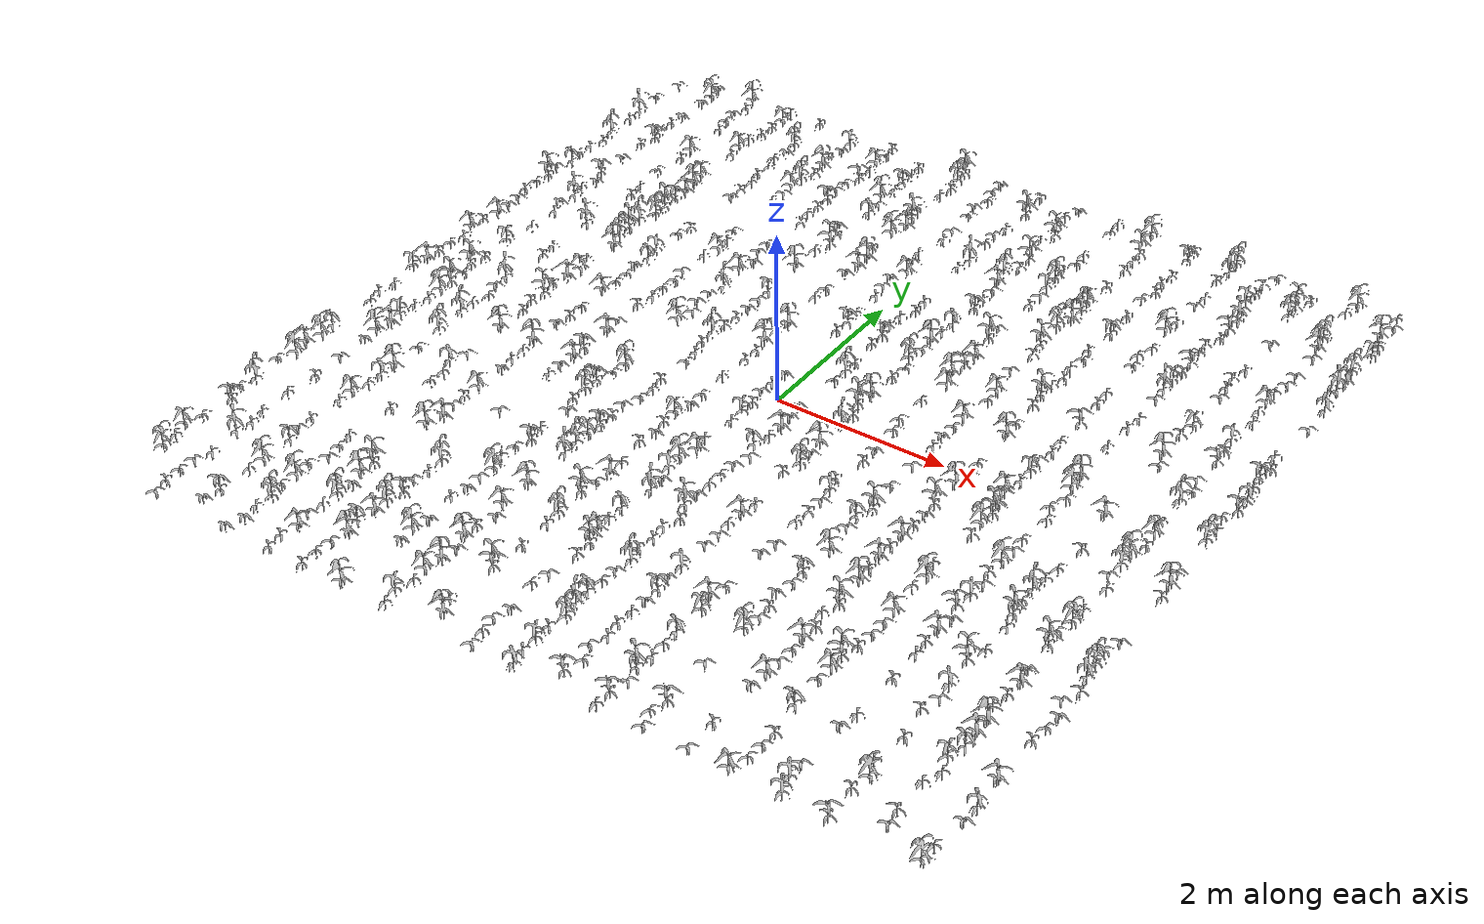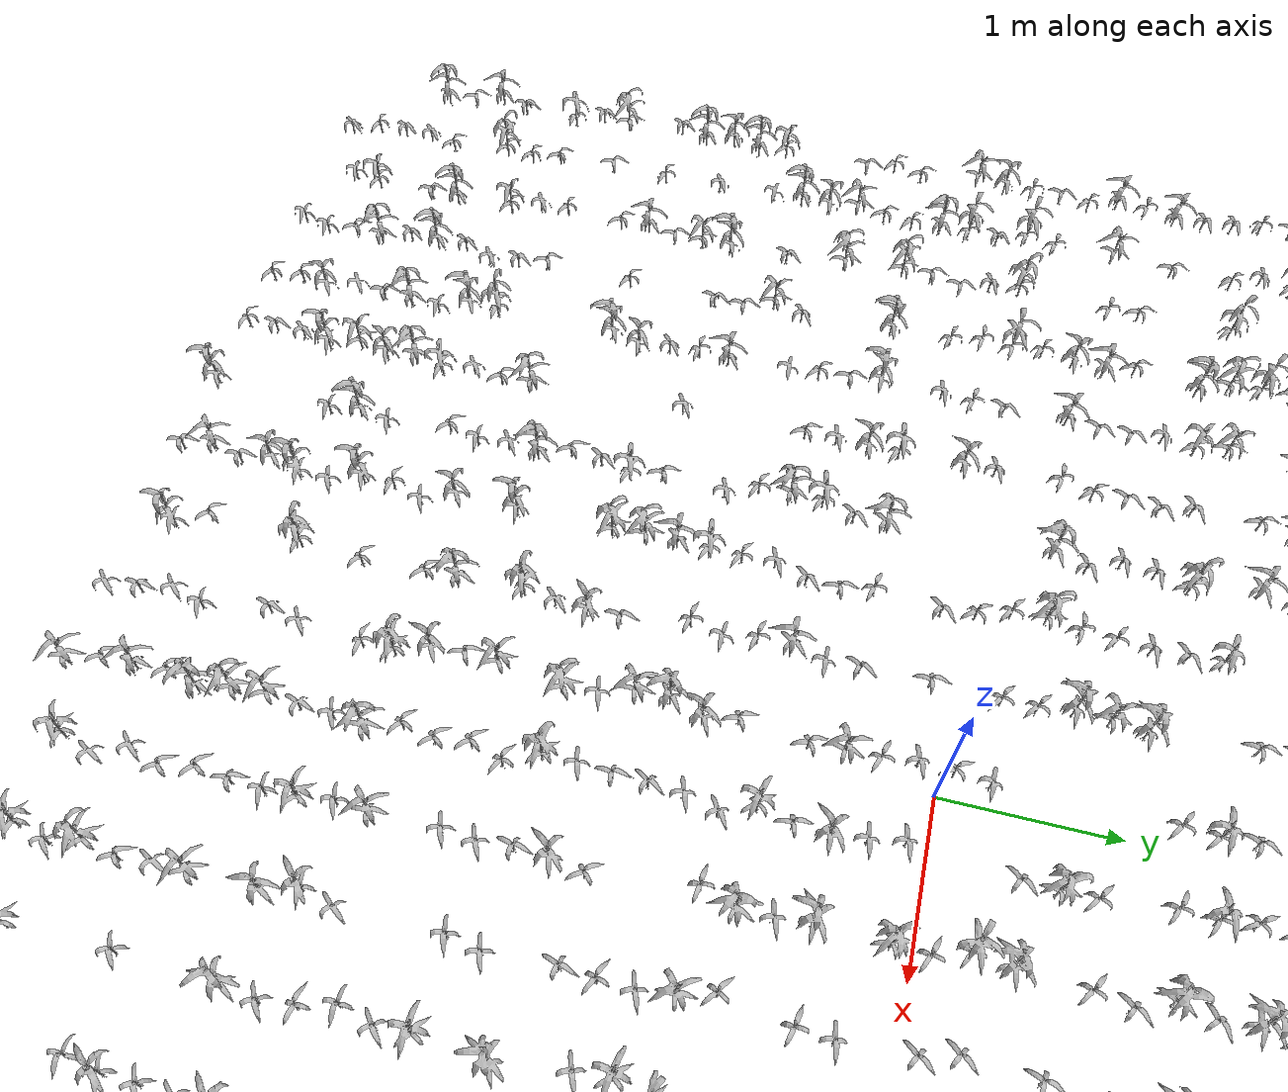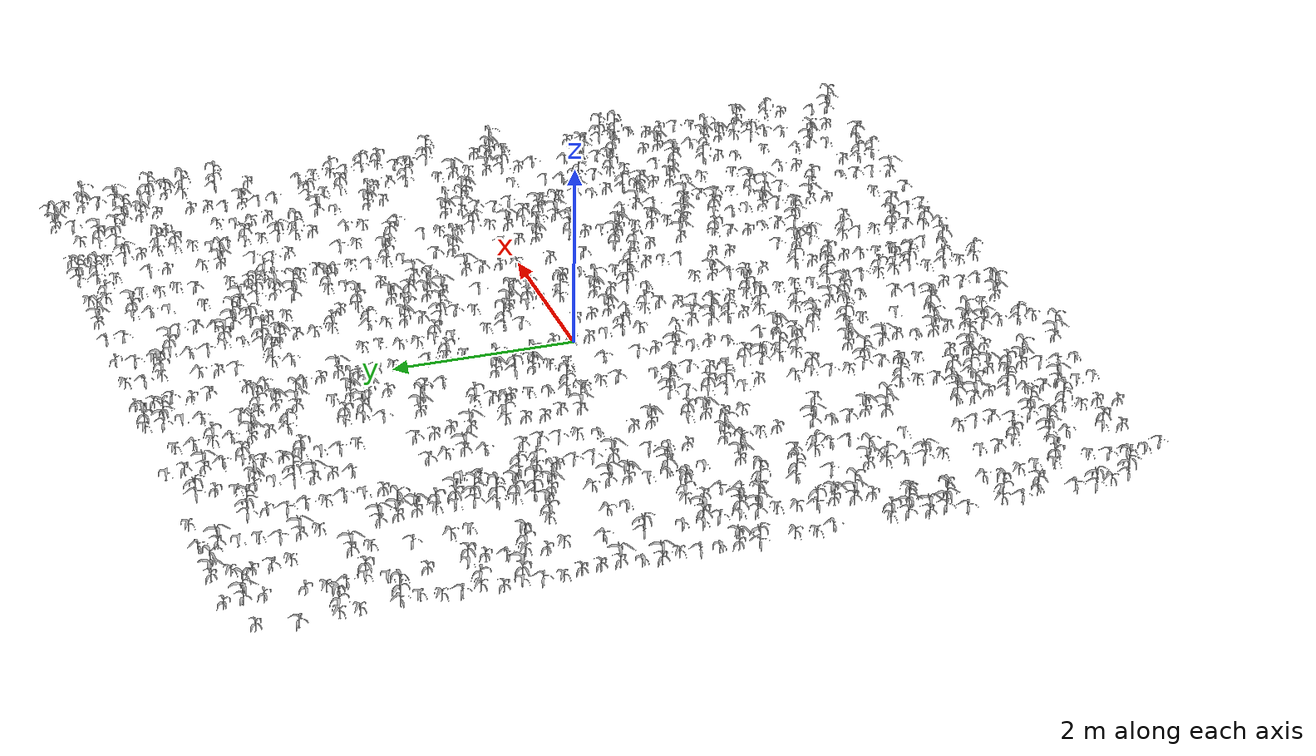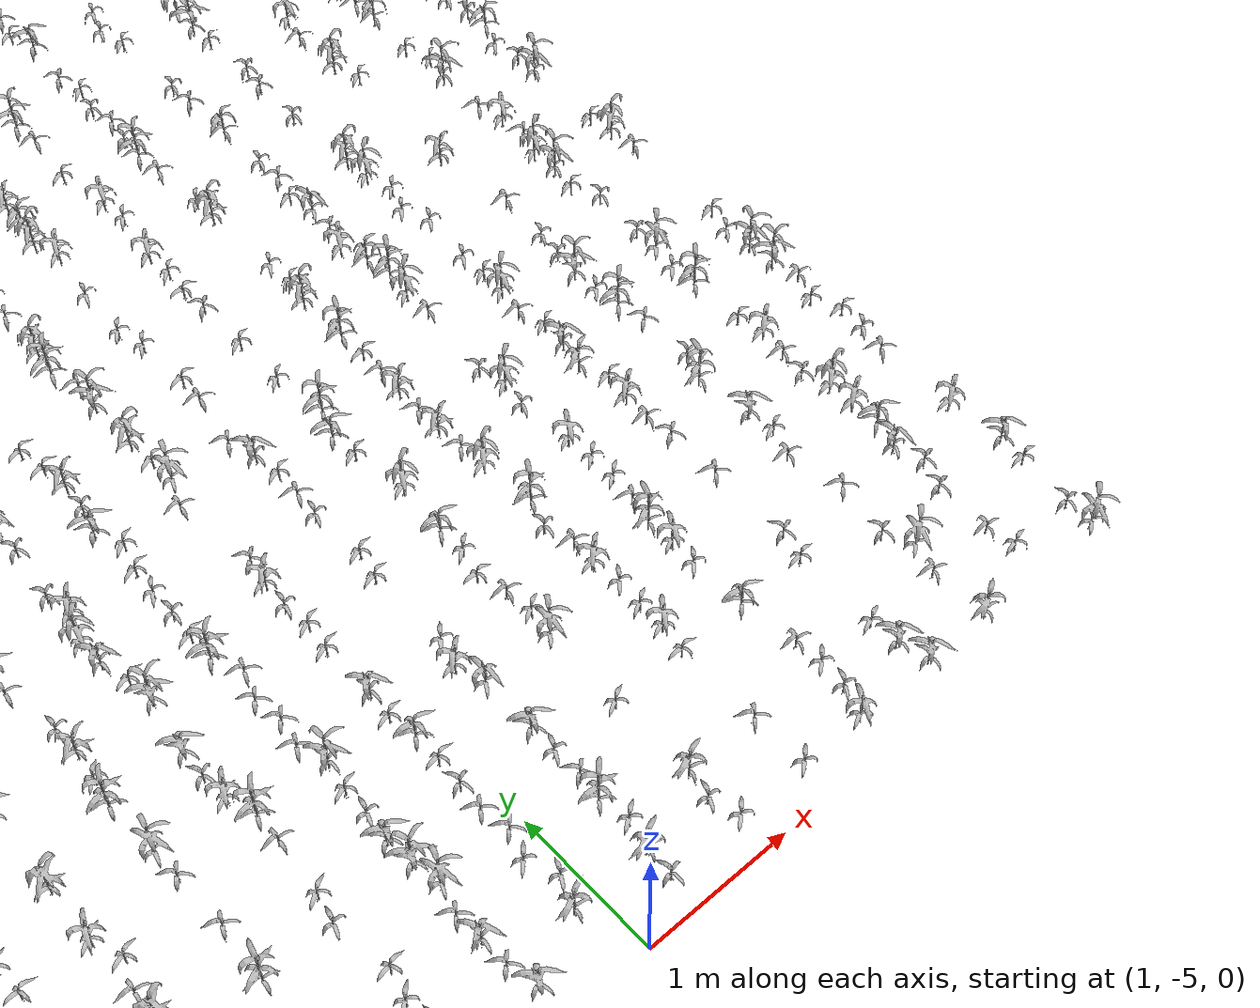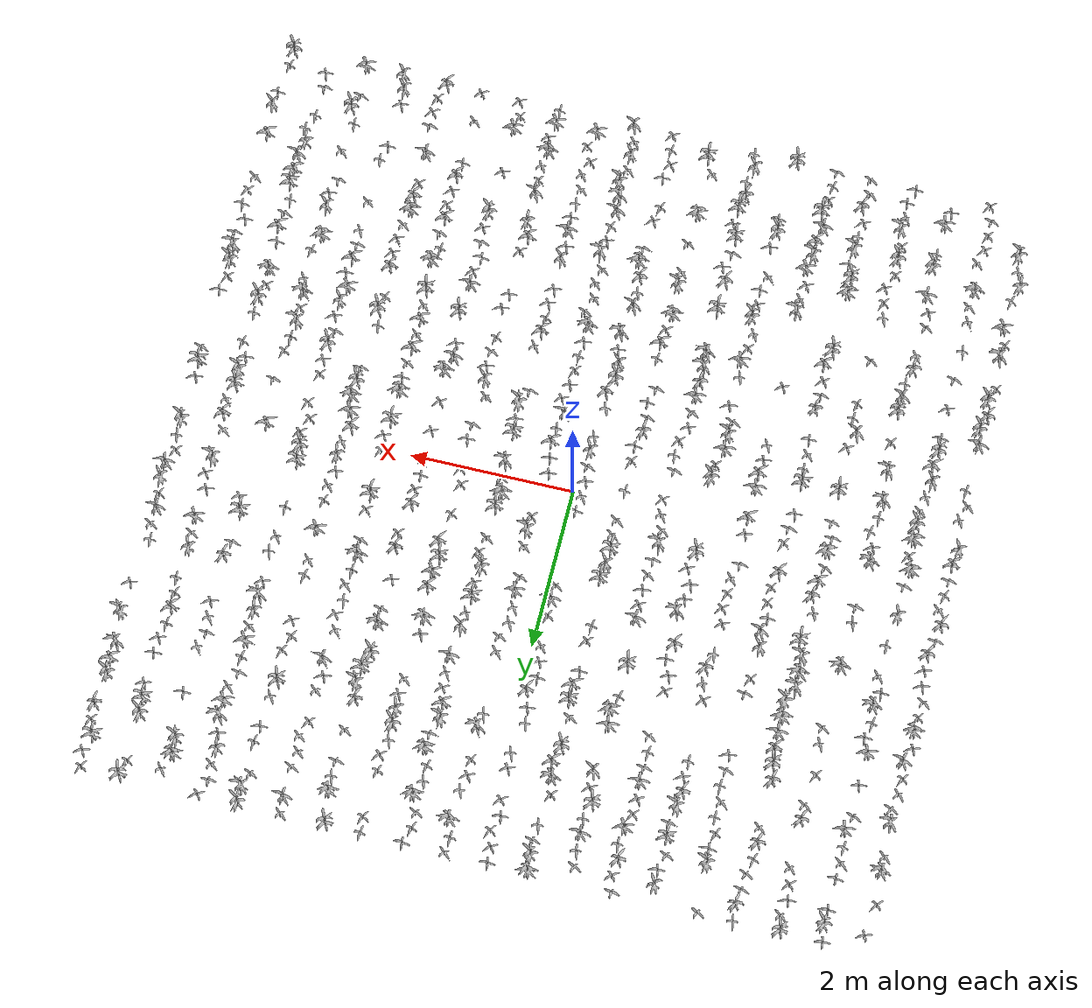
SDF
<sdf version="1.7">
 <world name="default">
  <plugin name="gazebo_ros_state" filename="libgazebo_ros_state.so"><update_rate>1.0</update_rate></plugin>
  <light name="sun" type="directional">
   <pose>0 0 10 0 -0 0</pose>
   <diffuse>0.8 0.8 0.8 1</diffuse>
   <specular>0.2 0.2 0.2 1</specular>
   <attenuation>
    <range>1000</range>
    <constant>0.9</constant>
    <linear>0.01</linear>
    <quadratic>0.001</quadratic>
   </attenuation>
   <direction>-0.5 0.1 -0.9</direction>
   <spot><inner_angle>0</inner_angle><outer_angle>0</outer_angle><falloff>0</falloff></spot>
  </light>
  <scene>
   <sky><clouds><speed>12</speed></clouds></sky>
   <ambient>0.4 0.4 0.4 1</ambient>
   <background>0.7 0.7 0.7 1</background>
   <shadows>1</shadows>
  </scene>
  <physics name="default_physics" default="0" type="ode">
   <ode>
    <solver>
     <type>quick</type>
     <iters>50</iters>
     <sor>1</sor>
     <use_dynamic_moi_rescaling>0</use_dynamic_moi_rescaling>
    </solver>
    <constraints>
     <cfm>0</cfm>
     <erp>0.2</erp>
     <contact_max_correcting_vel>1000</contact_max_correcting_vel>
     <contact_surface_layer>0.001</contact_surface_layer>
    </constraints>
   </ode>
   <max_step_size>0.004</max_step_size>
   <real_time_factor>1</real_time_factor>
   <real_time_update_rate>250</real_time_update_rate>
  </physics>
  <spherical_coordinates>
   <surface_model>EARTH_WGS84</surface_model>
   <latitude_deg>42.6129</latitude_deg>
   <longitude_deg>-5.56566</longitude_deg>
   <elevation>880</elevation>
   <heading_deg>0</heading_deg>
  </spherical_coordinates>
  <gravity>0 0 -9.8066</gravity>
  <magnetic_field>6e-06 2.3e-05 -4.2e-05</magnetic_field>
  <atmosphere type="adiabatic"/>
  <audio><device>default</device></audio>
  <model name="maize_-4.55020041969208_-4.215">
   <static>1</static>
   <link name="link">
    <inertial>
     <mass>0.2</mass>
     <inertia>
      <ixx>0.166667</ixx>
      <ixy>0</ixy>
      <ixz>0</ixz>
      <iyy>0.166667</iyy>
      <iyz>0</iyz>
      <izz>0.166667</izz>
     </inertia>
    </inertial>
    <collision name="collision">
     <geometry><mesh><uri>model://corn_5/meshes/corn.dae</uri><scale>0.25 0.25 0.25</scale></mesh></geometry>
     <surface>
      <friction><ode><mu>0</mu><mu2>0</mu2></ode></friction>
      <contact><ode><kp>0</kp><kd>0</kd><max_vel>0</max_vel><min_depth>0.002</min_depth></ode></contact>
     </surface>
    </collision>
    <visual name="visual">
     <geometry><mesh><uri>model://corn_5/meshes/corn.dae</uri><scale>0.25 0.25 0.25</scale></mesh></geometry>
    </visual>
    <velocity_decay><linear>0</linear><angular>0</angular></velocity_decay>
   </link>
   <pose>-4.5502 -4.215 0.05 0 -0 1.16205</pose>
  </model>
  <model name="maize_-4.580675109102509_-4.02">
   <static>1</static>
   <link name="link">
    <inertial>
     <mass>0.2</mass>
     <inertia>
      <ixx>0.166667</ixx>
      <ixy>0</ixy>
      <ixz>0</ixz>
      <iyy>0.166667</iyy>
      <iyz>0</iyz>
      <izz>0.166667</izz>
     </inertia>
    </inertial>
    <collision name="collision">
     <geometry><mesh><uri>model://corn_3/meshes/corn.dae</uri><scale>0.25 0.25 0.25</scale></mesh></geometry>
     <surface>
      <friction><ode><mu>0</mu><mu2>0</mu2></ode></friction>
      <contact><ode><kp>0</kp><kd>0</kd><max_vel>0</max_vel><min_depth>0.002</min_depth></ode></contact>
     </surface>
    </collision>
    <visual name="visual">
     <geometry><mesh><uri>model://corn_3/meshes/corn.dae</uri><scale>0.25 0.25 0.25</scale></mesh></geometry>
    </visual>
    <velocity_decay><linear>0</linear><angular>0</angular></velocity_decay>
   </link>
   <pose>-4.58068 -4.02 0.05 0 -0 1.94145</pose>
  </model>
  <model name="maize_-4.645680621180366_-3.8249999999999997">
   <static>1</static>
   <link name="link">
    <inertial>
     <mass>0.2</mass>
     <inertia>
      <ixx>0.166667</ixx>
      <ixy>0</ixy>
      <ixz>0</ixz>
      <iyy>0.166667</iyy>
      <iyz>0</iyz>
      <izz>0.166667</izz>
     </inertia>
    </inertial>
    <collision name="collision">
     <geometry><mesh><uri>model://corn_4/meshes/corn.dae</uri><scale>0.25 0.25 0.25</scale></mesh></geometry>
     <surface>
      <friction><ode><mu>0</mu><mu2>0</mu2></ode></friction>
      <contact><ode><kp>0</kp><kd>0</kd><max_vel>0</max_vel><min_depth>0.002</min_depth></ode></contact>
     </surface>
    </collision>
    <visual name="visual">
     <geometry><mesh><uri>model://corn_4/meshes/corn.dae</uri><scale>0.25 0.25 0.25</scale></mesh></geometry>
    </visual>
    <velocity_decay><linear>0</linear><angular>0</angular></velocity_decay>
   </link>
   <pose>-4.64568 -3.825 0.05 0 -0 1.04335</pose>
  </model>
  <model name="maize_-4.582487427102618_-3.63">
   <static>1</static>
   <link name="link">
    <inertial>
     <mass>0.2</mass>
     <inertia>
      <ixx>0.166667</ixx>
      <ixy>0</ixy>
      <ixz>0</ixz>
      <iyy>0.166667</iyy>
      <iyz>0</iyz>
      <izz>0.166667</izz>
     </inertia>
    </inertial>
    <collision name="collision">
     <geometry><mesh><uri>model://corn_3/meshes/corn.dae</uri><scale>0.25 0.25 0.25</scale></mesh></geometry>
     <surface>
      <friction><ode><mu>0</mu><mu2>0</mu2></ode></friction>
      <contact><ode><kp>0</kp><kd>0</kd><max_vel>0</max_vel><min_depth>0.002</min_depth></ode></contact>
     </surface>
    </collision>
    <visual name="visual">
     <geometry><mesh><uri>model://corn_3/meshes/corn.dae</uri><scale>0.25 0.25 0.25</scale></mesh></geometry>
    </visual>
    <velocity_decay><linear>0</linear><angular>0</angular></velocity_decay>
   </link>
   <pose>-4.58249 -3.63 0.05 0 -0 1.40864</pose>
  </model>
  <model name="maize_-4.554123064080819_-3.2399999999999998">
   <static>1</static>
   <link name="link">
    <inertial>
     <mass>0.2</mass>
     <inertia>
      <ixx>0.166667</ixx>
      <ixy>0</ixy>
      <ixz>0</ixz>
      <iyy>0.166667</iyy>
      <iyz>0</iyz>
      <izz>0.166667</izz>
     </inertia>
    </inertial>
    <collision name="collision">
     <geometry><mesh><uri>model://corn_4/meshes/corn.dae</uri><scale>0.25 0.25 0.25</scale></mesh></geometry>
     <surface>
      <friction><ode><mu>0</mu><mu2>0</mu2></ode></friction>
      <contact><ode><kp>0</kp><kd>0</kd><max_vel>0</max_vel><min_depth>0.002</min_depth></ode></contact>
     </surface>
    </collision>
    <visual name="visual">
     <geometry><mesh><uri>model://corn_4/meshes/corn.dae</uri><scale>0.25 0.25 0.25</scale></mesh></geometry>
    </visual>
    <velocity_decay><linear>0</linear><angular>0</angular></velocity_decay>
   </link>
   <pose>-4.55412 -3.24 0.05 0 -0 2.99477</pose>
  </model>
  <model name="maize_-4.629698592727202_-3.045">
   <static>1</static>
   <link name="link">
    <inertial>
     <mass>0.2</mass>
     <inertia>
      <ixx>0.166667</ixx>
      <ixy>0</ixy>
      <ixz>0</ixz>
      <iyy>0.166667</iyy>
      <iyz>0</iyz>
      <izz>0.166667</izz>
     </inertia>
    </inertial>
    <collision name="collision">
     <geometry><mesh><uri>model://corn_3/meshes/corn.dae</uri><scale>0.25 0.25 0.25</scale></mesh></geometry>
     <surface>
      <friction><ode><mu>0</mu><mu2>0</mu2></ode></friction>
      <contact><ode><kp>0</kp><kd>0</kd><max_vel>0</max_vel><min_depth>0.002</min_depth></ode></contact>
     </surface>
    </collision>
    <visual name="visual">
     <geometry><mesh><uri>model://corn_3/meshes/corn.dae</uri><scale>0.25 0.25 0.25</scale></mesh></geometry>
    </visual>
    <velocity_decay><linear>0</linear><angular>0</angular></velocity_decay>
   </link>
   <pose>-4.6297 -3.045 0.05 0 -0 1.2091</pose>
  </model>
  <model name="maize_-4.592387539115253_-2.8499999999999996">
   <static>1</static>
   <link name="link">
    <inertial>
     <mass>0.2</mass>
     <inertia>
      <ixx>0.166667</ixx>
      <ixy>0</ixy>
      <ixz>0</ixz>
      <iyy>0.166667</iyy>
      <iyz>0</iyz>
      <izz>0.166667</izz>
     </inertia>
    </inertial>
    <collision name="collision">
     <geometry><mesh><uri>model://corn_5/meshes/corn.dae</uri><scale>0.25 0.25 0.25</scale></mesh></geometry>
     <surface>
      <friction><ode><mu>0</mu><mu2>0</mu2></ode></friction>
      <contact><ode><kp>0</kp><kd>0</kd><max_vel>0</max_vel><min_depth>0.002</min_depth></ode></contact>
     </surface>
    </collision>
    <visual name="visual">
     <geometry><mesh><uri>model://corn_5/meshes/corn.dae</uri><scale>0.25 0.25 0.25</scale></mesh></geometry>
    </visual>
    <velocity_decay><linear>0</linear><angular>0</angular></velocity_decay>
   </link>
   <pose>-4.59239 -2.85 0.05 0 -0 1.94751</pose>
  </model>
  <model name="maize_-4.649728887082645_-2.46">
   <static>1</static>
   <link name="link">
    <inertial>
     <mass>0.2</mass>
     <inertia>
      <ixx>0.166667</ixx>
      <ixy>0</ixy>
      <ixz>0</ixz>
      <iyy>0.166667</iyy>
      <iyz>0</iyz>
      <izz>0.166667</izz>
     </inertia>
    </inertial>
    <collision name="collision">
     <geometry><mesh><uri>model://corn_3/meshes/corn.dae</uri><scale>0.25 0.25 0.25</scale></mesh></geometry>
     <surface>
      <friction><ode><mu>0</mu><mu2>0</mu2></ode></friction>
      <contact><ode><kp>0</kp><kd>0</kd><max_vel>0</max_vel><min_depth>0.002</min_depth></ode></contact>
     </surface>
    </collision>
    <visual name="visual">
     <geometry><mesh><uri>model://corn_3/meshes/corn.dae</uri><scale>0.25 0.25 0.25</scale></mesh></geometry>
    </visual>
    <velocity_decay><linear>0</linear><angular>0</angular></velocity_decay>
   </link>
   <pose>-4.64973 -2.46 0.05 0 -0 1.15496</pose>
  </model>
  <model name="maize_-4.5740912913957406_-2.2649999999999997">
   <static>1</static>
   <link name="link">
    <inertial>
     <mass>0.2</mass>
     <inertia>
      <ixx>0.166667</ixx>
      <ixy>0</ixy>
      <ixz>0</ixz>
      <iyy>0.166667</iyy>
      <iyz>0</iyz>
      <izz>0.166667</izz>
     </inertia>
    </inertial>
    <collision name="collision">
     <geometry><mesh><uri>model://corn_5/meshes/corn.dae</uri><scale>0.25 0.25 0.25</scale></mesh></geometry>
     <surface>
      <friction><ode><mu>0</mu><mu2>0</mu2></ode></friction>
      <contact><ode><kp>0</kp><kd>0</kd><max_vel>0</max_vel><min_depth>0.002</min_depth></ode></contact>
     </surface>
    </collision>
    <visual name="visual">
     <geometry><mesh><uri>model://corn_5/meshes/corn.dae</uri><scale>0.25 0.25 0.25</scale></mesh></geometry>
    </visual>
    <velocity_decay><linear>0</linear><angular>0</angular></velocity_decay>
   </link>
   <pose>-4.57409 -2.265 0.05 0 -0 0.887421</pose>
  </model>
  <model name="maize_-4.6180942505716365_-2.07">
   <static>1</static>
   <link name="link">
    <inertial>
     <mass>0.2</mass>
     <inertia>
      <ixx>0.166667</ixx>
      <ixy>0</ixy>
      <ixz>0</ixz>
      <iyy>0.166667</iyy>
      <iyz>0</iyz>
      <izz>0.166667</izz>
     </inertia>
    </inertial>
    <collision name="collision">
     <geometry><mesh><uri>model://corn_4/meshes/corn.dae</uri><scale>0.25 0.25 0.25</scale></mesh></geometry>
     <surface>
      <friction><ode><mu>0</mu><mu2>0</mu2></ode></friction>
      <contact><ode><kp>0</kp><kd>0</kd><max_vel>0</max_vel><min_depth>0.002</min_depth></ode></contact>
     </surface>
    </collision>
    <visual name="visual">
     <geometry><mesh><uri>model://corn_4/meshes/corn.dae</uri><scale>0.25 0.25 0.25</scale></mesh></geometry>
    </visual>
    <velocity_decay><linear>0</linear><angular>0</angular></velocity_decay>
   </link>
   <pose>-4.61809 -2.07 0.05 0 -0 0.544141</pose>
  </model>
  <model name="maize_-4.561572440521808_-1.8749999999999996">
   <static>1</static>
   <link name="link">
    <inertial>
     <mass>0.2</mass>
     <inertia>
      <ixx>0.166667</ixx>
      <ixy>0</ixy>
      <ixz>0</ixz>
      <iyy>0.166667</iyy>
      <iyz>0</iyz>
      <izz>0.166667</izz>
     </inertia>
    </inertial>
    <collision name="collision">
     <geometry><mesh><uri>model://corn_5/meshes/corn.dae</uri><scale>0.25 0.25 0.25</scale></mesh></geometry>
     <surface>
      <friction><ode><mu>0</mu><mu2>0</mu2></ode></friction>
      <contact><ode><kp>0</kp><kd>0</kd><max_vel>0</max_vel><min_depth>0.002</min_depth></ode></contact>
     </surface>
    </collision>
    <visual name="visual">
     <geometry><mesh><uri>model://corn_5/meshes/corn.dae</uri><scale>0.25 0.25 0.25</scale></mesh></geometry>
    </visual>
    <velocity_decay><linear>0</linear><angular>0</angular></velocity_decay>
   </link>
   <pose>-4.56157 -1.875 0.05 0 -0 0.807467</pose>
  </model>
  <model name="maize_-4.591006561654498_-1.6799999999999997">
   <static>1</static>
   <link name="link">
    <inertial>
     <mass>0.2</mass>
     <inertia>
      <ixx>0.166667</ixx>
      <ixy>0</ixy>
      <ixz>0</ixz>
      <iyy>0.166667</iyy>
      <iyz>0</iyz>
      <izz>0.166667</izz>
     </inertia>
    </inertial>
    <collision name="collision">
     <geometry><mesh><uri>model://corn_4/meshes/corn.dae</uri><scale>0.25 0.25 0.25</scale></mesh></geometry>
     <surface>
      <friction><ode><mu>0</mu><mu2>0</mu2></ode></friction>
      <contact><ode><kp>0</kp><kd>0</kd><max_vel>0</max_vel><min_depth>0.002</min_depth></ode></contact>
     </surface>
    </collision>
    <visual name="visual">
     <geometry><mesh><uri>model://corn_4/meshes/corn.dae</uri><scale>0.25 0.25 0.25</scale></mesh></geometry>
    </visual>
    <velocity_decay><linear>0</linear><angular>0</angular></velocity_decay>
   </link>
   <pose>-4.59101 -1.68 0.05 0 -0 2.39519</pose>
  </model>
  <model name="maize_-4.568949534493869_-1.0949999999999998">
   <static>1</static>
   <link name="link">
    <inertial>
     <mass>0.2</mass>
     <inertia>
      <ixx>0.166667</ixx>
      <ixy>0</ixy>
      <ixz>0</ixz>
      <iyy>0.166667</iyy>
      <iyz>0</iyz>
      <izz>0.166667</izz>
     </inertia>
    </inertial>
    <collision name="collision">
     <geometry><mesh><uri>model://corn_3/meshes/corn.dae</uri><scale>0.25 0.25 0.25</scale></mesh></geometry>
     <surface>
      <friction><ode><mu>0</mu><mu2>0</mu2></ode></friction>
      <contact><ode><kp>0</kp><kd>0</kd><max_vel>0</max_vel><min_depth>0.002</min_depth></ode></contact>
     </surface>
    </collision>
    <visual name="visual">
     <geometry><mesh><uri>model://corn_3/meshes/corn.dae</uri><scale>0.25 0.25 0.25</scale></mesh></geometry>
    </visual>
    <velocity_decay><linear>0</linear><angular>0</angular></velocity_decay>
   </link>
   <pose>-4.56895 -1.095 0.05 0 -0 1.52543</pose>
  </model>
  <model name="maize_-4.627686719818913_-0.8999999999999995">
   <static>1</static>
   <link name="link">
    <inertial>
     <mass>0.2</mass>
     <inertia>
      <ixx>0.166667</ixx>
      <ixy>0</ixy>
      <ixz>0</ixz>
      <iyy>0.166667</iyy>
      <iyz>0</iyz>
      <izz>0.166667</izz>
     </inertia>
    </inertial>
    <collision name="collision">
     <geometry><mesh><uri>model://corn_3/meshes/corn.dae</uri><scale>0.25 0.25 0.25</scale></mesh></geometry>
     <surface>
      <friction><ode><mu>0</mu><mu2>0</mu2></ode></friction>
      <contact><ode><kp>0</kp><kd>0</kd><max_vel>0</max_vel><min_depth>0.002</min_depth></ode></contact>
     </surface>
    </collision>
    <visual name="visual">
     <geometry><mesh><uri>model://corn_3/meshes/corn.dae</uri><scale>0.25 0.25 0.25</scale></mesh></geometry>
    </visual>
    <velocity_decay><linear>0</linear><angular>0</angular></velocity_decay>
   </link>
   <pose>-4.62769 -0.9 0.05 0 -0 2.48654</pose>
  </model>
  <model name="maize_-4.568834103158_-0.7050000000000001">
   <static>1</static>
   <link name="link">
    <inertial>
     <mass>0.2</mass>
     <inertia>
      <ixx>0.166667</ixx>
      <ixy>0</ixy>
      <ixz>0</ixz>
      <iyy>0.166667</iyy>
      <iyz>0</iyz>
      <izz>0.166667</izz>
     </inertia>
    </inertial>
    <collision name="collision">
     <geometry><mesh><uri>model://corn_3/meshes/corn.dae</uri><scale>0.25 0.25 0.25</scale></mesh></geometry>
     <surface>
      <friction><ode><mu>0</mu><mu2>0</mu2></ode></friction>
      <contact><ode><kp>0</kp><kd>0</kd><max_vel>0</max_vel><min_depth>0.002</min_depth></ode></contact>
     </surface>
    </collision>
    <visual name="visual">
     <geometry><mesh><uri>model://corn_3/meshes/corn.dae</uri><scale>0.25 0.25 0.25</scale></mesh></geometry>
    </visual>
    <velocity_decay><linear>0</linear><angular>0</angular></velocity_decay>
   </link>
   <pose>-4.56883 -0.705 0.05 0 -0 2.10942</pose>
  </model>
  <model name="maize_-4.641265424464105_-0.3149999999999995">
   <static>1</static>
   <link name="link">
    <inertial>
     <mass>0.2</mass>
     <inertia>
      <ixx>0.166667</ixx>
      <ixy>0</ixy>
      <ixz>0</ixz>
      <iyy>0.166667</iyy>
      <iyz>0</iyz>
      <izz>0.166667</izz>
     </inertia>
    </inertial>
    <collision name="collision">
     <geometry><mesh><uri>model://corn_4/meshes/corn.dae</uri><scale>0.25 0.25 0.25</scale></mesh></geometry>
     <surface>
      <friction><ode><mu>0</mu><mu2>0</mu2></ode></friction>
      <contact><ode><kp>0</kp><kd>0</kd><max_vel>0</max_vel><min_depth>0.002</min_depth></ode></contact>
     </surface>
    </collision>
    <visual name="visual">
     <geometry><mesh><uri>model://corn_4/meshes/corn.dae</uri><scale>0.25 0.25 0.25</scale></mesh></geometry>
    </visual>
    <velocity_decay><linear>0</linear><angular>0</angular></velocity_decay>
   </link>
   <pose>-4.64126 -0.315 0.05 0 -0 1.39302</pose>
  </model>
  <model name="maize_-4.607150826464587_-0.1200000000000001">
   <static>1</static>
   <link name="link">
    <inertial>
     <mass>0.2</mass>
     <inertia>
      <ixx>0.166667</ixx>
      <ixy>0</ixy>
      <ixz>0</ixz>
      <iyy>0.166667</iyy>
      <iyz>0</iyz>
      <izz>0.166667</izz>
     </inertia>
    </inertial>
    <collision name="collision">
     <geometry><mesh><uri>model://corn_4/meshes/corn.dae</uri><scale>0.25 0.25 0.25</scale></mesh></geometry>
     <surface>
      <friction><ode><mu>0</mu><mu2>0</mu2></ode></friction>
      <contact><ode><kp>0</kp><kd>0</kd><max_vel>0</max_vel><min_depth>0.002</min_depth></ode></contact>
     </surface>
    </collision>
    <visual name="visual">
     <geometry><mesh><uri>model://corn_4/meshes/corn.dae</uri><scale>0.25 0.25 0.25</scale></mesh></geometry>
    </visual>
    <velocity_decay><linear>0</linear><angular>0</angular></velocity_decay>
   </link>
   <pose>-4.60715 -0.12 0.05 0 -0 0.20456</pose>
  </model>
  <model name="maize_-4.609371521306536_0.07500000000000018">
   <static>1</static>
   <link name="link">
    <inertial>
     <mass>0.2</mass>
     <inertia>
      <ixx>0.166667</ixx>
      <ixy>0</ixy>
      <ixz>0</ixz>
      <iyy>0.166667</iyy>
      <iyz>0</iyz>
      <izz>0.166667</izz>
     </inertia>
    </inertial>
    <collision name="collision">
     <geometry><mesh><uri>model://corn_3/meshes/corn.dae</uri><scale>0.25 0.25 0.25</scale></mesh></geometry>
     <surface>
      <friction><ode><mu>0</mu><mu2>0</mu2></ode></friction>
      <contact><ode><kp>0</kp><kd>0</kd><max_vel>0</max_vel><min_depth>0.002</min_depth></ode></contact>
     </surface>
    </collision>
    <visual name="visual">
     <geometry><mesh><uri>model://corn_3/meshes/corn.dae</uri><scale>0.25 0.25 0.25</scale></mesh></geometry>
    </visual>
    <velocity_decay><linear>0</linear><angular>0</angular></velocity_decay>
   </link>
   <pose>-4.60937 0.075 0.05 0 -0 3.04615</pose>
  </model>
  <model name="maize_-4.602589979055056_0.27000000000000046">
   <static>1</static>
   <link name="link">
    <inertial>
     <mass>0.2</mass>
     <inertia>
      <ixx>0.166667</ixx>
      <ixy>0</ixy>
      <ixz>0</ixz>
      <iyy>0.166667</iyy>
      <iyz>0</iyz>
      <izz>0.166667</izz>
     </inertia>
    </inertial>
    <collision name="collision">
     <geometry><mesh><uri>model://corn_3/meshes/corn.dae</uri><scale>0.25 0.25 0.25</scale></mesh></geometry>
     <surface>
      <friction><ode><mu>0</mu><mu2>0</mu2></ode></friction>
      <contact><ode><kp>0</kp><kd>0</kd><max_vel>0</max_vel><min_depth>0.002</min_depth></ode></contact>
     </surface>
    </collision>
    <visual name="visual">
     <geometry><mesh><uri>model://corn_3/meshes/corn.dae</uri><scale>0.25 0.25 0.25</scale></mesh></geometry>
    </visual>
    <velocity_decay><linear>0</linear><angular>0</angular></velocity_decay>
   </link>
   <pose>-4.60259 0.27 0.05 0 -0 1.35027</pose>
  </model>
  <model name="maize_-4.570653018177786_0.46500000000000075">
   <static>1</static>
   <link name="link">
    <inertial>
     <mass>0.2</mass>
     <inertia>
      <ixx>0.166667</ixx>
      <ixy>0</ixy>
      <ixz>0</ixz>
      <iyy>0.166667</iyy>
      <iyz>0</iyz>
      <izz>0.166667</izz>
     </inertia>
    </inertial>
    <collision name="collision">
     <geometry><mesh><uri>model://corn_3/meshes/corn.dae</uri><scale>0.25 0.25 0.25</scale></mesh></geometry>
     <surface>
      <friction><ode><mu>0</mu><mu2>0</mu2></ode></friction>
      <contact><ode><kp>0</kp><kd>0</kd><max_vel>0</max_vel><min_depth>0.002</min_depth></ode></contact>
     </surface>
    </collision>
    <visual name="visual">
     <geometry><mesh><uri>model://corn_3/meshes/corn.dae</uri><scale>0.25 0.25 0.25</scale></mesh></geometry>
    </visual>
    <velocity_decay><linear>0</linear><angular>0</angular></velocity_decay>
   </link>
   <pose>-4.57065 0.465 0.05 0 -0 2.42042</pose>
  </model>
  <model name="maize_-4.63863826151183_0.6600000000000001">
   <static>1</static>
   <link name="link">
    <inertial>
     <mass>0.2</mass>
     <inertia>
      <ixx>0.166667</ixx>
      <ixy>0</ixy>
      <ixz>0</ixz>
      <iyy>0.166667</iyy>
      <iyz>0</iyz>
      <izz>0.166667</izz>
     </inertia>
    </inertial>
    <collision name="collision">
     <geometry><mesh><uri>model://corn_4/meshes/corn.dae</uri><scale>0.25 0.25 0.25</scale></mesh></geometry>
     <surface>
      <friction><ode><mu>0</mu><mu2>0</mu2></ode></friction>
      <contact><ode><kp>0</kp><kd>0</kd><max_vel>0</max_vel><min_depth>0.002</min_depth></ode></contact>
     </surface>
    </collision>
    <visual name="visual">
     <geometry><mesh><uri>model://corn_4/meshes/corn.dae</uri><scale>0.25 0.25 0.25</scale></mesh></geometry>
    </visual>
    <velocity_decay><linear>0</linear><angular>0</angular></velocity_decay>
   </link>
   <pose>-4.63864 0.66 0.05 0 -0 0.585221</pose>
  </model>
  <model name="maize_-4.616977580214433_0.8550000000000004">
   <static>1</static>
   <link name="link">
    <inertial>
     <mass>0.2</mass>
     <inertia>
      <ixx>0.166667</ixx>
      <ixy>0</ixy>
      <ixz>0</ixz>
      <iyy>0.166667</iyy>
      <iyz>0</iyz>
      <izz>0.166667</izz>
     </inertia>
    </inertial>
    <collision name="collision">
     <geometry><mesh><uri>model://corn_3/meshes/corn.dae</uri><scale>0.25 0.25 0.25</scale></mesh></geometry>
     <surface>
      <friction><ode><mu>0</mu><mu2>0</mu2></ode></friction>
      <contact><ode><kp>0</kp><kd>0</kd><max_vel>0</max_vel><min_depth>0.002</min_depth></ode></contact>
     </surface>
    </collision>
    <visual name="visual">
     <geometry><mesh><uri>model://corn_3/meshes/corn.dae</uri><scale>0.25 0.25 0.25</scale></mesh></geometry>
    </visual>
    <velocity_decay><linear>0</linear><angular>0</angular></velocity_decay>
   </link>
   <pose>-4.61698 0.855 0.05 0 -0 3.05886</pose>
  </model>
  <model name="maize_-4.561774898540121_1.0500000000000007">
   <static>1</static>
   <link name="link">
    <inertial>
     <mass>0.2</mass>
     <inertia>
      <ixx>0.166667</ixx>
      <ixy>0</ixy>
      <ixz>0</ixz>
      <iyy>0.166667</iyy>
      <iyz>0</iyz>
      <izz>0.166667</izz>
     </inertia>
    </inertial>
    <collision name="collision">
     <geometry><mesh><uri>model://corn_4/meshes/corn.dae</uri><scale>0.25 0.25 0.25</scale></mesh></geometry>
     <surface>
      <friction><ode><mu>0</mu><mu2>0</mu2></ode></friction>
      <contact><ode><kp>0</kp><kd>0</kd><max_vel>0</max_vel><min_depth>0.002</min_depth></ode></contact>
     </surface>
    </collision>
    <visual name="visual">
     <geometry><mesh><uri>model://corn_4/meshes/corn.dae</uri><scale>0.25 0.25 0.25</scale></mesh></geometry>
    </visual>
    <velocity_decay><linear>0</linear><angular>0</angular></velocity_decay>
   </link>
   <pose>-4.56177 1.05 0.05 0 -0 0.518835</pose>
  </model>
  <model name="maize_-4.569922193897871_1.245">
   <static>1</static>
   <link name="link">
    <inertial>
     <mass>0.2</mass>
     <inertia>
      <ixx>0.166667</ixx>
      <ixy>0</ixy>
      <ixz>0</ixz>
      <iyy>0.166667</iyy>
      <iyz>0</iyz>
      <izz>0.166667</izz>
     </inertia>
    </inertial>
    <collision name="collision">
     <geometry><mesh><uri>model://corn_3/meshes/corn.dae</uri><scale>0.25 0.25 0.25</scale></mesh></geometry>
     <surface>
      <friction><ode><mu>0</mu><mu2>0</mu2></ode></friction>
      <contact><ode><kp>0</kp><kd>0</kd><max_vel>0</max_vel><min_depth>0.002</min_depth></ode></contact>
     </surface>
    </collision>
    <visual name="visual">
     <geometry><mesh><uri>model://corn_3/meshes/corn.dae</uri><scale>0.25 0.25 0.25</scale></mesh></geometry>
    </visual>
    <velocity_decay><linear>0</linear><angular>0</angular></velocity_decay>
   </link>
   <pose>-4.56992 1.245 0.05 0 -0 0.488933</pose>
  </model>
  <model name="maize_-4.58929504737528_1.4400000000000004">
   <static>1</static>
   <link name="link">
    <inertial>
     <mass>0.2</mass>
     <inertia>
      <ixx>0.166667</ixx>
      <ixy>0</ixy>
      <ixz>0</ixz>
      <iyy>0.166667</iyy>
      <iyz>0</iyz>
      <izz>0.166667</izz>
     </inertia>
    </inertial>
    <collision name="collision">
     <geometry><mesh><uri>model://corn_3/meshes/corn.dae</uri><scale>0.25 0.25 0.25</scale></mesh></geometry>
     <surface>
      <friction><ode><mu>0</mu><mu2>0</mu2></ode></friction>
      <contact><ode><kp>0</kp><kd>0</kd><max_vel>0</max_vel><min_depth>0.002</min_depth></ode></contact>
     </surface>
    </collision>
    <visual name="visual">
     <geometry><mesh><uri>model://corn_3/meshes/corn.dae</uri><scale>0.25 0.25 0.25</scale></mesh></geometry>
    </visual>
    <velocity_decay><linear>0</linear><angular>0</angular></velocity_decay>
   </link>
   <pose>-4.58929 1.44 0.05 0 -0 0.408999</pose>
  </model>
  <model name="maize_-4.639935727970333_1.6350000000000007">
   <static>1</static>
   <link name="link">
    <inertial>
     <mass>0.2</mass>
     <inertia>
      <ixx>0.166667</ixx>
      <ixy>0</ixy>
      <ixz>0</ixz>
      <iyy>0.166667</iyy>
      <iyz>0</iyz>
      <izz>0.166667</izz>
     </inertia>
    </inertial>
    <collision name="collision">
     <geometry><mesh><uri>model://corn_3/meshes/corn.dae</uri><scale>0.25 0.25 0.25</scale></mesh></geometry>
     <surface>
      <friction><ode><mu>0</mu><mu2>0</mu2></ode></friction>
      <contact><ode><kp>0</kp><kd>0</kd><max_vel>0</max_vel><min_depth>0.002</min_depth></ode></contact>
     </surface>
    </collision>
    <visual name="visual">
     <geometry><mesh><uri>model://corn_3/meshes/corn.dae</uri><scale>0.25 0.25 0.25</scale></mesh></geometry>
    </visual>
    <velocity_decay><linear>0</linear><angular>0</angular></velocity_decay>
   </link>
   <pose>-4.63994 1.635 0.05 0 -0 2.59627</pose>
  </model>
  <model name="maize_-4.6269057923029315_1.83">
   <static>1</static>
   <link name="link">
    <inertial>
     <mass>0.2</mass>
     <inertia>
      <ixx>0.166667</ixx>
      <ixy>0</ixy>
      <ixz>0</ixz>
      <iyy>0.166667</iyy>
      <iyz>0</iyz>
      <izz>0.166667</izz>
     </inertia>
    </inertial>
    <collision name="collision">
     <geometry><mesh><uri>model://corn_3/meshes/corn.dae</uri><scale>0.25 0.25 0.25</scale></mesh></geometry>
     <surface>
      <friction><ode><mu>0</mu><mu2>0</mu2></ode></friction>
      <contact><ode><kp>0</kp><kd>0</kd><max_vel>0</max_vel><min_depth>0.002</min_depth></ode></contact>
     </surface>
    </collision>
    <visual name="visual">
     <geometry><mesh><uri>model://corn_3/meshes/corn.dae</uri><scale>0.25 0.25 0.25</scale></mesh></geometry>
    </visual>
    <velocity_decay><linear>0</linear><angular>0</angular></velocity_decay>
   </link>
   <pose>-4.62691 1.83 0.05 0 -0 1.14885</pose>
  </model>
  <model name="maize_-4.6076522750928195_2.0250000000000004">
   <static>1</static>
   <link name="link">
    <inertial>
     <mass>0.2</mass>
     <inertia>
      <ixx>0.166667</ixx>
      <ixy>0</ixy>
      <ixz>0</ixz>
      <iyy>0.166667</iyy>
      <iyz>0</iyz>
      <izz>0.166667</izz>
     </inertia>
    </inertial>
    <collision name="collision">
     <geometry><mesh><uri>model://corn_5/meshes/corn.dae</uri><scale>0.25 0.25 0.25</scale></mesh></geometry>
     <surface>
      <friction><ode><mu>0</mu><mu2>0</mu2></ode></friction>
      <contact><ode><kp>0</kp><kd>0</kd><max_vel>0</max_vel><min_depth>0.002</min_depth></ode></contact>
     </surface>
    </collision>
    <visual name="visual">
     <geometry><mesh><uri>model://corn_5/meshes/corn.dae</uri><scale>0.25 0.25 0.25</scale></mesh></geometry>
    </visual>
    <velocity_decay><linear>0</linear><angular>0</angular></velocity_decay>
   </link>
   <pose>-4.60765 2.025 0.05 0 -0 2.78431</pose>
  </model>
  <model name="maize_-4.648252382986778_2.2200000000000006">
   <static>1</static>
   <link name="link">
    <inertial>
     <mass>0.2</mass>
     <inertia>
      <ixx>0.166667</ixx>
      <ixy>0</ixy>
      <ixz>0</ixz>
      <iyy>0.166667</iyy>
      <iyz>0</iyz>
      <izz>0.166667</izz>
     </inertia>
    </inertial>
    <collision name="collision">
     <geometry><mesh><uri>model://corn_3/meshes/corn.dae</uri><scale>0.25 0.25 0.25</scale></mesh></geometry>
     <surface>
      <friction><ode><mu>0</mu><mu2>0</mu2></ode></friction>
      <contact><ode><kp>0</kp><kd>0</kd><max_vel>0</max_vel><min_depth>0.002</min_depth></ode></contact>
     </surface>
    </collision>
    <visual name="visual">
     <geometry><mesh><uri>model://corn_3/meshes/corn.dae</uri><scale>0.25 0.25 0.25</scale></mesh></geometry>
    </visual>
    <velocity_decay><linear>0</linear><angular>0</angular></velocity_decay>
   </link>
   <pose>-4.64825 2.22 0.05 0 -0 0.483202</pose>
  </model>
  <model name="maize_-4.561645221133806_2.415">
   <static>1</static>
   <link name="link">
    <inertial>
     <mass>0.2</mass>
     <inertia>
      <ixx>0.166667</ixx>
      <ixy>0</ixy>
      <ixz>0</ixz>
      <iyy>0.166667</iyy>
      <iyz>0</iyz>
      <izz>0.166667</izz>
     </inertia>
    </inertial>
    <collision name="collision">
     <geometry><mesh><uri>model://corn_4/meshes/corn.dae</uri><scale>0.25 0.25 0.25</scale></mesh></geometry>
     <surface>
      <friction><ode><mu>0</mu><mu2>0</mu2></ode></friction>
      <contact><ode><kp>0</kp><kd>0</kd><max_vel>0</max_vel><min_depth>0.002</min_depth></ode></contact>
     </surface>
    </collision>
    <visual name="visual">
     <geometry><mesh><uri>model://corn_4/meshes/corn.dae</uri><scale>0.25 0.25 0.25</scale></mesh></geometry>
    </visual>
    <velocity_decay><linear>0</linear><angular>0</angular></velocity_decay>
   </link>
   <pose>-4.56165 2.415 0.05 0 -0 2.25381</pose>
  </model>
  <model name="maize_-4.611175121932313_2.6100000000000003">
   <static>1</static>
   <link name="link">
    <inertial>
     <mass>0.2</mass>
     <inertia>
      <ixx>0.166667</ixx>
      <ixy>0</ixy>
      <ixz>0</ixz>
      <iyy>0.166667</iyy>
      <iyz>0</iyz>
      <izz>0.166667</izz>
     </inertia>
    </inertial>
    <collision name="collision">
     <geometry><mesh><uri>model://corn_3/meshes/corn.dae</uri><scale>0.25 0.25 0.25</scale></mesh></geometry>
     <surface>
      <friction><ode><mu>0</mu><mu2>0</mu2></ode></friction>
      <contact><ode><kp>0</kp><kd>0</kd><max_vel>0</max_vel><min_depth>0.002</min_depth></ode></contact>
     </surface>
    </collision>
    <visual name="visual">
     <geometry><mesh><uri>model://corn_3/meshes/corn.dae</uri><scale>0.25 0.25 0.25</scale></mesh></geometry>
    </visual>
    <velocity_decay><linear>0</linear><angular>0</angular></velocity_decay>
   </link>
   <pose>-4.61118 2.61 0.05 0 -0 1.11839</pose>
  </model>
  <model name="maize_-4.60198826732237_2.8050000000000006">
   <static>1</static>
   <link name="link">
    <inertial>
     <mass>0.2</mass>
     <inertia>
      <ixx>0.166667</ixx>
      <ixy>0</ixy>
      <ixz>0</ixz>
      <iyy>0.166667</iyy>
      <iyz>0</iyz>
      <izz>0.166667</izz>
     </inertia>
    </inertial>
    <collision name="collision">
     <geometry><mesh><uri>model://corn_3/meshes/corn.dae</uri><scale>0.25 0.25 0.25</scale></mesh></geometry>
     <surface>
      <friction><ode><mu>0</mu><mu2>0</mu2></ode></friction>
      <contact><ode><kp>0</kp><kd>0</kd><max_vel>0</max_vel><min_depth>0.002</min_depth></ode></contact>
     </surface>
    </collision>
    <visual name="visual">
     <geometry><mesh><uri>model://corn_3/meshes/corn.dae</uri><scale>0.25 0.25 0.25</scale></mesh></geometry>
    </visual>
    <velocity_decay><linear>0</linear><angular>0</angular></velocity_decay>
   </link>
   <pose>-4.60199 2.805 0.05 0 -0 2.37886</pose>
  </model>
  <model name="maize_-4.553353028584199_3.000000000000001">
   <static>1</static>
   <link name="link">
    <inertial>
     <mass>0.2</mass>
     <inertia>
      <ixx>0.166667</ixx>
      <ixy>0</ixy>
      <ixz>0</ixz>
      <iyy>0.166667</iyy>
      <iyz>0</iyz>
      <izz>0.166667</izz>
     </inertia>
    </inertial>
    <collision name="collision">
     <geometry><mesh><uri>model://corn_3/meshes/corn.dae</uri><scale>0.25 0.25 0.25</scale></mesh></geometry>
     <surface>
      <friction><ode><mu>0</mu><mu2>0</mu2></ode></friction>
      <contact><ode><kp>0</kp><kd>0</kd><max_vel>0</max_vel><min_depth>0.002</min_depth></ode></contact>
     </surface>
    </collision>
    <visual name="visual">
     <geometry><mesh><uri>model://corn_3/meshes/corn.dae</uri><scale>0.25 0.25 0.25</scale></mesh></geometry>
    </visual>
    <velocity_decay><linear>0</linear><angular>0</angular></velocity_decay>
   </link>
   <pose>-4.55335 3 0.05 0 -0 2.72671</pose>
  </model>
  <model name="maize_-4.583404590921548_3.1950000000000003">
   <static>1</static>
   <link name="link">
    <inertial>
     <mass>0.2</mass>
     <inertia>
      <ixx>0.166667</ixx>
      <ixy>0</ixy>
      <ixz>0</ixz>
      <iyy>0.166667</iyy>
      <iyz>0</iyz>
      <izz>0.166667</izz>
     </inertia>
    </inertial>
    <collision name="collision">
     <geometry><mesh><uri>model://corn_5/meshes/corn.dae</uri><scale>0.25 0.25 0.25</scale></mesh></geometry>
     <surface>
      <friction><ode><mu>0</mu><mu2>0</mu2></ode></friction>
      <contact><ode><kp>0</kp><kd>0</kd><max_vel>0</max_vel><min_depth>0.002</min_depth></ode></contact>
     </surface>
    </collision>
    <visual name="visual">
     <geometry><mesh><uri>model://corn_5/meshes/corn.dae</uri><scale>0.25 0.25 0.25</scale></mesh></geometry>
    </visual>
    <velocity_decay><linear>0</linear><angular>0</angular></velocity_decay>
   </link>
   <pose>-4.5834 3.195 0.05 0 -0 1.78275</pose>
  </model>
  <model name="maize_-4.60732220704893_3.585">
   <static>1</static>
   <link name="link">
    <inertial>
     <mass>0.2</mass>
     <inertia>
      <ixx>0.166667</ixx>
      <ixy>0</ixy>
      <ixz>0</ixz>
      <iyy>0.166667</iyy>
      <iyz>0</iyz>
      <izz>0.166667</izz>
     </inertia>
    </inertial>
    <collision name="collision">
     <geometry><mesh><uri>model://corn_3/meshes/corn.dae</uri><scale>0.25 0.25 0.25</scale></mesh></geometry>
     <surface>
      <friction><ode><mu>0</mu><mu2>0</mu2></ode></friction>
      <contact><ode><kp>0</kp><kd>0</kd><max_vel>0</max_vel><min_depth>0.002</min_depth></ode></contact>
     </surface>
    </collision>
    <visual name="visual">
     <geometry><mesh><uri>model://corn_3/meshes/corn.dae</uri><scale>0.25 0.25 0.25</scale></mesh></geometry>
    </visual>
    <velocity_decay><linear>0</linear><angular>0</angular></velocity_decay>
   </link>
   <pose>-4.60732 3.585 0.05 0 -0 2.44633</pose>
  </model>
  <model name="maize_-4.606918043627587_3.7800000000000002">
   <static>1</static>
   <link name="link">
    <inertial>
     <mass>0.2</mass>
     <inertia>
      <ixx>0.166667</ixx>
      <ixy>0</ixy>
      <ixz>0</ixz>
      <iyy>0.166667</iyy>
      <iyz>0</iyz>
      <izz>0.166667</izz>
     </inertia>
    </inertial>
    <collision name="collision">
     <geometry><mesh><uri>model://corn_5/meshes/corn.dae</uri><scale>0.25 0.25 0.25</scale></mesh></geometry>
     <surface>
      <friction><ode><mu>0</mu><mu2>0</mu2></ode></friction>
      <contact><ode><kp>0</kp><kd>0</kd><max_vel>0</max_vel><min_depth>0.002</min_depth></ode></contact>
     </surface>
    </collision>
    <visual name="visual">
     <geometry><mesh><uri>model://corn_5/meshes/corn.dae</uri><scale>0.25 0.25 0.25</scale></mesh></geometry>
    </visual>
    <velocity_decay><linear>0</linear><angular>0</angular></velocity_decay>
   </link>
   <pose>-4.60692 3.78 0.05 0 -0 2.33608</pose>
  </model>
  <model name="maize_-4.648658478155066_4.170000000000001">
   <static>1</static>
   <link name="link">
    <inertial>
     <mass>0.2</mass>
     <inertia>
      <ixx>0.166667</ixx>
      <ixy>0</ixy>
      <ixz>0</ixz>
      <iyy>0.166667</iyy>
      <iyz>0</iyz>
      <izz>0.166667</izz>
     </inertia>
    </inertial>
    <collision name="collision">
     <geometry><mesh><uri>model://corn_3/meshes/corn.dae</uri><scale>0.25 0.25 0.25</scale></mesh></geometry>
     <surface>
      <friction><ode><mu>0</mu><mu2>0</mu2></ode></friction>
      <contact><ode><kp>0</kp><kd>0</kd><max_vel>0</max_vel><min_depth>0.002</min_depth></ode></contact>
     </surface>
    </collision>
    <visual name="visual">
     <geometry><mesh><uri>model://corn_3/meshes/corn.dae</uri><scale>0.25 0.25 0.25</scale></mesh></geometry>
    </visual>
    <velocity_decay><linear>0</linear><angular>0</angular></velocity_decay>
   </link>
   <pose>-4.64866 4.17 0.05 0 -0 0.974294</pose>
  </model>
  <model name="maize_-4.590385073075929_4.56">
   <static>1</static>
   <link name="link">
    <inertial>
     <mass>0.2</mass>
     <inertia>
      <ixx>0.166667</ixx>
      <ixy>0</ixy>
      <ixz>0</ixz>
      <iyy>0.166667</iyy>
      <iyz>0</iyz>
      <izz>0.166667</izz>
     </inertia>
    </inertial>
    <collision name="collision">
     <geometry><mesh><uri>model://corn_3/meshes/corn.dae</uri><scale>0.25 0.25 0.25</scale></mesh></geometry>
     <surface>
      <friction><ode><mu>0</mu><mu2>0</mu2></ode></friction>
      <contact><ode><kp>0</kp><kd>0</kd><max_vel>0</max_vel><min_depth>0.002</min_depth></ode></contact>
     </surface>
    </collision>
    <visual name="visual">
     <geometry><mesh><uri>model://corn_3/meshes/corn.dae</uri><scale>0.25 0.25 0.25</scale></mesh></geometry>
    </visual>
    <velocity_decay><linear>0</linear><angular>0</angular></velocity_decay>
   </link>
   <pose>-4.59039 4.56 0.05 0 -0 0.494494</pose>
  </model>
  <model name="maize_-4.072910455751138_-4.8">
   <static>1</static>
   <link name="link">
    <inertial>
     <mass>0.2</mass>
     <inertia>
      <ixx>0.166667</ixx>
      <ixy>0</ixy>
      <ixz>0</ixz>
      <iyy>0.166667</iyy>
      <iyz>0</iyz>
      <izz>0.166667</izz>
     </inertia>
    </inertial>
    <collision name="collision">
     <geometry><mesh><uri>model://corn_3/meshes/corn.dae</uri><scale>0.25 0.25 0.25</scale></mesh></geometry>
     <surface>
      <friction><ode><mu>0</mu><mu2>0</mu2></ode></friction>
      <contact><ode><kp>0</kp><kd>0</kd><max_vel>0</max_vel><min_depth>0.002</min_depth></ode></contact>
     </surface>
    </collision>
    <visual name="visual">
     <geometry><mesh><uri>model://corn_3/meshes/corn.dae</uri><scale>0.25 0.25 0.25</scale></mesh></geometry>
    </visual>
    <velocity_decay><linear>0</linear><angular>0</angular></velocity_decay>
   </link>
   <pose>-4.07291 -4.8 0.05 0 -0 0.951553</pose>
  </model>
  <model name="maize_-4.130385531157857_-4.6049999999999995">
   <static>1</static>
   <link name="link">
    <inertial>
     <mass>0.2</mass>
     <inertia>
      <ixx>0.166667</ixx>
      <ixy>0</ixy>
      <ixz>0</ixz>
      <iyy>0.166667</iyy>
      <iyz>0</iyz>
      <izz>0.166667</izz>
     </inertia>
    </inertial>
    <collision name="collision">
     <geometry><mesh><uri>model://corn_3/meshes/corn.dae</uri><scale>0.25 0.25 0.25</scale></mesh></geometry>
     <surface>
      <friction><ode><mu>0</mu><mu2>0</mu2></ode></friction>
      <contact><ode><kp>0</kp><kd>0</kd><max_vel>0</max_vel><min_depth>0.002</min_depth></ode></contact>
     </surface>
    </collision>
    <visual name="visual">
     <geometry><mesh><uri>model://corn_3/meshes/corn.dae</uri><scale>0.25 0.25 0.25</scale></mesh></geometry>
    </visual>
    <velocity_decay><linear>0</linear><angular>0</angular></velocity_decay>
   </link>
   <pose>-4.13039 -4.605 0.05 0 -0 2.84268</pose>
  </model>
  <model name="maize_-4.131875597311677_-4.41">
   <static>1</static>
   <link name="link">
    <inertial>
     <mass>0.2</mass>
     <inertia>
      <ixx>0.166667</ixx>
      <ixy>0</ixy>
      <ixz>0</ixz>
      <iyy>0.166667</iyy>
      <iyz>0</iyz>
      <izz>0.166667</izz>
     </inertia>
    </inertial>
    <collision name="collision">
     <geometry><mesh><uri>model://corn_3/meshes/corn.dae</uri><scale>0.25 0.25 0.25</scale></mesh></geometry>
     <surface>
      <friction><ode><mu>0</mu><mu2>0</mu2></ode></friction>
      <contact><ode><kp>0</kp><kd>0</kd><max_vel>0</max_vel><min_depth>0.002</min_depth></ode></contact>
     </surface>
    </collision>
    <visual name="visual">
     <geometry><mesh><uri>model://corn_3/meshes/corn.dae</uri><scale>0.25 0.25 0.25</scale></mesh></geometry>
    </visual>
    <velocity_decay><linear>0</linear><angular>0</angular></velocity_decay>
   </link>
   <pose>-4.13188 -4.41 0.05 0 -0 1.13043</pose>
  </model>
  <model name="maize_-4.132233516631445_-4.215">
   <static>1</static>
   <link name="link">
    <inertial>
     <mass>0.2</mass>
     <inertia>
      <ixx>0.166667</ixx>
      <ixy>0</ixy>
      <ixz>0</ixz>
      <iyy>0.166667</iyy>
      <iyz>0</iyz>
      <izz>0.166667</izz>
     </inertia>
    </inertial>
    <collision name="collision">
     <geometry><mesh><uri>model://corn_3/meshes/corn.dae</uri><scale>0.25 0.25 0.25</scale></mesh></geometry>
     <surface>
      <friction><ode><mu>0</mu><mu2>0</mu2></ode></friction>
      <contact><ode><kp>0</kp><kd>0</kd><max_vel>0</max_vel><min_depth>0.002</min_depth></ode></contact>
     </surface>
    </collision>
    <visual name="visual">
     <geometry><mesh><uri>model://corn_3/meshes/corn.dae</uri><scale>0.25 0.25 0.25</scale></mesh></geometry>
    </visual>
    <velocity_decay><linear>0</linear><angular>0</angular></velocity_decay>
   </link>
   <pose>-4.13223 -4.215 0.05 0 -0 0.802496</pose>
  </model>
  <model name="maize_-4.07256420494649_-4.02">
   <static>1</static>
   <link name="link">
    <inertial>
     <mass>0.2</mass>
     <inertia>
      <ixx>0.166667</ixx>
      <ixy>0</ixy>
      <ixz>0</ixz>
      <iyy>0.166667</iyy>
      <iyz>0</iyz>
      <izz>0.166667</izz>
     </inertia>
    </inertial>
    <collision name="collision">
     <geometry><mesh><uri>model://corn_3/meshes/corn.dae</uri><scale>0.25 0.25 0.25</scale></mesh></geometry>
     <surface>
      <friction><ode><mu>0</mu><mu2>0</mu2></ode></friction>
      <contact><ode><kp>0</kp><kd>0</kd><max_vel>0</max_vel><min_depth>0.002</min_depth></ode></contact>
     </surface>
    </collision>
    <visual name="visual">
     <geometry><mesh><uri>model://corn_3/meshes/corn.dae</uri><scale>0.25 0.25 0.25</scale></mesh></geometry>
    </visual>
    <velocity_decay><linear>0</linear><angular>0</angular></velocity_decay>
   </link>
   <pose>-4.07256 -4.02 0.05 0 -0 2.45634</pose>
  </model>
  <model name="maize_-4.119878322291466_-3.63">
   <static>1</static>
   <link name="link">
    <inertial>
     <mass>0.2</mass>
     <inertia>
      <ixx>0.166667</ixx>
      <ixy>0</ixy>
      <ixz>0</ixz>
      <iyy>0.166667</iyy>
      <iyz>0</iyz>
      <izz>0.166667</izz>
     </inertia>
    </inertial>
    <collision name="collision">
     <geometry><mesh><uri>model://corn_5/meshes/corn.dae</uri><scale>0.25 0.25 0.25</scale></mesh></geometry>
     <surface>
      <friction><ode><mu>0</mu><mu2>0</mu2></ode></friction>
      <contact><ode><kp>0</kp><kd>0</kd><max_vel>0</max_vel><min_depth>0.002</min_depth></ode></contact>
     </surface>
    </collision>
    <visual name="visual">
     <geometry><mesh><uri>model://corn_5/meshes/corn.dae</uri><scale>0.25 0.25 0.25</scale></mesh></geometry>
    </visual>
    <velocity_decay><linear>0</linear><angular>0</angular></velocity_decay>
   </link>
   <pose>-4.11988 -3.63 0.05 0 -0 2.50887</pose>
  </model>
  <model name="maize_-4.094449182525982_-3.4349999999999996">
   <static>1</static>
   <link name="link">
    <inertial>
     <mass>0.2</mass>
     <inertia>
      <ixx>0.166667</ixx>
      <ixy>0</ixy>
      <ixz>0</ixz>
      <iyy>0.166667</iyy>
      <iyz>0</iyz>
      <izz>0.166667</izz>
     </inertia>
    </inertial>
    <collision name="collision">
     <geometry><mesh><uri>model://corn_3/meshes/corn.dae</uri><scale>0.25 0.25 0.25</scale></mesh></geometry>
     <surface>
      <friction><ode><mu>0</mu><mu2>0</mu2></ode></friction>
      <contact><ode><kp>0</kp><kd>0</kd><max_vel>0</max_vel><min_depth>0.002</min_depth></ode></contact>
     </surface>
    </collision>
    <visual name="visual">
     <geometry><mesh><uri>model://corn_3/meshes/corn.dae</uri><scale>0.25 0.25 0.25</scale></mesh></geometry>
    </visual>
    <velocity_decay><linear>0</linear><angular>0</angular></velocity_decay>
   </link>
   <pose>-4.09445 -3.435 0.05 0 -0 2.54974</pose>
  </model>
  <model name="maize_-4.128840365984564_-3.2399999999999998">
   <static>1</static>
   <link name="link">
    <inertial>
     <mass>0.2</mass>
     <inertia>
      <ixx>0.166667</ixx>
      <ixy>0</ixy>
      <ixz>0</ixz>
      <iyy>0.166667</iyy>
      <iyz>0</iyz>
      <izz>0.166667</izz>
     </inertia>
    </inertial>
    <collision name="collision">
     <geometry><mesh><uri>model://corn_3/meshes/corn.dae</uri><scale>0.25 0.25 0.25</scale></mesh></geometry>
     <surface>
      <friction><ode><mu>0</mu><mu2>0</mu2></ode></friction>
      <contact><ode><kp>0</kp><kd>0</kd><max_vel>0</max_vel><min_depth>0.002</min_depth></ode></contact>
     </surface>
    </collision>
    <visual name="visual">
     <geometry><mesh><uri>model://corn_3/meshes/corn.dae</uri><scale>0.25 0.25 0.25</scale></mesh></geometry>
    </visual>
    <velocity_decay><linear>0</linear><angular>0</angular></velocity_decay>
   </link>
   <pose>-4.12884 -3.24 0.05 0 -0 2.16025</pose>
  </model>
  <model name="maize_-4.146659196533899_-2.8499999999999996">
   <static>1</static>
   <link name="link">
    <inertial>
     <mass>0.2</mass>
     <inertia>
      <ixx>0.166667</ixx>
      <ixy>0</ixy>
      <ixz>0</ixz>
      <iyy>0.166667</iyy>
      <iyz>0</iyz>
      <izz>0.166667</izz>
     </inertia>
    </inertial>
    <collision name="collision">
     <geometry><mesh><uri>model://corn_3/meshes/corn.dae</uri><scale>0.25 0.25 0.25</scale></mesh></geometry>
     <surface>
      <friction><ode><mu>0</mu><mu2>0</mu2></ode></friction>
      <contact><ode><kp>0</kp><kd>0</kd><max_vel>0</max_vel><min_depth>0.002</min_depth></ode></contact>
     </surface>
    </collision>
    <visual name="visual">
     <geometry><mesh><uri>model://corn_3/meshes/corn.dae</uri><scale>0.25 0.25 0.25</scale></mesh></geometry>
    </visual>
    <velocity_decay><linear>0</linear><angular>0</angular></velocity_decay>
   </link>
   <pose>-4.14666 -2.85 0.05 0 -0 1.79222</pose>
  </model>
  <model name="maize_-4.123361024588582_-2.46">
   <static>1</static>
   <link name="link">
    <inertial>
     <mass>0.2</mass>
     <inertia>
      <ixx>0.166667</ixx>
      <ixy>0</ixy>
      <ixz>0</ixz>
      <iyy>0.166667</iyy>
      <iyz>0</iyz>
      <izz>0.166667</izz>
     </inertia>
    </inertial>
    <collision name="collision">
     <geometry><mesh><uri>model://corn_3/meshes/corn.dae</uri><scale>0.25 0.25 0.25</scale></mesh></geometry>
     <surface>
      <friction><ode><mu>0</mu><mu2>0</mu2></ode></friction>
      <contact><ode><kp>0</kp><kd>0</kd><max_vel>0</max_vel><min_depth>0.002</min_depth></ode></contact>
     </surface>
    </collision>
    <visual name="visual">
     <geometry><mesh><uri>model://corn_3/meshes/corn.dae</uri><scale>0.25 0.25 0.25</scale></mesh></geometry>
    </visual>
    <velocity_decay><linear>0</linear><angular>0</angular></velocity_decay>
   </link>
   <pose>-4.12336 -2.46 0.05 0 -0 2.8729</pose>
  </model>
  <model name="maize_-4.131538018411101_-2.07">
   <static>1</static>
   <link name="link">
    <inertial>
     <mass>0.2</mass>
     <inertia>
      <ixx>0.166667</ixx>
      <ixy>0</ixy>
      <ixz>0</ixz>
      <iyy>0.166667</iyy>
      <iyz>0</iyz>
      <izz>0.166667</izz>
     </inertia>
    </inertial>
    <collision name="collision">
     <geometry><mesh><uri>model://corn_3/meshes/corn.dae</uri><scale>0.25 0.25 0.25</scale></mesh></geometry>
     <surface>
      <friction><ode><mu>0</mu><mu2>0</mu2></ode></friction>
      <contact><ode><kp>0</kp><kd>0</kd><max_vel>0</max_vel><min_depth>0.002</min_depth></ode></contact>
     </surface>
    </collision>
    <visual name="visual">
     <geometry><mesh><uri>model://corn_3/meshes/corn.dae</uri><scale>0.25 0.25 0.25</scale></mesh></geometry>
    </visual>
    <velocity_decay><linear>0</linear><angular>0</angular></velocity_decay>
   </link>
   <pose>-4.13154 -2.07 0.05 0 -0 0.542557</pose>
  </model>
  <model name="maize_-4.137539408709481_-1.6799999999999997">
   <static>1</static>
   <link name="link">
    <inertial>
     <mass>0.2</mass>
     <inertia>
      <ixx>0.166667</ixx>
      <ixy>0</ixy>
      <ixz>0</ixz>
      <iyy>0.166667</iyy>
      <iyz>0</iyz>
      <izz>0.166667</izz>
     </inertia>
    </inertial>
    <collision name="collision">
     <geometry><mesh><uri>model://corn_3/meshes/corn.dae</uri><scale>0.25 0.25 0.25</scale></mesh></geometry>
     <surface>
      <friction><ode><mu>0</mu><mu2>0</mu2></ode></friction>
      <contact><ode><kp>0</kp><kd>0</kd><max_vel>0</max_vel><min_depth>0.002</min_depth></ode></contact>
     </surface>
    </collision>
    <visual name="visual">
     <geometry><mesh><uri>model://corn_3/meshes/corn.dae</uri><scale>0.25 0.25 0.25</scale></mesh></geometry>
    </visual>
    <velocity_decay><linear>0</linear><angular>0</angular></velocity_decay>
   </link>
   <pose>-4.13754 -1.68 0.05 0 -0 0.031738</pose>
  </model>
  <model name="maize_-4.144469408775948_-1.4849999999999999">
   <static>1</static>
   <link name="link">
    <inertial>
     <mass>0.2</mass>
     <inertia>
      <ixx>0.166667</ixx>
      <ixy>0</ixy>
      <ixz>0</ixz>
      <iyy>0.166667</iyy>
      <iyz>0</iyz>
      <izz>0.166667</izz>
     </inertia>
    </inertial>
    <collision name="collision">
     <geometry><mesh><uri>model://corn_5/meshes/corn.dae</uri><scale>0.25 0.25 0.25</scale></mesh></geometry>
     <surface>
      <friction><ode><mu>0</mu><mu2>0</mu2></ode></friction>
      <contact><ode><kp>0</kp><kd>0</kd><max_vel>0</max_vel><min_depth>0.002</min_depth></ode></contact>
     </surface>
    </collision>
    <visual name="visual">
     <geometry><mesh><uri>model://corn_5/meshes/corn.dae</uri><scale>0.25 0.25 0.25</scale></mesh></geometry>
    </visual>
    <velocity_decay><linear>0</linear><angular>0</angular></velocity_decay>
   </link>
   <pose>-4.14447 -1.485 0.05 0 -0 0.597526</pose>
  </model>
  <model name="maize_-4.113484796082155_-1.2899999999999996">
   <static>1</static>
   <link name="link">
    <inertial>
     <mass>0.2</mass>
     <inertia>
      <ixx>0.166667</ixx>
      <ixy>0</ixy>
      <ixz>0</ixz>
      <iyy>0.166667</iyy>
      <iyz>0</iyz>
      <izz>0.166667</izz>
     </inertia>
    </inertial>
    <collision name="collision">
     <geometry><mesh><uri>model://corn_4/meshes/corn.dae</uri><scale>0.25 0.25 0.25</scale></mesh></geometry>
     <surface>
      <friction><ode><mu>0</mu><mu2>0</mu2></ode></friction>
      <contact><ode><kp>0</kp><kd>0</kd><max_vel>0</max_vel><min_depth>0.002</min_depth></ode></contact>
     </surface>
    </collision>
    <visual name="visual">
     <geometry><mesh><uri>model://corn_4/meshes/corn.dae</uri><scale>0.25 0.25 0.25</scale></mesh></geometry>
    </visual>
    <velocity_decay><linear>0</linear><angular>0</angular></velocity_decay>
   </link>
   <pose>-4.11348 -1.29 0.05 0 -0 0.181604</pose>
  </model>
  <model name="maize_-4.150162155911573_-1.0949999999999998">
   <static>1</static>
   <link name="link">
    <inertial>
     <mass>0.2</mass>
     <inertia>
      <ixx>0.166667</ixx>
      <ixy>0</ixy>
      <ixz>0</ixz>
      <iyy>0.166667</iyy>
      <iyz>0</iyz>
      <izz>0.166667</izz>
     </inertia>
    </inertial>
    <collision name="collision">
     <geometry><mesh><uri>model://corn_4/meshes/corn.dae</uri><scale>0.25 0.25 0.25</scale></mesh></geometry>
     <surface>
      <friction><ode><mu>0</mu><mu2>0</mu2></ode></friction>
      <contact><ode><kp>0</kp><kd>0</kd><max_vel>0</max_vel><min_depth>0.002</min_depth></ode></contact>
     </surface>
    </collision>
    <visual name="visual">
     <geometry><mesh><uri>model://corn_4/meshes/corn.dae</uri><scale>0.25 0.25 0.25</scale></mesh></geometry>
    </visual>
    <velocity_decay><linear>0</linear><angular>0</angular></velocity_decay>
   </link>
   <pose>-4.15016 -1.095 0.05 0 -0 1.54324</pose>
  </model>
  <model name="maize_-4.116122159934043_-0.8999999999999995">
   <static>1</static>
   <link name="link">
    <inertial>
     <mass>0.2</mass>
     <inertia>
      <ixx>0.166667</ixx>
      <ixy>0</ixy>
      <ixz>0</ixz>
      <iyy>0.166667</iyy>
      <iyz>0</iyz>
      <izz>0.166667</izz>
     </inertia>
    </inertial>
    <collision name="collision">
     <geometry><mesh><uri>model://corn_3/meshes/corn.dae</uri><scale>0.25 0.25 0.25</scale></mesh></geometry>
     <surface>
      <friction><ode><mu>0</mu><mu2>0</mu2></ode></friction>
      <contact><ode><kp>0</kp><kd>0</kd><max_vel>0</max_vel><min_depth>0.002</min_depth></ode></contact>
     </surface>
    </collision>
    <visual name="visual">
     <geometry><mesh><uri>model://corn_3/meshes/corn.dae</uri><scale>0.25 0.25 0.25</scale></mesh></geometry>
    </visual>
    <velocity_decay><linear>0</linear><angular>0</angular></velocity_decay>
   </link>
   <pose>-4.11612 -0.9 0.05 0 -0 2.13242</pose>
  </model>
  <model name="maize_-4.086699787550811_-0.7050000000000001">
   <static>1</static>
   <link name="link">
    <inertial>
     <mass>0.2</mass>
     <inertia>
      <ixx>0.166667</ixx>
      <ixy>0</ixy>
      <ixz>0</ixz>
      <iyy>0.166667</iyy>
      <iyz>0</iyz>
      <izz>0.166667</izz>
     </inertia>
    </inertial>
    <collision name="collision">
     <geometry><mesh><uri>model://corn_3/meshes/corn.dae</uri><scale>0.25 0.25 0.25</scale></mesh></geometry>
     <surface>
      <friction><ode><mu>0</mu><mu2>0</mu2></ode></friction>
      <contact><ode><kp>0</kp><kd>0</kd><max_vel>0</max_vel><min_depth>0.002</min_depth></ode></contact>
     </surface>
    </collision>
    <visual name="visual">
     <geometry><mesh><uri>model://corn_3/meshes/corn.dae</uri><scale>0.25 0.25 0.25</scale></mesh></geometry>
    </visual>
    <velocity_decay><linear>0</linear><angular>0</angular></velocity_decay>
   </link>
   <pose>-4.0867 -0.705 0.05 0 -0 2.50821</pose>
  </model>
  <model name="maize_-4.088523324037846_-0.5099999999999998">
   <static>1</static>
   <link name="link">
    <inertial>
     <mass>0.2</mass>
     <inertia>
      <ixx>0.166667</ixx>
      <ixy>0</ixy>
      <ixz>0</ixz>
      <iyy>0.166667</iyy>
      <iyz>0</iyz>
      <izz>0.166667</izz>
     </inertia>
    </inertial>
    <collision name="collision">
     <geometry><mesh><uri>model://corn_5/meshes/corn.dae</uri><scale>0.25 0.25 0.25</scale></mesh></geometry>
     <surface>
      <friction><ode><mu>0</mu><mu2>0</mu2></ode></friction>
      <contact><ode><kp>0</kp><kd>0</kd><max_vel>0</max_vel><min_depth>0.002</min_depth></ode></contact>
     </surface>
    </collision>
    <visual name="visual">
     <geometry><mesh><uri>model://corn_5/meshes/corn.dae</uri><scale>0.25 0.25 0.25</scale></mesh></geometry>
    </visual>
    <velocity_decay><linear>0</linear><angular>0</angular></velocity_decay>
   </link>
   <pose>-4.08852 -0.51 0.05 0 -0 0.835994</pose>
  </model>
  <model name="maize_-4.094737946050595_-0.3149999999999995">
   <static>1</static>
   <link name="link">
    <inertial>
     <mass>0.2</mass>
     <inertia>
      <ixx>0.166667</ixx>
      <ixy>0</ixy>
      <ixz>0</ixz>
      <iyy>0.166667</iyy>
      <iyz>0</iyz>
      <izz>0.166667</izz>
     </inertia>
    </inertial>
    <collision name="collision">
     <geometry><mesh><uri>model://corn_5/meshes/corn.dae</uri><scale>0.25 0.25 0.25</scale></mesh></geometry>
     <surface>
      <friction><ode><mu>0</mu><mu2>0</mu2></ode></friction>
      <contact><ode><kp>0</kp><kd>0</kd><max_vel>0</max_vel><min_depth>0.002</min_depth></ode></contact>
     </surface>
    </collision>
    <visual name="visual">
     <geometry><mesh><uri>model://corn_5/meshes/corn.dae</uri><scale>0.25 0.25 0.25</scale></mesh></geometry>
    </visual>
    <velocity_decay><linear>0</linear><angular>0</angular></velocity_decay>
   </link>
   <pose>-4.09474 -0.315 0.05 0 -0 2.97912</pose>
  </model>
  <model name="maize_-4.0847048664978685_-0.1200000000000001">
   <static>1</static>
   <link name="link">
    <inertial>
     <mass>0.2</mass>
     <inertia>
      <ixx>0.166667</ixx>
      <ixy>0</ixy>
      <ixz>0</ixz>
      <iyy>0.166667</iyy>
      <iyz>0</iyz>
      <izz>0.166667</izz>
     </inertia>
    </inertial>
    <collision name="collision">
     <geometry><mesh><uri>model://corn_3/meshes/corn.dae</uri><scale>0.25 0.25 0.25</scale></mesh></geometry>
     <surface>
      <friction><ode><mu>0</mu><mu2>0</mu2></ode></friction>
      <contact><ode><kp>0</kp><kd>0</kd><max_vel>0</max_vel><min_depth>0.002</min_depth></ode></contact>
     </surface>
    </collision>
    <visual name="visual">
     <geometry><mesh><uri>model://corn_3/meshes/corn.dae</uri><scale>0.25 0.25 0.25</scale></mesh></geometry>
    </visual>
    <velocity_decay><linear>0</linear><angular>0</angular></velocity_decay>
   </link>
   <pose>-4.0847 -0.12 0.05 0 -0 0.978531</pose>
  </model>
  <model name="maize_-4.14703841915191_0.07500000000000018">
   <static>1</static>
   <link name="link">
    <inertial>
     <mass>0.2</mass>
     <inertia>
      <ixx>0.166667</ixx>
      <ixy>0</ixy>
      <ixz>0</ixz>
      <iyy>0.166667</iyy>
      <iyz>0</iyz>
      <izz>0.166667</izz>
     </inertia>
    </inertial>
    <collision name="collision">
     <geometry><mesh><uri>model://corn_5/meshes/corn.dae</uri><scale>0.25 0.25 0.25</scale></mesh></geometry>
     <surface>
      <friction><ode><mu>0</mu><mu2>0</mu2></ode></friction>
      <contact><ode><kp>0</kp><kd>0</kd><max_vel>0</max_vel><min_depth>0.002</min_depth></ode></contact>
     </surface>
    </collision>
    <visual name="visual">
     <geometry><mesh><uri>model://corn_5/meshes/corn.dae</uri><scale>0.25 0.25 0.25</scale></mesh></geometry>
    </visual>
    <velocity_decay><linear>0</linear><angular>0</angular></velocity_decay>
   </link>
   <pose>-4.14704 0.075 0.05 0 -0 2.95774</pose>
  </model>
  <model name="maize_-4.105810107287696_0.27000000000000046">
   <static>1</static>
   <link name="link">
    <inertial>
     <mass>0.2</mass>
     <inertia>
      <ixx>0.166667</ixx>
      <ixy>0</ixy>
      <ixz>0</ixz>
      <iyy>0.166667</iyy>
      <iyz>0</iyz>
      <izz>0.166667</izz>
     </inertia>
    </inertial>
    <collision name="collision">
     <geometry><mesh><uri>model://corn_3/meshes/corn.dae</uri><scale>0.25 0.25 0.25</scale></mesh></geometry>
     <surface>
      <friction><ode><mu>0</mu><mu2>0</mu2></ode></friction>
      <contact><ode><kp>0</kp><kd>0</kd><max_vel>0</max_vel><min_depth>0.002</min_depth></ode></contact>
     </surface>
    </collision>
    <visual name="visual">
     <geometry><mesh><uri>model://corn_3/meshes/corn.dae</uri><scale>0.25 0.25 0.25</scale></mesh></geometry>
    </visual>
    <velocity_decay><linear>0</linear><angular>0</angular></velocity_decay>
   </link>
   <pose>-4.10581 0.27 0.05 0 -0 2.96152</pose>
  </model>
  <model name="maize_-4.116764497974255_0.6600000000000001">
   <static>1</static>
   <link name="link">
    <inertial>
     <mass>0.2</mass>
     <inertia>
      <ixx>0.166667</ixx>
      <ixy>0</ixy>
      <ixz>0</ixz>
      <iyy>0.166667</iyy>
      <iyz>0</iyz>
      <izz>0.166667</izz>
     </inertia>
    </inertial>
    <collision name="collision">
     <geometry><mesh><uri>model://corn_4/meshes/corn.dae</uri><scale>0.25 0.25 0.25</scale></mesh></geometry>
     <surface>
      <friction><ode><mu>0</mu><mu2>0</mu2></ode></friction>
      <contact><ode><kp>0</kp><kd>0</kd><max_vel>0</max_vel><min_depth>0.002</min_depth></ode></contact>
     </surface>
    </collision>
    <visual name="visual">
     <geometry><mesh><uri>model://corn_4/meshes/corn.dae</uri><scale>0.25 0.25 0.25</scale></mesh></geometry>
    </visual>
    <velocity_decay><linear>0</linear><angular>0</angular></velocity_decay>
   </link>
   <pose>-4.11676 0.66 0.05 0 -0 1.27382</pose>
  </model>
  <model name="maize_-4.066907764565944_1.0500000000000007">
   <static>1</static>
   <link name="link">
    <inertial>
     <mass>0.2</mass>
     <inertia>
      <ixx>0.166667</ixx>
      <ixy>0</ixy>
      <ixz>0</ixz>
      <iyy>0.166667</iyy>
      <iyz>0</iyz>
      <izz>0.166667</izz>
     </inertia>
    </inertial>
    <collision name="collision">
     <geometry><mesh><uri>model://corn_3/meshes/corn.dae</uri><scale>0.25 0.25 0.25</scale></mesh></geometry>
     <surface>
      <friction><ode><mu>0</mu><mu2>0</mu2></ode></friction>
      <contact><ode><kp>0</kp><kd>0</kd><max_vel>0</max_vel><min_depth>0.002</min_depth></ode></contact>
     </surface>
    </collision>
    <visual name="visual">
     <geometry><mesh><uri>model://corn_3/meshes/corn.dae</uri><scale>0.25 0.25 0.25</scale></mesh></geometry>
    </visual>
    <velocity_decay><linear>0</linear><angular>0</angular></velocity_decay>
   </link>
   <pose>-4.06691 1.05 0.05 0 -0 1.66951</pose>
  </model>
  <model name="maize_-4.052457962941916_1.4400000000000004">
   <static>1</static>
   <link name="link">
    <inertial>
     <mass>0.2</mass>
     <inertia>
      <ixx>0.166667</ixx>
      <ixy>0</ixy>
      <ixz>0</ixz>
      <iyy>0.166667</iyy>
      <iyz>0</iyz>
      <izz>0.166667</izz>
     </inertia>
    </inertial>
    <collision name="collision">
     <geometry><mesh><uri>model://corn_3/meshes/corn.dae</uri><scale>0.25 0.25 0.25</scale></mesh></geometry>
     <surface>
      <friction><ode><mu>0</mu><mu2>0</mu2></ode></friction>
      <contact><ode><kp>0</kp><kd>0</kd><max_vel>0</max_vel><min_depth>0.002</min_depth></ode></contact>
     </surface>
    </collision>
    <visual name="visual">
     <geometry><mesh><uri>model://corn_3/meshes/corn.dae</uri><scale>0.25 0.25 0.25</scale></mesh></geometry>
    </visual>
    <velocity_decay><linear>0</linear><angular>0</angular></velocity_decay>
   </link>
   <pose>-4.05246 1.44 0.05 0 -0 2.34268</pose>
  </model>
  <model name="maize_-4.136275961036169_1.6350000000000007">
   <static>1</static>
   <link name="link">
    <inertial>
     <mass>0.2</mass>
     <inertia>
      <ixx>0.166667</ixx>
      <ixy>0</ixy>
      <ixz>0</ixz>
      <iyy>0.166667</iyy>
      <iyz>0</iyz>
      <izz>0.166667</izz>
     </inertia>
    </inertial>
    <collision name="collision">
     <geometry><mesh><uri>model://corn_3/meshes/corn.dae</uri><scale>0.25 0.25 0.25</scale></mesh></geometry>
     <surface>
      <friction><ode><mu>0</mu><mu2>0</mu2></ode></friction>
      <contact><ode><kp>0</kp><kd>0</kd><max_vel>0</max_vel><min_depth>0.002</min_depth></ode></contact>
     </surface>
    </collision>
    <visual name="visual">
     <geometry><mesh><uri>model://corn_3/meshes/corn.dae</uri><scale>0.25 0.25 0.25</scale></mesh></geometry>
    </visual>
    <velocity_decay><linear>0</linear><angular>0</angular></velocity_decay>
   </link>
   <pose>-4.13628 1.635 0.05 0 -0 0.127472</pose>
  </model>
  <model name="maize_-4.072735206421104_1.83">
   <static>1</static>
   <link name="link">
    <inertial>
     <mass>0.2</mass>
     <inertia>
      <ixx>0.166667</ixx>
      <ixy>0</ixy>
      <ixz>0</ixz>
      <iyy>0.166667</iyy>
      <iyz>0</iyz>
      <izz>0.166667</izz>
     </inertia>
    </inertial>
    <collision name="collision">
     <geometry><mesh><uri>model://corn_5/meshes/corn.dae</uri><scale>0.25 0.25 0.25</scale></mesh></geometry>
     <surface>
      <friction><ode><mu>0</mu><mu2>0</mu2></ode></friction>
      <contact><ode><kp>0</kp><kd>0</kd><max_vel>0</max_vel><min_depth>0.002</min_depth></ode></contact>
     </surface>
    </collision>
    <visual name="visual">
     <geometry><mesh><uri>model://corn_5/meshes/corn.dae</uri><scale>0.25 0.25 0.25</scale></mesh></geometry>
    </visual>
    <velocity_decay><linear>0</linear><angular>0</angular></velocity_decay>
   </link>
   <pose>-4.07273 1.83 0.05 0 -0 2.35061</pose>
  </model>
  <model name="maize_-4.117701361722709_2.0250000000000004">
   <static>1</static>
   <link name="link">
    <inertial>
     <mass>0.2</mass>
     <inertia>
      <ixx>0.166667</ixx>
      <ixy>0</ixy>
      <ixz>0</ixz>
      <iyy>0.166667</iyy>
      <iyz>0</iyz>
      <izz>0.166667</izz>
     </inertia>
    </inertial>
    <collision name="collision">
     <geometry><mesh><uri>model://corn_3/meshes/corn.dae</uri><scale>0.25 0.25 0.25</scale></mesh></geometry>
     <surface>
      <friction><ode><mu>0</mu><mu2>0</mu2></ode></friction>
      <contact><ode><kp>0</kp><kd>0</kd><max_vel>0</max_vel><min_depth>0.002</min_depth></ode></contact>
     </surface>
    </collision>
    <visual name="visual">
     <geometry><mesh><uri>model://corn_3/meshes/corn.dae</uri><scale>0.25 0.25 0.25</scale></mesh></geometry>
    </visual>
    <velocity_decay><linear>0</linear><angular>0</angular></velocity_decay>
   </link>
   <pose>-4.1177 2.025 0.05 0 -0 1.50934</pose>
  </model>
  <model name="maize_-4.0650844698650035_2.2200000000000006">
   <static>1</static>
   <link name="link">
    <inertial>
     <mass>0.2</mass>
     <inertia>
      <ixx>0.166667</ixx>
      <ixy>0</ixy>
      <ixz>0</ixz>
      <iyy>0.166667</iyy>
      <iyz>0</iyz>
      <izz>0.166667</izz>
     </inertia>
    </inertial>
    <collision name="collision">
     <geometry><mesh><uri>model://corn_3/meshes/corn.dae</uri><scale>0.25 0.25 0.25</scale></mesh></geometry>
     <surface>
      <friction><ode><mu>0</mu><mu2>0</mu2></ode></friction>
      <contact><ode><kp>0</kp><kd>0</kd><max_vel>0</max_vel><min_depth>0.002</min_depth></ode></contact>
     </surface>
    </collision>
    <visual name="visual">
     <geometry><mesh><uri>model://corn_3/meshes/corn.dae</uri><scale>0.25 0.25 0.25</scale></mesh></geometry>
    </visual>
    <velocity_decay><linear>0</linear><angular>0</angular></velocity_decay>
   </link>
   <pose>-4.06508 2.22 0.05 0 -0 0.175383</pose>
  </model>
  <model name="maize_-4.138119326774327_2.415">
   <static>1</static>
   <link name="link">
    <inertial>
     <mass>0.2</mass>
     <inertia>
      <ixx>0.166667</ixx>
      <ixy>0</ixy>
      <ixz>0</ixz>
      <iyy>0.166667</iyy>
      <iyz>0</iyz>
      <izz>0.166667</izz>
     </inertia>
    </inertial>
    <collision name="collision">
     <geometry><mesh><uri>model://corn_4/meshes/corn.dae</uri><scale>0.25 0.25 0.25</scale></mesh></geometry>
     <surface>
      <friction><ode><mu>0</mu><mu2>0</mu2></ode></friction>
      <contact><ode><kp>0</kp><kd>0</kd><max_vel>0</max_vel><min_depth>0.002</min_depth></ode></contact>
     </surface>
    </collision>
    <visual name="visual">
     <geometry><mesh><uri>model://corn_4/meshes/corn.dae</uri><scale>0.25 0.25 0.25</scale></mesh></geometry>
    </visual>
    <velocity_decay><linear>0</linear><angular>0</angular></velocity_decay>
   </link>
   <pose>-4.13812 2.415 0.05 0 -0 2.92729</pose>
  </model>
  <model name="maize_-4.1298189719988985_2.8050000000000006">
   <static>1</static>
   <link name="link">
    <inertial>
     <mass>0.2</mass>
     <inertia>
      <ixx>0.166667</ixx>
      <ixy>0</ixy>
      <ixz>0</ixz>
      <iyy>0.166667</iyy>
      <iyz>0</iyz>
      <izz>0.166667</izz>
     </inertia>
    </inertial>
    <collision name="collision">
     <geometry><mesh><uri>model://corn_3/meshes/corn.dae</uri><scale>0.25 0.25 0.25</scale></mesh></geometry>
     <surface>
      <friction><ode><mu>0</mu><mu2>0</mu2></ode></friction>
      <contact><ode><kp>0</kp><kd>0</kd><max_vel>0</max_vel><min_depth>0.002</min_depth></ode></contact>
     </surface>
    </collision>
    <visual name="visual">
     <geometry><mesh><uri>model://corn_3/meshes/corn.dae</uri><scale>0.25 0.25 0.25</scale></mesh></geometry>
    </visual>
    <velocity_decay><linear>0</linear><angular>0</angular></velocity_decay>
   </link>
   <pose>-4.12982 2.805 0.05 0 -0 0.313837</pose>
  </model>
  <model name="maize_-4.1466612816166455_3.1950000000000003">
   <static>1</static>
   <link name="link">
    <inertial>
     <mass>0.2</mass>
     <inertia>
      <ixx>0.166667</ixx>
      <ixy>0</ixy>
      <ixz>0</ixz>
      <iyy>0.166667</iyy>
      <iyz>0</iyz>
      <izz>0.166667</izz>
     </inertia>
    </inertial>
    <collision name="collision">
     <geometry><mesh><uri>model://corn_3/meshes/corn.dae</uri><scale>0.25 0.25 0.25</scale></mesh></geometry>
     <surface>
      <friction><ode><mu>0</mu><mu2>0</mu2></ode></friction>
      <contact><ode><kp>0</kp><kd>0</kd><max_vel>0</max_vel><min_depth>0.002</min_depth></ode></contact>
     </surface>
    </collision>
    <visual name="visual">
     <geometry><mesh><uri>model://corn_3/meshes/corn.dae</uri><scale>0.25 0.25 0.25</scale></mesh></geometry>
    </visual>
    <velocity_decay><linear>0</linear><angular>0</angular></velocity_decay>
   </link>
   <pose>-4.14666 3.195 0.05 0 -0 2.81319</pose>
  </model>
  <model name="maize_-4.084067332350931_3.3899999999999997">
   <static>1</static>
   <link name="link">
    <inertial>
     <mass>0.2</mass>
     <inertia>
      <ixx>0.166667</ixx>
      <ixy>0</ixy>
      <ixz>0</ixz>
      <iyy>0.166667</iyy>
      <iyz>0</iyz>
      <izz>0.166667</izz>
     </inertia>
    </inertial>
    <collision name="collision">
     <geometry><mesh><uri>model://corn_4/meshes/corn.dae</uri><scale>0.25 0.25 0.25</scale></mesh></geometry>
     <surface>
      <friction><ode><mu>0</mu><mu2>0</mu2></ode></friction>
      <contact><ode><kp>0</kp><kd>0</kd><max_vel>0</max_vel><min_depth>0.002</min_depth></ode></contact>
     </surface>
    </collision>
    <visual name="visual">
     <geometry><mesh><uri>model://corn_4/meshes/corn.dae</uri><scale>0.25 0.25 0.25</scale></mesh></geometry>
    </visual>
    <velocity_decay><linear>0</linear><angular>0</angular></velocity_decay>
   </link>
   <pose>-4.08407 3.39 0.05 0 -0 2.80977</pose>
  </model>
  <model name="maize_-4.122953181523201_3.585">
   <static>1</static>
   <link name="link">
    <inertial>
     <mass>0.2</mass>
     <inertia>
      <ixx>0.166667</ixx>
      <ixy>0</ixy>
      <ixz>0</ixz>
      <iyy>0.166667</iyy>
      <iyz>0</iyz>
      <izz>0.166667</izz>
     </inertia>
    </inertial>
    <collision name="collision">
     <geometry><mesh><uri>model://corn_3/meshes/corn.dae</uri><scale>0.25 0.25 0.25</scale></mesh></geometry>
     <surface>
      <friction><ode><mu>0</mu><mu2>0</mu2></ode></friction>
      <contact><ode><kp>0</kp><kd>0</kd><max_vel>0</max_vel><min_depth>0.002</min_depth></ode></contact>
     </surface>
    </collision>
    <visual name="visual">
     <geometry><mesh><uri>model://corn_3/meshes/corn.dae</uri><scale>0.25 0.25 0.25</scale></mesh></geometry>
    </visual>
    <velocity_decay><linear>0</linear><angular>0</angular></velocity_decay>
   </link>
   <pose>-4.12295 3.585 0.05 0 -0 1.57021</pose>
  </model>
  <model name="maize_-4.12887722162005_3.7800000000000002">
   <static>1</static>
   <link name="link">
    <inertial>
     <mass>0.2</mass>
     <inertia>
      <ixx>0.166667</ixx>
      <ixy>0</ixy>
      <ixz>0</ixz>
      <iyy>0.166667</iyy>
      <iyz>0</iyz>
      <izz>0.166667</izz>
     </inertia>
    </inertial>
    <collision name="collision">
     <geometry><mesh><uri>model://corn_3/meshes/corn.dae</uri><scale>0.25 0.25 0.25</scale></mesh></geometry>
     <surface>
      <friction><ode><mu>0</mu><mu2>0</mu2></ode></friction>
      <contact><ode><kp>0</kp><kd>0</kd><max_vel>0</max_vel><min_depth>0.002</min_depth></ode></contact>
     </surface>
    </collision>
    <visual name="visual">
     <geometry><mesh><uri>model://corn_3/meshes/corn.dae</uri><scale>0.25 0.25 0.25</scale></mesh></geometry>
    </visual>
    <velocity_decay><linear>0</linear><angular>0</angular></velocity_decay>
   </link>
   <pose>-4.12888 3.78 0.05 0 -0 2.5191</pose>
  </model>
  <model name="maize_-4.118425311858209_3.9750000000000005">
   <static>1</static>
   <link name="link">
    <inertial>
     <mass>0.2</mass>
     <inertia>
      <ixx>0.166667</ixx>
      <ixy>0</ixy>
      <ixz>0</ixz>
      <iyy>0.166667</iyy>
      <iyz>0</iyz>
      <izz>0.166667</izz>
     </inertia>
    </inertial>
    <collision name="collision">
     <geometry><mesh><uri>model://corn_3/meshes/corn.dae</uri><scale>0.25 0.25 0.25</scale></mesh></geometry>
     <surface>
      <friction><ode><mu>0</mu><mu2>0</mu2></ode></friction>
      <contact><ode><kp>0</kp><kd>0</kd><max_vel>0</max_vel><min_depth>0.002</min_depth></ode></contact>
     </surface>
    </collision>
    <visual name="visual">
     <geometry><mesh><uri>model://corn_3/meshes/corn.dae</uri><scale>0.25 0.25 0.25</scale></mesh></geometry>
    </visual>
    <velocity_decay><linear>0</linear><angular>0</angular></velocity_decay>
   </link>
   <pose>-4.11843 3.975 0.05 0 -0 0.003005</pose>
  </model>
  <model name="maize_-4.111348501929236_4.365000000000001">
   <static>1</static>
   <link name="link">
    <inertial>
     <mass>0.2</mass>
     <inertia>
      <ixx>0.166667</ixx>
      <ixy>0</ixy>
      <ixz>0</ixz>
      <iyy>0.166667</iyy>
      <iyz>0</iyz>
      <izz>0.166667</izz>
     </inertia>
    </inertial>
    <collision name="collision">
     <geometry><mesh><uri>model://corn_3/meshes/corn.dae</uri><scale>0.25 0.25 0.25</scale></mesh></geometry>
     <surface>
      <friction><ode><mu>0</mu><mu2>0</mu2></ode></friction>
      <contact><ode><kp>0</kp><kd>0</kd><max_vel>0</max_vel><min_depth>0.002</min_depth></ode></contact>
     </surface>
    </collision>
    <visual name="visual">
     <geometry><mesh><uri>model://corn_3/meshes/corn.dae</uri><scale>0.25 0.25 0.25</scale></mesh></geometry>
    </visual>
    <velocity_decay><linear>0</linear><angular>0</angular></velocity_decay>
   </link>
   <pose>-4.11135 4.365 0.05 0 -0 0.089231</pose>
  </model>
  <model name="maize_-4.102926506849798_4.56">
   <static>1</static>
   <link name="link">
    <inertial>
     <mass>0.2</mass>
     <inertia>
      <ixx>0.166667</ixx>
      <ixy>0</ixy>
      <ixz>0</ixz>
      <iyy>0.166667</iyy>
      <iyz>0</iyz>
      <izz>0.166667</izz>
     </inertia>
    </inertial>
    <collision name="collision">
     <geometry><mesh><uri>model://corn_5/meshes/corn.dae</uri><scale>0.25 0.25 0.25</scale></mesh></geometry>
     <surface>
      <friction><ode><mu>0</mu><mu2>0</mu2></ode></friction>
      <contact><ode><kp>0</kp><kd>0</kd><max_vel>0</max_vel><min_depth>0.002</min_depth></ode></contact>
     </surface>
    </collision>
    <visual name="visual">
     <geometry><mesh><uri>model://corn_5/meshes/corn.dae</uri><scale>0.25 0.25 0.25</scale></mesh></geometry>
    </visual>
    <velocity_decay><linear>0</linear><angular>0</angular></velocity_decay>
   </link>
   <pose>-4.10293 4.56 0.05 0 -0 0.901334</pose>
  </model>
  <model name="maize_-4.136183275801667_4.755">
   <static>1</static>
   <link name="link">
    <inertial>
     <mass>0.2</mass>
     <inertia>
      <ixx>0.166667</ixx>
      <ixy>0</ixy>
      <ixz>0</ixz>
      <iyy>0.166667</iyy>
      <iyz>0</iyz>
      <izz>0.166667</izz>
     </inertia>
    </inertial>
    <collision name="collision">
     <geometry><mesh><uri>model://corn_3/meshes/corn.dae</uri><scale>0.25 0.25 0.25</scale></mesh></geometry>
     <surface>
      <friction><ode><mu>0</mu><mu2>0</mu2></ode></friction>
      <contact><ode><kp>0</kp><kd>0</kd><max_vel>0</max_vel><min_depth>0.002</min_depth></ode></contact>
     </surface>
    </collision>
    <visual name="visual">
     <geometry><mesh><uri>model://corn_3/meshes/corn.dae</uri><scale>0.25 0.25 0.25</scale></mesh></geometry>
    </visual>
    <velocity_decay><linear>0</linear><angular>0</angular></velocity_decay>
   </link>
   <pose>-4.13618 4.755 0.05 0 -0 0.169606</pose>
  </model>
  <model name="maize_-3.6297812100677382_-4.6049999999999995">
   <static>1</static>
   <link name="link">
    <inertial>
     <mass>0.2</mass>
     <inertia>
      <ixx>0.166667</ixx>
      <ixy>0</ixy>
      <ixz>0</ixz>
      <iyy>0.166667</iyy>
      <iyz>0</iyz>
      <izz>0.166667</izz>
     </inertia>
    </inertial>
    <collision name="collision">
     <geometry><mesh><uri>model://corn_3/meshes/corn.dae</uri><scale>0.25 0.25 0.25</scale></mesh></geometry>
     <surface>
      <friction><ode><mu>0</mu><mu2>0</mu2></ode></friction>
      <contact><ode><kp>0</kp><kd>0</kd><max_vel>0</max_vel><min_depth>0.002</min_depth></ode></contact>
     </surface>
    </collision>
    <visual name="visual">
     <geometry><mesh><uri>model://corn_3/meshes/corn.dae</uri><scale>0.25 0.25 0.25</scale></mesh></geometry>
    </visual>
    <velocity_decay><linear>0</linear><angular>0</angular></velocity_decay>
   </link>
   <pose>-3.62978 -4.605 0.05 0 -0 0.300526</pose>
  </model>
  <model name="maize_-3.584384853009362_-4.41">
   <static>1</static>
   <link name="link">
    <inertial>
     <mass>0.2</mass>
     <inertia>
      <ixx>0.166667</ixx>
      <ixy>0</ixy>
      <ixz>0</ixz>
      <iyy>0.166667</iyy>
      <iyz>0</iyz>
      <izz>0.166667</izz>
     </inertia>
    </inertial>
    <collision name="collision">
     <geometry><mesh><uri>model://corn_4/meshes/corn.dae</uri><scale>0.25 0.25 0.25</scale></mesh></geometry>
     <surface>
      <friction><ode><mu>0</mu><mu2>0</mu2></ode></friction>
      <contact><ode><kp>0</kp><kd>0</kd><max_vel>0</max_vel><min_depth>0.002</min_depth></ode></contact>
     </surface>
    </collision>
    <visual name="visual">
     <geometry><mesh><uri>model://corn_4/meshes/corn.dae</uri><scale>0.25 0.25 0.25</scale></mesh></geometry>
    </visual>
    <velocity_decay><linear>0</linear><angular>0</angular></velocity_decay>
   </link>
   <pose>-3.58439 -4.41 0.05 0 -0 2.79125</pose>
  </model>
  <model name="maize_-3.5737838980341237_-4.02">
   <static>1</static>
   <link name="link">
    <inertial>
     <mass>0.2</mass>
     <inertia>
      <ixx>0.166667</ixx>
      <ixy>0</ixy>
      <ixz>0</ixz>
      <iyy>0.166667</iyy>
      <iyz>0</iyz>
      <izz>0.166667</izz>
     </inertia>
    </inertial>
    <collision name="collision">
     <geometry><mesh><uri>model://corn_3/meshes/corn.dae</uri><scale>0.25 0.25 0.25</scale></mesh></geometry>
     <surface>
      <friction><ode><mu>0</mu><mu2>0</mu2></ode></friction>
      <contact><ode><kp>0</kp><kd>0</kd><max_vel>0</max_vel><min_depth>0.002</min_depth></ode></contact>
     </surface>
    </collision>
    <visual name="visual">
     <geometry><mesh><uri>model://corn_3/meshes/corn.dae</uri><scale>0.25 0.25 0.25</scale></mesh></geometry>
    </visual>
    <velocity_decay><linear>0</linear><angular>0</angular></velocity_decay>
   </link>
   <pose>-3.57378 -4.02 0.05 0 -0 1.70556</pose>
  </model>
  <model name="maize_-3.5636541984093753_-3.8249999999999997">
   <static>1</static>
   <link name="link">
    <inertial>
     <mass>0.2</mass>
     <inertia>
      <ixx>0.166667</ixx>
      <ixy>0</ixy>
      <ixz>0</ixz>
      <iyy>0.166667</iyy>
      <iyz>0</iyz>
      <izz>0.166667</izz>
     </inertia>
    </inertial>
    <collision name="collision">
     <geometry><mesh><uri>model://corn_5/meshes/corn.dae</uri><scale>0.25 0.25 0.25</scale></mesh></geometry>
     <surface>
      <friction><ode><mu>0</mu><mu2>0</mu2></ode></friction>
      <contact><ode><kp>0</kp><kd>0</kd><max_vel>0</max_vel><min_depth>0.002</min_depth></ode></contact>
     </surface>
    </collision>
    <visual name="visual">
     <geometry><mesh><uri>model://corn_5/meshes/corn.dae</uri><scale>0.25 0.25 0.25</scale></mesh></geometry>
    </visual>
    <velocity_decay><linear>0</linear><angular>0</angular></velocity_decay>
   </link>
   <pose>-3.56365 -3.825 0.05 0 -0 0.87235</pose>
  </model>
  <model name="maize_-3.573708741134676_-3.4349999999999996">
   <static>1</static>
   <link name="link">
    <inertial>
     <mass>0.2</mass>
     <inertia>
      <ixx>0.166667</ixx>
      <ixy>0</ixy>
      <ixz>0</ixz>
      <iyy>0.166667</iyy>
      <iyz>0</iyz>
      <izz>0.166667</izz>
     </inertia>
    </inertial>
    <collision name="collision">
     <geometry><mesh><uri>model://corn_4/meshes/corn.dae</uri><scale>0.25 0.25 0.25</scale></mesh></geometry>
     <surface>
      <friction><ode><mu>0</mu><mu2>0</mu2></ode></friction>
      <contact><ode><kp>0</kp><kd>0</kd><max_vel>0</max_vel><min_depth>0.002</min_depth></ode></contact>
     </surface>
    </collision>
    <visual name="visual">
     <geometry><mesh><uri>model://corn_4/meshes/corn.dae</uri><scale>0.25 0.25 0.25</scale></mesh></geometry>
    </visual>
    <velocity_decay><linear>0</linear><angular>0</angular></velocity_decay>
   </link>
   <pose>-3.57371 -3.435 0.05 0 -0 2.55552</pose>
  </model>
  <model name="maize_-3.64406040287367_-3.2399999999999998">
   <static>1</static>
   <link name="link">
    <inertial>
     <mass>0.2</mass>
     <inertia>
      <ixx>0.166667</ixx>
      <ixy>0</ixy>
      <ixz>0</ixz>
      <iyy>0.166667</iyy>
      <iyz>0</iyz>
      <izz>0.166667</izz>
     </inertia>
    </inertial>
    <collision name="collision">
     <geometry><mesh><uri>model://corn_3/meshes/corn.dae</uri><scale>0.25 0.25 0.25</scale></mesh></geometry>
     <surface>
      <friction><ode><mu>0</mu><mu2>0</mu2></ode></friction>
      <contact><ode><kp>0</kp><kd>0</kd><max_vel>0</max_vel><min_depth>0.002</min_depth></ode></contact>
     </surface>
    </collision>
    <visual name="visual">
     <geometry><mesh><uri>model://corn_3/meshes/corn.dae</uri><scale>0.25 0.25 0.25</scale></mesh></geometry>
    </visual>
    <velocity_decay><linear>0</linear><angular>0</angular></velocity_decay>
   </link>
   <pose>-3.64406 -3.24 0.05 0 -0 0.576955</pose>
  </model>
  <model name="maize_-3.64586170117618_-3.045">
   <static>1</static>
   <link name="link">
    <inertial>
     <mass>0.2</mass>
     <inertia>
      <ixx>0.166667</ixx>
      <ixy>0</ixy>
      <ixz>0</ixz>
      <iyy>0.166667</iyy>
      <iyz>0</iyz>
      <izz>0.166667</izz>
     </inertia>
    </inertial>
    <collision name="collision">
     <geometry><mesh><uri>model://corn_3/meshes/corn.dae</uri><scale>0.25 0.25 0.25</scale></mesh></geometry>
     <surface>
      <friction><ode><mu>0</mu><mu2>0</mu2></ode></friction>
      <contact><ode><kp>0</kp><kd>0</kd><max_vel>0</max_vel><min_depth>0.002</min_depth></ode></contact>
     </surface>
    </collision>
    <visual name="visual">
     <geometry><mesh><uri>model://corn_3/meshes/corn.dae</uri><scale>0.25 0.25 0.25</scale></mesh></geometry>
    </visual>
    <velocity_decay><linear>0</linear><angular>0</angular></velocity_decay>
   </link>
   <pose>-3.64586 -3.045 0.05 0 -0 2.67093</pose>
  </model>
  <model name="maize_-3.612742289568768_-2.655">
   <static>1</static>
   <link name="link">
    <inertial>
     <mass>0.2</mass>
     <inertia>
      <ixx>0.166667</ixx>
      <ixy>0</ixy>
      <ixz>0</ixz>
      <iyy>0.166667</iyy>
      <iyz>0</iyz>
      <izz>0.166667</izz>
     </inertia>
    </inertial>
    <collision name="collision">
     <geometry><mesh><uri>model://corn_3/meshes/corn.dae</uri><scale>0.25 0.25 0.25</scale></mesh></geometry>
     <surface>
      <friction><ode><mu>0</mu><mu2>0</mu2></ode></friction>
      <contact><ode><kp>0</kp><kd>0</kd><max_vel>0</max_vel><min_depth>0.002</min_depth></ode></contact>
     </surface>
    </collision>
    <visual name="visual">
     <geometry><mesh><uri>model://corn_3/meshes/corn.dae</uri><scale>0.25 0.25 0.25</scale></mesh></geometry>
    </visual>
    <velocity_decay><linear>0</linear><angular>0</angular></velocity_decay>
   </link>
   <pose>-3.61274 -2.655 0.05 0 -0 2.25194</pose>
  </model>
  <model name="maize_-3.6190055257977387_-2.46">
   <static>1</static>
   <link name="link">
    <inertial>
     <mass>0.2</mass>
     <inertia>
      <ixx>0.166667</ixx>
      <ixy>0</ixy>
      <ixz>0</ixz>
      <iyy>0.166667</iyy>
      <iyz>0</iyz>
      <izz>0.166667</izz>
     </inertia>
    </inertial>
    <collision name="collision">
     <geometry><mesh><uri>model://corn_4/meshes/corn.dae</uri><scale>0.25 0.25 0.25</scale></mesh></geometry>
     <surface>
      <friction><ode><mu>0</mu><mu2>0</mu2></ode></friction>
      <contact><ode><kp>0</kp><kd>0</kd><max_vel>0</max_vel><min_depth>0.002</min_depth></ode></contact>
     </surface>
    </collision>
    <visual name="visual">
     <geometry><mesh><uri>model://corn_4/meshes/corn.dae</uri><scale>0.25 0.25 0.25</scale></mesh></geometry>
    </visual>
    <velocity_decay><linear>0</linear><angular>0</angular></velocity_decay>
   </link>
   <pose>-3.61901 -2.46 0.05 0 -0 0.920093</pose>
  </model>
  <model name="maize_-3.5663166611754686_-2.2649999999999997">
   <static>1</static>
   <link name="link">
    <inertial>
     <mass>0.2</mass>
     <inertia>
      <ixx>0.166667</ixx>
      <ixy>0</ixy>
      <ixz>0</ixz>
      <iyy>0.166667</iyy>
      <iyz>0</iyz>
      <izz>0.166667</izz>
     </inertia>
    </inertial>
    <collision name="collision">
     <geometry><mesh><uri>model://corn_3/meshes/corn.dae</uri><scale>0.25 0.25 0.25</scale></mesh></geometry>
     <surface>
      <friction><ode><mu>0</mu><mu2>0</mu2></ode></friction>
      <contact><ode><kp>0</kp><kd>0</kd><max_vel>0</max_vel><min_depth>0.002</min_depth></ode></contact>
     </surface>
    </collision>
    <visual name="visual">
     <geometry><mesh><uri>model://corn_3/meshes/corn.dae</uri><scale>0.25 0.25 0.25</scale></mesh></geometry>
    </visual>
    <velocity_decay><linear>0</linear><angular>0</angular></velocity_decay>
   </link>
   <pose>-3.56632 -2.265 0.05 0 -0 1.73481</pose>
  </model>
  <model name="maize_-3.5663136510447675_-2.07">
   <static>1</static>
   <link name="link">
    <inertial>
     <mass>0.2</mass>
     <inertia>
      <ixx>0.166667</ixx>
      <ixy>0</ixy>
      <ixz>0</ixz>
      <iyy>0.166667</iyy>
      <iyz>0</iyz>
      <izz>0.166667</izz>
     </inertia>
    </inertial>
    <collision name="collision">
     <geometry><mesh><uri>model://corn_4/meshes/corn.dae</uri><scale>0.25 0.25 0.25</scale></mesh></geometry>
     <surface>
      <friction><ode><mu>0</mu><mu2>0</mu2></ode></friction>
      <contact><ode><kp>0</kp><kd>0</kd><max_vel>0</max_vel><min_depth>0.002</min_depth></ode></contact>
     </surface>
    </collision>
    <visual name="visual">
     <geometry><mesh><uri>model://corn_4/meshes/corn.dae</uri><scale>0.25 0.25 0.25</scale></mesh></geometry>
    </visual>
    <velocity_decay><linear>0</linear><angular>0</angular></velocity_decay>
   </link>
   <pose>-3.56631 -2.07 0.05 0 -0 2.03651</pose>
  </model>
  <model name="maize_-3.559779274029766_-1.8749999999999996">
   <static>1</static>
   <link name="link">
    <inertial>
     <mass>0.2</mass>
     <inertia>
      <ixx>0.166667</ixx>
      <ixy>0</ixy>
      <ixz>0</ixz>
      <iyy>0.166667</iyy>
      <iyz>0</iyz>
      <izz>0.166667</izz>
     </inertia>
    </inertial>
    <collision name="collision">
     <geometry><mesh><uri>model://corn_5/meshes/corn.dae</uri><scale>0.25 0.25 0.25</scale></mesh></geometry>
     <surface>
      <friction><ode><mu>0</mu><mu2>0</mu2></ode></friction>
      <contact><ode><kp>0</kp><kd>0</kd><max_vel>0</max_vel><min_depth>0.002</min_depth></ode></contact>
     </surface>
    </collision>
    <visual name="visual">
     <geometry><mesh><uri>model://corn_5/meshes/corn.dae</uri><scale>0.25 0.25 0.25</scale></mesh></geometry>
    </visual>
    <velocity_decay><linear>0</linear><angular>0</angular></velocity_decay>
   </link>
   <pose>-3.55978 -1.875 0.05 0 -0 0.369658</pose>
  </model>
  <model name="maize_-3.5662004561195326_-1.4849999999999999">
   <static>1</static>
   <link name="link">
    <inertial>
     <mass>0.2</mass>
     <inertia>
      <ixx>0.166667</ixx>
      <ixy>0</ixy>
      <ixz>0</ixz>
      <iyy>0.166667</iyy>
      <iyz>0</iyz>
      <izz>0.166667</izz>
     </inertia>
    </inertial>
    <collision name="collision">
     <geometry><mesh><uri>model://corn_3/meshes/corn.dae</uri><scale>0.25 0.25 0.25</scale></mesh></geometry>
     <surface>
      <friction><ode><mu>0</mu><mu2>0</mu2></ode></friction>
      <contact><ode><kp>0</kp><kd>0</kd><max_vel>0</max_vel><min_depth>0.002</min_depth></ode></contact>
     </surface>
    </collision>
    <visual name="visual">
     <geometry><mesh><uri>model://corn_3/meshes/corn.dae</uri><scale>0.25 0.25 0.25</scale></mesh></geometry>
    </visual>
    <velocity_decay><linear>0</linear><angular>0</angular></velocity_decay>
   </link>
   <pose>-3.5662 -1.485 0.05 0 -0 1.1346</pose>
  </model>
  <model name="maize_-3.606803349828023_-1.0949999999999998">
   <static>1</static>
   <link name="link">
    <inertial>
     <mass>0.2</mass>
     <inertia>
      <ixx>0.166667</ixx>
      <ixy>0</ixy>
      <ixz>0</ixz>
      <iyy>0.166667</iyy>
      <iyz>0</iyz>
      <izz>0.166667</izz>
     </inertia>
    </inertial>
    <collision name="collision">
     <geometry><mesh><uri>model://corn_5/meshes/corn.dae</uri><scale>0.25 0.25 0.25</scale></mesh></geometry>
     <surface>
      <friction><ode><mu>0</mu><mu2>0</mu2></ode></friction>
      <contact><ode><kp>0</kp><kd>0</kd><max_vel>0</max_vel><min_depth>0.002</min_depth></ode></contact>
     </surface>
    </collision>
    <visual name="visual">
     <geometry><mesh><uri>model://corn_5/meshes/corn.dae</uri><scale>0.25 0.25 0.25</scale></mesh></geometry>
    </visual>
    <velocity_decay><linear>0</linear><angular>0</angular></velocity_decay>
   </link>
   <pose>-3.6068 -1.095 0.05 0 -0 1.64629</pose>
  </model>
  <model name="maize_-3.6355594387945613_-0.7050000000000001">
   <static>1</static>
   <link name="link">
    <inertial>
     <mass>0.2</mass>
     <inertia>
      <ixx>0.166667</ixx>
      <ixy>0</ixy>
      <ixz>0</ixz>
      <iyy>0.166667</iyy>
      <iyz>0</iyz>
      <izz>0.166667</izz>
     </inertia>
    </inertial>
    <collision name="collision">
     <geometry><mesh><uri>model://corn_5/meshes/corn.dae</uri><scale>0.25 0.25 0.25</scale></mesh></geometry>
     <surface>
      <friction><ode><mu>0</mu><mu2>0</mu2></ode></friction>
      <contact><ode><kp>0</kp><kd>0</kd><max_vel>0</max_vel><min_depth>0.002</min_depth></ode></contact>
     </surface>
    </collision>
    <visual name="visual">
     <geometry><mesh><uri>model://corn_5/meshes/corn.dae</uri><scale>0.25 0.25 0.25</scale></mesh></geometry>
    </visual>
    <velocity_decay><linear>0</linear><angular>0</angular></velocity_decay>
   </link>
   <pose>-3.63556 -0.705 0.05 0 -0 1.96417</pose>
  </model>
  <model name="maize_-3.6321546572533943_-0.5099999999999998">
   <static>1</static>
   <link name="link">
    <inertial>
     <mass>0.2</mass>
     <inertia>
      <ixx>0.166667</ixx>
      <ixy>0</ixy>
      <ixz>0</ixz>
      <iyy>0.166667</iyy>
      <iyz>0</iyz>
      <izz>0.166667</izz>
     </inertia>
    </inertial>
    <collision name="collision">
     <geometry><mesh><uri>model://corn_3/meshes/corn.dae</uri><scale>0.25 0.25 0.25</scale></mesh></geometry>
     <surface>
      <friction><ode><mu>0</mu><mu2>0</mu2></ode></friction>
      <contact><ode><kp>0</kp><kd>0</kd><max_vel>0</max_vel><min_depth>0.002</min_depth></ode></contact>
     </surface>
    </collision>
    <visual name="visual">
     <geometry><mesh><uri>model://corn_3/meshes/corn.dae</uri><scale>0.25 0.25 0.25</scale></mesh></geometry>
    </visual>
    <velocity_decay><linear>0</linear><angular>0</angular></velocity_decay>
   </link>
   <pose>-3.63216 -0.51 0.05 0 -0 1.66165</pose>
  </model>
  <model name="maize_-3.56966367534651_-0.3149999999999995">
   <static>1</static>
   <link name="link">
    <inertial>
     <mass>0.2</mass>
     <inertia>
      <ixx>0.166667</ixx>
      <ixy>0</ixy>
      <ixz>0</ixz>
      <iyy>0.166667</iyy>
      <iyz>0</iyz>
      <izz>0.166667</izz>
     </inertia>
    </inertial>
    <collision name="collision">
     <geometry><mesh><uri>model://corn_3/meshes/corn.dae</uri><scale>0.25 0.25 0.25</scale></mesh></geometry>
     <surface>
      <friction><ode><mu>0</mu><mu2>0</mu2></ode></friction>
      <contact><ode><kp>0</kp><kd>0</kd><max_vel>0</max_vel><min_depth>0.002</min_depth></ode></contact>
     </surface>
    </collision>
    <visual name="visual">
     <geometry><mesh><uri>model://corn_3/meshes/corn.dae</uri><scale>0.25 0.25 0.25</scale></mesh></geometry>
    </visual>
    <velocity_decay><linear>0</linear><angular>0</angular></velocity_decay>
   </link>
   <pose>-3.56966 -0.315 0.05 0 -0 1.47019</pose>
  </model>
  <model name="maize_-3.6439980225239204_-0.1200000000000001">
   <static>1</static>
   <link name="link">
    <inertial>
     <mass>0.2</mass>
     <inertia>
      <ixx>0.166667</ixx>
      <ixy>0</ixy>
      <ixz>0</ixz>
      <iyy>0.166667</iyy>
      <iyz>0</iyz>
      <izz>0.166667</izz>
     </inertia>
    </inertial>
    <collision name="collision">
     <geometry><mesh><uri>model://corn_3/meshes/corn.dae</uri><scale>0.25 0.25 0.25</scale></mesh></geometry>
     <surface>
      <friction><ode><mu>0</mu><mu2>0</mu2></ode></friction>
      <contact><ode><kp>0</kp><kd>0</kd><max_vel>0</max_vel><min_depth>0.002</min_depth></ode></contact>
     </surface>
    </collision>
    <visual name="visual">
     <geometry><mesh><uri>model://corn_3/meshes/corn.dae</uri><scale>0.25 0.25 0.25</scale></mesh></geometry>
    </visual>
    <velocity_decay><linear>0</linear><angular>0</angular></velocity_decay>
   </link>
   <pose>-3.644 -0.12 0.05 0 -0 0.482823</pose>
  </model>
  <model name="maize_-3.649016030836854_0.07500000000000018">
   <static>1</static>
   <link name="link">
    <inertial>
     <mass>0.2</mass>
     <inertia>
      <ixx>0.166667</ixx>
      <ixy>0</ixy>
      <ixz>0</ixz>
      <iyy>0.166667</iyy>
      <iyz>0</iyz>
      <izz>0.166667</izz>
     </inertia>
    </inertial>
    <collision name="collision">
     <geometry><mesh><uri>model://corn_5/meshes/corn.dae</uri><scale>0.25 0.25 0.25</scale></mesh></geometry>
     <surface>
      <friction><ode><mu>0</mu><mu2>0</mu2></ode></friction>
      <contact><ode><kp>0</kp><kd>0</kd><max_vel>0</max_vel><min_depth>0.002</min_depth></ode></contact>
     </surface>
    </collision>
    <visual name="visual">
     <geometry><mesh><uri>model://corn_5/meshes/corn.dae</uri><scale>0.25 0.25 0.25</scale></mesh></geometry>
    </visual>
    <velocity_decay><linear>0</linear><angular>0</angular></velocity_decay>
   </link>
   <pose>-3.64902 0.075 0.05 0 -0 2.23826</pose>
  </model>
  <model name="maize_-3.6047561290318724_0.6600000000000001">
   <static>1</static>
   <link name="link">
    <inertial>
     <mass>0.2</mass>
     <inertia>
      <ixx>0.166667</ixx>
      <ixy>0</ixy>
      <ixz>0</ixz>
      <iyy>0.166667</iyy>
      <iyz>0</iyz>
      <izz>0.166667</izz>
     </inertia>
    </inertial>
    <collision name="collision">
     <geometry><mesh><uri>model://corn_3/meshes/corn.dae</uri><scale>0.25 0.25 0.25</scale></mesh></geometry>
     <surface>
      <friction><ode><mu>0</mu><mu2>0</mu2></ode></friction>
      <contact><ode><kp>0</kp><kd>0</kd><max_vel>0</max_vel><min_depth>0.002</min_depth></ode></contact>
     </surface>
    </collision>
    <visual name="visual">
     <geometry><mesh><uri>model://corn_3/meshes/corn.dae</uri><scale>0.25 0.25 0.25</scale></mesh></geometry>
    </visual>
    <velocity_decay><linear>0</linear><angular>0</angular></velocity_decay>
   </link>
   <pose>-3.60476 0.66 0.05 0 -0 3.01888</pose>
  </model>
  <model name="maize_-3.6138944453700397_0.8550000000000004">
   <static>1</static>
   <link name="link">
    <inertial>
     <mass>0.2</mass>
     <inertia>
      <ixx>0.166667</ixx>
      <ixy>0</ixy>
      <ixz>0</ixz>
      <iyy>0.166667</iyy>
      <iyz>0</iyz>
      <izz>0.166667</izz>
     </inertia>
    </inertial>
    <collision name="collision">
     <geometry><mesh><uri>model://corn_3/meshes/corn.dae</uri><scale>0.25 0.25 0.25</scale></mesh></geometry>
     <surface>
      <friction><ode><mu>0</mu><mu2>0</mu2></ode></friction>
      <contact><ode><kp>0</kp><kd>0</kd><max_vel>0</max_vel><min_depth>0.002</min_depth></ode></contact>
     </surface>
    </collision>
    <visual name="visual">
     <geometry><mesh><uri>model://corn_3/meshes/corn.dae</uri><scale>0.25 0.25 0.25</scale></mesh></geometry>
    </visual>
    <velocity_decay><linear>0</linear><angular>0</angular></velocity_decay>
   </link>
   <pose>-3.61389 0.855 0.05 0 -0 1.90956</pose>
  </model>
  <model name="maize_-3.5989859878632102_1.4400000000000004">
   <static>1</static>
   <link name="link">
    <inertial>
     <mass>0.2</mass>
     <inertia>
      <ixx>0.166667</ixx>
      <ixy>0</ixy>
      <ixz>0</ixz>
      <iyy>0.166667</iyy>
      <iyz>0</iyz>
      <izz>0.166667</izz>
     </inertia>
    </inertial>
    <collision name="collision">
     <geometry><mesh><uri>model://corn_5/meshes/corn.dae</uri><scale>0.25 0.25 0.25</scale></mesh></geometry>
     <surface>
      <friction><ode><mu>0</mu><mu2>0</mu2></ode></friction>
      <contact><ode><kp>0</kp><kd>0</kd><max_vel>0</max_vel><min_depth>0.002</min_depth></ode></contact>
     </surface>
    </collision>
    <visual name="visual">
     <geometry><mesh><uri>model://corn_5/meshes/corn.dae</uri><scale>0.25 0.25 0.25</scale></mesh></geometry>
    </visual>
    <velocity_decay><linear>0</linear><angular>0</angular></velocity_decay>
   </link>
   <pose>-3.59899 1.44 0.05 0 -0 2.47317</pose>
  </model>
  <model name="maize_-3.5560025777483215_2.2200000000000006">
   <static>1</static>
   <link name="link">
    <inertial>
     <mass>0.2</mass>
     <inertia>
      <ixx>0.166667</ixx>
      <ixy>0</ixy>
      <ixz>0</ixz>
      <iyy>0.166667</iyy>
      <iyz>0</iyz>
      <izz>0.166667</izz>
     </inertia>
    </inertial>
    <collision name="collision">
     <geometry><mesh><uri>model://corn_3/meshes/corn.dae</uri><scale>0.25 0.25 0.25</scale></mesh></geometry>
     <surface>
      <friction><ode><mu>0</mu><mu2>0</mu2></ode></friction>
      <contact><ode><kp>0</kp><kd>0</kd><max_vel>0</max_vel><min_depth>0.002</min_depth></ode></contact>
     </surface>
    </collision>
    <visual name="visual">
     <geometry><mesh><uri>model://corn_3/meshes/corn.dae</uri><scale>0.25 0.25 0.25</scale></mesh></geometry>
    </visual>
    <velocity_decay><linear>0</linear><angular>0</angular></velocity_decay>
   </link>
   <pose>-3.556 2.22 0.05 0 -0 2.69037</pose>
  </model>
  <model name="maize_-3.570458589255057_2.415">
   <static>1</static>
   <link name="link">
    <inertial>
     <mass>0.2</mass>
     <inertia>
      <ixx>0.166667</ixx>
      <ixy>0</ixy>
      <ixz>0</ixz>
      <iyy>0.166667</iyy>
      <iyz>0</iyz>
      <izz>0.166667</izz>
     </inertia>
    </inertial>
    <collision name="collision">
     <geometry><mesh><uri>model://corn_3/meshes/corn.dae</uri><scale>0.25 0.25 0.25</scale></mesh></geometry>
     <surface>
      <friction><ode><mu>0</mu><mu2>0</mu2></ode></friction>
      <contact><ode><kp>0</kp><kd>0</kd><max_vel>0</max_vel><min_depth>0.002</min_depth></ode></contact>
     </surface>
    </collision>
    <visual name="visual">
     <geometry><mesh><uri>model://corn_3/meshes/corn.dae</uri><scale>0.25 0.25 0.25</scale></mesh></geometry>
    </visual>
    <velocity_decay><linear>0</linear><angular>0</angular></velocity_decay>
   </link>
   <pose>-3.57046 2.415 0.05 0 -0 2.05144</pose>
  </model>
  <model name="maize_-3.6178672164696395_2.8050000000000006">
   <static>1</static>
   <link name="link">
    <inertial>
     <mass>0.2</mass>
     <inertia>
      <ixx>0.166667</ixx>
      <ixy>0</ixy>
      <ixz>0</ixz>
      <iyy>0.166667</iyy>
      <iyz>0</iyz>
      <izz>0.166667</izz>
     </inertia>
    </inertial>
    <collision name="collision">
     <geometry><mesh><uri>model://corn_3/meshes/corn.dae</uri><scale>0.25 0.25 0.25</scale></mesh></geometry>
     <surface>
      <friction><ode><mu>0</mu><mu2>0</mu2></ode></friction>
      <contact><ode><kp>0</kp><kd>0</kd><max_vel>0</max_vel><min_depth>0.002</min_depth></ode></contact>
     </surface>
    </collision>
    <visual name="visual">
     <geometry><mesh><uri>model://corn_3/meshes/corn.dae</uri><scale>0.25 0.25 0.25</scale></mesh></geometry>
    </visual>
    <velocity_decay><linear>0</linear><angular>0</angular></velocity_decay>
   </link>
   <pose>-3.61787 2.805 0.05 0 -0 1.11616</pose>
  </model>
  <model name="maize_-3.560724053893078_3.1950000000000003">
   <static>1</static>
   <link name="link">
    <inertial>
     <mass>0.2</mass>
     <inertia>
      <ixx>0.166667</ixx>
      <ixy>0</ixy>
      <ixz>0</ixz>
      <iyy>0.166667</iyy>
      <iyz>0</iyz>
      <izz>0.166667</izz>
     </inertia>
    </inertial>
    <collision name="collision">
     <geometry><mesh><uri>model://corn_3/meshes/corn.dae</uri><scale>0.25 0.25 0.25</scale></mesh></geometry>
     <surface>
      <friction><ode><mu>0</mu><mu2>0</mu2></ode></friction>
      <contact><ode><kp>0</kp><kd>0</kd><max_vel>0</max_vel><min_depth>0.002</min_depth></ode></contact>
     </surface>
    </collision>
    <visual name="visual">
     <geometry><mesh><uri>model://corn_3/meshes/corn.dae</uri><scale>0.25 0.25 0.25</scale></mesh></geometry>
    </visual>
    <velocity_decay><linear>0</linear><angular>0</angular></velocity_decay>
   </link>
   <pose>-3.56072 3.195 0.05 0 -0 2.61687</pose>
  </model>
  <model name="maize_-3.570206341437432_3.3899999999999997">
   <static>1</static>
   <link name="link">
    <inertial>
     <mass>0.2</mass>
     <inertia>
      <ixx>0.166667</ixx>
      <ixy>0</ixy>
      <ixz>0</ixz>
      <iyy>0.166667</iyy>
      <iyz>0</iyz>
      <izz>0.166667</izz>
     </inertia>
    </inertial>
    <collision name="collision">
     <geometry><mesh><uri>model://corn_4/meshes/corn.dae</uri><scale>0.25 0.25 0.25</scale></mesh></geometry>
     <surface>
      <friction><ode><mu>0</mu><mu2>0</mu2></ode></friction>
      <contact><ode><kp>0</kp><kd>0</kd><max_vel>0</max_vel><min_depth>0.002</min_depth></ode></contact>
     </surface>
    </collision>
    <visual name="visual">
     <geometry><mesh><uri>model://corn_4/meshes/corn.dae</uri><scale>0.25 0.25 0.25</scale></mesh></geometry>
    </visual>
    <velocity_decay><linear>0</linear><angular>0</angular></velocity_decay>
   </link>
   <pose>-3.57021 3.39 0.05 0 -0 0.649947</pose>
  </model>
  <model name="maize_-3.569120980531867_3.9750000000000005">
   <static>1</static>
   <link name="link">
    <inertial>
     <mass>0.2</mass>
     <inertia>
      <ixx>0.166667</ixx>
      <ixy>0</ixy>
      <ixz>0</ixz>
      <iyy>0.166667</iyy>
      <iyz>0</iyz>
      <izz>0.166667</izz>
     </inertia>
    </inertial>
    <collision name="collision">
     <geometry><mesh><uri>model://corn_3/meshes/corn.dae</uri><scale>0.25 0.25 0.25</scale></mesh></geometry>
     <surface>
      <friction><ode><mu>0</mu><mu2>0</mu2></ode></friction>
      <contact><ode><kp>0</kp><kd>0</kd><max_vel>0</max_vel><min_depth>0.002</min_depth></ode></contact>
     </surface>
    </collision>
    <visual name="visual">
     <geometry><mesh><uri>model://corn_3/meshes/corn.dae</uri><scale>0.25 0.25 0.25</scale></mesh></geometry>
    </visual>
    <velocity_decay><linear>0</linear><angular>0</angular></velocity_decay>
   </link>
   <pose>-3.56912 3.975 0.05 0 -0 2.43668</pose>
  </model>
  <model name="maize_-3.6097157554857393_4.170000000000001">
   <static>1</static>
   <link name="link">
    <inertial>
     <mass>0.2</mass>
     <inertia>
      <ixx>0.166667</ixx>
      <ixy>0</ixy>
      <ixz>0</ixz>
      <iyy>0.166667</iyy>
      <iyz>0</iyz>
      <izz>0.166667</izz>
     </inertia>
    </inertial>
    <collision name="collision">
     <geometry><mesh><uri>model://corn_3/meshes/corn.dae</uri><scale>0.25 0.25 0.25</scale></mesh></geometry>
     <surface>
      <friction><ode><mu>0</mu><mu2>0</mu2></ode></friction>
      <contact><ode><kp>0</kp><kd>0</kd><max_vel>0</max_vel><min_depth>0.002</min_depth></ode></contact>
     </surface>
    </collision>
    <visual name="visual">
     <geometry><mesh><uri>model://corn_3/meshes/corn.dae</uri><scale>0.25 0.25 0.25</scale></mesh></geometry>
    </visual>
    <velocity_decay><linear>0</linear><angular>0</angular></velocity_decay>
   </link>
   <pose>-3.60972 4.17 0.05 0 -0 0.881384</pose>
  </model>
  <model name="maize_-3.638482563899061_4.365000000000001">
   <static>1</static>
   <link name="link">
    <inertial>
     <mass>0.2</mass>
     <inertia>
      <ixx>0.166667</ixx>
      <ixy>0</ixy>
      <ixz>0</ixz>
      <iyy>0.166667</iyy>
      <iyz>0</iyz>
      <izz>0.166667</izz>
     </inertia>
    </inertial>
    <collision name="collision">
     <geometry><mesh><uri>model://corn_3/meshes/corn.dae</uri><scale>0.25 0.25 0.25</scale></mesh></geometry>
     <surface>
      <friction><ode><mu>0</mu><mu2>0</mu2></ode></friction>
      <contact><ode><kp>0</kp><kd>0</kd><max_vel>0</max_vel><min_depth>0.002</min_depth></ode></contact>
     </surface>
    </collision>
    <visual name="visual">
     <geometry><mesh><uri>model://corn_3/meshes/corn.dae</uri><scale>0.25 0.25 0.25</scale></mesh></geometry>
    </visual>
    <velocity_decay><linear>0</linear><angular>0</angular></velocity_decay>
   </link>
   <pose>-3.63848 4.365 0.05 0 -0 0.254518</pose>
  </model>
  <model name="maize_-3.5890398167460185_4.56">
   <static>1</static>
   <link name="link">
    <inertial>
     <mass>0.2</mass>
     <inertia>
      <ixx>0.166667</ixx>
      <ixy>0</ixy>
      <ixz>0</ixz>
      <iyy>0.166667</iyy>
      <iyz>0</iyz>
      <izz>0.166667</izz>
     </inertia>
    </inertial>
    <collision name="collision">
     <geometry><mesh><uri>model://corn_3/meshes/corn.dae</uri><scale>0.25 0.25 0.25</scale></mesh></geometry>
     <surface>
      <friction><ode><mu>0</mu><mu2>0</mu2></ode></friction>
      <contact><ode><kp>0</kp><kd>0</kd><max_vel>0</max_vel><min_depth>0.002</min_depth></ode></contact>
     </surface>
    </collision>
    <visual name="visual">
     <geometry><mesh><uri>model://corn_3/meshes/corn.dae</uri><scale>0.25 0.25 0.25</scale></mesh></geometry>
    </visual>
    <velocity_decay><linear>0</linear><angular>0</angular></velocity_decay>
   </link>
   <pose>-3.58904 4.56 0.05 0 -0 2.51077</pose>
  </model>
  <model name="maize_-3.630961164199017_4.755">
   <static>1</static>
   <link name="link">
    <inertial>
     <mass>0.2</mass>
     <inertia>
      <ixx>0.166667</ixx>
      <ixy>0</ixy>
      <ixz>0</ixz>
      <iyy>0.166667</iyy>
      <iyz>0</iyz>
      <izz>0.166667</izz>
     </inertia>
    </inertial>
    <collision name="collision">
     <geometry><mesh><uri>model://corn_5/meshes/corn.dae</uri><scale>0.25 0.25 0.25</scale></mesh></geometry>
     <surface>
      <friction><ode><mu>0</mu><mu2>0</mu2></ode></friction>
      <contact><ode><kp>0</kp><kd>0</kd><max_vel>0</max_vel><min_depth>0.002</min_depth></ode></contact>
     </surface>
    </collision>
    <visual name="visual">
     <geometry><mesh><uri>model://corn_5/meshes/corn.dae</uri><scale>0.25 0.25 0.25</scale></mesh></geometry>
    </visual>
    <velocity_decay><linear>0</linear><angular>0</angular></velocity_decay>
   </link>
   <pose>-3.63096 4.755 0.05 0 -0 0.511651</pose>
  </model>
  <model name="maize_-3.1463088229634315_-4.8">
   <static>1</static>
   <link name="link">
    <inertial>
     <mass>0.2</mass>
     <inertia>
      <ixx>0.166667</ixx>
      <ixy>0</ixy>
      <ixz>0</ixz>
      <iyy>0.166667</iyy>
      <iyz>0</iyz>
      <izz>0.166667</izz>
     </inertia>
    </inertial>
    <collision name="collision">
     <geometry><mesh><uri>model://corn_3/meshes/corn.dae</uri><scale>0.25 0.25 0.25</scale></mesh></geometry>
     <surface>
      <friction><ode><mu>0</mu><mu2>0</mu2></ode></friction>
      <contact><ode><kp>0</kp><kd>0</kd><max_vel>0</max_vel><min_depth>0.002</min_depth></ode></contact>
     </surface>
    </collision>
    <visual name="visual">
     <geometry><mesh><uri>model://corn_3/meshes/corn.dae</uri><scale>0.25 0.25 0.25</scale></mesh></geometry>
    </visual>
    <velocity_decay><linear>0</linear><angular>0</angular></velocity_decay>
   </link>
   <pose>-3.14631 -4.8 0.05 0 -0 0.100291</pose>
  </model>
  <model name="maize_-3.077418617200121_-4.6049999999999995">
   <static>1</static>
   <link name="link">
    <inertial>
     <mass>0.2</mass>
     <inertia>
      <ixx>0.166667</ixx>
      <ixy>0</ixy>
      <ixz>0</ixz>
      <iyy>0.166667</iyy>
      <iyz>0</iyz>
      <izz>0.166667</izz>
     </inertia>
    </inertial>
    <collision name="collision">
     <geometry><mesh><uri>model://corn_3/meshes/corn.dae</uri><scale>0.25 0.25 0.25</scale></mesh></geometry>
     <surface>
      <friction><ode><mu>0</mu><mu2>0</mu2></ode></friction>
      <contact><ode><kp>0</kp><kd>0</kd><max_vel>0</max_vel><min_depth>0.002</min_depth></ode></contact>
     </surface>
    </collision>
    <visual name="visual">
     <geometry><mesh><uri>model://corn_3/meshes/corn.dae</uri><scale>0.25 0.25 0.25</scale></mesh></geometry>
    </visual>
    <velocity_decay><linear>0</linear><angular>0</angular></velocity_decay>
   </link>
   <pose>-3.07742 -4.605 0.05 0 -0 0.0925</pose>
  </model>
  <model name="maize_-3.105491710389235_-4.41">
   <static>1</static>
   <link name="link">
    <inertial>
     <mass>0.2</mass>
     <inertia>
      <ixx>0.166667</ixx>
      <ixy>0</ixy>
      <ixz>0</ixz>
      <iyy>0.166667</iyy>
      <iyz>0</iyz>
      <izz>0.166667</izz>
     </inertia>
    </inertial>
    <collision name="collision">
     <geometry><mesh><uri>model://corn_3/meshes/corn.dae</uri><scale>0.25 0.25 0.25</scale></mesh></geometry>
     <surface>
      <friction><ode><mu>0</mu><mu2>0</mu2></ode></friction>
      <contact><ode><kp>0</kp><kd>0</kd><max_vel>0</max_vel><min_depth>0.002</min_depth></ode></contact>
     </surface>
    </collision>
    <visual name="visual">
     <geometry><mesh><uri>model://corn_3/meshes/corn.dae</uri><scale>0.25 0.25 0.25</scale></mesh></geometry>
    </visual>
    <velocity_decay><linear>0</linear><angular>0</angular></velocity_decay>
   </link>
   <pose>-3.10549 -4.41 0.05 0 -0 2.15809</pose>
  </model>
  <model name="maize_-3.078760328477211_-4.215">
   <static>1</static>
   <link name="link">
    <inertial>
     <mass>0.2</mass>
     <inertia>
      <ixx>0.166667</ixx>
      <ixy>0</ixy>
      <ixz>0</ixz>
      <iyy>0.166667</iyy>
      <iyz>0</iyz>
      <izz>0.166667</izz>
     </inertia>
    </inertial>
    <collision name="collision">
     <geometry><mesh><uri>model://corn_5/meshes/corn.dae</uri><scale>0.25 0.25 0.25</scale></mesh></geometry>
     <surface>
      <friction><ode><mu>0</mu><mu2>0</mu2></ode></friction>
      <contact><ode><kp>0</kp><kd>0</kd><max_vel>0</max_vel><min_depth>0.002</min_depth></ode></contact>
     </surface>
    </collision>
    <visual name="visual">
     <geometry><mesh><uri>model://corn_5/meshes/corn.dae</uri><scale>0.25 0.25 0.25</scale></mesh></geometry>
    </visual>
    <velocity_decay><linear>0</linear><angular>0</angular></velocity_decay>
   </link>
   <pose>-3.07876 -4.215 0.05 0 -0 1.53927</pose>
  </model>
  <model name="maize_-3.1409384947310173_-4.02">
   <static>1</static>
   <link name="link">
    <inertial>
     <mass>0.2</mass>
     <inertia>
      <ixx>0.166667</ixx>
      <ixy>0</ixy>
      <ixz>0</ixz>
      <iyy>0.166667</iyy>
      <iyz>0</iyz>
      <izz>0.166667</izz>
     </inertia>
    </inertial>
    <collision name="collision">
     <geometry><mesh><uri>model://corn_3/meshes/corn.dae</uri><scale>0.25 0.25 0.25</scale></mesh></geometry>
     <surface>
      <friction><ode><mu>0</mu><mu2>0</mu2></ode></friction>
      <contact><ode><kp>0</kp><kd>0</kd><max_vel>0</max_vel><min_depth>0.002</min_depth></ode></contact>
     </surface>
    </collision>
    <visual name="visual">
     <geometry><mesh><uri>model://corn_3/meshes/corn.dae</uri><scale>0.25 0.25 0.25</scale></mesh></geometry>
    </visual>
    <velocity_decay><linear>0</linear><angular>0</angular></velocity_decay>
   </link>
   <pose>-3.14094 -4.02 0.05 0 -0 1.09304</pose>
  </model>
  <model name="maize_-3.1273716849690927_-3.8249999999999997">
   <static>1</static>
   <link name="link">
    <inertial>
     <mass>0.2</mass>
     <inertia>
      <ixx>0.166667</ixx>
      <ixy>0</ixy>
      <ixz>0</ixz>
      <iyy>0.166667</iyy>
      <iyz>0</iyz>
      <izz>0.166667</izz>
     </inertia>
    </inertial>
    <collision name="collision">
     <geometry><mesh><uri>model://corn_5/meshes/corn.dae</uri><scale>0.25 0.25 0.25</scale></mesh></geometry>
     <surface>
      <friction><ode><mu>0</mu><mu2>0</mu2></ode></friction>
      <contact><ode><kp>0</kp><kd>0</kd><max_vel>0</max_vel><min_depth>0.002</min_depth></ode></contact>
     </surface>
    </collision>
    <visual name="visual">
     <geometry><mesh><uri>model://corn_5/meshes/corn.dae</uri><scale>0.25 0.25 0.25</scale></mesh></geometry>
    </visual>
    <velocity_decay><linear>0</linear><angular>0</angular></velocity_decay>
   </link>
   <pose>-3.12737 -3.825 0.05 0 -0 0.825588</pose>
  </model>
  <model name="maize_-3.1482686533407325_-3.63">
   <static>1</static>
   <link name="link">
    <inertial>
     <mass>0.2</mass>
     <inertia>
      <ixx>0.166667</ixx>
      <ixy>0</ixy>
      <ixz>0</ixz>
      <iyy>0.166667</iyy>
      <iyz>0</iyz>
      <izz>0.166667</izz>
     </inertia>
    </inertial>
    <collision name="collision">
     <geometry><mesh><uri>model://corn_3/meshes/corn.dae</uri><scale>0.25 0.25 0.25</scale></mesh></geometry>
     <surface>
      <friction><ode><mu>0</mu><mu2>0</mu2></ode></friction>
      <contact><ode><kp>0</kp><kd>0</kd><max_vel>0</max_vel><min_depth>0.002</min_depth></ode></contact>
     </surface>
    </collision>
    <visual name="visual">
     <geometry><mesh><uri>model://corn_3/meshes/corn.dae</uri><scale>0.25 0.25 0.25</scale></mesh></geometry>
    </visual>
    <velocity_decay><linear>0</linear><angular>0</angular></velocity_decay>
   </link>
   <pose>-3.14827 -3.63 0.05 0 -0 1.09496</pose>
  </model>
  <model name="maize_-3.0606493064853364_-3.4349999999999996">
   <static>1</static>
   <link name="link">
    <inertial>
     <mass>0.2</mass>
     <inertia>
      <ixx>0.166667</ixx>
      <ixy>0</ixy>
      <ixz>0</ixz>
      <iyy>0.166667</iyy>
      <iyz>0</iyz>
      <izz>0.166667</izz>
     </inertia>
    </inertial>
    <collision name="collision">
     <geometry><mesh><uri>model://corn_3/meshes/corn.dae</uri><scale>0.25 0.25 0.25</scale></mesh></geometry>
     <surface>
      <friction><ode><mu>0</mu><mu2>0</mu2></ode></friction>
      <contact><ode><kp>0</kp><kd>0</kd><max_vel>0</max_vel><min_depth>0.002</min_depth></ode></contact>
     </surface>
    </collision>
    <visual name="visual">
     <geometry><mesh><uri>model://corn_3/meshes/corn.dae</uri><scale>0.25 0.25 0.25</scale></mesh></geometry>
    </visual>
    <velocity_decay><linear>0</linear><angular>0</angular></velocity_decay>
   </link>
   <pose>-3.06065 -3.435 0.05 0 -0 0.64573</pose>
  </model>
  <model name="maize_-3.0905262473931723_-3.2399999999999998">
   <static>1</static>
   <link name="link">
    <inertial>
     <mass>0.2</mass>
     <inertia>
      <ixx>0.166667</ixx>
      <ixy>0</ixy>
      <ixz>0</ixz>
      <iyy>0.166667</iyy>
      <iyz>0</iyz>
      <izz>0.166667</izz>
     </inertia>
    </inertial>
    <collision name="collision">
     <geometry><mesh><uri>model://corn_3/meshes/corn.dae</uri><scale>0.25 0.25 0.25</scale></mesh></geometry>
     <surface>
      <friction><ode><mu>0</mu><mu2>0</mu2></ode></friction>
      <contact><ode><kp>0</kp><kd>0</kd><max_vel>0</max_vel><min_depth>0.002</min_depth></ode></contact>
     </surface>
    </collision>
    <visual name="visual">
     <geometry><mesh><uri>model://corn_3/meshes/corn.dae</uri><scale>0.25 0.25 0.25</scale></mesh></geometry>
    </visual>
    <velocity_decay><linear>0</linear><angular>0</angular></velocity_decay>
   </link>
   <pose>-3.09053 -3.24 0.05 0 -0 1.15603</pose>
  </model>
  <model name="maize_-3.121536290615178_-3.045">
   <static>1</static>
   <link name="link">
    <inertial>
     <mass>0.2</mass>
     <inertia>
      <ixx>0.166667</ixx>
      <ixy>0</ixy>
      <ixz>0</ixz>
      <iyy>0.166667</iyy>
      <iyz>0</iyz>
      <izz>0.166667</izz>
     </inertia>
    </inertial>
    <collision name="collision">
     <geometry><mesh><uri>model://corn_3/meshes/corn.dae</uri><scale>0.25 0.25 0.25</scale></mesh></geometry>
     <surface>
      <friction><ode><mu>0</mu><mu2>0</mu2></ode></friction>
      <contact><ode><kp>0</kp><kd>0</kd><max_vel>0</max_vel><min_depth>0.002</min_depth></ode></contact>
     </surface>
    </collision>
    <visual name="visual">
     <geometry><mesh><uri>model://corn_3/meshes/corn.dae</uri><scale>0.25 0.25 0.25</scale></mesh></geometry>
    </visual>
    <velocity_decay><linear>0</linear><angular>0</angular></velocity_decay>
   </link>
   <pose>-3.12154 -3.045 0.05 0 -0 1.95928</pose>
  </model>
  <model name="maize_-3.0939172813197353_-2.46">
   <static>1</static>
   <link name="link">
    <inertial>
     <mass>0.2</mass>
     <inertia>
      <ixx>0.166667</ixx>
      <ixy>0</ixy>
      <ixz>0</ixz>
      <iyy>0.166667</iyy>
      <iyz>0</iyz>
      <izz>0.166667</izz>
     </inertia>
    </inertial>
    <collision name="collision">
     <geometry><mesh><uri>model://corn_3/meshes/corn.dae</uri><scale>0.25 0.25 0.25</scale></mesh></geometry>
     <surface>
      <friction><ode><mu>0</mu><mu2>0</mu2></ode></friction>
      <contact><ode><kp>0</kp><kd>0</kd><max_vel>0</max_vel><min_depth>0.002</min_depth></ode></contact>
     </surface>
    </collision>
    <visual name="visual">
     <geometry><mesh><uri>model://corn_3/meshes/corn.dae</uri><scale>0.25 0.25 0.25</scale></mesh></geometry>
    </visual>
    <velocity_decay><linear>0</linear><angular>0</angular></velocity_decay>
   </link>
   <pose>-3.09392 -2.46 0.05 0 -0 2.66667</pose>
  </model>
  <model name="maize_-3.06503813978809_-1.8749999999999996">
   <static>1</static>
   <link name="link">
    <inertial>
     <mass>0.2</mass>
     <inertia>
      <ixx>0.166667</ixx>
      <ixy>0</ixy>
      <ixz>0</ixz>
      <iyy>0.166667</iyy>
      <iyz>0</iyz>
      <izz>0.166667</izz>
     </inertia>
    </inertial>
    <collision name="collision">
     <geometry><mesh><uri>model://corn_3/meshes/corn.dae</uri><scale>0.25 0.25 0.25</scale></mesh></geometry>
     <surface>
      <friction><ode><mu>0</mu><mu2>0</mu2></ode></friction>
      <contact><ode><kp>0</kp><kd>0</kd><max_vel>0</max_vel><min_depth>0.002</min_depth></ode></contact>
     </surface>
    </collision>
    <visual name="visual">
     <geometry><mesh><uri>model://corn_3/meshes/corn.dae</uri><scale>0.25 0.25 0.25</scale></mesh></geometry>
    </visual>
    <velocity_decay><linear>0</linear><angular>0</angular></velocity_decay>
   </link>
   <pose>-3.06504 -1.875 0.05 0 -0 1.33874</pose>
  </model>
  <model name="maize_-3.055801771552486_-1.6799999999999997">
   <static>1</static>
   <link name="link">
    <inertial>
     <mass>0.2</mass>
     <inertia>
      <ixx>0.166667</ixx>
      <ixy>0</ixy>
      <ixz>0</ixz>
      <iyy>0.166667</iyy>
      <iyz>0</iyz>
      <izz>0.166667</izz>
     </inertia>
    </inertial>
    <collision name="collision">
     <geometry><mesh><uri>model://corn_3/meshes/corn.dae</uri><scale>0.25 0.25 0.25</scale></mesh></geometry>
     <surface>
      <friction><ode><mu>0</mu><mu2>0</mu2></ode></friction>
      <contact><ode><kp>0</kp><kd>0</kd><max_vel>0</max_vel><min_depth>0.002</min_depth></ode></contact>
     </surface>
    </collision>
    <visual name="visual">
     <geometry><mesh><uri>model://corn_3/meshes/corn.dae</uri><scale>0.25 0.25 0.25</scale></mesh></geometry>
    </visual>
    <velocity_decay><linear>0</linear><angular>0</angular></velocity_decay>
   </link>
   <pose>-3.0558 -1.68 0.05 0 -0 1.60435</pose>
  </model>
  <model name="maize_-3.13734050411284_-1.4849999999999999">
   <static>1</static>
   <link name="link">
    <inertial>
     <mass>0.2</mass>
     <inertia>
      <ixx>0.166667</ixx>
      <ixy>0</ixy>
      <ixz>0</ixz>
      <iyy>0.166667</iyy>
      <iyz>0</iyz>
      <izz>0.166667</izz>
     </inertia>
    </inertial>
    <collision name="collision">
     <geometry><mesh><uri>model://corn_4/meshes/corn.dae</uri><scale>0.25 0.25 0.25</scale></mesh></geometry>
     <surface>
      <friction><ode><mu>0</mu><mu2>0</mu2></ode></friction>
      <contact><ode><kp>0</kp><kd>0</kd><max_vel>0</max_vel><min_depth>0.002</min_depth></ode></contact>
     </surface>
    </collision>
    <visual name="visual">
     <geometry><mesh><uri>model://corn_4/meshes/corn.dae</uri><scale>0.25 0.25 0.25</scale></mesh></geometry>
    </visual>
    <velocity_decay><linear>0</linear><angular>0</angular></velocity_decay>
   </link>
   <pose>-3.13734 -1.485 0.05 0 -0 1.9319</pose>
  </model>
  <model name="maize_-3.0668359615742085_-1.2899999999999996">
   <static>1</static>
   <link name="link">
    <inertial>
     <mass>0.2</mass>
     <inertia>
      <ixx>0.166667</ixx>
      <ixy>0</ixy>
      <ixz>0</ixz>
      <iyy>0.166667</iyy>
      <iyz>0</iyz>
      <izz>0.166667</izz>
     </inertia>
    </inertial>
    <collision name="collision">
     <geometry><mesh><uri>model://corn_3/meshes/corn.dae</uri><scale>0.25 0.25 0.25</scale></mesh></geometry>
     <surface>
      <friction><ode><mu>0</mu><mu2>0</mu2></ode></friction>
      <contact><ode><kp>0</kp><kd>0</kd><max_vel>0</max_vel><min_depth>0.002</min_depth></ode></contact>
     </surface>
    </collision>
    <visual name="visual">
     <geometry><mesh><uri>model://corn_3/meshes/corn.dae</uri><scale>0.25 0.25 0.25</scale></mesh></geometry>
    </visual>
    <velocity_decay><linear>0</linear><angular>0</angular></velocity_decay>
   </link>
   <pose>-3.06684 -1.29 0.05 0 -0 0.712496</pose>
  </model>
  <model name="maize_-3.0965430844606603_-0.7050000000000001">
   <static>1</static>
   <link name="link">
    <inertial>
     <mass>0.2</mass>
     <inertia>
      <ixx>0.166667</ixx>
      <ixy>0</ixy>
      <ixz>0</ixz>
      <iyy>0.166667</iyy>
      <iyz>0</iyz>
      <izz>0.166667</izz>
     </inertia>
    </inertial>
    <collision name="collision">
     <geometry><mesh><uri>model://corn_5/meshes/corn.dae</uri><scale>0.25 0.25 0.25</scale></mesh></geometry>
     <surface>
      <friction><ode><mu>0</mu><mu2>0</mu2></ode></friction>
      <contact><ode><kp>0</kp><kd>0</kd><max_vel>0</max_vel><min_depth>0.002</min_depth></ode></contact>
     </surface>
    </collision>
    <visual name="visual">
     <geometry><mesh><uri>model://corn_5/meshes/corn.dae</uri><scale>0.25 0.25 0.25</scale></mesh></geometry>
    </visual>
    <velocity_decay><linear>0</linear><angular>0</angular></velocity_decay>
   </link>
   <pose>-3.09654 -0.705 0.05 0 -0 0.313173</pose>
  </model>
  <model name="maize_-3.1006938527801355_-0.3149999999999995">
   <static>1</static>
   <link name="link">
    <inertial>
     <mass>0.2</mass>
     <inertia>
      <ixx>0.166667</ixx>
      <ixy>0</ixy>
      <ixz>0</ixz>
      <iyy>0.166667</iyy>
      <iyz>0</iyz>
      <izz>0.166667</izz>
     </inertia>
    </inertial>
    <collision name="collision">
     <geometry><mesh><uri>model://corn_3/meshes/corn.dae</uri><scale>0.25 0.25 0.25</scale></mesh></geometry>
     <surface>
      <friction><ode><mu>0</mu><mu2>0</mu2></ode></friction>
      <contact><ode><kp>0</kp><kd>0</kd><max_vel>0</max_vel><min_depth>0.002</min_depth></ode></contact>
     </surface>
    </collision>
    <visual name="visual">
     <geometry><mesh><uri>model://corn_3/meshes/corn.dae</uri><scale>0.25 0.25 0.25</scale></mesh></geometry>
    </visual>
    <velocity_decay><linear>0</linear><angular>0</angular></velocity_decay>
   </link>
   <pose>-3.10069 -0.315 0.05 0 -0 2.92675</pose>
  </model>
  <model name="maize_-3.1472659425796854_-0.1200000000000001">
   <static>1</static>
   <link name="link">
    <inertial>
     <mass>0.2</mass>
     <inertia>
      <ixx>0.166667</ixx>
      <ixy>0</ixy>
      <ixz>0</ixz>
      <iyy>0.166667</iyy>
      <iyz>0</iyz>
      <izz>0.166667</izz>
     </inertia>
    </inertial>
    <collision name="collision">
     <geometry><mesh><uri>model://corn_3/meshes/corn.dae</uri><scale>0.25 0.25 0.25</scale></mesh></geometry>
     <surface>
      <friction><ode><mu>0</mu><mu2>0</mu2></ode></friction>
      <contact><ode><kp>0</kp><kd>0</kd><max_vel>0</max_vel><min_depth>0.002</min_depth></ode></contact>
     </surface>
    </collision>
    <visual name="visual">
     <geometry><mesh><uri>model://corn_3/meshes/corn.dae</uri><scale>0.25 0.25 0.25</scale></mesh></geometry>
    </visual>
    <velocity_decay><linear>0</linear><angular>0</angular></velocity_decay>
   </link>
   <pose>-3.14727 -0.12 0.05 0 -0 3.10471</pose>
  </model>
  <model name="maize_-3.1221184938691247_0.07500000000000018">
   <static>1</static>
   <link name="link">
    <inertial>
     <mass>0.2</mass>
     <inertia>
      <ixx>0.166667</ixx>
      <ixy>0</ixy>
      <ixz>0</ixz>
      <iyy>0.166667</iyy>
      <iyz>0</iyz>
      <izz>0.166667</izz>
     </inertia>
    </inertial>
    <collision name="collision">
     <geometry><mesh><uri>model://corn_5/meshes/corn.dae</uri><scale>0.25 0.25 0.25</scale></mesh></geometry>
     <surface>
      <friction><ode><mu>0</mu><mu2>0</mu2></ode></friction>
      <contact><ode><kp>0</kp><kd>0</kd><max_vel>0</max_vel><min_depth>0.002</min_depth></ode></contact>
     </surface>
    </collision>
    <visual name="visual">
     <geometry><mesh><uri>model://corn_5/meshes/corn.dae</uri><scale>0.25 0.25 0.25</scale></mesh></geometry>
    </visual>
    <velocity_decay><linear>0</linear><angular>0</angular></velocity_decay>
   </link>
   <pose>-3.12212 0.075 0.05 0 -0 3.13951</pose>
  </model>
  <model name="maize_-3.1467820280613807_0.27000000000000046">
   <static>1</static>
   <link name="link">
    <inertial>
     <mass>0.2</mass>
     <inertia>
      <ixx>0.166667</ixx>
      <ixy>0</ixy>
      <ixz>0</ixz>
      <iyy>0.166667</iyy>
      <iyz>0</iyz>
      <izz>0.166667</izz>
     </inertia>
    </inertial>
    <collision name="collision">
     <geometry><mesh><uri>model://corn_3/meshes/corn.dae</uri><scale>0.25 0.25 0.25</scale></mesh></geometry>
     <surface>
      <friction><ode><mu>0</mu><mu2>0</mu2></ode></friction>
      <contact><ode><kp>0</kp><kd>0</kd><max_vel>0</max_vel><min_depth>0.002</min_depth></ode></contact>
     </surface>
    </collision>
    <visual name="visual">
     <geometry><mesh><uri>model://corn_3/meshes/corn.dae</uri><scale>0.25 0.25 0.25</scale></mesh></geometry>
    </visual>
    <velocity_decay><linear>0</linear><angular>0</angular></velocity_decay>
   </link>
   <pose>-3.14678 0.27 0.05 0 -0 2.72136</pose>
  </model>
  <model name="maize_-3.1059538318940065_0.46500000000000075">
   <static>1</static>
   <link name="link">
    <inertial>
     <mass>0.2</mass>
     <inertia>
      <ixx>0.166667</ixx>
      <ixy>0</ixy>
      <ixz>0</ixz>
      <iyy>0.166667</iyy>
      <iyz>0</iyz>
      <izz>0.166667</izz>
     </inertia>
    </inertial>
    <collision name="collision">
     <geometry><mesh><uri>model://corn_4/meshes/corn.dae</uri><scale>0.25 0.25 0.25</scale></mesh></geometry>
     <surface>
      <friction><ode><mu>0</mu><mu2>0</mu2></ode></friction>
      <contact><ode><kp>0</kp><kd>0</kd><max_vel>0</max_vel><min_depth>0.002</min_depth></ode></contact>
     </surface>
    </collision>
    <visual name="visual">
     <geometry><mesh><uri>model://corn_4/meshes/corn.dae</uri><scale>0.25 0.25 0.25</scale></mesh></geometry>
    </visual>
    <velocity_decay><linear>0</linear><angular>0</angular></velocity_decay>
   </link>
   <pose>-3.10595 0.465 0.05 0 -0 0.094154</pose>
  </model>
  <model name="maize_-3.076943686600083_0.6600000000000001">
   <static>1</static>
   <link name="link">
    <inertial>
     <mass>0.2</mass>
     <inertia>
      <ixx>0.166667</ixx>
      <ixy>0</ixy>
      <ixz>0</ixz>
      <iyy>0.166667</iyy>
      <iyz>0</iyz>
      <izz>0.166667</izz>
     </inertia>
    </inertial>
    <collision name="collision">
     <geometry><mesh><uri>model://corn_4/meshes/corn.dae</uri><scale>0.25 0.25 0.25</scale></mesh></geometry>
     <surface>
      <friction><ode><mu>0</mu><mu2>0</mu2></ode></friction>
      <contact><ode><kp>0</kp><kd>0</kd><max_vel>0</max_vel><min_depth>0.002</min_depth></ode></contact>
     </surface>
    </collision>
    <visual name="visual">
     <geometry><mesh><uri>model://corn_4/meshes/corn.dae</uri><scale>0.25 0.25 0.25</scale></mesh></geometry>
    </visual>
    <velocity_decay><linear>0</linear><angular>0</angular></velocity_decay>
   </link>
   <pose>-3.07694 0.66 0.05 0 -0 0.742772</pose>
  </model>
  <model name="maize_-3.141089387179867_0.8550000000000004">
   <static>1</static>
   <link name="link">
    <inertial>
     <mass>0.2</mass>
     <inertia>
      <ixx>0.166667</ixx>
      <ixy>0</ixy>
      <ixz>0</ixz>
      <iyy>0.166667</iyy>
      <iyz>0</iyz>
      <izz>0.166667</izz>
     </inertia>
    </inertial>
    <collision name="collision">
     <geometry><mesh><uri>model://corn_3/meshes/corn.dae</uri><scale>0.25 0.25 0.25</scale></mesh></geometry>
     <surface>
      <friction><ode><mu>0</mu><mu2>0</mu2></ode></friction>
      <contact><ode><kp>0</kp><kd>0</kd><max_vel>0</max_vel><min_depth>0.002</min_depth></ode></contact>
     </surface>
    </collision>
    <visual name="visual">
     <geometry><mesh><uri>model://corn_3/meshes/corn.dae</uri><scale>0.25 0.25 0.25</scale></mesh></geometry>
    </visual>
    <velocity_decay><linear>0</linear><angular>0</angular></velocity_decay>
   </link>
   <pose>-3.14109 0.855 0.05 0 -0 2.02255</pose>
  </model>
  <model name="maize_-3.0647445485148173_1.245">
   <static>1</static>
   <link name="link">
    <inertial>
     <mass>0.2</mass>
     <inertia>
      <ixx>0.166667</ixx>
      <ixy>0</ixy>
      <ixz>0</ixz>
      <iyy>0.166667</iyy>
      <iyz>0</iyz>
      <izz>0.166667</izz>
     </inertia>
    </inertial>
    <collision name="collision">
     <geometry><mesh><uri>model://corn_5/meshes/corn.dae</uri><scale>0.25 0.25 0.25</scale></mesh></geometry>
     <surface>
      <friction><ode><mu>0</mu><mu2>0</mu2></ode></friction>
      <contact><ode><kp>0</kp><kd>0</kd><max_vel>0</max_vel><min_depth>0.002</min_depth></ode></contact>
     </surface>
    </collision>
    <visual name="visual">
     <geometry><mesh><uri>model://corn_5/meshes/corn.dae</uri><scale>0.25 0.25 0.25</scale></mesh></geometry>
    </visual>
    <velocity_decay><linear>0</linear><angular>0</angular></velocity_decay>
   </link>
   <pose>-3.06474 1.245 0.05 0 -0 0.224705</pose>
  </model>
  <model name="maize_-3.132161023105824_1.4400000000000004">
   <static>1</static>
   <link name="link">
    <inertial>
     <mass>0.2</mass>
     <inertia>
      <ixx>0.166667</ixx>
      <ixy>0</ixy>
      <ixz>0</ixz>
      <iyy>0.166667</iyy>
      <iyz>0</iyz>
      <izz>0.166667</izz>
     </inertia>
    </inertial>
    <collision name="collision">
     <geometry><mesh><uri>model://corn_5/meshes/corn.dae</uri><scale>0.25 0.25 0.25</scale></mesh></geometry>
     <surface>
      <friction><ode><mu>0</mu><mu2>0</mu2></ode></friction>
      <contact><ode><kp>0</kp><kd>0</kd><max_vel>0</max_vel><min_depth>0.002</min_depth></ode></contact>
     </surface>
    </collision>
    <visual name="visual">
     <geometry><mesh><uri>model://corn_5/meshes/corn.dae</uri><scale>0.25 0.25 0.25</scale></mesh></geometry>
    </visual>
    <velocity_decay><linear>0</linear><angular>0</angular></velocity_decay>
   </link>
   <pose>-3.13216 1.44 0.05 0 -0 1.5235</pose>
  </model>
  <model name="maize_-3.1427158756079376_1.6350000000000007">
   <static>1</static>
   <link name="link">
    <inertial>
     <mass>0.2</mass>
     <inertia>
      <ixx>0.166667</ixx>
      <ixy>0</ixy>
      <ixz>0</ixz>
      <iyy>0.166667</iyy>
      <iyz>0</iyz>
      <izz>0.166667</izz>
     </inertia>
    </inertial>
    <collision name="collision">
     <geometry><mesh><uri>model://corn_5/meshes/corn.dae</uri><scale>0.25 0.25 0.25</scale></mesh></geometry>
     <surface>
      <friction><ode><mu>0</mu><mu2>0</mu2></ode></friction>
      <contact><ode><kp>0</kp><kd>0</kd><max_vel>0</max_vel><min_depth>0.002</min_depth></ode></contact>
     </surface>
    </collision>
    <visual name="visual">
     <geometry><mesh><uri>model://corn_5/meshes/corn.dae</uri><scale>0.25 0.25 0.25</scale></mesh></geometry>
    </visual>
    <velocity_decay><linear>0</linear><angular>0</angular></velocity_decay>
   </link>
   <pose>-3.14272 1.635 0.05 0 -0 2.60791</pose>
  </model>
  <model name="maize_-3.1473693170400012_1.83">
   <static>1</static>
   <link name="link">
    <inertial>
     <mass>0.2</mass>
     <inertia>
      <ixx>0.166667</ixx>
      <ixy>0</ixy>
      <ixz>0</ixz>
      <iyy>0.166667</iyy>
      <iyz>0</iyz>
      <izz>0.166667</izz>
     </inertia>
    </inertial>
    <collision name="collision">
     <geometry><mesh><uri>model://corn_5/meshes/corn.dae</uri><scale>0.25 0.25 0.25</scale></mesh></geometry>
     <surface>
      <friction><ode><mu>0</mu><mu2>0</mu2></ode></friction>
      <contact><ode><kp>0</kp><kd>0</kd><max_vel>0</max_vel><min_depth>0.002</min_depth></ode></contact>
     </surface>
    </collision>
    <visual name="visual">
     <geometry><mesh><uri>model://corn_5/meshes/corn.dae</uri><scale>0.25 0.25 0.25</scale></mesh></geometry>
    </visual>
    <velocity_decay><linear>0</linear><angular>0</angular></velocity_decay>
   </link>
   <pose>-3.14737 1.83 0.05 0 -0 1.7191</pose>
  </model>
  <model name="maize_-3.0633146249716785_2.0250000000000004">
   <static>1</static>
   <link name="link">
    <inertial>
     <mass>0.2</mass>
     <inertia>
      <ixx>0.166667</ixx>
      <ixy>0</ixy>
      <ixz>0</ixz>
      <iyy>0.166667</iyy>
      <iyz>0</iyz>
      <izz>0.166667</izz>
     </inertia>
    </inertial>
    <collision name="collision">
     <geometry><mesh><uri>model://corn_5/meshes/corn.dae</uri><scale>0.25 0.25 0.25</scale></mesh></geometry>
     <surface>
      <friction><ode><mu>0</mu><mu2>0</mu2></ode></friction>
      <contact><ode><kp>0</kp><kd>0</kd><max_vel>0</max_vel><min_depth>0.002</min_depth></ode></contact>
     </surface>
    </collision>
    <visual name="visual">
     <geometry><mesh><uri>model://corn_5/meshes/corn.dae</uri><scale>0.25 0.25 0.25</scale></mesh></geometry>
    </visual>
    <velocity_decay><linear>0</linear><angular>0</angular></velocity_decay>
   </link>
   <pose>-3.06331 2.025 0.05 0 -0 1.15109</pose>
  </model>
  <model name="maize_-3.073890848719183_2.2200000000000006">
   <static>1</static>
   <link name="link">
    <inertial>
     <mass>0.2</mass>
     <inertia>
      <ixx>0.166667</ixx>
      <ixy>0</ixy>
      <ixz>0</ixz>
      <iyy>0.166667</iyy>
      <iyz>0</iyz>
      <izz>0.166667</izz>
     </inertia>
    </inertial>
    <collision name="collision">
     <geometry><mesh><uri>model://corn_5/meshes/corn.dae</uri><scale>0.25 0.25 0.25</scale></mesh></geometry>
     <surface>
      <friction><ode><mu>0</mu><mu2>0</mu2></ode></friction>
      <contact><ode><kp>0</kp><kd>0</kd><max_vel>0</max_vel><min_depth>0.002</min_depth></ode></contact>
     </surface>
    </collision>
    <visual name="visual">
     <geometry><mesh><uri>model://corn_5/meshes/corn.dae</uri><scale>0.25 0.25 0.25</scale></mesh></geometry>
    </visual>
    <velocity_decay><linear>0</linear><angular>0</angular></velocity_decay>
   </link>
   <pose>-3.07389 2.22 0.05 0 -0 2.75946</pose>
  </model>
  <model name="maize_-3.0683423191602865_2.415">
   <static>1</static>
   <link name="link">
    <inertial>
     <mass>0.2</mass>
     <inertia>
      <ixx>0.166667</ixx>
      <ixy>0</ixy>
      <ixz>0</ixz>
      <iyy>0.166667</iyy>
      <iyz>0</iyz>
      <izz>0.166667</izz>
     </inertia>
    </inertial>
    <collision name="collision">
     <geometry><mesh><uri>model://corn_4/meshes/corn.dae</uri><scale>0.25 0.25 0.25</scale></mesh></geometry>
     <surface>
      <friction><ode><mu>0</mu><mu2>0</mu2></ode></friction>
      <contact><ode><kp>0</kp><kd>0</kd><max_vel>0</max_vel><min_depth>0.002</min_depth></ode></contact>
     </surface>
    </collision>
    <visual name="visual">
     <geometry><mesh><uri>model://corn_4/meshes/corn.dae</uri><scale>0.25 0.25 0.25</scale></mesh></geometry>
    </visual>
    <velocity_decay><linear>0</linear><angular>0</angular></velocity_decay>
   </link>
   <pose>-3.06834 2.415 0.05 0 -0 2.5749</pose>
  </model>
  <model name="maize_-3.0740597269625063_2.6100000000000003">
   <static>1</static>
   <link name="link">
    <inertial>
     <mass>0.2</mass>
     <inertia>
      <ixx>0.166667</ixx>
      <ixy>0</ixy>
      <ixz>0</ixz>
      <iyy>0.166667</iyy>
      <iyz>0</iyz>
      <izz>0.166667</izz>
     </inertia>
    </inertial>
    <collision name="collision">
     <geometry><mesh><uri>model://corn_4/meshes/corn.dae</uri><scale>0.25 0.25 0.25</scale></mesh></geometry>
     <surface>
      <friction><ode><mu>0</mu><mu2>0</mu2></ode></friction>
      <contact><ode><kp>0</kp><kd>0</kd><max_vel>0</max_vel><min_depth>0.002</min_depth></ode></contact>
     </surface>
    </collision>
    <visual name="visual">
     <geometry><mesh><uri>model://corn_4/meshes/corn.dae</uri><scale>0.25 0.25 0.25</scale></mesh></geometry>
    </visual>
    <velocity_decay><linear>0</linear><angular>0</angular></velocity_decay>
   </link>
   <pose>-3.07406 2.61 0.05 0 -0 0.41093</pose>
  </model>
  <model name="maize_-3.099290868351918_2.8050000000000006">
   <static>1</static>
   <link name="link">
    <inertial>
     <mass>0.2</mass>
     <inertia>
      <ixx>0.166667</ixx>
      <ixy>0</ixy>
      <ixz>0</ixz>
      <iyy>0.166667</iyy>
      <iyz>0</iyz>
      <izz>0.166667</izz>
     </inertia>
    </inertial>
    <collision name="collision">
     <geometry><mesh><uri>model://corn_5/meshes/corn.dae</uri><scale>0.25 0.25 0.25</scale></mesh></geometry>
     <surface>
      <friction><ode><mu>0</mu><mu2>0</mu2></ode></friction>
      <contact><ode><kp>0</kp><kd>0</kd><max_vel>0</max_vel><min_depth>0.002</min_depth></ode></contact>
     </surface>
    </collision>
    <visual name="visual">
     <geometry><mesh><uri>model://corn_5/meshes/corn.dae</uri><scale>0.25 0.25 0.25</scale></mesh></geometry>
    </visual>
    <velocity_decay><linear>0</linear><angular>0</angular></velocity_decay>
   </link>
   <pose>-3.09929 2.805 0.05 0 -0 0.457814</pose>
  </model>
  <model name="maize_-3.137525908891163_3.000000000000001">
   <static>1</static>
   <link name="link">
    <inertial>
     <mass>0.2</mass>
     <inertia>
      <ixx>0.166667</ixx>
      <ixy>0</ixy>
      <ixz>0</ixz>
      <iyy>0.166667</iyy>
      <iyz>0</iyz>
      <izz>0.166667</izz>
     </inertia>
    </inertial>
    <collision name="collision">
     <geometry><mesh><uri>model://corn_4/meshes/corn.dae</uri><scale>0.25 0.25 0.25</scale></mesh></geometry>
     <surface>
      <friction><ode><mu>0</mu><mu2>0</mu2></ode></friction>
      <contact><ode><kp>0</kp><kd>0</kd><max_vel>0</max_vel><min_depth>0.002</min_depth></ode></contact>
     </surface>
    </collision>
    <visual name="visual">
     <geometry><mesh><uri>model://corn_4/meshes/corn.dae</uri><scale>0.25 0.25 0.25</scale></mesh></geometry>
    </visual>
    <velocity_decay><linear>0</linear><angular>0</angular></velocity_decay>
   </link>
   <pose>-3.13753 3 0.05 0 -0 0.781138</pose>
  </model>
  <model name="maize_-3.1146142105556134_3.585">
   <static>1</static>
   <link name="link">
    <inertial>
     <mass>0.2</mass>
     <inertia>
      <ixx>0.166667</ixx>
      <ixy>0</ixy>
      <ixz>0</ixz>
      <iyy>0.166667</iyy>
      <iyz>0</iyz>
      <izz>0.166667</izz>
     </inertia>
    </inertial>
    <collision name="collision">
     <geometry><mesh><uri>model://corn_3/meshes/corn.dae</uri><scale>0.25 0.25 0.25</scale></mesh></geometry>
     <surface>
      <friction><ode><mu>0</mu><mu2>0</mu2></ode></friction>
      <contact><ode><kp>0</kp><kd>0</kd><max_vel>0</max_vel><min_depth>0.002</min_depth></ode></contact>
     </surface>
    </collision>
    <visual name="visual">
     <geometry><mesh><uri>model://corn_3/meshes/corn.dae</uri><scale>0.25 0.25 0.25</scale></mesh></geometry>
    </visual>
    <velocity_decay><linear>0</linear><angular>0</angular></velocity_decay>
   </link>
   <pose>-3.11461 3.585 0.05 0 -0 2.49319</pose>
  </model>
  <model name="maize_-3.141904117909998_3.7800000000000002">
   <static>1</static>
   <link name="link">
    <inertial>
     <mass>0.2</mass>
     <inertia>
      <ixx>0.166667</ixx>
      <ixy>0</ixy>
      <ixz>0</ixz>
      <iyy>0.166667</iyy>
      <iyz>0</iyz>
      <izz>0.166667</izz>
     </inertia>
    </inertial>
    <collision name="collision">
     <geometry><mesh><uri>model://corn_4/meshes/corn.dae</uri><scale>0.25 0.25 0.25</scale></mesh></geometry>
     <surface>
      <friction><ode><mu>0</mu><mu2>0</mu2></ode></friction>
      <contact><ode><kp>0</kp><kd>0</kd><max_vel>0</max_vel><min_depth>0.002</min_depth></ode></contact>
     </surface>
    </collision>
    <visual name="visual">
     <geometry><mesh><uri>model://corn_4/meshes/corn.dae</uri><scale>0.25 0.25 0.25</scale></mesh></geometry>
    </visual>
    <velocity_decay><linear>0</linear><angular>0</angular></velocity_decay>
   </link>
   <pose>-3.1419 3.78 0.05 0 -0 0.685264</pose>
  </model>
  <model name="maize_-3.1405301411269795_3.9750000000000005">
   <static>1</static>
   <link name="link">
    <inertial>
     <mass>0.2</mass>
     <inertia>
      <ixx>0.166667</ixx>
      <ixy>0</ixy>
      <ixz>0</ixz>
      <iyy>0.166667</iyy>
      <iyz>0</iyz>
      <izz>0.166667</izz>
     </inertia>
    </inertial>
    <collision name="collision">
     <geometry><mesh><uri>model://corn_3/meshes/corn.dae</uri><scale>0.25 0.25 0.25</scale></mesh></geometry>
     <surface>
      <friction><ode><mu>0</mu><mu2>0</mu2></ode></friction>
      <contact><ode><kp>0</kp><kd>0</kd><max_vel>0</max_vel><min_depth>0.002</min_depth></ode></contact>
     </surface>
    </collision>
    <visual name="visual">
     <geometry><mesh><uri>model://corn_3/meshes/corn.dae</uri><scale>0.25 0.25 0.25</scale></mesh></geometry>
    </visual>
    <velocity_decay><linear>0</linear><angular>0</angular></velocity_decay>
   </link>
   <pose>-3.14053 3.975 0.05 0 -0 1.40196</pose>
  </model>
  <model name="maize_-3.090331058812858_4.170000000000001">
   <static>1</static>
   <link name="link">
    <inertial>
     <mass>0.2</mass>
     <inertia>
      <ixx>0.166667</ixx>
      <ixy>0</ixy>
      <ixz>0</ixz>
      <iyy>0.166667</iyy>
      <iyz>0</iyz>
      <izz>0.166667</izz>
     </inertia>
    </inertial>
    <collision name="collision">
     <geometry><mesh><uri>model://corn_3/meshes/corn.dae</uri><scale>0.25 0.25 0.25</scale></mesh></geometry>
     <surface>
      <friction><ode><mu>0</mu><mu2>0</mu2></ode></friction>
      <contact><ode><kp>0</kp><kd>0</kd><max_vel>0</max_vel><min_depth>0.002</min_depth></ode></contact>
     </surface>
    </collision>
    <visual name="visual">
     <geometry><mesh><uri>model://corn_3/meshes/corn.dae</uri><scale>0.25 0.25 0.25</scale></mesh></geometry>
    </visual>
    <velocity_decay><linear>0</linear><angular>0</angular></velocity_decay>
   </link>
   <pose>-3.09033 4.17 0.05 0 -0 2.73786</pose>
  </model>
  <model name="maize_-3.0785031119816617_4.365000000000001">
   <static>1</static>
   <link name="link">
    <inertial>
     <mass>0.2</mass>
     <inertia>
      <ixx>0.166667</ixx>
      <ixy>0</ixy>
      <ixz>0</ixz>
      <iyy>0.166667</iyy>
      <iyz>0</iyz>
      <izz>0.166667</izz>
     </inertia>
    </inertial>
    <collision name="collision">
     <geometry><mesh><uri>model://corn_3/meshes/corn.dae</uri><scale>0.25 0.25 0.25</scale></mesh></geometry>
     <surface>
      <friction><ode><mu>0</mu><mu2>0</mu2></ode></friction>
      <contact><ode><kp>0</kp><kd>0</kd><max_vel>0</max_vel><min_depth>0.002</min_depth></ode></contact>
     </surface>
    </collision>
    <visual name="visual">
     <geometry><mesh><uri>model://corn_3/meshes/corn.dae</uri><scale>0.25 0.25 0.25</scale></mesh></geometry>
    </visual>
    <velocity_decay><linear>0</linear><angular>0</angular></velocity_decay>
   </link>
   <pose>-3.0785 4.365 0.05 0 -0 2.90893</pose>
  </model>
  <model name="maize_-3.057669903206861_4.56">
   <static>1</static>
   <link name="link">
    <inertial>
     <mass>0.2</mass>
     <inertia>
      <ixx>0.166667</ixx>
      <ixy>0</ixy>
      <ixz>0</ixz>
      <iyy>0.166667</iyy>
      <iyz>0</iyz>
      <izz>0.166667</izz>
     </inertia>
    </inertial>
    <collision name="collision">
     <geometry><mesh><uri>model://corn_4/meshes/corn.dae</uri><scale>0.25 0.25 0.25</scale></mesh></geometry>
     <surface>
      <friction><ode><mu>0</mu><mu2>0</mu2></ode></friction>
      <contact><ode><kp>0</kp><kd>0</kd><max_vel>0</max_vel><min_depth>0.002</min_depth></ode></contact>
     </surface>
    </collision>
    <visual name="visual">
     <geometry><mesh><uri>model://corn_4/meshes/corn.dae</uri><scale>0.25 0.25 0.25</scale></mesh></geometry>
    </visual>
    <velocity_decay><linear>0</linear><angular>0</angular></velocity_decay>
   </link>
   <pose>-3.05767 4.56 0.05 0 -0 0.832059</pose>
  </model>
  <model name="maize_-3.0716811693157626_4.755">
   <static>1</static>
   <link name="link">
    <inertial>
     <mass>0.2</mass>
     <inertia>
      <ixx>0.166667</ixx>
      <ixy>0</ixy>
      <ixz>0</ixz>
      <iyy>0.166667</iyy>
      <iyz>0</iyz>
      <izz>0.166667</izz>
     </inertia>
    </inertial>
    <collision name="collision">
     <geometry><mesh><uri>model://corn_3/meshes/corn.dae</uri><scale>0.25 0.25 0.25</scale></mesh></geometry>
     <surface>
      <friction><ode><mu>0</mu><mu2>0</mu2></ode></friction>
      <contact><ode><kp>0</kp><kd>0</kd><max_vel>0</max_vel><min_depth>0.002</min_depth></ode></contact>
     </surface>
    </collision>
    <visual name="visual">
     <geometry><mesh><uri>model://corn_3/meshes/corn.dae</uri><scale>0.25 0.25 0.25</scale></mesh></geometry>
    </visual>
    <velocity_decay><linear>0</linear><angular>0</angular></velocity_decay>
   </link>
   <pose>-3.07168 4.755 0.05 0 -0 1.80982</pose>
  </model>
  <model name="maize_-2.57659611652667_-4.8">
   <static>1</static>
   <link name="link">
    <inertial>
     <mass>0.2</mass>
     <inertia>
      <ixx>0.166667</ixx>
      <ixy>0</ixy>
      <ixz>0</ixz>
      <iyy>0.166667</iyy>
      <iyz>0</iyz>
      <izz>0.166667</izz>
     </inertia>
    </inertial>
    <collision name="collision">
     <geometry><mesh><uri>model://corn_3/meshes/corn.dae</uri><scale>0.25 0.25 0.25</scale></mesh></geometry>
     <surface>
      <friction><ode><mu>0</mu><mu2>0</mu2></ode></friction>
      <contact><ode><kp>0</kp><kd>0</kd><max_vel>0</max_vel><min_depth>0.002</min_depth></ode></contact>
     </surface>
    </collision>
    <visual name="visual">
     <geometry><mesh><uri>model://corn_3/meshes/corn.dae</uri><scale>0.25 0.25 0.25</scale></mesh></geometry>
    </visual>
    <velocity_decay><linear>0</linear><angular>0</angular></velocity_decay>
   </link>
   <pose>-2.5766 -4.8 0.05 0 -0 2.7151</pose>
  </model>
  <model name="maize_-2.6083020680330797_-4.6049999999999995">
   <static>1</static>
   <link name="link">
    <inertial>
     <mass>0.2</mass>
     <inertia>
      <ixx>0.166667</ixx>
      <ixy>0</ixy>
      <ixz>0</ixz>
      <iyy>0.166667</iyy>
      <iyz>0</iyz>
      <izz>0.166667</izz>
     </inertia>
    </inertial>
    <collision name="collision">
     <geometry><mesh><uri>model://corn_3/meshes/corn.dae</uri><scale>0.25 0.25 0.25</scale></mesh></geometry>
     <surface>
      <friction><ode><mu>0</mu><mu2>0</mu2></ode></friction>
      <contact><ode><kp>0</kp><kd>0</kd><max_vel>0</max_vel><min_depth>0.002</min_depth></ode></contact>
     </surface>
    </collision>
    <visual name="visual">
     <geometry><mesh><uri>model://corn_3/meshes/corn.dae</uri><scale>0.25 0.25 0.25</scale></mesh></geometry>
    </visual>
    <velocity_decay><linear>0</linear><angular>0</angular></velocity_decay>
   </link>
   <pose>-2.6083 -4.605 0.05 0 -0 2.62055</pose>
  </model>
  <model name="maize_-2.556973307439694_-4.41">
   <static>1</static>
   <link name="link">
    <inertial>
     <mass>0.2</mass>
     <inertia>
      <ixx>0.166667</ixx>
      <ixy>0</ixy>
      <ixz>0</ixz>
      <iyy>0.166667</iyy>
      <iyz>0</iyz>
      <izz>0.166667</izz>
     </inertia>
    </inertial>
    <collision name="collision">
     <geometry><mesh><uri>model://corn_4/meshes/corn.dae</uri><scale>0.25 0.25 0.25</scale></mesh></geometry>
     <surface>
      <friction><ode><mu>0</mu><mu2>0</mu2></ode></friction>
      <contact><ode><kp>0</kp><kd>0</kd><max_vel>0</max_vel><min_depth>0.002</min_depth></ode></contact>
     </surface>
    </collision>
    <visual name="visual">
     <geometry><mesh><uri>model://corn_4/meshes/corn.dae</uri><scale>0.25 0.25 0.25</scale></mesh></geometry>
    </visual>
    <velocity_decay><linear>0</linear><angular>0</angular></velocity_decay>
   </link>
   <pose>-2.55697 -4.41 0.05 0 -0 0.552772</pose>
  </model>
  <model name="maize_-2.621745000036527_-4.215">
   <static>1</static>
   <link name="link">
    <inertial>
     <mass>0.2</mass>
     <inertia>
      <ixx>0.166667</ixx>
      <ixy>0</ixy>
      <ixz>0</ixz>
      <iyy>0.166667</iyy>
      <iyz>0</iyz>
      <izz>0.166667</izz>
     </inertia>
    </inertial>
    <collision name="collision">
     <geometry><mesh><uri>model://corn_3/meshes/corn.dae</uri><scale>0.25 0.25 0.25</scale></mesh></geometry>
     <surface>
      <friction><ode><mu>0</mu><mu2>0</mu2></ode></friction>
      <contact><ode><kp>0</kp><kd>0</kd><max_vel>0</max_vel><min_depth>0.002</min_depth></ode></contact>
     </surface>
    </collision>
    <visual name="visual">
     <geometry><mesh><uri>model://corn_3/meshes/corn.dae</uri><scale>0.25 0.25 0.25</scale></mesh></geometry>
    </visual>
    <velocity_decay><linear>0</linear><angular>0</angular></velocity_decay>
   </link>
   <pose>-2.62175 -4.215 0.05 0 -0 0.633296</pose>
  </model>
  <model name="maize_-2.5944986733666493_-4.02">
   <static>1</static>
   <link name="link">
    <inertial>
     <mass>0.2</mass>
     <inertia>
      <ixx>0.166667</ixx>
      <ixy>0</ixy>
      <ixz>0</ixz>
      <iyy>0.166667</iyy>
      <iyz>0</iyz>
      <izz>0.166667</izz>
     </inertia>
    </inertial>
    <collision name="collision">
     <geometry><mesh><uri>model://corn_3/meshes/corn.dae</uri><scale>0.25 0.25 0.25</scale></mesh></geometry>
     <surface>
      <friction><ode><mu>0</mu><mu2>0</mu2></ode></friction>
      <contact><ode><kp>0</kp><kd>0</kd><max_vel>0</max_vel><min_depth>0.002</min_depth></ode></contact>
     </surface>
    </collision>
    <visual name="visual">
     <geometry><mesh><uri>model://corn_3/meshes/corn.dae</uri><scale>0.25 0.25 0.25</scale></mesh></geometry>
    </visual>
    <velocity_decay><linear>0</linear><angular>0</angular></velocity_decay>
   </link>
   <pose>-2.5945 -4.02 0.05 0 -0 1.7384</pose>
  </model>
  <model name="maize_-2.583254781222132_-3.8249999999999997">
   <static>1</static>
   <link name="link">
    <inertial>
     <mass>0.2</mass>
     <inertia>
      <ixx>0.166667</ixx>
      <ixy>0</ixy>
      <ixz>0</ixz>
      <iyy>0.166667</iyy>
      <iyz>0</iyz>
      <izz>0.166667</izz>
     </inertia>
    </inertial>
    <collision name="collision">
     <geometry><mesh><uri>model://corn_5/meshes/corn.dae</uri><scale>0.25 0.25 0.25</scale></mesh></geometry>
     <surface>
      <friction><ode><mu>0</mu><mu2>0</mu2></ode></friction>
      <contact><ode><kp>0</kp><kd>0</kd><max_vel>0</max_vel><min_depth>0.002</min_depth></ode></contact>
     </surface>
    </collision>
    <visual name="visual">
     <geometry><mesh><uri>model://corn_5/meshes/corn.dae</uri><scale>0.25 0.25 0.25</scale></mesh></geometry>
    </visual>
    <velocity_decay><linear>0</linear><angular>0</angular></velocity_decay>
   </link>
   <pose>-2.58325 -3.825 0.05 0 -0 1.40187</pose>
  </model>
  <model name="maize_-2.5640142068610374_-3.63">
   <static>1</static>
   <link name="link">
    <inertial>
     <mass>0.2</mass>
     <inertia>
      <ixx>0.166667</ixx>
      <ixy>0</ixy>
      <ixz>0</ixz>
      <iyy>0.166667</iyy>
      <iyz>0</iyz>
      <izz>0.166667</izz>
     </inertia>
    </inertial>
    <collision name="collision">
     <geometry><mesh><uri>model://corn_3/meshes/corn.dae</uri><scale>0.25 0.25 0.25</scale></mesh></geometry>
     <surface>
      <friction><ode><mu>0</mu><mu2>0</mu2></ode></friction>
      <contact><ode><kp>0</kp><kd>0</kd><max_vel>0</max_vel><min_depth>0.002</min_depth></ode></contact>
     </surface>
    </collision>
    <visual name="visual">
     <geometry><mesh><uri>model://corn_3/meshes/corn.dae</uri><scale>0.25 0.25 0.25</scale></mesh></geometry>
    </visual>
    <velocity_decay><linear>0</linear><angular>0</angular></velocity_decay>
   </link>
   <pose>-2.56401 -3.63 0.05 0 -0 0.073179</pose>
  </model>
  <model name="maize_-2.634937035465942_-3.4349999999999996">
   <static>1</static>
   <link name="link">
    <inertial>
     <mass>0.2</mass>
     <inertia>
      <ixx>0.166667</ixx>
      <ixy>0</ixy>
      <ixz>0</ixz>
      <iyy>0.166667</iyy>
      <iyz>0</iyz>
      <izz>0.166667</izz>
     </inertia>
    </inertial>
    <collision name="collision">
     <geometry><mesh><uri>model://corn_5/meshes/corn.dae</uri><scale>0.25 0.25 0.25</scale></mesh></geometry>
     <surface>
      <friction><ode><mu>0</mu><mu2>0</mu2></ode></friction>
      <contact><ode><kp>0</kp><kd>0</kd><max_vel>0</max_vel><min_depth>0.002</min_depth></ode></contact>
     </surface>
    </collision>
    <visual name="visual">
     <geometry><mesh><uri>model://corn_5/meshes/corn.dae</uri><scale>0.25 0.25 0.25</scale></mesh></geometry>
    </visual>
    <velocity_decay><linear>0</linear><angular>0</angular></velocity_decay>
   </link>
   <pose>-2.63494 -3.435 0.05 0 -0 0.511469</pose>
  </model>
  <model name="maize_-2.631944635283344_-3.2399999999999998">
   <static>1</static>
   <link name="link">
    <inertial>
     <mass>0.2</mass>
     <inertia>
      <ixx>0.166667</ixx>
      <ixy>0</ixy>
      <ixz>0</ixz>
      <iyy>0.166667</iyy>
      <iyz>0</iyz>
      <izz>0.166667</izz>
     </inertia>
    </inertial>
    <collision name="collision">
     <geometry><mesh><uri>model://corn_5/meshes/corn.dae</uri><scale>0.25 0.25 0.25</scale></mesh></geometry>
     <surface>
      <friction><ode><mu>0</mu><mu2>0</mu2></ode></friction>
      <contact><ode><kp>0</kp><kd>0</kd><max_vel>0</max_vel><min_depth>0.002</min_depth></ode></contact>
     </surface>
    </collision>
    <visual name="visual">
     <geometry><mesh><uri>model://corn_5/meshes/corn.dae</uri><scale>0.25 0.25 0.25</scale></mesh></geometry>
    </visual>
    <velocity_decay><linear>0</linear><angular>0</angular></velocity_decay>
   </link>
   <pose>-2.63194 -3.24 0.05 0 -0 3.02856</pose>
  </model>
  <model name="maize_-2.6276935637516328_-2.46">
   <static>1</static>
   <link name="link">
    <inertial>
     <mass>0.2</mass>
     <inertia>
      <ixx>0.166667</ixx>
      <ixy>0</ixy>
      <ixz>0</ixz>
      <iyy>0.166667</iyy>
      <iyz>0</iyz>
      <izz>0.166667</izz>
     </inertia>
    </inertial>
    <collision name="collision">
     <geometry><mesh><uri>model://corn_5/meshes/corn.dae</uri><scale>0.25 0.25 0.25</scale></mesh></geometry>
     <surface>
      <friction><ode><mu>0</mu><mu2>0</mu2></ode></friction>
      <contact><ode><kp>0</kp><kd>0</kd><max_vel>0</max_vel><min_depth>0.002</min_depth></ode></contact>
     </surface>
    </collision>
    <visual name="visual">
     <geometry><mesh><uri>model://corn_5/meshes/corn.dae</uri><scale>0.25 0.25 0.25</scale></mesh></geometry>
    </visual>
    <velocity_decay><linear>0</linear><angular>0</angular></velocity_decay>
   </link>
   <pose>-2.62769 -2.46 0.05 0 -0 0.484378</pose>
  </model>
  <model name="maize_-2.56067068068158_-2.2649999999999997">
   <static>1</static>
   <link name="link">
    <inertial>
     <mass>0.2</mass>
     <inertia>
      <ixx>0.166667</ixx>
      <ixy>0</ixy>
      <ixz>0</ixz>
      <iyy>0.166667</iyy>
      <iyz>0</iyz>
      <izz>0.166667</izz>
     </inertia>
    </inertial>
    <collision name="collision">
     <geometry><mesh><uri>model://corn_4/meshes/corn.dae</uri><scale>0.25 0.25 0.25</scale></mesh></geometry>
     <surface>
      <friction><ode><mu>0</mu><mu2>0</mu2></ode></friction>
      <contact><ode><kp>0</kp><kd>0</kd><max_vel>0</max_vel><min_depth>0.002</min_depth></ode></contact>
     </surface>
    </collision>
    <visual name="visual">
     <geometry><mesh><uri>model://corn_4/meshes/corn.dae</uri><scale>0.25 0.25 0.25</scale></mesh></geometry>
    </visual>
    <velocity_decay><linear>0</linear><angular>0</angular></velocity_decay>
   </link>
   <pose>-2.56067 -2.265 0.05 0 -0 0.150638</pose>
  </model>
  <model name="maize_-2.6034829862597744_-2.07">
   <static>1</static>
   <link name="link">
    <inertial>
     <mass>0.2</mass>
     <inertia>
      <ixx>0.166667</ixx>
      <ixy>0</ixy>
      <ixz>0</ixz>
      <iyy>0.166667</iyy>
      <iyz>0</iyz>
      <izz>0.166667</izz>
     </inertia>
    </inertial>
    <collision name="collision">
     <geometry><mesh><uri>model://corn_3/meshes/corn.dae</uri><scale>0.25 0.25 0.25</scale></mesh></geometry>
     <surface>
      <friction><ode><mu>0</mu><mu2>0</mu2></ode></friction>
      <contact><ode><kp>0</kp><kd>0</kd><max_vel>0</max_vel><min_depth>0.002</min_depth></ode></contact>
     </surface>
    </collision>
    <visual name="visual">
     <geometry><mesh><uri>model://corn_3/meshes/corn.dae</uri><scale>0.25 0.25 0.25</scale></mesh></geometry>
    </visual>
    <velocity_decay><linear>0</linear><angular>0</angular></velocity_decay>
   </link>
   <pose>-2.60348 -2.07 0.05 0 -0 0.749977</pose>
  </model>
  <model name="maize_-2.61506529713659_-1.8749999999999996">
   <static>1</static>
   <link name="link">
    <inertial>
     <mass>0.2</mass>
     <inertia>
      <ixx>0.166667</ixx>
      <ixy>0</ixy>
      <ixz>0</ixz>
      <iyy>0.166667</iyy>
      <iyz>0</iyz>
      <izz>0.166667</izz>
     </inertia>
    </inertial>
    <collision name="collision">
     <geometry><mesh><uri>model://corn_3/meshes/corn.dae</uri><scale>0.25 0.25 0.25</scale></mesh></geometry>
     <surface>
      <friction><ode><mu>0</mu><mu2>0</mu2></ode></friction>
      <contact><ode><kp>0</kp><kd>0</kd><max_vel>0</max_vel><min_depth>0.002</min_depth></ode></contact>
     </surface>
    </collision>
    <visual name="visual">
     <geometry><mesh><uri>model://corn_3/meshes/corn.dae</uri><scale>0.25 0.25 0.25</scale></mesh></geometry>
    </visual>
    <velocity_decay><linear>0</linear><angular>0</angular></velocity_decay>
   </link>
   <pose>-2.61506 -1.875 0.05 0 -0 3.06723</pose>
  </model>
  <model name="maize_-2.587947464671602_-1.6799999999999997">
   <static>1</static>
   <link name="link">
    <inertial>
     <mass>0.2</mass>
     <inertia>
      <ixx>0.166667</ixx>
      <ixy>0</ixy>
      <ixz>0</ixz>
      <iyy>0.166667</iyy>
      <iyz>0</iyz>
      <izz>0.166667</izz>
     </inertia>
    </inertial>
    <collision name="collision">
     <geometry><mesh><uri>model://corn_4/meshes/corn.dae</uri><scale>0.25 0.25 0.25</scale></mesh></geometry>
     <surface>
      <friction><ode><mu>0</mu><mu2>0</mu2></ode></friction>
      <contact><ode><kp>0</kp><kd>0</kd><max_vel>0</max_vel><min_depth>0.002</min_depth></ode></contact>
     </surface>
    </collision>
    <visual name="visual">
     <geometry><mesh><uri>model://corn_4/meshes/corn.dae</uri><scale>0.25 0.25 0.25</scale></mesh></geometry>
    </visual>
    <velocity_decay><linear>0</linear><angular>0</angular></velocity_decay>
   </link>
   <pose>-2.58795 -1.68 0.05 0 -0 0.765115</pose>
  </model>
  <model name="maize_-2.6026687520011382_-1.2899999999999996">
   <static>1</static>
   <link name="link">
    <inertial>
     <mass>0.2</mass>
     <inertia>
      <ixx>0.166667</ixx>
      <ixy>0</ixy>
      <ixz>0</ixz>
      <iyy>0.166667</iyy>
      <iyz>0</iyz>
      <izz>0.166667</izz>
     </inertia>
    </inertial>
    <collision name="collision">
     <geometry><mesh><uri>model://corn_3/meshes/corn.dae</uri><scale>0.25 0.25 0.25</scale></mesh></geometry>
     <surface>
      <friction><ode><mu>0</mu><mu2>0</mu2></ode></friction>
      <contact><ode><kp>0</kp><kd>0</kd><max_vel>0</max_vel><min_depth>0.002</min_depth></ode></contact>
     </surface>
    </collision>
    <visual name="visual">
     <geometry><mesh><uri>model://corn_3/meshes/corn.dae</uri><scale>0.25 0.25 0.25</scale></mesh></geometry>
    </visual>
    <velocity_decay><linear>0</linear><angular>0</angular></velocity_decay>
   </link>
   <pose>-2.60267 -1.29 0.05 0 -0 0.124853</pose>
  </model>
  <model name="maize_-2.6232469049865164_-1.0949999999999998">
   <static>1</static>
   <link name="link">
    <inertial>
     <mass>0.2</mass>
     <inertia>
      <ixx>0.166667</ixx>
      <ixy>0</ixy>
      <ixz>0</ixz>
      <iyy>0.166667</iyy>
      <iyz>0</iyz>
      <izz>0.166667</izz>
     </inertia>
    </inertial>
    <collision name="collision">
     <geometry><mesh><uri>model://corn_3/meshes/corn.dae</uri><scale>0.25 0.25 0.25</scale></mesh></geometry>
     <surface>
      <friction><ode><mu>0</mu><mu2>0</mu2></ode></friction>
      <contact><ode><kp>0</kp><kd>0</kd><max_vel>0</max_vel><min_depth>0.002</min_depth></ode></contact>
     </surface>
    </collision>
    <visual name="visual">
     <geometry><mesh><uri>model://corn_3/meshes/corn.dae</uri><scale>0.25 0.25 0.25</scale></mesh></geometry>
    </visual>
    <velocity_decay><linear>0</linear><angular>0</angular></velocity_decay>
   </link>
   <pose>-2.62325 -1.095 0.05 0 -0 2.40716</pose>
  </model>
  <model name="maize_-2.6209718232216943_-0.8999999999999995">
   <static>1</static>
   <link name="link">
    <inertial>
     <mass>0.2</mass>
     <inertia>
      <ixx>0.166667</ixx>
      <ixy>0</ixy>
      <ixz>0</ixz>
      <iyy>0.166667</iyy>
      <iyz>0</iyz>
      <izz>0.166667</izz>
     </inertia>
    </inertial>
    <collision name="collision">
     <geometry><mesh><uri>model://corn_3/meshes/corn.dae</uri><scale>0.25 0.25 0.25</scale></mesh></geometry>
     <surface>
      <friction><ode><mu>0</mu><mu2>0</mu2></ode></friction>
      <contact><ode><kp>0</kp><kd>0</kd><max_vel>0</max_vel><min_depth>0.002</min_depth></ode></contact>
     </surface>
    </collision>
    <visual name="visual">
     <geometry><mesh><uri>model://corn_3/meshes/corn.dae</uri><scale>0.25 0.25 0.25</scale></mesh></geometry>
    </visual>
    <velocity_decay><linear>0</linear><angular>0</angular></velocity_decay>
   </link>
   <pose>-2.62097 -0.9 0.05 0 -0 1.67967</pose>
  </model>
  <model name="maize_-2.645078555831828_-0.7050000000000001">
   <static>1</static>
   <link name="link">
    <inertial>
     <mass>0.2</mass>
     <inertia>
      <ixx>0.166667</ixx>
      <ixy>0</ixy>
      <ixz>0</ixz>
      <iyy>0.166667</iyy>
      <iyz>0</iyz>
      <izz>0.166667</izz>
     </inertia>
    </inertial>
    <collision name="collision">
     <geometry><mesh><uri>model://corn_5/meshes/corn.dae</uri><scale>0.25 0.25 0.25</scale></mesh></geometry>
     <surface>
      <friction><ode><mu>0</mu><mu2>0</mu2></ode></friction>
      <contact><ode><kp>0</kp><kd>0</kd><max_vel>0</max_vel><min_depth>0.002</min_depth></ode></contact>
     </surface>
    </collision>
    <visual name="visual">
     <geometry><mesh><uri>model://corn_5/meshes/corn.dae</uri><scale>0.25 0.25 0.25</scale></mesh></geometry>
    </visual>
    <velocity_decay><linear>0</linear><angular>0</angular></velocity_decay>
   </link>
   <pose>-2.64508 -0.705 0.05 0 -0 0.036812</pose>
  </model>
  <model name="maize_-2.6453296639835595_-0.3149999999999995">
   <static>1</static>
   <link name="link">
    <inertial>
     <mass>0.2</mass>
     <inertia>
      <ixx>0.166667</ixx>
      <ixy>0</ixy>
      <ixz>0</ixz>
      <iyy>0.166667</iyy>
      <iyz>0</iyz>
      <izz>0.166667</izz>
     </inertia>
    </inertial>
    <collision name="collision">
     <geometry><mesh><uri>model://corn_3/meshes/corn.dae</uri><scale>0.25 0.25 0.25</scale></mesh></geometry>
     <surface>
      <friction><ode><mu>0</mu><mu2>0</mu2></ode></friction>
      <contact><ode><kp>0</kp><kd>0</kd><max_vel>0</max_vel><min_depth>0.002</min_depth></ode></contact>
     </surface>
    </collision>
    <visual name="visual">
     <geometry><mesh><uri>model://corn_3/meshes/corn.dae</uri><scale>0.25 0.25 0.25</scale></mesh></geometry>
    </visual>
    <velocity_decay><linear>0</linear><angular>0</angular></velocity_decay>
   </link>
   <pose>-2.64533 -0.315 0.05 0 -0 0.286144</pose>
  </model>
  <model name="maize_-2.616814933613343_-0.1200000000000001">
   <static>1</static>
   <link name="link">
    <inertial>
     <mass>0.2</mass>
     <inertia>
      <ixx>0.166667</ixx>
      <ixy>0</ixy>
      <ixz>0</ixz>
      <iyy>0.166667</iyy>
      <iyz>0</iyz>
      <izz>0.166667</izz>
     </inertia>
    </inertial>
    <collision name="collision">
     <geometry><mesh><uri>model://corn_3/meshes/corn.dae</uri><scale>0.25 0.25 0.25</scale></mesh></geometry>
     <surface>
      <friction><ode><mu>0</mu><mu2>0</mu2></ode></friction>
      <contact><ode><kp>0</kp><kd>0</kd><max_vel>0</max_vel><min_depth>0.002</min_depth></ode></contact>
     </surface>
    </collision>
    <visual name="visual">
     <geometry><mesh><uri>model://corn_3/meshes/corn.dae</uri><scale>0.25 0.25 0.25</scale></mesh></geometry>
    </visual>
    <velocity_decay><linear>0</linear><angular>0</angular></velocity_decay>
   </link>
   <pose>-2.61681 -0.12 0.05 0 -0 2.979</pose>
  </model>
  <model name="maize_-2.6063401319936164_0.07500000000000018">
   <static>1</static>
   <link name="link">
    <inertial>
     <mass>0.2</mass>
     <inertia>
      <ixx>0.166667</ixx>
      <ixy>0</ixy>
      <ixz>0</ixz>
      <iyy>0.166667</iyy>
      <iyz>0</iyz>
      <izz>0.166667</izz>
     </inertia>
    </inertial>
    <collision name="collision">
     <geometry><mesh><uri>model://corn_3/meshes/corn.dae</uri><scale>0.25 0.25 0.25</scale></mesh></geometry>
     <surface>
      <friction><ode><mu>0</mu><mu2>0</mu2></ode></friction>
      <contact><ode><kp>0</kp><kd>0</kd><max_vel>0</max_vel><min_depth>0.002</min_depth></ode></contact>
     </surface>
    </collision>
    <visual name="visual">
     <geometry><mesh><uri>model://corn_3/meshes/corn.dae</uri><scale>0.25 0.25 0.25</scale></mesh></geometry>
    </visual>
    <velocity_decay><linear>0</linear><angular>0</angular></velocity_decay>
   </link>
   <pose>-2.60634 0.075 0.05 0 -0 1.16403</pose>
  </model>
  <model name="maize_-2.6310159896322847_0.46500000000000075">
   <static>1</static>
   <link name="link">
    <inertial>
     <mass>0.2</mass>
     <inertia>
      <ixx>0.166667</ixx>
      <ixy>0</ixy>
      <ixz>0</ixz>
      <iyy>0.166667</iyy>
      <iyz>0</iyz>
      <izz>0.166667</izz>
     </inertia>
    </inertial>
    <collision name="collision">
     <geometry><mesh><uri>model://corn_4/meshes/corn.dae</uri><scale>0.25 0.25 0.25</scale></mesh></geometry>
     <surface>
      <friction><ode><mu>0</mu><mu2>0</mu2></ode></friction>
      <contact><ode><kp>0</kp><kd>0</kd><max_vel>0</max_vel><min_depth>0.002</min_depth></ode></contact>
     </surface>
    </collision>
    <visual name="visual">
     <geometry><mesh><uri>model://corn_4/meshes/corn.dae</uri><scale>0.25 0.25 0.25</scale></mesh></geometry>
    </visual>
    <velocity_decay><linear>0</linear><angular>0</angular></velocity_decay>
   </link>
   <pose>-2.63102 0.465 0.05 0 -0 0.443627</pose>
  </model>
  <model name="maize_-2.588101636005906_0.6600000000000001">
   <static>1</static>
   <link name="link">
    <inertial>
     <mass>0.2</mass>
     <inertia>
      <ixx>0.166667</ixx>
      <ixy>0</ixy>
      <ixz>0</ixz>
      <iyy>0.166667</iyy>
      <iyz>0</iyz>
      <izz>0.166667</izz>
     </inertia>
    </inertial>
    <collision name="collision">
     <geometry><mesh><uri>model://corn_3/meshes/corn.dae</uri><scale>0.25 0.25 0.25</scale></mesh></geometry>
     <surface>
      <friction><ode><mu>0</mu><mu2>0</mu2></ode></friction>
      <contact><ode><kp>0</kp><kd>0</kd><max_vel>0</max_vel><min_depth>0.002</min_depth></ode></contact>
     </surface>
    </collision>
    <visual name="visual">
     <geometry><mesh><uri>model://corn_3/meshes/corn.dae</uri><scale>0.25 0.25 0.25</scale></mesh></geometry>
    </visual>
    <velocity_decay><linear>0</linear><angular>0</angular></velocity_decay>
   </link>
   <pose>-2.5881 0.66 0.05 0 -0 1.17576</pose>
  </model>
  <model name="maize_-2.5877143751891136_0.8550000000000004">
   <static>1</static>
   <link name="link">
    <inertial>
     <mass>0.2</mass>
     <inertia>
      <ixx>0.166667</ixx>
      <ixy>0</ixy>
      <ixz>0</ixz>
      <iyy>0.166667</iyy>
      <iyz>0</iyz>
      <izz>0.166667</izz>
     </inertia>
    </inertial>
    <collision name="collision">
     <geometry><mesh><uri>model://corn_3/meshes/corn.dae</uri><scale>0.25 0.25 0.25</scale></mesh></geometry>
     <surface>
      <friction><ode><mu>0</mu><mu2>0</mu2></ode></friction>
      <contact><ode><kp>0</kp><kd>0</kd><max_vel>0</max_vel><min_depth>0.002</min_depth></ode></contact>
     </surface>
    </collision>
    <visual name="visual">
     <geometry><mesh><uri>model://corn_3/meshes/corn.dae</uri><scale>0.25 0.25 0.25</scale></mesh></geometry>
    </visual>
    <velocity_decay><linear>0</linear><angular>0</angular></velocity_decay>
   </link>
   <pose>-2.58771 0.855 0.05 0 -0 1.15578</pose>
  </model>
  <model name="maize_-2.6306914245290223_1.0500000000000007">
   <static>1</static>
   <link name="link">
    <inertial>
     <mass>0.2</mass>
     <inertia>
      <ixx>0.166667</ixx>
      <ixy>0</ixy>
      <ixz>0</ixz>
      <iyy>0.166667</iyy>
      <iyz>0</iyz>
      <izz>0.166667</izz>
     </inertia>
    </inertial>
    <collision name="collision">
     <geometry><mesh><uri>model://corn_3/meshes/corn.dae</uri><scale>0.25 0.25 0.25</scale></mesh></geometry>
     <surface>
      <friction><ode><mu>0</mu><mu2>0</mu2></ode></friction>
      <contact><ode><kp>0</kp><kd>0</kd><max_vel>0</max_vel><min_depth>0.002</min_depth></ode></contact>
     </surface>
    </collision>
    <visual name="visual">
     <geometry><mesh><uri>model://corn_3/meshes/corn.dae</uri><scale>0.25 0.25 0.25</scale></mesh></geometry>
    </visual>
    <velocity_decay><linear>0</linear><angular>0</angular></velocity_decay>
   </link>
   <pose>-2.63069 1.05 0.05 0 -0 0.147189</pose>
  </model>
  <model name="maize_-2.585542033847532_1.245">
   <static>1</static>
   <link name="link">
    <inertial>
     <mass>0.2</mass>
     <inertia>
      <ixx>0.166667</ixx>
      <ixy>0</ixy>
      <ixz>0</ixz>
      <iyy>0.166667</iyy>
      <iyz>0</iyz>
      <izz>0.166667</izz>
     </inertia>
    </inertial>
    <collision name="collision">
     <geometry><mesh><uri>model://corn_4/meshes/corn.dae</uri><scale>0.25 0.25 0.25</scale></mesh></geometry>
     <surface>
      <friction><ode><mu>0</mu><mu2>0</mu2></ode></friction>
      <contact><ode><kp>0</kp><kd>0</kd><max_vel>0</max_vel><min_depth>0.002</min_depth></ode></contact>
     </surface>
    </collision>
    <visual name="visual">
     <geometry><mesh><uri>model://corn_4/meshes/corn.dae</uri><scale>0.25 0.25 0.25</scale></mesh></geometry>
    </visual>
    <velocity_decay><linear>0</linear><angular>0</angular></velocity_decay>
   </link>
   <pose>-2.58554 1.245 0.05 0 -0 2.13369</pose>
  </model>
  <model name="maize_-2.6198640552154377_1.4400000000000004">
   <static>1</static>
   <link name="link">
    <inertial>
     <mass>0.2</mass>
     <inertia>
      <ixx>0.166667</ixx>
      <ixy>0</ixy>
      <ixz>0</ixz>
      <iyy>0.166667</iyy>
      <iyz>0</iyz>
      <izz>0.166667</izz>
     </inertia>
    </inertial>
    <collision name="collision">
     <geometry><mesh><uri>model://corn_4/meshes/corn.dae</uri><scale>0.25 0.25 0.25</scale></mesh></geometry>
     <surface>
      <friction><ode><mu>0</mu><mu2>0</mu2></ode></friction>
      <contact><ode><kp>0</kp><kd>0</kd><max_vel>0</max_vel><min_depth>0.002</min_depth></ode></contact>
     </surface>
    </collision>
    <visual name="visual">
     <geometry><mesh><uri>model://corn_4/meshes/corn.dae</uri><scale>0.25 0.25 0.25</scale></mesh></geometry>
    </visual>
    <velocity_decay><linear>0</linear><angular>0</angular></velocity_decay>
   </link>
   <pose>-2.61986 1.44 0.05 0 -0 1.60507</pose>
  </model>
  <model name="maize_-2.608226631972405_1.83">
   <static>1</static>
   <link name="link">
    <inertial>
     <mass>0.2</mass>
     <inertia>
      <ixx>0.166667</ixx>
      <ixy>0</ixy>
      <ixz>0</ixz>
      <iyy>0.166667</iyy>
      <iyz>0</iyz>
      <izz>0.166667</izz>
     </inertia>
    </inertial>
    <collision name="collision">
     <geometry><mesh><uri>model://corn_3/meshes/corn.dae</uri><scale>0.25 0.25 0.25</scale></mesh></geometry>
     <surface>
      <friction><ode><mu>0</mu><mu2>0</mu2></ode></friction>
      <contact><ode><kp>0</kp><kd>0</kd><max_vel>0</max_vel><min_depth>0.002</min_depth></ode></contact>
     </surface>
    </collision>
    <visual name="visual">
     <geometry><mesh><uri>model://corn_3/meshes/corn.dae</uri><scale>0.25 0.25 0.25</scale></mesh></geometry>
    </visual>
    <velocity_decay><linear>0</linear><angular>0</angular></velocity_decay>
   </link>
   <pose>-2.60823 1.83 0.05 0 -0 1.07333</pose>
  </model>
  <model name="maize_-2.575589637799434_2.0250000000000004">
   <static>1</static>
   <link name="link">
    <inertial>
     <mass>0.2</mass>
     <inertia>
      <ixx>0.166667</ixx>
      <ixy>0</ixy>
      <ixz>0</ixz>
      <iyy>0.166667</iyy>
      <iyz>0</iyz>
      <izz>0.166667</izz>
     </inertia>
    </inertial>
    <collision name="collision">
     <geometry><mesh><uri>model://corn_3/meshes/corn.dae</uri><scale>0.25 0.25 0.25</scale></mesh></geometry>
     <surface>
      <friction><ode><mu>0</mu><mu2>0</mu2></ode></friction>
      <contact><ode><kp>0</kp><kd>0</kd><max_vel>0</max_vel><min_depth>0.002</min_depth></ode></contact>
     </surface>
    </collision>
    <visual name="visual">
     <geometry><mesh><uri>model://corn_3/meshes/corn.dae</uri><scale>0.25 0.25 0.25</scale></mesh></geometry>
    </visual>
    <velocity_decay><linear>0</linear><angular>0</angular></velocity_decay>
   </link>
   <pose>-2.57559 2.025 0.05 0 -0 2.99659</pose>
  </model>
  <model name="maize_-2.572806261515649_2.8050000000000006">
   <static>1</static>
   <link name="link">
    <inertial>
     <mass>0.2</mass>
     <inertia>
      <ixx>0.166667</ixx>
      <ixy>0</ixy>
      <ixz>0</ixz>
      <iyy>0.166667</iyy>
      <iyz>0</iyz>
      <izz>0.166667</izz>
     </inertia>
    </inertial>
    <collision name="collision">
     <geometry><mesh><uri>model://corn_3/meshes/corn.dae</uri><scale>0.25 0.25 0.25</scale></mesh></geometry>
     <surface>
      <friction><ode><mu>0</mu><mu2>0</mu2></ode></friction>
      <contact><ode><kp>0</kp><kd>0</kd><max_vel>0</max_vel><min_depth>0.002</min_depth></ode></contact>
     </surface>
    </collision>
    <visual name="visual">
     <geometry><mesh><uri>model://corn_3/meshes/corn.dae</uri><scale>0.25 0.25 0.25</scale></mesh></geometry>
    </visual>
    <velocity_decay><linear>0</linear><angular>0</angular></velocity_decay>
   </link>
   <pose>-2.57281 2.805 0.05 0 -0 0.316052</pose>
  </model>
  <model name="maize_-2.5780314370186495_3.000000000000001">
   <static>1</static>
   <link name="link">
    <inertial>
     <mass>0.2</mass>
     <inertia>
      <ixx>0.166667</ixx>
      <ixy>0</ixy>
      <ixz>0</ixz>
      <iyy>0.166667</iyy>
      <iyz>0</iyz>
      <izz>0.166667</izz>
     </inertia>
    </inertial>
    <collision name="collision">
     <geometry><mesh><uri>model://corn_3/meshes/corn.dae</uri><scale>0.25 0.25 0.25</scale></mesh></geometry>
     <surface>
      <friction><ode><mu>0</mu><mu2>0</mu2></ode></friction>
      <contact><ode><kp>0</kp><kd>0</kd><max_vel>0</max_vel><min_depth>0.002</min_depth></ode></contact>
     </surface>
    </collision>
    <visual name="visual">
     <geometry><mesh><uri>model://corn_3/meshes/corn.dae</uri><scale>0.25 0.25 0.25</scale></mesh></geometry>
    </visual>
    <velocity_decay><linear>0</linear><angular>0</angular></velocity_decay>
   </link>
   <pose>-2.57803 3 0.05 0 -0 2.90211</pose>
  </model>
  <model name="maize_-2.559476035545161_3.1950000000000003">
   <static>1</static>
   <link name="link">
    <inertial>
     <mass>0.2</mass>
     <inertia>
      <ixx>0.166667</ixx>
      <ixy>0</ixy>
      <ixz>0</ixz>
      <iyy>0.166667</iyy>
      <iyz>0</iyz>
      <izz>0.166667</izz>
     </inertia>
    </inertial>
    <collision name="collision">
     <geometry><mesh><uri>model://corn_3/meshes/corn.dae</uri><scale>0.25 0.25 0.25</scale></mesh></geometry>
     <surface>
      <friction><ode><mu>0</mu><mu2>0</mu2></ode></friction>
      <contact><ode><kp>0</kp><kd>0</kd><max_vel>0</max_vel><min_depth>0.002</min_depth></ode></contact>
     </surface>
    </collision>
    <visual name="visual">
     <geometry><mesh><uri>model://corn_3/meshes/corn.dae</uri><scale>0.25 0.25 0.25</scale></mesh></geometry>
    </visual>
    <velocity_decay><linear>0</linear><angular>0</angular></velocity_decay>
   </link>
   <pose>-2.55948 3.195 0.05 0 -0 1.63773</pose>
  </model>
  <model name="maize_-2.611428567096863_3.3899999999999997">
   <static>1</static>
   <link name="link">
    <inertial>
     <mass>0.2</mass>
     <inertia>
      <ixx>0.166667</ixx>
      <ixy>0</ixy>
      <ixz>0</ixz>
      <iyy>0.166667</iyy>
      <iyz>0</iyz>
      <izz>0.166667</izz>
     </inertia>
    </inertial>
    <collision name="collision">
     <geometry><mesh><uri>model://corn_3/meshes/corn.dae</uri><scale>0.25 0.25 0.25</scale></mesh></geometry>
     <surface>
      <friction><ode><mu>0</mu><mu2>0</mu2></ode></friction>
      <contact><ode><kp>0</kp><kd>0</kd><max_vel>0</max_vel><min_depth>0.002</min_depth></ode></contact>
     </surface>
    </collision>
    <visual name="visual">
     <geometry><mesh><uri>model://corn_3/meshes/corn.dae</uri><scale>0.25 0.25 0.25</scale></mesh></geometry>
    </visual>
    <velocity_decay><linear>0</linear><angular>0</angular></velocity_decay>
   </link>
   <pose>-2.61143 3.39 0.05 0 -0 2.51985</pose>
  </model>
  <model name="maize_-2.5873946357377573_3.585">
   <static>1</static>
   <link name="link">
    <inertial>
     <mass>0.2</mass>
     <inertia>
      <ixx>0.166667</ixx>
      <ixy>0</ixy>
      <ixz>0</ixz>
      <iyy>0.166667</iyy>
      <iyz>0</iyz>
      <izz>0.166667</izz>
     </inertia>
    </inertial>
    <collision name="collision">
     <geometry><mesh><uri>model://corn_3/meshes/corn.dae</uri><scale>0.25 0.25 0.25</scale></mesh></geometry>
     <surface>
      <friction><ode><mu>0</mu><mu2>0</mu2></ode></friction>
      <contact><ode><kp>0</kp><kd>0</kd><max_vel>0</max_vel><min_depth>0.002</min_depth></ode></contact>
     </surface>
    </collision>
    <visual name="visual">
     <geometry><mesh><uri>model://corn_3/meshes/corn.dae</uri><scale>0.25 0.25 0.25</scale></mesh></geometry>
    </visual>
    <velocity_decay><linear>0</linear><angular>0</angular></velocity_decay>
   </link>
   <pose>-2.58739 3.585 0.05 0 -0 1.65931</pose>
  </model>
  <model name="maize_-2.641664089572463_3.7800000000000002">
   <static>1</static>
   <link name="link">
    <inertial>
     <mass>0.2</mass>
     <inertia>
      <ixx>0.166667</ixx>
      <ixy>0</ixy>
      <ixz>0</ixz>
      <iyy>0.166667</iyy>
      <iyz>0</iyz>
      <izz>0.166667</izz>
     </inertia>
    </inertial>
    <collision name="collision">
     <geometry><mesh><uri>model://corn_3/meshes/corn.dae</uri><scale>0.25 0.25 0.25</scale></mesh></geometry>
     <surface>
      <friction><ode><mu>0</mu><mu2>0</mu2></ode></friction>
      <contact><ode><kp>0</kp><kd>0</kd><max_vel>0</max_vel><min_depth>0.002</min_depth></ode></contact>
     </surface>
    </collision>
    <visual name="visual">
     <geometry><mesh><uri>model://corn_3/meshes/corn.dae</uri><scale>0.25 0.25 0.25</scale></mesh></geometry>
    </visual>
    <velocity_decay><linear>0</linear><angular>0</angular></velocity_decay>
   </link>
   <pose>-2.64166 3.78 0.05 0 -0 1.27391</pose>
  </model>
  <model name="maize_-2.605237069793662_3.9750000000000005">
   <static>1</static>
   <link name="link">
    <inertial>
     <mass>0.2</mass>
     <inertia>
      <ixx>0.166667</ixx>
      <ixy>0</ixy>
      <ixz>0</ixz>
      <iyy>0.166667</iyy>
      <iyz>0</iyz>
      <izz>0.166667</izz>
     </inertia>
    </inertial>
    <collision name="collision">
     <geometry><mesh><uri>model://corn_3/meshes/corn.dae</uri><scale>0.25 0.25 0.25</scale></mesh></geometry>
     <surface>
      <friction><ode><mu>0</mu><mu2>0</mu2></ode></friction>
      <contact><ode><kp>0</kp><kd>0</kd><max_vel>0</max_vel><min_depth>0.002</min_depth></ode></contact>
     </surface>
    </collision>
    <visual name="visual">
     <geometry><mesh><uri>model://corn_3/meshes/corn.dae</uri><scale>0.25 0.25 0.25</scale></mesh></geometry>
    </visual>
    <velocity_decay><linear>0</linear><angular>0</angular></velocity_decay>
   </link>
   <pose>-2.60524 3.975 0.05 0 -0 0.019614</pose>
  </model>
  <model name="maize_-2.6236372946487085_4.170000000000001">
   <static>1</static>
   <link name="link">
    <inertial>
     <mass>0.2</mass>
     <inertia>
      <ixx>0.166667</ixx>
      <ixy>0</ixy>
      <ixz>0</ixz>
      <iyy>0.166667</iyy>
      <iyz>0</iyz>
      <izz>0.166667</izz>
     </inertia>
    </inertial>
    <collision name="collision">
     <geometry><mesh><uri>model://corn_5/meshes/corn.dae</uri><scale>0.25 0.25 0.25</scale></mesh></geometry>
     <surface>
      <friction><ode><mu>0</mu><mu2>0</mu2></ode></friction>
      <contact><ode><kp>0</kp><kd>0</kd><max_vel>0</max_vel><min_depth>0.002</min_depth></ode></contact>
     </surface>
    </collision>
    <visual name="visual">
     <geometry><mesh><uri>model://corn_5/meshes/corn.dae</uri><scale>0.25 0.25 0.25</scale></mesh></geometry>
    </visual>
    <velocity_decay><linear>0</linear><angular>0</angular></velocity_decay>
   </link>
   <pose>-2.62364 4.17 0.05 0 -0 1.31684</pose>
  </model>
  <model name="maize_-2.6493219577947182_4.755">
   <static>1</static>
   <link name="link">
    <inertial>
     <mass>0.2</mass>
     <inertia>
      <ixx>0.166667</ixx>
      <ixy>0</ixy>
      <ixz>0</ixz>
      <iyy>0.166667</iyy>
      <iyz>0</iyz>
      <izz>0.166667</izz>
     </inertia>
    </inertial>
    <collision name="collision">
     <geometry><mesh><uri>model://corn_3/meshes/corn.dae</uri><scale>0.25 0.25 0.25</scale></mesh></geometry>
     <surface>
      <friction><ode><mu>0</mu><mu2>0</mu2></ode></friction>
      <contact><ode><kp>0</kp><kd>0</kd><max_vel>0</max_vel><min_depth>0.002</min_depth></ode></contact>
     </surface>
    </collision>
    <visual name="visual">
     <geometry><mesh><uri>model://corn_3/meshes/corn.dae</uri><scale>0.25 0.25 0.25</scale></mesh></geometry>
    </visual>
    <velocity_decay><linear>0</linear><angular>0</angular></velocity_decay>
   </link>
   <pose>-2.64932 4.755 0.05 0 -0 2.69362</pose>
  </model>
  <model name="maize_-2.153084948587333_-4.8">
   <static>1</static>
   <link name="link">
    <inertial>
     <mass>0.2</mass>
     <inertia>
      <ixx>0.166667</ixx>
      <ixy>0</ixy>
      <ixz>0</ixz>
      <iyy>0.166667</iyy>
      <iyz>0</iyz>
      <izz>0.166667</izz>
     </inertia>
    </inertial>
    <collision name="collision">
     <geometry><mesh><uri>model://corn_3/meshes/corn.dae</uri><scale>0.25 0.25 0.25</scale></mesh></geometry>
     <surface>
      <friction><ode><mu>0</mu><mu2>0</mu2></ode></friction>
      <contact><ode><kp>0</kp><kd>0</kd><max_vel>0</max_vel><min_depth>0.002</min_depth></ode></contact>
     </surface>
    </collision>
    <visual name="visual">
     <geometry><mesh><uri>model://corn_3/meshes/corn.dae</uri><scale>0.25 0.25 0.25</scale></mesh></geometry>
    </visual>
    <velocity_decay><linear>0</linear><angular>0</angular></velocity_decay>
   </link>
   <pose>-2.15308 -4.8 0.05 0 -0 2.93239</pose>
  </model>
  <model name="maize_-2.151343220393546_-4.6049999999999995">
   <static>1</static>
   <link name="link">
    <inertial>
     <mass>0.2</mass>
     <inertia>
      <ixx>0.166667</ixx>
      <ixy>0</ixy>
      <ixz>0</ixz>
      <iyy>0.166667</iyy>
      <iyz>0</iyz>
      <izz>0.166667</izz>
     </inertia>
    </inertial>
    <collision name="collision">
     <geometry><mesh><uri>model://corn_3/meshes/corn.dae</uri><scale>0.25 0.25 0.25</scale></mesh></geometry>
     <surface>
      <friction><ode><mu>0</mu><mu2>0</mu2></ode></friction>
      <contact><ode><kp>0</kp><kd>0</kd><max_vel>0</max_vel><min_depth>0.002</min_depth></ode></contact>
     </surface>
    </collision>
    <visual name="visual">
     <geometry><mesh><uri>model://corn_3/meshes/corn.dae</uri><scale>0.25 0.25 0.25</scale></mesh></geometry>
    </visual>
    <velocity_decay><linear>0</linear><angular>0</angular></velocity_decay>
   </link>
   <pose>-2.15134 -4.605 0.05 0 -0 1.42819</pose>
  </model>
  <model name="maize_-2.1391636103044473_-4.41">
   <static>1</static>
   <link name="link">
    <inertial>
     <mass>0.2</mass>
     <inertia>
      <ixx>0.166667</ixx>
      <ixy>0</ixy>
      <ixz>0</ixz>
      <iyy>0.166667</iyy>
      <iyz>0</iyz>
      <izz>0.166667</izz>
     </inertia>
    </inertial>
    <collision name="collision">
     <geometry><mesh><uri>model://corn_3/meshes/corn.dae</uri><scale>0.25 0.25 0.25</scale></mesh></geometry>
     <surface>
      <friction><ode><mu>0</mu><mu2>0</mu2></ode></friction>
      <contact><ode><kp>0</kp><kd>0</kd><max_vel>0</max_vel><min_depth>0.002</min_depth></ode></contact>
     </surface>
    </collision>
    <visual name="visual">
     <geometry><mesh><uri>model://corn_3/meshes/corn.dae</uri><scale>0.25 0.25 0.25</scale></mesh></geometry>
    </visual>
    <velocity_decay><linear>0</linear><angular>0</angular></velocity_decay>
   </link>
   <pose>-2.13916 -4.41 0.05 0 -0 0.976514</pose>
  </model>
  <model name="maize_-2.094916044615167_-4.215">
   <static>1</static>
   <link name="link">
    <inertial>
     <mass>0.2</mass>
     <inertia>
      <ixx>0.166667</ixx>
      <ixy>0</ixy>
      <ixz>0</ixz>
      <iyy>0.166667</iyy>
      <iyz>0</iyz>
      <izz>0.166667</izz>
     </inertia>
    </inertial>
    <collision name="collision">
     <geometry><mesh><uri>model://corn_5/meshes/corn.dae</uri><scale>0.25 0.25 0.25</scale></mesh></geometry>
     <surface>
      <friction><ode><mu>0</mu><mu2>0</mu2></ode></friction>
      <contact><ode><kp>0</kp><kd>0</kd><max_vel>0</max_vel><min_depth>0.002</min_depth></ode></contact>
     </surface>
    </collision>
    <visual name="visual">
     <geometry><mesh><uri>model://corn_5/meshes/corn.dae</uri><scale>0.25 0.25 0.25</scale></mesh></geometry>
    </visual>
    <velocity_decay><linear>0</linear><angular>0</angular></velocity_decay>
   </link>
   <pose>-2.09492 -4.215 0.05 0 -0 0.237615</pose>
  </model>
  <model name="maize_-2.1520786940585857_-4.02">
   <static>1</static>
   <link name="link">
    <inertial>
     <mass>0.2</mass>
     <inertia>
      <ixx>0.166667</ixx>
      <ixy>0</ixy>
      <ixz>0</ixz>
      <iyy>0.166667</iyy>
      <iyz>0</iyz>
      <izz>0.166667</izz>
     </inertia>
    </inertial>
    <collision name="collision">
     <geometry><mesh><uri>model://corn_4/meshes/corn.dae</uri><scale>0.25 0.25 0.25</scale></mesh></geometry>
     <surface>
      <friction><ode><mu>0</mu><mu2>0</mu2></ode></friction>
      <contact><ode><kp>0</kp><kd>0</kd><max_vel>0</max_vel><min_depth>0.002</min_depth></ode></contact>
     </surface>
    </collision>
    <visual name="visual">
     <geometry><mesh><uri>model://corn_4/meshes/corn.dae</uri><scale>0.25 0.25 0.25</scale></mesh></geometry>
    </visual>
    <velocity_decay><linear>0</linear><angular>0</angular></velocity_decay>
   </link>
   <pose>-2.15208 -4.02 0.05 0 -0 2.44863</pose>
  </model>
  <model name="maize_-2.1074836934854866_-3.8249999999999997">
   <static>1</static>
   <link name="link">
    <inertial>
     <mass>0.2</mass>
     <inertia>
      <ixx>0.166667</ixx>
      <ixy>0</ixy>
      <ixz>0</ixz>
      <iyy>0.166667</iyy>
      <iyz>0</iyz>
      <izz>0.166667</izz>
     </inertia>
    </inertial>
    <collision name="collision">
     <geometry><mesh><uri>model://corn_4/meshes/corn.dae</uri><scale>0.25 0.25 0.25</scale></mesh></geometry>
     <surface>
      <friction><ode><mu>0</mu><mu2>0</mu2></ode></friction>
      <contact><ode><kp>0</kp><kd>0</kd><max_vel>0</max_vel><min_depth>0.002</min_depth></ode></contact>
     </surface>
    </collision>
    <visual name="visual">
     <geometry><mesh><uri>model://corn_4/meshes/corn.dae</uri><scale>0.25 0.25 0.25</scale></mesh></geometry>
    </visual>
    <velocity_decay><linear>0</linear><angular>0</angular></velocity_decay>
   </link>
   <pose>-2.10748 -3.825 0.05 0 -0 0.303834</pose>
  </model>
  <model name="maize_-2.1182992374057052_-3.63">
   <static>1</static>
   <link name="link">
    <inertial>
     <mass>0.2</mass>
     <inertia>
      <ixx>0.166667</ixx>
      <ixy>0</ixy>
      <ixz>0</ixz>
      <iyy>0.166667</iyy>
      <iyz>0</iyz>
      <izz>0.166667</izz>
     </inertia>
    </inertial>
    <collision name="collision">
     <geometry><mesh><uri>model://corn_5/meshes/corn.dae</uri><scale>0.25 0.25 0.25</scale></mesh></geometry>
     <surface>
      <friction><ode><mu>0</mu><mu2>0</mu2></ode></friction>
      <contact><ode><kp>0</kp><kd>0</kd><max_vel>0</max_vel><min_depth>0.002</min_depth></ode></contact>
     </surface>
    </collision>
    <visual name="visual">
     <geometry><mesh><uri>model://corn_5/meshes/corn.dae</uri><scale>0.25 0.25 0.25</scale></mesh></geometry>
    </visual>
    <velocity_decay><linear>0</linear><angular>0</angular></velocity_decay>
   </link>
   <pose>-2.1183 -3.63 0.05 0 -0 1.49093</pose>
  </model>
  <model name="maize_-2.0695158106688814_-3.4349999999999996">
   <static>1</static>
   <link name="link">
    <inertial>
     <mass>0.2</mass>
     <inertia>
      <ixx>0.166667</ixx>
      <ixy>0</ixy>
      <ixz>0</ixz>
      <iyy>0.166667</iyy>
      <iyz>0</iyz>
      <izz>0.166667</izz>
     </inertia>
    </inertial>
    <collision name="collision">
     <geometry><mesh><uri>model://corn_4/meshes/corn.dae</uri><scale>0.25 0.25 0.25</scale></mesh></geometry>
     <surface>
      <friction><ode><mu>0</mu><mu2>0</mu2></ode></friction>
      <contact><ode><kp>0</kp><kd>0</kd><max_vel>0</max_vel><min_depth>0.002</min_depth></ode></contact>
     </surface>
    </collision>
    <visual name="visual">
     <geometry><mesh><uri>model://corn_4/meshes/corn.dae</uri><scale>0.25 0.25 0.25</scale></mesh></geometry>
    </visual>
    <velocity_decay><linear>0</linear><angular>0</angular></velocity_decay>
   </link>
   <pose>-2.06952 -3.435 0.05 0 -0 2.97833</pose>
  </model>
  <model name="maize_-2.1245888871789407_-3.2399999999999998">
   <static>1</static>
   <link name="link">
    <inertial>
     <mass>0.2</mass>
     <inertia>
      <ixx>0.166667</ixx>
      <ixy>0</ixy>
      <ixz>0</ixz>
      <iyy>0.166667</iyy>
      <iyz>0</iyz>
      <izz>0.166667</izz>
     </inertia>
    </inertial>
    <collision name="collision">
     <geometry><mesh><uri>model://corn_3/meshes/corn.dae</uri><scale>0.25 0.25 0.25</scale></mesh></geometry>
     <surface>
      <friction><ode><mu>0</mu><mu2>0</mu2></ode></friction>
      <contact><ode><kp>0</kp><kd>0</kd><max_vel>0</max_vel><min_depth>0.002</min_depth></ode></contact>
     </surface>
    </collision>
    <visual name="visual">
     <geometry><mesh><uri>model://corn_3/meshes/corn.dae</uri><scale>0.25 0.25 0.25</scale></mesh></geometry>
    </visual>
    <velocity_decay><linear>0</linear><angular>0</angular></velocity_decay>
   </link>
   <pose>-2.12459 -3.24 0.05 0 -0 0.665279</pose>
  </model>
  <model name="maize_-2.087982063824759_-3.045">
   <static>1</static>
   <link name="link">
    <inertial>
     <mass>0.2</mass>
     <inertia>
      <ixx>0.166667</ixx>
      <ixy>0</ixy>
      <ixz>0</ixz>
      <iyy>0.166667</iyy>
      <iyz>0</iyz>
      <izz>0.166667</izz>
     </inertia>
    </inertial>
    <collision name="collision">
     <geometry><mesh><uri>model://corn_3/meshes/corn.dae</uri><scale>0.25 0.25 0.25</scale></mesh></geometry>
     <surface>
      <friction><ode><mu>0</mu><mu2>0</mu2></ode></friction>
      <contact><ode><kp>0</kp><kd>0</kd><max_vel>0</max_vel><min_depth>0.002</min_depth></ode></contact>
     </surface>
    </collision>
    <visual name="visual">
     <geometry><mesh><uri>model://corn_3/meshes/corn.dae</uri><scale>0.25 0.25 0.25</scale></mesh></geometry>
    </visual>
    <velocity_decay><linear>0</linear><angular>0</angular></velocity_decay>
   </link>
   <pose>-2.08798 -3.045 0.05 0 -0 2.29323</pose>
  </model>
  <model name="maize_-2.0855864860959166_-2.8499999999999996">
   <static>1</static>
   <link name="link">
    <inertial>
     <mass>0.2</mass>
     <inertia>
      <ixx>0.166667</ixx>
      <ixy>0</ixy>
      <ixz>0</ixz>
      <iyy>0.166667</iyy>
      <iyz>0</iyz>
      <izz>0.166667</izz>
     </inertia>
    </inertial>
    <collision name="collision">
     <geometry><mesh><uri>model://corn_5/meshes/corn.dae</uri><scale>0.25 0.25 0.25</scale></mesh></geometry>
     <surface>
      <friction><ode><mu>0</mu><mu2>0</mu2></ode></friction>
      <contact><ode><kp>0</kp><kd>0</kd><max_vel>0</max_vel><min_depth>0.002</min_depth></ode></contact>
     </surface>
    </collision>
    <visual name="visual">
     <geometry><mesh><uri>model://corn_5/meshes/corn.dae</uri><scale>0.25 0.25 0.25</scale></mesh></geometry>
    </visual>
    <velocity_decay><linear>0</linear><angular>0</angular></velocity_decay>
   </link>
   <pose>-2.08559 -2.85 0.05 0 -0 1.66857</pose>
  </model>
  <model name="maize_-2.1451543387953897_-1.8749999999999996">
   <static>1</static>
   <link name="link">
    <inertial>
     <mass>0.2</mass>
     <inertia>
      <ixx>0.166667</ixx>
      <ixy>0</ixy>
      <ixz>0</ixz>
      <iyy>0.166667</iyy>
      <iyz>0</iyz>
      <izz>0.166667</izz>
     </inertia>
    </inertial>
    <collision name="collision">
     <geometry><mesh><uri>model://corn_3/meshes/corn.dae</uri><scale>0.25 0.25 0.25</scale></mesh></geometry>
     <surface>
      <friction><ode><mu>0</mu><mu2>0</mu2></ode></friction>
      <contact><ode><kp>0</kp><kd>0</kd><max_vel>0</max_vel><min_depth>0.002</min_depth></ode></contact>
     </surface>
    </collision>
    <visual name="visual">
     <geometry><mesh><uri>model://corn_3/meshes/corn.dae</uri><scale>0.25 0.25 0.25</scale></mesh></geometry>
    </visual>
    <velocity_decay><linear>0</linear><angular>0</angular></velocity_decay>
   </link>
   <pose>-2.14515 -1.875 0.05 0 -0 0.592628</pose>
  </model>
  <model name="maize_-2.1297416763319843_-1.0949999999999998">
   <static>1</static>
   <link name="link">
    <inertial>
     <mass>0.2</mass>
     <inertia>
      <ixx>0.166667</ixx>
      <ixy>0</ixy>
      <ixz>0</ixz>
      <iyy>0.166667</iyy>
      <iyz>0</iyz>
      <izz>0.166667</izz>
     </inertia>
    </inertial>
    <collision name="collision">
     <geometry><mesh><uri>model://corn_3/meshes/corn.dae</uri><scale>0.25 0.25 0.25</scale></mesh></geometry>
     <surface>
      <friction><ode><mu>0</mu><mu2>0</mu2></ode></friction>
      <contact><ode><kp>0</kp><kd>0</kd><max_vel>0</max_vel><min_depth>0.002</min_depth></ode></contact>
     </surface>
    </collision>
    <visual name="visual">
     <geometry><mesh><uri>model://corn_3/meshes/corn.dae</uri><scale>0.25 0.25 0.25</scale></mesh></geometry>
    </visual>
    <velocity_decay><linear>0</linear><angular>0</angular></velocity_decay>
   </link>
   <pose>-2.12974 -1.095 0.05 0 -0 2.08309</pose>
  </model>
  <model name="maize_-2.133350030080976_-0.8999999999999995">
   <static>1</static>
   <link name="link">
    <inertial>
     <mass>0.2</mass>
     <inertia>
      <ixx>0.166667</ixx>
      <ixy>0</ixy>
      <ixz>0</ixz>
      <iyy>0.166667</iyy>
      <iyz>0</iyz>
      <izz>0.166667</izz>
     </inertia>
    </inertial>
    <collision name="collision">
     <geometry><mesh><uri>model://corn_3/meshes/corn.dae</uri><scale>0.25 0.25 0.25</scale></mesh></geometry>
     <surface>
      <friction><ode><mu>0</mu><mu2>0</mu2></ode></friction>
      <contact><ode><kp>0</kp><kd>0</kd><max_vel>0</max_vel><min_depth>0.002</min_depth></ode></contact>
     </surface>
    </collision>
    <visual name="visual">
     <geometry><mesh><uri>model://corn_3/meshes/corn.dae</uri><scale>0.25 0.25 0.25</scale></mesh></geometry>
    </visual>
    <velocity_decay><linear>0</linear><angular>0</angular></velocity_decay>
   </link>
   <pose>-2.13335 -0.9 0.05 0 -0 0.362663</pose>
  </model>
  <model name="maize_-2.1117130886331696_-0.7050000000000001">
   <static>1</static>
   <link name="link">
    <inertial>
     <mass>0.2</mass>
     <inertia>
      <ixx>0.166667</ixx>
      <ixy>0</ixy>
      <ixz>0</ixz>
      <iyy>0.166667</iyy>
      <iyz>0</iyz>
      <izz>0.166667</izz>
     </inertia>
    </inertial>
    <collision name="collision">
     <geometry><mesh><uri>model://corn_4/meshes/corn.dae</uri><scale>0.25 0.25 0.25</scale></mesh></geometry>
     <surface>
      <friction><ode><mu>0</mu><mu2>0</mu2></ode></friction>
      <contact><ode><kp>0</kp><kd>0</kd><max_vel>0</max_vel><min_depth>0.002</min_depth></ode></contact>
     </surface>
    </collision>
    <visual name="visual">
     <geometry><mesh><uri>model://corn_4/meshes/corn.dae</uri><scale>0.25 0.25 0.25</scale></mesh></geometry>
    </visual>
    <velocity_decay><linear>0</linear><angular>0</angular></velocity_decay>
   </link>
   <pose>-2.11171 -0.705 0.05 0 -0 0.257828</pose>
  </model>
  <model name="maize_-2.1176374083535032_-0.5099999999999998">
   <static>1</static>
   <link name="link">
    <inertial>
     <mass>0.2</mass>
     <inertia>
      <ixx>0.166667</ixx>
      <ixy>0</ixy>
      <ixz>0</ixz>
      <iyy>0.166667</iyy>
      <iyz>0</iyz>
      <izz>0.166667</izz>
     </inertia>
    </inertial>
    <collision name="collision">
     <geometry><mesh><uri>model://corn_4/meshes/corn.dae</uri><scale>0.25 0.25 0.25</scale></mesh></geometry>
     <surface>
      <friction><ode><mu>0</mu><mu2>0</mu2></ode></friction>
      <contact><ode><kp>0</kp><kd>0</kd><max_vel>0</max_vel><min_depth>0.002</min_depth></ode></contact>
     </surface>
    </collision>
    <visual name="visual">
     <geometry><mesh><uri>model://corn_4/meshes/corn.dae</uri><scale>0.25 0.25 0.25</scale></mesh></geometry>
    </visual>
    <velocity_decay><linear>0</linear><angular>0</angular></velocity_decay>
   </link>
   <pose>-2.11764 -0.51 0.05 0 -0 2.72134</pose>
  </model>
  <model name="maize_-2.1157385612852697_-0.1200000000000001">
   <static>1</static>
   <link name="link">
    <inertial>
     <mass>0.2</mass>
     <inertia>
      <ixx>0.166667</ixx>
      <ixy>0</ixy>
      <ixz>0</ixz>
      <iyy>0.166667</iyy>
      <iyz>0</iyz>
      <izz>0.166667</izz>
     </inertia>
    </inertial>
    <collision name="collision">
     <geometry><mesh><uri>model://corn_4/meshes/corn.dae</uri><scale>0.25 0.25 0.25</scale></mesh></geometry>
     <surface>
      <friction><ode><mu>0</mu><mu2>0</mu2></ode></friction>
      <contact><ode><kp>0</kp><kd>0</kd><max_vel>0</max_vel><min_depth>0.002</min_depth></ode></contact>
     </surface>
    </collision>
    <visual name="visual">
     <geometry><mesh><uri>model://corn_4/meshes/corn.dae</uri><scale>0.25 0.25 0.25</scale></mesh></geometry>
    </visual>
    <velocity_decay><linear>0</linear><angular>0</angular></velocity_decay>
   </link>
   <pose>-2.11574 -0.12 0.05 0 -0 0.167618</pose>
  </model>
  <model name="maize_-2.129276832453321_0.07500000000000018">
   <static>1</static>
   <link name="link">
    <inertial>
     <mass>0.2</mass>
     <inertia>
      <ixx>0.166667</ixx>
      <ixy>0</ixy>
      <ixz>0</ixz>
      <iyy>0.166667</iyy>
      <iyz>0</iyz>
      <izz>0.166667</izz>
     </inertia>
    </inertial>
    <collision name="collision">
     <geometry><mesh><uri>model://corn_3/meshes/corn.dae</uri><scale>0.25 0.25 0.25</scale></mesh></geometry>
     <surface>
      <friction><ode><mu>0</mu><mu2>0</mu2></ode></friction>
      <contact><ode><kp>0</kp><kd>0</kd><max_vel>0</max_vel><min_depth>0.002</min_depth></ode></contact>
     </surface>
    </collision>
    <visual name="visual">
     <geometry><mesh><uri>model://corn_3/meshes/corn.dae</uri><scale>0.25 0.25 0.25</scale></mesh></geometry>
    </visual>
    <velocity_decay><linear>0</linear><angular>0</angular></velocity_decay>
   </link>
   <pose>-2.12928 0.075 0.05 0 -0 0.419549</pose>
  </model>
  <model name="maize_-2.156761907249118_0.46500000000000075">
   <static>1</static>
   <link name="link">
    <inertial>
     <mass>0.2</mass>
     <inertia>
      <ixx>0.166667</ixx>
      <ixy>0</ixy>
      <ixz>0</ixz>
      <iyy>0.166667</iyy>
      <iyz>0</iyz>
      <izz>0.166667</izz>
     </inertia>
    </inertial>
    <collision name="collision">
     <geometry><mesh><uri>model://corn_3/meshes/corn.dae</uri><scale>0.25 0.25 0.25</scale></mesh></geometry>
     <surface>
      <friction><ode><mu>0</mu><mu2>0</mu2></ode></friction>
      <contact><ode><kp>0</kp><kd>0</kd><max_vel>0</max_vel><min_depth>0.002</min_depth></ode></contact>
     </surface>
    </collision>
    <visual name="visual">
     <geometry><mesh><uri>model://corn_3/meshes/corn.dae</uri><scale>0.25 0.25 0.25</scale></mesh></geometry>
    </visual>
    <velocity_decay><linear>0</linear><angular>0</angular></velocity_decay>
   </link>
   <pose>-2.15676 0.465 0.05 0 -0 3.10047</pose>
  </model>
  <model name="maize_-2.0960210611735683_0.6600000000000001">
   <static>1</static>
   <link name="link">
    <inertial>
     <mass>0.2</mass>
     <inertia>
      <ixx>0.166667</ixx>
      <ixy>0</ixy>
      <ixz>0</ixz>
      <iyy>0.166667</iyy>
      <iyz>0</iyz>
      <izz>0.166667</izz>
     </inertia>
    </inertial>
    <collision name="collision">
     <geometry><mesh><uri>model://corn_3/meshes/corn.dae</uri><scale>0.25 0.25 0.25</scale></mesh></geometry>
     <surface>
      <friction><ode><mu>0</mu><mu2>0</mu2></ode></friction>
      <contact><ode><kp>0</kp><kd>0</kd><max_vel>0</max_vel><min_depth>0.002</min_depth></ode></contact>
     </surface>
    </collision>
    <visual name="visual">
     <geometry><mesh><uri>model://corn_3/meshes/corn.dae</uri><scale>0.25 0.25 0.25</scale></mesh></geometry>
    </visual>
    <velocity_decay><linear>0</linear><angular>0</angular></velocity_decay>
   </link>
   <pose>-2.09602 0.66 0.05 0 -0 2.32397</pose>
  </model>
  <model name="maize_-2.0995878956348037_0.8550000000000004">
   <static>1</static>
   <link name="link">
    <inertial>
     <mass>0.2</mass>
     <inertia>
      <ixx>0.166667</ixx>
      <ixy>0</ixy>
      <ixz>0</ixz>
      <iyy>0.166667</iyy>
      <iyz>0</iyz>
      <izz>0.166667</izz>
     </inertia>
    </inertial>
    <collision name="collision">
     <geometry><mesh><uri>model://corn_3/meshes/corn.dae</uri><scale>0.25 0.25 0.25</scale></mesh></geometry>
     <surface>
      <friction><ode><mu>0</mu><mu2>0</mu2></ode></friction>
      <contact><ode><kp>0</kp><kd>0</kd><max_vel>0</max_vel><min_depth>0.002</min_depth></ode></contact>
     </surface>
    </collision>
    <visual name="visual">
     <geometry><mesh><uri>model://corn_3/meshes/corn.dae</uri><scale>0.25 0.25 0.25</scale></mesh></geometry>
    </visual>
    <velocity_decay><linear>0</linear><angular>0</angular></velocity_decay>
   </link>
   <pose>-2.09959 0.855 0.05 0 -0 1.1771</pose>
  </model>
  <model name="maize_-2.0798256883792483_1.0500000000000007">
   <static>1</static>
   <link name="link">
    <inertial>
     <mass>0.2</mass>
     <inertia>
      <ixx>0.166667</ixx>
      <ixy>0</ixy>
      <ixz>0</ixz>
      <iyy>0.166667</iyy>
      <iyz>0</iyz>
      <izz>0.166667</izz>
     </inertia>
    </inertial>
    <collision name="collision">
     <geometry><mesh><uri>model://corn_3/meshes/corn.dae</uri><scale>0.25 0.25 0.25</scale></mesh></geometry>
     <surface>
      <friction><ode><mu>0</mu><mu2>0</mu2></ode></friction>
      <contact><ode><kp>0</kp><kd>0</kd><max_vel>0</max_vel><min_depth>0.002</min_depth></ode></contact>
     </surface>
    </collision>
    <visual name="visual">
     <geometry><mesh><uri>model://corn_3/meshes/corn.dae</uri><scale>0.25 0.25 0.25</scale></mesh></geometry>
    </visual>
    <velocity_decay><linear>0</linear><angular>0</angular></velocity_decay>
   </link>
   <pose>-2.07983 1.05 0.05 0 -0 0.885245</pose>
  </model>
  <model name="maize_-2.126718128030405_1.245">
   <static>1</static>
   <link name="link">
    <inertial>
     <mass>0.2</mass>
     <inertia>
      <ixx>0.166667</ixx>
      <ixy>0</ixy>
      <ixz>0</ixz>
      <iyy>0.166667</iyy>
      <iyz>0</iyz>
      <izz>0.166667</izz>
     </inertia>
    </inertial>
    <collision name="collision">
     <geometry><mesh><uri>model://corn_3/meshes/corn.dae</uri><scale>0.25 0.25 0.25</scale></mesh></geometry>
     <surface>
      <friction><ode><mu>0</mu><mu2>0</mu2></ode></friction>
      <contact><ode><kp>0</kp><kd>0</kd><max_vel>0</max_vel><min_depth>0.002</min_depth></ode></contact>
     </surface>
    </collision>
    <visual name="visual">
     <geometry><mesh><uri>model://corn_3/meshes/corn.dae</uri><scale>0.25 0.25 0.25</scale></mesh></geometry>
    </visual>
    <velocity_decay><linear>0</linear><angular>0</angular></velocity_decay>
   </link>
   <pose>-2.12672 1.245 0.05 0 -0 0.642948</pose>
  </model>
  <model name="maize_-2.117609915493876_1.6350000000000007">
   <static>1</static>
   <link name="link">
    <inertial>
     <mass>0.2</mass>
     <inertia>
      <ixx>0.166667</ixx>
      <ixy>0</ixy>
      <ixz>0</ixz>
      <iyy>0.166667</iyy>
      <iyz>0</iyz>
      <izz>0.166667</izz>
     </inertia>
    </inertial>
    <collision name="collision">
     <geometry><mesh><uri>model://corn_3/meshes/corn.dae</uri><scale>0.25 0.25 0.25</scale></mesh></geometry>
     <surface>
      <friction><ode><mu>0</mu><mu2>0</mu2></ode></friction>
      <contact><ode><kp>0</kp><kd>0</kd><max_vel>0</max_vel><min_depth>0.002</min_depth></ode></contact>
     </surface>
    </collision>
    <visual name="visual">
     <geometry><mesh><uri>model://corn_3/meshes/corn.dae</uri><scale>0.25 0.25 0.25</scale></mesh></geometry>
    </visual>
    <velocity_decay><linear>0</linear><angular>0</angular></velocity_decay>
   </link>
   <pose>-2.11761 1.635 0.05 0 -0 1.7949</pose>
  </model>
  <model name="maize_-2.05956948109465_1.83">
   <static>1</static>
   <link name="link">
    <inertial>
     <mass>0.2</mass>
     <inertia>
      <ixx>0.166667</ixx>
      <ixy>0</ixy>
      <ixz>0</ixz>
      <iyy>0.166667</iyy>
      <iyz>0</iyz>
      <izz>0.166667</izz>
     </inertia>
    </inertial>
    <collision name="collision">
     <geometry><mesh><uri>model://corn_4/meshes/corn.dae</uri><scale>0.25 0.25 0.25</scale></mesh></geometry>
     <surface>
      <friction><ode><mu>0</mu><mu2>0</mu2></ode></friction>
      <contact><ode><kp>0</kp><kd>0</kd><max_vel>0</max_vel><min_depth>0.002</min_depth></ode></contact>
     </surface>
    </collision>
    <visual name="visual">
     <geometry><mesh><uri>model://corn_4/meshes/corn.dae</uri><scale>0.25 0.25 0.25</scale></mesh></geometry>
    </visual>
    <velocity_decay><linear>0</linear><angular>0</angular></velocity_decay>
   </link>
   <pose>-2.05957 1.83 0.05 0 -0 0.683004</pose>
  </model>
  <model name="maize_-2.075829909603941_2.0250000000000004">
   <static>1</static>
   <link name="link">
    <inertial>
     <mass>0.2</mass>
     <inertia>
      <ixx>0.166667</ixx>
      <ixy>0</ixy>
      <ixz>0</ixz>
      <iyy>0.166667</iyy>
      <iyz>0</iyz>
      <izz>0.166667</izz>
     </inertia>
    </inertial>
    <collision name="collision">
     <geometry><mesh><uri>model://corn_3/meshes/corn.dae</uri><scale>0.25 0.25 0.25</scale></mesh></geometry>
     <surface>
      <friction><ode><mu>0</mu><mu2>0</mu2></ode></friction>
      <contact><ode><kp>0</kp><kd>0</kd><max_vel>0</max_vel><min_depth>0.002</min_depth></ode></contact>
     </surface>
    </collision>
    <visual name="visual">
     <geometry><mesh><uri>model://corn_3/meshes/corn.dae</uri><scale>0.25 0.25 0.25</scale></mesh></geometry>
    </visual>
    <velocity_decay><linear>0</linear><angular>0</angular></velocity_decay>
   </link>
   <pose>-2.07583 2.025 0.05 0 -0 2.037</pose>
  </model>
  <model name="maize_-2.1252953353602706_2.2200000000000006">
   <static>1</static>
   <link name="link">
    <inertial>
     <mass>0.2</mass>
     <inertia>
      <ixx>0.166667</ixx>
      <ixy>0</ixy>
      <ixz>0</ixz>
      <iyy>0.166667</iyy>
      <iyz>0</iyz>
      <izz>0.166667</izz>
     </inertia>
    </inertial>
    <collision name="collision">
     <geometry><mesh><uri>model://corn_3/meshes/corn.dae</uri><scale>0.25 0.25 0.25</scale></mesh></geometry>
     <surface>
      <friction><ode><mu>0</mu><mu2>0</mu2></ode></friction>
      <contact><ode><kp>0</kp><kd>0</kd><max_vel>0</max_vel><min_depth>0.002</min_depth></ode></contact>
     </surface>
    </collision>
    <visual name="visual">
     <geometry><mesh><uri>model://corn_3/meshes/corn.dae</uri><scale>0.25 0.25 0.25</scale></mesh></geometry>
    </visual>
    <velocity_decay><linear>0</linear><angular>0</angular></velocity_decay>
   </link>
   <pose>-2.12529 2.22 0.05 0 -0 0.857335</pose>
  </model>
  <model name="maize_-2.1324008046690524_3.000000000000001">
   <static>1</static>
   <link name="link">
    <inertial>
     <mass>0.2</mass>
     <inertia>
      <ixx>0.166667</ixx>
      <ixy>0</ixy>
      <ixz>0</ixz>
      <iyy>0.166667</iyy>
      <iyz>0</iyz>
      <izz>0.166667</izz>
     </inertia>
    </inertial>
    <collision name="collision">
     <geometry><mesh><uri>model://corn_3/meshes/corn.dae</uri><scale>0.25 0.25 0.25</scale></mesh></geometry>
     <surface>
      <friction><ode><mu>0</mu><mu2>0</mu2></ode></friction>
      <contact><ode><kp>0</kp><kd>0</kd><max_vel>0</max_vel><min_depth>0.002</min_depth></ode></contact>
     </surface>
    </collision>
    <visual name="visual">
     <geometry><mesh><uri>model://corn_3/meshes/corn.dae</uri><scale>0.25 0.25 0.25</scale></mesh></geometry>
    </visual>
    <velocity_decay><linear>0</linear><angular>0</angular></velocity_decay>
   </link>
   <pose>-2.1324 3 0.05 0 -0 1.69636</pose>
  </model>
  <model name="maize_-2.1164985900591105_3.1950000000000003">
   <static>1</static>
   <link name="link">
    <inertial>
     <mass>0.2</mass>
     <inertia>
      <ixx>0.166667</ixx>
      <ixy>0</ixy>
      <ixz>0</ixz>
      <iyy>0.166667</iyy>
      <iyz>0</iyz>
      <izz>0.166667</izz>
     </inertia>
    </inertial>
    <collision name="collision">
     <geometry><mesh><uri>model://corn_3/meshes/corn.dae</uri><scale>0.25 0.25 0.25</scale></mesh></geometry>
     <surface>
      <friction><ode><mu>0</mu><mu2>0</mu2></ode></friction>
      <contact><ode><kp>0</kp><kd>0</kd><max_vel>0</max_vel><min_depth>0.002</min_depth></ode></contact>
     </surface>
    </collision>
    <visual name="visual">
     <geometry><mesh><uri>model://corn_3/meshes/corn.dae</uri><scale>0.25 0.25 0.25</scale></mesh></geometry>
    </visual>
    <velocity_decay><linear>0</linear><angular>0</angular></velocity_decay>
   </link>
   <pose>-2.1165 3.195 0.05 0 -0 0.49287</pose>
  </model>
  <model name="maize_-2.1502179146149447_3.3899999999999997">
   <static>1</static>
   <link name="link">
    <inertial>
     <mass>0.2</mass>
     <inertia>
      <ixx>0.166667</ixx>
      <ixy>0</ixy>
      <ixz>0</ixz>
      <iyy>0.166667</iyy>
      <iyz>0</iyz>
      <izz>0.166667</izz>
     </inertia>
    </inertial>
    <collision name="collision">
     <geometry><mesh><uri>model://corn_4/meshes/corn.dae</uri><scale>0.25 0.25 0.25</scale></mesh></geometry>
     <surface>
      <friction><ode><mu>0</mu><mu2>0</mu2></ode></friction>
      <contact><ode><kp>0</kp><kd>0</kd><max_vel>0</max_vel><min_depth>0.002</min_depth></ode></contact>
     </surface>
    </collision>
    <visual name="visual">
     <geometry><mesh><uri>model://corn_4/meshes/corn.dae</uri><scale>0.25 0.25 0.25</scale></mesh></geometry>
    </visual>
    <velocity_decay><linear>0</linear><angular>0</angular></velocity_decay>
   </link>
   <pose>-2.15022 3.39 0.05 0 -0 0.642313</pose>
  </model>
  <model name="maize_-2.1242683267938203_3.585">
   <static>1</static>
   <link name="link">
    <inertial>
     <mass>0.2</mass>
     <inertia>
      <ixx>0.166667</ixx>
      <ixy>0</ixy>
      <ixz>0</ixz>
      <iyy>0.166667</iyy>
      <iyz>0</iyz>
      <izz>0.166667</izz>
     </inertia>
    </inertial>
    <collision name="collision">
     <geometry><mesh><uri>model://corn_5/meshes/corn.dae</uri><scale>0.25 0.25 0.25</scale></mesh></geometry>
     <surface>
      <friction><ode><mu>0</mu><mu2>0</mu2></ode></friction>
      <contact><ode><kp>0</kp><kd>0</kd><max_vel>0</max_vel><min_depth>0.002</min_depth></ode></contact>
     </surface>
    </collision>
    <visual name="visual">
     <geometry><mesh><uri>model://corn_5/meshes/corn.dae</uri><scale>0.25 0.25 0.25</scale></mesh></geometry>
    </visual>
    <velocity_decay><linear>0</linear><angular>0</angular></velocity_decay>
   </link>
   <pose>-2.12427 3.585 0.05 0 -0 1.39524</pose>
  </model>
  <model name="maize_-2.0762162382212694_3.7800000000000002">
   <static>1</static>
   <link name="link">
    <inertial>
     <mass>0.2</mass>
     <inertia>
      <ixx>0.166667</ixx>
      <ixy>0</ixy>
      <ixz>0</ixz>
      <iyy>0.166667</iyy>
      <iyz>0</iyz>
      <izz>0.166667</izz>
     </inertia>
    </inertial>
    <collision name="collision">
     <geometry><mesh><uri>model://corn_3/meshes/corn.dae</uri><scale>0.25 0.25 0.25</scale></mesh></geometry>
     <surface>
      <friction><ode><mu>0</mu><mu2>0</mu2></ode></friction>
      <contact><ode><kp>0</kp><kd>0</kd><max_vel>0</max_vel><min_depth>0.002</min_depth></ode></contact>
     </surface>
    </collision>
    <visual name="visual">
     <geometry><mesh><uri>model://corn_3/meshes/corn.dae</uri><scale>0.25 0.25 0.25</scale></mesh></geometry>
    </visual>
    <velocity_decay><linear>0</linear><angular>0</angular></velocity_decay>
   </link>
   <pose>-2.07622 3.78 0.05 0 -0 2.99855</pose>
  </model>
  <model name="maize_-2.097647353204659_3.9750000000000005">
   <static>1</static>
   <link name="link">
    <inertial>
     <mass>0.2</mass>
     <inertia>
      <ixx>0.166667</ixx>
      <ixy>0</ixy>
      <ixz>0</ixz>
      <iyy>0.166667</iyy>
      <iyz>0</iyz>
      <izz>0.166667</izz>
     </inertia>
    </inertial>
    <collision name="collision">
     <geometry><mesh><uri>model://corn_5/meshes/corn.dae</uri><scale>0.25 0.25 0.25</scale></mesh></geometry>
     <surface>
      <friction><ode><mu>0</mu><mu2>0</mu2></ode></friction>
      <contact><ode><kp>0</kp><kd>0</kd><max_vel>0</max_vel><min_depth>0.002</min_depth></ode></contact>
     </surface>
    </collision>
    <visual name="visual">
     <geometry><mesh><uri>model://corn_5/meshes/corn.dae</uri><scale>0.25 0.25 0.25</scale></mesh></geometry>
    </visual>
    <velocity_decay><linear>0</linear><angular>0</angular></velocity_decay>
   </link>
   <pose>-2.09765 3.975 0.05 0 -0 0.084654</pose>
  </model>
  <model name="maize_-2.14072580926732_4.170000000000001">
   <static>1</static>
   <link name="link">
    <inertial>
     <mass>0.2</mass>
     <inertia>
      <ixx>0.166667</ixx>
      <ixy>0</ixy>
      <ixz>0</ixz>
      <iyy>0.166667</iyy>
      <iyz>0</iyz>
      <izz>0.166667</izz>
     </inertia>
    </inertial>
    <collision name="collision">
     <geometry><mesh><uri>model://corn_3/meshes/corn.dae</uri><scale>0.25 0.25 0.25</scale></mesh></geometry>
     <surface>
      <friction><ode><mu>0</mu><mu2>0</mu2></ode></friction>
      <contact><ode><kp>0</kp><kd>0</kd><max_vel>0</max_vel><min_depth>0.002</min_depth></ode></contact>
     </surface>
    </collision>
    <visual name="visual">
     <geometry><mesh><uri>model://corn_3/meshes/corn.dae</uri><scale>0.25 0.25 0.25</scale></mesh></geometry>
    </visual>
    <velocity_decay><linear>0</linear><angular>0</angular></velocity_decay>
   </link>
   <pose>-2.14073 4.17 0.05 0 -0 2.76129</pose>
  </model>
  <model name="maize_-2.0860407775630843_4.365000000000001">
   <static>1</static>
   <link name="link">
    <inertial>
     <mass>0.2</mass>
     <inertia>
      <ixx>0.166667</ixx>
      <ixy>0</ixy>
      <ixz>0</ixz>
      <iyy>0.166667</iyy>
      <iyz>0</iyz>
      <izz>0.166667</izz>
     </inertia>
    </inertial>
    <collision name="collision">
     <geometry><mesh><uri>model://corn_3/meshes/corn.dae</uri><scale>0.25 0.25 0.25</scale></mesh></geometry>
     <surface>
      <friction><ode><mu>0</mu><mu2>0</mu2></ode></friction>
      <contact><ode><kp>0</kp><kd>0</kd><max_vel>0</max_vel><min_depth>0.002</min_depth></ode></contact>
     </surface>
    </collision>
    <visual name="visual">
     <geometry><mesh><uri>model://corn_3/meshes/corn.dae</uri><scale>0.25 0.25 0.25</scale></mesh></geometry>
    </visual>
    <velocity_decay><linear>0</linear><angular>0</angular></velocity_decay>
   </link>
   <pose>-2.08604 4.365 0.05 0 -0 0.176651</pose>
  </model>
  <model name="maize_-2.0910616269783078_4.56">
   <static>1</static>
   <link name="link">
    <inertial>
     <mass>0.2</mass>
     <inertia>
      <ixx>0.166667</ixx>
      <ixy>0</ixy>
      <ixz>0</ixz>
      <iyy>0.166667</iyy>
      <iyz>0</iyz>
      <izz>0.166667</izz>
     </inertia>
    </inertial>
    <collision name="collision">
     <geometry><mesh><uri>model://corn_4/meshes/corn.dae</uri><scale>0.25 0.25 0.25</scale></mesh></geometry>
     <surface>
      <friction><ode><mu>0</mu><mu2>0</mu2></ode></friction>
      <contact><ode><kp>0</kp><kd>0</kd><max_vel>0</max_vel><min_depth>0.002</min_depth></ode></contact>
     </surface>
    </collision>
    <visual name="visual">
     <geometry><mesh><uri>model://corn_4/meshes/corn.dae</uri><scale>0.25 0.25 0.25</scale></mesh></geometry>
    </visual>
    <velocity_decay><linear>0</linear><angular>0</angular></velocity_decay>
   </link>
   <pose>-2.09106 4.56 0.05 0 -0 1.4661</pose>
  </model>
  <model name="maize_-1.6577234080466767_-4.8">
   <static>1</static>
   <link name="link">
    <inertial>
     <mass>0.2</mass>
     <inertia>
      <ixx>0.166667</ixx>
      <ixy>0</ixy>
      <ixz>0</ixz>
      <iyy>0.166667</iyy>
      <iyz>0</iyz>
      <izz>0.166667</izz>
     </inertia>
    </inertial>
    <collision name="collision">
     <geometry><mesh><uri>model://corn_5/meshes/corn.dae</uri><scale>0.25 0.25 0.25</scale></mesh></geometry>
     <surface>
      <friction><ode><mu>0</mu><mu2>0</mu2></ode></friction>
      <contact><ode><kp>0</kp><kd>0</kd><max_vel>0</max_vel><min_depth>0.002</min_depth></ode></contact>
     </surface>
    </collision>
    <visual name="visual">
     <geometry><mesh><uri>model://corn_5/meshes/corn.dae</uri><scale>0.25 0.25 0.25</scale></mesh></geometry>
    </visual>
    <velocity_decay><linear>0</linear><angular>0</angular></velocity_decay>
   </link>
   <pose>-1.65772 -4.8 0.05 0 -0 0.494922</pose>
  </model>
  <model name="maize_-1.5988878881892021_-4.02">
   <static>1</static>
   <link name="link">
    <inertial>
     <mass>0.2</mass>
     <inertia>
      <ixx>0.166667</ixx>
      <ixy>0</ixy>
      <ixz>0</ixz>
      <iyy>0.166667</iyy>
      <iyz>0</iyz>
      <izz>0.166667</izz>
     </inertia>
    </inertial>
    <collision name="collision">
     <geometry><mesh><uri>model://corn_3/meshes/corn.dae</uri><scale>0.25 0.25 0.25</scale></mesh></geometry>
     <surface>
      <friction><ode><mu>0</mu><mu2>0</mu2></ode></friction>
      <contact><ode><kp>0</kp><kd>0</kd><max_vel>0</max_vel><min_depth>0.002</min_depth></ode></contact>
     </surface>
    </collision>
    <visual name="visual">
     <geometry><mesh><uri>model://corn_3/meshes/corn.dae</uri><scale>0.25 0.25 0.25</scale></mesh></geometry>
    </visual>
    <velocity_decay><linear>0</linear><angular>0</angular></velocity_decay>
   </link>
   <pose>-1.59889 -4.02 0.05 0 -0 0.06256</pose>
  </model>
  <model name="maize_-1.6255186273014317_-3.8249999999999997">
   <static>1</static>
   <link name="link">
    <inertial>
     <mass>0.2</mass>
     <inertia>
      <ixx>0.166667</ixx>
      <ixy>0</ixy>
      <ixz>0</ixz>
      <iyy>0.166667</iyy>
      <iyz>0</iyz>
      <izz>0.166667</izz>
     </inertia>
    </inertial>
    <collision name="collision">
     <geometry><mesh><uri>model://corn_5/meshes/corn.dae</uri><scale>0.25 0.25 0.25</scale></mesh></geometry>
     <surface>
      <friction><ode><mu>0</mu><mu2>0</mu2></ode></friction>
      <contact><ode><kp>0</kp><kd>0</kd><max_vel>0</max_vel><min_depth>0.002</min_depth></ode></contact>
     </surface>
    </collision>
    <visual name="visual">
     <geometry><mesh><uri>model://corn_5/meshes/corn.dae</uri><scale>0.25 0.25 0.25</scale></mesh></geometry>
    </visual>
    <velocity_decay><linear>0</linear><angular>0</angular></velocity_decay>
   </link>
   <pose>-1.62552 -3.825 0.05 0 -0 0.827911</pose>
  </model>
  <model name="maize_-1.5849370482947345_-3.63">
   <static>1</static>
   <link name="link">
    <inertial>
     <mass>0.2</mass>
     <inertia>
      <ixx>0.166667</ixx>
      <ixy>0</ixy>
      <ixz>0</ixz>
      <iyy>0.166667</iyy>
      <iyz>0</iyz>
      <izz>0.166667</izz>
     </inertia>
    </inertial>
    <collision name="collision">
     <geometry><mesh><uri>model://corn_3/meshes/corn.dae</uri><scale>0.25 0.25 0.25</scale></mesh></geometry>
     <surface>
      <friction><ode><mu>0</mu><mu2>0</mu2></ode></friction>
      <contact><ode><kp>0</kp><kd>0</kd><max_vel>0</max_vel><min_depth>0.002</min_depth></ode></contact>
     </surface>
    </collision>
    <visual name="visual">
     <geometry><mesh><uri>model://corn_3/meshes/corn.dae</uri><scale>0.25 0.25 0.25</scale></mesh></geometry>
    </visual>
    <velocity_decay><linear>0</linear><angular>0</angular></velocity_decay>
   </link>
   <pose>-1.58494 -3.63 0.05 0 -0 0.323601</pose>
  </model>
  <model name="maize_-1.6435329429710228_-3.2399999999999998">
   <static>1</static>
   <link name="link">
    <inertial>
     <mass>0.2</mass>
     <inertia>
      <ixx>0.166667</ixx>
      <ixy>0</ixy>
      <ixz>0</ixz>
      <iyy>0.166667</iyy>
      <iyz>0</iyz>
      <izz>0.166667</izz>
     </inertia>
    </inertial>
    <collision name="collision">
     <geometry><mesh><uri>model://corn_3/meshes/corn.dae</uri><scale>0.25 0.25 0.25</scale></mesh></geometry>
     <surface>
      <friction><ode><mu>0</mu><mu2>0</mu2></ode></friction>
      <contact><ode><kp>0</kp><kd>0</kd><max_vel>0</max_vel><min_depth>0.002</min_depth></ode></contact>
     </surface>
    </collision>
    <visual name="visual">
     <geometry><mesh><uri>model://corn_3/meshes/corn.dae</uri><scale>0.25 0.25 0.25</scale></mesh></geometry>
    </visual>
    <velocity_decay><linear>0</linear><angular>0</angular></velocity_decay>
   </link>
   <pose>-1.64353 -3.24 0.05 0 -0 2.4443</pose>
  </model>
  <model name="maize_-1.5930801601935072_-3.045">
   <static>1</static>
   <link name="link">
    <inertial>
     <mass>0.2</mass>
     <inertia>
      <ixx>0.166667</ixx>
      <ixy>0</ixy>
      <ixz>0</ixz>
      <iyy>0.166667</iyy>
      <iyz>0</iyz>
      <izz>0.166667</izz>
     </inertia>
    </inertial>
    <collision name="collision">
     <geometry><mesh><uri>model://corn_3/meshes/corn.dae</uri><scale>0.25 0.25 0.25</scale></mesh></geometry>
     <surface>
      <friction><ode><mu>0</mu><mu2>0</mu2></ode></friction>
      <contact><ode><kp>0</kp><kd>0</kd><max_vel>0</max_vel><min_depth>0.002</min_depth></ode></contact>
     </surface>
    </collision>
    <visual name="visual">
     <geometry><mesh><uri>model://corn_3/meshes/corn.dae</uri><scale>0.25 0.25 0.25</scale></mesh></geometry>
    </visual>
    <velocity_decay><linear>0</linear><angular>0</angular></velocity_decay>
   </link>
   <pose>-1.59308 -3.045 0.05 0 -0 0.115923</pose>
  </model>
  <model name="maize_-1.606580619061356_-2.8499999999999996">
   <static>1</static>
   <link name="link">
    <inertial>
     <mass>0.2</mass>
     <inertia>
      <ixx>0.166667</ixx>
      <ixy>0</ixy>
      <ixz>0</ixz>
      <iyy>0.166667</iyy>
      <iyz>0</iyz>
      <izz>0.166667</izz>
     </inertia>
    </inertial>
    <collision name="collision">
     <geometry><mesh><uri>model://corn_3/meshes/corn.dae</uri><scale>0.25 0.25 0.25</scale></mesh></geometry>
     <surface>
      <friction><ode><mu>0</mu><mu2>0</mu2></ode></friction>
      <contact><ode><kp>0</kp><kd>0</kd><max_vel>0</max_vel><min_depth>0.002</min_depth></ode></contact>
     </surface>
    </collision>
    <visual name="visual">
     <geometry><mesh><uri>model://corn_3/meshes/corn.dae</uri><scale>0.25 0.25 0.25</scale></mesh></geometry>
    </visual>
    <velocity_decay><linear>0</linear><angular>0</angular></velocity_decay>
   </link>
   <pose>-1.60658 -2.85 0.05 0 -0 0.667125</pose>
  </model>
  <model name="maize_-1.5811275023182443_-2.655">
   <static>1</static>
   <link name="link">
    <inertial>
     <mass>0.2</mass>
     <inertia>
      <ixx>0.166667</ixx>
      <ixy>0</ixy>
      <ixz>0</ixz>
      <iyy>0.166667</iyy>
      <iyz>0</iyz>
      <izz>0.166667</izz>
     </inertia>
    </inertial>
    <collision name="collision">
     <geometry><mesh><uri>model://corn_5/meshes/corn.dae</uri><scale>0.25 0.25 0.25</scale></mesh></geometry>
     <surface>
      <friction><ode><mu>0</mu><mu2>0</mu2></ode></friction>
      <contact><ode><kp>0</kp><kd>0</kd><max_vel>0</max_vel><min_depth>0.002</min_depth></ode></contact>
     </surface>
    </collision>
    <visual name="visual">
     <geometry><mesh><uri>model://corn_5/meshes/corn.dae</uri><scale>0.25 0.25 0.25</scale></mesh></geometry>
    </visual>
    <velocity_decay><linear>0</linear><angular>0</angular></velocity_decay>
   </link>
   <pose>-1.58113 -2.655 0.05 0 -0 1.00223</pose>
  </model>
  <model name="maize_-1.6492030710428547_-2.46">
   <static>1</static>
   <link name="link">
    <inertial>
     <mass>0.2</mass>
     <inertia>
      <ixx>0.166667</ixx>
      <ixy>0</ixy>
      <ixz>0</ixz>
      <iyy>0.166667</iyy>
      <iyz>0</iyz>
      <izz>0.166667</izz>
     </inertia>
    </inertial>
    <collision name="collision">
     <geometry><mesh><uri>model://corn_3/meshes/corn.dae</uri><scale>0.25 0.25 0.25</scale></mesh></geometry>
     <surface>
      <friction><ode><mu>0</mu><mu2>0</mu2></ode></friction>
      <contact><ode><kp>0</kp><kd>0</kd><max_vel>0</max_vel><min_depth>0.002</min_depth></ode></contact>
     </surface>
    </collision>
    <visual name="visual">
     <geometry><mesh><uri>model://corn_3/meshes/corn.dae</uri><scale>0.25 0.25 0.25</scale></mesh></geometry>
    </visual>
    <velocity_decay><linear>0</linear><angular>0</angular></velocity_decay>
   </link>
   <pose>-1.6492 -2.46 0.05 0 -0 2.14681</pose>
  </model>
  <model name="maize_-1.6261241393688017_-2.2649999999999997">
   <static>1</static>
   <link name="link">
    <inertial>
     <mass>0.2</mass>
     <inertia>
      <ixx>0.166667</ixx>
      <ixy>0</ixy>
      <ixz>0</ixz>
      <iyy>0.166667</iyy>
      <iyz>0</iyz>
      <izz>0.166667</izz>
     </inertia>
    </inertial>
    <collision name="collision">
     <geometry><mesh><uri>model://corn_3/meshes/corn.dae</uri><scale>0.25 0.25 0.25</scale></mesh></geometry>
     <surface>
      <friction><ode><mu>0</mu><mu2>0</mu2></ode></friction>
      <contact><ode><kp>0</kp><kd>0</kd><max_vel>0</max_vel><min_depth>0.002</min_depth></ode></contact>
     </surface>
    </collision>
    <visual name="visual">
     <geometry><mesh><uri>model://corn_3/meshes/corn.dae</uri><scale>0.25 0.25 0.25</scale></mesh></geometry>
    </visual>
    <velocity_decay><linear>0</linear><angular>0</angular></velocity_decay>
   </link>
   <pose>-1.62612 -2.265 0.05 0 -0 1.05773</pose>
  </model>
  <model name="maize_-1.5709288194309647_-2.07">
   <static>1</static>
   <link name="link">
    <inertial>
     <mass>0.2</mass>
     <inertia>
      <ixx>0.166667</ixx>
      <ixy>0</ixy>
      <ixz>0</ixz>
      <iyy>0.166667</iyy>
      <iyz>0</iyz>
      <izz>0.166667</izz>
     </inertia>
    </inertial>
    <collision name="collision">
     <geometry><mesh><uri>model://corn_4/meshes/corn.dae</uri><scale>0.25 0.25 0.25</scale></mesh></geometry>
     <surface>
      <friction><ode><mu>0</mu><mu2>0</mu2></ode></friction>
      <contact><ode><kp>0</kp><kd>0</kd><max_vel>0</max_vel><min_depth>0.002</min_depth></ode></contact>
     </surface>
    </collision>
    <visual name="visual">
     <geometry><mesh><uri>model://corn_4/meshes/corn.dae</uri><scale>0.25 0.25 0.25</scale></mesh></geometry>
    </visual>
    <velocity_decay><linear>0</linear><angular>0</angular></velocity_decay>
   </link>
   <pose>-1.57093 -2.07 0.05 0 -0 2.8418</pose>
  </model>
  <model name="maize_-1.6097170149461688_-1.8749999999999996">
   <static>1</static>
   <link name="link">
    <inertial>
     <mass>0.2</mass>
     <inertia>
      <ixx>0.166667</ixx>
      <ixy>0</ixy>
      <ixz>0</ixz>
      <iyy>0.166667</iyy>
      <iyz>0</iyz>
      <izz>0.166667</izz>
     </inertia>
    </inertial>
    <collision name="collision">
     <geometry><mesh><uri>model://corn_3/meshes/corn.dae</uri><scale>0.25 0.25 0.25</scale></mesh></geometry>
     <surface>
      <friction><ode><mu>0</mu><mu2>0</mu2></ode></friction>
      <contact><ode><kp>0</kp><kd>0</kd><max_vel>0</max_vel><min_depth>0.002</min_depth></ode></contact>
     </surface>
    </collision>
    <visual name="visual">
     <geometry><mesh><uri>model://corn_3/meshes/corn.dae</uri><scale>0.25 0.25 0.25</scale></mesh></geometry>
    </visual>
    <velocity_decay><linear>0</linear><angular>0</angular></velocity_decay>
   </link>
   <pose>-1.60972 -1.875 0.05 0 -0 1.94583</pose>
  </model>
  <model name="maize_-1.5762306279719571_-1.4849999999999999">
   <static>1</static>
   <link name="link">
    <inertial>
     <mass>0.2</mass>
     <inertia>
      <ixx>0.166667</ixx>
      <ixy>0</ixy>
      <ixz>0</ixz>
      <iyy>0.166667</iyy>
      <iyz>0</iyz>
      <izz>0.166667</izz>
     </inertia>
    </inertial>
    <collision name="collision">
     <geometry><mesh><uri>model://corn_3/meshes/corn.dae</uri><scale>0.25 0.25 0.25</scale></mesh></geometry>
     <surface>
      <friction><ode><mu>0</mu><mu2>0</mu2></ode></friction>
      <contact><ode><kp>0</kp><kd>0</kd><max_vel>0</max_vel><min_depth>0.002</min_depth></ode></contact>
     </surface>
    </collision>
    <visual name="visual">
     <geometry><mesh><uri>model://corn_3/meshes/corn.dae</uri><scale>0.25 0.25 0.25</scale></mesh></geometry>
    </visual>
    <velocity_decay><linear>0</linear><angular>0</angular></velocity_decay>
   </link>
   <pose>-1.57623 -1.485 0.05 0 -0 0.40922</pose>
  </model>
  <model name="maize_-1.6579267696293596_-1.2899999999999996">
   <static>1</static>
   <link name="link">
    <inertial>
     <mass>0.2</mass>
     <inertia>
      <ixx>0.166667</ixx>
      <ixy>0</ixy>
      <ixz>0</ixz>
      <iyy>0.166667</iyy>
      <iyz>0</iyz>
      <izz>0.166667</izz>
     </inertia>
    </inertial>
    <collision name="collision">
     <geometry><mesh><uri>model://corn_3/meshes/corn.dae</uri><scale>0.25 0.25 0.25</scale></mesh></geometry>
     <surface>
      <friction><ode><mu>0</mu><mu2>0</mu2></ode></friction>
      <contact><ode><kp>0</kp><kd>0</kd><max_vel>0</max_vel><min_depth>0.002</min_depth></ode></contact>
     </surface>
    </collision>
    <visual name="visual">
     <geometry><mesh><uri>model://corn_3/meshes/corn.dae</uri><scale>0.25 0.25 0.25</scale></mesh></geometry>
    </visual>
    <velocity_decay><linear>0</linear><angular>0</angular></velocity_decay>
   </link>
   <pose>-1.65793 -1.29 0.05 0 -0 2.78606</pose>
  </model>
  <model name="maize_-1.6508238048924078_-1.0949999999999998">
   <static>1</static>
   <link name="link">
    <inertial>
     <mass>0.2</mass>
     <inertia>
      <ixx>0.166667</ixx>
      <ixy>0</ixy>
      <ixz>0</ixz>
      <iyy>0.166667</iyy>
      <iyz>0</iyz>
      <izz>0.166667</izz>
     </inertia>
    </inertial>
    <collision name="collision">
     <geometry><mesh><uri>model://corn_5/meshes/corn.dae</uri><scale>0.25 0.25 0.25</scale></mesh></geometry>
     <surface>
      <friction><ode><mu>0</mu><mu2>0</mu2></ode></friction>
      <contact><ode><kp>0</kp><kd>0</kd><max_vel>0</max_vel><min_depth>0.002</min_depth></ode></contact>
     </surface>
    </collision>
    <visual name="visual">
     <geometry><mesh><uri>model://corn_5/meshes/corn.dae</uri><scale>0.25 0.25 0.25</scale></mesh></geometry>
    </visual>
    <velocity_decay><linear>0</linear><angular>0</angular></velocity_decay>
   </link>
   <pose>-1.65082 -1.095 0.05 0 -0 1.38203</pose>
  </model>
  <model name="maize_-1.6518631181832415_-0.8999999999999995">
   <static>1</static>
   <link name="link">
    <inertial>
     <mass>0.2</mass>
     <inertia>
      <ixx>0.166667</ixx>
      <ixy>0</ixy>
      <ixz>0</ixz>
      <iyy>0.166667</iyy>
      <iyz>0</iyz>
      <izz>0.166667</izz>
     </inertia>
    </inertial>
    <collision name="collision">
     <geometry><mesh><uri>model://corn_4/meshes/corn.dae</uri><scale>0.25 0.25 0.25</scale></mesh></geometry>
     <surface>
      <friction><ode><mu>0</mu><mu2>0</mu2></ode></friction>
      <contact><ode><kp>0</kp><kd>0</kd><max_vel>0</max_vel><min_depth>0.002</min_depth></ode></contact>
     </surface>
    </collision>
    <visual name="visual">
     <geometry><mesh><uri>model://corn_4/meshes/corn.dae</uri><scale>0.25 0.25 0.25</scale></mesh></geometry>
    </visual>
    <velocity_decay><linear>0</linear><angular>0</angular></velocity_decay>
   </link>
   <pose>-1.65186 -0.9 0.05 0 -0 2.79874</pose>
  </model>
  <model name="maize_-1.5871818498414694_-0.7050000000000001">
   <static>1</static>
   <link name="link">
    <inertial>
     <mass>0.2</mass>
     <inertia>
      <ixx>0.166667</ixx>
      <ixy>0</ixy>
      <ixz>0</ixz>
      <iyy>0.166667</iyy>
      <iyz>0</iyz>
      <izz>0.166667</izz>
     </inertia>
    </inertial>
    <collision name="collision">
     <geometry><mesh><uri>model://corn_3/meshes/corn.dae</uri><scale>0.25 0.25 0.25</scale></mesh></geometry>
     <surface>
      <friction><ode><mu>0</mu><mu2>0</mu2></ode></friction>
      <contact><ode><kp>0</kp><kd>0</kd><max_vel>0</max_vel><min_depth>0.002</min_depth></ode></contact>
     </surface>
    </collision>
    <visual name="visual">
     <geometry><mesh><uri>model://corn_3/meshes/corn.dae</uri><scale>0.25 0.25 0.25</scale></mesh></geometry>
    </visual>
    <velocity_decay><linear>0</linear><angular>0</angular></velocity_decay>
   </link>
   <pose>-1.58718 -0.705 0.05 0 -0 0.982695</pose>
  </model>
  <model name="maize_-1.5757505179692748_-0.5099999999999998">
   <static>1</static>
   <link name="link">
    <inertial>
     <mass>0.2</mass>
     <inertia>
      <ixx>0.166667</ixx>
      <ixy>0</ixy>
      <ixz>0</ixz>
      <iyy>0.166667</iyy>
      <iyz>0</iyz>
      <izz>0.166667</izz>
     </inertia>
    </inertial>
    <collision name="collision">
     <geometry><mesh><uri>model://corn_5/meshes/corn.dae</uri><scale>0.25 0.25 0.25</scale></mesh></geometry>
     <surface>
      <friction><ode><mu>0</mu><mu2>0</mu2></ode></friction>
      <contact><ode><kp>0</kp><kd>0</kd><max_vel>0</max_vel><min_depth>0.002</min_depth></ode></contact>
     </surface>
    </collision>
    <visual name="visual">
     <geometry><mesh><uri>model://corn_5/meshes/corn.dae</uri><scale>0.25 0.25 0.25</scale></mesh></geometry>
    </visual>
    <velocity_decay><linear>0</linear><angular>0</angular></velocity_decay>
   </link>
   <pose>-1.57575 -0.51 0.05 0 -0 1.0254</pose>
  </model>
  <model name="maize_-1.6239611559850142_0.46500000000000075">
   <static>1</static>
   <link name="link">
    <inertial>
     <mass>0.2</mass>
     <inertia>
      <ixx>0.166667</ixx>
      <ixy>0</ixy>
      <ixz>0</ixz>
      <iyy>0.166667</iyy>
      <iyz>0</iyz>
      <izz>0.166667</izz>
     </inertia>
    </inertial>
    <collision name="collision">
     <geometry><mesh><uri>model://corn_5/meshes/corn.dae</uri><scale>0.25 0.25 0.25</scale></mesh></geometry>
     <surface>
      <friction><ode><mu>0</mu><mu2>0</mu2></ode></friction>
      <contact><ode><kp>0</kp><kd>0</kd><max_vel>0</max_vel><min_depth>0.002</min_depth></ode></contact>
     </surface>
    </collision>
    <visual name="visual">
     <geometry><mesh><uri>model://corn_5/meshes/corn.dae</uri><scale>0.25 0.25 0.25</scale></mesh></geometry>
    </visual>
    <velocity_decay><linear>0</linear><angular>0</angular></velocity_decay>
   </link>
   <pose>-1.62396 0.465 0.05 0 -0 0.589417</pose>
  </model>
  <model name="maize_-1.564001727999122_0.6600000000000001">
   <static>1</static>
   <link name="link">
    <inertial>
     <mass>0.2</mass>
     <inertia>
      <ixx>0.166667</ixx>
      <ixy>0</ixy>
      <ixz>0</ixz>
      <iyy>0.166667</iyy>
      <iyz>0</iyz>
      <izz>0.166667</izz>
     </inertia>
    </inertial>
    <collision name="collision">
     <geometry><mesh><uri>model://corn_3/meshes/corn.dae</uri><scale>0.25 0.25 0.25</scale></mesh></geometry>
     <surface>
      <friction><ode><mu>0</mu><mu2>0</mu2></ode></friction>
      <contact><ode><kp>0</kp><kd>0</kd><max_vel>0</max_vel><min_depth>0.002</min_depth></ode></contact>
     </surface>
    </collision>
    <visual name="visual">
     <geometry><mesh><uri>model://corn_3/meshes/corn.dae</uri><scale>0.25 0.25 0.25</scale></mesh></geometry>
    </visual>
    <velocity_decay><linear>0</linear><angular>0</angular></velocity_decay>
   </link>
   <pose>-1.564 0.66 0.05 0 -0 0.604994</pose>
  </model>
  <model name="maize_-1.6502086319644096_0.8550000000000004">
   <static>1</static>
   <link name="link">
    <inertial>
     <mass>0.2</mass>
     <inertia>
      <ixx>0.166667</ixx>
      <ixy>0</ixy>
      <ixz>0</ixz>
      <iyy>0.166667</iyy>
      <iyz>0</iyz>
      <izz>0.166667</izz>
     </inertia>
    </inertial>
    <collision name="collision">
     <geometry><mesh><uri>model://corn_3/meshes/corn.dae</uri><scale>0.25 0.25 0.25</scale></mesh></geometry>
     <surface>
      <friction><ode><mu>0</mu><mu2>0</mu2></ode></friction>
      <contact><ode><kp>0</kp><kd>0</kd><max_vel>0</max_vel><min_depth>0.002</min_depth></ode></contact>
     </surface>
    </collision>
    <visual name="visual">
     <geometry><mesh><uri>model://corn_3/meshes/corn.dae</uri><scale>0.25 0.25 0.25</scale></mesh></geometry>
    </visual>
    <velocity_decay><linear>0</linear><angular>0</angular></velocity_decay>
   </link>
   <pose>-1.65021 0.855 0.05 0 -0 0.35887</pose>
  </model>
  <model name="maize_-1.623080267966523_1.0500000000000007">
   <static>1</static>
   <link name="link">
    <inertial>
     <mass>0.2</mass>
     <inertia>
      <ixx>0.166667</ixx>
      <ixy>0</ixy>
      <ixz>0</ixz>
      <iyy>0.166667</iyy>
      <iyz>0</iyz>
      <izz>0.166667</izz>
     </inertia>
    </inertial>
    <collision name="collision">
     <geometry><mesh><uri>model://corn_3/meshes/corn.dae</uri><scale>0.25 0.25 0.25</scale></mesh></geometry>
     <surface>
      <friction><ode><mu>0</mu><mu2>0</mu2></ode></friction>
      <contact><ode><kp>0</kp><kd>0</kd><max_vel>0</max_vel><min_depth>0.002</min_depth></ode></contact>
     </surface>
    </collision>
    <visual name="visual">
     <geometry><mesh><uri>model://corn_3/meshes/corn.dae</uri><scale>0.25 0.25 0.25</scale></mesh></geometry>
    </visual>
    <velocity_decay><linear>0</linear><angular>0</angular></velocity_decay>
   </link>
   <pose>-1.62308 1.05 0.05 0 -0 0.354531</pose>
  </model>
  <model name="maize_-1.5654148782305803_1.245">
   <static>1</static>
   <link name="link">
    <inertial>
     <mass>0.2</mass>
     <inertia>
      <ixx>0.166667</ixx>
      <ixy>0</ixy>
      <ixz>0</ixz>
      <iyy>0.166667</iyy>
      <iyz>0</iyz>
      <izz>0.166667</izz>
     </inertia>
    </inertial>
    <collision name="collision">
     <geometry><mesh><uri>model://corn_5/meshes/corn.dae</uri><scale>0.25 0.25 0.25</scale></mesh></geometry>
     <surface>
      <friction><ode><mu>0</mu><mu2>0</mu2></ode></friction>
      <contact><ode><kp>0</kp><kd>0</kd><max_vel>0</max_vel><min_depth>0.002</min_depth></ode></contact>
     </surface>
    </collision>
    <visual name="visual">
     <geometry><mesh><uri>model://corn_5/meshes/corn.dae</uri><scale>0.25 0.25 0.25</scale></mesh></geometry>
    </visual>
    <velocity_decay><linear>0</linear><angular>0</angular></velocity_decay>
   </link>
   <pose>-1.56542 1.245 0.05 0 -0 1.99974</pose>
  </model>
  <model name="maize_-1.6406767518054066_1.6350000000000007">
   <static>1</static>
   <link name="link">
    <inertial>
     <mass>0.2</mass>
     <inertia>
      <ixx>0.166667</ixx>
      <ixy>0</ixy>
      <ixz>0</ixz>
      <iyy>0.166667</iyy>
      <iyz>0</iyz>
      <izz>0.166667</izz>
     </inertia>
    </inertial>
    <collision name="collision">
     <geometry><mesh><uri>model://corn_4/meshes/corn.dae</uri><scale>0.25 0.25 0.25</scale></mesh></geometry>
     <surface>
      <friction><ode><mu>0</mu><mu2>0</mu2></ode></friction>
      <contact><ode><kp>0</kp><kd>0</kd><max_vel>0</max_vel><min_depth>0.002</min_depth></ode></contact>
     </surface>
    </collision>
    <visual name="visual">
     <geometry><mesh><uri>model://corn_4/meshes/corn.dae</uri><scale>0.25 0.25 0.25</scale></mesh></geometry>
    </visual>
    <velocity_decay><linear>0</linear><angular>0</angular></velocity_decay>
   </link>
   <pose>-1.64068 1.635 0.05 0 -0 0.525819</pose>
  </model>
  <model name="maize_-1.5818211434637046_1.83">
   <static>1</static>
   <link name="link">
    <inertial>
     <mass>0.2</mass>
     <inertia>
      <ixx>0.166667</ixx>
      <ixy>0</ixy>
      <ixz>0</ixz>
      <iyy>0.166667</iyy>
      <iyz>0</iyz>
      <izz>0.166667</izz>
     </inertia>
    </inertial>
    <collision name="collision">
     <geometry><mesh><uri>model://corn_3/meshes/corn.dae</uri><scale>0.25 0.25 0.25</scale></mesh></geometry>
     <surface>
      <friction><ode><mu>0</mu><mu2>0</mu2></ode></friction>
      <contact><ode><kp>0</kp><kd>0</kd><max_vel>0</max_vel><min_depth>0.002</min_depth></ode></contact>
     </surface>
    </collision>
    <visual name="visual">
     <geometry><mesh><uri>model://corn_3/meshes/corn.dae</uri><scale>0.25 0.25 0.25</scale></mesh></geometry>
    </visual>
    <velocity_decay><linear>0</linear><angular>0</angular></velocity_decay>
   </link>
   <pose>-1.58182 1.83 0.05 0 -0 0.191509</pose>
  </model>
  <model name="maize_-1.658496293239595_2.0250000000000004">
   <static>1</static>
   <link name="link">
    <inertial>
     <mass>0.2</mass>
     <inertia>
      <ixx>0.166667</ixx>
      <ixy>0</ixy>
      <ixz>0</ixz>
      <iyy>0.166667</iyy>
      <iyz>0</iyz>
      <izz>0.166667</izz>
     </inertia>
    </inertial>
    <collision name="collision">
     <geometry><mesh><uri>model://corn_3/meshes/corn.dae</uri><scale>0.25 0.25 0.25</scale></mesh></geometry>
     <surface>
      <friction><ode><mu>0</mu><mu2>0</mu2></ode></friction>
      <contact><ode><kp>0</kp><kd>0</kd><max_vel>0</max_vel><min_depth>0.002</min_depth></ode></contact>
     </surface>
    </collision>
    <visual name="visual">
     <geometry><mesh><uri>model://corn_3/meshes/corn.dae</uri><scale>0.25 0.25 0.25</scale></mesh></geometry>
    </visual>
    <velocity_decay><linear>0</linear><angular>0</angular></velocity_decay>
   </link>
   <pose>-1.6585 2.025 0.05 0 -0 0.413821</pose>
  </model>
  <model name="maize_-1.663134610293915_2.2200000000000006">
   <static>1</static>
   <link name="link">
    <inertial>
     <mass>0.2</mass>
     <inertia>
      <ixx>0.166667</ixx>
      <ixy>0</ixy>
      <ixz>0</ixz>
      <iyy>0.166667</iyy>
      <iyz>0</iyz>
      <izz>0.166667</izz>
     </inertia>
    </inertial>
    <collision name="collision">
     <geometry><mesh><uri>model://corn_3/meshes/corn.dae</uri><scale>0.25 0.25 0.25</scale></mesh></geometry>
     <surface>
      <friction><ode><mu>0</mu><mu2>0</mu2></ode></friction>
      <contact><ode><kp>0</kp><kd>0</kd><max_vel>0</max_vel><min_depth>0.002</min_depth></ode></contact>
     </surface>
    </collision>
    <visual name="visual">
     <geometry><mesh><uri>model://corn_3/meshes/corn.dae</uri><scale>0.25 0.25 0.25</scale></mesh></geometry>
    </visual>
    <velocity_decay><linear>0</linear><angular>0</angular></velocity_decay>
   </link>
   <pose>-1.66314 2.22 0.05 0 -0 0.833002</pose>
  </model>
  <model name="maize_-1.6085169609392773_2.8050000000000006">
   <static>1</static>
   <link name="link">
    <inertial>
     <mass>0.2</mass>
     <inertia>
      <ixx>0.166667</ixx>
      <ixy>0</ixy>
      <ixz>0</ixz>
      <iyy>0.166667</iyy>
      <iyz>0</iyz>
      <izz>0.166667</izz>
     </inertia>
    </inertial>
    <collision name="collision">
     <geometry><mesh><uri>model://corn_3/meshes/corn.dae</uri><scale>0.25 0.25 0.25</scale></mesh></geometry>
     <surface>
      <friction><ode><mu>0</mu><mu2>0</mu2></ode></friction>
      <contact><ode><kp>0</kp><kd>0</kd><max_vel>0</max_vel><min_depth>0.002</min_depth></ode></contact>
     </surface>
    </collision>
    <visual name="visual">
     <geometry><mesh><uri>model://corn_3/meshes/corn.dae</uri><scale>0.25 0.25 0.25</scale></mesh></geometry>
    </visual>
    <velocity_decay><linear>0</linear><angular>0</angular></velocity_decay>
   </link>
   <pose>-1.60852 2.805 0.05 0 -0 2.68107</pose>
  </model>
  <model name="maize_-1.648142192960806_3.000000000000001">
   <static>1</static>
   <link name="link">
    <inertial>
     <mass>0.2</mass>
     <inertia>
      <ixx>0.166667</ixx>
      <ixy>0</ixy>
      <ixz>0</ixz>
      <iyy>0.166667</iyy>
      <iyz>0</iyz>
      <izz>0.166667</izz>
     </inertia>
    </inertial>
    <collision name="collision">
     <geometry><mesh><uri>model://corn_3/meshes/corn.dae</uri><scale>0.25 0.25 0.25</scale></mesh></geometry>
     <surface>
      <friction><ode><mu>0</mu><mu2>0</mu2></ode></friction>
      <contact><ode><kp>0</kp><kd>0</kd><max_vel>0</max_vel><min_depth>0.002</min_depth></ode></contact>
     </surface>
    </collision>
    <visual name="visual">
     <geometry><mesh><uri>model://corn_3/meshes/corn.dae</uri><scale>0.25 0.25 0.25</scale></mesh></geometry>
    </visual>
    <velocity_decay><linear>0</linear><angular>0</angular></velocity_decay>
   </link>
   <pose>-1.64814 3 0.05 0 -0 1.54038</pose>
  </model>
  <model name="maize_-1.6412539485428397_3.1950000000000003">
   <static>1</static>
   <link name="link">
    <inertial>
     <mass>0.2</mass>
     <inertia>
      <ixx>0.166667</ixx>
      <ixy>0</ixy>
      <ixz>0</ixz>
      <iyy>0.166667</iyy>
      <iyz>0</iyz>
      <izz>0.166667</izz>
     </inertia>
    </inertial>
    <collision name="collision">
     <geometry><mesh><uri>model://corn_3/meshes/corn.dae</uri><scale>0.25 0.25 0.25</scale></mesh></geometry>
     <surface>
      <friction><ode><mu>0</mu><mu2>0</mu2></ode></friction>
      <contact><ode><kp>0</kp><kd>0</kd><max_vel>0</max_vel><min_depth>0.002</min_depth></ode></contact>
     </surface>
    </collision>
    <visual name="visual">
     <geometry><mesh><uri>model://corn_3/meshes/corn.dae</uri><scale>0.25 0.25 0.25</scale></mesh></geometry>
    </visual>
    <velocity_decay><linear>0</linear><angular>0</angular></velocity_decay>
   </link>
   <pose>-1.64125 3.195 0.05 0 -0 2.98103</pose>
  </model>
  <model name="maize_-1.6360870146533706_3.3899999999999997">
   <static>1</static>
   <link name="link">
    <inertial>
     <mass>0.2</mass>
     <inertia>
      <ixx>0.166667</ixx>
      <ixy>0</ixy>
      <ixz>0</ixz>
      <iyy>0.166667</iyy>
      <iyz>0</iyz>
      <izz>0.166667</izz>
     </inertia>
    </inertial>
    <collision name="collision">
     <geometry><mesh><uri>model://corn_4/meshes/corn.dae</uri><scale>0.25 0.25 0.25</scale></mesh></geometry>
     <surface>
      <friction><ode><mu>0</mu><mu2>0</mu2></ode></friction>
      <contact><ode><kp>0</kp><kd>0</kd><max_vel>0</max_vel><min_depth>0.002</min_depth></ode></contact>
     </surface>
    </collision>
    <visual name="visual">
     <geometry><mesh><uri>model://corn_4/meshes/corn.dae</uri><scale>0.25 0.25 0.25</scale></mesh></geometry>
    </visual>
    <velocity_decay><linear>0</linear><angular>0</angular></velocity_decay>
   </link>
   <pose>-1.63609 3.39 0.05 0 -0 2.63114</pose>
  </model>
  <model name="maize_-1.658192017509543_3.585">
   <static>1</static>
   <link name="link">
    <inertial>
     <mass>0.2</mass>
     <inertia>
      <ixx>0.166667</ixx>
      <ixy>0</ixy>
      <ixz>0</ixz>
      <iyy>0.166667</iyy>
      <iyz>0</iyz>
      <izz>0.166667</izz>
     </inertia>
    </inertial>
    <collision name="collision">
     <geometry><mesh><uri>model://corn_3/meshes/corn.dae</uri><scale>0.25 0.25 0.25</scale></mesh></geometry>
     <surface>
      <friction><ode><mu>0</mu><mu2>0</mu2></ode></friction>
      <contact><ode><kp>0</kp><kd>0</kd><max_vel>0</max_vel><min_depth>0.002</min_depth></ode></contact>
     </surface>
    </collision>
    <visual name="visual">
     <geometry><mesh><uri>model://corn_3/meshes/corn.dae</uri><scale>0.25 0.25 0.25</scale></mesh></geometry>
    </visual>
    <velocity_decay><linear>0</linear><angular>0</angular></velocity_decay>
   </link>
   <pose>-1.65819 3.585 0.05 0 -0 0.643898</pose>
  </model>
  <model name="maize_-1.6539194011626688_3.7800000000000002">
   <static>1</static>
   <link name="link">
    <inertial>
     <mass>0.2</mass>
     <inertia>
      <ixx>0.166667</ixx>
      <ixy>0</ixy>
      <ixz>0</ixz>
      <iyy>0.166667</iyy>
      <iyz>0</iyz>
      <izz>0.166667</izz>
     </inertia>
    </inertial>
    <collision name="collision">
     <geometry><mesh><uri>model://corn_3/meshes/corn.dae</uri><scale>0.25 0.25 0.25</scale></mesh></geometry>
     <surface>
      <friction><ode><mu>0</mu><mu2>0</mu2></ode></friction>
      <contact><ode><kp>0</kp><kd>0</kd><max_vel>0</max_vel><min_depth>0.002</min_depth></ode></contact>
     </surface>
    </collision>
    <visual name="visual">
     <geometry><mesh><uri>model://corn_3/meshes/corn.dae</uri><scale>0.25 0.25 0.25</scale></mesh></geometry>
    </visual>
    <velocity_decay><linear>0</linear><angular>0</angular></velocity_decay>
   </link>
   <pose>-1.65392 3.78 0.05 0 -0 1.00504</pose>
  </model>
  <model name="maize_-1.5894208410882344_3.9750000000000005">
   <static>1</static>
   <link name="link">
    <inertial>
     <mass>0.2</mass>
     <inertia>
      <ixx>0.166667</ixx>
      <ixy>0</ixy>
      <ixz>0</ixz>
      <iyy>0.166667</iyy>
      <iyz>0</iyz>
      <izz>0.166667</izz>
     </inertia>
    </inertial>
    <collision name="collision">
     <geometry><mesh><uri>model://corn_4/meshes/corn.dae</uri><scale>0.25 0.25 0.25</scale></mesh></geometry>
     <surface>
      <friction><ode><mu>0</mu><mu2>0</mu2></ode></friction>
      <contact><ode><kp>0</kp><kd>0</kd><max_vel>0</max_vel><min_depth>0.002</min_depth></ode></contact>
     </surface>
    </collision>
    <visual name="visual">
     <geometry><mesh><uri>model://corn_4/meshes/corn.dae</uri><scale>0.25 0.25 0.25</scale></mesh></geometry>
    </visual>
    <velocity_decay><linear>0</linear><angular>0</angular></velocity_decay>
   </link>
   <pose>-1.58942 3.975 0.05 0 -0 2.99807</pose>
  </model>
  <model name="maize_-1.5659149808013293_4.170000000000001">
   <static>1</static>
   <link name="link">
    <inertial>
     <mass>0.2</mass>
     <inertia>
      <ixx>0.166667</ixx>
      <ixy>0</ixy>
      <ixz>0</ixz>
      <iyy>0.166667</iyy>
      <iyz>0</iyz>
      <izz>0.166667</izz>
     </inertia>
    </inertial>
    <collision name="collision">
     <geometry><mesh><uri>model://corn_3/meshes/corn.dae</uri><scale>0.25 0.25 0.25</scale></mesh></geometry>
     <surface>
      <friction><ode><mu>0</mu><mu2>0</mu2></ode></friction>
      <contact><ode><kp>0</kp><kd>0</kd><max_vel>0</max_vel><min_depth>0.002</min_depth></ode></contact>
     </surface>
    </collision>
    <visual name="visual">
     <geometry><mesh><uri>model://corn_3/meshes/corn.dae</uri><scale>0.25 0.25 0.25</scale></mesh></geometry>
    </visual>
    <velocity_decay><linear>0</linear><angular>0</angular></velocity_decay>
   </link>
   <pose>-1.56591 4.17 0.05 0 -0 1.74223</pose>
  </model>
  <model name="maize_-1.6163731419069387_4.365000000000001">
   <static>1</static>
   <link name="link">
    <inertial>
     <mass>0.2</mass>
     <inertia>
      <ixx>0.166667</ixx>
      <ixy>0</ixy>
      <ixz>0</ixz>
      <iyy>0.166667</iyy>
      <iyz>0</iyz>
      <izz>0.166667</izz>
     </inertia>
    </inertial>
    <collision name="collision">
     <geometry><mesh><uri>model://corn_4/meshes/corn.dae</uri><scale>0.25 0.25 0.25</scale></mesh></geometry>
     <surface>
      <friction><ode><mu>0</mu><mu2>0</mu2></ode></friction>
      <contact><ode><kp>0</kp><kd>0</kd><max_vel>0</max_vel><min_depth>0.002</min_depth></ode></contact>
     </surface>
    </collision>
    <visual name="visual">
     <geometry><mesh><uri>model://corn_4/meshes/corn.dae</uri><scale>0.25 0.25 0.25</scale></mesh></geometry>
    </visual>
    <velocity_decay><linear>0</linear><angular>0</angular></velocity_decay>
   </link>
   <pose>-1.61637 4.365 0.05 0 -0 0.664564</pose>
  </model>
  <model name="maize_-1.5878479130295864_4.56">
   <static>1</static>
   <link name="link">
    <inertial>
     <mass>0.2</mass>
     <inertia>
      <ixx>0.166667</ixx>
      <ixy>0</ixy>
      <ixz>0</ixz>
      <iyy>0.166667</iyy>
      <iyz>0</iyz>
      <izz>0.166667</izz>
     </inertia>
    </inertial>
    <collision name="collision">
     <geometry><mesh><uri>model://corn_3/meshes/corn.dae</uri><scale>0.25 0.25 0.25</scale></mesh></geometry>
     <surface>
      <friction><ode><mu>0</mu><mu2>0</mu2></ode></friction>
      <contact><ode><kp>0</kp><kd>0</kd><max_vel>0</max_vel><min_depth>0.002</min_depth></ode></contact>
     </surface>
    </collision>
    <visual name="visual">
     <geometry><mesh><uri>model://corn_3/meshes/corn.dae</uri><scale>0.25 0.25 0.25</scale></mesh></geometry>
    </visual>
    <velocity_decay><linear>0</linear><angular>0</angular></velocity_decay>
   </link>
   <pose>-1.58785 4.56 0.05 0 -0 0.811355</pose>
  </model>
  <model name="maize_-1.6306166084370506_4.755">
   <static>1</static>
   <link name="link">
    <inertial>
     <mass>0.2</mass>
     <inertia>
      <ixx>0.166667</ixx>
      <ixy>0</ixy>
      <ixz>0</ixz>
      <iyy>0.166667</iyy>
      <iyz>0</iyz>
      <izz>0.166667</izz>
     </inertia>
    </inertial>
    <collision name="collision">
     <geometry><mesh><uri>model://corn_3/meshes/corn.dae</uri><scale>0.25 0.25 0.25</scale></mesh></geometry>
     <surface>
      <friction><ode><mu>0</mu><mu2>0</mu2></ode></friction>
      <contact><ode><kp>0</kp><kd>0</kd><max_vel>0</max_vel><min_depth>0.002</min_depth></ode></contact>
     </surface>
    </collision>
    <visual name="visual">
     <geometry><mesh><uri>model://corn_3/meshes/corn.dae</uri><scale>0.25 0.25 0.25</scale></mesh></geometry>
    </visual>
    <velocity_decay><linear>0</linear><angular>0</angular></velocity_decay>
   </link>
   <pose>-1.63062 4.755 0.05 0 -0 2.98924</pose>
  </model>
  <model name="maize_-1.1212530151635483_-4.8">
   <static>1</static>
   <link name="link">
    <inertial>
     <mass>0.2</mass>
     <inertia>
      <ixx>0.166667</ixx>
      <ixy>0</ixy>
      <ixz>0</ixz>
      <iyy>0.166667</iyy>
      <iyz>0</iyz>
      <izz>0.166667</izz>
     </inertia>
    </inertial>
    <collision name="collision">
     <geometry><mesh><uri>model://corn_3/meshes/corn.dae</uri><scale>0.25 0.25 0.25</scale></mesh></geometry>
     <surface>
      <friction><ode><mu>0</mu><mu2>0</mu2></ode></friction>
      <contact><ode><kp>0</kp><kd>0</kd><max_vel>0</max_vel><min_depth>0.002</min_depth></ode></contact>
     </surface>
    </collision>
    <visual name="visual">
     <geometry><mesh><uri>model://corn_3/meshes/corn.dae</uri><scale>0.25 0.25 0.25</scale></mesh></geometry>
    </visual>
    <velocity_decay><linear>0</linear><angular>0</angular></velocity_decay>
   </link>
   <pose>-1.12125 -4.8 0.05 0 -0 1.79656</pose>
  </model>
  <model name="maize_-1.165150764613654_-4.6049999999999995">
   <static>1</static>
   <link name="link">
    <inertial>
     <mass>0.2</mass>
     <inertia>
      <ixx>0.166667</ixx>
      <ixy>0</ixy>
      <ixz>0</ixz>
      <iyy>0.166667</iyy>
      <iyz>0</iyz>
      <izz>0.166667</izz>
     </inertia>
    </inertial>
    <collision name="collision">
     <geometry><mesh><uri>model://corn_4/meshes/corn.dae</uri><scale>0.25 0.25 0.25</scale></mesh></geometry>
     <surface>
      <friction><ode><mu>0</mu><mu2>0</mu2></ode></friction>
      <contact><ode><kp>0</kp><kd>0</kd><max_vel>0</max_vel><min_depth>0.002</min_depth></ode></contact>
     </surface>
    </collision>
    <visual name="visual">
     <geometry><mesh><uri>model://corn_4/meshes/corn.dae</uri><scale>0.25 0.25 0.25</scale></mesh></geometry>
    </visual>
    <velocity_decay><linear>0</linear><angular>0</angular></velocity_decay>
   </link>
   <pose>-1.16515 -4.605 0.05 0 -0 1.58227</pose>
  </model>
  <model name="maize_-1.1069843525230392_-4.41">
   <static>1</static>
   <link name="link">
    <inertial>
     <mass>0.2</mass>
     <inertia>
      <ixx>0.166667</ixx>
      <ixy>0</ixy>
      <ixz>0</ixz>
      <iyy>0.166667</iyy>
      <iyz>0</iyz>
      <izz>0.166667</izz>
     </inertia>
    </inertial>
    <collision name="collision">
     <geometry><mesh><uri>model://corn_3/meshes/corn.dae</uri><scale>0.25 0.25 0.25</scale></mesh></geometry>
     <surface>
      <friction><ode><mu>0</mu><mu2>0</mu2></ode></friction>
      <contact><ode><kp>0</kp><kd>0</kd><max_vel>0</max_vel><min_depth>0.002</min_depth></ode></contact>
     </surface>
    </collision>
    <visual name="visual">
     <geometry><mesh><uri>model://corn_3/meshes/corn.dae</uri><scale>0.25 0.25 0.25</scale></mesh></geometry>
    </visual>
    <velocity_decay><linear>0</linear><angular>0</angular></velocity_decay>
   </link>
   <pose>-1.10698 -4.41 0.05 0 -0 1.68418</pose>
  </model>
  <model name="maize_-1.1447317161119528_-4.215">
   <static>1</static>
   <link name="link">
    <inertial>
     <mass>0.2</mass>
     <inertia>
      <ixx>0.166667</ixx>
      <ixy>0</ixy>
      <ixz>0</ixz>
      <iyy>0.166667</iyy>
      <iyz>0</iyz>
      <izz>0.166667</izz>
     </inertia>
    </inertial>
    <collision name="collision">
     <geometry><mesh><uri>model://corn_4/meshes/corn.dae</uri><scale>0.25 0.25 0.25</scale></mesh></geometry>
     <surface>
      <friction><ode><mu>0</mu><mu2>0</mu2></ode></friction>
      <contact><ode><kp>0</kp><kd>0</kd><max_vel>0</max_vel><min_depth>0.002</min_depth></ode></contact>
     </surface>
    </collision>
    <visual name="visual">
     <geometry><mesh><uri>model://corn_4/meshes/corn.dae</uri><scale>0.25 0.25 0.25</scale></mesh></geometry>
    </visual>
    <velocity_decay><linear>0</linear><angular>0</angular></velocity_decay>
   </link>
   <pose>-1.14473 -4.215 0.05 0 -0 0.845136</pose>
  </model>
  <model name="maize_-1.0946437869867731_-4.02">
   <static>1</static>
   <link name="link">
    <inertial>
     <mass>0.2</mass>
     <inertia>
      <ixx>0.166667</ixx>
      <ixy>0</ixy>
      <ixz>0</ixz>
      <iyy>0.166667</iyy>
      <iyz>0</iyz>
      <izz>0.166667</izz>
     </inertia>
    </inertial>
    <collision name="collision">
     <geometry><mesh><uri>model://corn_5/meshes/corn.dae</uri><scale>0.25 0.25 0.25</scale></mesh></geometry>
     <surface>
      <friction><ode><mu>0</mu><mu2>0</mu2></ode></friction>
      <contact><ode><kp>0</kp><kd>0</kd><max_vel>0</max_vel><min_depth>0.002</min_depth></ode></contact>
     </surface>
    </collision>
    <visual name="visual">
     <geometry><mesh><uri>model://corn_5/meshes/corn.dae</uri><scale>0.25 0.25 0.25</scale></mesh></geometry>
    </visual>
    <velocity_decay><linear>0</linear><angular>0</angular></velocity_decay>
   </link>
   <pose>-1.09464 -4.02 0.05 0 -0 0.124217</pose>
  </model>
  <model name="maize_-1.0786193534606077_-3.8249999999999997">
   <static>1</static>
   <link name="link">
    <inertial>
     <mass>0.2</mass>
     <inertia>
      <ixx>0.166667</ixx>
      <ixy>0</ixy>
      <ixz>0</ixz>
      <iyy>0.166667</iyy>
      <iyz>0</iyz>
      <izz>0.166667</izz>
     </inertia>
    </inertial>
    <collision name="collision">
     <geometry><mesh><uri>model://corn_3/meshes/corn.dae</uri><scale>0.25 0.25 0.25</scale></mesh></geometry>
     <surface>
      <friction><ode><mu>0</mu><mu2>0</mu2></ode></friction>
      <contact><ode><kp>0</kp><kd>0</kd><max_vel>0</max_vel><min_depth>0.002</min_depth></ode></contact>
     </surface>
    </collision>
    <visual name="visual">
     <geometry><mesh><uri>model://corn_3/meshes/corn.dae</uri><scale>0.25 0.25 0.25</scale></mesh></geometry>
    </visual>
    <velocity_decay><linear>0</linear><angular>0</angular></velocity_decay>
   </link>
   <pose>-1.07862 -3.825 0.05 0 -0 0.44912</pose>
  </model>
  <model name="maize_-1.1510801141287383_-3.63">
   <static>1</static>
   <link name="link">
    <inertial>
     <mass>0.2</mass>
     <inertia>
      <ixx>0.166667</ixx>
      <ixy>0</ixy>
      <ixz>0</ixz>
      <iyy>0.166667</iyy>
      <iyz>0</iyz>
      <izz>0.166667</izz>
     </inertia>
    </inertial>
    <collision name="collision">
     <geometry><mesh><uri>model://corn_5/meshes/corn.dae</uri><scale>0.25 0.25 0.25</scale></mesh></geometry>
     <surface>
      <friction><ode><mu>0</mu><mu2>0</mu2></ode></friction>
      <contact><ode><kp>0</kp><kd>0</kd><max_vel>0</max_vel><min_depth>0.002</min_depth></ode></contact>
     </surface>
    </collision>
    <visual name="visual">
     <geometry><mesh><uri>model://corn_5/meshes/corn.dae</uri><scale>0.25 0.25 0.25</scale></mesh></geometry>
    </visual>
    <velocity_decay><linear>0</linear><angular>0</angular></velocity_decay>
   </link>
   <pose>-1.15108 -3.63 0.05 0 -0 0.273924</pose>
  </model>
  <model name="maize_-1.1536177686863416_-3.4349999999999996">
   <static>1</static>
   <link name="link">
    <inertial>
     <mass>0.2</mass>
     <inertia>
      <ixx>0.166667</ixx>
      <ixy>0</ixy>
      <ixz>0</ixz>
      <iyy>0.166667</iyy>
      <iyz>0</iyz>
      <izz>0.166667</izz>
     </inertia>
    </inertial>
    <collision name="collision">
     <geometry><mesh><uri>model://corn_3/meshes/corn.dae</uri><scale>0.25 0.25 0.25</scale></mesh></geometry>
     <surface>
      <friction><ode><mu>0</mu><mu2>0</mu2></ode></friction>
      <contact><ode><kp>0</kp><kd>0</kd><max_vel>0</max_vel><min_depth>0.002</min_depth></ode></contact>
     </surface>
    </collision>
    <visual name="visual">
     <geometry><mesh><uri>model://corn_3/meshes/corn.dae</uri><scale>0.25 0.25 0.25</scale></mesh></geometry>
    </visual>
    <velocity_decay><linear>0</linear><angular>0</angular></velocity_decay>
   </link>
   <pose>-1.15362 -3.435 0.05 0 -0 3.01735</pose>
  </model>
  <model name="maize_-1.0809615215099735_-3.2399999999999998">
   <static>1</static>
   <link name="link">
    <inertial>
     <mass>0.2</mass>
     <inertia>
      <ixx>0.166667</ixx>
      <ixy>0</ixy>
      <ixz>0</ixz>
      <iyy>0.166667</iyy>
      <iyz>0</iyz>
      <izz>0.166667</izz>
     </inertia>
    </inertial>
    <collision name="collision">
     <geometry><mesh><uri>model://corn_3/meshes/corn.dae</uri><scale>0.25 0.25 0.25</scale></mesh></geometry>
     <surface>
      <friction><ode><mu>0</mu><mu2>0</mu2></ode></friction>
      <contact><ode><kp>0</kp><kd>0</kd><max_vel>0</max_vel><min_depth>0.002</min_depth></ode></contact>
     </surface>
    </collision>
    <visual name="visual">
     <geometry><mesh><uri>model://corn_3/meshes/corn.dae</uri><scale>0.25 0.25 0.25</scale></mesh></geometry>
    </visual>
    <velocity_decay><linear>0</linear><angular>0</angular></velocity_decay>
   </link>
   <pose>-1.08096 -3.24 0.05 0 -0 0.403806</pose>
  </model>
  <model name="maize_-1.1584517408194646_-3.045">
   <static>1</static>
   <link name="link">
    <inertial>
     <mass>0.2</mass>
     <inertia>
      <ixx>0.166667</ixx>
      <ixy>0</ixy>
      <ixz>0</ixz>
      <iyy>0.166667</iyy>
      <iyz>0</iyz>
      <izz>0.166667</izz>
     </inertia>
    </inertial>
    <collision name="collision">
     <geometry><mesh><uri>model://corn_4/meshes/corn.dae</uri><scale>0.25 0.25 0.25</scale></mesh></geometry>
     <surface>
      <friction><ode><mu>0</mu><mu2>0</mu2></ode></friction>
      <contact><ode><kp>0</kp><kd>0</kd><max_vel>0</max_vel><min_depth>0.002</min_depth></ode></contact>
     </surface>
    </collision>
    <visual name="visual">
     <geometry><mesh><uri>model://corn_4/meshes/corn.dae</uri><scale>0.25 0.25 0.25</scale></mesh></geometry>
    </visual>
    <velocity_decay><linear>0</linear><angular>0</angular></velocity_decay>
   </link>
   <pose>-1.15845 -3.045 0.05 0 -0 0.610277</pose>
  </model>
  <model name="maize_-1.1507786983029846_-2.655">
   <static>1</static>
   <link name="link">
    <inertial>
     <mass>0.2</mass>
     <inertia>
      <ixx>0.166667</ixx>
      <ixy>0</ixy>
      <ixz>0</ixz>
      <iyy>0.166667</iyy>
      <iyz>0</iyz>
      <izz>0.166667</izz>
     </inertia>
    </inertial>
    <collision name="collision">
     <geometry><mesh><uri>model://corn_5/meshes/corn.dae</uri><scale>0.25 0.25 0.25</scale></mesh></geometry>
     <surface>
      <friction><ode><mu>0</mu><mu2>0</mu2></ode></friction>
      <contact><ode><kp>0</kp><kd>0</kd><max_vel>0</max_vel><min_depth>0.002</min_depth></ode></contact>
     </surface>
    </collision>
    <visual name="visual">
     <geometry><mesh><uri>model://corn_5/meshes/corn.dae</uri><scale>0.25 0.25 0.25</scale></mesh></geometry>
    </visual>
    <velocity_decay><linear>0</linear><angular>0</angular></velocity_decay>
   </link>
   <pose>-1.15078 -2.655 0.05 0 -0 0.150068</pose>
  </model>
  <model name="maize_-1.1468928019338749_-2.07">
   <static>1</static>
   <link name="link">
    <inertial>
     <mass>0.2</mass>
     <inertia>
      <ixx>0.166667</ixx>
      <ixy>0</ixy>
      <ixz>0</ixz>
      <iyy>0.166667</iyy>
      <iyz>0</iyz>
      <izz>0.166667</izz>
     </inertia>
    </inertial>
    <collision name="collision">
     <geometry><mesh><uri>model://corn_5/meshes/corn.dae</uri><scale>0.25 0.25 0.25</scale></mesh></geometry>
     <surface>
      <friction><ode><mu>0</mu><mu2>0</mu2></ode></friction>
      <contact><ode><kp>0</kp><kd>0</kd><max_vel>0</max_vel><min_depth>0.002</min_depth></ode></contact>
     </surface>
    </collision>
    <visual name="visual">
     <geometry><mesh><uri>model://corn_5/meshes/corn.dae</uri><scale>0.25 0.25 0.25</scale></mesh></geometry>
    </visual>
    <velocity_decay><linear>0</linear><angular>0</angular></velocity_decay>
   </link>
   <pose>-1.14689 -2.07 0.05 0 -0 2.23971</pose>
  </model>
  <model name="maize_-1.1604203284265557_-1.8749999999999996">
   <static>1</static>
   <link name="link">
    <inertial>
     <mass>0.2</mass>
     <inertia>
      <ixx>0.166667</ixx>
      <ixy>0</ixy>
      <ixz>0</ixz>
      <iyy>0.166667</iyy>
      <iyz>0</iyz>
      <izz>0.166667</izz>
     </inertia>
    </inertial>
    <collision name="collision">
     <geometry><mesh><uri>model://corn_5/meshes/corn.dae</uri><scale>0.25 0.25 0.25</scale></mesh></geometry>
     <surface>
      <friction><ode><mu>0</mu><mu2>0</mu2></ode></friction>
      <contact><ode><kp>0</kp><kd>0</kd><max_vel>0</max_vel><min_depth>0.002</min_depth></ode></contact>
     </surface>
    </collision>
    <visual name="visual">
     <geometry><mesh><uri>model://corn_5/meshes/corn.dae</uri><scale>0.25 0.25 0.25</scale></mesh></geometry>
    </visual>
    <velocity_decay><linear>0</linear><angular>0</angular></velocity_decay>
   </link>
   <pose>-1.16042 -1.875 0.05 0 -0 1.85839</pose>
  </model>
  <model name="maize_-1.1635618662828073_-1.6799999999999997">
   <static>1</static>
   <link name="link">
    <inertial>
     <mass>0.2</mass>
     <inertia>
      <ixx>0.166667</ixx>
      <ixy>0</ixy>
      <ixz>0</ixz>
      <iyy>0.166667</iyy>
      <iyz>0</iyz>
      <izz>0.166667</izz>
     </inertia>
    </inertial>
    <collision name="collision">
     <geometry><mesh><uri>model://corn_4/meshes/corn.dae</uri><scale>0.25 0.25 0.25</scale></mesh></geometry>
     <surface>
      <friction><ode><mu>0</mu><mu2>0</mu2></ode></friction>
      <contact><ode><kp>0</kp><kd>0</kd><max_vel>0</max_vel><min_depth>0.002</min_depth></ode></contact>
     </surface>
    </collision>
    <visual name="visual">
     <geometry><mesh><uri>model://corn_4/meshes/corn.dae</uri><scale>0.25 0.25 0.25</scale></mesh></geometry>
    </visual>
    <velocity_decay><linear>0</linear><angular>0</angular></velocity_decay>
   </link>
   <pose>-1.16356 -1.68 0.05 0 -0 0.893585</pose>
  </model>
  <model name="maize_-1.1516301392224408_-1.4849999999999999">
   <static>1</static>
   <link name="link">
    <inertial>
     <mass>0.2</mass>
     <inertia>
      <ixx>0.166667</ixx>
      <ixy>0</ixy>
      <ixz>0</ixz>
      <iyy>0.166667</iyy>
      <iyz>0</iyz>
      <izz>0.166667</izz>
     </inertia>
    </inertial>
    <collision name="collision">
     <geometry><mesh><uri>model://corn_4/meshes/corn.dae</uri><scale>0.25 0.25 0.25</scale></mesh></geometry>
     <surface>
      <friction><ode><mu>0</mu><mu2>0</mu2></ode></friction>
      <contact><ode><kp>0</kp><kd>0</kd><max_vel>0</max_vel><min_depth>0.002</min_depth></ode></contact>
     </surface>
    </collision>
    <visual name="visual">
     <geometry><mesh><uri>model://corn_4/meshes/corn.dae</uri><scale>0.25 0.25 0.25</scale></mesh></geometry>
    </visual>
    <velocity_decay><linear>0</linear><angular>0</angular></velocity_decay>
   </link>
   <pose>-1.15163 -1.485 0.05 0 -0 2.77643</pose>
  </model>
  <model name="maize_-1.1501732446282908_-1.2899999999999996">
   <static>1</static>
   <link name="link">
    <inertial>
     <mass>0.2</mass>
     <inertia>
      <ixx>0.166667</ixx>
      <ixy>0</ixy>
      <ixz>0</ixz>
      <iyy>0.166667</iyy>
      <iyz>0</iyz>
      <izz>0.166667</izz>
     </inertia>
    </inertial>
    <collision name="collision">
     <geometry><mesh><uri>model://corn_3/meshes/corn.dae</uri><scale>0.25 0.25 0.25</scale></mesh></geometry>
     <surface>
      <friction><ode><mu>0</mu><mu2>0</mu2></ode></friction>
      <contact><ode><kp>0</kp><kd>0</kd><max_vel>0</max_vel><min_depth>0.002</min_depth></ode></contact>
     </surface>
    </collision>
    <visual name="visual">
     <geometry><mesh><uri>model://corn_3/meshes/corn.dae</uri><scale>0.25 0.25 0.25</scale></mesh></geometry>
    </visual>
    <velocity_decay><linear>0</linear><angular>0</angular></velocity_decay>
   </link>
   <pose>-1.15017 -1.29 0.05 0 -0 2.73695</pose>
  </model>
  <model name="maize_-1.1656106565086903_-1.0949999999999998">
   <static>1</static>
   <link name="link">
    <inertial>
     <mass>0.2</mass>
     <inertia>
      <ixx>0.166667</ixx>
      <ixy>0</ixy>
      <ixz>0</ixz>
      <iyy>0.166667</iyy>
      <iyz>0</iyz>
      <izz>0.166667</izz>
     </inertia>
    </inertial>
    <collision name="collision">
     <geometry><mesh><uri>model://corn_3/meshes/corn.dae</uri><scale>0.25 0.25 0.25</scale></mesh></geometry>
     <surface>
      <friction><ode><mu>0</mu><mu2>0</mu2></ode></friction>
      <contact><ode><kp>0</kp><kd>0</kd><max_vel>0</max_vel><min_depth>0.002</min_depth></ode></contact>
     </surface>
    </collision>
    <visual name="visual">
     <geometry><mesh><uri>model://corn_3/meshes/corn.dae</uri><scale>0.25 0.25 0.25</scale></mesh></geometry>
    </visual>
    <velocity_decay><linear>0</linear><angular>0</angular></velocity_decay>
   </link>
   <pose>-1.16561 -1.095 0.05 0 -0 0.472817</pose>
  </model>
  <model name="maize_-1.09193585236322_-0.8999999999999995">
   <static>1</static>
   <link name="link">
    <inertial>
     <mass>0.2</mass>
     <inertia>
      <ixx>0.166667</ixx>
      <ixy>0</ixy>
      <ixz>0</ixz>
      <iyy>0.166667</iyy>
      <iyz>0</iyz>
      <izz>0.166667</izz>
     </inertia>
    </inertial>
    <collision name="collision">
     <geometry><mesh><uri>model://corn_3/meshes/corn.dae</uri><scale>0.25 0.25 0.25</scale></mesh></geometry>
     <surface>
      <friction><ode><mu>0</mu><mu2>0</mu2></ode></friction>
      <contact><ode><kp>0</kp><kd>0</kd><max_vel>0</max_vel><min_depth>0.002</min_depth></ode></contact>
     </surface>
    </collision>
    <visual name="visual">
     <geometry><mesh><uri>model://corn_3/meshes/corn.dae</uri><scale>0.25 0.25 0.25</scale></mesh></geometry>
    </visual>
    <velocity_decay><linear>0</linear><angular>0</angular></velocity_decay>
   </link>
   <pose>-1.09194 -0.9 0.05 0 -0 0.926361</pose>
  </model>
  <model name="maize_-1.0791361779291466_-0.7050000000000001">
   <static>1</static>
   <link name="link">
    <inertial>
     <mass>0.2</mass>
     <inertia>
      <ixx>0.166667</ixx>
      <ixy>0</ixy>
      <ixz>0</ixz>
      <iyy>0.166667</iyy>
      <iyz>0</iyz>
      <izz>0.166667</izz>
     </inertia>
    </inertial>
    <collision name="collision">
     <geometry><mesh><uri>model://corn_3/meshes/corn.dae</uri><scale>0.25 0.25 0.25</scale></mesh></geometry>
     <surface>
      <friction><ode><mu>0</mu><mu2>0</mu2></ode></friction>
      <contact><ode><kp>0</kp><kd>0</kd><max_vel>0</max_vel><min_depth>0.002</min_depth></ode></contact>
     </surface>
    </collision>
    <visual name="visual">
     <geometry><mesh><uri>model://corn_3/meshes/corn.dae</uri><scale>0.25 0.25 0.25</scale></mesh></geometry>
    </visual>
    <velocity_decay><linear>0</linear><angular>0</angular></velocity_decay>
   </link>
   <pose>-1.07914 -0.705 0.05 0 -0 1.73205</pose>
  </model>
  <model name="maize_-1.1222528972278858_-0.5099999999999998">
   <static>1</static>
   <link name="link">
    <inertial>
     <mass>0.2</mass>
     <inertia>
      <ixx>0.166667</ixx>
      <ixy>0</ixy>
      <ixz>0</ixz>
      <iyy>0.166667</iyy>
      <iyz>0</iyz>
      <izz>0.166667</izz>
     </inertia>
    </inertial>
    <collision name="collision">
     <geometry><mesh><uri>model://corn_3/meshes/corn.dae</uri><scale>0.25 0.25 0.25</scale></mesh></geometry>
     <surface>
      <friction><ode><mu>0</mu><mu2>0</mu2></ode></friction>
      <contact><ode><kp>0</kp><kd>0</kd><max_vel>0</max_vel><min_depth>0.002</min_depth></ode></contact>
     </surface>
    </collision>
    <visual name="visual">
     <geometry><mesh><uri>model://corn_3/meshes/corn.dae</uri><scale>0.25 0.25 0.25</scale></mesh></geometry>
    </visual>
    <velocity_decay><linear>0</linear><angular>0</angular></velocity_decay>
   </link>
   <pose>-1.12225 -0.51 0.05 0 -0 2.94491</pose>
  </model>
  <model name="maize_-1.0785105172808556_-0.1200000000000001">
   <static>1</static>
   <link name="link">
    <inertial>
     <mass>0.2</mass>
     <inertia>
      <ixx>0.166667</ixx>
      <ixy>0</ixy>
      <ixz>0</ixz>
      <iyy>0.166667</iyy>
      <iyz>0</iyz>
      <izz>0.166667</izz>
     </inertia>
    </inertial>
    <collision name="collision">
     <geometry><mesh><uri>model://corn_3/meshes/corn.dae</uri><scale>0.25 0.25 0.25</scale></mesh></geometry>
     <surface>
      <friction><ode><mu>0</mu><mu2>0</mu2></ode></friction>
      <contact><ode><kp>0</kp><kd>0</kd><max_vel>0</max_vel><min_depth>0.002</min_depth></ode></contact>
     </surface>
    </collision>
    <visual name="visual">
     <geometry><mesh><uri>model://corn_3/meshes/corn.dae</uri><scale>0.25 0.25 0.25</scale></mesh></geometry>
    </visual>
    <velocity_decay><linear>0</linear><angular>0</angular></velocity_decay>
   </link>
   <pose>-1.07851 -0.12 0.05 0 -0 0.899696</pose>
  </model>
  <model name="maize_-1.1016131504314863_0.07500000000000018">
   <static>1</static>
   <link name="link">
    <inertial>
     <mass>0.2</mass>
     <inertia>
      <ixx>0.166667</ixx>
      <ixy>0</ixy>
      <ixz>0</ixz>
      <iyy>0.166667</iyy>
      <iyz>0</iyz>
      <izz>0.166667</izz>
     </inertia>
    </inertial>
    <collision name="collision">
     <geometry><mesh><uri>model://corn_3/meshes/corn.dae</uri><scale>0.25 0.25 0.25</scale></mesh></geometry>
     <surface>
      <friction><ode><mu>0</mu><mu2>0</mu2></ode></friction>
      <contact><ode><kp>0</kp><kd>0</kd><max_vel>0</max_vel><min_depth>0.002</min_depth></ode></contact>
     </surface>
    </collision>
    <visual name="visual">
     <geometry><mesh><uri>model://corn_3/meshes/corn.dae</uri><scale>0.25 0.25 0.25</scale></mesh></geometry>
    </visual>
    <velocity_decay><linear>0</linear><angular>0</angular></velocity_decay>
   </link>
   <pose>-1.10161 0.075 0.05 0 -0 2.27053</pose>
  </model>
  <model name="maize_-1.1600474661601758_0.27000000000000046">
   <static>1</static>
   <link name="link">
    <inertial>
     <mass>0.2</mass>
     <inertia>
      <ixx>0.166667</ixx>
      <ixy>0</ixy>
      <ixz>0</ixz>
      <iyy>0.166667</iyy>
      <iyz>0</iyz>
      <izz>0.166667</izz>
     </inertia>
    </inertial>
    <collision name="collision">
     <geometry><mesh><uri>model://corn_3/meshes/corn.dae</uri><scale>0.25 0.25 0.25</scale></mesh></geometry>
     <surface>
      <friction><ode><mu>0</mu><mu2>0</mu2></ode></friction>
      <contact><ode><kp>0</kp><kd>0</kd><max_vel>0</max_vel><min_depth>0.002</min_depth></ode></contact>
     </surface>
    </collision>
    <visual name="visual">
     <geometry><mesh><uri>model://corn_3/meshes/corn.dae</uri><scale>0.25 0.25 0.25</scale></mesh></geometry>
    </visual>
    <velocity_decay><linear>0</linear><angular>0</angular></velocity_decay>
   </link>
   <pose>-1.16005 0.27 0.05 0 -0 2.6028</pose>
  </model>
  <model name="maize_-1.164751757333123_0.46500000000000075">
   <static>1</static>
   <link name="link">
    <inertial>
     <mass>0.2</mass>
     <inertia>
      <ixx>0.166667</ixx>
      <ixy>0</ixy>
      <ixz>0</ixz>
      <iyy>0.166667</iyy>
      <iyz>0</iyz>
      <izz>0.166667</izz>
     </inertia>
    </inertial>
    <collision name="collision">
     <geometry><mesh><uri>model://corn_5/meshes/corn.dae</uri><scale>0.25 0.25 0.25</scale></mesh></geometry>
     <surface>
      <friction><ode><mu>0</mu><mu2>0</mu2></ode></friction>
      <contact><ode><kp>0</kp><kd>0</kd><max_vel>0</max_vel><min_depth>0.002</min_depth></ode></contact>
     </surface>
    </collision>
    <visual name="visual">
     <geometry><mesh><uri>model://corn_5/meshes/corn.dae</uri><scale>0.25 0.25 0.25</scale></mesh></geometry>
    </visual>
    <velocity_decay><linear>0</linear><angular>0</angular></velocity_decay>
   </link>
   <pose>-1.16475 0.465 0.05 0 -0 1.77177</pose>
  </model>
  <model name="maize_-1.1424107226295321_0.6600000000000001">
   <static>1</static>
   <link name="link">
    <inertial>
     <mass>0.2</mass>
     <inertia>
      <ixx>0.166667</ixx>
      <ixy>0</ixy>
      <ixz>0</ixz>
      <iyy>0.166667</iyy>
      <iyz>0</iyz>
      <izz>0.166667</izz>
     </inertia>
    </inertial>
    <collision name="collision">
     <geometry><mesh><uri>model://corn_3/meshes/corn.dae</uri><scale>0.25 0.25 0.25</scale></mesh></geometry>
     <surface>
      <friction><ode><mu>0</mu><mu2>0</mu2></ode></friction>
      <contact><ode><kp>0</kp><kd>0</kd><max_vel>0</max_vel><min_depth>0.002</min_depth></ode></contact>
     </surface>
    </collision>
    <visual name="visual">
     <geometry><mesh><uri>model://corn_3/meshes/corn.dae</uri><scale>0.25 0.25 0.25</scale></mesh></geometry>
    </visual>
    <velocity_decay><linear>0</linear><angular>0</angular></velocity_decay>
   </link>
   <pose>-1.14241 0.66 0.05 0 -0 3.13934</pose>
  </model>
  <model name="maize_-1.1228776452156501_0.8550000000000004">
   <static>1</static>
   <link name="link">
    <inertial>
     <mass>0.2</mass>
     <inertia>
      <ixx>0.166667</ixx>
      <ixy>0</ixy>
      <ixz>0</ixz>
      <iyy>0.166667</iyy>
      <iyz>0</iyz>
      <izz>0.166667</izz>
     </inertia>
    </inertial>
    <collision name="collision">
     <geometry><mesh><uri>model://corn_3/meshes/corn.dae</uri><scale>0.25 0.25 0.25</scale></mesh></geometry>
     <surface>
      <friction><ode><mu>0</mu><mu2>0</mu2></ode></friction>
      <contact><ode><kp>0</kp><kd>0</kd><max_vel>0</max_vel><min_depth>0.002</min_depth></ode></contact>
     </surface>
    </collision>
    <visual name="visual">
     <geometry><mesh><uri>model://corn_3/meshes/corn.dae</uri><scale>0.25 0.25 0.25</scale></mesh></geometry>
    </visual>
    <velocity_decay><linear>0</linear><angular>0</angular></velocity_decay>
   </link>
   <pose>-1.12288 0.855 0.05 0 -0 2.64002</pose>
  </model>
  <model name="maize_-1.1125719314408196_1.0500000000000007">
   <static>1</static>
   <link name="link">
    <inertial>
     <mass>0.2</mass>
     <inertia>
      <ixx>0.166667</ixx>
      <ixy>0</ixy>
      <ixz>0</ixz>
      <iyy>0.166667</iyy>
      <iyz>0</iyz>
      <izz>0.166667</izz>
     </inertia>
    </inertial>
    <collision name="collision">
     <geometry><mesh><uri>model://corn_3/meshes/corn.dae</uri><scale>0.25 0.25 0.25</scale></mesh></geometry>
     <surface>
      <friction><ode><mu>0</mu><mu2>0</mu2></ode></friction>
      <contact><ode><kp>0</kp><kd>0</kd><max_vel>0</max_vel><min_depth>0.002</min_depth></ode></contact>
     </surface>
    </collision>
    <visual name="visual">
     <geometry><mesh><uri>model://corn_3/meshes/corn.dae</uri><scale>0.25 0.25 0.25</scale></mesh></geometry>
    </visual>
    <velocity_decay><linear>0</linear><angular>0</angular></velocity_decay>
   </link>
   <pose>-1.11257 1.05 0.05 0 -0 0.29408</pose>
  </model>
  <model name="maize_-1.110992743079516_1.245">
   <static>1</static>
   <link name="link">
    <inertial>
     <mass>0.2</mass>
     <inertia>
      <ixx>0.166667</ixx>
      <ixy>0</ixy>
      <ixz>0</ixz>
      <iyy>0.166667</iyy>
      <iyz>0</iyz>
      <izz>0.166667</izz>
     </inertia>
    </inertial>
    <collision name="collision">
     <geometry><mesh><uri>model://corn_3/meshes/corn.dae</uri><scale>0.25 0.25 0.25</scale></mesh></geometry>
     <surface>
      <friction><ode><mu>0</mu><mu2>0</mu2></ode></friction>
      <contact><ode><kp>0</kp><kd>0</kd><max_vel>0</max_vel><min_depth>0.002</min_depth></ode></contact>
     </surface>
    </collision>
    <visual name="visual">
     <geometry><mesh><uri>model://corn_3/meshes/corn.dae</uri><scale>0.25 0.25 0.25</scale></mesh></geometry>
    </visual>
    <velocity_decay><linear>0</linear><angular>0</angular></velocity_decay>
   </link>
   <pose>-1.11099 1.245 0.05 0 -0 0.734485</pose>
  </model>
  <model name="maize_-1.1183882684194175_1.4400000000000004">
   <static>1</static>
   <link name="link">
    <inertial>
     <mass>0.2</mass>
     <inertia>
      <ixx>0.166667</ixx>
      <ixy>0</ixy>
      <ixz>0</ixz>
      <iyy>0.166667</iyy>
      <iyz>0</iyz>
      <izz>0.166667</izz>
     </inertia>
    </inertial>
    <collision name="collision">
     <geometry><mesh><uri>model://corn_4/meshes/corn.dae</uri><scale>0.25 0.25 0.25</scale></mesh></geometry>
     <surface>
      <friction><ode><mu>0</mu><mu2>0</mu2></ode></friction>
      <contact><ode><kp>0</kp><kd>0</kd><max_vel>0</max_vel><min_depth>0.002</min_depth></ode></contact>
     </surface>
    </collision>
    <visual name="visual">
     <geometry><mesh><uri>model://corn_4/meshes/corn.dae</uri><scale>0.25 0.25 0.25</scale></mesh></geometry>
    </visual>
    <velocity_decay><linear>0</linear><angular>0</angular></velocity_decay>
   </link>
   <pose>-1.11839 1.44 0.05 0 -0 2.41082</pose>
  </model>
  <model name="maize_-1.163059209926602_2.0250000000000004">
   <static>1</static>
   <link name="link">
    <inertial>
     <mass>0.2</mass>
     <inertia>
      <ixx>0.166667</ixx>
      <ixy>0</ixy>
      <ixz>0</ixz>
      <iyy>0.166667</iyy>
      <iyz>0</iyz>
      <izz>0.166667</izz>
     </inertia>
    </inertial>
    <collision name="collision">
     <geometry><mesh><uri>model://corn_5/meshes/corn.dae</uri><scale>0.25 0.25 0.25</scale></mesh></geometry>
     <surface>
      <friction><ode><mu>0</mu><mu2>0</mu2></ode></friction>
      <contact><ode><kp>0</kp><kd>0</kd><max_vel>0</max_vel><min_depth>0.002</min_depth></ode></contact>
     </surface>
    </collision>
    <visual name="visual">
     <geometry><mesh><uri>model://corn_5/meshes/corn.dae</uri><scale>0.25 0.25 0.25</scale></mesh></geometry>
    </visual>
    <velocity_decay><linear>0</linear><angular>0</angular></velocity_decay>
   </link>
   <pose>-1.16306 2.025 0.05 0 -0 0.356843</pose>
  </model>
  <model name="maize_-1.1555213252441663_2.415">
   <static>1</static>
   <link name="link">
    <inertial>
     <mass>0.2</mass>
     <inertia>
      <ixx>0.166667</ixx>
      <ixy>0</ixy>
      <ixz>0</ixz>
      <iyy>0.166667</iyy>
      <iyz>0</iyz>
      <izz>0.166667</izz>
     </inertia>
    </inertial>
    <collision name="collision">
     <geometry><mesh><uri>model://corn_3/meshes/corn.dae</uri><scale>0.25 0.25 0.25</scale></mesh></geometry>
     <surface>
      <friction><ode><mu>0</mu><mu2>0</mu2></ode></friction>
      <contact><ode><kp>0</kp><kd>0</kd><max_vel>0</max_vel><min_depth>0.002</min_depth></ode></contact>
     </surface>
    </collision>
    <visual name="visual">
     <geometry><mesh><uri>model://corn_3/meshes/corn.dae</uri><scale>0.25 0.25 0.25</scale></mesh></geometry>
    </visual>
    <velocity_decay><linear>0</linear><angular>0</angular></velocity_decay>
   </link>
   <pose>-1.15552 2.415 0.05 0 -0 1.40679</pose>
  </model>
  <model name="maize_-1.0903606929288925_2.6100000000000003">
   <static>1</static>
   <link name="link">
    <inertial>
     <mass>0.2</mass>
     <inertia>
      <ixx>0.166667</ixx>
      <ixy>0</ixy>
      <ixz>0</ixz>
      <iyy>0.166667</iyy>
      <iyz>0</iyz>
      <izz>0.166667</izz>
     </inertia>
    </inertial>
    <collision name="collision">
     <geometry><mesh><uri>model://corn_5/meshes/corn.dae</uri><scale>0.25 0.25 0.25</scale></mesh></geometry>
     <surface>
      <friction><ode><mu>0</mu><mu2>0</mu2></ode></friction>
      <contact><ode><kp>0</kp><kd>0</kd><max_vel>0</max_vel><min_depth>0.002</min_depth></ode></contact>
     </surface>
    </collision>
    <visual name="visual">
     <geometry><mesh><uri>model://corn_5/meshes/corn.dae</uri><scale>0.25 0.25 0.25</scale></mesh></geometry>
    </visual>
    <velocity_decay><linear>0</linear><angular>0</angular></velocity_decay>
   </link>
   <pose>-1.09036 2.61 0.05 0 -0 3.08143</pose>
  </model>
  <model name="maize_-1.1209526965740497_2.8050000000000006">
   <static>1</static>
   <link name="link">
    <inertial>
     <mass>0.2</mass>
     <inertia>
      <ixx>0.166667</ixx>
      <ixy>0</ixy>
      <ixz>0</ixz>
      <iyy>0.166667</iyy>
      <iyz>0</iyz>
      <izz>0.166667</izz>
     </inertia>
    </inertial>
    <collision name="collision">
     <geometry><mesh><uri>model://corn_4/meshes/corn.dae</uri><scale>0.25 0.25 0.25</scale></mesh></geometry>
     <surface>
      <friction><ode><mu>0</mu><mu2>0</mu2></ode></friction>
      <contact><ode><kp>0</kp><kd>0</kd><max_vel>0</max_vel><min_depth>0.002</min_depth></ode></contact>
     </surface>
    </collision>
    <visual name="visual">
     <geometry><mesh><uri>model://corn_4/meshes/corn.dae</uri><scale>0.25 0.25 0.25</scale></mesh></geometry>
    </visual>
    <velocity_decay><linear>0</linear><angular>0</angular></velocity_decay>
   </link>
   <pose>-1.12095 2.805 0.05 0 -0 2.76857</pose>
  </model>
  <model name="maize_-1.0796736727257532_3.3899999999999997">
   <static>1</static>
   <link name="link">
    <inertial>
     <mass>0.2</mass>
     <inertia>
      <ixx>0.166667</ixx>
      <ixy>0</ixy>
      <ixz>0</ixz>
      <iyy>0.166667</iyy>
      <iyz>0</iyz>
      <izz>0.166667</izz>
     </inertia>
    </inertial>
    <collision name="collision">
     <geometry><mesh><uri>model://corn_4/meshes/corn.dae</uri><scale>0.25 0.25 0.25</scale></mesh></geometry>
     <surface>
      <friction><ode><mu>0</mu><mu2>0</mu2></ode></friction>
      <contact><ode><kp>0</kp><kd>0</kd><max_vel>0</max_vel><min_depth>0.002</min_depth></ode></contact>
     </surface>
    </collision>
    <visual name="visual">
     <geometry><mesh><uri>model://corn_4/meshes/corn.dae</uri><scale>0.25 0.25 0.25</scale></mesh></geometry>
    </visual>
    <velocity_decay><linear>0</linear><angular>0</angular></velocity_decay>
   </link>
   <pose>-1.07967 3.39 0.05 0 -0 1.90859</pose>
  </model>
  <model name="maize_-1.0887211426991072_3.585">
   <static>1</static>
   <link name="link">
    <inertial>
     <mass>0.2</mass>
     <inertia>
      <ixx>0.166667</ixx>
      <ixy>0</ixy>
      <ixz>0</ixz>
      <iyy>0.166667</iyy>
      <iyz>0</iyz>
      <izz>0.166667</izz>
     </inertia>
    </inertial>
    <collision name="collision">
     <geometry><mesh><uri>model://corn_3/meshes/corn.dae</uri><scale>0.25 0.25 0.25</scale></mesh></geometry>
     <surface>
      <friction><ode><mu>0</mu><mu2>0</mu2></ode></friction>
      <contact><ode><kp>0</kp><kd>0</kd><max_vel>0</max_vel><min_depth>0.002</min_depth></ode></contact>
     </surface>
    </collision>
    <visual name="visual">
     <geometry><mesh><uri>model://corn_3/meshes/corn.dae</uri><scale>0.25 0.25 0.25</scale></mesh></geometry>
    </visual>
    <velocity_decay><linear>0</linear><angular>0</angular></velocity_decay>
   </link>
   <pose>-1.08872 3.585 0.05 0 -0 0.697835</pose>
  </model>
  <model name="maize_-1.1659887740004984_3.7800000000000002">
   <static>1</static>
   <link name="link">
    <inertial>
     <mass>0.2</mass>
     <inertia>
      <ixx>0.166667</ixx>
      <ixy>0</ixy>
      <ixz>0</ixz>
      <iyy>0.166667</iyy>
      <iyz>0</iyz>
      <izz>0.166667</izz>
     </inertia>
    </inertial>
    <collision name="collision">
     <geometry><mesh><uri>model://corn_5/meshes/corn.dae</uri><scale>0.25 0.25 0.25</scale></mesh></geometry>
     <surface>
      <friction><ode><mu>0</mu><mu2>0</mu2></ode></friction>
      <contact><ode><kp>0</kp><kd>0</kd><max_vel>0</max_vel><min_depth>0.002</min_depth></ode></contact>
     </surface>
    </collision>
    <visual name="visual">
     <geometry><mesh><uri>model://corn_5/meshes/corn.dae</uri><scale>0.25 0.25 0.25</scale></mesh></geometry>
    </visual>
    <velocity_decay><linear>0</linear><angular>0</angular></velocity_decay>
   </link>
   <pose>-1.16599 3.78 0.05 0 -0 0.441565</pose>
  </model>
  <model name="maize_-1.101138651092926_3.9750000000000005">
   <static>1</static>
   <link name="link">
    <inertial>
     <mass>0.2</mass>
     <inertia>
      <ixx>0.166667</ixx>
      <ixy>0</ixy>
      <ixz>0</ixz>
      <iyy>0.166667</iyy>
      <iyz>0</iyz>
      <izz>0.166667</izz>
     </inertia>
    </inertial>
    <collision name="collision">
     <geometry><mesh><uri>model://corn_3/meshes/corn.dae</uri><scale>0.25 0.25 0.25</scale></mesh></geometry>
     <surface>
      <friction><ode><mu>0</mu><mu2>0</mu2></ode></friction>
      <contact><ode><kp>0</kp><kd>0</kd><max_vel>0</max_vel><min_depth>0.002</min_depth></ode></contact>
     </surface>
    </collision>
    <visual name="visual">
     <geometry><mesh><uri>model://corn_3/meshes/corn.dae</uri><scale>0.25 0.25 0.25</scale></mesh></geometry>
    </visual>
    <velocity_decay><linear>0</linear><angular>0</angular></velocity_decay>
   </link>
   <pose>-1.10114 3.975 0.05 0 -0 1.82091</pose>
  </model>
  <model name="maize_-1.1143127079378858_4.170000000000001">
   <static>1</static>
   <link name="link">
    <inertial>
     <mass>0.2</mass>
     <inertia>
      <ixx>0.166667</ixx>
      <ixy>0</ixy>
      <ixz>0</ixz>
      <iyy>0.166667</iyy>
      <iyz>0</iyz>
      <izz>0.166667</izz>
     </inertia>
    </inertial>
    <collision name="collision">
     <geometry><mesh><uri>model://corn_4/meshes/corn.dae</uri><scale>0.25 0.25 0.25</scale></mesh></geometry>
     <surface>
      <friction><ode><mu>0</mu><mu2>0</mu2></ode></friction>
      <contact><ode><kp>0</kp><kd>0</kd><max_vel>0</max_vel><min_depth>0.002</min_depth></ode></contact>
     </surface>
    </collision>
    <visual name="visual">
     <geometry><mesh><uri>model://corn_4/meshes/corn.dae</uri><scale>0.25 0.25 0.25</scale></mesh></geometry>
    </visual>
    <velocity_decay><linear>0</linear><angular>0</angular></velocity_decay>
   </link>
   <pose>-1.11431 4.17 0.05 0 -0 2.48841</pose>
  </model>
  <model name="maize_-1.1170687580673233_4.365000000000001">
   <static>1</static>
   <link name="link">
    <inertial>
     <mass>0.2</mass>
     <inertia>
      <ixx>0.166667</ixx>
      <ixy>0</ixy>
      <ixz>0</ixz>
      <iyy>0.166667</iyy>
      <iyz>0</iyz>
      <izz>0.166667</izz>
     </inertia>
    </inertial>
    <collision name="collision">
     <geometry><mesh><uri>model://corn_3/meshes/corn.dae</uri><scale>0.25 0.25 0.25</scale></mesh></geometry>
     <surface>
      <friction><ode><mu>0</mu><mu2>0</mu2></ode></friction>
      <contact><ode><kp>0</kp><kd>0</kd><max_vel>0</max_vel><min_depth>0.002</min_depth></ode></contact>
     </surface>
    </collision>
    <visual name="visual">
     <geometry><mesh><uri>model://corn_3/meshes/corn.dae</uri><scale>0.25 0.25 0.25</scale></mesh></geometry>
    </visual>
    <velocity_decay><linear>0</linear><angular>0</angular></velocity_decay>
   </link>
   <pose>-1.11707 4.365 0.05 0 -0 1.84388</pose>
  </model>
  <model name="maize_-1.1387523661591759_4.56">
   <static>1</static>
   <link name="link">
    <inertial>
     <mass>0.2</mass>
     <inertia>
      <ixx>0.166667</ixx>
      <ixy>0</ixy>
      <ixz>0</ixz>
      <iyy>0.166667</iyy>
      <iyz>0</iyz>
      <izz>0.166667</izz>
     </inertia>
    </inertial>
    <collision name="collision">
     <geometry><mesh><uri>model://corn_3/meshes/corn.dae</uri><scale>0.25 0.25 0.25</scale></mesh></geometry>
     <surface>
      <friction><ode><mu>0</mu><mu2>0</mu2></ode></friction>
      <contact><ode><kp>0</kp><kd>0</kd><max_vel>0</max_vel><min_depth>0.002</min_depth></ode></contact>
     </surface>
    </collision>
    <visual name="visual">
     <geometry><mesh><uri>model://corn_3/meshes/corn.dae</uri><scale>0.25 0.25 0.25</scale></mesh></geometry>
    </visual>
    <velocity_decay><linear>0</linear><angular>0</angular></velocity_decay>
   </link>
   <pose>-1.13875 4.56 0.05 0 -0 2.70622</pose>
  </model>
  <model name="maize_-0.5794698130621695_-4.6049999999999995">
   <static>1</static>
   <link name="link">
    <inertial>
     <mass>0.2</mass>
     <inertia>
      <ixx>0.166667</ixx>
      <ixy>0</ixy>
      <ixz>0</ixz>
      <iyy>0.166667</iyy>
      <iyz>0</iyz>
      <izz>0.166667</izz>
     </inertia>
    </inertial>
    <collision name="collision">
     <geometry><mesh><uri>model://corn_5/meshes/corn.dae</uri><scale>0.25 0.25 0.25</scale></mesh></geometry>
     <surface>
      <friction><ode><mu>0</mu><mu2>0</mu2></ode></friction>
      <contact><ode><kp>0</kp><kd>0</kd><max_vel>0</max_vel><min_depth>0.002</min_depth></ode></contact>
     </surface>
    </collision>
    <visual name="visual">
     <geometry><mesh><uri>model://corn_5/meshes/corn.dae</uri><scale>0.25 0.25 0.25</scale></mesh></geometry>
    </visual>
    <velocity_decay><linear>0</linear><angular>0</angular></velocity_decay>
   </link>
   <pose>-0.57947 -4.605 0.05 0 -0 0.226514</pose>
  </model>
  <model name="maize_-0.6715093047648628_-4.41">
   <static>1</static>
   <link name="link">
    <inertial>
     <mass>0.2</mass>
     <inertia>
      <ixx>0.166667</ixx>
      <ixy>0</ixy>
      <ixz>0</ixz>
      <iyy>0.166667</iyy>
      <iyz>0</iyz>
      <izz>0.166667</izz>
     </inertia>
    </inertial>
    <collision name="collision">
     <geometry><mesh><uri>model://corn_3/meshes/corn.dae</uri><scale>0.25 0.25 0.25</scale></mesh></geometry>
     <surface>
      <friction><ode><mu>0</mu><mu2>0</mu2></ode></friction>
      <contact><ode><kp>0</kp><kd>0</kd><max_vel>0</max_vel><min_depth>0.002</min_depth></ode></contact>
     </surface>
    </collision>
    <visual name="visual">
     <geometry><mesh><uri>model://corn_3/meshes/corn.dae</uri><scale>0.25 0.25 0.25</scale></mesh></geometry>
    </visual>
    <velocity_decay><linear>0</linear><angular>0</angular></velocity_decay>
   </link>
   <pose>-0.671509 -4.41 0.05 0 -0 2.44646</pose>
  </model>
  <model name="maize_-0.627795802319179_-3.8249999999999997">
   <static>1</static>
   <link name="link">
    <inertial>
     <mass>0.2</mass>
     <inertia>
      <ixx>0.166667</ixx>
      <ixy>0</ixy>
      <ixz>0</ixz>
      <iyy>0.166667</iyy>
      <iyz>0</iyz>
      <izz>0.166667</izz>
     </inertia>
    </inertial>
    <collision name="collision">
     <geometry><mesh><uri>model://corn_5/meshes/corn.dae</uri><scale>0.25 0.25 0.25</scale></mesh></geometry>
     <surface>
      <friction><ode><mu>0</mu><mu2>0</mu2></ode></friction>
      <contact><ode><kp>0</kp><kd>0</kd><max_vel>0</max_vel><min_depth>0.002</min_depth></ode></contact>
     </surface>
    </collision>
    <visual name="visual">
     <geometry><mesh><uri>model://corn_5/meshes/corn.dae</uri><scale>0.25 0.25 0.25</scale></mesh></geometry>
    </visual>
    <velocity_decay><linear>0</linear><angular>0</angular></velocity_decay>
   </link>
   <pose>-0.627796 -3.825 0.05 0 -0 3.04456</pose>
  </model>
  <model name="maize_-0.5982293323057983_-3.4349999999999996">
   <static>1</static>
   <link name="link">
    <inertial>
     <mass>0.2</mass>
     <inertia>
      <ixx>0.166667</ixx>
      <ixy>0</ixy>
      <ixz>0</ixz>
      <iyy>0.166667</iyy>
      <iyz>0</iyz>
      <izz>0.166667</izz>
     </inertia>
    </inertial>
    <collision name="collision">
     <geometry><mesh><uri>model://corn_3/meshes/corn.dae</uri><scale>0.25 0.25 0.25</scale></mesh></geometry>
     <surface>
      <friction><ode><mu>0</mu><mu2>0</mu2></ode></friction>
      <contact><ode><kp>0</kp><kd>0</kd><max_vel>0</max_vel><min_depth>0.002</min_depth></ode></contact>
     </surface>
    </collision>
    <visual name="visual">
     <geometry><mesh><uri>model://corn_3/meshes/corn.dae</uri><scale>0.25 0.25 0.25</scale></mesh></geometry>
    </visual>
    <velocity_decay><linear>0</linear><angular>0</angular></velocity_decay>
   </link>
   <pose>-0.598229 -3.435 0.05 0 -0 2.66106</pose>
  </model>
  <model name="maize_-0.6085336543522744_-3.045">
   <static>1</static>
   <link name="link">
    <inertial>
     <mass>0.2</mass>
     <inertia>
      <ixx>0.166667</ixx>
      <ixy>0</ixy>
      <ixz>0</ixz>
      <iyy>0.166667</iyy>
      <iyz>0</iyz>
      <izz>0.166667</izz>
     </inertia>
    </inertial>
    <collision name="collision">
     <geometry><mesh><uri>model://corn_3/meshes/corn.dae</uri><scale>0.25 0.25 0.25</scale></mesh></geometry>
     <surface>
      <friction><ode><mu>0</mu><mu2>0</mu2></ode></friction>
      <contact><ode><kp>0</kp><kd>0</kd><max_vel>0</max_vel><min_depth>0.002</min_depth></ode></contact>
     </surface>
    </collision>
    <visual name="visual">
     <geometry><mesh><uri>model://corn_3/meshes/corn.dae</uri><scale>0.25 0.25 0.25</scale></mesh></geometry>
    </visual>
    <velocity_decay><linear>0</linear><angular>0</angular></velocity_decay>
   </link>
   <pose>-0.608534 -3.045 0.05 0 -0 2.44764</pose>
  </model>
  <model name="maize_-0.6156196332456434_-2.8499999999999996">
   <static>1</static>
   <link name="link">
    <inertial>
     <mass>0.2</mass>
     <inertia>
      <ixx>0.166667</ixx>
      <ixy>0</ixy>
      <ixz>0</ixz>
      <iyy>0.166667</iyy>
      <iyz>0</iyz>
      <izz>0.166667</izz>
     </inertia>
    </inertial>
    <collision name="collision">
     <geometry><mesh><uri>model://corn_5/meshes/corn.dae</uri><scale>0.25 0.25 0.25</scale></mesh></geometry>
     <surface>
      <friction><ode><mu>0</mu><mu2>0</mu2></ode></friction>
      <contact><ode><kp>0</kp><kd>0</kd><max_vel>0</max_vel><min_depth>0.002</min_depth></ode></contact>
     </surface>
    </collision>
    <visual name="visual">
     <geometry><mesh><uri>model://corn_5/meshes/corn.dae</uri><scale>0.25 0.25 0.25</scale></mesh></geometry>
    </visual>
    <velocity_decay><linear>0</linear><angular>0</angular></velocity_decay>
   </link>
   <pose>-0.61562 -2.85 0.05 0 -0 1.3757</pose>
  </model>
  <model name="maize_-0.639963307768459_-2.46">
   <static>1</static>
   <link name="link">
    <inertial>
     <mass>0.2</mass>
     <inertia>
      <ixx>0.166667</ixx>
      <ixy>0</ixy>
      <ixz>0</ixz>
      <iyy>0.166667</iyy>
      <iyz>0</iyz>
      <izz>0.166667</izz>
     </inertia>
    </inertial>
    <collision name="collision">
     <geometry><mesh><uri>model://corn_5/meshes/corn.dae</uri><scale>0.25 0.25 0.25</scale></mesh></geometry>
     <surface>
      <friction><ode><mu>0</mu><mu2>0</mu2></ode></friction>
      <contact><ode><kp>0</kp><kd>0</kd><max_vel>0</max_vel><min_depth>0.002</min_depth></ode></contact>
     </surface>
    </collision>
    <visual name="visual">
     <geometry><mesh><uri>model://corn_5/meshes/corn.dae</uri><scale>0.25 0.25 0.25</scale></mesh></geometry>
    </visual>
    <velocity_decay><linear>0</linear><angular>0</angular></velocity_decay>
   </link>
   <pose>-0.639963 -2.46 0.05 0 -0 2.82126</pose>
  </model>
  <model name="maize_-0.6052509370568907_-2.2649999999999997">
   <static>1</static>
   <link name="link">
    <inertial>
     <mass>0.2</mass>
     <inertia>
      <ixx>0.166667</ixx>
      <ixy>0</ixy>
      <ixz>0</ixz>
      <iyy>0.166667</iyy>
      <iyz>0</iyz>
      <izz>0.166667</izz>
     </inertia>
    </inertial>
    <collision name="collision">
     <geometry><mesh><uri>model://corn_3/meshes/corn.dae</uri><scale>0.25 0.25 0.25</scale></mesh></geometry>
     <surface>
      <friction><ode><mu>0</mu><mu2>0</mu2></ode></friction>
      <contact><ode><kp>0</kp><kd>0</kd><max_vel>0</max_vel><min_depth>0.002</min_depth></ode></contact>
     </surface>
    </collision>
    <visual name="visual">
     <geometry><mesh><uri>model://corn_3/meshes/corn.dae</uri><scale>0.25 0.25 0.25</scale></mesh></geometry>
    </visual>
    <velocity_decay><linear>0</linear><angular>0</angular></velocity_decay>
   </link>
   <pose>-0.605251 -2.265 0.05 0 -0 0.873594</pose>
  </model>
  <model name="maize_-0.5837792180438823_-2.07">
   <static>1</static>
   <link name="link">
    <inertial>
     <mass>0.2</mass>
     <inertia>
      <ixx>0.166667</ixx>
      <ixy>0</ixy>
      <ixz>0</ixz>
      <iyy>0.166667</iyy>
      <iyz>0</iyz>
      <izz>0.166667</izz>
     </inertia>
    </inertial>
    <collision name="collision">
     <geometry><mesh><uri>model://corn_4/meshes/corn.dae</uri><scale>0.25 0.25 0.25</scale></mesh></geometry>
     <surface>
      <friction><ode><mu>0</mu><mu2>0</mu2></ode></friction>
      <contact><ode><kp>0</kp><kd>0</kd><max_vel>0</max_vel><min_depth>0.002</min_depth></ode></contact>
     </surface>
    </collision>
    <visual name="visual">
     <geometry><mesh><uri>model://corn_4/meshes/corn.dae</uri><scale>0.25 0.25 0.25</scale></mesh></geometry>
    </visual>
    <velocity_decay><linear>0</linear><angular>0</angular></velocity_decay>
   </link>
   <pose>-0.583779 -2.07 0.05 0 -0 0.062254</pose>
  </model>
  <model name="maize_-0.5891973025446369_-1.8749999999999996">
   <static>1</static>
   <link name="link">
    <inertial>
     <mass>0.2</mass>
     <inertia>
      <ixx>0.166667</ixx>
      <ixy>0</ixy>
      <ixz>0</ixz>
      <iyy>0.166667</iyy>
      <iyz>0</iyz>
      <izz>0.166667</izz>
     </inertia>
    </inertial>
    <collision name="collision">
     <geometry><mesh><uri>model://corn_3/meshes/corn.dae</uri><scale>0.25 0.25 0.25</scale></mesh></geometry>
     <surface>
      <friction><ode><mu>0</mu><mu2>0</mu2></ode></friction>
      <contact><ode><kp>0</kp><kd>0</kd><max_vel>0</max_vel><min_depth>0.002</min_depth></ode></contact>
     </surface>
    </collision>
    <visual name="visual">
     <geometry><mesh><uri>model://corn_3/meshes/corn.dae</uri><scale>0.25 0.25 0.25</scale></mesh></geometry>
    </visual>
    <velocity_decay><linear>0</linear><angular>0</angular></velocity_decay>
   </link>
   <pose>-0.589197 -1.875 0.05 0 -0 1.55574</pose>
  </model>
  <model name="maize_-0.670127811143806_-1.4849999999999999">
   <static>1</static>
   <link name="link">
    <inertial>
     <mass>0.2</mass>
     <inertia>
      <ixx>0.166667</ixx>
      <ixy>0</ixy>
      <ixz>0</ixz>
      <iyy>0.166667</iyy>
      <iyz>0</iyz>
      <izz>0.166667</izz>
     </inertia>
    </inertial>
    <collision name="collision">
     <geometry><mesh><uri>model://corn_3/meshes/corn.dae</uri><scale>0.25 0.25 0.25</scale></mesh></geometry>
     <surface>
      <friction><ode><mu>0</mu><mu2>0</mu2></ode></friction>
      <contact><ode><kp>0</kp><kd>0</kd><max_vel>0</max_vel><min_depth>0.002</min_depth></ode></contact>
     </surface>
    </collision>
    <visual name="visual">
     <geometry><mesh><uri>model://corn_3/meshes/corn.dae</uri><scale>0.25 0.25 0.25</scale></mesh></geometry>
    </visual>
    <velocity_decay><linear>0</linear><angular>0</angular></velocity_decay>
   </link>
   <pose>-0.670128 -1.485 0.05 0 -0 3.00589</pose>
  </model>
  <model name="maize_-0.6090045939093728_-1.2899999999999996">
   <static>1</static>
   <link name="link">
    <inertial>
     <mass>0.2</mass>
     <inertia>
      <ixx>0.166667</ixx>
      <ixy>0</ixy>
      <ixz>0</ixz>
      <iyy>0.166667</iyy>
      <iyz>0</iyz>
      <izz>0.166667</izz>
     </inertia>
    </inertial>
    <collision name="collision">
     <geometry><mesh><uri>model://corn_3/meshes/corn.dae</uri><scale>0.25 0.25 0.25</scale></mesh></geometry>
     <surface>
      <friction><ode><mu>0</mu><mu2>0</mu2></ode></friction>
      <contact><ode><kp>0</kp><kd>0</kd><max_vel>0</max_vel><min_depth>0.002</min_depth></ode></contact>
     </surface>
    </collision>
    <visual name="visual">
     <geometry><mesh><uri>model://corn_3/meshes/corn.dae</uri><scale>0.25 0.25 0.25</scale></mesh></geometry>
    </visual>
    <velocity_decay><linear>0</linear><angular>0</angular></velocity_decay>
   </link>
   <pose>-0.609005 -1.29 0.05 0 -0 0.027237</pose>
  </model>
  <model name="maize_-0.6518438415189128_-1.0949999999999998">
   <static>1</static>
   <link name="link">
    <inertial>
     <mass>0.2</mass>
     <inertia>
      <ixx>0.166667</ixx>
      <ixy>0</ixy>
      <ixz>0</ixz>
      <iyy>0.166667</iyy>
      <iyz>0</iyz>
      <izz>0.166667</izz>
     </inertia>
    </inertial>
    <collision name="collision">
     <geometry><mesh><uri>model://corn_3/meshes/corn.dae</uri><scale>0.25 0.25 0.25</scale></mesh></geometry>
     <surface>
      <friction><ode><mu>0</mu><mu2>0</mu2></ode></friction>
      <contact><ode><kp>0</kp><kd>0</kd><max_vel>0</max_vel><min_depth>0.002</min_depth></ode></contact>
     </surface>
    </collision>
    <visual name="visual">
     <geometry><mesh><uri>model://corn_3/meshes/corn.dae</uri><scale>0.25 0.25 0.25</scale></mesh></geometry>
    </visual>
    <velocity_decay><linear>0</linear><angular>0</angular></velocity_decay>
   </link>
   <pose>-0.651844 -1.095 0.05 0 -0 2.94764</pose>
  </model>
  <model name="maize_-0.6516521756499302_-0.8999999999999995">
   <static>1</static>
   <link name="link">
    <inertial>
     <mass>0.2</mass>
     <inertia>
      <ixx>0.166667</ixx>
      <ixy>0</ixy>
      <ixz>0</ixz>
      <iyy>0.166667</iyy>
      <iyz>0</iyz>
      <izz>0.166667</izz>
     </inertia>
    </inertial>
    <collision name="collision">
     <geometry><mesh><uri>model://corn_4/meshes/corn.dae</uri><scale>0.25 0.25 0.25</scale></mesh></geometry>
     <surface>
      <friction><ode><mu>0</mu><mu2>0</mu2></ode></friction>
      <contact><ode><kp>0</kp><kd>0</kd><max_vel>0</max_vel><min_depth>0.002</min_depth></ode></contact>
     </surface>
    </collision>
    <visual name="visual">
     <geometry><mesh><uri>model://corn_4/meshes/corn.dae</uri><scale>0.25 0.25 0.25</scale></mesh></geometry>
    </visual>
    <velocity_decay><linear>0</linear><angular>0</angular></velocity_decay>
   </link>
   <pose>-0.651652 -0.9 0.05 0 -0 0.953348</pose>
  </model>
  <model name="maize_-0.593119803235598_-0.7050000000000001">
   <static>1</static>
   <link name="link">
    <inertial>
     <mass>0.2</mass>
     <inertia>
      <ixx>0.166667</ixx>
      <ixy>0</ixy>
      <ixz>0</ixz>
      <iyy>0.166667</iyy>
      <iyz>0</iyz>
      <izz>0.166667</izz>
     </inertia>
    </inertial>
    <collision name="collision">
     <geometry><mesh><uri>model://corn_3/meshes/corn.dae</uri><scale>0.25 0.25 0.25</scale></mesh></geometry>
     <surface>
      <friction><ode><mu>0</mu><mu2>0</mu2></ode></friction>
      <contact><ode><kp>0</kp><kd>0</kd><max_vel>0</max_vel><min_depth>0.002</min_depth></ode></contact>
     </surface>
    </collision>
    <visual name="visual">
     <geometry><mesh><uri>model://corn_3/meshes/corn.dae</uri><scale>0.25 0.25 0.25</scale></mesh></geometry>
    </visual>
    <velocity_decay><linear>0</linear><angular>0</angular></velocity_decay>
   </link>
   <pose>-0.59312 -0.705 0.05 0 -0 0.082235</pose>
  </model>
  <model name="maize_-0.6013868303461187_-0.5099999999999998">
   <static>1</static>
   <link name="link">
    <inertial>
     <mass>0.2</mass>
     <inertia>
      <ixx>0.166667</ixx>
      <ixy>0</ixy>
      <ixz>0</ixz>
      <iyy>0.166667</iyy>
      <iyz>0</iyz>
      <izz>0.166667</izz>
     </inertia>
    </inertial>
    <collision name="collision">
     <geometry><mesh><uri>model://corn_3/meshes/corn.dae</uri><scale>0.25 0.25 0.25</scale></mesh></geometry>
     <surface>
      <friction><ode><mu>0</mu><mu2>0</mu2></ode></friction>
      <contact><ode><kp>0</kp><kd>0</kd><max_vel>0</max_vel><min_depth>0.002</min_depth></ode></contact>
     </surface>
    </collision>
    <visual name="visual">
     <geometry><mesh><uri>model://corn_3/meshes/corn.dae</uri><scale>0.25 0.25 0.25</scale></mesh></geometry>
    </visual>
    <velocity_decay><linear>0</linear><angular>0</angular></velocity_decay>
   </link>
   <pose>-0.601387 -0.51 0.05 0 -0 1.16542</pose>
  </model>
  <model name="maize_-0.6155347143750395_-0.1200000000000001">
   <static>1</static>
   <link name="link">
    <inertial>
     <mass>0.2</mass>
     <inertia>
      <ixx>0.166667</ixx>
      <ixy>0</ixy>
      <ixz>0</ixz>
      <iyy>0.166667</iyy>
      <iyz>0</iyz>
      <izz>0.166667</izz>
     </inertia>
    </inertial>
    <collision name="collision">
     <geometry><mesh><uri>model://corn_3/meshes/corn.dae</uri><scale>0.25 0.25 0.25</scale></mesh></geometry>
     <surface>
      <friction><ode><mu>0</mu><mu2>0</mu2></ode></friction>
      <contact><ode><kp>0</kp><kd>0</kd><max_vel>0</max_vel><min_depth>0.002</min_depth></ode></contact>
     </surface>
    </collision>
    <visual name="visual">
     <geometry><mesh><uri>model://corn_3/meshes/corn.dae</uri><scale>0.25 0.25 0.25</scale></mesh></geometry>
    </visual>
    <velocity_decay><linear>0</linear><angular>0</angular></velocity_decay>
   </link>
   <pose>-0.615535 -0.12 0.05 0 -0 1.63117</pose>
  </model>
  <model name="maize_-0.5989917329764636_0.27000000000000046">
   <static>1</static>
   <link name="link">
    <inertial>
     <mass>0.2</mass>
     <inertia>
      <ixx>0.166667</ixx>
      <ixy>0</ixy>
      <ixz>0</ixz>
      <iyy>0.166667</iyy>
      <iyz>0</iyz>
      <izz>0.166667</izz>
     </inertia>
    </inertial>
    <collision name="collision">
     <geometry><mesh><uri>model://corn_3/meshes/corn.dae</uri><scale>0.25 0.25 0.25</scale></mesh></geometry>
     <surface>
      <friction><ode><mu>0</mu><mu2>0</mu2></ode></friction>
      <contact><ode><kp>0</kp><kd>0</kd><max_vel>0</max_vel><min_depth>0.002</min_depth></ode></contact>
     </surface>
    </collision>
    <visual name="visual">
     <geometry><mesh><uri>model://corn_3/meshes/corn.dae</uri><scale>0.25 0.25 0.25</scale></mesh></geometry>
    </visual>
    <velocity_decay><linear>0</linear><angular>0</angular></velocity_decay>
   </link>
   <pose>-0.598992 0.27 0.05 0 -0 2.608</pose>
  </model>
  <model name="maize_-0.5965819672082464_0.46500000000000075">
   <static>1</static>
   <link name="link">
    <inertial>
     <mass>0.2</mass>
     <inertia>
      <ixx>0.166667</ixx>
      <ixy>0</ixy>
      <ixz>0</ixz>
      <iyy>0.166667</iyy>
      <iyz>0</iyz>
      <izz>0.166667</izz>
     </inertia>
    </inertial>
    <collision name="collision">
     <geometry><mesh><uri>model://corn_3/meshes/corn.dae</uri><scale>0.25 0.25 0.25</scale></mesh></geometry>
     <surface>
      <friction><ode><mu>0</mu><mu2>0</mu2></ode></friction>
      <contact><ode><kp>0</kp><kd>0</kd><max_vel>0</max_vel><min_depth>0.002</min_depth></ode></contact>
     </surface>
    </collision>
    <visual name="visual">
     <geometry><mesh><uri>model://corn_3/meshes/corn.dae</uri><scale>0.25 0.25 0.25</scale></mesh></geometry>
    </visual>
    <velocity_decay><linear>0</linear><angular>0</angular></velocity_decay>
   </link>
   <pose>-0.596582 0.465 0.05 0 -0 2.54149</pose>
  </model>
  <model name="maize_-0.6280394909891335_0.6600000000000001">
   <static>1</static>
   <link name="link">
    <inertial>
     <mass>0.2</mass>
     <inertia>
      <ixx>0.166667</ixx>
      <ixy>0</ixy>
      <ixz>0</ixz>
      <iyy>0.166667</iyy>
      <iyz>0</iyz>
      <izz>0.166667</izz>
     </inertia>
    </inertial>
    <collision name="collision">
     <geometry><mesh><uri>model://corn_5/meshes/corn.dae</uri><scale>0.25 0.25 0.25</scale></mesh></geometry>
     <surface>
      <friction><ode><mu>0</mu><mu2>0</mu2></ode></friction>
      <contact><ode><kp>0</kp><kd>0</kd><max_vel>0</max_vel><min_depth>0.002</min_depth></ode></contact>
     </surface>
    </collision>
    <visual name="visual">
     <geometry><mesh><uri>model://corn_5/meshes/corn.dae</uri><scale>0.25 0.25 0.25</scale></mesh></geometry>
    </visual>
    <velocity_decay><linear>0</linear><angular>0</angular></velocity_decay>
   </link>
   <pose>-0.628039 0.66 0.05 0 -0 0.047428</pose>
  </model>
  <model name="maize_-0.6148038074552706_0.8550000000000004">
   <static>1</static>
   <link name="link">
    <inertial>
     <mass>0.2</mass>
     <inertia>
      <ixx>0.166667</ixx>
      <ixy>0</ixy>
      <ixz>0</ixz>
      <iyy>0.166667</iyy>
      <iyz>0</iyz>
      <izz>0.166667</izz>
     </inertia>
    </inertial>
    <collision name="collision">
     <geometry><mesh><uri>model://corn_4/meshes/corn.dae</uri><scale>0.25 0.25 0.25</scale></mesh></geometry>
     <surface>
      <friction><ode><mu>0</mu><mu2>0</mu2></ode></friction>
      <contact><ode><kp>0</kp><kd>0</kd><max_vel>0</max_vel><min_depth>0.002</min_depth></ode></contact>
     </surface>
    </collision>
    <visual name="visual">
     <geometry><mesh><uri>model://corn_4/meshes/corn.dae</uri><scale>0.25 0.25 0.25</scale></mesh></geometry>
    </visual>
    <velocity_decay><linear>0</linear><angular>0</angular></velocity_decay>
   </link>
   <pose>-0.614804 0.855 0.05 0 -0 1.56133</pose>
  </model>
  <model name="maize_-0.5894747283847155_1.0500000000000007">
   <static>1</static>
   <link name="link">
    <inertial>
     <mass>0.2</mass>
     <inertia>
      <ixx>0.166667</ixx>
      <ixy>0</ixy>
      <ixz>0</ixz>
      <iyy>0.166667</iyy>
      <iyz>0</iyz>
      <izz>0.166667</izz>
     </inertia>
    </inertial>
    <collision name="collision">
     <geometry><mesh><uri>model://corn_5/meshes/corn.dae</uri><scale>0.25 0.25 0.25</scale></mesh></geometry>
     <surface>
      <friction><ode><mu>0</mu><mu2>0</mu2></ode></friction>
      <contact><ode><kp>0</kp><kd>0</kd><max_vel>0</max_vel><min_depth>0.002</min_depth></ode></contact>
     </surface>
    </collision>
    <visual name="visual">
     <geometry><mesh><uri>model://corn_5/meshes/corn.dae</uri><scale>0.25 0.25 0.25</scale></mesh></geometry>
    </visual>
    <velocity_decay><linear>0</linear><angular>0</angular></velocity_decay>
   </link>
   <pose>-0.589475 1.05 0.05 0 -0 0.074602</pose>
  </model>
  <model name="maize_-0.6352006234595838_1.6350000000000007">
   <static>1</static>
   <link name="link">
    <inertial>
     <mass>0.2</mass>
     <inertia>
      <ixx>0.166667</ixx>
      <ixy>0</ixy>
      <ixz>0</ixz>
      <iyy>0.166667</iyy>
      <iyz>0</iyz>
      <izz>0.166667</izz>
     </inertia>
    </inertial>
    <collision name="collision">
     <geometry><mesh><uri>model://corn_3/meshes/corn.dae</uri><scale>0.25 0.25 0.25</scale></mesh></geometry>
     <surface>
      <friction><ode><mu>0</mu><mu2>0</mu2></ode></friction>
      <contact><ode><kp>0</kp><kd>0</kd><max_vel>0</max_vel><min_depth>0.002</min_depth></ode></contact>
     </surface>
    </collision>
    <visual name="visual">
     <geometry><mesh><uri>model://corn_3/meshes/corn.dae</uri><scale>0.25 0.25 0.25</scale></mesh></geometry>
    </visual>
    <velocity_decay><linear>0</linear><angular>0</angular></velocity_decay>
   </link>
   <pose>-0.635201 1.635 0.05 0 -0 1.52941</pose>
  </model>
  <model name="maize_-0.6230016513582938_1.83">
   <static>1</static>
   <link name="link">
    <inertial>
     <mass>0.2</mass>
     <inertia>
      <ixx>0.166667</ixx>
      <ixy>0</ixy>
      <ixz>0</ixz>
      <iyy>0.166667</iyy>
      <iyz>0</iyz>
      <izz>0.166667</izz>
     </inertia>
    </inertial>
    <collision name="collision">
     <geometry><mesh><uri>model://corn_3/meshes/corn.dae</uri><scale>0.25 0.25 0.25</scale></mesh></geometry>
     <surface>
      <friction><ode><mu>0</mu><mu2>0</mu2></ode></friction>
      <contact><ode><kp>0</kp><kd>0</kd><max_vel>0</max_vel><min_depth>0.002</min_depth></ode></contact>
     </surface>
    </collision>
    <visual name="visual">
     <geometry><mesh><uri>model://corn_3/meshes/corn.dae</uri><scale>0.25 0.25 0.25</scale></mesh></geometry>
    </visual>
    <velocity_decay><linear>0</linear><angular>0</angular></velocity_decay>
   </link>
   <pose>-0.623002 1.83 0.05 0 -0 0.894132</pose>
  </model>
  <model name="maize_-0.6314867450629807_2.2200000000000006">
   <static>1</static>
   <link name="link">
    <inertial>
     <mass>0.2</mass>
     <inertia>
      <ixx>0.166667</ixx>
      <ixy>0</ixy>
      <ixz>0</ixz>
      <iyy>0.166667</iyy>
      <iyz>0</iyz>
      <izz>0.166667</izz>
     </inertia>
    </inertial>
    <collision name="collision">
     <geometry><mesh><uri>model://corn_3/meshes/corn.dae</uri><scale>0.25 0.25 0.25</scale></mesh></geometry>
     <surface>
      <friction><ode><mu>0</mu><mu2>0</mu2></ode></friction>
      <contact><ode><kp>0</kp><kd>0</kd><max_vel>0</max_vel><min_depth>0.002</min_depth></ode></contact>
     </surface>
    </collision>
    <visual name="visual">
     <geometry><mesh><uri>model://corn_3/meshes/corn.dae</uri><scale>0.25 0.25 0.25</scale></mesh></geometry>
    </visual>
    <velocity_decay><linear>0</linear><angular>0</angular></velocity_decay>
   </link>
   <pose>-0.631487 2.22 0.05 0 -0 0.14985</pose>
  </model>
  <model name="maize_-0.5920018235089026_2.415">
   <static>1</static>
   <link name="link">
    <inertial>
     <mass>0.2</mass>
     <inertia>
      <ixx>0.166667</ixx>
      <ixy>0</ixy>
      <ixz>0</ixz>
      <iyy>0.166667</iyy>
      <iyz>0</iyz>
      <izz>0.166667</izz>
     </inertia>
    </inertial>
    <collision name="collision">
     <geometry><mesh><uri>model://corn_4/meshes/corn.dae</uri><scale>0.25 0.25 0.25</scale></mesh></geometry>
     <surface>
      <friction><ode><mu>0</mu><mu2>0</mu2></ode></friction>
      <contact><ode><kp>0</kp><kd>0</kd><max_vel>0</max_vel><min_depth>0.002</min_depth></ode></contact>
     </surface>
    </collision>
    <visual name="visual">
     <geometry><mesh><uri>model://corn_4/meshes/corn.dae</uri><scale>0.25 0.25 0.25</scale></mesh></geometry>
    </visual>
    <velocity_decay><linear>0</linear><angular>0</angular></velocity_decay>
   </link>
   <pose>-0.592002 2.415 0.05 0 -0 0.061608</pose>
  </model>
  <model name="maize_-0.5978591052711811_2.6100000000000003">
   <static>1</static>
   <link name="link">
    <inertial>
     <mass>0.2</mass>
     <inertia>
      <ixx>0.166667</ixx>
      <ixy>0</ixy>
      <ixz>0</ixz>
      <iyy>0.166667</iyy>
      <iyz>0</iyz>
      <izz>0.166667</izz>
     </inertia>
    </inertial>
    <collision name="collision">
     <geometry><mesh><uri>model://corn_5/meshes/corn.dae</uri><scale>0.25 0.25 0.25</scale></mesh></geometry>
     <surface>
      <friction><ode><mu>0</mu><mu2>0</mu2></ode></friction>
      <contact><ode><kp>0</kp><kd>0</kd><max_vel>0</max_vel><min_depth>0.002</min_depth></ode></contact>
     </surface>
    </collision>
    <visual name="visual">
     <geometry><mesh><uri>model://corn_5/meshes/corn.dae</uri><scale>0.25 0.25 0.25</scale></mesh></geometry>
    </visual>
    <velocity_decay><linear>0</linear><angular>0</angular></velocity_decay>
   </link>
   <pose>-0.597859 2.61 0.05 0 -0 0.148231</pose>
  </model>
  <model name="maize_-0.6501387656907339_2.8050000000000006">
   <static>1</static>
   <link name="link">
    <inertial>
     <mass>0.2</mass>
     <inertia>
      <ixx>0.166667</ixx>
      <ixy>0</ixy>
      <ixz>0</ixz>
      <iyy>0.166667</iyy>
      <iyz>0</iyz>
      <izz>0.166667</izz>
     </inertia>
    </inertial>
    <collision name="collision">
     <geometry><mesh><uri>model://corn_3/meshes/corn.dae</uri><scale>0.25 0.25 0.25</scale></mesh></geometry>
     <surface>
      <friction><ode><mu>0</mu><mu2>0</mu2></ode></friction>
      <contact><ode><kp>0</kp><kd>0</kd><max_vel>0</max_vel><min_depth>0.002</min_depth></ode></contact>
     </surface>
    </collision>
    <visual name="visual">
     <geometry><mesh><uri>model://corn_3/meshes/corn.dae</uri><scale>0.25 0.25 0.25</scale></mesh></geometry>
    </visual>
    <velocity_decay><linear>0</linear><angular>0</angular></velocity_decay>
   </link>
   <pose>-0.650139 2.805 0.05 0 -0 2.70994</pose>
  </model>
  <model name="maize_-0.6537903981904519_3.1950000000000003">
   <static>1</static>
   <link name="link">
    <inertial>
     <mass>0.2</mass>
     <inertia>
      <ixx>0.166667</ixx>
      <ixy>0</ixy>
      <ixz>0</ixz>
      <iyy>0.166667</iyy>
      <iyz>0</iyz>
      <izz>0.166667</izz>
     </inertia>
    </inertial>
    <collision name="collision">
     <geometry><mesh><uri>model://corn_5/meshes/corn.dae</uri><scale>0.25 0.25 0.25</scale></mesh></geometry>
     <surface>
      <friction><ode><mu>0</mu><mu2>0</mu2></ode></friction>
      <contact><ode><kp>0</kp><kd>0</kd><max_vel>0</max_vel><min_depth>0.002</min_depth></ode></contact>
     </surface>
    </collision>
    <visual name="visual">
     <geometry><mesh><uri>model://corn_5/meshes/corn.dae</uri><scale>0.25 0.25 0.25</scale></mesh></geometry>
    </visual>
    <velocity_decay><linear>0</linear><angular>0</angular></velocity_decay>
   </link>
   <pose>-0.65379 3.195 0.05 0 -0 0.645604</pose>
  </model>
  <model name="maize_-0.5839129292076466_3.3899999999999997">
   <static>1</static>
   <link name="link">
    <inertial>
     <mass>0.2</mass>
     <inertia>
      <ixx>0.166667</ixx>
      <ixy>0</ixy>
      <ixz>0</ixz>
      <iyy>0.166667</iyy>
      <iyz>0</iyz>
      <izz>0.166667</izz>
     </inertia>
    </inertial>
    <collision name="collision">
     <geometry><mesh><uri>model://corn_4/meshes/corn.dae</uri><scale>0.25 0.25 0.25</scale></mesh></geometry>
     <surface>
      <friction><ode><mu>0</mu><mu2>0</mu2></ode></friction>
      <contact><ode><kp>0</kp><kd>0</kd><max_vel>0</max_vel><min_depth>0.002</min_depth></ode></contact>
     </surface>
    </collision>
    <visual name="visual">
     <geometry><mesh><uri>model://corn_4/meshes/corn.dae</uri><scale>0.25 0.25 0.25</scale></mesh></geometry>
    </visual>
    <velocity_decay><linear>0</linear><angular>0</angular></velocity_decay>
   </link>
   <pose>-0.583913 3.39 0.05 0 -0 0.234294</pose>
  </model>
  <model name="maize_-0.621016667286145_3.585">
   <static>1</static>
   <link name="link">
    <inertial>
     <mass>0.2</mass>
     <inertia>
      <ixx>0.166667</ixx>
      <ixy>0</ixy>
      <ixz>0</ixz>
      <iyy>0.166667</iyy>
      <iyz>0</iyz>
      <izz>0.166667</izz>
     </inertia>
    </inertial>
    <collision name="collision">
     <geometry><mesh><uri>model://corn_5/meshes/corn.dae</uri><scale>0.25 0.25 0.25</scale></mesh></geometry>
     <surface>
      <friction><ode><mu>0</mu><mu2>0</mu2></ode></friction>
      <contact><ode><kp>0</kp><kd>0</kd><max_vel>0</max_vel><min_depth>0.002</min_depth></ode></contact>
     </surface>
    </collision>
    <visual name="visual">
     <geometry><mesh><uri>model://corn_5/meshes/corn.dae</uri><scale>0.25 0.25 0.25</scale></mesh></geometry>
    </visual>
    <velocity_decay><linear>0</linear><angular>0</angular></velocity_decay>
   </link>
   <pose>-0.621017 3.585 0.05 0 -0 2.42292</pose>
  </model>
  <model name="maize_-0.6702341685313563_3.7800000000000002">
   <static>1</static>
   <link name="link">
    <inertial>
     <mass>0.2</mass>
     <inertia>
      <ixx>0.166667</ixx>
      <ixy>0</ixy>
      <ixz>0</ixz>
      <iyy>0.166667</iyy>
      <iyz>0</iyz>
      <izz>0.166667</izz>
     </inertia>
    </inertial>
    <collision name="collision">
     <geometry><mesh><uri>model://corn_3/meshes/corn.dae</uri><scale>0.25 0.25 0.25</scale></mesh></geometry>
     <surface>
      <friction><ode><mu>0</mu><mu2>0</mu2></ode></friction>
      <contact><ode><kp>0</kp><kd>0</kd><max_vel>0</max_vel><min_depth>0.002</min_depth></ode></contact>
     </surface>
    </collision>
    <visual name="visual">
     <geometry><mesh><uri>model://corn_3/meshes/corn.dae</uri><scale>0.25 0.25 0.25</scale></mesh></geometry>
    </visual>
    <velocity_decay><linear>0</linear><angular>0</angular></velocity_decay>
   </link>
   <pose>-0.670234 3.78 0.05 0 -0 1.04523</pose>
  </model>
  <model name="maize_-0.6094295401622659_4.170000000000001">
   <static>1</static>
   <link name="link">
    <inertial>
     <mass>0.2</mass>
     <inertia>
      <ixx>0.166667</ixx>
      <ixy>0</ixy>
      <ixz>0</ixz>
      <iyy>0.166667</iyy>
      <iyz>0</iyz>
      <izz>0.166667</izz>
     </inertia>
    </inertial>
    <collision name="collision">
     <geometry><mesh><uri>model://corn_3/meshes/corn.dae</uri><scale>0.25 0.25 0.25</scale></mesh></geometry>
     <surface>
      <friction><ode><mu>0</mu><mu2>0</mu2></ode></friction>
      <contact><ode><kp>0</kp><kd>0</kd><max_vel>0</max_vel><min_depth>0.002</min_depth></ode></contact>
     </surface>
    </collision>
    <visual name="visual">
     <geometry><mesh><uri>model://corn_3/meshes/corn.dae</uri><scale>0.25 0.25 0.25</scale></mesh></geometry>
    </visual>
    <velocity_decay><linear>0</linear><angular>0</angular></velocity_decay>
   </link>
   <pose>-0.60943 4.17 0.05 0 -0 1.86029</pose>
  </model>
  <model name="maize_-0.5861226633077794_4.365000000000001">
   <static>1</static>
   <link name="link">
    <inertial>
     <mass>0.2</mass>
     <inertia>
      <ixx>0.166667</ixx>
      <ixy>0</ixy>
      <ixz>0</ixz>
      <iyy>0.166667</iyy>
      <iyz>0</iyz>
      <izz>0.166667</izz>
     </inertia>
    </inertial>
    <collision name="collision">
     <geometry><mesh><uri>model://corn_3/meshes/corn.dae</uri><scale>0.25 0.25 0.25</scale></mesh></geometry>
     <surface>
      <friction><ode><mu>0</mu><mu2>0</mu2></ode></friction>
      <contact><ode><kp>0</kp><kd>0</kd><max_vel>0</max_vel><min_depth>0.002</min_depth></ode></contact>
     </surface>
    </collision>
    <visual name="visual">
     <geometry><mesh><uri>model://corn_3/meshes/corn.dae</uri><scale>0.25 0.25 0.25</scale></mesh></geometry>
    </visual>
    <velocity_decay><linear>0</linear><angular>0</angular></velocity_decay>
   </link>
   <pose>-0.586123 4.365 0.05 0 -0 2.96366</pose>
  </model>
  <model name="maize_-0.6168767127016292_4.56">
   <static>1</static>
   <link name="link">
    <inertial>
     <mass>0.2</mass>
     <inertia>
      <ixx>0.166667</ixx>
      <ixy>0</ixy>
      <ixz>0</ixz>
      <iyy>0.166667</iyy>
      <iyz>0</iyz>
      <izz>0.166667</izz>
     </inertia>
    </inertial>
    <collision name="collision">
     <geometry><mesh><uri>model://corn_5/meshes/corn.dae</uri><scale>0.25 0.25 0.25</scale></mesh></geometry>
     <surface>
      <friction><ode><mu>0</mu><mu2>0</mu2></ode></friction>
      <contact><ode><kp>0</kp><kd>0</kd><max_vel>0</max_vel><min_depth>0.002</min_depth></ode></contact>
     </surface>
    </collision>
    <visual name="visual">
     <geometry><mesh><uri>model://corn_5/meshes/corn.dae</uri><scale>0.25 0.25 0.25</scale></mesh></geometry>
    </visual>
    <velocity_decay><linear>0</linear><angular>0</angular></velocity_decay>
   </link>
   <pose>-0.616877 4.56 0.05 0 -0 1.18661</pose>
  </model>
  <model name="maize_-0.6294401078363845_4.755">
   <static>1</static>
   <link name="link">
    <inertial>
     <mass>0.2</mass>
     <inertia>
      <ixx>0.166667</ixx>
      <ixy>0</ixy>
      <ixz>0</ixz>
      <iyy>0.166667</iyy>
      <iyz>0</iyz>
      <izz>0.166667</izz>
     </inertia>
    </inertial>
    <collision name="collision">
     <geometry><mesh><uri>model://corn_5/meshes/corn.dae</uri><scale>0.25 0.25 0.25</scale></mesh></geometry>
     <surface>
      <friction><ode><mu>0</mu><mu2>0</mu2></ode></friction>
      <contact><ode><kp>0</kp><kd>0</kd><max_vel>0</max_vel><min_depth>0.002</min_depth></ode></contact>
     </surface>
    </collision>
    <visual name="visual">
     <geometry><mesh><uri>model://corn_5/meshes/corn.dae</uri><scale>0.25 0.25 0.25</scale></mesh></geometry>
    </visual>
    <velocity_decay><linear>0</linear><angular>0</angular></velocity_decay>
   </link>
   <pose>-0.62944 4.755 0.05 0 -0 2.77423</pose>
  </model>
  <model name="maize_-0.08947248163694532_-4.8">
   <static>1</static>
   <link name="link">
    <inertial>
     <mass>0.2</mass>
     <inertia>
      <ixx>0.166667</ixx>
      <ixy>0</ixy>
      <ixz>0</ixz>
      <iyy>0.166667</iyy>
      <iyz>0</iyz>
      <izz>0.166667</izz>
     </inertia>
    </inertial>
    <collision name="collision">
     <geometry><mesh><uri>model://corn_3/meshes/corn.dae</uri><scale>0.25 0.25 0.25</scale></mesh></geometry>
     <surface>
      <friction><ode><mu>0</mu><mu2>0</mu2></ode></friction>
      <contact><ode><kp>0</kp><kd>0</kd><max_vel>0</max_vel><min_depth>0.002</min_depth></ode></contact>
     </surface>
    </collision>
    <visual name="visual">
     <geometry><mesh><uri>model://corn_3/meshes/corn.dae</uri><scale>0.25 0.25 0.25</scale></mesh></geometry>
    </visual>
    <velocity_decay><linear>0</linear><angular>0</angular></velocity_decay>
   </link>
   <pose>-0.089472 -4.8 0.05 0 -0 0.856689</pose>
  </model>
  <model name="maize_-0.11369995259795779_-4.6049999999999995">
   <static>1</static>
   <link name="link">
    <inertial>
     <mass>0.2</mass>
     <inertia>
      <ixx>0.166667</ixx>
      <ixy>0</ixy>
      <ixz>0</ixz>
      <iyy>0.166667</iyy>
      <iyz>0</iyz>
      <izz>0.166667</izz>
     </inertia>
    </inertial>
    <collision name="collision">
     <geometry><mesh><uri>model://corn_3/meshes/corn.dae</uri><scale>0.25 0.25 0.25</scale></mesh></geometry>
     <surface>
      <friction><ode><mu>0</mu><mu2>0</mu2></ode></friction>
      <contact><ode><kp>0</kp><kd>0</kd><max_vel>0</max_vel><min_depth>0.002</min_depth></ode></contact>
     </surface>
    </collision>
    <visual name="visual">
     <geometry><mesh><uri>model://corn_3/meshes/corn.dae</uri><scale>0.25 0.25 0.25</scale></mesh></geometry>
    </visual>
    <velocity_decay><linear>0</linear><angular>0</angular></velocity_decay>
   </link>
   <pose>-0.1137 -4.605 0.05 0 -0 1.52958</pose>
  </model>
  <model name="maize_-0.15480909226453513_-4.41">
   <static>1</static>
   <link name="link">
    <inertial>
     <mass>0.2</mass>
     <inertia>
      <ixx>0.166667</ixx>
      <ixy>0</ixy>
      <ixz>0</ixz>
      <iyy>0.166667</iyy>
      <iyz>0</iyz>
      <izz>0.166667</izz>
     </inertia>
    </inertial>
    <collision name="collision">
     <geometry><mesh><uri>model://corn_3/meshes/corn.dae</uri><scale>0.25 0.25 0.25</scale></mesh></geometry>
     <surface>
      <friction><ode><mu>0</mu><mu2>0</mu2></ode></friction>
      <contact><ode><kp>0</kp><kd>0</kd><max_vel>0</max_vel><min_depth>0.002</min_depth></ode></contact>
     </surface>
    </collision>
    <visual name="visual">
     <geometry><mesh><uri>model://corn_3/meshes/corn.dae</uri><scale>0.25 0.25 0.25</scale></mesh></geometry>
    </visual>
    <velocity_decay><linear>0</linear><angular>0</angular></velocity_decay>
   </link>
   <pose>-0.154809 -4.41 0.05 0 -0 0.833471</pose>
  </model>
  <model name="maize_-0.09893499277880449_-4.215">
   <static>1</static>
   <link name="link">
    <inertial>
     <mass>0.2</mass>
     <inertia>
      <ixx>0.166667</ixx>
      <ixy>0</ixy>
      <ixz>0</ixz>
      <iyy>0.166667</iyy>
      <iyz>0</iyz>
      <izz>0.166667</izz>
     </inertia>
    </inertial>
    <collision name="collision">
     <geometry><mesh><uri>model://corn_3/meshes/corn.dae</uri><scale>0.25 0.25 0.25</scale></mesh></geometry>
     <surface>
      <friction><ode><mu>0</mu><mu2>0</mu2></ode></friction>
      <contact><ode><kp>0</kp><kd>0</kd><max_vel>0</max_vel><min_depth>0.002</min_depth></ode></contact>
     </surface>
    </collision>
    <visual name="visual">
     <geometry><mesh><uri>model://corn_3/meshes/corn.dae</uri><scale>0.25 0.25 0.25</scale></mesh></geometry>
    </visual>
    <velocity_decay><linear>0</linear><angular>0</angular></velocity_decay>
   </link>
   <pose>-0.098935 -4.215 0.05 0 -0 0.241516</pose>
  </model>
  <model name="maize_-0.16683589748353803_-3.8249999999999997">
   <static>1</static>
   <link name="link">
    <inertial>
     <mass>0.2</mass>
     <inertia>
      <ixx>0.166667</ixx>
      <ixy>0</ixy>
      <ixz>0</ixz>
      <iyy>0.166667</iyy>
      <iyz>0</iyz>
      <izz>0.166667</izz>
     </inertia>
    </inertial>
    <collision name="collision">
     <geometry><mesh><uri>model://corn_3/meshes/corn.dae</uri><scale>0.25 0.25 0.25</scale></mesh></geometry>
     <surface>
      <friction><ode><mu>0</mu><mu2>0</mu2></ode></friction>
      <contact><ode><kp>0</kp><kd>0</kd><max_vel>0</max_vel><min_depth>0.002</min_depth></ode></contact>
     </surface>
    </collision>
    <visual name="visual">
     <geometry><mesh><uri>model://corn_3/meshes/corn.dae</uri><scale>0.25 0.25 0.25</scale></mesh></geometry>
    </visual>
    <velocity_decay><linear>0</linear><angular>0</angular></velocity_decay>
   </link>
   <pose>-0.166836 -3.825 0.05 0 -0 1.34205</pose>
  </model>
  <model name="maize_-0.12233010074013884_-3.63">
   <static>1</static>
   <link name="link">
    <inertial>
     <mass>0.2</mass>
     <inertia>
      <ixx>0.166667</ixx>
      <ixy>0</ixy>
      <ixz>0</ixz>
      <iyy>0.166667</iyy>
      <iyz>0</iyz>
      <izz>0.166667</izz>
     </inertia>
    </inertial>
    <collision name="collision">
     <geometry><mesh><uri>model://corn_3/meshes/corn.dae</uri><scale>0.25 0.25 0.25</scale></mesh></geometry>
     <surface>
      <friction><ode><mu>0</mu><mu2>0</mu2></ode></friction>
      <contact><ode><kp>0</kp><kd>0</kd><max_vel>0</max_vel><min_depth>0.002</min_depth></ode></contact>
     </surface>
    </collision>
    <visual name="visual">
     <geometry><mesh><uri>model://corn_3/meshes/corn.dae</uri><scale>0.25 0.25 0.25</scale></mesh></geometry>
    </visual>
    <velocity_decay><linear>0</linear><angular>0</angular></velocity_decay>
   </link>
   <pose>-0.12233 -3.63 0.05 0 -0 0.638561</pose>
  </model>
  <model name="maize_-0.08624315046598344_-3.2399999999999998">
   <static>1</static>
   <link name="link">
    <inertial>
     <mass>0.2</mass>
     <inertia>
      <ixx>0.166667</ixx>
      <ixy>0</ixy>
      <ixz>0</ixz>
      <iyy>0.166667</iyy>
      <iyz>0</iyz>
      <izz>0.166667</izz>
     </inertia>
    </inertial>
    <collision name="collision">
     <geometry><mesh><uri>model://corn_3/meshes/corn.dae</uri><scale>0.25 0.25 0.25</scale></mesh></geometry>
     <surface>
      <friction><ode><mu>0</mu><mu2>0</mu2></ode></friction>
      <contact><ode><kp>0</kp><kd>0</kd><max_vel>0</max_vel><min_depth>0.002</min_depth></ode></contact>
     </surface>
    </collision>
    <visual name="visual">
     <geometry><mesh><uri>model://corn_3/meshes/corn.dae</uri><scale>0.25 0.25 0.25</scale></mesh></geometry>
    </visual>
    <velocity_decay><linear>0</linear><angular>0</angular></velocity_decay>
   </link>
   <pose>-0.086243 -3.24 0.05 0 -0 3.11253</pose>
  </model>
  <model name="maize_-0.0808394201157531_-3.045">
   <static>1</static>
   <link name="link">
    <inertial>
     <mass>0.2</mass>
     <inertia>
      <ixx>0.166667</ixx>
      <ixy>0</ixy>
      <ixz>0</ixz>
      <iyy>0.166667</iyy>
      <iyz>0</iyz>
      <izz>0.166667</izz>
     </inertia>
    </inertial>
    <collision name="collision">
     <geometry><mesh><uri>model://corn_5/meshes/corn.dae</uri><scale>0.25 0.25 0.25</scale></mesh></geometry>
     <surface>
      <friction><ode><mu>0</mu><mu2>0</mu2></ode></friction>
      <contact><ode><kp>0</kp><kd>0</kd><max_vel>0</max_vel><min_depth>0.002</min_depth></ode></contact>
     </surface>
    </collision>
    <visual name="visual">
     <geometry><mesh><uri>model://corn_5/meshes/corn.dae</uri><scale>0.25 0.25 0.25</scale></mesh></geometry>
    </visual>
    <velocity_decay><linear>0</linear><angular>0</angular></velocity_decay>
   </link>
   <pose>-0.080839 -3.045 0.05 0 -0 2.70748</pose>
  </model>
  <model name="maize_-0.14278858493482638_-2.8499999999999996">
   <static>1</static>
   <link name="link">
    <inertial>
     <mass>0.2</mass>
     <inertia>
      <ixx>0.166667</ixx>
      <ixy>0</ixy>
      <ixz>0</ixz>
      <iyy>0.166667</iyy>
      <iyz>0</iyz>
      <izz>0.166667</izz>
     </inertia>
    </inertial>
    <collision name="collision">
     <geometry><mesh><uri>model://corn_4/meshes/corn.dae</uri><scale>0.25 0.25 0.25</scale></mesh></geometry>
     <surface>
      <friction><ode><mu>0</mu><mu2>0</mu2></ode></friction>
      <contact><ode><kp>0</kp><kd>0</kd><max_vel>0</max_vel><min_depth>0.002</min_depth></ode></contact>
     </surface>
    </collision>
    <visual name="visual">
     <geometry><mesh><uri>model://corn_4/meshes/corn.dae</uri><scale>0.25 0.25 0.25</scale></mesh></geometry>
    </visual>
    <velocity_decay><linear>0</linear><angular>0</angular></velocity_decay>
   </link>
   <pose>-0.142789 -2.85 0.05 0 -0 0.538339</pose>
  </model>
  <model name="maize_-0.1576907734598361_-2.655">
   <static>1</static>
   <link name="link">
    <inertial>
     <mass>0.2</mass>
     <inertia>
      <ixx>0.166667</ixx>
      <ixy>0</ixy>
      <ixz>0</ixz>
      <iyy>0.166667</iyy>
      <iyz>0</iyz>
      <izz>0.166667</izz>
     </inertia>
    </inertial>
    <collision name="collision">
     <geometry><mesh><uri>model://corn_3/meshes/corn.dae</uri><scale>0.25 0.25 0.25</scale></mesh></geometry>
     <surface>
      <friction><ode><mu>0</mu><mu2>0</mu2></ode></friction>
      <contact><ode><kp>0</kp><kd>0</kd><max_vel>0</max_vel><min_depth>0.002</min_depth></ode></contact>
     </surface>
    </collision>
    <visual name="visual">
     <geometry><mesh><uri>model://corn_3/meshes/corn.dae</uri><scale>0.25 0.25 0.25</scale></mesh></geometry>
    </visual>
    <velocity_decay><linear>0</linear><angular>0</angular></velocity_decay>
   </link>
   <pose>-0.157691 -2.655 0.05 0 -0 1.91088</pose>
  </model>
  <model name="maize_-0.14747980939358227_-2.46">
   <static>1</static>
   <link name="link">
    <inertial>
     <mass>0.2</mass>
     <inertia>
      <ixx>0.166667</ixx>
      <ixy>0</ixy>
      <ixz>0</ixz>
      <iyy>0.166667</iyy>
      <iyz>0</iyz>
      <izz>0.166667</izz>
     </inertia>
    </inertial>
    <collision name="collision">
     <geometry><mesh><uri>model://corn_4/meshes/corn.dae</uri><scale>0.25 0.25 0.25</scale></mesh></geometry>
     <surface>
      <friction><ode><mu>0</mu><mu2>0</mu2></ode></friction>
      <contact><ode><kp>0</kp><kd>0</kd><max_vel>0</max_vel><min_depth>0.002</min_depth></ode></contact>
     </surface>
    </collision>
    <visual name="visual">
     <geometry><mesh><uri>model://corn_4/meshes/corn.dae</uri><scale>0.25 0.25 0.25</scale></mesh></geometry>
    </visual>
    <velocity_decay><linear>0</linear><angular>0</angular></velocity_decay>
   </link>
   <pose>-0.14748 -2.46 0.05 0 -0 2.08137</pose>
  </model>
  <model name="maize_-0.08241693367694108_-2.07">
   <static>1</static>
   <link name="link">
    <inertial>
     <mass>0.2</mass>
     <inertia>
      <ixx>0.166667</ixx>
      <ixy>0</ixy>
      <ixz>0</ixz>
      <iyy>0.166667</iyy>
      <iyz>0</iyz>
      <izz>0.166667</izz>
     </inertia>
    </inertial>
    <collision name="collision">
     <geometry><mesh><uri>model://corn_5/meshes/corn.dae</uri><scale>0.25 0.25 0.25</scale></mesh></geometry>
     <surface>
      <friction><ode><mu>0</mu><mu2>0</mu2></ode></friction>
      <contact><ode><kp>0</kp><kd>0</kd><max_vel>0</max_vel><min_depth>0.002</min_depth></ode></contact>
     </surface>
    </collision>
    <visual name="visual">
     <geometry><mesh><uri>model://corn_5/meshes/corn.dae</uri><scale>0.25 0.25 0.25</scale></mesh></geometry>
    </visual>
    <velocity_decay><linear>0</linear><angular>0</angular></velocity_decay>
   </link>
   <pose>-0.082417 -2.07 0.05 0 -0 2.10157</pose>
  </model>
  <model name="maize_-0.10383401512277929_-1.8749999999999996">
   <static>1</static>
   <link name="link">
    <inertial>
     <mass>0.2</mass>
     <inertia>
      <ixx>0.166667</ixx>
      <ixy>0</ixy>
      <ixz>0</ixz>
      <iyy>0.166667</iyy>
      <iyz>0</iyz>
      <izz>0.166667</izz>
     </inertia>
    </inertial>
    <collision name="collision">
     <geometry><mesh><uri>model://corn_3/meshes/corn.dae</uri><scale>0.25 0.25 0.25</scale></mesh></geometry>
     <surface>
      <friction><ode><mu>0</mu><mu2>0</mu2></ode></friction>
      <contact><ode><kp>0</kp><kd>0</kd><max_vel>0</max_vel><min_depth>0.002</min_depth></ode></contact>
     </surface>
    </collision>
    <visual name="visual">
     <geometry><mesh><uri>model://corn_3/meshes/corn.dae</uri><scale>0.25 0.25 0.25</scale></mesh></geometry>
    </visual>
    <velocity_decay><linear>0</linear><angular>0</angular></velocity_decay>
   </link>
   <pose>-0.103834 -1.875 0.05 0 -0 0.294704</pose>
  </model>
  <model name="maize_-0.1600403901094582_-1.6799999999999997">
   <static>1</static>
   <link name="link">
    <inertial>
     <mass>0.2</mass>
     <inertia>
      <ixx>0.166667</ixx>
      <ixy>0</ixy>
      <ixz>0</ixz>
      <iyy>0.166667</iyy>
      <iyz>0</iyz>
      <izz>0.166667</izz>
     </inertia>
    </inertial>
    <collision name="collision">
     <geometry><mesh><uri>model://corn_4/meshes/corn.dae</uri><scale>0.25 0.25 0.25</scale></mesh></geometry>
     <surface>
      <friction><ode><mu>0</mu><mu2>0</mu2></ode></friction>
      <contact><ode><kp>0</kp><kd>0</kd><max_vel>0</max_vel><min_depth>0.002</min_depth></ode></contact>
     </surface>
    </collision>
    <visual name="visual">
     <geometry><mesh><uri>model://corn_4/meshes/corn.dae</uri><scale>0.25 0.25 0.25</scale></mesh></geometry>
    </visual>
    <velocity_decay><linear>0</linear><angular>0</angular></velocity_decay>
   </link>
   <pose>-0.16004 -1.68 0.05 0 -0 1.64751</pose>
  </model>
  <model name="maize_-0.16652390188733834_-1.4849999999999999">
   <static>1</static>
   <link name="link">
    <inertial>
     <mass>0.2</mass>
     <inertia>
      <ixx>0.166667</ixx>
      <ixy>0</ixy>
      <ixz>0</ixz>
      <iyy>0.166667</iyy>
      <iyz>0</iyz>
      <izz>0.166667</izz>
     </inertia>
    </inertial>
    <collision name="collision">
     <geometry><mesh><uri>model://corn_5/meshes/corn.dae</uri><scale>0.25 0.25 0.25</scale></mesh></geometry>
     <surface>
      <friction><ode><mu>0</mu><mu2>0</mu2></ode></friction>
      <contact><ode><kp>0</kp><kd>0</kd><max_vel>0</max_vel><min_depth>0.002</min_depth></ode></contact>
     </surface>
    </collision>
    <visual name="visual">
     <geometry><mesh><uri>model://corn_5/meshes/corn.dae</uri><scale>0.25 0.25 0.25</scale></mesh></geometry>
    </visual>
    <velocity_decay><linear>0</linear><angular>0</angular></velocity_decay>
   </link>
   <pose>-0.166524 -1.485 0.05 0 -0 0.761583</pose>
  </model>
  <model name="maize_-0.09321236700476934_-1.2899999999999996">
   <static>1</static>
   <link name="link">
    <inertial>
     <mass>0.2</mass>
     <inertia>
      <ixx>0.166667</ixx>
      <ixy>0</ixy>
      <ixz>0</ixz>
      <iyy>0.166667</iyy>
      <iyz>0</iyz>
      <izz>0.166667</izz>
     </inertia>
    </inertial>
    <collision name="collision">
     <geometry><mesh><uri>model://corn_4/meshes/corn.dae</uri><scale>0.25 0.25 0.25</scale></mesh></geometry>
     <surface>
      <friction><ode><mu>0</mu><mu2>0</mu2></ode></friction>
      <contact><ode><kp>0</kp><kd>0</kd><max_vel>0</max_vel><min_depth>0.002</min_depth></ode></contact>
     </surface>
    </collision>
    <visual name="visual">
     <geometry><mesh><uri>model://corn_4/meshes/corn.dae</uri><scale>0.25 0.25 0.25</scale></mesh></geometry>
    </visual>
    <velocity_decay><linear>0</linear><angular>0</angular></velocity_decay>
   </link>
   <pose>-0.093212 -1.29 0.05 0 -0 0.505659</pose>
  </model>
  <model name="maize_-0.13691010093674263_-1.0949999999999998">
   <static>1</static>
   <link name="link">
    <inertial>
     <mass>0.2</mass>
     <inertia>
      <ixx>0.166667</ixx>
      <ixy>0</ixy>
      <ixz>0</ixz>
      <iyy>0.166667</iyy>
      <iyz>0</iyz>
      <izz>0.166667</izz>
     </inertia>
    </inertial>
    <collision name="collision">
     <geometry><mesh><uri>model://corn_3/meshes/corn.dae</uri><scale>0.25 0.25 0.25</scale></mesh></geometry>
     <surface>
      <friction><ode><mu>0</mu><mu2>0</mu2></ode></friction>
      <contact><ode><kp>0</kp><kd>0</kd><max_vel>0</max_vel><min_depth>0.002</min_depth></ode></contact>
     </surface>
    </collision>
    <visual name="visual">
     <geometry><mesh><uri>model://corn_3/meshes/corn.dae</uri><scale>0.25 0.25 0.25</scale></mesh></geometry>
    </visual>
    <velocity_decay><linear>0</linear><angular>0</angular></velocity_decay>
   </link>
   <pose>-0.13691 -1.095 0.05 0 -0 1.99251</pose>
  </model>
  <model name="maize_-0.08802175489732647_-0.7050000000000001">
   <static>1</static>
   <link name="link">
    <inertial>
     <mass>0.2</mass>
     <inertia>
      <ixx>0.166667</ixx>
      <ixy>0</ixy>
      <ixz>0</ixz>
      <iyy>0.166667</iyy>
      <iyz>0</iyz>
      <izz>0.166667</izz>
     </inertia>
    </inertial>
    <collision name="collision">
     <geometry><mesh><uri>model://corn_3/meshes/corn.dae</uri><scale>0.25 0.25 0.25</scale></mesh></geometry>
     <surface>
      <friction><ode><mu>0</mu><mu2>0</mu2></ode></friction>
      <contact><ode><kp>0</kp><kd>0</kd><max_vel>0</max_vel><min_depth>0.002</min_depth></ode></contact>
     </surface>
    </collision>
    <visual name="visual">
     <geometry><mesh><uri>model://corn_3/meshes/corn.dae</uri><scale>0.25 0.25 0.25</scale></mesh></geometry>
    </visual>
    <velocity_decay><linear>0</linear><angular>0</angular></velocity_decay>
   </link>
   <pose>-0.088022 -0.705 0.05 0 -0 2.01611</pose>
  </model>
  <model name="maize_-0.08969362686402746_-0.5099999999999998">
   <static>1</static>
   <link name="link">
    <inertial>
     <mass>0.2</mass>
     <inertia>
      <ixx>0.166667</ixx>
      <ixy>0</ixy>
      <ixz>0</ixz>
      <iyy>0.166667</iyy>
      <iyz>0</iyz>
      <izz>0.166667</izz>
     </inertia>
    </inertial>
    <collision name="collision">
     <geometry><mesh><uri>model://corn_4/meshes/corn.dae</uri><scale>0.25 0.25 0.25</scale></mesh></geometry>
     <surface>
      <friction><ode><mu>0</mu><mu2>0</mu2></ode></friction>
      <contact><ode><kp>0</kp><kd>0</kd><max_vel>0</max_vel><min_depth>0.002</min_depth></ode></contact>
     </surface>
    </collision>
    <visual name="visual">
     <geometry><mesh><uri>model://corn_4/meshes/corn.dae</uri><scale>0.25 0.25 0.25</scale></mesh></geometry>
    </visual>
    <velocity_decay><linear>0</linear><angular>0</angular></velocity_decay>
   </link>
   <pose>-0.089694 -0.51 0.05 0 -0 1.40322</pose>
  </model>
  <model name="maize_-0.09998143229654344_-0.3149999999999995">
   <static>1</static>
   <link name="link">
    <inertial>
     <mass>0.2</mass>
     <inertia>
      <ixx>0.166667</ixx>
      <ixy>0</ixy>
      <ixz>0</ixz>
      <iyy>0.166667</iyy>
      <iyz>0</iyz>
      <izz>0.166667</izz>
     </inertia>
    </inertial>
    <collision name="collision">
     <geometry><mesh><uri>model://corn_3/meshes/corn.dae</uri><scale>0.25 0.25 0.25</scale></mesh></geometry>
     <surface>
      <friction><ode><mu>0</mu><mu2>0</mu2></ode></friction>
      <contact><ode><kp>0</kp><kd>0</kd><max_vel>0</max_vel><min_depth>0.002</min_depth></ode></contact>
     </surface>
    </collision>
    <visual name="visual">
     <geometry><mesh><uri>model://corn_3/meshes/corn.dae</uri><scale>0.25 0.25 0.25</scale></mesh></geometry>
    </visual>
    <velocity_decay><linear>0</linear><angular>0</angular></velocity_decay>
   </link>
   <pose>-0.099981 -0.315 0.05 0 -0 2.86652</pose>
  </model>
  <model name="maize_-0.13043067772017333_-0.1200000000000001">
   <static>1</static>
   <link name="link">
    <inertial>
     <mass>0.2</mass>
     <inertia>
      <ixx>0.166667</ixx>
      <ixy>0</ixy>
      <ixz>0</ixz>
      <iyy>0.166667</iyy>
      <iyz>0</iyz>
      <izz>0.166667</izz>
     </inertia>
    </inertial>
    <collision name="collision">
     <geometry><mesh><uri>model://corn_3/meshes/corn.dae</uri><scale>0.25 0.25 0.25</scale></mesh></geometry>
     <surface>
      <friction><ode><mu>0</mu><mu2>0</mu2></ode></friction>
      <contact><ode><kp>0</kp><kd>0</kd><max_vel>0</max_vel><min_depth>0.002</min_depth></ode></contact>
     </surface>
    </collision>
    <visual name="visual">
     <geometry><mesh><uri>model://corn_3/meshes/corn.dae</uri><scale>0.25 0.25 0.25</scale></mesh></geometry>
    </visual>
    <velocity_decay><linear>0</linear><angular>0</angular></velocity_decay>
   </link>
   <pose>-0.130431 -0.12 0.05 0 -0 0.374594</pose>
  </model>
  <model name="maize_-0.12503965766385763_0.07500000000000018">
   <static>1</static>
   <link name="link">
    <inertial>
     <mass>0.2</mass>
     <inertia>
      <ixx>0.166667</ixx>
      <ixy>0</ixy>
      <ixz>0</ixz>
      <iyy>0.166667</iyy>
      <iyz>0</iyz>
      <izz>0.166667</izz>
     </inertia>
    </inertial>
    <collision name="collision">
     <geometry><mesh><uri>model://corn_3/meshes/corn.dae</uri><scale>0.25 0.25 0.25</scale></mesh></geometry>
     <surface>
      <friction><ode><mu>0</mu><mu2>0</mu2></ode></friction>
      <contact><ode><kp>0</kp><kd>0</kd><max_vel>0</max_vel><min_depth>0.002</min_depth></ode></contact>
     </surface>
    </collision>
    <visual name="visual">
     <geometry><mesh><uri>model://corn_3/meshes/corn.dae</uri><scale>0.25 0.25 0.25</scale></mesh></geometry>
    </visual>
    <velocity_decay><linear>0</linear><angular>0</angular></velocity_decay>
   </link>
   <pose>-0.12504 0.075 0.05 0 -0 2.21899</pose>
  </model>
  <model name="maize_-0.09975357288756885_0.27000000000000046">
   <static>1</static>
   <link name="link">
    <inertial>
     <mass>0.2</mass>
     <inertia>
      <ixx>0.166667</ixx>
      <ixy>0</ixy>
      <ixz>0</ixz>
      <iyy>0.166667</iyy>
      <iyz>0</iyz>
      <izz>0.166667</izz>
     </inertia>
    </inertial>
    <collision name="collision">
     <geometry><mesh><uri>model://corn_3/meshes/corn.dae</uri><scale>0.25 0.25 0.25</scale></mesh></geometry>
     <surface>
      <friction><ode><mu>0</mu><mu2>0</mu2></ode></friction>
      <contact><ode><kp>0</kp><kd>0</kd><max_vel>0</max_vel><min_depth>0.002</min_depth></ode></contact>
     </surface>
    </collision>
    <visual name="visual">
     <geometry><mesh><uri>model://corn_3/meshes/corn.dae</uri><scale>0.25 0.25 0.25</scale></mesh></geometry>
    </visual>
    <velocity_decay><linear>0</linear><angular>0</angular></velocity_decay>
   </link>
   <pose>-0.099754 0.27 0.05 0 -0 0.024459</pose>
  </model>
  <model name="maize_-0.09991733679434014_1.245">
   <static>1</static>
   <link name="link">
    <inertial>
     <mass>0.2</mass>
     <inertia>
      <ixx>0.166667</ixx>
      <ixy>0</ixy>
      <ixz>0</ixz>
      <iyy>0.166667</iyy>
      <iyz>0</iyz>
      <izz>0.166667</izz>
     </inertia>
    </inertial>
    <collision name="collision">
     <geometry><mesh><uri>model://corn_3/meshes/corn.dae</uri><scale>0.25 0.25 0.25</scale></mesh></geometry>
     <surface>
      <friction><ode><mu>0</mu><mu2>0</mu2></ode></friction>
      <contact><ode><kp>0</kp><kd>0</kd><max_vel>0</max_vel><min_depth>0.002</min_depth></ode></contact>
     </surface>
    </collision>
    <visual name="visual">
     <geometry><mesh><uri>model://corn_3/meshes/corn.dae</uri><scale>0.25 0.25 0.25</scale></mesh></geometry>
    </visual>
    <velocity_decay><linear>0</linear><angular>0</angular></velocity_decay>
   </link>
   <pose>-0.099917 1.245 0.05 0 -0 2.62182</pose>
  </model>
  <model name="maize_-0.08417158594834165_1.4400000000000004">
   <static>1</static>
   <link name="link">
    <inertial>
     <mass>0.2</mass>
     <inertia>
      <ixx>0.166667</ixx>
      <ixy>0</ixy>
      <ixz>0</ixz>
      <iyy>0.166667</iyy>
      <iyz>0</iyz>
      <izz>0.166667</izz>
     </inertia>
    </inertial>
    <collision name="collision">
     <geometry><mesh><uri>model://corn_4/meshes/corn.dae</uri><scale>0.25 0.25 0.25</scale></mesh></geometry>
     <surface>
      <friction><ode><mu>0</mu><mu2>0</mu2></ode></friction>
      <contact><ode><kp>0</kp><kd>0</kd><max_vel>0</max_vel><min_depth>0.002</min_depth></ode></contact>
     </surface>
    </collision>
    <visual name="visual">
     <geometry><mesh><uri>model://corn_4/meshes/corn.dae</uri><scale>0.25 0.25 0.25</scale></mesh></geometry>
    </visual>
    <velocity_decay><linear>0</linear><angular>0</angular></velocity_decay>
   </link>
   <pose>-0.084172 1.44 0.05 0 -0 2.5336</pose>
  </model>
  <model name="maize_-0.09962832462420709_1.6350000000000007">
   <static>1</static>
   <link name="link">
    <inertial>
     <mass>0.2</mass>
     <inertia>
      <ixx>0.166667</ixx>
      <ixy>0</ixy>
      <ixz>0</ixz>
      <iyy>0.166667</iyy>
      <iyz>0</iyz>
      <izz>0.166667</izz>
     </inertia>
    </inertial>
    <collision name="collision">
     <geometry><mesh><uri>model://corn_3/meshes/corn.dae</uri><scale>0.25 0.25 0.25</scale></mesh></geometry>
     <surface>
      <friction><ode><mu>0</mu><mu2>0</mu2></ode></friction>
      <contact><ode><kp>0</kp><kd>0</kd><max_vel>0</max_vel><min_depth>0.002</min_depth></ode></contact>
     </surface>
    </collision>
    <visual name="visual">
     <geometry><mesh><uri>model://corn_3/meshes/corn.dae</uri><scale>0.25 0.25 0.25</scale></mesh></geometry>
    </visual>
    <velocity_decay><linear>0</linear><angular>0</angular></velocity_decay>
   </link>
   <pose>-0.099628 1.635 0.05 0 -0 1.29093</pose>
  </model>
  <model name="maize_-0.11052638116656797_2.0250000000000004">
   <static>1</static>
   <link name="link">
    <inertial>
     <mass>0.2</mass>
     <inertia>
      <ixx>0.166667</ixx>
      <ixy>0</ixy>
      <ixz>0</ixz>
      <iyy>0.166667</iyy>
      <iyz>0</iyz>
      <izz>0.166667</izz>
     </inertia>
    </inertial>
    <collision name="collision">
     <geometry><mesh><uri>model://corn_3/meshes/corn.dae</uri><scale>0.25 0.25 0.25</scale></mesh></geometry>
     <surface>
      <friction><ode><mu>0</mu><mu2>0</mu2></ode></friction>
      <contact><ode><kp>0</kp><kd>0</kd><max_vel>0</max_vel><min_depth>0.002</min_depth></ode></contact>
     </surface>
    </collision>
    <visual name="visual">
     <geometry><mesh><uri>model://corn_3/meshes/corn.dae</uri><scale>0.25 0.25 0.25</scale></mesh></geometry>
    </visual>
    <velocity_decay><linear>0</linear><angular>0</angular></velocity_decay>
   </link>
   <pose>-0.110526 2.025 0.05 0 -0 2.35582</pose>
  </model>
  <model name="maize_-0.13999590263379155_2.2200000000000006">
   <static>1</static>
   <link name="link">
    <inertial>
     <mass>0.2</mass>
     <inertia>
      <ixx>0.166667</ixx>
      <ixy>0</ixy>
      <ixz>0</ixz>
      <iyy>0.166667</iyy>
      <iyz>0</iyz>
      <izz>0.166667</izz>
     </inertia>
    </inertial>
    <collision name="collision">
     <geometry><mesh><uri>model://corn_3/meshes/corn.dae</uri><scale>0.25 0.25 0.25</scale></mesh></geometry>
     <surface>
      <friction><ode><mu>0</mu><mu2>0</mu2></ode></friction>
      <contact><ode><kp>0</kp><kd>0</kd><max_vel>0</max_vel><min_depth>0.002</min_depth></ode></contact>
     </surface>
    </collision>
    <visual name="visual">
     <geometry><mesh><uri>model://corn_3/meshes/corn.dae</uri><scale>0.25 0.25 0.25</scale></mesh></geometry>
    </visual>
    <velocity_decay><linear>0</linear><angular>0</angular></velocity_decay>
   </link>
   <pose>-0.139996 2.22 0.05 0 -0 0.479383</pose>
  </model>
  <model name="maize_-0.16866991556872285_2.415">
   <static>1</static>
   <link name="link">
    <inertial>
     <mass>0.2</mass>
     <inertia>
      <ixx>0.166667</ixx>
      <ixy>0</ixy>
      <ixz>0</ixz>
      <iyy>0.166667</iyy>
      <iyz>0</iyz>
      <izz>0.166667</izz>
     </inertia>
    </inertial>
    <collision name="collision">
     <geometry><mesh><uri>model://corn_3/meshes/corn.dae</uri><scale>0.25 0.25 0.25</scale></mesh></geometry>
     <surface>
      <friction><ode><mu>0</mu><mu2>0</mu2></ode></friction>
      <contact><ode><kp>0</kp><kd>0</kd><max_vel>0</max_vel><min_depth>0.002</min_depth></ode></contact>
     </surface>
    </collision>
    <visual name="visual">
     <geometry><mesh><uri>model://corn_3/meshes/corn.dae</uri><scale>0.25 0.25 0.25</scale></mesh></geometry>
    </visual>
    <velocity_decay><linear>0</linear><angular>0</angular></velocity_decay>
   </link>
   <pose>-0.16867 2.415 0.05 0 -0 0.032771</pose>
  </model>
  <model name="maize_-0.08042333630782769_2.6100000000000003">
   <static>1</static>
   <link name="link">
    <inertial>
     <mass>0.2</mass>
     <inertia>
      <ixx>0.166667</ixx>
      <ixy>0</ixy>
      <ixz>0</ixz>
      <iyy>0.166667</iyy>
      <iyz>0</iyz>
      <izz>0.166667</izz>
     </inertia>
    </inertial>
    <collision name="collision">
     <geometry><mesh><uri>model://corn_4/meshes/corn.dae</uri><scale>0.25 0.25 0.25</scale></mesh></geometry>
     <surface>
      <friction><ode><mu>0</mu><mu2>0</mu2></ode></friction>
      <contact><ode><kp>0</kp><kd>0</kd><max_vel>0</max_vel><min_depth>0.002</min_depth></ode></contact>
     </surface>
    </collision>
    <visual name="visual">
     <geometry><mesh><uri>model://corn_4/meshes/corn.dae</uri><scale>0.25 0.25 0.25</scale></mesh></geometry>
    </visual>
    <velocity_decay><linear>0</linear><angular>0</angular></velocity_decay>
   </link>
   <pose>-0.080423 2.61 0.05 0 -0 0.571796</pose>
  </model>
  <model name="maize_-0.14332085875326894_2.8050000000000006">
   <static>1</static>
   <link name="link">
    <inertial>
     <mass>0.2</mass>
     <inertia>
      <ixx>0.166667</ixx>
      <ixy>0</ixy>
      <ixz>0</ixz>
      <iyy>0.166667</iyy>
      <iyz>0</iyz>
      <izz>0.166667</izz>
     </inertia>
    </inertial>
    <collision name="collision">
     <geometry><mesh><uri>model://corn_3/meshes/corn.dae</uri><scale>0.25 0.25 0.25</scale></mesh></geometry>
     <surface>
      <friction><ode><mu>0</mu><mu2>0</mu2></ode></friction>
      <contact><ode><kp>0</kp><kd>0</kd><max_vel>0</max_vel><min_depth>0.002</min_depth></ode></contact>
     </surface>
    </collision>
    <visual name="visual">
     <geometry><mesh><uri>model://corn_3/meshes/corn.dae</uri><scale>0.25 0.25 0.25</scale></mesh></geometry>
    </visual>
    <velocity_decay><linear>0</linear><angular>0</angular></velocity_decay>
   </link>
   <pose>-0.143321 2.805 0.05 0 -0 0.280182</pose>
  </model>
  <model name="maize_-0.16656470564975412_3.000000000000001">
   <static>1</static>
   <link name="link">
    <inertial>
     <mass>0.2</mass>
     <inertia>
      <ixx>0.166667</ixx>
      <ixy>0</ixy>
      <ixz>0</ixz>
      <iyy>0.166667</iyy>
      <iyz>0</iyz>
      <izz>0.166667</izz>
     </inertia>
    </inertial>
    <collision name="collision">
     <geometry><mesh><uri>model://corn_3/meshes/corn.dae</uri><scale>0.25 0.25 0.25</scale></mesh></geometry>
     <surface>
      <friction><ode><mu>0</mu><mu2>0</mu2></ode></friction>
      <contact><ode><kp>0</kp><kd>0</kd><max_vel>0</max_vel><min_depth>0.002</min_depth></ode></contact>
     </surface>
    </collision>
    <visual name="visual">
     <geometry><mesh><uri>model://corn_3/meshes/corn.dae</uri><scale>0.25 0.25 0.25</scale></mesh></geometry>
    </visual>
    <velocity_decay><linear>0</linear><angular>0</angular></velocity_decay>
   </link>
   <pose>-0.166565 3 0.05 0 -0 1.85434</pose>
  </model>
  <model name="maize_-0.085918898551127_3.3899999999999997">
   <static>1</static>
   <link name="link">
    <inertial>
     <mass>0.2</mass>
     <inertia>
      <ixx>0.166667</ixx>
      <ixy>0</ixy>
      <ixz>0</ixz>
      <iyy>0.166667</iyy>
      <iyz>0</iyz>
      <izz>0.166667</izz>
     </inertia>
    </inertial>
    <collision name="collision">
     <geometry><mesh><uri>model://corn_3/meshes/corn.dae</uri><scale>0.25 0.25 0.25</scale></mesh></geometry>
     <surface>
      <friction><ode><mu>0</mu><mu2>0</mu2></ode></friction>
      <contact><ode><kp>0</kp><kd>0</kd><max_vel>0</max_vel><min_depth>0.002</min_depth></ode></contact>
     </surface>
    </collision>
    <visual name="visual">
     <geometry><mesh><uri>model://corn_3/meshes/corn.dae</uri><scale>0.25 0.25 0.25</scale></mesh></geometry>
    </visual>
    <velocity_decay><linear>0</linear><angular>0</angular></velocity_decay>
   </link>
   <pose>-0.085919 3.39 0.05 0 -0 1.98753</pose>
  </model>
  <model name="maize_-0.0988325057247072_3.585">
   <static>1</static>
   <link name="link">
    <inertial>
     <mass>0.2</mass>
     <inertia>
      <ixx>0.166667</ixx>
      <ixy>0</ixy>
      <ixz>0</ixz>
      <iyy>0.166667</iyy>
      <iyz>0</iyz>
      <izz>0.166667</izz>
     </inertia>
    </inertial>
    <collision name="collision">
     <geometry><mesh><uri>model://corn_3/meshes/corn.dae</uri><scale>0.25 0.25 0.25</scale></mesh></geometry>
     <surface>
      <friction><ode><mu>0</mu><mu2>0</mu2></ode></friction>
      <contact><ode><kp>0</kp><kd>0</kd><max_vel>0</max_vel><min_depth>0.002</min_depth></ode></contact>
     </surface>
    </collision>
    <visual name="visual">
     <geometry><mesh><uri>model://corn_3/meshes/corn.dae</uri><scale>0.25 0.25 0.25</scale></mesh></geometry>
    </visual>
    <velocity_decay><linear>0</linear><angular>0</angular></velocity_decay>
   </link>
   <pose>-0.098833 3.585 0.05 0 -0 0.541879</pose>
  </model>
  <model name="maize_-0.11523021433671189_3.9750000000000005">
   <static>1</static>
   <link name="link">
    <inertial>
     <mass>0.2</mass>
     <inertia>
      <ixx>0.166667</ixx>
      <ixy>0</ixy>
      <ixz>0</ixz>
      <iyy>0.166667</iyy>
      <iyz>0</iyz>
      <izz>0.166667</izz>
     </inertia>
    </inertial>
    <collision name="collision">
     <geometry><mesh><uri>model://corn_3/meshes/corn.dae</uri><scale>0.25 0.25 0.25</scale></mesh></geometry>
     <surface>
      <friction><ode><mu>0</mu><mu2>0</mu2></ode></friction>
      <contact><ode><kp>0</kp><kd>0</kd><max_vel>0</max_vel><min_depth>0.002</min_depth></ode></contact>
     </surface>
    </collision>
    <visual name="visual">
     <geometry><mesh><uri>model://corn_3/meshes/corn.dae</uri><scale>0.25 0.25 0.25</scale></mesh></geometry>
    </visual>
    <velocity_decay><linear>0</linear><angular>0</angular></velocity_decay>
   </link>
   <pose>-0.11523 3.975 0.05 0 -0 0.84294</pose>
  </model>
  <model name="maize_-0.16198255649074533_4.170000000000001">
   <static>1</static>
   <link name="link">
    <inertial>
     <mass>0.2</mass>
     <inertia>
      <ixx>0.166667</ixx>
      <ixy>0</ixy>
      <ixz>0</ixz>
      <iyy>0.166667</iyy>
      <iyz>0</iyz>
      <izz>0.166667</izz>
     </inertia>
    </inertial>
    <collision name="collision">
     <geometry><mesh><uri>model://corn_3/meshes/corn.dae</uri><scale>0.25 0.25 0.25</scale></mesh></geometry>
     <surface>
      <friction><ode><mu>0</mu><mu2>0</mu2></ode></friction>
      <contact><ode><kp>0</kp><kd>0</kd><max_vel>0</max_vel><min_depth>0.002</min_depth></ode></contact>
     </surface>
    </collision>
    <visual name="visual">
     <geometry><mesh><uri>model://corn_3/meshes/corn.dae</uri><scale>0.25 0.25 0.25</scale></mesh></geometry>
    </visual>
    <velocity_decay><linear>0</linear><angular>0</angular></velocity_decay>
   </link>
   <pose>-0.161983 4.17 0.05 0 -0 0.199625</pose>
  </model>
  <model name="maize_-0.0879544403109894_4.365000000000001">
   <static>1</static>
   <link name="link">
    <inertial>
     <mass>0.2</mass>
     <inertia>
      <ixx>0.166667</ixx>
      <ixy>0</ixy>
      <ixz>0</ixz>
      <iyy>0.166667</iyy>
      <iyz>0</iyz>
      <izz>0.166667</izz>
     </inertia>
    </inertial>
    <collision name="collision">
     <geometry><mesh><uri>model://corn_3/meshes/corn.dae</uri><scale>0.25 0.25 0.25</scale></mesh></geometry>
     <surface>
      <friction><ode><mu>0</mu><mu2>0</mu2></ode></friction>
      <contact><ode><kp>0</kp><kd>0</kd><max_vel>0</max_vel><min_depth>0.002</min_depth></ode></contact>
     </surface>
    </collision>
    <visual name="visual">
     <geometry><mesh><uri>model://corn_3/meshes/corn.dae</uri><scale>0.25 0.25 0.25</scale></mesh></geometry>
    </visual>
    <velocity_decay><linear>0</linear><angular>0</angular></velocity_decay>
   </link>
   <pose>-0.087954 4.365 0.05 0 -0 1.13209</pose>
  </model>
  <model name="maize_-0.14343594103626495_4.56">
   <static>1</static>
   <link name="link">
    <inertial>
     <mass>0.2</mass>
     <inertia>
      <ixx>0.166667</ixx>
      <ixy>0</ixy>
      <ixz>0</ixz>
      <iyy>0.166667</iyy>
      <iyz>0</iyz>
      <izz>0.166667</izz>
     </inertia>
    </inertial>
    <collision name="collision">
     <geometry><mesh><uri>model://corn_3/meshes/corn.dae</uri><scale>0.25 0.25 0.25</scale></mesh></geometry>
     <surface>
      <friction><ode><mu>0</mu><mu2>0</mu2></ode></friction>
      <contact><ode><kp>0</kp><kd>0</kd><max_vel>0</max_vel><min_depth>0.002</min_depth></ode></contact>
     </surface>
    </collision>
    <visual name="visual">
     <geometry><mesh><uri>model://corn_3/meshes/corn.dae</uri><scale>0.25 0.25 0.25</scale></mesh></geometry>
    </visual>
    <velocity_decay><linear>0</linear><angular>0</angular></velocity_decay>
   </link>
   <pose>-0.143436 4.56 0.05 0 -0 0.721412</pose>
  </model>
  <model name="maize_-0.15021974725281007_4.755">
   <static>1</static>
   <link name="link">
    <inertial>
     <mass>0.2</mass>
     <inertia>
      <ixx>0.166667</ixx>
      <ixy>0</ixy>
      <ixz>0</ixz>
      <iyy>0.166667</iyy>
      <iyz>0</iyz>
      <izz>0.166667</izz>
     </inertia>
    </inertial>
    <collision name="collision">
     <geometry><mesh><uri>model://corn_3/meshes/corn.dae</uri><scale>0.25 0.25 0.25</scale></mesh></geometry>
     <surface>
      <friction><ode><mu>0</mu><mu2>0</mu2></ode></friction>
      <contact><ode><kp>0</kp><kd>0</kd><max_vel>0</max_vel><min_depth>0.002</min_depth></ode></contact>
     </surface>
    </collision>
    <visual name="visual">
     <geometry><mesh><uri>model://corn_3/meshes/corn.dae</uri><scale>0.25 0.25 0.25</scale></mesh></geometry>
    </visual>
    <velocity_decay><linear>0</linear><angular>0</angular></velocity_decay>
   </link>
   <pose>-0.15022 4.755 0.05 0 -0 0.074744</pose>
  </model>
  <model name="maize_0.4052160722732578_-4.8">
   <static>1</static>
   <link name="link">
    <inertial>
     <mass>0.2</mass>
     <inertia>
      <ixx>0.166667</ixx>
      <ixy>0</ixy>
      <ixz>0</ixz>
      <iyy>0.166667</iyy>
      <iyz>0</iyz>
      <izz>0.166667</izz>
     </inertia>
    </inertial>
    <collision name="collision">
     <geometry><mesh><uri>model://corn_4/meshes/corn.dae</uri><scale>0.25 0.25 0.25</scale></mesh></geometry>
     <surface>
      <friction><ode><mu>0</mu><mu2>0</mu2></ode></friction>
      <contact><ode><kp>0</kp><kd>0</kd><max_vel>0</max_vel><min_depth>0.002</min_depth></ode></contact>
     </surface>
    </collision>
    <visual name="visual">
     <geometry><mesh><uri>model://corn_4/meshes/corn.dae</uri><scale>0.25 0.25 0.25</scale></mesh></geometry>
    </visual>
    <velocity_decay><linear>0</linear><angular>0</angular></velocity_decay>
   </link>
   <pose>0.405216 -4.8 0.05 0 -0 1.9423</pose>
  </model>
  <model name="maize_0.35607902720396356_-4.6049999999999995">
   <static>1</static>
   <link name="link">
    <inertial>
     <mass>0.2</mass>
     <inertia>
      <ixx>0.166667</ixx>
      <ixy>0</ixy>
      <ixz>0</ixz>
      <iyy>0.166667</iyy>
      <iyz>0</iyz>
      <izz>0.166667</izz>
     </inertia>
    </inertial>
    <collision name="collision">
     <geometry><mesh><uri>model://corn_3/meshes/corn.dae</uri><scale>0.25 0.25 0.25</scale></mesh></geometry>
     <surface>
      <friction><ode><mu>0</mu><mu2>0</mu2></ode></friction>
      <contact><ode><kp>0</kp><kd>0</kd><max_vel>0</max_vel><min_depth>0.002</min_depth></ode></contact>
     </surface>
    </collision>
    <visual name="visual">
     <geometry><mesh><uri>model://corn_3/meshes/corn.dae</uri><scale>0.25 0.25 0.25</scale></mesh></geometry>
    </visual>
    <velocity_decay><linear>0</linear><angular>0</angular></velocity_decay>
   </link>
   <pose>0.356079 -4.605 0.05 0 -0 2.32918</pose>
  </model>
  <model name="maize_0.35064531900201473_-4.41">
   <static>1</static>
   <link name="link">
    <inertial>
     <mass>0.2</mass>
     <inertia>
      <ixx>0.166667</ixx>
      <ixy>0</ixy>
      <ixz>0</ixz>
      <iyy>0.166667</iyy>
      <iyz>0</iyz>
      <izz>0.166667</izz>
     </inertia>
    </inertial>
    <collision name="collision">
     <geometry><mesh><uri>model://corn_4/meshes/corn.dae</uri><scale>0.25 0.25 0.25</scale></mesh></geometry>
     <surface>
      <friction><ode><mu>0</mu><mu2>0</mu2></ode></friction>
      <contact><ode><kp>0</kp><kd>0</kd><max_vel>0</max_vel><min_depth>0.002</min_depth></ode></contact>
     </surface>
    </collision>
    <visual name="visual">
     <geometry><mesh><uri>model://corn_4/meshes/corn.dae</uri><scale>0.25 0.25 0.25</scale></mesh></geometry>
    </visual>
    <velocity_decay><linear>0</linear><angular>0</angular></velocity_decay>
   </link>
   <pose>0.350645 -4.41 0.05 0 -0 1.54455</pose>
  </model>
  <model name="maize_0.3405834351974031_-4.215">
   <static>1</static>
   <link name="link">
    <inertial>
     <mass>0.2</mass>
     <inertia>
      <ixx>0.166667</ixx>
      <ixy>0</ixy>
      <ixz>0</ixz>
      <iyy>0.166667</iyy>
      <iyz>0</iyz>
      <izz>0.166667</izz>
     </inertia>
    </inertial>
    <collision name="collision">
     <geometry><mesh><uri>model://corn_3/meshes/corn.dae</uri><scale>0.25 0.25 0.25</scale></mesh></geometry>
     <surface>
      <friction><ode><mu>0</mu><mu2>0</mu2></ode></friction>
      <contact><ode><kp>0</kp><kd>0</kd><max_vel>0</max_vel><min_depth>0.002</min_depth></ode></contact>
     </surface>
    </collision>
    <visual name="visual">
     <geometry><mesh><uri>model://corn_3/meshes/corn.dae</uri><scale>0.25 0.25 0.25</scale></mesh></geometry>
    </visual>
    <velocity_decay><linear>0</linear><angular>0</angular></velocity_decay>
   </link>
   <pose>0.340583 -4.215 0.05 0 -0 2.492</pose>
  </model>
  <model name="maize_0.39697595780651246_-4.02">
   <static>1</static>
   <link name="link">
    <inertial>
     <mass>0.2</mass>
     <inertia>
      <ixx>0.166667</ixx>
      <ixy>0</ixy>
      <ixz>0</ixz>
      <iyy>0.166667</iyy>
      <iyz>0</iyz>
      <izz>0.166667</izz>
     </inertia>
    </inertial>
    <collision name="collision">
     <geometry><mesh><uri>model://corn_5/meshes/corn.dae</uri><scale>0.25 0.25 0.25</scale></mesh></geometry>
     <surface>
      <friction><ode><mu>0</mu><mu2>0</mu2></ode></friction>
      <contact><ode><kp>0</kp><kd>0</kd><max_vel>0</max_vel><min_depth>0.002</min_depth></ode></contact>
     </surface>
    </collision>
    <visual name="visual">
     <geometry><mesh><uri>model://corn_5/meshes/corn.dae</uri><scale>0.25 0.25 0.25</scale></mesh></geometry>
    </visual>
    <velocity_decay><linear>0</linear><angular>0</angular></velocity_decay>
   </link>
   <pose>0.396976 -4.02 0.05 0 -0 1.28195</pose>
  </model>
  <model name="maize_0.3591632939717429_-3.8249999999999997">
   <static>1</static>
   <link name="link">
    <inertial>
     <mass>0.2</mass>
     <inertia>
      <ixx>0.166667</ixx>
      <ixy>0</ixy>
      <ixz>0</ixz>
      <iyy>0.166667</iyy>
      <iyz>0</iyz>
      <izz>0.166667</izz>
     </inertia>
    </inertial>
    <collision name="collision">
     <geometry><mesh><uri>model://corn_5/meshes/corn.dae</uri><scale>0.25 0.25 0.25</scale></mesh></geometry>
     <surface>
      <friction><ode><mu>0</mu><mu2>0</mu2></ode></friction>
      <contact><ode><kp>0</kp><kd>0</kd><max_vel>0</max_vel><min_depth>0.002</min_depth></ode></contact>
     </surface>
    </collision>
    <visual name="visual">
     <geometry><mesh><uri>model://corn_5/meshes/corn.dae</uri><scale>0.25 0.25 0.25</scale></mesh></geometry>
    </visual>
    <velocity_decay><linear>0</linear><angular>0</angular></velocity_decay>
   </link>
   <pose>0.359163 -3.825 0.05 0 -0 2.06548</pose>
  </model>
  <model name="maize_0.34223553518957534_-3.63">
   <static>1</static>
   <link name="link">
    <inertial>
     <mass>0.2</mass>
     <inertia>
      <ixx>0.166667</ixx>
      <ixy>0</ixy>
      <ixz>0</ixz>
      <iyy>0.166667</iyy>
      <iyz>0</iyz>
      <izz>0.166667</izz>
     </inertia>
    </inertial>
    <collision name="collision">
     <geometry><mesh><uri>model://corn_4/meshes/corn.dae</uri><scale>0.25 0.25 0.25</scale></mesh></geometry>
     <surface>
      <friction><ode><mu>0</mu><mu2>0</mu2></ode></friction>
      <contact><ode><kp>0</kp><kd>0</kd><max_vel>0</max_vel><min_depth>0.002</min_depth></ode></contact>
     </surface>
    </collision>
    <visual name="visual">
     <geometry><mesh><uri>model://corn_4/meshes/corn.dae</uri><scale>0.25 0.25 0.25</scale></mesh></geometry>
    </visual>
    <velocity_decay><linear>0</linear><angular>0</angular></velocity_decay>
   </link>
   <pose>0.342236 -3.63 0.05 0 -0 2.2004</pose>
  </model>
  <model name="maize_0.3617129465408765_-3.4349999999999996">
   <static>1</static>
   <link name="link">
    <inertial>
     <mass>0.2</mass>
     <inertia>
      <ixx>0.166667</ixx>
      <ixy>0</ixy>
      <ixz>0</ixz>
      <iyy>0.166667</iyy>
      <iyz>0</iyz>
      <izz>0.166667</izz>
     </inertia>
    </inertial>
    <collision name="collision">
     <geometry><mesh><uri>model://corn_3/meshes/corn.dae</uri><scale>0.25 0.25 0.25</scale></mesh></geometry>
     <surface>
      <friction><ode><mu>0</mu><mu2>0</mu2></ode></friction>
      <contact><ode><kp>0</kp><kd>0</kd><max_vel>0</max_vel><min_depth>0.002</min_depth></ode></contact>
     </surface>
    </collision>
    <visual name="visual">
     <geometry><mesh><uri>model://corn_3/meshes/corn.dae</uri><scale>0.25 0.25 0.25</scale></mesh></geometry>
    </visual>
    <velocity_decay><linear>0</linear><angular>0</angular></velocity_decay>
   </link>
   <pose>0.361713 -3.435 0.05 0 -0 1.33624</pose>
  </model>
  <model name="maize_0.3660917582938566_-3.2399999999999998">
   <static>1</static>
   <link name="link">
    <inertial>
     <mass>0.2</mass>
     <inertia>
      <ixx>0.166667</ixx>
      <ixy>0</ixy>
      <ixz>0</ixz>
      <iyy>0.166667</iyy>
      <iyz>0</iyz>
      <izz>0.166667</izz>
     </inertia>
    </inertial>
    <collision name="collision">
     <geometry><mesh><uri>model://corn_3/meshes/corn.dae</uri><scale>0.25 0.25 0.25</scale></mesh></geometry>
     <surface>
      <friction><ode><mu>0</mu><mu2>0</mu2></ode></friction>
      <contact><ode><kp>0</kp><kd>0</kd><max_vel>0</max_vel><min_depth>0.002</min_depth></ode></contact>
     </surface>
    </collision>
    <visual name="visual">
     <geometry><mesh><uri>model://corn_3/meshes/corn.dae</uri><scale>0.25 0.25 0.25</scale></mesh></geometry>
    </visual>
    <velocity_decay><linear>0</linear><angular>0</angular></velocity_decay>
   </link>
   <pose>0.366092 -3.24 0.05 0 -0 0.439807</pose>
  </model>
  <model name="maize_0.40253141256624503_-3.045">
   <static>1</static>
   <link name="link">
    <inertial>
     <mass>0.2</mass>
     <inertia>
      <ixx>0.166667</ixx>
      <ixy>0</ixy>
      <ixz>0</ixz>
      <iyy>0.166667</iyy>
      <iyz>0</iyz>
      <izz>0.166667</izz>
     </inertia>
    </inertial>
    <collision name="collision">
     <geometry><mesh><uri>model://corn_5/meshes/corn.dae</uri><scale>0.25 0.25 0.25</scale></mesh></geometry>
     <surface>
      <friction><ode><mu>0</mu><mu2>0</mu2></ode></friction>
      <contact><ode><kp>0</kp><kd>0</kd><max_vel>0</max_vel><min_depth>0.002</min_depth></ode></contact>
     </surface>
    </collision>
    <visual name="visual">
     <geometry><mesh><uri>model://corn_5/meshes/corn.dae</uri><scale>0.25 0.25 0.25</scale></mesh></geometry>
    </visual>
    <velocity_decay><linear>0</linear><angular>0</angular></velocity_decay>
   </link>
   <pose>0.402531 -3.045 0.05 0 -0 1.71098</pose>
  </model>
  <model name="maize_0.33299519488374046_-2.8499999999999996">
   <static>1</static>
   <link name="link">
    <inertial>
     <mass>0.2</mass>
     <inertia>
      <ixx>0.166667</ixx>
      <ixy>0</ixy>
      <ixz>0</ixz>
      <iyy>0.166667</iyy>
      <iyz>0</iyz>
      <izz>0.166667</izz>
     </inertia>
    </inertial>
    <collision name="collision">
     <geometry><mesh><uri>model://corn_3/meshes/corn.dae</uri><scale>0.25 0.25 0.25</scale></mesh></geometry>
     <surface>
      <friction><ode><mu>0</mu><mu2>0</mu2></ode></friction>
      <contact><ode><kp>0</kp><kd>0</kd><max_vel>0</max_vel><min_depth>0.002</min_depth></ode></contact>
     </surface>
    </collision>
    <visual name="visual">
     <geometry><mesh><uri>model://corn_3/meshes/corn.dae</uri><scale>0.25 0.25 0.25</scale></mesh></geometry>
    </visual>
    <velocity_decay><linear>0</linear><angular>0</angular></velocity_decay>
   </link>
   <pose>0.332995 -2.85 0.05 0 -0 2.62345</pose>
  </model>
  <model name="maize_0.37378861474626657_-2.655">
   <static>1</static>
   <link name="link">
    <inertial>
     <mass>0.2</mass>
     <inertia>
      <ixx>0.166667</ixx>
      <ixy>0</ixy>
      <ixz>0</ixz>
      <iyy>0.166667</iyy>
      <iyz>0</iyz>
      <izz>0.166667</izz>
     </inertia>
    </inertial>
    <collision name="collision">
     <geometry><mesh><uri>model://corn_3/meshes/corn.dae</uri><scale>0.25 0.25 0.25</scale></mesh></geometry>
     <surface>
      <friction><ode><mu>0</mu><mu2>0</mu2></ode></friction>
      <contact><ode><kp>0</kp><kd>0</kd><max_vel>0</max_vel><min_depth>0.002</min_depth></ode></contact>
     </surface>
    </collision>
    <visual name="visual">
     <geometry><mesh><uri>model://corn_3/meshes/corn.dae</uri><scale>0.25 0.25 0.25</scale></mesh></geometry>
    </visual>
    <velocity_decay><linear>0</linear><angular>0</angular></velocity_decay>
   </link>
   <pose>0.373789 -2.655 0.05 0 -0 2.4026</pose>
  </model>
  <model name="maize_0.3407979610516535_-2.46">
   <static>1</static>
   <link name="link">
    <inertial>
     <mass>0.2</mass>
     <inertia>
      <ixx>0.166667</ixx>
      <ixy>0</ixy>
      <ixz>0</ixz>
      <iyy>0.166667</iyy>
      <iyz>0</iyz>
      <izz>0.166667</izz>
     </inertia>
    </inertial>
    <collision name="collision">
     <geometry><mesh><uri>model://corn_3/meshes/corn.dae</uri><scale>0.25 0.25 0.25</scale></mesh></geometry>
     <surface>
      <friction><ode><mu>0</mu><mu2>0</mu2></ode></friction>
      <contact><ode><kp>0</kp><kd>0</kd><max_vel>0</max_vel><min_depth>0.002</min_depth></ode></contact>
     </surface>
    </collision>
    <visual name="visual">
     <geometry><mesh><uri>model://corn_3/meshes/corn.dae</uri><scale>0.25 0.25 0.25</scale></mesh></geometry>
    </visual>
    <velocity_decay><linear>0</linear><angular>0</angular></velocity_decay>
   </link>
   <pose>0.340798 -2.46 0.05 0 -0 2.43215</pose>
  </model>
  <model name="maize_0.4082817132486259_-2.2649999999999997">
   <static>1</static>
   <link name="link">
    <inertial>
     <mass>0.2</mass>
     <inertia>
      <ixx>0.166667</ixx>
      <ixy>0</ixy>
      <ixz>0</ixz>
      <iyy>0.166667</iyy>
      <iyz>0</iyz>
      <izz>0.166667</izz>
     </inertia>
    </inertial>
    <collision name="collision">
     <geometry><mesh><uri>model://corn_3/meshes/corn.dae</uri><scale>0.25 0.25 0.25</scale></mesh></geometry>
     <surface>
      <friction><ode><mu>0</mu><mu2>0</mu2></ode></friction>
      <contact><ode><kp>0</kp><kd>0</kd><max_vel>0</max_vel><min_depth>0.002</min_depth></ode></contact>
     </surface>
    </collision>
    <visual name="visual">
     <geometry><mesh><uri>model://corn_3/meshes/corn.dae</uri><scale>0.25 0.25 0.25</scale></mesh></geometry>
    </visual>
    <velocity_decay><linear>0</linear><angular>0</angular></velocity_decay>
   </link>
   <pose>0.408282 -2.265 0.05 0 -0 2.75353</pose>
  </model>
  <model name="maize_0.31918511917592485_-2.07">
   <static>1</static>
   <link name="link">
    <inertial>
     <mass>0.2</mass>
     <inertia>
      <ixx>0.166667</ixx>
      <ixy>0</ixy>
      <ixz>0</ixz>
      <iyy>0.166667</iyy>
      <iyz>0</iyz>
      <izz>0.166667</izz>
     </inertia>
    </inertial>
    <collision name="collision">
     <geometry><mesh><uri>model://corn_5/meshes/corn.dae</uri><scale>0.25 0.25 0.25</scale></mesh></geometry>
     <surface>
      <friction><ode><mu>0</mu><mu2>0</mu2></ode></friction>
      <contact><ode><kp>0</kp><kd>0</kd><max_vel>0</max_vel><min_depth>0.002</min_depth></ode></contact>
     </surface>
    </collision>
    <visual name="visual">
     <geometry><mesh><uri>model://corn_5/meshes/corn.dae</uri><scale>0.25 0.25 0.25</scale></mesh></geometry>
    </visual>
    <velocity_decay><linear>0</linear><angular>0</angular></velocity_decay>
   </link>
   <pose>0.319185 -2.07 0.05 0 -0 2.46943</pose>
  </model>
  <model name="maize_0.32128164061425213_-1.8749999999999996">
   <static>1</static>
   <link name="link">
    <inertial>
     <mass>0.2</mass>
     <inertia>
      <ixx>0.166667</ixx>
      <ixy>0</ixy>
      <ixz>0</ixz>
      <iyy>0.166667</iyy>
      <iyz>0</iyz>
      <izz>0.166667</izz>
     </inertia>
    </inertial>
    <collision name="collision">
     <geometry><mesh><uri>model://corn_3/meshes/corn.dae</uri><scale>0.25 0.25 0.25</scale></mesh></geometry>
     <surface>
      <friction><ode><mu>0</mu><mu2>0</mu2></ode></friction>
      <contact><ode><kp>0</kp><kd>0</kd><max_vel>0</max_vel><min_depth>0.002</min_depth></ode></contact>
     </surface>
    </collision>
    <visual name="visual">
     <geometry><mesh><uri>model://corn_3/meshes/corn.dae</uri><scale>0.25 0.25 0.25</scale></mesh></geometry>
    </visual>
    <velocity_decay><linear>0</linear><angular>0</angular></velocity_decay>
   </link>
   <pose>0.321282 -1.875 0.05 0 -0 0.333066</pose>
  </model>
  <model name="maize_0.3348902645084721_-1.6799999999999997">
   <static>1</static>
   <link name="link">
    <inertial>
     <mass>0.2</mass>
     <inertia>
      <ixx>0.166667</ixx>
      <ixy>0</ixy>
      <ixz>0</ixz>
      <iyy>0.166667</iyy>
      <iyz>0</iyz>
      <izz>0.166667</izz>
     </inertia>
    </inertial>
    <collision name="collision">
     <geometry><mesh><uri>model://corn_3/meshes/corn.dae</uri><scale>0.25 0.25 0.25</scale></mesh></geometry>
     <surface>
      <friction><ode><mu>0</mu><mu2>0</mu2></ode></friction>
      <contact><ode><kp>0</kp><kd>0</kd><max_vel>0</max_vel><min_depth>0.002</min_depth></ode></contact>
     </surface>
    </collision>
    <visual name="visual">
     <geometry><mesh><uri>model://corn_3/meshes/corn.dae</uri><scale>0.25 0.25 0.25</scale></mesh></geometry>
    </visual>
    <velocity_decay><linear>0</linear><angular>0</angular></velocity_decay>
   </link>
   <pose>0.33489 -1.68 0.05 0 -0 1.58999</pose>
  </model>
  <model name="maize_0.3356571977783185_-1.4849999999999999">
   <static>1</static>
   <link name="link">
    <inertial>
     <mass>0.2</mass>
     <inertia>
      <ixx>0.166667</ixx>
      <ixy>0</ixy>
      <ixz>0</ixz>
      <iyy>0.166667</iyy>
      <iyz>0</iyz>
      <izz>0.166667</izz>
     </inertia>
    </inertial>
    <collision name="collision">
     <geometry><mesh><uri>model://corn_3/meshes/corn.dae</uri><scale>0.25 0.25 0.25</scale></mesh></geometry>
     <surface>
      <friction><ode><mu>0</mu><mu2>0</mu2></ode></friction>
      <contact><ode><kp>0</kp><kd>0</kd><max_vel>0</max_vel><min_depth>0.002</min_depth></ode></contact>
     </surface>
    </collision>
    <visual name="visual">
     <geometry><mesh><uri>model://corn_3/meshes/corn.dae</uri><scale>0.25 0.25 0.25</scale></mesh></geometry>
    </visual>
    <velocity_decay><linear>0</linear><angular>0</angular></velocity_decay>
   </link>
   <pose>0.335657 -1.485 0.05 0 -0 1.1115</pose>
  </model>
  <model name="maize_0.3486746501304395_-1.2899999999999996">
   <static>1</static>
   <link name="link">
    <inertial>
     <mass>0.2</mass>
     <inertia>
      <ixx>0.166667</ixx>
      <ixy>0</ixy>
      <ixz>0</ixz>
      <iyy>0.166667</iyy>
      <iyz>0</iyz>
      <izz>0.166667</izz>
     </inertia>
    </inertial>
    <collision name="collision">
     <geometry><mesh><uri>model://corn_3/meshes/corn.dae</uri><scale>0.25 0.25 0.25</scale></mesh></geometry>
     <surface>
      <friction><ode><mu>0</mu><mu2>0</mu2></ode></friction>
      <contact><ode><kp>0</kp><kd>0</kd><max_vel>0</max_vel><min_depth>0.002</min_depth></ode></contact>
     </surface>
    </collision>
    <visual name="visual">
     <geometry><mesh><uri>model://corn_3/meshes/corn.dae</uri><scale>0.25 0.25 0.25</scale></mesh></geometry>
    </visual>
    <velocity_decay><linear>0</linear><angular>0</angular></velocity_decay>
   </link>
   <pose>0.348675 -1.29 0.05 0 -0 0.383695</pose>
  </model>
  <model name="maize_0.4041965530707696_-1.0949999999999998">
   <static>1</static>
   <link name="link">
    <inertial>
     <mass>0.2</mass>
     <inertia>
      <ixx>0.166667</ixx>
      <ixy>0</ixy>
      <ixz>0</ixz>
      <iyy>0.166667</iyy>
      <iyz>0</iyz>
      <izz>0.166667</izz>
     </inertia>
    </inertial>
    <collision name="collision">
     <geometry><mesh><uri>model://corn_3/meshes/corn.dae</uri><scale>0.25 0.25 0.25</scale></mesh></geometry>
     <surface>
      <friction><ode><mu>0</mu><mu2>0</mu2></ode></friction>
      <contact><ode><kp>0</kp><kd>0</kd><max_vel>0</max_vel><min_depth>0.002</min_depth></ode></contact>
     </surface>
    </collision>
    <visual name="visual">
     <geometry><mesh><uri>model://corn_3/meshes/corn.dae</uri><scale>0.25 0.25 0.25</scale></mesh></geometry>
    </visual>
    <velocity_decay><linear>0</linear><angular>0</angular></velocity_decay>
   </link>
   <pose>0.404197 -1.095 0.05 0 -0 0.663461</pose>
  </model>
  <model name="maize_0.3207380343115877_-0.8999999999999995">
   <static>1</static>
   <link name="link">
    <inertial>
     <mass>0.2</mass>
     <inertia>
      <ixx>0.166667</ixx>
      <ixy>0</ixy>
      <ixz>0</ixz>
      <iyy>0.166667</iyy>
      <iyz>0</iyz>
      <izz>0.166667</izz>
     </inertia>
    </inertial>
    <collision name="collision">
     <geometry><mesh><uri>model://corn_4/meshes/corn.dae</uri><scale>0.25 0.25 0.25</scale></mesh></geometry>
     <surface>
      <friction><ode><mu>0</mu><mu2>0</mu2></ode></friction>
      <contact><ode><kp>0</kp><kd>0</kd><max_vel>0</max_vel><min_depth>0.002</min_depth></ode></contact>
     </surface>
    </collision>
    <visual name="visual">
     <geometry><mesh><uri>model://corn_4/meshes/corn.dae</uri><scale>0.25 0.25 0.25</scale></mesh></geometry>
    </visual>
    <velocity_decay><linear>0</linear><angular>0</angular></velocity_decay>
   </link>
   <pose>0.320738 -0.9 0.05 0 -0 2.34155</pose>
  </model>
  <model name="maize_0.3733107304725088_-0.7050000000000001">
   <static>1</static>
   <link name="link">
    <inertial>
     <mass>0.2</mass>
     <inertia>
      <ixx>0.166667</ixx>
      <ixy>0</ixy>
      <ixz>0</ixz>
      <iyy>0.166667</iyy>
      <iyz>0</iyz>
      <izz>0.166667</izz>
     </inertia>
    </inertial>
    <collision name="collision">
     <geometry><mesh><uri>model://corn_3/meshes/corn.dae</uri><scale>0.25 0.25 0.25</scale></mesh></geometry>
     <surface>
      <friction><ode><mu>0</mu><mu2>0</mu2></ode></friction>
      <contact><ode><kp>0</kp><kd>0</kd><max_vel>0</max_vel><min_depth>0.002</min_depth></ode></contact>
     </surface>
    </collision>
    <visual name="visual">
     <geometry><mesh><uri>model://corn_3/meshes/corn.dae</uri><scale>0.25 0.25 0.25</scale></mesh></geometry>
    </visual>
    <velocity_decay><linear>0</linear><angular>0</angular></velocity_decay>
   </link>
   <pose>0.373311 -0.705 0.05 0 -0 1.7845</pose>
  </model>
  <model name="maize_0.38780343678202717_-0.5099999999999998">
   <static>1</static>
   <link name="link">
    <inertial>
     <mass>0.2</mass>
     <inertia>
      <ixx>0.166667</ixx>
      <ixy>0</ixy>
      <ixz>0</ixz>
      <iyy>0.166667</iyy>
      <iyz>0</iyz>
      <izz>0.166667</izz>
     </inertia>
    </inertial>
    <collision name="collision">
     <geometry><mesh><uri>model://corn_4/meshes/corn.dae</uri><scale>0.25 0.25 0.25</scale></mesh></geometry>
     <surface>
      <friction><ode><mu>0</mu><mu2>0</mu2></ode></friction>
      <contact><ode><kp>0</kp><kd>0</kd><max_vel>0</max_vel><min_depth>0.002</min_depth></ode></contact>
     </surface>
    </collision>
    <visual name="visual">
     <geometry><mesh><uri>model://corn_4/meshes/corn.dae</uri><scale>0.25 0.25 0.25</scale></mesh></geometry>
    </visual>
    <velocity_decay><linear>0</linear><angular>0</angular></velocity_decay>
   </link>
   <pose>0.387803 -0.51 0.05 0 -0 0.116198</pose>
  </model>
  <model name="maize_0.3600200686755409_-0.3149999999999995">
   <static>1</static>
   <link name="link">
    <inertial>
     <mass>0.2</mass>
     <inertia>
      <ixx>0.166667</ixx>
      <ixy>0</ixy>
      <ixz>0</ixz>
      <iyy>0.166667</iyy>
      <iyz>0</iyz>
      <izz>0.166667</izz>
     </inertia>
    </inertial>
    <collision name="collision">
     <geometry><mesh><uri>model://corn_3/meshes/corn.dae</uri><scale>0.25 0.25 0.25</scale></mesh></geometry>
     <surface>
      <friction><ode><mu>0</mu><mu2>0</mu2></ode></friction>
      <contact><ode><kp>0</kp><kd>0</kd><max_vel>0</max_vel><min_depth>0.002</min_depth></ode></contact>
     </surface>
    </collision>
    <visual name="visual">
     <geometry><mesh><uri>model://corn_3/meshes/corn.dae</uri><scale>0.25 0.25 0.25</scale></mesh></geometry>
    </visual>
    <velocity_decay><linear>0</linear><angular>0</angular></velocity_decay>
   </link>
   <pose>0.36002 -0.315 0.05 0 -0 0.219941</pose>
  </model>
  <model name="maize_0.3239062744950035_-0.1200000000000001">
   <static>1</static>
   <link name="link">
    <inertial>
     <mass>0.2</mass>
     <inertia>
      <ixx>0.166667</ixx>
      <ixy>0</ixy>
      <ixz>0</ixz>
      <iyy>0.166667</iyy>
      <iyz>0</iyz>
      <izz>0.166667</izz>
     </inertia>
    </inertial>
    <collision name="collision">
     <geometry><mesh><uri>model://corn_3/meshes/corn.dae</uri><scale>0.25 0.25 0.25</scale></mesh></geometry>
     <surface>
      <friction><ode><mu>0</mu><mu2>0</mu2></ode></friction>
      <contact><ode><kp>0</kp><kd>0</kd><max_vel>0</max_vel><min_depth>0.002</min_depth></ode></contact>
     </surface>
    </collision>
    <visual name="visual">
     <geometry><mesh><uri>model://corn_3/meshes/corn.dae</uri><scale>0.25 0.25 0.25</scale></mesh></geometry>
    </visual>
    <velocity_decay><linear>0</linear><angular>0</angular></velocity_decay>
   </link>
   <pose>0.323906 -0.12 0.05 0 -0 0.297378</pose>
  </model>
  <model name="maize_0.38934319669936407_0.46500000000000075">
   <static>1</static>
   <link name="link">
    <inertial>
     <mass>0.2</mass>
     <inertia>
      <ixx>0.166667</ixx>
      <ixy>0</ixy>
      <ixz>0</ixz>
      <iyy>0.166667</iyy>
      <iyz>0</iyz>
      <izz>0.166667</izz>
     </inertia>
    </inertial>
    <collision name="collision">
     <geometry><mesh><uri>model://corn_3/meshes/corn.dae</uri><scale>0.25 0.25 0.25</scale></mesh></geometry>
     <surface>
      <friction><ode><mu>0</mu><mu2>0</mu2></ode></friction>
      <contact><ode><kp>0</kp><kd>0</kd><max_vel>0</max_vel><min_depth>0.002</min_depth></ode></contact>
     </surface>
    </collision>
    <visual name="visual">
     <geometry><mesh><uri>model://corn_3/meshes/corn.dae</uri><scale>0.25 0.25 0.25</scale></mesh></geometry>
    </visual>
    <velocity_decay><linear>0</linear><angular>0</angular></velocity_decay>
   </link>
   <pose>0.389343 0.465 0.05 0 -0 0.993523</pose>
  </model>
  <model name="maize_0.3975677513231475_0.6600000000000001">
   <static>1</static>
   <link name="link">
    <inertial>
     <mass>0.2</mass>
     <inertia>
      <ixx>0.166667</ixx>
      <ixy>0</ixy>
      <ixz>0</ixz>
      <iyy>0.166667</iyy>
      <iyz>0</iyz>
      <izz>0.166667</izz>
     </inertia>
    </inertial>
    <collision name="collision">
     <geometry><mesh><uri>model://corn_5/meshes/corn.dae</uri><scale>0.25 0.25 0.25</scale></mesh></geometry>
     <surface>
      <friction><ode><mu>0</mu><mu2>0</mu2></ode></friction>
      <contact><ode><kp>0</kp><kd>0</kd><max_vel>0</max_vel><min_depth>0.002</min_depth></ode></contact>
     </surface>
    </collision>
    <visual name="visual">
     <geometry><mesh><uri>model://corn_5/meshes/corn.dae</uri><scale>0.25 0.25 0.25</scale></mesh></geometry>
    </visual>
    <velocity_decay><linear>0</linear><angular>0</angular></velocity_decay>
   </link>
   <pose>0.397568 0.66 0.05 0 -0 1.56666</pose>
  </model>
  <model name="maize_0.39170197920563_0.8550000000000004">
   <static>1</static>
   <link name="link">
    <inertial>
     <mass>0.2</mass>
     <inertia>
      <ixx>0.166667</ixx>
      <ixy>0</ixy>
      <ixz>0</ixz>
      <iyy>0.166667</iyy>
      <iyz>0</iyz>
      <izz>0.166667</izz>
     </inertia>
    </inertial>
    <collision name="collision">
     <geometry><mesh><uri>model://corn_3/meshes/corn.dae</uri><scale>0.25 0.25 0.25</scale></mesh></geometry>
     <surface>
      <friction><ode><mu>0</mu><mu2>0</mu2></ode></friction>
      <contact><ode><kp>0</kp><kd>0</kd><max_vel>0</max_vel><min_depth>0.002</min_depth></ode></contact>
     </surface>
    </collision>
    <visual name="visual">
     <geometry><mesh><uri>model://corn_3/meshes/corn.dae</uri><scale>0.25 0.25 0.25</scale></mesh></geometry>
    </visual>
    <velocity_decay><linear>0</linear><angular>0</angular></velocity_decay>
   </link>
   <pose>0.391702 0.855 0.05 0 -0 2.54147</pose>
  </model>
  <model name="maize_0.34184439075890166_1.245">
   <static>1</static>
   <link name="link">
    <inertial>
     <mass>0.2</mass>
     <inertia>
      <ixx>0.166667</ixx>
      <ixy>0</ixy>
      <ixz>0</ixz>
      <iyy>0.166667</iyy>
      <iyz>0</iyz>
      <izz>0.166667</izz>
     </inertia>
    </inertial>
    <collision name="collision">
     <geometry><mesh><uri>model://corn_3/meshes/corn.dae</uri><scale>0.25 0.25 0.25</scale></mesh></geometry>
     <surface>
      <friction><ode><mu>0</mu><mu2>0</mu2></ode></friction>
      <contact><ode><kp>0</kp><kd>0</kd><max_vel>0</max_vel><min_depth>0.002</min_depth></ode></contact>
     </surface>
    </collision>
    <visual name="visual">
     <geometry><mesh><uri>model://corn_3/meshes/corn.dae</uri><scale>0.25 0.25 0.25</scale></mesh></geometry>
    </visual>
    <velocity_decay><linear>0</linear><angular>0</angular></velocity_decay>
   </link>
   <pose>0.341844 1.245 0.05 0 -0 2.80363</pose>
  </model>
  <model name="maize_0.3523013560571281_1.4400000000000004">
   <static>1</static>
   <link name="link">
    <inertial>
     <mass>0.2</mass>
     <inertia>
      <ixx>0.166667</ixx>
      <ixy>0</ixy>
      <ixz>0</ixz>
      <iyy>0.166667</iyy>
      <iyz>0</iyz>
      <izz>0.166667</izz>
     </inertia>
    </inertial>
    <collision name="collision">
     <geometry><mesh><uri>model://corn_4/meshes/corn.dae</uri><scale>0.25 0.25 0.25</scale></mesh></geometry>
     <surface>
      <friction><ode><mu>0</mu><mu2>0</mu2></ode></friction>
      <contact><ode><kp>0</kp><kd>0</kd><max_vel>0</max_vel><min_depth>0.002</min_depth></ode></contact>
     </surface>
    </collision>
    <visual name="visual">
     <geometry><mesh><uri>model://corn_4/meshes/corn.dae</uri><scale>0.25 0.25 0.25</scale></mesh></geometry>
    </visual>
    <velocity_decay><linear>0</linear><angular>0</angular></velocity_decay>
   </link>
   <pose>0.352301 1.44 0.05 0 -0 2.82789</pose>
  </model>
  <model name="maize_0.3233289530268629_1.6350000000000007">
   <static>1</static>
   <link name="link">
    <inertial>
     <mass>0.2</mass>
     <inertia>
      <ixx>0.166667</ixx>
      <ixy>0</ixy>
      <ixz>0</ixz>
      <iyy>0.166667</iyy>
      <iyz>0</iyz>
      <izz>0.166667</izz>
     </inertia>
    </inertial>
    <collision name="collision">
     <geometry><mesh><uri>model://corn_3/meshes/corn.dae</uri><scale>0.25 0.25 0.25</scale></mesh></geometry>
     <surface>
      <friction><ode><mu>0</mu><mu2>0</mu2></ode></friction>
      <contact><ode><kp>0</kp><kd>0</kd><max_vel>0</max_vel><min_depth>0.002</min_depth></ode></contact>
     </surface>
    </collision>
    <visual name="visual">
     <geometry><mesh><uri>model://corn_3/meshes/corn.dae</uri><scale>0.25 0.25 0.25</scale></mesh></geometry>
    </visual>
    <velocity_decay><linear>0</linear><angular>0</angular></velocity_decay>
   </link>
   <pose>0.323329 1.635 0.05 0 -0 2.19328</pose>
  </model>
  <model name="maize_0.32888347216131814_1.83">
   <static>1</static>
   <link name="link">
    <inertial>
     <mass>0.2</mass>
     <inertia>
      <ixx>0.166667</ixx>
      <ixy>0</ixy>
      <ixz>0</ixz>
      <iyy>0.166667</iyy>
      <iyz>0</iyz>
      <izz>0.166667</izz>
     </inertia>
    </inertial>
    <collision name="collision">
     <geometry><mesh><uri>model://corn_3/meshes/corn.dae</uri><scale>0.25 0.25 0.25</scale></mesh></geometry>
     <surface>
      <friction><ode><mu>0</mu><mu2>0</mu2></ode></friction>
      <contact><ode><kp>0</kp><kd>0</kd><max_vel>0</max_vel><min_depth>0.002</min_depth></ode></contact>
     </surface>
    </collision>
    <visual name="visual">
     <geometry><mesh><uri>model://corn_3/meshes/corn.dae</uri><scale>0.25 0.25 0.25</scale></mesh></geometry>
    </visual>
    <velocity_decay><linear>0</linear><angular>0</angular></velocity_decay>
   </link>
   <pose>0.328883 1.83 0.05 0 -0 2.09455</pose>
  </model>
  <model name="maize_0.40238410536582414_2.0250000000000004">
   <static>1</static>
   <link name="link">
    <inertial>
     <mass>0.2</mass>
     <inertia>
      <ixx>0.166667</ixx>
      <ixy>0</ixy>
      <ixz>0</ixz>
      <iyy>0.166667</iyy>
      <iyz>0</iyz>
      <izz>0.166667</izz>
     </inertia>
    </inertial>
    <collision name="collision">
     <geometry><mesh><uri>model://corn_3/meshes/corn.dae</uri><scale>0.25 0.25 0.25</scale></mesh></geometry>
     <surface>
      <friction><ode><mu>0</mu><mu2>0</mu2></ode></friction>
      <contact><ode><kp>0</kp><kd>0</kd><max_vel>0</max_vel><min_depth>0.002</min_depth></ode></contact>
     </surface>
    </collision>
    <visual name="visual">
     <geometry><mesh><uri>model://corn_3/meshes/corn.dae</uri><scale>0.25 0.25 0.25</scale></mesh></geometry>
    </visual>
    <velocity_decay><linear>0</linear><angular>0</angular></velocity_decay>
   </link>
   <pose>0.402384 2.025 0.05 0 -0 2.76984</pose>
  </model>
  <model name="maize_0.38625118075154863_2.2200000000000006">
   <static>1</static>
   <link name="link">
    <inertial>
     <mass>0.2</mass>
     <inertia>
      <ixx>0.166667</ixx>
      <ixy>0</ixy>
      <ixz>0</ixz>
      <iyy>0.166667</iyy>
      <iyz>0</iyz>
      <izz>0.166667</izz>
     </inertia>
    </inertial>
    <collision name="collision">
     <geometry><mesh><uri>model://corn_3/meshes/corn.dae</uri><scale>0.25 0.25 0.25</scale></mesh></geometry>
     <surface>
      <friction><ode><mu>0</mu><mu2>0</mu2></ode></friction>
      <contact><ode><kp>0</kp><kd>0</kd><max_vel>0</max_vel><min_depth>0.002</min_depth></ode></contact>
     </surface>
    </collision>
    <visual name="visual">
     <geometry><mesh><uri>model://corn_3/meshes/corn.dae</uri><scale>0.25 0.25 0.25</scale></mesh></geometry>
    </visual>
    <velocity_decay><linear>0</linear><angular>0</angular></velocity_decay>
   </link>
   <pose>0.386251 2.22 0.05 0 -0 2.35049</pose>
  </model>
  <model name="maize_0.3411008554973863_3.000000000000001">
   <static>1</static>
   <link name="link">
    <inertial>
     <mass>0.2</mass>
     <inertia>
      <ixx>0.166667</ixx>
      <ixy>0</ixy>
      <ixz>0</ixz>
      <iyy>0.166667</iyy>
      <iyz>0</iyz>
      <izz>0.166667</izz>
     </inertia>
    </inertial>
    <collision name="collision">
     <geometry><mesh><uri>model://corn_3/meshes/corn.dae</uri><scale>0.25 0.25 0.25</scale></mesh></geometry>
     <surface>
      <friction><ode><mu>0</mu><mu2>0</mu2></ode></friction>
      <contact><ode><kp>0</kp><kd>0</kd><max_vel>0</max_vel><min_depth>0.002</min_depth></ode></contact>
     </surface>
    </collision>
    <visual name="visual">
     <geometry><mesh><uri>model://corn_3/meshes/corn.dae</uri><scale>0.25 0.25 0.25</scale></mesh></geometry>
    </visual>
    <velocity_decay><linear>0</linear><angular>0</angular></velocity_decay>
   </link>
   <pose>0.341101 3 0.05 0 -0 1.88382</pose>
  </model>
  <model name="maize_0.37378825698575685_3.1950000000000003">
   <static>1</static>
   <link name="link">
    <inertial>
     <mass>0.2</mass>
     <inertia>
      <ixx>0.166667</ixx>
      <ixy>0</ixy>
      <ixz>0</ixz>
      <iyy>0.166667</iyy>
      <iyz>0</iyz>
      <izz>0.166667</izz>
     </inertia>
    </inertial>
    <collision name="collision">
     <geometry><mesh><uri>model://corn_5/meshes/corn.dae</uri><scale>0.25 0.25 0.25</scale></mesh></geometry>
     <surface>
      <friction><ode><mu>0</mu><mu2>0</mu2></ode></friction>
      <contact><ode><kp>0</kp><kd>0</kd><max_vel>0</max_vel><min_depth>0.002</min_depth></ode></contact>
     </surface>
    </collision>
    <visual name="visual">
     <geometry><mesh><uri>model://corn_5/meshes/corn.dae</uri><scale>0.25 0.25 0.25</scale></mesh></geometry>
    </visual>
    <velocity_decay><linear>0</linear><angular>0</angular></velocity_decay>
   </link>
   <pose>0.373788 3.195 0.05 0 -0 2.13022</pose>
  </model>
  <model name="maize_0.34076048004621395_3.585">
   <static>1</static>
   <link name="link">
    <inertial>
     <mass>0.2</mass>
     <inertia>
      <ixx>0.166667</ixx>
      <ixy>0</ixy>
      <ixz>0</ixz>
      <iyy>0.166667</iyy>
      <iyz>0</iyz>
      <izz>0.166667</izz>
     </inertia>
    </inertial>
    <collision name="collision">
     <geometry><mesh><uri>model://corn_3/meshes/corn.dae</uri><scale>0.25 0.25 0.25</scale></mesh></geometry>
     <surface>
      <friction><ode><mu>0</mu><mu2>0</mu2></ode></friction>
      <contact><ode><kp>0</kp><kd>0</kd><max_vel>0</max_vel><min_depth>0.002</min_depth></ode></contact>
     </surface>
    </collision>
    <visual name="visual">
     <geometry><mesh><uri>model://corn_3/meshes/corn.dae</uri><scale>0.25 0.25 0.25</scale></mesh></geometry>
    </visual>
    <velocity_decay><linear>0</linear><angular>0</angular></velocity_decay>
   </link>
   <pose>0.34076 3.585 0.05 0 -0 1.20884</pose>
  </model>
  <model name="maize_0.33418059003254974_3.7800000000000002">
   <static>1</static>
   <link name="link">
    <inertial>
     <mass>0.2</mass>
     <inertia>
      <ixx>0.166667</ixx>
      <ixy>0</ixy>
      <ixz>0</ixz>
      <iyy>0.166667</iyy>
      <iyz>0</iyz>
      <izz>0.166667</izz>
     </inertia>
    </inertial>
    <collision name="collision">
     <geometry><mesh><uri>model://corn_3/meshes/corn.dae</uri><scale>0.25 0.25 0.25</scale></mesh></geometry>
     <surface>
      <friction><ode><mu>0</mu><mu2>0</mu2></ode></friction>
      <contact><ode><kp>0</kp><kd>0</kd><max_vel>0</max_vel><min_depth>0.002</min_depth></ode></contact>
     </surface>
    </collision>
    <visual name="visual">
     <geometry><mesh><uri>model://corn_3/meshes/corn.dae</uri><scale>0.25 0.25 0.25</scale></mesh></geometry>
    </visual>
    <velocity_decay><linear>0</linear><angular>0</angular></velocity_decay>
   </link>
   <pose>0.334181 3.78 0.05 0 -0 0.619677</pose>
  </model>
  <model name="maize_0.3775492834261159_3.9750000000000005">
   <static>1</static>
   <link name="link">
    <inertial>
     <mass>0.2</mass>
     <inertia>
      <ixx>0.166667</ixx>
      <ixy>0</ixy>
      <ixz>0</ixz>
      <iyy>0.166667</iyy>
      <iyz>0</iyz>
      <izz>0.166667</izz>
     </inertia>
    </inertial>
    <collision name="collision">
     <geometry><mesh><uri>model://corn_3/meshes/corn.dae</uri><scale>0.25 0.25 0.25</scale></mesh></geometry>
     <surface>
      <friction><ode><mu>0</mu><mu2>0</mu2></ode></friction>
      <contact><ode><kp>0</kp><kd>0</kd><max_vel>0</max_vel><min_depth>0.002</min_depth></ode></contact>
     </surface>
    </collision>
    <visual name="visual">
     <geometry><mesh><uri>model://corn_3/meshes/corn.dae</uri><scale>0.25 0.25 0.25</scale></mesh></geometry>
    </visual>
    <velocity_decay><linear>0</linear><angular>0</angular></velocity_decay>
   </link>
   <pose>0.377549 3.975 0.05 0 -0 1.95285</pose>
  </model>
  <model name="maize_0.41155645204705177_4.365000000000001">
   <static>1</static>
   <link name="link">
    <inertial>
     <mass>0.2</mass>
     <inertia>
      <ixx>0.166667</ixx>
      <ixy>0</ixy>
      <ixz>0</ixz>
      <iyy>0.166667</iyy>
      <iyz>0</iyz>
      <izz>0.166667</izz>
     </inertia>
    </inertial>
    <collision name="collision">
     <geometry><mesh><uri>model://corn_5/meshes/corn.dae</uri><scale>0.25 0.25 0.25</scale></mesh></geometry>
     <surface>
      <friction><ode><mu>0</mu><mu2>0</mu2></ode></friction>
      <contact><ode><kp>0</kp><kd>0</kd><max_vel>0</max_vel><min_depth>0.002</min_depth></ode></contact>
     </surface>
    </collision>
    <visual name="visual">
     <geometry><mesh><uri>model://corn_5/meshes/corn.dae</uri><scale>0.25 0.25 0.25</scale></mesh></geometry>
    </visual>
    <velocity_decay><linear>0</linear><angular>0</angular></velocity_decay>
   </link>
   <pose>0.411556 4.365 0.05 0 -0 2.5874</pose>
  </model>
  <model name="maize_0.3461602176183782_4.56">
   <static>1</static>
   <link name="link">
    <inertial>
     <mass>0.2</mass>
     <inertia>
      <ixx>0.166667</ixx>
      <ixy>0</ixy>
      <ixz>0</ixz>
      <iyy>0.166667</iyy>
      <iyz>0</iyz>
      <izz>0.166667</izz>
     </inertia>
    </inertial>
    <collision name="collision">
     <geometry><mesh><uri>model://corn_3/meshes/corn.dae</uri><scale>0.25 0.25 0.25</scale></mesh></geometry>
     <surface>
      <friction><ode><mu>0</mu><mu2>0</mu2></ode></friction>
      <contact><ode><kp>0</kp><kd>0</kd><max_vel>0</max_vel><min_depth>0.002</min_depth></ode></contact>
     </surface>
    </collision>
    <visual name="visual">
     <geometry><mesh><uri>model://corn_3/meshes/corn.dae</uri><scale>0.25 0.25 0.25</scale></mesh></geometry>
    </visual>
    <velocity_decay><linear>0</linear><angular>0</angular></velocity_decay>
   </link>
   <pose>0.34616 4.56 0.05 0 -0 1.61785</pose>
  </model>
  <model name="maize_0.3684425402078514_4.755">
   <static>1</static>
   <link name="link">
    <inertial>
     <mass>0.2</mass>
     <inertia>
      <ixx>0.166667</ixx>
      <ixy>0</ixy>
      <ixz>0</ixz>
      <iyy>0.166667</iyy>
      <iyz>0</iyz>
      <izz>0.166667</izz>
     </inertia>
    </inertial>
    <collision name="collision">
     <geometry><mesh><uri>model://corn_3/meshes/corn.dae</uri><scale>0.25 0.25 0.25</scale></mesh></geometry>
     <surface>
      <friction><ode><mu>0</mu><mu2>0</mu2></ode></friction>
      <contact><ode><kp>0</kp><kd>0</kd><max_vel>0</max_vel><min_depth>0.002</min_depth></ode></contact>
     </surface>
    </collision>
    <visual name="visual">
     <geometry><mesh><uri>model://corn_3/meshes/corn.dae</uri><scale>0.25 0.25 0.25</scale></mesh></geometry>
    </visual>
    <velocity_decay><linear>0</linear><angular>0</angular></velocity_decay>
   </link>
   <pose>0.368443 4.755 0.05 0 -0 2.44664</pose>
  </model>
  <model name="maize_0.823994894856676_-4.6049999999999995">
   <static>1</static>
   <link name="link">
    <inertial>
     <mass>0.2</mass>
     <inertia>
      <ixx>0.166667</ixx>
      <ixy>0</ixy>
      <ixz>0</ixz>
      <iyy>0.166667</iyy>
      <iyz>0</iyz>
      <izz>0.166667</izz>
     </inertia>
    </inertial>
    <collision name="collision">
     <geometry><mesh><uri>model://corn_4/meshes/corn.dae</uri><scale>0.25 0.25 0.25</scale></mesh></geometry>
     <surface>
      <friction><ode><mu>0</mu><mu2>0</mu2></ode></friction>
      <contact><ode><kp>0</kp><kd>0</kd><max_vel>0</max_vel><min_depth>0.002</min_depth></ode></contact>
     </surface>
    </collision>
    <visual name="visual">
     <geometry><mesh><uri>model://corn_4/meshes/corn.dae</uri><scale>0.25 0.25 0.25</scale></mesh></geometry>
    </visual>
    <velocity_decay><linear>0</linear><angular>0</angular></velocity_decay>
   </link>
   <pose>0.823995 -4.605 0.05 0 -0 3.07718</pose>
  </model>
  <model name="maize_0.8966082899529052_-4.41">
   <static>1</static>
   <link name="link">
    <inertial>
     <mass>0.2</mass>
     <inertia>
      <ixx>0.166667</ixx>
      <ixy>0</ixy>
      <ixz>0</ixz>
      <iyy>0.166667</iyy>
      <iyz>0</iyz>
      <izz>0.166667</izz>
     </inertia>
    </inertial>
    <collision name="collision">
     <geometry><mesh><uri>model://corn_3/meshes/corn.dae</uri><scale>0.25 0.25 0.25</scale></mesh></geometry>
     <surface>
      <friction><ode><mu>0</mu><mu2>0</mu2></ode></friction>
      <contact><ode><kp>0</kp><kd>0</kd><max_vel>0</max_vel><min_depth>0.002</min_depth></ode></contact>
     </surface>
    </collision>
    <visual name="visual">
     <geometry><mesh><uri>model://corn_3/meshes/corn.dae</uri><scale>0.25 0.25 0.25</scale></mesh></geometry>
    </visual>
    <velocity_decay><linear>0</linear><angular>0</angular></velocity_decay>
   </link>
   <pose>0.896608 -4.41 0.05 0 -0 1.1486</pose>
  </model>
  <model name="maize_0.8075794510545363_-4.215">
   <static>1</static>
   <link name="link">
    <inertial>
     <mass>0.2</mass>
     <inertia>
      <ixx>0.166667</ixx>
      <ixy>0</ixy>
      <ixz>0</ixz>
      <iyy>0.166667</iyy>
      <iyz>0</iyz>
      <izz>0.166667</izz>
     </inertia>
    </inertial>
    <collision name="collision">
     <geometry><mesh><uri>model://corn_3/meshes/corn.dae</uri><scale>0.25 0.25 0.25</scale></mesh></geometry>
     <surface>
      <friction><ode><mu>0</mu><mu2>0</mu2></ode></friction>
      <contact><ode><kp>0</kp><kd>0</kd><max_vel>0</max_vel><min_depth>0.002</min_depth></ode></contact>
     </surface>
    </collision>
    <visual name="visual">
     <geometry><mesh><uri>model://corn_3/meshes/corn.dae</uri><scale>0.25 0.25 0.25</scale></mesh></geometry>
    </visual>
    <velocity_decay><linear>0</linear><angular>0</angular></velocity_decay>
   </link>
   <pose>0.807579 -4.215 0.05 0 -0 0.900839</pose>
  </model>
  <model name="maize_0.8754517404091673_-4.02">
   <static>1</static>
   <link name="link">
    <inertial>
     <mass>0.2</mass>
     <inertia>
      <ixx>0.166667</ixx>
      <ixy>0</ixy>
      <ixz>0</ixz>
      <iyy>0.166667</iyy>
      <iyz>0</iyz>
      <izz>0.166667</izz>
     </inertia>
    </inertial>
    <collision name="collision">
     <geometry><mesh><uri>model://corn_3/meshes/corn.dae</uri><scale>0.25 0.25 0.25</scale></mesh></geometry>
     <surface>
      <friction><ode><mu>0</mu><mu2>0</mu2></ode></friction>
      <contact><ode><kp>0</kp><kd>0</kd><max_vel>0</max_vel><min_depth>0.002</min_depth></ode></contact>
     </surface>
    </collision>
    <visual name="visual">
     <geometry><mesh><uri>model://corn_3/meshes/corn.dae</uri><scale>0.25 0.25 0.25</scale></mesh></geometry>
    </visual>
    <velocity_decay><linear>0</linear><angular>0</angular></velocity_decay>
   </link>
   <pose>0.875452 -4.02 0.05 0 -0 2.31869</pose>
  </model>
  <model name="maize_0.8352001727285957_-3.8249999999999997">
   <static>1</static>
   <link name="link">
    <inertial>
     <mass>0.2</mass>
     <inertia>
      <ixx>0.166667</ixx>
      <ixy>0</ixy>
      <ixz>0</ixz>
      <iyy>0.166667</iyy>
      <iyz>0</iyz>
      <izz>0.166667</izz>
     </inertia>
    </inertial>
    <collision name="collision">
     <geometry><mesh><uri>model://corn_3/meshes/corn.dae</uri><scale>0.25 0.25 0.25</scale></mesh></geometry>
     <surface>
      <friction><ode><mu>0</mu><mu2>0</mu2></ode></friction>
      <contact><ode><kp>0</kp><kd>0</kd><max_vel>0</max_vel><min_depth>0.002</min_depth></ode></contact>
     </surface>
    </collision>
    <visual name="visual">
     <geometry><mesh><uri>model://corn_3/meshes/corn.dae</uri><scale>0.25 0.25 0.25</scale></mesh></geometry>
    </visual>
    <velocity_decay><linear>0</linear><angular>0</angular></velocity_decay>
   </link>
   <pose>0.8352 -3.825 0.05 0 -0 2.53669</pose>
  </model>
  <model name="maize_0.8537061088090849_-3.63">
   <static>1</static>
   <link name="link">
    <inertial>
     <mass>0.2</mass>
     <inertia>
      <ixx>0.166667</ixx>
      <ixy>0</ixy>
      <ixz>0</ixz>
      <iyy>0.166667</iyy>
      <iyz>0</iyz>
      <izz>0.166667</izz>
     </inertia>
    </inertial>
    <collision name="collision">
     <geometry><mesh><uri>model://corn_3/meshes/corn.dae</uri><scale>0.25 0.25 0.25</scale></mesh></geometry>
     <surface>
      <friction><ode><mu>0</mu><mu2>0</mu2></ode></friction>
      <contact><ode><kp>0</kp><kd>0</kd><max_vel>0</max_vel><min_depth>0.002</min_depth></ode></contact>
     </surface>
    </collision>
    <visual name="visual">
     <geometry><mesh><uri>model://corn_3/meshes/corn.dae</uri><scale>0.25 0.25 0.25</scale></mesh></geometry>
    </visual>
    <velocity_decay><linear>0</linear><angular>0</angular></velocity_decay>
   </link>
   <pose>0.853706 -3.63 0.05 0 -0 1.8607</pose>
  </model>
  <model name="maize_0.8646862531493678_-3.4349999999999996">
   <static>1</static>
   <link name="link">
    <inertial>
     <mass>0.2</mass>
     <inertia>
      <ixx>0.166667</ixx>
      <ixy>0</ixy>
      <ixz>0</ixz>
      <iyy>0.166667</iyy>
      <iyz>0</iyz>
      <izz>0.166667</izz>
     </inertia>
    </inertial>
    <collision name="collision">
     <geometry><mesh><uri>model://corn_3/meshes/corn.dae</uri><scale>0.25 0.25 0.25</scale></mesh></geometry>
     <surface>
      <friction><ode><mu>0</mu><mu2>0</mu2></ode></friction>
      <contact><ode><kp>0</kp><kd>0</kd><max_vel>0</max_vel><min_depth>0.002</min_depth></ode></contact>
     </surface>
    </collision>
    <visual name="visual">
     <geometry><mesh><uri>model://corn_3/meshes/corn.dae</uri><scale>0.25 0.25 0.25</scale></mesh></geometry>
    </visual>
    <velocity_decay><linear>0</linear><angular>0</angular></velocity_decay>
   </link>
   <pose>0.864686 -3.435 0.05 0 -0 0.200094</pose>
  </model>
  <model name="maize_0.8611459837172941_-3.2399999999999998">
   <static>1</static>
   <link name="link">
    <inertial>
     <mass>0.2</mass>
     <inertia>
      <ixx>0.166667</ixx>
      <ixy>0</ixy>
      <ixz>0</ixz>
      <iyy>0.166667</iyy>
      <iyz>0</iyz>
      <izz>0.166667</izz>
     </inertia>
    </inertial>
    <collision name="collision">
     <geometry><mesh><uri>model://corn_4/meshes/corn.dae</uri><scale>0.25 0.25 0.25</scale></mesh></geometry>
     <surface>
      <friction><ode><mu>0</mu><mu2>0</mu2></ode></friction>
      <contact><ode><kp>0</kp><kd>0</kd><max_vel>0</max_vel><min_depth>0.002</min_depth></ode></contact>
     </surface>
    </collision>
    <visual name="visual">
     <geometry><mesh><uri>model://corn_4/meshes/corn.dae</uri><scale>0.25 0.25 0.25</scale></mesh></geometry>
    </visual>
    <velocity_decay><linear>0</linear><angular>0</angular></velocity_decay>
   </link>
   <pose>0.861146 -3.24 0.05 0 -0 2.51558</pose>
  </model>
  <model name="maize_0.8286604292650397_-3.045">
   <static>1</static>
   <link name="link">
    <inertial>
     <mass>0.2</mass>
     <inertia>
      <ixx>0.166667</ixx>
      <ixy>0</ixy>
      <ixz>0</ixz>
      <iyy>0.166667</iyy>
      <iyz>0</iyz>
      <izz>0.166667</izz>
     </inertia>
    </inertial>
    <collision name="collision">
     <geometry><mesh><uri>model://corn_3/meshes/corn.dae</uri><scale>0.25 0.25 0.25</scale></mesh></geometry>
     <surface>
      <friction><ode><mu>0</mu><mu2>0</mu2></ode></friction>
      <contact><ode><kp>0</kp><kd>0</kd><max_vel>0</max_vel><min_depth>0.002</min_depth></ode></contact>
     </surface>
    </collision>
    <visual name="visual">
     <geometry><mesh><uri>model://corn_3/meshes/corn.dae</uri><scale>0.25 0.25 0.25</scale></mesh></geometry>
    </visual>
    <velocity_decay><linear>0</linear><angular>0</angular></velocity_decay>
   </link>
   <pose>0.82866 -3.045 0.05 0 -0 0.342634</pose>
  </model>
  <model name="maize_0.8489233954027172_-2.8499999999999996">
   <static>1</static>
   <link name="link">
    <inertial>
     <mass>0.2</mass>
     <inertia>
      <ixx>0.166667</ixx>
      <ixy>0</ixy>
      <ixz>0</ixz>
      <iyy>0.166667</iyy>
      <iyz>0</iyz>
      <izz>0.166667</izz>
     </inertia>
    </inertial>
    <collision name="collision">
     <geometry><mesh><uri>model://corn_4/meshes/corn.dae</uri><scale>0.25 0.25 0.25</scale></mesh></geometry>
     <surface>
      <friction><ode><mu>0</mu><mu2>0</mu2></ode></friction>
      <contact><ode><kp>0</kp><kd>0</kd><max_vel>0</max_vel><min_depth>0.002</min_depth></ode></contact>
     </surface>
    </collision>
    <visual name="visual">
     <geometry><mesh><uri>model://corn_4/meshes/corn.dae</uri><scale>0.25 0.25 0.25</scale></mesh></geometry>
    </visual>
    <velocity_decay><linear>0</linear><angular>0</angular></velocity_decay>
   </link>
   <pose>0.848923 -2.85 0.05 0 -0 1.70042</pose>
  </model>
  <model name="maize_0.8408730017321758_-2.46">
   <static>1</static>
   <link name="link">
    <inertial>
     <mass>0.2</mass>
     <inertia>
      <ixx>0.166667</ixx>
      <ixy>0</ixy>
      <ixz>0</ixz>
      <iyy>0.166667</iyy>
      <iyz>0</iyz>
      <izz>0.166667</izz>
     </inertia>
    </inertial>
    <collision name="collision">
     <geometry><mesh><uri>model://corn_3/meshes/corn.dae</uri><scale>0.25 0.25 0.25</scale></mesh></geometry>
     <surface>
      <friction><ode><mu>0</mu><mu2>0</mu2></ode></friction>
      <contact><ode><kp>0</kp><kd>0</kd><max_vel>0</max_vel><min_depth>0.002</min_depth></ode></contact>
     </surface>
    </collision>
    <visual name="visual">
     <geometry><mesh><uri>model://corn_3/meshes/corn.dae</uri><scale>0.25 0.25 0.25</scale></mesh></geometry>
    </visual>
    <velocity_decay><linear>0</linear><angular>0</angular></velocity_decay>
   </link>
   <pose>0.840873 -2.46 0.05 0 -0 0.426027</pose>
  </model>
  <model name="maize_0.8644949424762938_-2.2649999999999997">
   <static>1</static>
   <link name="link">
    <inertial>
     <mass>0.2</mass>
     <inertia>
      <ixx>0.166667</ixx>
      <ixy>0</ixy>
      <ixz>0</ixz>
      <iyy>0.166667</iyy>
      <iyz>0</iyz>
      <izz>0.166667</izz>
     </inertia>
    </inertial>
    <collision name="collision">
     <geometry><mesh><uri>model://corn_3/meshes/corn.dae</uri><scale>0.25 0.25 0.25</scale></mesh></geometry>
     <surface>
      <friction><ode><mu>0</mu><mu2>0</mu2></ode></friction>
      <contact><ode><kp>0</kp><kd>0</kd><max_vel>0</max_vel><min_depth>0.002</min_depth></ode></contact>
     </surface>
    </collision>
    <visual name="visual">
     <geometry><mesh><uri>model://corn_3/meshes/corn.dae</uri><scale>0.25 0.25 0.25</scale></mesh></geometry>
    </visual>
    <velocity_decay><linear>0</linear><angular>0</angular></velocity_decay>
   </link>
   <pose>0.864495 -2.265 0.05 0 -0 0.501265</pose>
  </model>
  <model name="maize_0.8407670695656901_-2.07">
   <static>1</static>
   <link name="link">
    <inertial>
     <mass>0.2</mass>
     <inertia>
      <ixx>0.166667</ixx>
      <ixy>0</ixy>
      <ixz>0</ixz>
      <iyy>0.166667</iyy>
      <iyz>0</iyz>
      <izz>0.166667</izz>
     </inertia>
    </inertial>
    <collision name="collision">
     <geometry><mesh><uri>model://corn_3/meshes/corn.dae</uri><scale>0.25 0.25 0.25</scale></mesh></geometry>
     <surface>
      <friction><ode><mu>0</mu><mu2>0</mu2></ode></friction>
      <contact><ode><kp>0</kp><kd>0</kd><max_vel>0</max_vel><min_depth>0.002</min_depth></ode></contact>
     </surface>
    </collision>
    <visual name="visual">
     <geometry><mesh><uri>model://corn_3/meshes/corn.dae</uri><scale>0.25 0.25 0.25</scale></mesh></geometry>
    </visual>
    <velocity_decay><linear>0</linear><angular>0</angular></velocity_decay>
   </link>
   <pose>0.840767 -2.07 0.05 0 -0 1.42495</pose>
  </model>
  <model name="maize_0.8520973788808034_-1.8749999999999996">
   <static>1</static>
   <link name="link">
    <inertial>
     <mass>0.2</mass>
     <inertia>
      <ixx>0.166667</ixx>
      <ixy>0</ixy>
      <ixz>0</ixz>
      <iyy>0.166667</iyy>
      <iyz>0</iyz>
      <izz>0.166667</izz>
     </inertia>
    </inertial>
    <collision name="collision">
     <geometry><mesh><uri>model://corn_4/meshes/corn.dae</uri><scale>0.25 0.25 0.25</scale></mesh></geometry>
     <surface>
      <friction><ode><mu>0</mu><mu2>0</mu2></ode></friction>
      <contact><ode><kp>0</kp><kd>0</kd><max_vel>0</max_vel><min_depth>0.002</min_depth></ode></contact>
     </surface>
    </collision>
    <visual name="visual">
     <geometry><mesh><uri>model://corn_4/meshes/corn.dae</uri><scale>0.25 0.25 0.25</scale></mesh></geometry>
    </visual>
    <velocity_decay><linear>0</linear><angular>0</angular></velocity_decay>
   </link>
   <pose>0.852097 -1.875 0.05 0 -0 0.305675</pose>
  </model>
  <model name="maize_0.8877786162635626_-1.6799999999999997">
   <static>1</static>
   <link name="link">
    <inertial>
     <mass>0.2</mass>
     <inertia>
      <ixx>0.166667</ixx>
      <ixy>0</ixy>
      <ixz>0</ixz>
      <iyy>0.166667</iyy>
      <iyz>0</iyz>
      <izz>0.166667</izz>
     </inertia>
    </inertial>
    <collision name="collision">
     <geometry><mesh><uri>model://corn_3/meshes/corn.dae</uri><scale>0.25 0.25 0.25</scale></mesh></geometry>
     <surface>
      <friction><ode><mu>0</mu><mu2>0</mu2></ode></friction>
      <contact><ode><kp>0</kp><kd>0</kd><max_vel>0</max_vel><min_depth>0.002</min_depth></ode></contact>
     </surface>
    </collision>
    <visual name="visual">
     <geometry><mesh><uri>model://corn_3/meshes/corn.dae</uri><scale>0.25 0.25 0.25</scale></mesh></geometry>
    </visual>
    <velocity_decay><linear>0</linear><angular>0</angular></velocity_decay>
   </link>
   <pose>0.887779 -1.68 0.05 0 -0 2.26369</pose>
  </model>
  <model name="maize_0.8054621796796552_-1.0949999999999998">
   <static>1</static>
   <link name="link">
    <inertial>
     <mass>0.2</mass>
     <inertia>
      <ixx>0.166667</ixx>
      <ixy>0</ixy>
      <ixz>0</ixz>
      <iyy>0.166667</iyy>
      <iyz>0</iyz>
      <izz>0.166667</izz>
     </inertia>
    </inertial>
    <collision name="collision">
     <geometry><mesh><uri>model://corn_3/meshes/corn.dae</uri><scale>0.25 0.25 0.25</scale></mesh></geometry>
     <surface>
      <friction><ode><mu>0</mu><mu2>0</mu2></ode></friction>
      <contact><ode><kp>0</kp><kd>0</kd><max_vel>0</max_vel><min_depth>0.002</min_depth></ode></contact>
     </surface>
    </collision>
    <visual name="visual">
     <geometry><mesh><uri>model://corn_3/meshes/corn.dae</uri><scale>0.25 0.25 0.25</scale></mesh></geometry>
    </visual>
    <velocity_decay><linear>0</linear><angular>0</angular></velocity_decay>
   </link>
   <pose>0.805462 -1.095 0.05 0 -0 3.06598</pose>
  </model>
  <model name="maize_0.8857201229816367_-0.8999999999999995">
   <static>1</static>
   <link name="link">
    <inertial>
     <mass>0.2</mass>
     <inertia>
      <ixx>0.166667</ixx>
      <ixy>0</ixy>
      <ixz>0</ixz>
      <iyy>0.166667</iyy>
      <iyz>0</iyz>
      <izz>0.166667</izz>
     </inertia>
    </inertial>
    <collision name="collision">
     <geometry><mesh><uri>model://corn_5/meshes/corn.dae</uri><scale>0.25 0.25 0.25</scale></mesh></geometry>
     <surface>
      <friction><ode><mu>0</mu><mu2>0</mu2></ode></friction>
      <contact><ode><kp>0</kp><kd>0</kd><max_vel>0</max_vel><min_depth>0.002</min_depth></ode></contact>
     </surface>
    </collision>
    <visual name="visual">
     <geometry><mesh><uri>model://corn_5/meshes/corn.dae</uri><scale>0.25 0.25 0.25</scale></mesh></geometry>
    </visual>
    <velocity_decay><linear>0</linear><angular>0</angular></velocity_decay>
   </link>
   <pose>0.88572 -0.9 0.05 0 -0 1.24362</pose>
  </model>
  <model name="maize_0.8773333724235551_-0.7050000000000001">
   <static>1</static>
   <link name="link">
    <inertial>
     <mass>0.2</mass>
     <inertia>
      <ixx>0.166667</ixx>
      <ixy>0</ixy>
      <ixz>0</ixz>
      <iyy>0.166667</iyy>
      <iyz>0</iyz>
      <izz>0.166667</izz>
     </inertia>
    </inertial>
    <collision name="collision">
     <geometry><mesh><uri>model://corn_3/meshes/corn.dae</uri><scale>0.25 0.25 0.25</scale></mesh></geometry>
     <surface>
      <friction><ode><mu>0</mu><mu2>0</mu2></ode></friction>
      <contact><ode><kp>0</kp><kd>0</kd><max_vel>0</max_vel><min_depth>0.002</min_depth></ode></contact>
     </surface>
    </collision>
    <visual name="visual">
     <geometry><mesh><uri>model://corn_3/meshes/corn.dae</uri><scale>0.25 0.25 0.25</scale></mesh></geometry>
    </visual>
    <velocity_decay><linear>0</linear><angular>0</angular></velocity_decay>
   </link>
   <pose>0.877333 -0.705 0.05 0 -0 0.33389</pose>
  </model>
  <model name="maize_0.8543321118603586_-0.5099999999999998">
   <static>1</static>
   <link name="link">
    <inertial>
     <mass>0.2</mass>
     <inertia>
      <ixx>0.166667</ixx>
      <ixy>0</ixy>
      <ixz>0</ixz>
      <iyy>0.166667</iyy>
      <iyz>0</iyz>
      <izz>0.166667</izz>
     </inertia>
    </inertial>
    <collision name="collision">
     <geometry><mesh><uri>model://corn_5/meshes/corn.dae</uri><scale>0.25 0.25 0.25</scale></mesh></geometry>
     <surface>
      <friction><ode><mu>0</mu><mu2>0</mu2></ode></friction>
      <contact><ode><kp>0</kp><kd>0</kd><max_vel>0</max_vel><min_depth>0.002</min_depth></ode></contact>
     </surface>
    </collision>
    <visual name="visual">
     <geometry><mesh><uri>model://corn_5/meshes/corn.dae</uri><scale>0.25 0.25 0.25</scale></mesh></geometry>
    </visual>
    <velocity_decay><linear>0</linear><angular>0</angular></velocity_decay>
   </link>
   <pose>0.854332 -0.51 0.05 0 -0 0.013165</pose>
  </model>
  <model name="maize_0.8617771293699308_-0.1200000000000001">
   <static>1</static>
   <link name="link">
    <inertial>
     <mass>0.2</mass>
     <inertia>
      <ixx>0.166667</ixx>
      <ixy>0</ixy>
      <ixz>0</ixz>
      <iyy>0.166667</iyy>
      <iyz>0</iyz>
      <izz>0.166667</izz>
     </inertia>
    </inertial>
    <collision name="collision">
     <geometry><mesh><uri>model://corn_5/meshes/corn.dae</uri><scale>0.25 0.25 0.25</scale></mesh></geometry>
     <surface>
      <friction><ode><mu>0</mu><mu2>0</mu2></ode></friction>
      <contact><ode><kp>0</kp><kd>0</kd><max_vel>0</max_vel><min_depth>0.002</min_depth></ode></contact>
     </surface>
    </collision>
    <visual name="visual">
     <geometry><mesh><uri>model://corn_5/meshes/corn.dae</uri><scale>0.25 0.25 0.25</scale></mesh></geometry>
    </visual>
    <velocity_decay><linear>0</linear><angular>0</angular></velocity_decay>
   </link>
   <pose>0.861777 -0.12 0.05 0 -0 1.92337</pose>
  </model>
  <model name="maize_0.8744974035520425_0.07500000000000018">
   <static>1</static>
   <link name="link">
    <inertial>
     <mass>0.2</mass>
     <inertia>
      <ixx>0.166667</ixx>
      <ixy>0</ixy>
      <ixz>0</ixz>
      <iyy>0.166667</iyy>
      <iyz>0</iyz>
      <izz>0.166667</izz>
     </inertia>
    </inertial>
    <collision name="collision">
     <geometry><mesh><uri>model://corn_3/meshes/corn.dae</uri><scale>0.25 0.25 0.25</scale></mesh></geometry>
     <surface>
      <friction><ode><mu>0</mu><mu2>0</mu2></ode></friction>
      <contact><ode><kp>0</kp><kd>0</kd><max_vel>0</max_vel><min_depth>0.002</min_depth></ode></contact>
     </surface>
    </collision>
    <visual name="visual">
     <geometry><mesh><uri>model://corn_3/meshes/corn.dae</uri><scale>0.25 0.25 0.25</scale></mesh></geometry>
    </visual>
    <velocity_decay><linear>0</linear><angular>0</angular></velocity_decay>
   </link>
   <pose>0.874497 0.075 0.05 0 -0 2.8194</pose>
  </model>
  <model name="maize_0.8048194894555932_0.27000000000000046">
   <static>1</static>
   <link name="link">
    <inertial>
     <mass>0.2</mass>
     <inertia>
      <ixx>0.166667</ixx>
      <ixy>0</ixy>
      <ixz>0</ixz>
      <iyy>0.166667</iyy>
      <iyz>0</iyz>
      <izz>0.166667</izz>
     </inertia>
    </inertial>
    <collision name="collision">
     <geometry><mesh><uri>model://corn_5/meshes/corn.dae</uri><scale>0.25 0.25 0.25</scale></mesh></geometry>
     <surface>
      <friction><ode><mu>0</mu><mu2>0</mu2></ode></friction>
      <contact><ode><kp>0</kp><kd>0</kd><max_vel>0</max_vel><min_depth>0.002</min_depth></ode></contact>
     </surface>
    </collision>
    <visual name="visual">
     <geometry><mesh><uri>model://corn_5/meshes/corn.dae</uri><scale>0.25 0.25 0.25</scale></mesh></geometry>
    </visual>
    <velocity_decay><linear>0</linear><angular>0</angular></velocity_decay>
   </link>
   <pose>0.804819 0.27 0.05 0 -0 2.78901</pose>
  </model>
  <model name="maize_0.8355338997990074_0.46500000000000075">
   <static>1</static>
   <link name="link">
    <inertial>
     <mass>0.2</mass>
     <inertia>
      <ixx>0.166667</ixx>
      <ixy>0</ixy>
      <ixz>0</ixz>
      <iyy>0.166667</iyy>
      <iyz>0</iyz>
      <izz>0.166667</izz>
     </inertia>
    </inertial>
    <collision name="collision">
     <geometry><mesh><uri>model://corn_5/meshes/corn.dae</uri><scale>0.25 0.25 0.25</scale></mesh></geometry>
     <surface>
      <friction><ode><mu>0</mu><mu2>0</mu2></ode></friction>
      <contact><ode><kp>0</kp><kd>0</kd><max_vel>0</max_vel><min_depth>0.002</min_depth></ode></contact>
     </surface>
    </collision>
    <visual name="visual">
     <geometry><mesh><uri>model://corn_5/meshes/corn.dae</uri><scale>0.25 0.25 0.25</scale></mesh></geometry>
    </visual>
    <velocity_decay><linear>0</linear><angular>0</angular></velocity_decay>
   </link>
   <pose>0.835534 0.465 0.05 0 -0 0.29639</pose>
  </model>
  <model name="maize_0.8504639001886466_0.8550000000000004">
   <static>1</static>
   <link name="link">
    <inertial>
     <mass>0.2</mass>
     <inertia>
      <ixx>0.166667</ixx>
      <ixy>0</ixy>
      <ixz>0</ixz>
      <iyy>0.166667</iyy>
      <iyz>0</iyz>
      <izz>0.166667</izz>
     </inertia>
    </inertial>
    <collision name="collision">
     <geometry><mesh><uri>model://corn_3/meshes/corn.dae</uri><scale>0.25 0.25 0.25</scale></mesh></geometry>
     <surface>
      <friction><ode><mu>0</mu><mu2>0</mu2></ode></friction>
      <contact><ode><kp>0</kp><kd>0</kd><max_vel>0</max_vel><min_depth>0.002</min_depth></ode></contact>
     </surface>
    </collision>
    <visual name="visual">
     <geometry><mesh><uri>model://corn_3/meshes/corn.dae</uri><scale>0.25 0.25 0.25</scale></mesh></geometry>
    </visual>
    <velocity_decay><linear>0</linear><angular>0</angular></velocity_decay>
   </link>
   <pose>0.850464 0.855 0.05 0 -0 2.61569</pose>
  </model>
  <model name="maize_0.8864060436826886_1.0500000000000007">
   <static>1</static>
   <link name="link">
    <inertial>
     <mass>0.2</mass>
     <inertia>
      <ixx>0.166667</ixx>
      <ixy>0</ixy>
      <ixz>0</ixz>
      <iyy>0.166667</iyy>
      <iyz>0</iyz>
      <izz>0.166667</izz>
     </inertia>
    </inertial>
    <collision name="collision">
     <geometry><mesh><uri>model://corn_3/meshes/corn.dae</uri><scale>0.25 0.25 0.25</scale></mesh></geometry>
     <surface>
      <friction><ode><mu>0</mu><mu2>0</mu2></ode></friction>
      <contact><ode><kp>0</kp><kd>0</kd><max_vel>0</max_vel><min_depth>0.002</min_depth></ode></contact>
     </surface>
    </collision>
    <visual name="visual">
     <geometry><mesh><uri>model://corn_3/meshes/corn.dae</uri><scale>0.25 0.25 0.25</scale></mesh></geometry>
    </visual>
    <velocity_decay><linear>0</linear><angular>0</angular></velocity_decay>
   </link>
   <pose>0.886406 1.05 0.05 0 -0 0.998579</pose>
  </model>
  <model name="maize_0.8061012988389296_1.245">
   <static>1</static>
   <link name="link">
    <inertial>
     <mass>0.2</mass>
     <inertia>
      <ixx>0.166667</ixx>
      <ixy>0</ixy>
      <ixz>0</ixz>
      <iyy>0.166667</iyy>
      <iyz>0</iyz>
      <izz>0.166667</izz>
     </inertia>
    </inertial>
    <collision name="collision">
     <geometry><mesh><uri>model://corn_5/meshes/corn.dae</uri><scale>0.25 0.25 0.25</scale></mesh></geometry>
     <surface>
      <friction><ode><mu>0</mu><mu2>0</mu2></ode></friction>
      <contact><ode><kp>0</kp><kd>0</kd><max_vel>0</max_vel><min_depth>0.002</min_depth></ode></contact>
     </surface>
    </collision>
    <visual name="visual">
     <geometry><mesh><uri>model://corn_5/meshes/corn.dae</uri><scale>0.25 0.25 0.25</scale></mesh></geometry>
    </visual>
    <velocity_decay><linear>0</linear><angular>0</angular></velocity_decay>
   </link>
   <pose>0.806101 1.245 0.05 0 -0 1.14005</pose>
  </model>
  <model name="maize_0.8491032989034424_1.4400000000000004">
   <static>1</static>
   <link name="link">
    <inertial>
     <mass>0.2</mass>
     <inertia>
      <ixx>0.166667</ixx>
      <ixy>0</ixy>
      <ixz>0</ixz>
      <iyy>0.166667</iyy>
      <iyz>0</iyz>
      <izz>0.166667</izz>
     </inertia>
    </inertial>
    <collision name="collision">
     <geometry><mesh><uri>model://corn_3/meshes/corn.dae</uri><scale>0.25 0.25 0.25</scale></mesh></geometry>
     <surface>
      <friction><ode><mu>0</mu><mu2>0</mu2></ode></friction>
      <contact><ode><kp>0</kp><kd>0</kd><max_vel>0</max_vel><min_depth>0.002</min_depth></ode></contact>
     </surface>
    </collision>
    <visual name="visual">
     <geometry><mesh><uri>model://corn_3/meshes/corn.dae</uri><scale>0.25 0.25 0.25</scale></mesh></geometry>
    </visual>
    <velocity_decay><linear>0</linear><angular>0</angular></velocity_decay>
   </link>
   <pose>0.849103 1.44 0.05 0 -0 0.70005</pose>
  </model>
  <model name="maize_0.8277597421077391_1.6350000000000007">
   <static>1</static>
   <link name="link">
    <inertial>
     <mass>0.2</mass>
     <inertia>
      <ixx>0.166667</ixx>
      <ixy>0</ixy>
      <ixz>0</ixz>
      <iyy>0.166667</iyy>
      <iyz>0</iyz>
      <izz>0.166667</izz>
     </inertia>
    </inertial>
    <collision name="collision">
     <geometry><mesh><uri>model://corn_5/meshes/corn.dae</uri><scale>0.25 0.25 0.25</scale></mesh></geometry>
     <surface>
      <friction><ode><mu>0</mu><mu2>0</mu2></ode></friction>
      <contact><ode><kp>0</kp><kd>0</kd><max_vel>0</max_vel><min_depth>0.002</min_depth></ode></contact>
     </surface>
    </collision>
    <visual name="visual">
     <geometry><mesh><uri>model://corn_5/meshes/corn.dae</uri><scale>0.25 0.25 0.25</scale></mesh></geometry>
    </visual>
    <velocity_decay><linear>0</linear><angular>0</angular></velocity_decay>
   </link>
   <pose>0.82776 1.635 0.05 0 -0 0.09676</pose>
  </model>
  <model name="maize_0.8508598613984787_1.83">
   <static>1</static>
   <link name="link">
    <inertial>
     <mass>0.2</mass>
     <inertia>
      <ixx>0.166667</ixx>
      <ixy>0</ixy>
      <ixz>0</ixz>
      <iyy>0.166667</iyy>
      <iyz>0</iyz>
      <izz>0.166667</izz>
     </inertia>
    </inertial>
    <collision name="collision">
     <geometry><mesh><uri>model://corn_3/meshes/corn.dae</uri><scale>0.25 0.25 0.25</scale></mesh></geometry>
     <surface>
      <friction><ode><mu>0</mu><mu2>0</mu2></ode></friction>
      <contact><ode><kp>0</kp><kd>0</kd><max_vel>0</max_vel><min_depth>0.002</min_depth></ode></contact>
     </surface>
    </collision>
    <visual name="visual">
     <geometry><mesh><uri>model://corn_3/meshes/corn.dae</uri><scale>0.25 0.25 0.25</scale></mesh></geometry>
    </visual>
    <velocity_decay><linear>0</linear><angular>0</angular></velocity_decay>
   </link>
   <pose>0.85086 1.83 0.05 0 -0 2.14426</pose>
  </model>
  <model name="maize_0.8684620014241937_2.0250000000000004">
   <static>1</static>
   <link name="link">
    <inertial>
     <mass>0.2</mass>
     <inertia>
      <ixx>0.166667</ixx>
      <ixy>0</ixy>
      <ixz>0</ixz>
      <iyy>0.166667</iyy>
      <iyz>0</iyz>
      <izz>0.166667</izz>
     </inertia>
    </inertial>
    <collision name="collision">
     <geometry><mesh><uri>model://corn_4/meshes/corn.dae</uri><scale>0.25 0.25 0.25</scale></mesh></geometry>
     <surface>
      <friction><ode><mu>0</mu><mu2>0</mu2></ode></friction>
      <contact><ode><kp>0</kp><kd>0</kd><max_vel>0</max_vel><min_depth>0.002</min_depth></ode></contact>
     </surface>
    </collision>
    <visual name="visual">
     <geometry><mesh><uri>model://corn_4/meshes/corn.dae</uri><scale>0.25 0.25 0.25</scale></mesh></geometry>
    </visual>
    <velocity_decay><linear>0</linear><angular>0</angular></velocity_decay>
   </link>
   <pose>0.868462 2.025 0.05 0 -0 1.83798</pose>
  </model>
  <model name="maize_0.9043126647042313_2.415">
   <static>1</static>
   <link name="link">
    <inertial>
     <mass>0.2</mass>
     <inertia>
      <ixx>0.166667</ixx>
      <ixy>0</ixy>
      <ixz>0</ixz>
      <iyy>0.166667</iyy>
      <iyz>0</iyz>
      <izz>0.166667</izz>
     </inertia>
    </inertial>
    <collision name="collision">
     <geometry><mesh><uri>model://corn_4/meshes/corn.dae</uri><scale>0.25 0.25 0.25</scale></mesh></geometry>
     <surface>
      <friction><ode><mu>0</mu><mu2>0</mu2></ode></friction>
      <contact><ode><kp>0</kp><kd>0</kd><max_vel>0</max_vel><min_depth>0.002</min_depth></ode></contact>
     </surface>
    </collision>
    <visual name="visual">
     <geometry><mesh><uri>model://corn_4/meshes/corn.dae</uri><scale>0.25 0.25 0.25</scale></mesh></geometry>
    </visual>
    <velocity_decay><linear>0</linear><angular>0</angular></velocity_decay>
   </link>
   <pose>0.904313 2.415 0.05 0 -0 2.51777</pose>
  </model>
  <model name="maize_0.897702557518457_2.6100000000000003">
   <static>1</static>
   <link name="link">
    <inertial>
     <mass>0.2</mass>
     <inertia>
      <ixx>0.166667</ixx>
      <ixy>0</ixy>
      <ixz>0</ixz>
      <iyy>0.166667</iyy>
      <iyz>0</iyz>
      <izz>0.166667</izz>
     </inertia>
    </inertial>
    <collision name="collision">
     <geometry><mesh><uri>model://corn_3/meshes/corn.dae</uri><scale>0.25 0.25 0.25</scale></mesh></geometry>
     <surface>
      <friction><ode><mu>0</mu><mu2>0</mu2></ode></friction>
      <contact><ode><kp>0</kp><kd>0</kd><max_vel>0</max_vel><min_depth>0.002</min_depth></ode></contact>
     </surface>
    </collision>
    <visual name="visual">
     <geometry><mesh><uri>model://corn_3/meshes/corn.dae</uri><scale>0.25 0.25 0.25</scale></mesh></geometry>
    </visual>
    <velocity_decay><linear>0</linear><angular>0</angular></velocity_decay>
   </link>
   <pose>0.897703 2.61 0.05 0 -0 2.17253</pose>
  </model>
  <model name="maize_0.8880366280184124_2.8050000000000006">
   <static>1</static>
   <link name="link">
    <inertial>
     <mass>0.2</mass>
     <inertia>
      <ixx>0.166667</ixx>
      <ixy>0</ixy>
      <ixz>0</ixz>
      <iyy>0.166667</iyy>
      <iyz>0</iyz>
      <izz>0.166667</izz>
     </inertia>
    </inertial>
    <collision name="collision">
     <geometry><mesh><uri>model://corn_3/meshes/corn.dae</uri><scale>0.25 0.25 0.25</scale></mesh></geometry>
     <surface>
      <friction><ode><mu>0</mu><mu2>0</mu2></ode></friction>
      <contact><ode><kp>0</kp><kd>0</kd><max_vel>0</max_vel><min_depth>0.002</min_depth></ode></contact>
     </surface>
    </collision>
    <visual name="visual">
     <geometry><mesh><uri>model://corn_3/meshes/corn.dae</uri><scale>0.25 0.25 0.25</scale></mesh></geometry>
    </visual>
    <velocity_decay><linear>0</linear><angular>0</angular></velocity_decay>
   </link>
   <pose>0.888037 2.805 0.05 0 -0 0.738506</pose>
  </model>
  <model name="maize_0.8357499517827016_3.000000000000001">
   <static>1</static>
   <link name="link">
    <inertial>
     <mass>0.2</mass>
     <inertia>
      <ixx>0.166667</ixx>
      <ixy>0</ixy>
      <ixz>0</ixz>
      <iyy>0.166667</iyy>
      <iyz>0</iyz>
      <izz>0.166667</izz>
     </inertia>
    </inertial>
    <collision name="collision">
     <geometry><mesh><uri>model://corn_4/meshes/corn.dae</uri><scale>0.25 0.25 0.25</scale></mesh></geometry>
     <surface>
      <friction><ode><mu>0</mu><mu2>0</mu2></ode></friction>
      <contact><ode><kp>0</kp><kd>0</kd><max_vel>0</max_vel><min_depth>0.002</min_depth></ode></contact>
     </surface>
    </collision>
    <visual name="visual">
     <geometry><mesh><uri>model://corn_4/meshes/corn.dae</uri><scale>0.25 0.25 0.25</scale></mesh></geometry>
    </visual>
    <velocity_decay><linear>0</linear><angular>0</angular></velocity_decay>
   </link>
   <pose>0.83575 3 0.05 0 -0 0.106267</pose>
  </model>
  <model name="maize_0.8121609762686527_3.1950000000000003">
   <static>1</static>
   <link name="link">
    <inertial>
     <mass>0.2</mass>
     <inertia>
      <ixx>0.166667</ixx>
      <ixy>0</ixy>
      <ixz>0</ixz>
      <iyy>0.166667</iyy>
      <iyz>0</iyz>
      <izz>0.166667</izz>
     </inertia>
    </inertial>
    <collision name="collision">
     <geometry><mesh><uri>model://corn_5/meshes/corn.dae</uri><scale>0.25 0.25 0.25</scale></mesh></geometry>
     <surface>
      <friction><ode><mu>0</mu><mu2>0</mu2></ode></friction>
      <contact><ode><kp>0</kp><kd>0</kd><max_vel>0</max_vel><min_depth>0.002</min_depth></ode></contact>
     </surface>
    </collision>
    <visual name="visual">
     <geometry><mesh><uri>model://corn_5/meshes/corn.dae</uri><scale>0.25 0.25 0.25</scale></mesh></geometry>
    </visual>
    <velocity_decay><linear>0</linear><angular>0</angular></velocity_decay>
   </link>
   <pose>0.812161 3.195 0.05 0 -0 1.44151</pose>
  </model>
  <model name="maize_0.8960195117216863_3.3899999999999997">
   <static>1</static>
   <link name="link">
    <inertial>
     <mass>0.2</mass>
     <inertia>
      <ixx>0.166667</ixx>
      <ixy>0</ixy>
      <ixz>0</ixz>
      <iyy>0.166667</iyy>
      <iyz>0</iyz>
      <izz>0.166667</izz>
     </inertia>
    </inertial>
    <collision name="collision">
     <geometry><mesh><uri>model://corn_3/meshes/corn.dae</uri><scale>0.25 0.25 0.25</scale></mesh></geometry>
     <surface>
      <friction><ode><mu>0</mu><mu2>0</mu2></ode></friction>
      <contact><ode><kp>0</kp><kd>0</kd><max_vel>0</max_vel><min_depth>0.002</min_depth></ode></contact>
     </surface>
    </collision>
    <visual name="visual">
     <geometry><mesh><uri>model://corn_3/meshes/corn.dae</uri><scale>0.25 0.25 0.25</scale></mesh></geometry>
    </visual>
    <velocity_decay><linear>0</linear><angular>0</angular></velocity_decay>
   </link>
   <pose>0.89602 3.39 0.05 0 -0 3.11103</pose>
  </model>
  <model name="maize_0.9029863530750648_3.585">
   <static>1</static>
   <link name="link">
    <inertial>
     <mass>0.2</mass>
     <inertia>
      <ixx>0.166667</ixx>
      <ixy>0</ixy>
      <ixz>0</ixz>
      <iyy>0.166667</iyy>
      <iyz>0</iyz>
      <izz>0.166667</izz>
     </inertia>
    </inertial>
    <collision name="collision">
     <geometry><mesh><uri>model://corn_5/meshes/corn.dae</uri><scale>0.25 0.25 0.25</scale></mesh></geometry>
     <surface>
      <friction><ode><mu>0</mu><mu2>0</mu2></ode></friction>
      <contact><ode><kp>0</kp><kd>0</kd><max_vel>0</max_vel><min_depth>0.002</min_depth></ode></contact>
     </surface>
    </collision>
    <visual name="visual">
     <geometry><mesh><uri>model://corn_5/meshes/corn.dae</uri><scale>0.25 0.25 0.25</scale></mesh></geometry>
    </visual>
    <velocity_decay><linear>0</linear><angular>0</angular></velocity_decay>
   </link>
   <pose>0.902986 3.585 0.05 0 -0 3.03287</pose>
  </model>
  <model name="maize_0.8257128723859354_3.7800000000000002">
   <static>1</static>
   <link name="link">
    <inertial>
     <mass>0.2</mass>
     <inertia>
      <ixx>0.166667</ixx>
      <ixy>0</ixy>
      <ixz>0</ixz>
      <iyy>0.166667</iyy>
      <iyz>0</iyz>
      <izz>0.166667</izz>
     </inertia>
    </inertial>
    <collision name="collision">
     <geometry><mesh><uri>model://corn_3/meshes/corn.dae</uri><scale>0.25 0.25 0.25</scale></mesh></geometry>
     <surface>
      <friction><ode><mu>0</mu><mu2>0</mu2></ode></friction>
      <contact><ode><kp>0</kp><kd>0</kd><max_vel>0</max_vel><min_depth>0.002</min_depth></ode></contact>
     </surface>
    </collision>
    <visual name="visual">
     <geometry><mesh><uri>model://corn_3/meshes/corn.dae</uri><scale>0.25 0.25 0.25</scale></mesh></geometry>
    </visual>
    <velocity_decay><linear>0</linear><angular>0</angular></velocity_decay>
   </link>
   <pose>0.825713 3.78 0.05 0 -0 1.40702</pose>
  </model>
  <model name="maize_0.8211886158206442_3.9750000000000005">
   <static>1</static>
   <link name="link">
    <inertial>
     <mass>0.2</mass>
     <inertia>
      <ixx>0.166667</ixx>
      <ixy>0</ixy>
      <ixz>0</ixz>
      <iyy>0.166667</iyy>
      <iyz>0</iyz>
      <izz>0.166667</izz>
     </inertia>
    </inertial>
    <collision name="collision">
     <geometry><mesh><uri>model://corn_3/meshes/corn.dae</uri><scale>0.25 0.25 0.25</scale></mesh></geometry>
     <surface>
      <friction><ode><mu>0</mu><mu2>0</mu2></ode></friction>
      <contact><ode><kp>0</kp><kd>0</kd><max_vel>0</max_vel><min_depth>0.002</min_depth></ode></contact>
     </surface>
    </collision>
    <visual name="visual">
     <geometry><mesh><uri>model://corn_3/meshes/corn.dae</uri><scale>0.25 0.25 0.25</scale></mesh></geometry>
    </visual>
    <velocity_decay><linear>0</linear><angular>0</angular></velocity_decay>
   </link>
   <pose>0.821189 3.975 0.05 0 -0 1.94189</pose>
  </model>
  <model name="maize_0.8956969560083625_4.170000000000001">
   <static>1</static>
   <link name="link">
    <inertial>
     <mass>0.2</mass>
     <inertia>
      <ixx>0.166667</ixx>
      <ixy>0</ixy>
      <ixz>0</ixz>
      <iyy>0.166667</iyy>
      <iyz>0</iyz>
      <izz>0.166667</izz>
     </inertia>
    </inertial>
    <collision name="collision">
     <geometry><mesh><uri>model://corn_5/meshes/corn.dae</uri><scale>0.25 0.25 0.25</scale></mesh></geometry>
     <surface>
      <friction><ode><mu>0</mu><mu2>0</mu2></ode></friction>
      <contact><ode><kp>0</kp><kd>0</kd><max_vel>0</max_vel><min_depth>0.002</min_depth></ode></contact>
     </surface>
    </collision>
    <visual name="visual">
     <geometry><mesh><uri>model://corn_5/meshes/corn.dae</uri><scale>0.25 0.25 0.25</scale></mesh></geometry>
    </visual>
    <velocity_decay><linear>0</linear><angular>0</angular></velocity_decay>
   </link>
   <pose>0.895697 4.17 0.05 0 -0 2.92846</pose>
  </model>
  <model name="maize_0.8104739515235799_4.365000000000001">
   <static>1</static>
   <link name="link">
    <inertial>
     <mass>0.2</mass>
     <inertia>
      <ixx>0.166667</ixx>
      <ixy>0</ixy>
      <ixz>0</ixz>
      <iyy>0.166667</iyy>
      <iyz>0</iyz>
      <izz>0.166667</izz>
     </inertia>
    </inertial>
    <collision name="collision">
     <geometry><mesh><uri>model://corn_3/meshes/corn.dae</uri><scale>0.25 0.25 0.25</scale></mesh></geometry>
     <surface>
      <friction><ode><mu>0</mu><mu2>0</mu2></ode></friction>
      <contact><ode><kp>0</kp><kd>0</kd><max_vel>0</max_vel><min_depth>0.002</min_depth></ode></contact>
     </surface>
    </collision>
    <visual name="visual">
     <geometry><mesh><uri>model://corn_3/meshes/corn.dae</uri><scale>0.25 0.25 0.25</scale></mesh></geometry>
    </visual>
    <velocity_decay><linear>0</linear><angular>0</angular></velocity_decay>
   </link>
   <pose>0.810474 4.365 0.05 0 -0 2.7183</pose>
  </model>
  <model name="maize_0.8064081126665279_4.56">
   <static>1</static>
   <link name="link">
    <inertial>
     <mass>0.2</mass>
     <inertia>
      <ixx>0.166667</ixx>
      <ixy>0</ixy>
      <ixz>0</ixz>
      <iyy>0.166667</iyy>
      <iyz>0</iyz>
      <izz>0.166667</izz>
     </inertia>
    </inertial>
    <collision name="collision">
     <geometry><mesh><uri>model://corn_3/meshes/corn.dae</uri><scale>0.25 0.25 0.25</scale></mesh></geometry>
     <surface>
      <friction><ode><mu>0</mu><mu2>0</mu2></ode></friction>
      <contact><ode><kp>0</kp><kd>0</kd><max_vel>0</max_vel><min_depth>0.002</min_depth></ode></contact>
     </surface>
    </collision>
    <visual name="visual">
     <geometry><mesh><uri>model://corn_3/meshes/corn.dae</uri><scale>0.25 0.25 0.25</scale></mesh></geometry>
    </visual>
    <velocity_decay><linear>0</linear><angular>0</angular></velocity_decay>
   </link>
   <pose>0.806408 4.56 0.05 0 -0 1.3644</pose>
  </model>
  <model name="maize_0.8731541109942756_4.755">
   <static>1</static>
   <link name="link">
    <inertial>
     <mass>0.2</mass>
     <inertia>
      <ixx>0.166667</ixx>
      <ixy>0</ixy>
      <ixz>0</ixz>
      <iyy>0.166667</iyy>
      <iyz>0</iyz>
      <izz>0.166667</izz>
     </inertia>
    </inertial>
    <collision name="collision">
     <geometry><mesh><uri>model://corn_3/meshes/corn.dae</uri><scale>0.25 0.25 0.25</scale></mesh></geometry>
     <surface>
      <friction><ode><mu>0</mu><mu2>0</mu2></ode></friction>
      <contact><ode><kp>0</kp><kd>0</kd><max_vel>0</max_vel><min_depth>0.002</min_depth></ode></contact>
     </surface>
    </collision>
    <visual name="visual">
     <geometry><mesh><uri>model://corn_3/meshes/corn.dae</uri><scale>0.25 0.25 0.25</scale></mesh></geometry>
    </visual>
    <velocity_decay><linear>0</linear><angular>0</angular></velocity_decay>
   </link>
   <pose>0.873154 4.755 0.05 0 -0 0.007766</pose>
  </model>
  <model name="maize_1.3387712677141792_-4.8">
   <static>1</static>
   <link name="link">
    <inertial>
     <mass>0.2</mass>
     <inertia>
      <ixx>0.166667</ixx>
      <ixy>0</ixy>
      <ixz>0</ixz>
      <iyy>0.166667</iyy>
      <iyz>0</iyz>
      <izz>0.166667</izz>
     </inertia>
    </inertial>
    <collision name="collision">
     <geometry><mesh><uri>model://corn_3/meshes/corn.dae</uri><scale>0.25 0.25 0.25</scale></mesh></geometry>
     <surface>
      <friction><ode><mu>0</mu><mu2>0</mu2></ode></friction>
      <contact><ode><kp>0</kp><kd>0</kd><max_vel>0</max_vel><min_depth>0.002</min_depth></ode></contact>
     </surface>
    </collision>
    <visual name="visual">
     <geometry><mesh><uri>model://corn_3/meshes/corn.dae</uri><scale>0.25 0.25 0.25</scale></mesh></geometry>
    </visual>
    <velocity_decay><linear>0</linear><angular>0</angular></velocity_decay>
   </link>
   <pose>1.33877 -4.8 0.05 0 -0 1.71237</pose>
  </model>
  <model name="maize_1.343371035516457_-4.6049999999999995">
   <static>1</static>
   <link name="link">
    <inertial>
     <mass>0.2</mass>
     <inertia>
      <ixx>0.166667</ixx>
      <ixy>0</ixy>
      <ixz>0</ixz>
      <iyy>0.166667</iyy>
      <iyz>0</iyz>
      <izz>0.166667</izz>
     </inertia>
    </inertial>
    <collision name="collision">
     <geometry><mesh><uri>model://corn_4/meshes/corn.dae</uri><scale>0.25 0.25 0.25</scale></mesh></geometry>
     <surface>
      <friction><ode><mu>0</mu><mu2>0</mu2></ode></friction>
      <contact><ode><kp>0</kp><kd>0</kd><max_vel>0</max_vel><min_depth>0.002</min_depth></ode></contact>
     </surface>
    </collision>
    <visual name="visual">
     <geometry><mesh><uri>model://corn_4/meshes/corn.dae</uri><scale>0.25 0.25 0.25</scale></mesh></geometry>
    </visual>
    <velocity_decay><linear>0</linear><angular>0</angular></velocity_decay>
   </link>
   <pose>1.34337 -4.605 0.05 0 -0 3.05818</pose>
  </model>
  <model name="maize_1.3927426462391763_-4.41">
   <static>1</static>
   <link name="link">
    <inertial>
     <mass>0.2</mass>
     <inertia>
      <ixx>0.166667</ixx>
      <ixy>0</ixy>
      <ixz>0</ixz>
      <iyy>0.166667</iyy>
      <iyz>0</iyz>
      <izz>0.166667</izz>
     </inertia>
    </inertial>
    <collision name="collision">
     <geometry><mesh><uri>model://corn_3/meshes/corn.dae</uri><scale>0.25 0.25 0.25</scale></mesh></geometry>
     <surface>
      <friction><ode><mu>0</mu><mu2>0</mu2></ode></friction>
      <contact><ode><kp>0</kp><kd>0</kd><max_vel>0</max_vel><min_depth>0.002</min_depth></ode></contact>
     </surface>
    </collision>
    <visual name="visual">
     <geometry><mesh><uri>model://corn_3/meshes/corn.dae</uri><scale>0.25 0.25 0.25</scale></mesh></geometry>
    </visual>
    <velocity_decay><linear>0</linear><angular>0</angular></velocity_decay>
   </link>
   <pose>1.39274 -4.41 0.05 0 -0 0.68743</pose>
  </model>
  <model name="maize_1.3444979448707348_-4.215">
   <static>1</static>
   <link name="link">
    <inertial>
     <mass>0.2</mass>
     <inertia>
      <ixx>0.166667</ixx>
      <ixy>0</ixy>
      <ixz>0</ixz>
      <iyy>0.166667</iyy>
      <iyz>0</iyz>
      <izz>0.166667</izz>
     </inertia>
    </inertial>
    <collision name="collision">
     <geometry><mesh><uri>model://corn_5/meshes/corn.dae</uri><scale>0.25 0.25 0.25</scale></mesh></geometry>
     <surface>
      <friction><ode><mu>0</mu><mu2>0</mu2></ode></friction>
      <contact><ode><kp>0</kp><kd>0</kd><max_vel>0</max_vel><min_depth>0.002</min_depth></ode></contact>
     </surface>
    </collision>
    <visual name="visual">
     <geometry><mesh><uri>model://corn_5/meshes/corn.dae</uri><scale>0.25 0.25 0.25</scale></mesh></geometry>
    </visual>
    <velocity_decay><linear>0</linear><angular>0</angular></velocity_decay>
   </link>
   <pose>1.3445 -4.215 0.05 0 -0 2.55636</pose>
  </model>
  <model name="maize_1.3816151585885768_-4.02">
   <static>1</static>
   <link name="link">
    <inertial>
     <mass>0.2</mass>
     <inertia>
      <ixx>0.166667</ixx>
      <ixy>0</ixy>
      <ixz>0</ixz>
      <iyy>0.166667</iyy>
      <iyz>0</iyz>
      <izz>0.166667</izz>
     </inertia>
    </inertial>
    <collision name="collision">
     <geometry><mesh><uri>model://corn_3/meshes/corn.dae</uri><scale>0.25 0.25 0.25</scale></mesh></geometry>
     <surface>
      <friction><ode><mu>0</mu><mu2>0</mu2></ode></friction>
      <contact><ode><kp>0</kp><kd>0</kd><max_vel>0</max_vel><min_depth>0.002</min_depth></ode></contact>
     </surface>
    </collision>
    <visual name="visual">
     <geometry><mesh><uri>model://corn_3/meshes/corn.dae</uri><scale>0.25 0.25 0.25</scale></mesh></geometry>
    </visual>
    <velocity_decay><linear>0</linear><angular>0</angular></velocity_decay>
   </link>
   <pose>1.38162 -4.02 0.05 0 -0 2.20424</pose>
  </model>
  <model name="maize_1.3652563935858995_-3.8249999999999997">
   <static>1</static>
   <link name="link">
    <inertial>
     <mass>0.2</mass>
     <inertia>
      <ixx>0.166667</ixx>
      <ixy>0</ixy>
      <ixz>0</ixz>
      <iyy>0.166667</iyy>
      <iyz>0</iyz>
      <izz>0.166667</izz>
     </inertia>
    </inertial>
    <collision name="collision">
     <geometry><mesh><uri>model://corn_3/meshes/corn.dae</uri><scale>0.25 0.25 0.25</scale></mesh></geometry>
     <surface>
      <friction><ode><mu>0</mu><mu2>0</mu2></ode></friction>
      <contact><ode><kp>0</kp><kd>0</kd><max_vel>0</max_vel><min_depth>0.002</min_depth></ode></contact>
     </surface>
    </collision>
    <visual name="visual">
     <geometry><mesh><uri>model://corn_3/meshes/corn.dae</uri><scale>0.25 0.25 0.25</scale></mesh></geometry>
    </visual>
    <velocity_decay><linear>0</linear><angular>0</angular></velocity_decay>
   </link>
   <pose>1.36526 -3.825 0.05 0 -0 1.19332</pose>
  </model>
  <model name="maize_1.3667499124404825_-3.63">
   <static>1</static>
   <link name="link">
    <inertial>
     <mass>0.2</mass>
     <inertia>
      <ixx>0.166667</ixx>
      <ixy>0</ixy>
      <ixz>0</ixz>
      <iyy>0.166667</iyy>
      <iyz>0</iyz>
      <izz>0.166667</izz>
     </inertia>
    </inertial>
    <collision name="collision">
     <geometry><mesh><uri>model://corn_4/meshes/corn.dae</uri><scale>0.25 0.25 0.25</scale></mesh></geometry>
     <surface>
      <friction><ode><mu>0</mu><mu2>0</mu2></ode></friction>
      <contact><ode><kp>0</kp><kd>0</kd><max_vel>0</max_vel><min_depth>0.002</min_depth></ode></contact>
     </surface>
    </collision>
    <visual name="visual">
     <geometry><mesh><uri>model://corn_4/meshes/corn.dae</uri><scale>0.25 0.25 0.25</scale></mesh></geometry>
    </visual>
    <velocity_decay><linear>0</linear><angular>0</angular></velocity_decay>
   </link>
   <pose>1.36675 -3.63 0.05 0 -0 2.10034</pose>
  </model>
  <model name="maize_1.36645035607502_-3.2399999999999998">
   <static>1</static>
   <link name="link">
    <inertial>
     <mass>0.2</mass>
     <inertia>
      <ixx>0.166667</ixx>
      <ixy>0</ixy>
      <ixz>0</ixz>
      <iyy>0.166667</iyy>
      <iyz>0</iyz>
      <izz>0.166667</izz>
     </inertia>
    </inertial>
    <collision name="collision">
     <geometry><mesh><uri>model://corn_4/meshes/corn.dae</uri><scale>0.25 0.25 0.25</scale></mesh></geometry>
     <surface>
      <friction><ode><mu>0</mu><mu2>0</mu2></ode></friction>
      <contact><ode><kp>0</kp><kd>0</kd><max_vel>0</max_vel><min_depth>0.002</min_depth></ode></contact>
     </surface>
    </collision>
    <visual name="visual">
     <geometry><mesh><uri>model://corn_4/meshes/corn.dae</uri><scale>0.25 0.25 0.25</scale></mesh></geometry>
    </visual>
    <velocity_decay><linear>0</linear><angular>0</angular></velocity_decay>
   </link>
   <pose>1.36645 -3.24 0.05 0 -0 1.08528</pose>
  </model>
  <model name="maize_1.3048777101432278_-3.045">
   <static>1</static>
   <link name="link">
    <inertial>
     <mass>0.2</mass>
     <inertia>
      <ixx>0.166667</ixx>
      <ixy>0</ixy>
      <ixz>0</ixz>
      <iyy>0.166667</iyy>
      <iyz>0</iyz>
      <izz>0.166667</izz>
     </inertia>
    </inertial>
    <collision name="collision">
     <geometry><mesh><uri>model://corn_4/meshes/corn.dae</uri><scale>0.25 0.25 0.25</scale></mesh></geometry>
     <surface>
      <friction><ode><mu>0</mu><mu2>0</mu2></ode></friction>
      <contact><ode><kp>0</kp><kd>0</kd><max_vel>0</max_vel><min_depth>0.002</min_depth></ode></contact>
     </surface>
    </collision>
    <visual name="visual">
     <geometry><mesh><uri>model://corn_4/meshes/corn.dae</uri><scale>0.25 0.25 0.25</scale></mesh></geometry>
    </visual>
    <velocity_decay><linear>0</linear><angular>0</angular></velocity_decay>
   </link>
   <pose>1.30488 -3.045 0.05 0 -0 0.217796</pose>
  </model>
  <model name="maize_1.3616647382148048_-2.8499999999999996">
   <static>1</static>
   <link name="link">
    <inertial>
     <mass>0.2</mass>
     <inertia>
      <ixx>0.166667</ixx>
      <ixy>0</ixy>
      <ixz>0</ixz>
      <iyy>0.166667</iyy>
      <iyz>0</iyz>
      <izz>0.166667</izz>
     </inertia>
    </inertial>
    <collision name="collision">
     <geometry><mesh><uri>model://corn_3/meshes/corn.dae</uri><scale>0.25 0.25 0.25</scale></mesh></geometry>
     <surface>
      <friction><ode><mu>0</mu><mu2>0</mu2></ode></friction>
      <contact><ode><kp>0</kp><kd>0</kd><max_vel>0</max_vel><min_depth>0.002</min_depth></ode></contact>
     </surface>
    </collision>
    <visual name="visual">
     <geometry><mesh><uri>model://corn_3/meshes/corn.dae</uri><scale>0.25 0.25 0.25</scale></mesh></geometry>
    </visual>
    <velocity_decay><linear>0</linear><angular>0</angular></velocity_decay>
   </link>
   <pose>1.36166 -2.85 0.05 0 -0 0.972692</pose>
  </model>
  <model name="maize_1.3493263120709287_-2.2649999999999997">
   <static>1</static>
   <link name="link">
    <inertial>
     <mass>0.2</mass>
     <inertia>
      <ixx>0.166667</ixx>
      <ixy>0</ixy>
      <ixz>0</ixz>
      <iyy>0.166667</iyy>
      <iyz>0</iyz>
      <izz>0.166667</izz>
     </inertia>
    </inertial>
    <collision name="collision">
     <geometry><mesh><uri>model://corn_3/meshes/corn.dae</uri><scale>0.25 0.25 0.25</scale></mesh></geometry>
     <surface>
      <friction><ode><mu>0</mu><mu2>0</mu2></ode></friction>
      <contact><ode><kp>0</kp><kd>0</kd><max_vel>0</max_vel><min_depth>0.002</min_depth></ode></contact>
     </surface>
    </collision>
    <visual name="visual">
     <geometry><mesh><uri>model://corn_3/meshes/corn.dae</uri><scale>0.25 0.25 0.25</scale></mesh></geometry>
    </visual>
    <velocity_decay><linear>0</linear><angular>0</angular></velocity_decay>
   </link>
   <pose>1.34933 -2.265 0.05 0 -0 0.310695</pose>
  </model>
  <model name="maize_1.3914714825228036_-2.07">
   <static>1</static>
   <link name="link">
    <inertial>
     <mass>0.2</mass>
     <inertia>
      <ixx>0.166667</ixx>
      <ixy>0</ixy>
      <ixz>0</ixz>
      <iyy>0.166667</iyy>
      <iyz>0</iyz>
      <izz>0.166667</izz>
     </inertia>
    </inertial>
    <collision name="collision">
     <geometry><mesh><uri>model://corn_3/meshes/corn.dae</uri><scale>0.25 0.25 0.25</scale></mesh></geometry>
     <surface>
      <friction><ode><mu>0</mu><mu2>0</mu2></ode></friction>
      <contact><ode><kp>0</kp><kd>0</kd><max_vel>0</max_vel><min_depth>0.002</min_depth></ode></contact>
     </surface>
    </collision>
    <visual name="visual">
     <geometry><mesh><uri>model://corn_3/meshes/corn.dae</uri><scale>0.25 0.25 0.25</scale></mesh></geometry>
    </visual>
    <velocity_decay><linear>0</linear><angular>0</angular></velocity_decay>
   </link>
   <pose>1.39147 -2.07 0.05 0 -0 0.380533</pose>
  </model>
  <model name="maize_1.3621175424927117_-1.6799999999999997">
   <static>1</static>
   <link name="link">
    <inertial>
     <mass>0.2</mass>
     <inertia>
      <ixx>0.166667</ixx>
      <ixy>0</ixy>
      <ixz>0</ixz>
      <iyy>0.166667</iyy>
      <iyz>0</iyz>
      <izz>0.166667</izz>
     </inertia>
    </inertial>
    <collision name="collision">
     <geometry><mesh><uri>model://corn_3/meshes/corn.dae</uri><scale>0.25 0.25 0.25</scale></mesh></geometry>
     <surface>
      <friction><ode><mu>0</mu><mu2>0</mu2></ode></friction>
      <contact><ode><kp>0</kp><kd>0</kd><max_vel>0</max_vel><min_depth>0.002</min_depth></ode></contact>
     </surface>
    </collision>
    <visual name="visual">
     <geometry><mesh><uri>model://corn_3/meshes/corn.dae</uri><scale>0.25 0.25 0.25</scale></mesh></geometry>
    </visual>
    <velocity_decay><linear>0</linear><angular>0</angular></velocity_decay>
   </link>
   <pose>1.36212 -1.68 0.05 0 -0 1.34547</pose>
  </model>
  <model name="maize_1.3778190681044205_-1.4849999999999999">
   <static>1</static>
   <link name="link">
    <inertial>
     <mass>0.2</mass>
     <inertia>
      <ixx>0.166667</ixx>
      <ixy>0</ixy>
      <ixz>0</ixz>
      <iyy>0.166667</iyy>
      <iyz>0</iyz>
      <izz>0.166667</izz>
     </inertia>
    </inertial>
    <collision name="collision">
     <geometry><mesh><uri>model://corn_3/meshes/corn.dae</uri><scale>0.25 0.25 0.25</scale></mesh></geometry>
     <surface>
      <friction><ode><mu>0</mu><mu2>0</mu2></ode></friction>
      <contact><ode><kp>0</kp><kd>0</kd><max_vel>0</max_vel><min_depth>0.002</min_depth></ode></contact>
     </surface>
    </collision>
    <visual name="visual">
     <geometry><mesh><uri>model://corn_3/meshes/corn.dae</uri><scale>0.25 0.25 0.25</scale></mesh></geometry>
    </visual>
    <velocity_decay><linear>0</linear><angular>0</angular></velocity_decay>
   </link>
   <pose>1.37782 -1.485 0.05 0 -0 2.7751</pose>
  </model>
  <model name="maize_1.3862033544763586_-1.2899999999999996">
   <static>1</static>
   <link name="link">
    <inertial>
     <mass>0.2</mass>
     <inertia>
      <ixx>0.166667</ixx>
      <ixy>0</ixy>
      <ixz>0</ixz>
      <iyy>0.166667</iyy>
      <iyz>0</iyz>
      <izz>0.166667</izz>
     </inertia>
    </inertial>
    <collision name="collision">
     <geometry><mesh><uri>model://corn_3/meshes/corn.dae</uri><scale>0.25 0.25 0.25</scale></mesh></geometry>
     <surface>
      <friction><ode><mu>0</mu><mu2>0</mu2></ode></friction>
      <contact><ode><kp>0</kp><kd>0</kd><max_vel>0</max_vel><min_depth>0.002</min_depth></ode></contact>
     </surface>
    </collision>
    <visual name="visual">
     <geometry><mesh><uri>model://corn_3/meshes/corn.dae</uri><scale>0.25 0.25 0.25</scale></mesh></geometry>
    </visual>
    <velocity_decay><linear>0</linear><angular>0</angular></velocity_decay>
   </link>
   <pose>1.3862 -1.29 0.05 0 -0 0.402844</pose>
  </model>
  <model name="maize_1.359012150334974_-1.0949999999999998">
   <static>1</static>
   <link name="link">
    <inertial>
     <mass>0.2</mass>
     <inertia>
      <ixx>0.166667</ixx>
      <ixy>0</ixy>
      <ixz>0</ixz>
      <iyy>0.166667</iyy>
      <iyz>0</iyz>
      <izz>0.166667</izz>
     </inertia>
    </inertial>
    <collision name="collision">
     <geometry><mesh><uri>model://corn_4/meshes/corn.dae</uri><scale>0.25 0.25 0.25</scale></mesh></geometry>
     <surface>
      <friction><ode><mu>0</mu><mu2>0</mu2></ode></friction>
      <contact><ode><kp>0</kp><kd>0</kd><max_vel>0</max_vel><min_depth>0.002</min_depth></ode></contact>
     </surface>
    </collision>
    <visual name="visual">
     <geometry><mesh><uri>model://corn_4/meshes/corn.dae</uri><scale>0.25 0.25 0.25</scale></mesh></geometry>
    </visual>
    <velocity_decay><linear>0</linear><angular>0</angular></velocity_decay>
   </link>
   <pose>1.35901 -1.095 0.05 0 -0 1.66436</pose>
  </model>
  <model name="maize_1.3001998048612373_-0.8999999999999995">
   <static>1</static>
   <link name="link">
    <inertial>
     <mass>0.2</mass>
     <inertia>
      <ixx>0.166667</ixx>
      <ixy>0</ixy>
      <ixz>0</ixz>
      <iyy>0.166667</iyy>
      <iyz>0</iyz>
      <izz>0.166667</izz>
     </inertia>
    </inertial>
    <collision name="collision">
     <geometry><mesh><uri>model://corn_3/meshes/corn.dae</uri><scale>0.25 0.25 0.25</scale></mesh></geometry>
     <surface>
      <friction><ode><mu>0</mu><mu2>0</mu2></ode></friction>
      <contact><ode><kp>0</kp><kd>0</kd><max_vel>0</max_vel><min_depth>0.002</min_depth></ode></contact>
     </surface>
    </collision>
    <visual name="visual">
     <geometry><mesh><uri>model://corn_3/meshes/corn.dae</uri><scale>0.25 0.25 0.25</scale></mesh></geometry>
    </visual>
    <velocity_decay><linear>0</linear><angular>0</angular></velocity_decay>
   </link>
   <pose>1.3002 -0.9 0.05 0 -0 2.55114</pose>
  </model>
  <model name="maize_1.3682708168582984_-0.5099999999999998">
   <static>1</static>
   <link name="link">
    <inertial>
     <mass>0.2</mass>
     <inertia>
      <ixx>0.166667</ixx>
      <ixy>0</ixy>
      <ixz>0</ixz>
      <iyy>0.166667</iyy>
      <iyz>0</iyz>
      <izz>0.166667</izz>
     </inertia>
    </inertial>
    <collision name="collision">
     <geometry><mesh><uri>model://corn_3/meshes/corn.dae</uri><scale>0.25 0.25 0.25</scale></mesh></geometry>
     <surface>
      <friction><ode><mu>0</mu><mu2>0</mu2></ode></friction>
      <contact><ode><kp>0</kp><kd>0</kd><max_vel>0</max_vel><min_depth>0.002</min_depth></ode></contact>
     </surface>
    </collision>
    <visual name="visual">
     <geometry><mesh><uri>model://corn_3/meshes/corn.dae</uri><scale>0.25 0.25 0.25</scale></mesh></geometry>
    </visual>
    <velocity_decay><linear>0</linear><angular>0</angular></velocity_decay>
   </link>
   <pose>1.36827 -0.51 0.05 0 -0 2.97334</pose>
  </model>
  <model name="maize_1.3786553658593488_-0.3149999999999995">
   <static>1</static>
   <link name="link">
    <inertial>
     <mass>0.2</mass>
     <inertia>
      <ixx>0.166667</ixx>
      <ixy>0</ixy>
      <ixz>0</ixz>
      <iyy>0.166667</iyy>
      <iyz>0</iyz>
      <izz>0.166667</izz>
     </inertia>
    </inertial>
    <collision name="collision">
     <geometry><mesh><uri>model://corn_3/meshes/corn.dae</uri><scale>0.25 0.25 0.25</scale></mesh></geometry>
     <surface>
      <friction><ode><mu>0</mu><mu2>0</mu2></ode></friction>
      <contact><ode><kp>0</kp><kd>0</kd><max_vel>0</max_vel><min_depth>0.002</min_depth></ode></contact>
     </surface>
    </collision>
    <visual name="visual">
     <geometry><mesh><uri>model://corn_3/meshes/corn.dae</uri><scale>0.25 0.25 0.25</scale></mesh></geometry>
    </visual>
    <velocity_decay><linear>0</linear><angular>0</angular></velocity_decay>
   </link>
   <pose>1.37865 -0.315 0.05 0 -0 0.226187</pose>
  </model>
  <model name="maize_1.356947181892669_0.07500000000000018">
   <static>1</static>
   <link name="link">
    <inertial>
     <mass>0.2</mass>
     <inertia>
      <ixx>0.166667</ixx>
      <ixy>0</ixy>
      <ixz>0</ixz>
      <iyy>0.166667</iyy>
      <iyz>0</iyz>
      <izz>0.166667</izz>
     </inertia>
    </inertial>
    <collision name="collision">
     <geometry><mesh><uri>model://corn_3/meshes/corn.dae</uri><scale>0.25 0.25 0.25</scale></mesh></geometry>
     <surface>
      <friction><ode><mu>0</mu><mu2>0</mu2></ode></friction>
      <contact><ode><kp>0</kp><kd>0</kd><max_vel>0</max_vel><min_depth>0.002</min_depth></ode></contact>
     </surface>
    </collision>
    <visual name="visual">
     <geometry><mesh><uri>model://corn_3/meshes/corn.dae</uri><scale>0.25 0.25 0.25</scale></mesh></geometry>
    </visual>
    <velocity_decay><linear>0</linear><angular>0</angular></velocity_decay>
   </link>
   <pose>1.35695 0.075 0.05 0 -0 0.991281</pose>
  </model>
  <model name="maize_1.3042232262195872_0.27000000000000046">
   <static>1</static>
   <link name="link">
    <inertial>
     <mass>0.2</mass>
     <inertia>
      <ixx>0.166667</ixx>
      <ixy>0</ixy>
      <ixz>0</ixz>
      <iyy>0.166667</iyy>
      <iyz>0</iyz>
      <izz>0.166667</izz>
     </inertia>
    </inertial>
    <collision name="collision">
     <geometry><mesh><uri>model://corn_3/meshes/corn.dae</uri><scale>0.25 0.25 0.25</scale></mesh></geometry>
     <surface>
      <friction><ode><mu>0</mu><mu2>0</mu2></ode></friction>
      <contact><ode><kp>0</kp><kd>0</kd><max_vel>0</max_vel><min_depth>0.002</min_depth></ode></contact>
     </surface>
    </collision>
    <visual name="visual">
     <geometry><mesh><uri>model://corn_3/meshes/corn.dae</uri><scale>0.25 0.25 0.25</scale></mesh></geometry>
    </visual>
    <velocity_decay><linear>0</linear><angular>0</angular></velocity_decay>
   </link>
   <pose>1.30422 0.27 0.05 0 -0 0.977921</pose>
  </model>
  <model name="maize_1.322908694708569_0.6600000000000001">
   <static>1</static>
   <link name="link">
    <inertial>
     <mass>0.2</mass>
     <inertia>
      <ixx>0.166667</ixx>
      <ixy>0</ixy>
      <ixz>0</ixz>
      <iyy>0.166667</iyy>
      <iyz>0</iyz>
      <izz>0.166667</izz>
     </inertia>
    </inertial>
    <collision name="collision">
     <geometry><mesh><uri>model://corn_3/meshes/corn.dae</uri><scale>0.25 0.25 0.25</scale></mesh></geometry>
     <surface>
      <friction><ode><mu>0</mu><mu2>0</mu2></ode></friction>
      <contact><ode><kp>0</kp><kd>0</kd><max_vel>0</max_vel><min_depth>0.002</min_depth></ode></contact>
     </surface>
    </collision>
    <visual name="visual">
     <geometry><mesh><uri>model://corn_3/meshes/corn.dae</uri><scale>0.25 0.25 0.25</scale></mesh></geometry>
    </visual>
    <velocity_decay><linear>0</linear><angular>0</angular></velocity_decay>
   </link>
   <pose>1.32291 0.66 0.05 0 -0 1.3133</pose>
  </model>
  <model name="maize_1.3849396511428622_1.0500000000000007">
   <static>1</static>
   <link name="link">
    <inertial>
     <mass>0.2</mass>
     <inertia>
      <ixx>0.166667</ixx>
      <ixy>0</ixy>
      <ixz>0</ixz>
      <iyy>0.166667</iyy>
      <iyz>0</iyz>
      <izz>0.166667</izz>
     </inertia>
    </inertial>
    <collision name="collision">
     <geometry><mesh><uri>model://corn_4/meshes/corn.dae</uri><scale>0.25 0.25 0.25</scale></mesh></geometry>
     <surface>
      <friction><ode><mu>0</mu><mu2>0</mu2></ode></friction>
      <contact><ode><kp>0</kp><kd>0</kd><max_vel>0</max_vel><min_depth>0.002</min_depth></ode></contact>
     </surface>
    </collision>
    <visual name="visual">
     <geometry><mesh><uri>model://corn_4/meshes/corn.dae</uri><scale>0.25 0.25 0.25</scale></mesh></geometry>
    </visual>
    <velocity_decay><linear>0</linear><angular>0</angular></velocity_decay>
   </link>
   <pose>1.38494 1.05 0.05 0 -0 0.530352</pose>
  </model>
  <model name="maize_1.3227122662457316_1.245">
   <static>1</static>
   <link name="link">
    <inertial>
     <mass>0.2</mass>
     <inertia>
      <ixx>0.166667</ixx>
      <ixy>0</ixy>
      <ixz>0</ixz>
      <iyy>0.166667</iyy>
      <iyz>0</iyz>
      <izz>0.166667</izz>
     </inertia>
    </inertial>
    <collision name="collision">
     <geometry><mesh><uri>model://corn_5/meshes/corn.dae</uri><scale>0.25 0.25 0.25</scale></mesh></geometry>
     <surface>
      <friction><ode><mu>0</mu><mu2>0</mu2></ode></friction>
      <contact><ode><kp>0</kp><kd>0</kd><max_vel>0</max_vel><min_depth>0.002</min_depth></ode></contact>
     </surface>
    </collision>
    <visual name="visual">
     <geometry><mesh><uri>model://corn_5/meshes/corn.dae</uri><scale>0.25 0.25 0.25</scale></mesh></geometry>
    </visual>
    <velocity_decay><linear>0</linear><angular>0</angular></velocity_decay>
   </link>
   <pose>1.32271 1.245 0.05 0 -0 0.259757</pose>
  </model>
  <model name="maize_1.3627668311803969_1.4400000000000004">
   <static>1</static>
   <link name="link">
    <inertial>
     <mass>0.2</mass>
     <inertia>
      <ixx>0.166667</ixx>
      <ixy>0</ixy>
      <ixz>0</ixz>
      <iyy>0.166667</iyy>
      <iyz>0</iyz>
      <izz>0.166667</izz>
     </inertia>
    </inertial>
    <collision name="collision">
     <geometry><mesh><uri>model://corn_4/meshes/corn.dae</uri><scale>0.25 0.25 0.25</scale></mesh></geometry>
     <surface>
      <friction><ode><mu>0</mu><mu2>0</mu2></ode></friction>
      <contact><ode><kp>0</kp><kd>0</kd><max_vel>0</max_vel><min_depth>0.002</min_depth></ode></contact>
     </surface>
    </collision>
    <visual name="visual">
     <geometry><mesh><uri>model://corn_4/meshes/corn.dae</uri><scale>0.25 0.25 0.25</scale></mesh></geometry>
    </visual>
    <velocity_decay><linear>0</linear><angular>0</angular></velocity_decay>
   </link>
   <pose>1.36277 1.44 0.05 0 -0 3.064</pose>
  </model>
  <model name="maize_1.371376940981255_1.6350000000000007">
   <static>1</static>
   <link name="link">
    <inertial>
     <mass>0.2</mass>
     <inertia>
      <ixx>0.166667</ixx>
      <ixy>0</ixy>
      <ixz>0</ixz>
      <iyy>0.166667</iyy>
      <iyz>0</iyz>
      <izz>0.166667</izz>
     </inertia>
    </inertial>
    <collision name="collision">
     <geometry><mesh><uri>model://corn_4/meshes/corn.dae</uri><scale>0.25 0.25 0.25</scale></mesh></geometry>
     <surface>
      <friction><ode><mu>0</mu><mu2>0</mu2></ode></friction>
      <contact><ode><kp>0</kp><kd>0</kd><max_vel>0</max_vel><min_depth>0.002</min_depth></ode></contact>
     </surface>
    </collision>
    <visual name="visual">
     <geometry><mesh><uri>model://corn_4/meshes/corn.dae</uri><scale>0.25 0.25 0.25</scale></mesh></geometry>
    </visual>
    <velocity_decay><linear>0</linear><angular>0</angular></velocity_decay>
   </link>
   <pose>1.37138 1.635 0.05 0 -0 0.352363</pose>
  </model>
  <model name="maize_1.312520623793848_2.0250000000000004">
   <static>1</static>
   <link name="link">
    <inertial>
     <mass>0.2</mass>
     <inertia>
      <ixx>0.166667</ixx>
      <ixy>0</ixy>
      <ixz>0</ixz>
      <iyy>0.166667</iyy>
      <iyz>0</iyz>
      <izz>0.166667</izz>
     </inertia>
    </inertial>
    <collision name="collision">
     <geometry><mesh><uri>model://corn_5/meshes/corn.dae</uri><scale>0.25 0.25 0.25</scale></mesh></geometry>
     <surface>
      <friction><ode><mu>0</mu><mu2>0</mu2></ode></friction>
      <contact><ode><kp>0</kp><kd>0</kd><max_vel>0</max_vel><min_depth>0.002</min_depth></ode></contact>
     </surface>
    </collision>
    <visual name="visual">
     <geometry><mesh><uri>model://corn_5/meshes/corn.dae</uri><scale>0.25 0.25 0.25</scale></mesh></geometry>
    </visual>
    <velocity_decay><linear>0</linear><angular>0</angular></velocity_decay>
   </link>
   <pose>1.31252 2.025 0.05 0 -0 2.69876</pose>
  </model>
  <model name="maize_1.302737424557872_2.2200000000000006">
   <static>1</static>
   <link name="link">
    <inertial>
     <mass>0.2</mass>
     <inertia>
      <ixx>0.166667</ixx>
      <ixy>0</ixy>
      <ixz>0</ixz>
      <iyy>0.166667</iyy>
      <iyz>0</iyz>
      <izz>0.166667</izz>
     </inertia>
    </inertial>
    <collision name="collision">
     <geometry><mesh><uri>model://corn_3/meshes/corn.dae</uri><scale>0.25 0.25 0.25</scale></mesh></geometry>
     <surface>
      <friction><ode><mu>0</mu><mu2>0</mu2></ode></friction>
      <contact><ode><kp>0</kp><kd>0</kd><max_vel>0</max_vel><min_depth>0.002</min_depth></ode></contact>
     </surface>
    </collision>
    <visual name="visual">
     <geometry><mesh><uri>model://corn_3/meshes/corn.dae</uri><scale>0.25 0.25 0.25</scale></mesh></geometry>
    </visual>
    <velocity_decay><linear>0</linear><angular>0</angular></velocity_decay>
   </link>
   <pose>1.30274 2.22 0.05 0 -0 0.397409</pose>
  </model>
  <model name="maize_1.3567621947153226_2.8050000000000006">
   <static>1</static>
   <link name="link">
    <inertial>
     <mass>0.2</mass>
     <inertia>
      <ixx>0.166667</ixx>
      <ixy>0</ixy>
      <ixz>0</ixz>
      <iyy>0.166667</iyy>
      <iyz>0</iyz>
      <izz>0.166667</izz>
     </inertia>
    </inertial>
    <collision name="collision">
     <geometry><mesh><uri>model://corn_3/meshes/corn.dae</uri><scale>0.25 0.25 0.25</scale></mesh></geometry>
     <surface>
      <friction><ode><mu>0</mu><mu2>0</mu2></ode></friction>
      <contact><ode><kp>0</kp><kd>0</kd><max_vel>0</max_vel><min_depth>0.002</min_depth></ode></contact>
     </surface>
    </collision>
    <visual name="visual">
     <geometry><mesh><uri>model://corn_3/meshes/corn.dae</uri><scale>0.25 0.25 0.25</scale></mesh></geometry>
    </visual>
    <velocity_decay><linear>0</linear><angular>0</angular></velocity_decay>
   </link>
   <pose>1.35676 2.805 0.05 0 -0 2.51339</pose>
  </model>
  <model name="maize_1.3729802893059577_3.000000000000001">
   <static>1</static>
   <link name="link">
    <inertial>
     <mass>0.2</mass>
     <inertia>
      <ixx>0.166667</ixx>
      <ixy>0</ixy>
      <ixz>0</ixz>
      <iyy>0.166667</iyy>
      <iyz>0</iyz>
      <izz>0.166667</izz>
     </inertia>
    </inertial>
    <collision name="collision">
     <geometry><mesh><uri>model://corn_3/meshes/corn.dae</uri><scale>0.25 0.25 0.25</scale></mesh></geometry>
     <surface>
      <friction><ode><mu>0</mu><mu2>0</mu2></ode></friction>
      <contact><ode><kp>0</kp><kd>0</kd><max_vel>0</max_vel><min_depth>0.002</min_depth></ode></contact>
     </surface>
    </collision>
    <visual name="visual">
     <geometry><mesh><uri>model://corn_3/meshes/corn.dae</uri><scale>0.25 0.25 0.25</scale></mesh></geometry>
    </visual>
    <velocity_decay><linear>0</linear><angular>0</angular></velocity_decay>
   </link>
   <pose>1.37298 3 0.05 0 -0 0.491877</pose>
  </model>
  <model name="maize_1.347163401348422_3.1950000000000003">
   <static>1</static>
   <link name="link">
    <inertial>
     <mass>0.2</mass>
     <inertia>
      <ixx>0.166667</ixx>
      <ixy>0</ixy>
      <ixz>0</ixz>
      <iyy>0.166667</iyy>
      <iyz>0</iyz>
      <izz>0.166667</izz>
     </inertia>
    </inertial>
    <collision name="collision">
     <geometry><mesh><uri>model://corn_4/meshes/corn.dae</uri><scale>0.25 0.25 0.25</scale></mesh></geometry>
     <surface>
      <friction><ode><mu>0</mu><mu2>0</mu2></ode></friction>
      <contact><ode><kp>0</kp><kd>0</kd><max_vel>0</max_vel><min_depth>0.002</min_depth></ode></contact>
     </surface>
    </collision>
    <visual name="visual">
     <geometry><mesh><uri>model://corn_4/meshes/corn.dae</uri><scale>0.25 0.25 0.25</scale></mesh></geometry>
    </visual>
    <velocity_decay><linear>0</linear><angular>0</angular></velocity_decay>
   </link>
   <pose>1.34716 3.195 0.05 0 -0 1.32418</pose>
  </model>
  <model name="maize_1.3411687731867048_3.3899999999999997">
   <static>1</static>
   <link name="link">
    <inertial>
     <mass>0.2</mass>
     <inertia>
      <ixx>0.166667</ixx>
      <ixy>0</ixy>
      <ixz>0</ixz>
      <iyy>0.166667</iyy>
      <iyz>0</iyz>
      <izz>0.166667</izz>
     </inertia>
    </inertial>
    <collision name="collision">
     <geometry><mesh><uri>model://corn_5/meshes/corn.dae</uri><scale>0.25 0.25 0.25</scale></mesh></geometry>
     <surface>
      <friction><ode><mu>0</mu><mu2>0</mu2></ode></friction>
      <contact><ode><kp>0</kp><kd>0</kd><max_vel>0</max_vel><min_depth>0.002</min_depth></ode></contact>
     </surface>
    </collision>
    <visual name="visual">
     <geometry><mesh><uri>model://corn_5/meshes/corn.dae</uri><scale>0.25 0.25 0.25</scale></mesh></geometry>
    </visual>
    <velocity_decay><linear>0</linear><angular>0</angular></velocity_decay>
   </link>
   <pose>1.34117 3.39 0.05 0 -0 0.95794</pose>
  </model>
  <model name="maize_1.3396354472477983_3.585">
   <static>1</static>
   <link name="link">
    <inertial>
     <mass>0.2</mass>
     <inertia>
      <ixx>0.166667</ixx>
      <ixy>0</ixy>
      <ixz>0</ixz>
      <iyy>0.166667</iyy>
      <iyz>0</iyz>
      <izz>0.166667</izz>
     </inertia>
    </inertial>
    <collision name="collision">
     <geometry><mesh><uri>model://corn_3/meshes/corn.dae</uri><scale>0.25 0.25 0.25</scale></mesh></geometry>
     <surface>
      <friction><ode><mu>0</mu><mu2>0</mu2></ode></friction>
      <contact><ode><kp>0</kp><kd>0</kd><max_vel>0</max_vel><min_depth>0.002</min_depth></ode></contact>
     </surface>
    </collision>
    <visual name="visual">
     <geometry><mesh><uri>model://corn_3/meshes/corn.dae</uri><scale>0.25 0.25 0.25</scale></mesh></geometry>
    </visual>
    <velocity_decay><linear>0</linear><angular>0</angular></velocity_decay>
   </link>
   <pose>1.33963 3.585 0.05 0 -0 1.96043</pose>
  </model>
  <model name="maize_1.3942334036835646_3.7800000000000002">
   <static>1</static>
   <link name="link">
    <inertial>
     <mass>0.2</mass>
     <inertia>
      <ixx>0.166667</ixx>
      <ixy>0</ixy>
      <ixz>0</ixz>
      <iyy>0.166667</iyy>
      <iyz>0</iyz>
      <izz>0.166667</izz>
     </inertia>
    </inertial>
    <collision name="collision">
     <geometry><mesh><uri>model://corn_3/meshes/corn.dae</uri><scale>0.25 0.25 0.25</scale></mesh></geometry>
     <surface>
      <friction><ode><mu>0</mu><mu2>0</mu2></ode></friction>
      <contact><ode><kp>0</kp><kd>0</kd><max_vel>0</max_vel><min_depth>0.002</min_depth></ode></contact>
     </surface>
    </collision>
    <visual name="visual">
     <geometry><mesh><uri>model://corn_3/meshes/corn.dae</uri><scale>0.25 0.25 0.25</scale></mesh></geometry>
    </visual>
    <velocity_decay><linear>0</linear><angular>0</angular></velocity_decay>
   </link>
   <pose>1.39423 3.78 0.05 0 -0 0.867239</pose>
  </model>
  <model name="maize_1.370692930371483_3.9750000000000005">
   <static>1</static>
   <link name="link">
    <inertial>
     <mass>0.2</mass>
     <inertia>
      <ixx>0.166667</ixx>
      <ixy>0</ixy>
      <ixz>0</ixz>
      <iyy>0.166667</iyy>
      <iyz>0</iyz>
      <izz>0.166667</izz>
     </inertia>
    </inertial>
    <collision name="collision">
     <geometry><mesh><uri>model://corn_3/meshes/corn.dae</uri><scale>0.25 0.25 0.25</scale></mesh></geometry>
     <surface>
      <friction><ode><mu>0</mu><mu2>0</mu2></ode></friction>
      <contact><ode><kp>0</kp><kd>0</kd><max_vel>0</max_vel><min_depth>0.002</min_depth></ode></contact>
     </surface>
    </collision>
    <visual name="visual">
     <geometry><mesh><uri>model://corn_3/meshes/corn.dae</uri><scale>0.25 0.25 0.25</scale></mesh></geometry>
    </visual>
    <velocity_decay><linear>0</linear><angular>0</angular></velocity_decay>
   </link>
   <pose>1.37069 3.975 0.05 0 -0 1.33807</pose>
  </model>
  <model name="maize_1.3905908587778428_4.56">
   <static>1</static>
   <link name="link">
    <inertial>
     <mass>0.2</mass>
     <inertia>
      <ixx>0.166667</ixx>
      <ixy>0</ixy>
      <ixz>0</ixz>
      <iyy>0.166667</iyy>
      <iyz>0</iyz>
      <izz>0.166667</izz>
     </inertia>
    </inertial>
    <collision name="collision">
     <geometry><mesh><uri>model://corn_3/meshes/corn.dae</uri><scale>0.25 0.25 0.25</scale></mesh></geometry>
     <surface>
      <friction><ode><mu>0</mu><mu2>0</mu2></ode></friction>
      <contact><ode><kp>0</kp><kd>0</kd><max_vel>0</max_vel><min_depth>0.002</min_depth></ode></contact>
     </surface>
    </collision>
    <visual name="visual">
     <geometry><mesh><uri>model://corn_3/meshes/corn.dae</uri><scale>0.25 0.25 0.25</scale></mesh></geometry>
    </visual>
    <velocity_decay><linear>0</linear><angular>0</angular></velocity_decay>
   </link>
   <pose>1.39059 4.56 0.05 0 -0 1.20101</pose>
  </model>
  <model name="maize_1.3751360725001782_4.755">
   <static>1</static>
   <link name="link">
    <inertial>
     <mass>0.2</mass>
     <inertia>
      <ixx>0.166667</ixx>
      <ixy>0</ixy>
      <ixz>0</ixz>
      <iyy>0.166667</iyy>
      <iyz>0</iyz>
      <izz>0.166667</izz>
     </inertia>
    </inertial>
    <collision name="collision">
     <geometry><mesh><uri>model://corn_3/meshes/corn.dae</uri><scale>0.25 0.25 0.25</scale></mesh></geometry>
     <surface>
      <friction><ode><mu>0</mu><mu2>0</mu2></ode></friction>
      <contact><ode><kp>0</kp><kd>0</kd><max_vel>0</max_vel><min_depth>0.002</min_depth></ode></contact>
     </surface>
    </collision>
    <visual name="visual">
     <geometry><mesh><uri>model://corn_3/meshes/corn.dae</uri><scale>0.25 0.25 0.25</scale></mesh></geometry>
    </visual>
    <velocity_decay><linear>0</linear><angular>0</angular></velocity_decay>
   </link>
   <pose>1.37514 4.755 0.05 0 -0 1.54441</pose>
  </model>
  <model name="maize_1.851147421661395_-4.8">
   <static>1</static>
   <link name="link">
    <inertial>
     <mass>0.2</mass>
     <inertia>
      <ixx>0.166667</ixx>
      <ixy>0</ixy>
      <ixz>0</ixz>
      <iyy>0.166667</iyy>
      <iyz>0</iyz>
      <izz>0.166667</izz>
     </inertia>
    </inertial>
    <collision name="collision">
     <geometry><mesh><uri>model://corn_3/meshes/corn.dae</uri><scale>0.25 0.25 0.25</scale></mesh></geometry>
     <surface>
      <friction><ode><mu>0</mu><mu2>0</mu2></ode></friction>
      <contact><ode><kp>0</kp><kd>0</kd><max_vel>0</max_vel><min_depth>0.002</min_depth></ode></contact>
     </surface>
    </collision>
    <visual name="visual">
     <geometry><mesh><uri>model://corn_3/meshes/corn.dae</uri><scale>0.25 0.25 0.25</scale></mesh></geometry>
    </visual>
    <velocity_decay><linear>0</linear><angular>0</angular></velocity_decay>
   </link>
   <pose>1.85115 -4.8 0.05 0 -0 0.813048</pose>
  </model>
  <model name="maize_1.7929671026446594_-4.6049999999999995">
   <static>1</static>
   <link name="link">
    <inertial>
     <mass>0.2</mass>
     <inertia>
      <ixx>0.166667</ixx>
      <ixy>0</ixy>
      <ixz>0</ixz>
      <iyy>0.166667</iyy>
      <iyz>0</iyz>
      <izz>0.166667</izz>
     </inertia>
    </inertial>
    <collision name="collision">
     <geometry><mesh><uri>model://corn_3/meshes/corn.dae</uri><scale>0.25 0.25 0.25</scale></mesh></geometry>
     <surface>
      <friction><ode><mu>0</mu><mu2>0</mu2></ode></friction>
      <contact><ode><kp>0</kp><kd>0</kd><max_vel>0</max_vel><min_depth>0.002</min_depth></ode></contact>
     </surface>
    </collision>
    <visual name="visual">
     <geometry><mesh><uri>model://corn_3/meshes/corn.dae</uri><scale>0.25 0.25 0.25</scale></mesh></geometry>
    </visual>
    <velocity_decay><linear>0</linear><angular>0</angular></velocity_decay>
   </link>
   <pose>1.79297 -4.605 0.05 0 -0 1.22222</pose>
  </model>
  <model name="maize_1.8342361678583963_-4.41">
   <static>1</static>
   <link name="link">
    <inertial>
     <mass>0.2</mass>
     <inertia>
      <ixx>0.166667</ixx>
      <ixy>0</ixy>
      <ixz>0</ixz>
      <iyy>0.166667</iyy>
      <iyz>0</iyz>
      <izz>0.166667</izz>
     </inertia>
    </inertial>
    <collision name="collision">
     <geometry><mesh><uri>model://corn_4/meshes/corn.dae</uri><scale>0.25 0.25 0.25</scale></mesh></geometry>
     <surface>
      <friction><ode><mu>0</mu><mu2>0</mu2></ode></friction>
      <contact><ode><kp>0</kp><kd>0</kd><max_vel>0</max_vel><min_depth>0.002</min_depth></ode></contact>
     </surface>
    </collision>
    <visual name="visual">
     <geometry><mesh><uri>model://corn_4/meshes/corn.dae</uri><scale>0.25 0.25 0.25</scale></mesh></geometry>
    </visual>
    <velocity_decay><linear>0</linear><angular>0</angular></velocity_decay>
   </link>
   <pose>1.83424 -4.41 0.05 0 -0 2.96965</pose>
  </model>
  <model name="maize_1.8215775149984537_-3.8249999999999997">
   <static>1</static>
   <link name="link">
    <inertial>
     <mass>0.2</mass>
     <inertia>
      <ixx>0.166667</ixx>
      <ixy>0</ixy>
      <ixz>0</ixz>
      <iyy>0.166667</iyy>
      <iyz>0</iyz>
      <izz>0.166667</izz>
     </inertia>
    </inertial>
    <collision name="collision">
     <geometry><mesh><uri>model://corn_3/meshes/corn.dae</uri><scale>0.25 0.25 0.25</scale></mesh></geometry>
     <surface>
      <friction><ode><mu>0</mu><mu2>0</mu2></ode></friction>
      <contact><ode><kp>0</kp><kd>0</kd><max_vel>0</max_vel><min_depth>0.002</min_depth></ode></contact>
     </surface>
    </collision>
    <visual name="visual">
     <geometry><mesh><uri>model://corn_3/meshes/corn.dae</uri><scale>0.25 0.25 0.25</scale></mesh></geometry>
    </visual>
    <velocity_decay><linear>0</linear><angular>0</angular></velocity_decay>
   </link>
   <pose>1.82158 -3.825 0.05 0 -0 0.57062</pose>
  </model>
  <model name="maize_1.8447072967902733_-3.2399999999999998">
   <static>1</static>
   <link name="link">
    <inertial>
     <mass>0.2</mass>
     <inertia>
      <ixx>0.166667</ixx>
      <ixy>0</ixy>
      <ixz>0</ixz>
      <iyy>0.166667</iyy>
      <iyz>0</iyz>
      <izz>0.166667</izz>
     </inertia>
    </inertial>
    <collision name="collision">
     <geometry><mesh><uri>model://corn_5/meshes/corn.dae</uri><scale>0.25 0.25 0.25</scale></mesh></geometry>
     <surface>
      <friction><ode><mu>0</mu><mu2>0</mu2></ode></friction>
      <contact><ode><kp>0</kp><kd>0</kd><max_vel>0</max_vel><min_depth>0.002</min_depth></ode></contact>
     </surface>
    </collision>
    <visual name="visual">
     <geometry><mesh><uri>model://corn_5/meshes/corn.dae</uri><scale>0.25 0.25 0.25</scale></mesh></geometry>
    </visual>
    <velocity_decay><linear>0</linear><angular>0</angular></velocity_decay>
   </link>
   <pose>1.84471 -3.24 0.05 0 -0 1.00816</pose>
  </model>
  <model name="maize_1.873281286770799_-3.045">
   <static>1</static>
   <link name="link">
    <inertial>
     <mass>0.2</mass>
     <inertia>
      <ixx>0.166667</ixx>
      <ixy>0</ixy>
      <ixz>0</ixz>
      <iyy>0.166667</iyy>
      <iyz>0</iyz>
      <izz>0.166667</izz>
     </inertia>
    </inertial>
    <collision name="collision">
     <geometry><mesh><uri>model://corn_3/meshes/corn.dae</uri><scale>0.25 0.25 0.25</scale></mesh></geometry>
     <surface>
      <friction><ode><mu>0</mu><mu2>0</mu2></ode></friction>
      <contact><ode><kp>0</kp><kd>0</kd><max_vel>0</max_vel><min_depth>0.002</min_depth></ode></contact>
     </surface>
    </collision>
    <visual name="visual">
     <geometry><mesh><uri>model://corn_3/meshes/corn.dae</uri><scale>0.25 0.25 0.25</scale></mesh></geometry>
    </visual>
    <velocity_decay><linear>0</linear><angular>0</angular></velocity_decay>
   </link>
   <pose>1.87328 -3.045 0.05 0 -0 0.621301</pose>
  </model>
  <model name="maize_1.850716944745778_-2.8499999999999996">
   <static>1</static>
   <link name="link">
    <inertial>
     <mass>0.2</mass>
     <inertia>
      <ixx>0.166667</ixx>
      <ixy>0</ixy>
      <ixz>0</ixz>
      <iyy>0.166667</iyy>
      <iyz>0</iyz>
      <izz>0.166667</izz>
     </inertia>
    </inertial>
    <collision name="collision">
     <geometry><mesh><uri>model://corn_3/meshes/corn.dae</uri><scale>0.25 0.25 0.25</scale></mesh></geometry>
     <surface>
      <friction><ode><mu>0</mu><mu2>0</mu2></ode></friction>
      <contact><ode><kp>0</kp><kd>0</kd><max_vel>0</max_vel><min_depth>0.002</min_depth></ode></contact>
     </surface>
    </collision>
    <visual name="visual">
     <geometry><mesh><uri>model://corn_3/meshes/corn.dae</uri><scale>0.25 0.25 0.25</scale></mesh></geometry>
    </visual>
    <velocity_decay><linear>0</linear><angular>0</angular></velocity_decay>
   </link>
   <pose>1.85072 -2.85 0.05 0 -0 3.0303</pose>
  </model>
  <model name="maize_1.7929489126290294_-2.655">
   <static>1</static>
   <link name="link">
    <inertial>
     <mass>0.2</mass>
     <inertia>
      <ixx>0.166667</ixx>
      <ixy>0</ixy>
      <ixz>0</ixz>
      <iyy>0.166667</iyy>
      <iyz>0</iyz>
      <izz>0.166667</izz>
     </inertia>
    </inertial>
    <collision name="collision">
     <geometry><mesh><uri>model://corn_3/meshes/corn.dae</uri><scale>0.25 0.25 0.25</scale></mesh></geometry>
     <surface>
      <friction><ode><mu>0</mu><mu2>0</mu2></ode></friction>
      <contact><ode><kp>0</kp><kd>0</kd><max_vel>0</max_vel><min_depth>0.002</min_depth></ode></contact>
     </surface>
    </collision>
    <visual name="visual">
     <geometry><mesh><uri>model://corn_3/meshes/corn.dae</uri><scale>0.25 0.25 0.25</scale></mesh></geometry>
    </visual>
    <velocity_decay><linear>0</linear><angular>0</angular></velocity_decay>
   </link>
   <pose>1.79295 -2.655 0.05 0 -0 0.035427</pose>
  </model>
  <model name="maize_1.8503444942923495_-2.46">
   <static>1</static>
   <link name="link">
    <inertial>
     <mass>0.2</mass>
     <inertia>
      <ixx>0.166667</ixx>
      <ixy>0</ixy>
      <ixz>0</ixz>
      <iyy>0.166667</iyy>
      <iyz>0</iyz>
      <izz>0.166667</izz>
     </inertia>
    </inertial>
    <collision name="collision">
     <geometry><mesh><uri>model://corn_3/meshes/corn.dae</uri><scale>0.25 0.25 0.25</scale></mesh></geometry>
     <surface>
      <friction><ode><mu>0</mu><mu2>0</mu2></ode></friction>
      <contact><ode><kp>0</kp><kd>0</kd><max_vel>0</max_vel><min_depth>0.002</min_depth></ode></contact>
     </surface>
    </collision>
    <visual name="visual">
     <geometry><mesh><uri>model://corn_3/meshes/corn.dae</uri><scale>0.25 0.25 0.25</scale></mesh></geometry>
    </visual>
    <velocity_decay><linear>0</linear><angular>0</angular></velocity_decay>
   </link>
   <pose>1.85034 -2.46 0.05 0 -0 0.772776</pose>
  </model>
  <model name="maize_1.8376767708230468_-2.2649999999999997">
   <static>1</static>
   <link name="link">
    <inertial>
     <mass>0.2</mass>
     <inertia>
      <ixx>0.166667</ixx>
      <ixy>0</ixy>
      <ixz>0</ixz>
      <iyy>0.166667</iyy>
      <iyz>0</iyz>
      <izz>0.166667</izz>
     </inertia>
    </inertial>
    <collision name="collision">
     <geometry><mesh><uri>model://corn_4/meshes/corn.dae</uri><scale>0.25 0.25 0.25</scale></mesh></geometry>
     <surface>
      <friction><ode><mu>0</mu><mu2>0</mu2></ode></friction>
      <contact><ode><kp>0</kp><kd>0</kd><max_vel>0</max_vel><min_depth>0.002</min_depth></ode></contact>
     </surface>
    </collision>
    <visual name="visual">
     <geometry><mesh><uri>model://corn_4/meshes/corn.dae</uri><scale>0.25 0.25 0.25</scale></mesh></geometry>
    </visual>
    <velocity_decay><linear>0</linear><angular>0</angular></velocity_decay>
   </link>
   <pose>1.83768 -2.265 0.05 0 -0 2.57668</pose>
  </model>
  <model name="maize_1.8747983271373794_-1.8749999999999996">
   <static>1</static>
   <link name="link">
    <inertial>
     <mass>0.2</mass>
     <inertia>
      <ixx>0.166667</ixx>
      <ixy>0</ixy>
      <ixz>0</ixz>
      <iyy>0.166667</iyy>
      <iyz>0</iyz>
      <izz>0.166667</izz>
     </inertia>
    </inertial>
    <collision name="collision">
     <geometry><mesh><uri>model://corn_5/meshes/corn.dae</uri><scale>0.25 0.25 0.25</scale></mesh></geometry>
     <surface>
      <friction><ode><mu>0</mu><mu2>0</mu2></ode></friction>
      <contact><ode><kp>0</kp><kd>0</kd><max_vel>0</max_vel><min_depth>0.002</min_depth></ode></contact>
     </surface>
    </collision>
    <visual name="visual">
     <geometry><mesh><uri>model://corn_5/meshes/corn.dae</uri><scale>0.25 0.25 0.25</scale></mesh></geometry>
    </visual>
    <velocity_decay><linear>0</linear><angular>0</angular></velocity_decay>
   </link>
   <pose>1.8748 -1.875 0.05 0 -0 0.46512</pose>
  </model>
  <model name="maize_1.815272866002775_-1.4849999999999999">
   <static>1</static>
   <link name="link">
    <inertial>
     <mass>0.2</mass>
     <inertia>
      <ixx>0.166667</ixx>
      <ixy>0</ixy>
      <ixz>0</ixz>
      <iyy>0.166667</iyy>
      <iyz>0</iyz>
      <izz>0.166667</izz>
     </inertia>
    </inertial>
    <collision name="collision">
     <geometry><mesh><uri>model://corn_3/meshes/corn.dae</uri><scale>0.25 0.25 0.25</scale></mesh></geometry>
     <surface>
      <friction><ode><mu>0</mu><mu2>0</mu2></ode></friction>
      <contact><ode><kp>0</kp><kd>0</kd><max_vel>0</max_vel><min_depth>0.002</min_depth></ode></contact>
     </surface>
    </collision>
    <visual name="visual">
     <geometry><mesh><uri>model://corn_3/meshes/corn.dae</uri><scale>0.25 0.25 0.25</scale></mesh></geometry>
    </visual>
    <velocity_decay><linear>0</linear><angular>0</angular></velocity_decay>
   </link>
   <pose>1.81527 -1.485 0.05 0 -0 0.432004</pose>
  </model>
  <model name="maize_1.7953299479717781_-1.2899999999999996">
   <static>1</static>
   <link name="link">
    <inertial>
     <mass>0.2</mass>
     <inertia>
      <ixx>0.166667</ixx>
      <ixy>0</ixy>
      <ixz>0</ixz>
      <iyy>0.166667</iyy>
      <iyz>0</iyz>
      <izz>0.166667</izz>
     </inertia>
    </inertial>
    <collision name="collision">
     <geometry><mesh><uri>model://corn_4/meshes/corn.dae</uri><scale>0.25 0.25 0.25</scale></mesh></geometry>
     <surface>
      <friction><ode><mu>0</mu><mu2>0</mu2></ode></friction>
      <contact><ode><kp>0</kp><kd>0</kd><max_vel>0</max_vel><min_depth>0.002</min_depth></ode></contact>
     </surface>
    </collision>
    <visual name="visual">
     <geometry><mesh><uri>model://corn_4/meshes/corn.dae</uri><scale>0.25 0.25 0.25</scale></mesh></geometry>
    </visual>
    <velocity_decay><linear>0</linear><angular>0</angular></velocity_decay>
   </link>
   <pose>1.79533 -1.29 0.05 0 -0 2.4053</pose>
  </model>
  <model name="maize_1.867254166483081_-1.0949999999999998">
   <static>1</static>
   <link name="link">
    <inertial>
     <mass>0.2</mass>
     <inertia>
      <ixx>0.166667</ixx>
      <ixy>0</ixy>
      <ixz>0</ixz>
      <iyy>0.166667</iyy>
      <iyz>0</iyz>
      <izz>0.166667</izz>
     </inertia>
    </inertial>
    <collision name="collision">
     <geometry><mesh><uri>model://corn_5/meshes/corn.dae</uri><scale>0.25 0.25 0.25</scale></mesh></geometry>
     <surface>
      <friction><ode><mu>0</mu><mu2>0</mu2></ode></friction>
      <contact><ode><kp>0</kp><kd>0</kd><max_vel>0</max_vel><min_depth>0.002</min_depth></ode></contact>
     </surface>
    </collision>
    <visual name="visual">
     <geometry><mesh><uri>model://corn_5/meshes/corn.dae</uri><scale>0.25 0.25 0.25</scale></mesh></geometry>
    </visual>
    <velocity_decay><linear>0</linear><angular>0</angular></velocity_decay>
   </link>
   <pose>1.86725 -1.095 0.05 0 -0 2.65914</pose>
  </model>
  <model name="maize_1.8160362792175642_-0.7050000000000001">
   <static>1</static>
   <link name="link">
    <inertial>
     <mass>0.2</mass>
     <inertia>
      <ixx>0.166667</ixx>
      <ixy>0</ixy>
      <ixz>0</ixz>
      <iyy>0.166667</iyy>
      <iyz>0</iyz>
      <izz>0.166667</izz>
     </inertia>
    </inertial>
    <collision name="collision">
     <geometry><mesh><uri>model://corn_3/meshes/corn.dae</uri><scale>0.25 0.25 0.25</scale></mesh></geometry>
     <surface>
      <friction><ode><mu>0</mu><mu2>0</mu2></ode></friction>
      <contact><ode><kp>0</kp><kd>0</kd><max_vel>0</max_vel><min_depth>0.002</min_depth></ode></contact>
     </surface>
    </collision>
    <visual name="visual">
     <geometry><mesh><uri>model://corn_3/meshes/corn.dae</uri><scale>0.25 0.25 0.25</scale></mesh></geometry>
    </visual>
    <velocity_decay><linear>0</linear><angular>0</angular></velocity_decay>
   </link>
   <pose>1.81604 -0.705 0.05 0 -0 0.783151</pose>
  </model>
  <model name="maize_1.820665292799761_-0.3149999999999995">
   <static>1</static>
   <link name="link">
    <inertial>
     <mass>0.2</mass>
     <inertia>
      <ixx>0.166667</ixx>
      <ixy>0</ixy>
      <ixz>0</ixz>
      <iyy>0.166667</iyy>
      <iyz>0</iyz>
      <izz>0.166667</izz>
     </inertia>
    </inertial>
    <collision name="collision">
     <geometry><mesh><uri>model://corn_3/meshes/corn.dae</uri><scale>0.25 0.25 0.25</scale></mesh></geometry>
     <surface>
      <friction><ode><mu>0</mu><mu2>0</mu2></ode></friction>
      <contact><ode><kp>0</kp><kd>0</kd><max_vel>0</max_vel><min_depth>0.002</min_depth></ode></contact>
     </surface>
    </collision>
    <visual name="visual">
     <geometry><mesh><uri>model://corn_3/meshes/corn.dae</uri><scale>0.25 0.25 0.25</scale></mesh></geometry>
    </visual>
    <velocity_decay><linear>0</linear><angular>0</angular></velocity_decay>
   </link>
   <pose>1.82066 -0.315 0.05 0 -0 0.551312</pose>
  </model>
  <model name="maize_1.8237170518874994_0.07500000000000018">
   <static>1</static>
   <link name="link">
    <inertial>
     <mass>0.2</mass>
     <inertia>
      <ixx>0.166667</ixx>
      <ixy>0</ixy>
      <ixz>0</ixz>
      <iyy>0.166667</iyy>
      <iyz>0</iyz>
      <izz>0.166667</izz>
     </inertia>
    </inertial>
    <collision name="collision">
     <geometry><mesh><uri>model://corn_3/meshes/corn.dae</uri><scale>0.25 0.25 0.25</scale></mesh></geometry>
     <surface>
      <friction><ode><mu>0</mu><mu2>0</mu2></ode></friction>
      <contact><ode><kp>0</kp><kd>0</kd><max_vel>0</max_vel><min_depth>0.002</min_depth></ode></contact>
     </surface>
    </collision>
    <visual name="visual">
     <geometry><mesh><uri>model://corn_3/meshes/corn.dae</uri><scale>0.25 0.25 0.25</scale></mesh></geometry>
    </visual>
    <velocity_decay><linear>0</linear><angular>0</angular></velocity_decay>
   </link>
   <pose>1.82372 0.075 0.05 0 -0 2.18068</pose>
  </model>
  <model name="maize_1.8042203176592988_0.27000000000000046">
   <static>1</static>
   <link name="link">
    <inertial>
     <mass>0.2</mass>
     <inertia>
      <ixx>0.166667</ixx>
      <ixy>0</ixy>
      <ixz>0</ixz>
      <iyy>0.166667</iyy>
      <iyz>0</iyz>
      <izz>0.166667</izz>
     </inertia>
    </inertial>
    <collision name="collision">
     <geometry><mesh><uri>model://corn_3/meshes/corn.dae</uri><scale>0.25 0.25 0.25</scale></mesh></geometry>
     <surface>
      <friction><ode><mu>0</mu><mu2>0</mu2></ode></friction>
      <contact><ode><kp>0</kp><kd>0</kd><max_vel>0</max_vel><min_depth>0.002</min_depth></ode></contact>
     </surface>
    </collision>
    <visual name="visual">
     <geometry><mesh><uri>model://corn_3/meshes/corn.dae</uri><scale>0.25 0.25 0.25</scale></mesh></geometry>
    </visual>
    <velocity_decay><linear>0</linear><angular>0</angular></velocity_decay>
   </link>
   <pose>1.80422 0.27 0.05 0 -0 0.029931</pose>
  </model>
  <model name="maize_1.8292041303493622_0.46500000000000075">
   <static>1</static>
   <link name="link">
    <inertial>
     <mass>0.2</mass>
     <inertia>
      <ixx>0.166667</ixx>
      <ixy>0</ixy>
      <ixz>0</ixz>
      <iyy>0.166667</iyy>
      <iyz>0</iyz>
      <izz>0.166667</izz>
     </inertia>
    </inertial>
    <collision name="collision">
     <geometry><mesh><uri>model://corn_3/meshes/corn.dae</uri><scale>0.25 0.25 0.25</scale></mesh></geometry>
     <surface>
      <friction><ode><mu>0</mu><mu2>0</mu2></ode></friction>
      <contact><ode><kp>0</kp><kd>0</kd><max_vel>0</max_vel><min_depth>0.002</min_depth></ode></contact>
     </surface>
    </collision>
    <visual name="visual">
     <geometry><mesh><uri>model://corn_3/meshes/corn.dae</uri><scale>0.25 0.25 0.25</scale></mesh></geometry>
    </visual>
    <velocity_decay><linear>0</linear><angular>0</angular></velocity_decay>
   </link>
   <pose>1.8292 0.465 0.05 0 -0 0.767682</pose>
  </model>
  <model name="maize_1.8169606056470153_0.6600000000000001">
   <static>1</static>
   <link name="link">
    <inertial>
     <mass>0.2</mass>
     <inertia>
      <ixx>0.166667</ixx>
      <ixy>0</ixy>
      <ixz>0</ixz>
      <iyy>0.166667</iyy>
      <iyz>0</iyz>
      <izz>0.166667</izz>
     </inertia>
    </inertial>
    <collision name="collision">
     <geometry><mesh><uri>model://corn_4/meshes/corn.dae</uri><scale>0.25 0.25 0.25</scale></mesh></geometry>
     <surface>
      <friction><ode><mu>0</mu><mu2>0</mu2></ode></friction>
      <contact><ode><kp>0</kp><kd>0</kd><max_vel>0</max_vel><min_depth>0.002</min_depth></ode></contact>
     </surface>
    </collision>
    <visual name="visual">
     <geometry><mesh><uri>model://corn_4/meshes/corn.dae</uri><scale>0.25 0.25 0.25</scale></mesh></geometry>
    </visual>
    <velocity_decay><linear>0</linear><angular>0</angular></velocity_decay>
   </link>
   <pose>1.81696 0.66 0.05 0 -0 0.54323</pose>
  </model>
  <model name="maize_1.8845951140579444_1.0500000000000007">
   <static>1</static>
   <link name="link">
    <inertial>
     <mass>0.2</mass>
     <inertia>
      <ixx>0.166667</ixx>
      <ixy>0</ixy>
      <ixz>0</ixz>
      <iyy>0.166667</iyy>
      <iyz>0</iyz>
      <izz>0.166667</izz>
     </inertia>
    </inertial>
    <collision name="collision">
     <geometry><mesh><uri>model://corn_3/meshes/corn.dae</uri><scale>0.25 0.25 0.25</scale></mesh></geometry>
     <surface>
      <friction><ode><mu>0</mu><mu2>0</mu2></ode></friction>
      <contact><ode><kp>0</kp><kd>0</kd><max_vel>0</max_vel><min_depth>0.002</min_depth></ode></contact>
     </surface>
    </collision>
    <visual name="visual">
     <geometry><mesh><uri>model://corn_3/meshes/corn.dae</uri><scale>0.25 0.25 0.25</scale></mesh></geometry>
    </visual>
    <velocity_decay><linear>0</linear><angular>0</angular></velocity_decay>
   </link>
   <pose>1.8846 1.05 0.05 0 -0 1.02004</pose>
  </model>
  <model name="maize_1.863823495614655_1.245">
   <static>1</static>
   <link name="link">
    <inertial>
     <mass>0.2</mass>
     <inertia>
      <ixx>0.166667</ixx>
      <ixy>0</ixy>
      <ixz>0</ixz>
      <iyy>0.166667</iyy>
      <iyz>0</iyz>
      <izz>0.166667</izz>
     </inertia>
    </inertial>
    <collision name="collision">
     <geometry><mesh><uri>model://corn_4/meshes/corn.dae</uri><scale>0.25 0.25 0.25</scale></mesh></geometry>
     <surface>
      <friction><ode><mu>0</mu><mu2>0</mu2></ode></friction>
      <contact><ode><kp>0</kp><kd>0</kd><max_vel>0</max_vel><min_depth>0.002</min_depth></ode></contact>
     </surface>
    </collision>
    <visual name="visual">
     <geometry><mesh><uri>model://corn_4/meshes/corn.dae</uri><scale>0.25 0.25 0.25</scale></mesh></geometry>
    </visual>
    <velocity_decay><linear>0</linear><angular>0</angular></velocity_decay>
   </link>
   <pose>1.86382 1.245 0.05 0 -0 0.641658</pose>
  </model>
  <model name="maize_1.803458062966952_1.6350000000000007">
   <static>1</static>
   <link name="link">
    <inertial>
     <mass>0.2</mass>
     <inertia>
      <ixx>0.166667</ixx>
      <ixy>0</ixy>
      <ixz>0</ixz>
      <iyy>0.166667</iyy>
      <iyz>0</iyz>
      <izz>0.166667</izz>
     </inertia>
    </inertial>
    <collision name="collision">
     <geometry><mesh><uri>model://corn_3/meshes/corn.dae</uri><scale>0.25 0.25 0.25</scale></mesh></geometry>
     <surface>
      <friction><ode><mu>0</mu><mu2>0</mu2></ode></friction>
      <contact><ode><kp>0</kp><kd>0</kd><max_vel>0</max_vel><min_depth>0.002</min_depth></ode></contact>
     </surface>
    </collision>
    <visual name="visual">
     <geometry><mesh><uri>model://corn_3/meshes/corn.dae</uri><scale>0.25 0.25 0.25</scale></mesh></geometry>
    </visual>
    <velocity_decay><linear>0</linear><angular>0</angular></velocity_decay>
   </link>
   <pose>1.80346 1.635 0.05 0 -0 0.40484</pose>
  </model>
  <model name="maize_1.844172830585385_2.0250000000000004">
   <static>1</static>
   <link name="link">
    <inertial>
     <mass>0.2</mass>
     <inertia>
      <ixx>0.166667</ixx>
      <ixy>0</ixy>
      <ixz>0</ixz>
      <iyy>0.166667</iyy>
      <iyz>0</iyz>
      <izz>0.166667</izz>
     </inertia>
    </inertial>
    <collision name="collision">
     <geometry><mesh><uri>model://corn_3/meshes/corn.dae</uri><scale>0.25 0.25 0.25</scale></mesh></geometry>
     <surface>
      <friction><ode><mu>0</mu><mu2>0</mu2></ode></friction>
      <contact><ode><kp>0</kp><kd>0</kd><max_vel>0</max_vel><min_depth>0.002</min_depth></ode></contact>
     </surface>
    </collision>
    <visual name="visual">
     <geometry><mesh><uri>model://corn_3/meshes/corn.dae</uri><scale>0.25 0.25 0.25</scale></mesh></geometry>
    </visual>
    <velocity_decay><linear>0</linear><angular>0</angular></velocity_decay>
   </link>
   <pose>1.84417 2.025 0.05 0 -0 2.95783</pose>
  </model>
  <model name="maize_1.8266274183806492_2.2200000000000006">
   <static>1</static>
   <link name="link">
    <inertial>
     <mass>0.2</mass>
     <inertia>
      <ixx>0.166667</ixx>
      <ixy>0</ixy>
      <ixz>0</ixz>
      <iyy>0.166667</iyy>
      <iyz>0</iyz>
      <izz>0.166667</izz>
     </inertia>
    </inertial>
    <collision name="collision">
     <geometry><mesh><uri>model://corn_5/meshes/corn.dae</uri><scale>0.25 0.25 0.25</scale></mesh></geometry>
     <surface>
      <friction><ode><mu>0</mu><mu2>0</mu2></ode></friction>
      <contact><ode><kp>0</kp><kd>0</kd><max_vel>0</max_vel><min_depth>0.002</min_depth></ode></contact>
     </surface>
    </collision>
    <visual name="visual">
     <geometry><mesh><uri>model://corn_5/meshes/corn.dae</uri><scale>0.25 0.25 0.25</scale></mesh></geometry>
    </visual>
    <velocity_decay><linear>0</linear><angular>0</angular></velocity_decay>
   </link>
   <pose>1.82663 2.22 0.05 0 -0 2.51496</pose>
  </model>
  <model name="maize_1.802517484386832_2.6100000000000003">
   <static>1</static>
   <link name="link">
    <inertial>
     <mass>0.2</mass>
     <inertia>
      <ixx>0.166667</ixx>
      <ixy>0</ixy>
      <ixz>0</ixz>
      <iyy>0.166667</iyy>
      <iyz>0</iyz>
      <izz>0.166667</izz>
     </inertia>
    </inertial>
    <collision name="collision">
     <geometry><mesh><uri>model://corn_5/meshes/corn.dae</uri><scale>0.25 0.25 0.25</scale></mesh></geometry>
     <surface>
      <friction><ode><mu>0</mu><mu2>0</mu2></ode></friction>
      <contact><ode><kp>0</kp><kd>0</kd><max_vel>0</max_vel><min_depth>0.002</min_depth></ode></contact>
     </surface>
    </collision>
    <visual name="visual">
     <geometry><mesh><uri>model://corn_5/meshes/corn.dae</uri><scale>0.25 0.25 0.25</scale></mesh></geometry>
    </visual>
    <velocity_decay><linear>0</linear><angular>0</angular></velocity_decay>
   </link>
   <pose>1.80252 2.61 0.05 0 -0 0.928523</pose>
  </model>
  <model name="maize_1.8680583717316879_2.8050000000000006">
   <static>1</static>
   <link name="link">
    <inertial>
     <mass>0.2</mass>
     <inertia>
      <ixx>0.166667</ixx>
      <ixy>0</ixy>
      <ixz>0</ixz>
      <iyy>0.166667</iyy>
      <iyz>0</iyz>
      <izz>0.166667</izz>
     </inertia>
    </inertial>
    <collision name="collision">
     <geometry><mesh><uri>model://corn_5/meshes/corn.dae</uri><scale>0.25 0.25 0.25</scale></mesh></geometry>
     <surface>
      <friction><ode><mu>0</mu><mu2>0</mu2></ode></friction>
      <contact><ode><kp>0</kp><kd>0</kd><max_vel>0</max_vel><min_depth>0.002</min_depth></ode></contact>
     </surface>
    </collision>
    <visual name="visual">
     <geometry><mesh><uri>model://corn_5/meshes/corn.dae</uri><scale>0.25 0.25 0.25</scale></mesh></geometry>
    </visual>
    <velocity_decay><linear>0</linear><angular>0</angular></velocity_decay>
   </link>
   <pose>1.86806 2.805 0.05 0 -0 0.008195</pose>
  </model>
  <model name="maize_1.8862348391224741_3.000000000000001">
   <static>1</static>
   <link name="link">
    <inertial>
     <mass>0.2</mass>
     <inertia>
      <ixx>0.166667</ixx>
      <ixy>0</ixy>
      <ixz>0</ixz>
      <iyy>0.166667</iyy>
      <iyz>0</iyz>
      <izz>0.166667</izz>
     </inertia>
    </inertial>
    <collision name="collision">
     <geometry><mesh><uri>model://corn_5/meshes/corn.dae</uri><scale>0.25 0.25 0.25</scale></mesh></geometry>
     <surface>
      <friction><ode><mu>0</mu><mu2>0</mu2></ode></friction>
      <contact><ode><kp>0</kp><kd>0</kd><max_vel>0</max_vel><min_depth>0.002</min_depth></ode></contact>
     </surface>
    </collision>
    <visual name="visual">
     <geometry><mesh><uri>model://corn_5/meshes/corn.dae</uri><scale>0.25 0.25 0.25</scale></mesh></geometry>
    </visual>
    <velocity_decay><linear>0</linear><angular>0</angular></velocity_decay>
   </link>
   <pose>1.88624 3 0.05 0 -0 1.42082</pose>
  </model>
  <model name="maize_1.8453913098435553_3.1950000000000003">
   <static>1</static>
   <link name="link">
    <inertial>
     <mass>0.2</mass>
     <inertia>
      <ixx>0.166667</ixx>
      <ixy>0</ixy>
      <ixz>0</ixz>
      <iyy>0.166667</iyy>
      <iyz>0</iyz>
      <izz>0.166667</izz>
     </inertia>
    </inertial>
    <collision name="collision">
     <geometry><mesh><uri>model://corn_4/meshes/corn.dae</uri><scale>0.25 0.25 0.25</scale></mesh></geometry>
     <surface>
      <friction><ode><mu>0</mu><mu2>0</mu2></ode></friction>
      <contact><ode><kp>0</kp><kd>0</kd><max_vel>0</max_vel><min_depth>0.002</min_depth></ode></contact>
     </surface>
    </collision>
    <visual name="visual">
     <geometry><mesh><uri>model://corn_4/meshes/corn.dae</uri><scale>0.25 0.25 0.25</scale></mesh></geometry>
    </visual>
    <velocity_decay><linear>0</linear><angular>0</angular></velocity_decay>
   </link>
   <pose>1.84539 3.195 0.05 0 -0 0.749593</pose>
  </model>
  <model name="maize_1.8749098716949115_3.585">
   <static>1</static>
   <link name="link">
    <inertial>
     <mass>0.2</mass>
     <inertia>
      <ixx>0.166667</ixx>
      <ixy>0</ixy>
      <ixz>0</ixz>
      <iyy>0.166667</iyy>
      <iyz>0</iyz>
      <izz>0.166667</izz>
     </inertia>
    </inertial>
    <collision name="collision">
     <geometry><mesh><uri>model://corn_3/meshes/corn.dae</uri><scale>0.25 0.25 0.25</scale></mesh></geometry>
     <surface>
      <friction><ode><mu>0</mu><mu2>0</mu2></ode></friction>
      <contact><ode><kp>0</kp><kd>0</kd><max_vel>0</max_vel><min_depth>0.002</min_depth></ode></contact>
     </surface>
    </collision>
    <visual name="visual">
     <geometry><mesh><uri>model://corn_3/meshes/corn.dae</uri><scale>0.25 0.25 0.25</scale></mesh></geometry>
    </visual>
    <velocity_decay><linear>0</linear><angular>0</angular></velocity_decay>
   </link>
   <pose>1.87491 3.585 0.05 0 -0 2.65627</pose>
  </model>
  <model name="maize_1.8762819606935937_3.9750000000000005">
   <static>1</static>
   <link name="link">
    <inertial>
     <mass>0.2</mass>
     <inertia>
      <ixx>0.166667</ixx>
      <ixy>0</ixy>
      <ixz>0</ixz>
      <iyy>0.166667</iyy>
      <iyz>0</iyz>
      <izz>0.166667</izz>
     </inertia>
    </inertial>
    <collision name="collision">
     <geometry><mesh><uri>model://corn_3/meshes/corn.dae</uri><scale>0.25 0.25 0.25</scale></mesh></geometry>
     <surface>
      <friction><ode><mu>0</mu><mu2>0</mu2></ode></friction>
      <contact><ode><kp>0</kp><kd>0</kd><max_vel>0</max_vel><min_depth>0.002</min_depth></ode></contact>
     </surface>
    </collision>
    <visual name="visual">
     <geometry><mesh><uri>model://corn_3/meshes/corn.dae</uri><scale>0.25 0.25 0.25</scale></mesh></geometry>
    </visual>
    <velocity_decay><linear>0</linear><angular>0</angular></velocity_decay>
   </link>
   <pose>1.87628 3.975 0.05 0 -0 2.96839</pose>
  </model>
  <model name="maize_1.878138970591431_4.170000000000001">
   <static>1</static>
   <link name="link">
    <inertial>
     <mass>0.2</mass>
     <inertia>
      <ixx>0.166667</ixx>
      <ixy>0</ixy>
      <ixz>0</ixz>
      <iyy>0.166667</iyy>
      <iyz>0</iyz>
      <izz>0.166667</izz>
     </inertia>
    </inertial>
    <collision name="collision">
     <geometry><mesh><uri>model://corn_3/meshes/corn.dae</uri><scale>0.25 0.25 0.25</scale></mesh></geometry>
     <surface>
      <friction><ode><mu>0</mu><mu2>0</mu2></ode></friction>
      <contact><ode><kp>0</kp><kd>0</kd><max_vel>0</max_vel><min_depth>0.002</min_depth></ode></contact>
     </surface>
    </collision>
    <visual name="visual">
     <geometry><mesh><uri>model://corn_3/meshes/corn.dae</uri><scale>0.25 0.25 0.25</scale></mesh></geometry>
    </visual>
    <velocity_decay><linear>0</linear><angular>0</angular></velocity_decay>
   </link>
   <pose>1.87814 4.17 0.05 0 -0 1.88116</pose>
  </model>
  <model name="maize_1.862352009154159_4.365000000000001">
   <static>1</static>
   <link name="link">
    <inertial>
     <mass>0.2</mass>
     <inertia>
      <ixx>0.166667</ixx>
      <ixy>0</ixy>
      <ixz>0</ixz>
      <iyy>0.166667</iyy>
      <iyz>0</iyz>
      <izz>0.166667</izz>
     </inertia>
    </inertial>
    <collision name="collision">
     <geometry><mesh><uri>model://corn_5/meshes/corn.dae</uri><scale>0.25 0.25 0.25</scale></mesh></geometry>
     <surface>
      <friction><ode><mu>0</mu><mu2>0</mu2></ode></friction>
      <contact><ode><kp>0</kp><kd>0</kd><max_vel>0</max_vel><min_depth>0.002</min_depth></ode></contact>
     </surface>
    </collision>
    <visual name="visual">
     <geometry><mesh><uri>model://corn_5/meshes/corn.dae</uri><scale>0.25 0.25 0.25</scale></mesh></geometry>
    </visual>
    <velocity_decay><linear>0</linear><angular>0</angular></velocity_decay>
   </link>
   <pose>1.86235 4.365 0.05 0 -0 2.83283</pose>
  </model>
  <model name="maize_1.7958746556683818_4.755">
   <static>1</static>
   <link name="link">
    <inertial>
     <mass>0.2</mass>
     <inertia>
      <ixx>0.166667</ixx>
      <ixy>0</ixy>
      <ixz>0</ixz>
      <iyy>0.166667</iyy>
      <iyz>0</iyz>
      <izz>0.166667</izz>
     </inertia>
    </inertial>
    <collision name="collision">
     <geometry><mesh><uri>model://corn_5/meshes/corn.dae</uri><scale>0.25 0.25 0.25</scale></mesh></geometry>
     <surface>
      <friction><ode><mu>0</mu><mu2>0</mu2></ode></friction>
      <contact><ode><kp>0</kp><kd>0</kd><max_vel>0</max_vel><min_depth>0.002</min_depth></ode></contact>
     </surface>
    </collision>
    <visual name="visual">
     <geometry><mesh><uri>model://corn_5/meshes/corn.dae</uri><scale>0.25 0.25 0.25</scale></mesh></geometry>
    </visual>
    <velocity_decay><linear>0</linear><angular>0</angular></velocity_decay>
   </link>
   <pose>1.79588 4.755 0.05 0 -0 0.60906</pose>
  </model>
  <model name="maize_2.3348726021539314_-4.8">
   <static>1</static>
   <link name="link">
    <inertial>
     <mass>0.2</mass>
     <inertia>
      <ixx>0.166667</ixx>
      <ixy>0</ixy>
      <ixz>0</ixz>
      <iyy>0.166667</iyy>
      <iyz>0</iyz>
      <izz>0.166667</izz>
     </inertia>
    </inertial>
    <collision name="collision">
     <geometry><mesh><uri>model://corn_3/meshes/corn.dae</uri><scale>0.25 0.25 0.25</scale></mesh></geometry>
     <surface>
      <friction><ode><mu>0</mu><mu2>0</mu2></ode></friction>
      <contact><ode><kp>0</kp><kd>0</kd><max_vel>0</max_vel><min_depth>0.002</min_depth></ode></contact>
     </surface>
    </collision>
    <visual name="visual">
     <geometry><mesh><uri>model://corn_3/meshes/corn.dae</uri><scale>0.25 0.25 0.25</scale></mesh></geometry>
    </visual>
    <velocity_decay><linear>0</linear><angular>0</angular></velocity_decay>
   </link>
   <pose>2.33487 -4.8 0.05 0 -0 0.77336</pose>
  </model>
  <model name="maize_2.32935553748009_-4.41">
   <static>1</static>
   <link name="link">
    <inertial>
     <mass>0.2</mass>
     <inertia>
      <ixx>0.166667</ixx>
      <ixy>0</ixy>
      <ixz>0</ixz>
      <iyy>0.166667</iyy>
      <iyz>0</iyz>
      <izz>0.166667</izz>
     </inertia>
    </inertial>
    <collision name="collision">
     <geometry><mesh><uri>model://corn_3/meshes/corn.dae</uri><scale>0.25 0.25 0.25</scale></mesh></geometry>
     <surface>
      <friction><ode><mu>0</mu><mu2>0</mu2></ode></friction>
      <contact><ode><kp>0</kp><kd>0</kd><max_vel>0</max_vel><min_depth>0.002</min_depth></ode></contact>
     </surface>
    </collision>
    <visual name="visual">
     <geometry><mesh><uri>model://corn_3/meshes/corn.dae</uri><scale>0.25 0.25 0.25</scale></mesh></geometry>
    </visual>
    <velocity_decay><linear>0</linear><angular>0</angular></velocity_decay>
   </link>
   <pose>2.32936 -4.41 0.05 0 -0 2.48781</pose>
  </model>
  <model name="maize_2.3270855033103324_-3.8249999999999997">
   <static>1</static>
   <link name="link">
    <inertial>
     <mass>0.2</mass>
     <inertia>
      <ixx>0.166667</ixx>
      <ixy>0</ixy>
      <ixz>0</ixz>
      <iyy>0.166667</iyy>
      <iyz>0</iyz>
      <izz>0.166667</izz>
     </inertia>
    </inertial>
    <collision name="collision">
     <geometry><mesh><uri>model://corn_3/meshes/corn.dae</uri><scale>0.25 0.25 0.25</scale></mesh></geometry>
     <surface>
      <friction><ode><mu>0</mu><mu2>0</mu2></ode></friction>
      <contact><ode><kp>0</kp><kd>0</kd><max_vel>0</max_vel><min_depth>0.002</min_depth></ode></contact>
     </surface>
    </collision>
    <visual name="visual">
     <geometry><mesh><uri>model://corn_3/meshes/corn.dae</uri><scale>0.25 0.25 0.25</scale></mesh></geometry>
    </visual>
    <velocity_decay><linear>0</linear><angular>0</angular></velocity_decay>
   </link>
   <pose>2.32709 -3.825 0.05 0 -0 0.055733</pose>
  </model>
  <model name="maize_2.358168222878978_-3.63">
   <static>1</static>
   <link name="link">
    <inertial>
     <mass>0.2</mass>
     <inertia>
      <ixx>0.166667</ixx>
      <ixy>0</ixy>
      <ixz>0</ixz>
      <iyy>0.166667</iyy>
      <iyz>0</iyz>
      <izz>0.166667</izz>
     </inertia>
    </inertial>
    <collision name="collision">
     <geometry><mesh><uri>model://corn_4/meshes/corn.dae</uri><scale>0.25 0.25 0.25</scale></mesh></geometry>
     <surface>
      <friction><ode><mu>0</mu><mu2>0</mu2></ode></friction>
      <contact><ode><kp>0</kp><kd>0</kd><max_vel>0</max_vel><min_depth>0.002</min_depth></ode></contact>
     </surface>
    </collision>
    <visual name="visual">
     <geometry><mesh><uri>model://corn_4/meshes/corn.dae</uri><scale>0.25 0.25 0.25</scale></mesh></geometry>
    </visual>
    <velocity_decay><linear>0</linear><angular>0</angular></velocity_decay>
   </link>
   <pose>2.35817 -3.63 0.05 0 -0 0.399852</pose>
  </model>
  <model name="maize_2.361056824080237_-3.4349999999999996">
   <static>1</static>
   <link name="link">
    <inertial>
     <mass>0.2</mass>
     <inertia>
      <ixx>0.166667</ixx>
      <ixy>0</ixy>
      <ixz>0</ixz>
      <iyy>0.166667</iyy>
      <iyz>0</iyz>
      <izz>0.166667</izz>
     </inertia>
    </inertial>
    <collision name="collision">
     <geometry><mesh><uri>model://corn_3/meshes/corn.dae</uri><scale>0.25 0.25 0.25</scale></mesh></geometry>
     <surface>
      <friction><ode><mu>0</mu><mu2>0</mu2></ode></friction>
      <contact><ode><kp>0</kp><kd>0</kd><max_vel>0</max_vel><min_depth>0.002</min_depth></ode></contact>
     </surface>
    </collision>
    <visual name="visual">
     <geometry><mesh><uri>model://corn_3/meshes/corn.dae</uri><scale>0.25 0.25 0.25</scale></mesh></geometry>
    </visual>
    <velocity_decay><linear>0</linear><angular>0</angular></velocity_decay>
   </link>
   <pose>2.36106 -3.435 0.05 0 -0 0.600972</pose>
  </model>
  <model name="maize_2.376322774345536_-3.2399999999999998">
   <static>1</static>
   <link name="link">
    <inertial>
     <mass>0.2</mass>
     <inertia>
      <ixx>0.166667</ixx>
      <ixy>0</ixy>
      <ixz>0</ixz>
      <iyy>0.166667</iyy>
      <iyz>0</iyz>
      <izz>0.166667</izz>
     </inertia>
    </inertial>
    <collision name="collision">
     <geometry><mesh><uri>model://corn_3/meshes/corn.dae</uri><scale>0.25 0.25 0.25</scale></mesh></geometry>
     <surface>
      <friction><ode><mu>0</mu><mu2>0</mu2></ode></friction>
      <contact><ode><kp>0</kp><kd>0</kd><max_vel>0</max_vel><min_depth>0.002</min_depth></ode></contact>
     </surface>
    </collision>
    <visual name="visual">
     <geometry><mesh><uri>model://corn_3/meshes/corn.dae</uri><scale>0.25 0.25 0.25</scale></mesh></geometry>
    </visual>
    <velocity_decay><linear>0</linear><angular>0</angular></velocity_decay>
   </link>
   <pose>2.37632 -3.24 0.05 0 -0 0.966387</pose>
  </model>
  <model name="maize_2.352077828334703_-3.045">
   <static>1</static>
   <link name="link">
    <inertial>
     <mass>0.2</mass>
     <inertia>
      <ixx>0.166667</ixx>
      <ixy>0</ixy>
      <ixz>0</ixz>
      <iyy>0.166667</iyy>
      <iyz>0</iyz>
      <izz>0.166667</izz>
     </inertia>
    </inertial>
    <collision name="collision">
     <geometry><mesh><uri>model://corn_4/meshes/corn.dae</uri><scale>0.25 0.25 0.25</scale></mesh></geometry>
     <surface>
      <friction><ode><mu>0</mu><mu2>0</mu2></ode></friction>
      <contact><ode><kp>0</kp><kd>0</kd><max_vel>0</max_vel><min_depth>0.002</min_depth></ode></contact>
     </surface>
    </collision>
    <visual name="visual">
     <geometry><mesh><uri>model://corn_4/meshes/corn.dae</uri><scale>0.25 0.25 0.25</scale></mesh></geometry>
    </visual>
    <velocity_decay><linear>0</linear><angular>0</angular></velocity_decay>
   </link>
   <pose>2.35208 -3.045 0.05 0 -0 0.21122</pose>
  </model>
  <model name="maize_2.371475689242387_-2.8499999999999996">
   <static>1</static>
   <link name="link">
    <inertial>
     <mass>0.2</mass>
     <inertia>
      <ixx>0.166667</ixx>
      <ixy>0</ixy>
      <ixz>0</ixz>
      <iyy>0.166667</iyy>
      <iyz>0</iyz>
      <izz>0.166667</izz>
     </inertia>
    </inertial>
    <collision name="collision">
     <geometry><mesh><uri>model://corn_3/meshes/corn.dae</uri><scale>0.25 0.25 0.25</scale></mesh></geometry>
     <surface>
      <friction><ode><mu>0</mu><mu2>0</mu2></ode></friction>
      <contact><ode><kp>0</kp><kd>0</kd><max_vel>0</max_vel><min_depth>0.002</min_depth></ode></contact>
     </surface>
    </collision>
    <visual name="visual">
     <geometry><mesh><uri>model://corn_3/meshes/corn.dae</uri><scale>0.25 0.25 0.25</scale></mesh></geometry>
    </visual>
    <velocity_decay><linear>0</linear><angular>0</angular></velocity_decay>
   </link>
   <pose>2.37148 -2.85 0.05 0 -0 2.8972</pose>
  </model>
  <model name="maize_2.307821216096432_-2.655">
   <static>1</static>
   <link name="link">
    <inertial>
     <mass>0.2</mass>
     <inertia>
      <ixx>0.166667</ixx>
      <ixy>0</ixy>
      <ixz>0</ixz>
      <iyy>0.166667</iyy>
      <iyz>0</iyz>
      <izz>0.166667</izz>
     </inertia>
    </inertial>
    <collision name="collision">
     <geometry><mesh><uri>model://corn_3/meshes/corn.dae</uri><scale>0.25 0.25 0.25</scale></mesh></geometry>
     <surface>
      <friction><ode><mu>0</mu><mu2>0</mu2></ode></friction>
      <contact><ode><kp>0</kp><kd>0</kd><max_vel>0</max_vel><min_depth>0.002</min_depth></ode></contact>
     </surface>
    </collision>
    <visual name="visual">
     <geometry><mesh><uri>model://corn_3/meshes/corn.dae</uri><scale>0.25 0.25 0.25</scale></mesh></geometry>
    </visual>
    <velocity_decay><linear>0</linear><angular>0</angular></velocity_decay>
   </link>
   <pose>2.30782 -2.655 0.05 0 -0 1.58751</pose>
  </model>
  <model name="maize_2.3745121993031595_-2.46">
   <static>1</static>
   <link name="link">
    <inertial>
     <mass>0.2</mass>
     <inertia>
      <ixx>0.166667</ixx>
      <ixy>0</ixy>
      <ixz>0</ixz>
      <iyy>0.166667</iyy>
      <iyz>0</iyz>
      <izz>0.166667</izz>
     </inertia>
    </inertial>
    <collision name="collision">
     <geometry><mesh><uri>model://corn_5/meshes/corn.dae</uri><scale>0.25 0.25 0.25</scale></mesh></geometry>
     <surface>
      <friction><ode><mu>0</mu><mu2>0</mu2></ode></friction>
      <contact><ode><kp>0</kp><kd>0</kd><max_vel>0</max_vel><min_depth>0.002</min_depth></ode></contact>
     </surface>
    </collision>
    <visual name="visual">
     <geometry><mesh><uri>model://corn_5/meshes/corn.dae</uri><scale>0.25 0.25 0.25</scale></mesh></geometry>
    </visual>
    <velocity_decay><linear>0</linear><angular>0</angular></velocity_decay>
   </link>
   <pose>2.37451 -2.46 0.05 0 -0 2.75902</pose>
  </model>
  <model name="maize_2.337009474210957_-2.07">
   <static>1</static>
   <link name="link">
    <inertial>
     <mass>0.2</mass>
     <inertia>
      <ixx>0.166667</ixx>
      <ixy>0</ixy>
      <ixz>0</ixz>
      <iyy>0.166667</iyy>
      <iyz>0</iyz>
      <izz>0.166667</izz>
     </inertia>
    </inertial>
    <collision name="collision">
     <geometry><mesh><uri>model://corn_5/meshes/corn.dae</uri><scale>0.25 0.25 0.25</scale></mesh></geometry>
     <surface>
      <friction><ode><mu>0</mu><mu2>0</mu2></ode></friction>
      <contact><ode><kp>0</kp><kd>0</kd><max_vel>0</max_vel><min_depth>0.002</min_depth></ode></contact>
     </surface>
    </collision>
    <visual name="visual">
     <geometry><mesh><uri>model://corn_5/meshes/corn.dae</uri><scale>0.25 0.25 0.25</scale></mesh></geometry>
    </visual>
    <velocity_decay><linear>0</linear><angular>0</angular></velocity_decay>
   </link>
   <pose>2.33701 -2.07 0.05 0 -0 0.359599</pose>
  </model>
  <model name="maize_2.3219874058990166_-1.8749999999999996">
   <static>1</static>
   <link name="link">
    <inertial>
     <mass>0.2</mass>
     <inertia>
      <ixx>0.166667</ixx>
      <ixy>0</ixy>
      <ixz>0</ixz>
      <iyy>0.166667</iyy>
      <iyz>0</iyz>
      <izz>0.166667</izz>
     </inertia>
    </inertial>
    <collision name="collision">
     <geometry><mesh><uri>model://corn_3/meshes/corn.dae</uri><scale>0.25 0.25 0.25</scale></mesh></geometry>
     <surface>
      <friction><ode><mu>0</mu><mu2>0</mu2></ode></friction>
      <contact><ode><kp>0</kp><kd>0</kd><max_vel>0</max_vel><min_depth>0.002</min_depth></ode></contact>
     </surface>
    </collision>
    <visual name="visual">
     <geometry><mesh><uri>model://corn_3/meshes/corn.dae</uri><scale>0.25 0.25 0.25</scale></mesh></geometry>
    </visual>
    <velocity_decay><linear>0</linear><angular>0</angular></velocity_decay>
   </link>
   <pose>2.32199 -1.875 0.05 0 -0 2.43968</pose>
  </model>
  <model name="maize_2.305598145750352_-1.6799999999999997">
   <static>1</static>
   <link name="link">
    <inertial>
     <mass>0.2</mass>
     <inertia>
      <ixx>0.166667</ixx>
      <ixy>0</ixy>
      <ixz>0</ixz>
      <iyy>0.166667</iyy>
      <iyz>0</iyz>
      <izz>0.166667</izz>
     </inertia>
    </inertial>
    <collision name="collision">
     <geometry><mesh><uri>model://corn_4/meshes/corn.dae</uri><scale>0.25 0.25 0.25</scale></mesh></geometry>
     <surface>
      <friction><ode><mu>0</mu><mu2>0</mu2></ode></friction>
      <contact><ode><kp>0</kp><kd>0</kd><max_vel>0</max_vel><min_depth>0.002</min_depth></ode></contact>
     </surface>
    </collision>
    <visual name="visual">
     <geometry><mesh><uri>model://corn_4/meshes/corn.dae</uri><scale>0.25 0.25 0.25</scale></mesh></geometry>
    </visual>
    <velocity_decay><linear>0</linear><angular>0</angular></velocity_decay>
   </link>
   <pose>2.3056 -1.68 0.05 0 -0 0.006429</pose>
  </model>
  <model name="maize_2.310689311487982_-1.4849999999999999">
   <static>1</static>
   <link name="link">
    <inertial>
     <mass>0.2</mass>
     <inertia>
      <ixx>0.166667</ixx>
      <ixy>0</ixy>
      <ixz>0</ixz>
      <iyy>0.166667</iyy>
      <iyz>0</iyz>
      <izz>0.166667</izz>
     </inertia>
    </inertial>
    <collision name="collision">
     <geometry><mesh><uri>model://corn_3/meshes/corn.dae</uri><scale>0.25 0.25 0.25</scale></mesh></geometry>
     <surface>
      <friction><ode><mu>0</mu><mu2>0</mu2></ode></friction>
      <contact><ode><kp>0</kp><kd>0</kd><max_vel>0</max_vel><min_depth>0.002</min_depth></ode></contact>
     </surface>
    </collision>
    <visual name="visual">
     <geometry><mesh><uri>model://corn_3/meshes/corn.dae</uri><scale>0.25 0.25 0.25</scale></mesh></geometry>
    </visual>
    <velocity_decay><linear>0</linear><angular>0</angular></velocity_decay>
   </link>
   <pose>2.31069 -1.485 0.05 0 -0 2.43165</pose>
  </model>
  <model name="maize_2.3132502360597083_-1.2899999999999996">
   <static>1</static>
   <link name="link">
    <inertial>
     <mass>0.2</mass>
     <inertia>
      <ixx>0.166667</ixx>
      <ixy>0</ixy>
      <ixz>0</ixz>
      <iyy>0.166667</iyy>
      <iyz>0</iyz>
      <izz>0.166667</izz>
     </inertia>
    </inertial>
    <collision name="collision">
     <geometry><mesh><uri>model://corn_4/meshes/corn.dae</uri><scale>0.25 0.25 0.25</scale></mesh></geometry>
     <surface>
      <friction><ode><mu>0</mu><mu2>0</mu2></ode></friction>
      <contact><ode><kp>0</kp><kd>0</kd><max_vel>0</max_vel><min_depth>0.002</min_depth></ode></contact>
     </surface>
    </collision>
    <visual name="visual">
     <geometry><mesh><uri>model://corn_4/meshes/corn.dae</uri><scale>0.25 0.25 0.25</scale></mesh></geometry>
    </visual>
    <velocity_decay><linear>0</linear><angular>0</angular></velocity_decay>
   </link>
   <pose>2.31325 -1.29 0.05 0 -0 0.095446</pose>
  </model>
  <model name="maize_2.3269847892570503_-1.0949999999999998">
   <static>1</static>
   <link name="link">
    <inertial>
     <mass>0.2</mass>
     <inertia>
      <ixx>0.166667</ixx>
      <ixy>0</ixy>
      <ixz>0</ixz>
      <iyy>0.166667</iyy>
      <iyz>0</iyz>
      <izz>0.166667</izz>
     </inertia>
    </inertial>
    <collision name="collision">
     <geometry><mesh><uri>model://corn_3/meshes/corn.dae</uri><scale>0.25 0.25 0.25</scale></mesh></geometry>
     <surface>
      <friction><ode><mu>0</mu><mu2>0</mu2></ode></friction>
      <contact><ode><kp>0</kp><kd>0</kd><max_vel>0</max_vel><min_depth>0.002</min_depth></ode></contact>
     </surface>
    </collision>
    <visual name="visual">
     <geometry><mesh><uri>model://corn_3/meshes/corn.dae</uri><scale>0.25 0.25 0.25</scale></mesh></geometry>
    </visual>
    <velocity_decay><linear>0</linear><angular>0</angular></velocity_decay>
   </link>
   <pose>2.32699 -1.095 0.05 0 -0 2.72049</pose>
  </model>
  <model name="maize_2.3359403123801172_-0.8999999999999995">
   <static>1</static>
   <link name="link">
    <inertial>
     <mass>0.2</mass>
     <inertia>
      <ixx>0.166667</ixx>
      <ixy>0</ixy>
      <ixz>0</ixz>
      <iyy>0.166667</iyy>
      <iyz>0</iyz>
      <izz>0.166667</izz>
     </inertia>
    </inertial>
    <collision name="collision">
     <geometry><mesh><uri>model://corn_3/meshes/corn.dae</uri><scale>0.25 0.25 0.25</scale></mesh></geometry>
     <surface>
      <friction><ode><mu>0</mu><mu2>0</mu2></ode></friction>
      <contact><ode><kp>0</kp><kd>0</kd><max_vel>0</max_vel><min_depth>0.002</min_depth></ode></contact>
     </surface>
    </collision>
    <visual name="visual">
     <geometry><mesh><uri>model://corn_3/meshes/corn.dae</uri><scale>0.25 0.25 0.25</scale></mesh></geometry>
    </visual>
    <velocity_decay><linear>0</linear><angular>0</angular></velocity_decay>
   </link>
   <pose>2.33594 -0.9 0.05 0 -0 0.162147</pose>
  </model>
  <model name="maize_2.319808523388343_-0.7050000000000001">
   <static>1</static>
   <link name="link">
    <inertial>
     <mass>0.2</mass>
     <inertia>
      <ixx>0.166667</ixx>
      <ixy>0</ixy>
      <ixz>0</ixz>
      <iyy>0.166667</iyy>
      <iyz>0</iyz>
      <izz>0.166667</izz>
     </inertia>
    </inertial>
    <collision name="collision">
     <geometry><mesh><uri>model://corn_5/meshes/corn.dae</uri><scale>0.25 0.25 0.25</scale></mesh></geometry>
     <surface>
      <friction><ode><mu>0</mu><mu2>0</mu2></ode></friction>
      <contact><ode><kp>0</kp><kd>0</kd><max_vel>0</max_vel><min_depth>0.002</min_depth></ode></contact>
     </surface>
    </collision>
    <visual name="visual">
     <geometry><mesh><uri>model://corn_5/meshes/corn.dae</uri><scale>0.25 0.25 0.25</scale></mesh></geometry>
    </visual>
    <velocity_decay><linear>0</linear><angular>0</angular></velocity_decay>
   </link>
   <pose>2.31981 -0.705 0.05 0 -0 2.89362</pose>
  </model>
  <model name="maize_2.319590534078076_-0.3149999999999995">
   <static>1</static>
   <link name="link">
    <inertial>
     <mass>0.2</mass>
     <inertia>
      <ixx>0.166667</ixx>
      <ixy>0</ixy>
      <ixz>0</ixz>
      <iyy>0.166667</iyy>
      <iyz>0</iyz>
      <izz>0.166667</izz>
     </inertia>
    </inertial>
    <collision name="collision">
     <geometry><mesh><uri>model://corn_5/meshes/corn.dae</uri><scale>0.25 0.25 0.25</scale></mesh></geometry>
     <surface>
      <friction><ode><mu>0</mu><mu2>0</mu2></ode></friction>
      <contact><ode><kp>0</kp><kd>0</kd><max_vel>0</max_vel><min_depth>0.002</min_depth></ode></contact>
     </surface>
    </collision>
    <visual name="visual">
     <geometry><mesh><uri>model://corn_5/meshes/corn.dae</uri><scale>0.25 0.25 0.25</scale></mesh></geometry>
    </visual>
    <velocity_decay><linear>0</linear><angular>0</angular></velocity_decay>
   </link>
   <pose>2.31959 -0.315 0.05 0 -0 0.127968</pose>
  </model>
  <model name="maize_2.363088277416104_-0.1200000000000001">
   <static>1</static>
   <link name="link">
    <inertial>
     <mass>0.2</mass>
     <inertia>
      <ixx>0.166667</ixx>
      <ixy>0</ixy>
      <ixz>0</ixz>
      <iyy>0.166667</iyy>
      <iyz>0</iyz>
      <izz>0.166667</izz>
     </inertia>
    </inertial>
    <collision name="collision">
     <geometry><mesh><uri>model://corn_3/meshes/corn.dae</uri><scale>0.25 0.25 0.25</scale></mesh></geometry>
     <surface>
      <friction><ode><mu>0</mu><mu2>0</mu2></ode></friction>
      <contact><ode><kp>0</kp><kd>0</kd><max_vel>0</max_vel><min_depth>0.002</min_depth></ode></contact>
     </surface>
    </collision>
    <visual name="visual">
     <geometry><mesh><uri>model://corn_3/meshes/corn.dae</uri><scale>0.25 0.25 0.25</scale></mesh></geometry>
    </visual>
    <velocity_decay><linear>0</linear><angular>0</angular></velocity_decay>
   </link>
   <pose>2.36309 -0.12 0.05 0 -0 0.562316</pose>
  </model>
  <model name="maize_2.345610720444071_0.07500000000000018">
   <static>1</static>
   <link name="link">
    <inertial>
     <mass>0.2</mass>
     <inertia>
      <ixx>0.166667</ixx>
      <ixy>0</ixy>
      <ixz>0</ixz>
      <iyy>0.166667</iyy>
      <iyz>0</iyz>
      <izz>0.166667</izz>
     </inertia>
    </inertial>
    <collision name="collision">
     <geometry><mesh><uri>model://corn_3/meshes/corn.dae</uri><scale>0.25 0.25 0.25</scale></mesh></geometry>
     <surface>
      <friction><ode><mu>0</mu><mu2>0</mu2></ode></friction>
      <contact><ode><kp>0</kp><kd>0</kd><max_vel>0</max_vel><min_depth>0.002</min_depth></ode></contact>
     </surface>
    </collision>
    <visual name="visual">
     <geometry><mesh><uri>model://corn_3/meshes/corn.dae</uri><scale>0.25 0.25 0.25</scale></mesh></geometry>
    </visual>
    <velocity_decay><linear>0</linear><angular>0</angular></velocity_decay>
   </link>
   <pose>2.34561 0.075 0.05 0 -0 1.12158</pose>
  </model>
  <model name="maize_2.3200861635507084_0.6600000000000001">
   <static>1</static>
   <link name="link">
    <inertial>
     <mass>0.2</mass>
     <inertia>
      <ixx>0.166667</ixx>
      <ixy>0</ixy>
      <ixz>0</ixz>
      <iyy>0.166667</iyy>
      <iyz>0</iyz>
      <izz>0.166667</izz>
     </inertia>
    </inertial>
    <collision name="collision">
     <geometry><mesh><uri>model://corn_5/meshes/corn.dae</uri><scale>0.25 0.25 0.25</scale></mesh></geometry>
     <surface>
      <friction><ode><mu>0</mu><mu2>0</mu2></ode></friction>
      <contact><ode><kp>0</kp><kd>0</kd><max_vel>0</max_vel><min_depth>0.002</min_depth></ode></contact>
     </surface>
    </collision>
    <visual name="visual">
     <geometry><mesh><uri>model://corn_5/meshes/corn.dae</uri><scale>0.25 0.25 0.25</scale></mesh></geometry>
    </visual>
    <velocity_decay><linear>0</linear><angular>0</angular></velocity_decay>
   </link>
   <pose>2.32009 0.66 0.05 0 -0 0.086312</pose>
  </model>
  <model name="maize_2.327715834010743_0.8550000000000004">
   <static>1</static>
   <link name="link">
    <inertial>
     <mass>0.2</mass>
     <inertia>
      <ixx>0.166667</ixx>
      <ixy>0</ixy>
      <ixz>0</ixz>
      <iyy>0.166667</iyy>
      <iyz>0</iyz>
      <izz>0.166667</izz>
     </inertia>
    </inertial>
    <collision name="collision">
     <geometry><mesh><uri>model://corn_3/meshes/corn.dae</uri><scale>0.25 0.25 0.25</scale></mesh></geometry>
     <surface>
      <friction><ode><mu>0</mu><mu2>0</mu2></ode></friction>
      <contact><ode><kp>0</kp><kd>0</kd><max_vel>0</max_vel><min_depth>0.002</min_depth></ode></contact>
     </surface>
    </collision>
    <visual name="visual">
     <geometry><mesh><uri>model://corn_3/meshes/corn.dae</uri><scale>0.25 0.25 0.25</scale></mesh></geometry>
    </visual>
    <velocity_decay><linear>0</linear><angular>0</angular></velocity_decay>
   </link>
   <pose>2.32772 0.855 0.05 0 -0 0.952764</pose>
  </model>
  <model name="maize_2.29824674015235_1.245">
   <static>1</static>
   <link name="link">
    <inertial>
     <mass>0.2</mass>
     <inertia>
      <ixx>0.166667</ixx>
      <ixy>0</ixy>
      <ixz>0</ixz>
      <iyy>0.166667</iyy>
      <iyz>0</iyz>
      <izz>0.166667</izz>
     </inertia>
    </inertial>
    <collision name="collision">
     <geometry><mesh><uri>model://corn_3/meshes/corn.dae</uri><scale>0.25 0.25 0.25</scale></mesh></geometry>
     <surface>
      <friction><ode><mu>0</mu><mu2>0</mu2></ode></friction>
      <contact><ode><kp>0</kp><kd>0</kd><max_vel>0</max_vel><min_depth>0.002</min_depth></ode></contact>
     </surface>
    </collision>
    <visual name="visual">
     <geometry><mesh><uri>model://corn_3/meshes/corn.dae</uri><scale>0.25 0.25 0.25</scale></mesh></geometry>
    </visual>
    <velocity_decay><linear>0</linear><angular>0</angular></velocity_decay>
   </link>
   <pose>2.29825 1.245 0.05 0 -0 2.86088</pose>
  </model>
  <model name="maize_2.280407387825299_1.4400000000000004">
   <static>1</static>
   <link name="link">
    <inertial>
     <mass>0.2</mass>
     <inertia>
      <ixx>0.166667</ixx>
      <ixy>0</ixy>
      <ixz>0</ixz>
      <iyy>0.166667</iyy>
      <iyz>0</iyz>
      <izz>0.166667</izz>
     </inertia>
    </inertial>
    <collision name="collision">
     <geometry><mesh><uri>model://corn_5/meshes/corn.dae</uri><scale>0.25 0.25 0.25</scale></mesh></geometry>
     <surface>
      <friction><ode><mu>0</mu><mu2>0</mu2></ode></friction>
      <contact><ode><kp>0</kp><kd>0</kd><max_vel>0</max_vel><min_depth>0.002</min_depth></ode></contact>
     </surface>
    </collision>
    <visual name="visual">
     <geometry><mesh><uri>model://corn_5/meshes/corn.dae</uri><scale>0.25 0.25 0.25</scale></mesh></geometry>
    </visual>
    <velocity_decay><linear>0</linear><angular>0</angular></velocity_decay>
   </link>
   <pose>2.28041 1.44 0.05 0 -0 2.52019</pose>
  </model>
  <model name="maize_2.297672515852761_1.6350000000000007">
   <static>1</static>
   <link name="link">
    <inertial>
     <mass>0.2</mass>
     <inertia>
      <ixx>0.166667</ixx>
      <ixy>0</ixy>
      <ixz>0</ixz>
      <iyy>0.166667</iyy>
      <iyz>0</iyz>
      <izz>0.166667</izz>
     </inertia>
    </inertial>
    <collision name="collision">
     <geometry><mesh><uri>model://corn_3/meshes/corn.dae</uri><scale>0.25 0.25 0.25</scale></mesh></geometry>
     <surface>
      <friction><ode><mu>0</mu><mu2>0</mu2></ode></friction>
      <contact><ode><kp>0</kp><kd>0</kd><max_vel>0</max_vel><min_depth>0.002</min_depth></ode></contact>
     </surface>
    </collision>
    <visual name="visual">
     <geometry><mesh><uri>model://corn_3/meshes/corn.dae</uri><scale>0.25 0.25 0.25</scale></mesh></geometry>
    </visual>
    <velocity_decay><linear>0</linear><angular>0</angular></velocity_decay>
   </link>
   <pose>2.29767 1.635 0.05 0 -0 1.64085</pose>
  </model>
  <model name="maize_2.3308409768195992_1.83">
   <static>1</static>
   <link name="link">
    <inertial>
     <mass>0.2</mass>
     <inertia>
      <ixx>0.166667</ixx>
      <ixy>0</ixy>
      <ixz>0</ixz>
      <iyy>0.166667</iyy>
      <iyz>0</iyz>
      <izz>0.166667</izz>
     </inertia>
    </inertial>
    <collision name="collision">
     <geometry><mesh><uri>model://corn_3/meshes/corn.dae</uri><scale>0.25 0.25 0.25</scale></mesh></geometry>
     <surface>
      <friction><ode><mu>0</mu><mu2>0</mu2></ode></friction>
      <contact><ode><kp>0</kp><kd>0</kd><max_vel>0</max_vel><min_depth>0.002</min_depth></ode></contact>
     </surface>
    </collision>
    <visual name="visual">
     <geometry><mesh><uri>model://corn_3/meshes/corn.dae</uri><scale>0.25 0.25 0.25</scale></mesh></geometry>
    </visual>
    <velocity_decay><linear>0</linear><angular>0</angular></velocity_decay>
   </link>
   <pose>2.33084 1.83 0.05 0 -0 2.43741</pose>
  </model>
  <model name="maize_2.2979884565808284_2.0250000000000004">
   <static>1</static>
   <link name="link">
    <inertial>
     <mass>0.2</mass>
     <inertia>
      <ixx>0.166667</ixx>
      <ixy>0</ixy>
      <ixz>0</ixz>
      <iyy>0.166667</iyy>
      <iyz>0</iyz>
      <izz>0.166667</izz>
     </inertia>
    </inertial>
    <collision name="collision">
     <geometry><mesh><uri>model://corn_3/meshes/corn.dae</uri><scale>0.25 0.25 0.25</scale></mesh></geometry>
     <surface>
      <friction><ode><mu>0</mu><mu2>0</mu2></ode></friction>
      <contact><ode><kp>0</kp><kd>0</kd><max_vel>0</max_vel><min_depth>0.002</min_depth></ode></contact>
     </surface>
    </collision>
    <visual name="visual">
     <geometry><mesh><uri>model://corn_3/meshes/corn.dae</uri><scale>0.25 0.25 0.25</scale></mesh></geometry>
    </visual>
    <velocity_decay><linear>0</linear><angular>0</angular></velocity_decay>
   </link>
   <pose>2.29799 2.025 0.05 0 -0 1.82753</pose>
  </model>
  <model name="maize_2.3444646868570334_2.2200000000000006">
   <static>1</static>
   <link name="link">
    <inertial>
     <mass>0.2</mass>
     <inertia>
      <ixx>0.166667</ixx>
      <ixy>0</ixy>
      <ixz>0</ixz>
      <iyy>0.166667</iyy>
      <iyz>0</iyz>
      <izz>0.166667</izz>
     </inertia>
    </inertial>
    <collision name="collision">
     <geometry><mesh><uri>model://corn_3/meshes/corn.dae</uri><scale>0.25 0.25 0.25</scale></mesh></geometry>
     <surface>
      <friction><ode><mu>0</mu><mu2>0</mu2></ode></friction>
      <contact><ode><kp>0</kp><kd>0</kd><max_vel>0</max_vel><min_depth>0.002</min_depth></ode></contact>
     </surface>
    </collision>
    <visual name="visual">
     <geometry><mesh><uri>model://corn_3/meshes/corn.dae</uri><scale>0.25 0.25 0.25</scale></mesh></geometry>
    </visual>
    <velocity_decay><linear>0</linear><angular>0</angular></velocity_decay>
   </link>
   <pose>2.34447 2.22 0.05 0 -0 0.729206</pose>
  </model>
  <model name="maize_2.29702405215403_2.415">
   <static>1</static>
   <link name="link">
    <inertial>
     <mass>0.2</mass>
     <inertia>
      <ixx>0.166667</ixx>
      <ixy>0</ixy>
      <ixz>0</ixz>
      <iyy>0.166667</iyy>
      <iyz>0</iyz>
      <izz>0.166667</izz>
     </inertia>
    </inertial>
    <collision name="collision">
     <geometry><mesh><uri>model://corn_3/meshes/corn.dae</uri><scale>0.25 0.25 0.25</scale></mesh></geometry>
     <surface>
      <friction><ode><mu>0</mu><mu2>0</mu2></ode></friction>
      <contact><ode><kp>0</kp><kd>0</kd><max_vel>0</max_vel><min_depth>0.002</min_depth></ode></contact>
     </surface>
    </collision>
    <visual name="visual">
     <geometry><mesh><uri>model://corn_3/meshes/corn.dae</uri><scale>0.25 0.25 0.25</scale></mesh></geometry>
    </visual>
    <velocity_decay><linear>0</linear><angular>0</angular></velocity_decay>
   </link>
   <pose>2.29702 2.415 0.05 0 -0 2.34512</pose>
  </model>
  <model name="maize_2.3450540498331423_2.8050000000000006">
   <static>1</static>
   <link name="link">
    <inertial>
     <mass>0.2</mass>
     <inertia>
      <ixx>0.166667</ixx>
      <ixy>0</ixy>
      <ixz>0</ixz>
      <iyy>0.166667</iyy>
      <iyz>0</iyz>
      <izz>0.166667</izz>
     </inertia>
    </inertial>
    <collision name="collision">
     <geometry><mesh><uri>model://corn_4/meshes/corn.dae</uri><scale>0.25 0.25 0.25</scale></mesh></geometry>
     <surface>
      <friction><ode><mu>0</mu><mu2>0</mu2></ode></friction>
      <contact><ode><kp>0</kp><kd>0</kd><max_vel>0</max_vel><min_depth>0.002</min_depth></ode></contact>
     </surface>
    </collision>
    <visual name="visual">
     <geometry><mesh><uri>model://corn_4/meshes/corn.dae</uri><scale>0.25 0.25 0.25</scale></mesh></geometry>
    </visual>
    <velocity_decay><linear>0</linear><angular>0</angular></velocity_decay>
   </link>
   <pose>2.34505 2.805 0.05 0 -0 2.33485</pose>
  </model>
  <model name="maize_2.284074444134387_3.000000000000001">
   <static>1</static>
   <link name="link">
    <inertial>
     <mass>0.2</mass>
     <inertia>
      <ixx>0.166667</ixx>
      <ixy>0</ixy>
      <ixz>0</ixz>
      <iyy>0.166667</iyy>
      <iyz>0</iyz>
      <izz>0.166667</izz>
     </inertia>
    </inertial>
    <collision name="collision">
     <geometry><mesh><uri>model://corn_3/meshes/corn.dae</uri><scale>0.25 0.25 0.25</scale></mesh></geometry>
     <surface>
      <friction><ode><mu>0</mu><mu2>0</mu2></ode></friction>
      <contact><ode><kp>0</kp><kd>0</kd><max_vel>0</max_vel><min_depth>0.002</min_depth></ode></contact>
     </surface>
    </collision>
    <visual name="visual">
     <geometry><mesh><uri>model://corn_3/meshes/corn.dae</uri><scale>0.25 0.25 0.25</scale></mesh></geometry>
    </visual>
    <velocity_decay><linear>0</linear><angular>0</angular></velocity_decay>
   </link>
   <pose>2.28407 3 0.05 0 -0 0.441445</pose>
  </model>
  <model name="maize_2.3303352259305257_3.1950000000000003">
   <static>1</static>
   <link name="link">
    <inertial>
     <mass>0.2</mass>
     <inertia>
      <ixx>0.166667</ixx>
      <ixy>0</ixy>
      <ixz>0</ixz>
      <iyy>0.166667</iyy>
      <iyz>0</iyz>
      <izz>0.166667</izz>
     </inertia>
    </inertial>
    <collision name="collision">
     <geometry><mesh><uri>model://corn_3/meshes/corn.dae</uri><scale>0.25 0.25 0.25</scale></mesh></geometry>
     <surface>
      <friction><ode><mu>0</mu><mu2>0</mu2></ode></friction>
      <contact><ode><kp>0</kp><kd>0</kd><max_vel>0</max_vel><min_depth>0.002</min_depth></ode></contact>
     </surface>
    </collision>
    <visual name="visual">
     <geometry><mesh><uri>model://corn_3/meshes/corn.dae</uri><scale>0.25 0.25 0.25</scale></mesh></geometry>
    </visual>
    <velocity_decay><linear>0</linear><angular>0</angular></velocity_decay>
   </link>
   <pose>2.33033 3.195 0.05 0 -0 2.51244</pose>
  </model>
  <model name="maize_2.3022859873108814_3.585">
   <static>1</static>
   <link name="link">
    <inertial>
     <mass>0.2</mass>
     <inertia>
      <ixx>0.166667</ixx>
      <ixy>0</ixy>
      <ixz>0</ixz>
      <iyy>0.166667</iyy>
      <iyz>0</iyz>
      <izz>0.166667</izz>
     </inertia>
    </inertial>
    <collision name="collision">
     <geometry><mesh><uri>model://corn_3/meshes/corn.dae</uri><scale>0.25 0.25 0.25</scale></mesh></geometry>
     <surface>
      <friction><ode><mu>0</mu><mu2>0</mu2></ode></friction>
      <contact><ode><kp>0</kp><kd>0</kd><max_vel>0</max_vel><min_depth>0.002</min_depth></ode></contact>
     </surface>
    </collision>
    <visual name="visual">
     <geometry><mesh><uri>model://corn_3/meshes/corn.dae</uri><scale>0.25 0.25 0.25</scale></mesh></geometry>
    </visual>
    <velocity_decay><linear>0</linear><angular>0</angular></velocity_decay>
   </link>
   <pose>2.30229 3.585 0.05 0 -0 0.997218</pose>
  </model>
  <model name="maize_2.3738779474113656_3.7800000000000002">
   <static>1</static>
   <link name="link">
    <inertial>
     <mass>0.2</mass>
     <inertia>
      <ixx>0.166667</ixx>
      <ixy>0</ixy>
      <ixz>0</ixz>
      <iyy>0.166667</iyy>
      <iyz>0</iyz>
      <izz>0.166667</izz>
     </inertia>
    </inertial>
    <collision name="collision">
     <geometry><mesh><uri>model://corn_3/meshes/corn.dae</uri><scale>0.25 0.25 0.25</scale></mesh></geometry>
     <surface>
      <friction><ode><mu>0</mu><mu2>0</mu2></ode></friction>
      <contact><ode><kp>0</kp><kd>0</kd><max_vel>0</max_vel><min_depth>0.002</min_depth></ode></contact>
     </surface>
    </collision>
    <visual name="visual">
     <geometry><mesh><uri>model://corn_3/meshes/corn.dae</uri><scale>0.25 0.25 0.25</scale></mesh></geometry>
    </visual>
    <velocity_decay><linear>0</linear><angular>0</angular></velocity_decay>
   </link>
   <pose>2.37388 3.78 0.05 0 -0 2.56461</pose>
  </model>
  <model name="maize_2.332641125308645_3.9750000000000005">
   <static>1</static>
   <link name="link">
    <inertial>
     <mass>0.2</mass>
     <inertia>
      <ixx>0.166667</ixx>
      <ixy>0</ixy>
      <ixz>0</ixz>
      <iyy>0.166667</iyy>
      <iyz>0</iyz>
      <izz>0.166667</izz>
     </inertia>
    </inertial>
    <collision name="collision">
     <geometry><mesh><uri>model://corn_3/meshes/corn.dae</uri><scale>0.25 0.25 0.25</scale></mesh></geometry>
     <surface>
      <friction><ode><mu>0</mu><mu2>0</mu2></ode></friction>
      <contact><ode><kp>0</kp><kd>0</kd><max_vel>0</max_vel><min_depth>0.002</min_depth></ode></contact>
     </surface>
    </collision>
    <visual name="visual">
     <geometry><mesh><uri>model://corn_3/meshes/corn.dae</uri><scale>0.25 0.25 0.25</scale></mesh></geometry>
    </visual>
    <velocity_decay><linear>0</linear><angular>0</angular></velocity_decay>
   </link>
   <pose>2.33264 3.975 0.05 0 -0 2.4423</pose>
  </model>
  <model name="maize_2.3652005508929146_4.170000000000001">
   <static>1</static>
   <link name="link">
    <inertial>
     <mass>0.2</mass>
     <inertia>
      <ixx>0.166667</ixx>
      <ixy>0</ixy>
      <ixz>0</ixz>
      <iyy>0.166667</iyy>
      <iyz>0</iyz>
      <izz>0.166667</izz>
     </inertia>
    </inertial>
    <collision name="collision">
     <geometry><mesh><uri>model://corn_3/meshes/corn.dae</uri><scale>0.25 0.25 0.25</scale></mesh></geometry>
     <surface>
      <friction><ode><mu>0</mu><mu2>0</mu2></ode></friction>
      <contact><ode><kp>0</kp><kd>0</kd><max_vel>0</max_vel><min_depth>0.002</min_depth></ode></contact>
     </surface>
    </collision>
    <visual name="visual">
     <geometry><mesh><uri>model://corn_3/meshes/corn.dae</uri><scale>0.25 0.25 0.25</scale></mesh></geometry>
    </visual>
    <velocity_decay><linear>0</linear><angular>0</angular></velocity_decay>
   </link>
   <pose>2.3652 4.17 0.05 0 -0 2.75759</pose>
  </model>
  <model name="maize_2.3560449641407777_4.56">
   <static>1</static>
   <link name="link">
    <inertial>
     <mass>0.2</mass>
     <inertia>
      <ixx>0.166667</ixx>
      <ixy>0</ixy>
      <ixz>0</ixz>
      <iyy>0.166667</iyy>
      <iyz>0</iyz>
      <izz>0.166667</izz>
     </inertia>
    </inertial>
    <collision name="collision">
     <geometry><mesh><uri>model://corn_4/meshes/corn.dae</uri><scale>0.25 0.25 0.25</scale></mesh></geometry>
     <surface>
      <friction><ode><mu>0</mu><mu2>0</mu2></ode></friction>
      <contact><ode><kp>0</kp><kd>0</kd><max_vel>0</max_vel><min_depth>0.002</min_depth></ode></contact>
     </surface>
    </collision>
    <visual name="visual">
     <geometry><mesh><uri>model://corn_4/meshes/corn.dae</uri><scale>0.25 0.25 0.25</scale></mesh></geometry>
    </visual>
    <velocity_decay><linear>0</linear><angular>0</angular></velocity_decay>
   </link>
   <pose>2.35604 4.56 0.05 0 -0 2.4042</pose>
  </model>
  <model name="maize_2.3409609553513175_4.755">
   <static>1</static>
   <link name="link">
    <inertial>
     <mass>0.2</mass>
     <inertia>
      <ixx>0.166667</ixx>
      <ixy>0</ixy>
      <ixz>0</ixz>
      <iyy>0.166667</iyy>
      <iyz>0</iyz>
      <izz>0.166667</izz>
     </inertia>
    </inertial>
    <collision name="collision">
     <geometry><mesh><uri>model://corn_3/meshes/corn.dae</uri><scale>0.25 0.25 0.25</scale></mesh></geometry>
     <surface>
      <friction><ode><mu>0</mu><mu2>0</mu2></ode></friction>
      <contact><ode><kp>0</kp><kd>0</kd><max_vel>0</max_vel><min_depth>0.002</min_depth></ode></contact>
     </surface>
    </collision>
    <visual name="visual">
     <geometry><mesh><uri>model://corn_3/meshes/corn.dae</uri><scale>0.25 0.25 0.25</scale></mesh></geometry>
    </visual>
    <velocity_decay><linear>0</linear><angular>0</angular></velocity_decay>
   </link>
   <pose>2.34096 4.755 0.05 0 -0 2.48963</pose>
  </model>
  <model name="maize_2.773347793915831_-4.8">
   <static>1</static>
   <link name="link">
    <inertial>
     <mass>0.2</mass>
     <inertia>
      <ixx>0.166667</ixx>
      <ixy>0</ixy>
      <ixz>0</ixz>
      <iyy>0.166667</iyy>
      <iyz>0</iyz>
      <izz>0.166667</izz>
     </inertia>
    </inertial>
    <collision name="collision">
     <geometry><mesh><uri>model://corn_4/meshes/corn.dae</uri><scale>0.25 0.25 0.25</scale></mesh></geometry>
     <surface>
      <friction><ode><mu>0</mu><mu2>0</mu2></ode></friction>
      <contact><ode><kp>0</kp><kd>0</kd><max_vel>0</max_vel><min_depth>0.002</min_depth></ode></contact>
     </surface>
    </collision>
    <visual name="visual">
     <geometry><mesh><uri>model://corn_4/meshes/corn.dae</uri><scale>0.25 0.25 0.25</scale></mesh></geometry>
    </visual>
    <velocity_decay><linear>0</linear><angular>0</angular></velocity_decay>
   </link>
   <pose>2.77335 -4.8 0.05 0 -0 0.520923</pose>
  </model>
  <model name="maize_2.841405297836512_-4.6049999999999995">
   <static>1</static>
   <link name="link">
    <inertial>
     <mass>0.2</mass>
     <inertia>
      <ixx>0.166667</ixx>
      <ixy>0</ixy>
      <ixz>0</ixz>
      <iyy>0.166667</iyy>
      <iyz>0</iyz>
      <izz>0.166667</izz>
     </inertia>
    </inertial>
    <collision name="collision">
     <geometry><mesh><uri>model://corn_3/meshes/corn.dae</uri><scale>0.25 0.25 0.25</scale></mesh></geometry>
     <surface>
      <friction><ode><mu>0</mu><mu2>0</mu2></ode></friction>
      <contact><ode><kp>0</kp><kd>0</kd><max_vel>0</max_vel><min_depth>0.002</min_depth></ode></contact>
     </surface>
    </collision>
    <visual name="visual">
     <geometry><mesh><uri>model://corn_3/meshes/corn.dae</uri><scale>0.25 0.25 0.25</scale></mesh></geometry>
    </visual>
    <velocity_decay><linear>0</linear><angular>0</angular></velocity_decay>
   </link>
   <pose>2.8414 -4.605 0.05 0 -0 1.12475</pose>
  </model>
  <model name="maize_2.8576831964997442_-4.41">
   <static>1</static>
   <link name="link">
    <inertial>
     <mass>0.2</mass>
     <inertia>
      <ixx>0.166667</ixx>
      <ixy>0</ixy>
      <ixz>0</ixz>
      <iyy>0.166667</iyy>
      <iyz>0</iyz>
      <izz>0.166667</izz>
     </inertia>
    </inertial>
    <collision name="collision">
     <geometry><mesh><uri>model://corn_3/meshes/corn.dae</uri><scale>0.25 0.25 0.25</scale></mesh></geometry>
     <surface>
      <friction><ode><mu>0</mu><mu2>0</mu2></ode></friction>
      <contact><ode><kp>0</kp><kd>0</kd><max_vel>0</max_vel><min_depth>0.002</min_depth></ode></contact>
     </surface>
    </collision>
    <visual name="visual">
     <geometry><mesh><uri>model://corn_3/meshes/corn.dae</uri><scale>0.25 0.25 0.25</scale></mesh></geometry>
    </visual>
    <velocity_decay><linear>0</linear><angular>0</angular></velocity_decay>
   </link>
   <pose>2.85768 -4.41 0.05 0 -0 0.804742</pose>
  </model>
  <model name="maize_2.851846044762524_-4.215">
   <static>1</static>
   <link name="link">
    <inertial>
     <mass>0.2</mass>
     <inertia>
      <ixx>0.166667</ixx>
      <ixy>0</ixy>
      <ixz>0</ixz>
      <iyy>0.166667</iyy>
      <iyz>0</iyz>
      <izz>0.166667</izz>
     </inertia>
    </inertial>
    <collision name="collision">
     <geometry><mesh><uri>model://corn_3/meshes/corn.dae</uri><scale>0.25 0.25 0.25</scale></mesh></geometry>
     <surface>
      <friction><ode><mu>0</mu><mu2>0</mu2></ode></friction>
      <contact><ode><kp>0</kp><kd>0</kd><max_vel>0</max_vel><min_depth>0.002</min_depth></ode></contact>
     </surface>
    </collision>
    <visual name="visual">
     <geometry><mesh><uri>model://corn_3/meshes/corn.dae</uri><scale>0.25 0.25 0.25</scale></mesh></geometry>
    </visual>
    <velocity_decay><linear>0</linear><angular>0</angular></velocity_decay>
   </link>
   <pose>2.85185 -4.215 0.05 0 -0 3.03823</pose>
  </model>
  <model name="maize_2.794281756039835_-3.8249999999999997">
   <static>1</static>
   <link name="link">
    <inertial>
     <mass>0.2</mass>
     <inertia>
      <ixx>0.166667</ixx>
      <ixy>0</ixy>
      <ixz>0</ixz>
      <iyy>0.166667</iyy>
      <iyz>0</iyz>
      <izz>0.166667</izz>
     </inertia>
    </inertial>
    <collision name="collision">
     <geometry><mesh><uri>model://corn_4/meshes/corn.dae</uri><scale>0.25 0.25 0.25</scale></mesh></geometry>
     <surface>
      <friction><ode><mu>0</mu><mu2>0</mu2></ode></friction>
      <contact><ode><kp>0</kp><kd>0</kd><max_vel>0</max_vel><min_depth>0.002</min_depth></ode></contact>
     </surface>
    </collision>
    <visual name="visual">
     <geometry><mesh><uri>model://corn_4/meshes/corn.dae</uri><scale>0.25 0.25 0.25</scale></mesh></geometry>
    </visual>
    <velocity_decay><linear>0</linear><angular>0</angular></velocity_decay>
   </link>
   <pose>2.79428 -3.825 0.05 0 -0 2.40889</pose>
  </model>
  <model name="maize_2.782629847699163_-3.4349999999999996">
   <static>1</static>
   <link name="link">
    <inertial>
     <mass>0.2</mass>
     <inertia>
      <ixx>0.166667</ixx>
      <ixy>0</ixy>
      <ixz>0</ixz>
      <iyy>0.166667</iyy>
      <iyz>0</iyz>
      <izz>0.166667</izz>
     </inertia>
    </inertial>
    <collision name="collision">
     <geometry><mesh><uri>model://corn_3/meshes/corn.dae</uri><scale>0.25 0.25 0.25</scale></mesh></geometry>
     <surface>
      <friction><ode><mu>0</mu><mu2>0</mu2></ode></friction>
      <contact><ode><kp>0</kp><kd>0</kd><max_vel>0</max_vel><min_depth>0.002</min_depth></ode></contact>
     </surface>
    </collision>
    <visual name="visual">
     <geometry><mesh><uri>model://corn_3/meshes/corn.dae</uri><scale>0.25 0.25 0.25</scale></mesh></geometry>
    </visual>
    <velocity_decay><linear>0</linear><angular>0</angular></velocity_decay>
   </link>
   <pose>2.78263 -3.435 0.05 0 -0 0.936379</pose>
  </model>
  <model name="maize_2.7954930849546593_-3.2399999999999998">
   <static>1</static>
   <link name="link">
    <inertial>
     <mass>0.2</mass>
     <inertia>
      <ixx>0.166667</ixx>
      <ixy>0</ixy>
      <ixz>0</ixz>
      <iyy>0.166667</iyy>
      <iyz>0</iyz>
      <izz>0.166667</izz>
     </inertia>
    </inertial>
    <collision name="collision">
     <geometry><mesh><uri>model://corn_4/meshes/corn.dae</uri><scale>0.25 0.25 0.25</scale></mesh></geometry>
     <surface>
      <friction><ode><mu>0</mu><mu2>0</mu2></ode></friction>
      <contact><ode><kp>0</kp><kd>0</kd><max_vel>0</max_vel><min_depth>0.002</min_depth></ode></contact>
     </surface>
    </collision>
    <visual name="visual">
     <geometry><mesh><uri>model://corn_4/meshes/corn.dae</uri><scale>0.25 0.25 0.25</scale></mesh></geometry>
    </visual>
    <velocity_decay><linear>0</linear><angular>0</angular></velocity_decay>
   </link>
   <pose>2.79549 -3.24 0.05 0 -0 0.535918</pose>
  </model>
  <model name="maize_2.7836492452501513_-3.045">
   <static>1</static>
   <link name="link">
    <inertial>
     <mass>0.2</mass>
     <inertia>
      <ixx>0.166667</ixx>
      <ixy>0</ixy>
      <ixz>0</ixz>
      <iyy>0.166667</iyy>
      <iyz>0</iyz>
      <izz>0.166667</izz>
     </inertia>
    </inertial>
    <collision name="collision">
     <geometry><mesh><uri>model://corn_5/meshes/corn.dae</uri><scale>0.25 0.25 0.25</scale></mesh></geometry>
     <surface>
      <friction><ode><mu>0</mu><mu2>0</mu2></ode></friction>
      <contact><ode><kp>0</kp><kd>0</kd><max_vel>0</max_vel><min_depth>0.002</min_depth></ode></contact>
     </surface>
    </collision>
    <visual name="visual">
     <geometry><mesh><uri>model://corn_5/meshes/corn.dae</uri><scale>0.25 0.25 0.25</scale></mesh></geometry>
    </visual>
    <velocity_decay><linear>0</linear><angular>0</angular></velocity_decay>
   </link>
   <pose>2.78365 -3.045 0.05 0 -0 2.97519</pose>
  </model>
  <model name="maize_2.8356396558191705_-2.8499999999999996">
   <static>1</static>
   <link name="link">
    <inertial>
     <mass>0.2</mass>
     <inertia>
      <ixx>0.166667</ixx>
      <ixy>0</ixy>
      <ixz>0</ixz>
      <iyy>0.166667</iyy>
      <iyz>0</iyz>
      <izz>0.166667</izz>
     </inertia>
    </inertial>
    <collision name="collision">
     <geometry><mesh><uri>model://corn_3/meshes/corn.dae</uri><scale>0.25 0.25 0.25</scale></mesh></geometry>
     <surface>
      <friction><ode><mu>0</mu><mu2>0</mu2></ode></friction>
      <contact><ode><kp>0</kp><kd>0</kd><max_vel>0</max_vel><min_depth>0.002</min_depth></ode></contact>
     </surface>
    </collision>
    <visual name="visual">
     <geometry><mesh><uri>model://corn_3/meshes/corn.dae</uri><scale>0.25 0.25 0.25</scale></mesh></geometry>
    </visual>
    <velocity_decay><linear>0</linear><angular>0</angular></velocity_decay>
   </link>
   <pose>2.83564 -2.85 0.05 0 -0 2.60805</pose>
  </model>
  <model name="maize_2.8576109082005523_-2.655">
   <static>1</static>
   <link name="link">
    <inertial>
     <mass>0.2</mass>
     <inertia>
      <ixx>0.166667</ixx>
      <ixy>0</ixy>
      <ixz>0</ixz>
      <iyy>0.166667</iyy>
      <iyz>0</iyz>
      <izz>0.166667</izz>
     </inertia>
    </inertial>
    <collision name="collision">
     <geometry><mesh><uri>model://corn_3/meshes/corn.dae</uri><scale>0.25 0.25 0.25</scale></mesh></geometry>
     <surface>
      <friction><ode><mu>0</mu><mu2>0</mu2></ode></friction>
      <contact><ode><kp>0</kp><kd>0</kd><max_vel>0</max_vel><min_depth>0.002</min_depth></ode></contact>
     </surface>
    </collision>
    <visual name="visual">
     <geometry><mesh><uri>model://corn_3/meshes/corn.dae</uri><scale>0.25 0.25 0.25</scale></mesh></geometry>
    </visual>
    <velocity_decay><linear>0</linear><angular>0</angular></velocity_decay>
   </link>
   <pose>2.85761 -2.655 0.05 0 -0 0.721303</pose>
  </model>
  <model name="maize_2.859706268660767_-2.46">
   <static>1</static>
   <link name="link">
    <inertial>
     <mass>0.2</mass>
     <inertia>
      <ixx>0.166667</ixx>
      <ixy>0</ixy>
      <ixz>0</ixz>
      <iyy>0.166667</iyy>
      <iyz>0</iyz>
      <izz>0.166667</izz>
     </inertia>
    </inertial>
    <collision name="collision">
     <geometry><mesh><uri>model://corn_3/meshes/corn.dae</uri><scale>0.25 0.25 0.25</scale></mesh></geometry>
     <surface>
      <friction><ode><mu>0</mu><mu2>0</mu2></ode></friction>
      <contact><ode><kp>0</kp><kd>0</kd><max_vel>0</max_vel><min_depth>0.002</min_depth></ode></contact>
     </surface>
    </collision>
    <visual name="visual">
     <geometry><mesh><uri>model://corn_3/meshes/corn.dae</uri><scale>0.25 0.25 0.25</scale></mesh></geometry>
    </visual>
    <velocity_decay><linear>0</linear><angular>0</angular></velocity_decay>
   </link>
   <pose>2.85971 -2.46 0.05 0 -0 0.762967</pose>
  </model>
  <model name="maize_2.8430013032769814_-2.2649999999999997">
   <static>1</static>
   <link name="link">
    <inertial>
     <mass>0.2</mass>
     <inertia>
      <ixx>0.166667</ixx>
      <ixy>0</ixy>
      <ixz>0</ixz>
      <iyy>0.166667</iyy>
      <iyz>0</iyz>
      <izz>0.166667</izz>
     </inertia>
    </inertial>
    <collision name="collision">
     <geometry><mesh><uri>model://corn_4/meshes/corn.dae</uri><scale>0.25 0.25 0.25</scale></mesh></geometry>
     <surface>
      <friction><ode><mu>0</mu><mu2>0</mu2></ode></friction>
      <contact><ode><kp>0</kp><kd>0</kd><max_vel>0</max_vel><min_depth>0.002</min_depth></ode></contact>
     </surface>
    </collision>
    <visual name="visual">
     <geometry><mesh><uri>model://corn_4/meshes/corn.dae</uri><scale>0.25 0.25 0.25</scale></mesh></geometry>
    </visual>
    <velocity_decay><linear>0</linear><angular>0</angular></velocity_decay>
   </link>
   <pose>2.843 -2.265 0.05 0 -0 0.492577</pose>
  </model>
  <model name="maize_2.801666692448108_-1.8749999999999996">
   <static>1</static>
   <link name="link">
    <inertial>
     <mass>0.2</mass>
     <inertia>
      <ixx>0.166667</ixx>
      <ixy>0</ixy>
      <ixz>0</ixz>
      <iyy>0.166667</iyy>
      <iyz>0</iyz>
      <izz>0.166667</izz>
     </inertia>
    </inertial>
    <collision name="collision">
     <geometry><mesh><uri>model://corn_3/meshes/corn.dae</uri><scale>0.25 0.25 0.25</scale></mesh></geometry>
     <surface>
      <friction><ode><mu>0</mu><mu2>0</mu2></ode></friction>
      <contact><ode><kp>0</kp><kd>0</kd><max_vel>0</max_vel><min_depth>0.002</min_depth></ode></contact>
     </surface>
    </collision>
    <visual name="visual">
     <geometry><mesh><uri>model://corn_3/meshes/corn.dae</uri><scale>0.25 0.25 0.25</scale></mesh></geometry>
    </visual>
    <velocity_decay><linear>0</linear><angular>0</angular></velocity_decay>
   </link>
   <pose>2.80167 -1.875 0.05 0 -0 1.31832</pose>
  </model>
  <model name="maize_2.838154069388238_-1.6799999999999997">
   <static>1</static>
   <link name="link">
    <inertial>
     <mass>0.2</mass>
     <inertia>
      <ixx>0.166667</ixx>
      <ixy>0</ixy>
      <ixz>0</ixz>
      <iyy>0.166667</iyy>
      <iyz>0</iyz>
      <izz>0.166667</izz>
     </inertia>
    </inertial>
    <collision name="collision">
     <geometry><mesh><uri>model://corn_5/meshes/corn.dae</uri><scale>0.25 0.25 0.25</scale></mesh></geometry>
     <surface>
      <friction><ode><mu>0</mu><mu2>0</mu2></ode></friction>
      <contact><ode><kp>0</kp><kd>0</kd><max_vel>0</max_vel><min_depth>0.002</min_depth></ode></contact>
     </surface>
    </collision>
    <visual name="visual">
     <geometry><mesh><uri>model://corn_5/meshes/corn.dae</uri><scale>0.25 0.25 0.25</scale></mesh></geometry>
    </visual>
    <velocity_decay><linear>0</linear><angular>0</angular></velocity_decay>
   </link>
   <pose>2.83815 -1.68 0.05 0 -0 0.626257</pose>
  </model>
  <model name="maize_2.7905944077339457_-1.4849999999999999">
   <static>1</static>
   <link name="link">
    <inertial>
     <mass>0.2</mass>
     <inertia>
      <ixx>0.166667</ixx>
      <ixy>0</ixy>
      <ixz>0</ixz>
      <iyy>0.166667</iyy>
      <iyz>0</iyz>
      <izz>0.166667</izz>
     </inertia>
    </inertial>
    <collision name="collision">
     <geometry><mesh><uri>model://corn_3/meshes/corn.dae</uri><scale>0.25 0.25 0.25</scale></mesh></geometry>
     <surface>
      <friction><ode><mu>0</mu><mu2>0</mu2></ode></friction>
      <contact><ode><kp>0</kp><kd>0</kd><max_vel>0</max_vel><min_depth>0.002</min_depth></ode></contact>
     </surface>
    </collision>
    <visual name="visual">
     <geometry><mesh><uri>model://corn_3/meshes/corn.dae</uri><scale>0.25 0.25 0.25</scale></mesh></geometry>
    </visual>
    <velocity_decay><linear>0</linear><angular>0</angular></velocity_decay>
   </link>
   <pose>2.79059 -1.485 0.05 0 -0 1.79387</pose>
  </model>
  <model name="maize_2.858415155922808_-0.8999999999999995">
   <static>1</static>
   <link name="link">
    <inertial>
     <mass>0.2</mass>
     <inertia>
      <ixx>0.166667</ixx>
      <ixy>0</ixy>
      <ixz>0</ixz>
      <iyy>0.166667</iyy>
      <iyz>0</iyz>
      <izz>0.166667</izz>
     </inertia>
    </inertial>
    <collision name="collision">
     <geometry><mesh><uri>model://corn_3/meshes/corn.dae</uri><scale>0.25 0.25 0.25</scale></mesh></geometry>
     <surface>
      <friction><ode><mu>0</mu><mu2>0</mu2></ode></friction>
      <contact><ode><kp>0</kp><kd>0</kd><max_vel>0</max_vel><min_depth>0.002</min_depth></ode></contact>
     </surface>
    </collision>
    <visual name="visual">
     <geometry><mesh><uri>model://corn_3/meshes/corn.dae</uri><scale>0.25 0.25 0.25</scale></mesh></geometry>
    </visual>
    <velocity_decay><linear>0</linear><angular>0</angular></velocity_decay>
   </link>
   <pose>2.85841 -0.9 0.05 0 -0 3.08257</pose>
  </model>
  <model name="maize_2.843995130802933_-0.7050000000000001">
   <static>1</static>
   <link name="link">
    <inertial>
     <mass>0.2</mass>
     <inertia>
      <ixx>0.166667</ixx>
      <ixy>0</ixy>
      <ixz>0</ixz>
      <iyy>0.166667</iyy>
      <iyz>0</iyz>
      <izz>0.166667</izz>
     </inertia>
    </inertial>
    <collision name="collision">
     <geometry><mesh><uri>model://corn_5/meshes/corn.dae</uri><scale>0.25 0.25 0.25</scale></mesh></geometry>
     <surface>
      <friction><ode><mu>0</mu><mu2>0</mu2></ode></friction>
      <contact><ode><kp>0</kp><kd>0</kd><max_vel>0</max_vel><min_depth>0.002</min_depth></ode></contact>
     </surface>
    </collision>
    <visual name="visual">
     <geometry><mesh><uri>model://corn_5/meshes/corn.dae</uri><scale>0.25 0.25 0.25</scale></mesh></geometry>
    </visual>
    <velocity_decay><linear>0</linear><angular>0</angular></velocity_decay>
   </link>
   <pose>2.844 -0.705 0.05 0 -0 0.699195</pose>
  </model>
  <model name="maize_2.865273128333726_-0.5099999999999998">
   <static>1</static>
   <link name="link">
    <inertial>
     <mass>0.2</mass>
     <inertia>
      <ixx>0.166667</ixx>
      <ixy>0</ixy>
      <ixz>0</ixz>
      <iyy>0.166667</iyy>
      <iyz>0</iyz>
      <izz>0.166667</izz>
     </inertia>
    </inertial>
    <collision name="collision">
     <geometry><mesh><uri>model://corn_5/meshes/corn.dae</uri><scale>0.25 0.25 0.25</scale></mesh></geometry>
     <surface>
      <friction><ode><mu>0</mu><mu2>0</mu2></ode></friction>
      <contact><ode><kp>0</kp><kd>0</kd><max_vel>0</max_vel><min_depth>0.002</min_depth></ode></contact>
     </surface>
    </collision>
    <visual name="visual">
     <geometry><mesh><uri>model://corn_5/meshes/corn.dae</uri><scale>0.25 0.25 0.25</scale></mesh></geometry>
    </visual>
    <velocity_decay><linear>0</linear><angular>0</angular></velocity_decay>
   </link>
   <pose>2.86527 -0.51 0.05 0 -0 2.74256</pose>
  </model>
  <model name="maize_2.832286608606112_-0.3149999999999995">
   <static>1</static>
   <link name="link">
    <inertial>
     <mass>0.2</mass>
     <inertia>
      <ixx>0.166667</ixx>
      <ixy>0</ixy>
      <ixz>0</ixz>
      <iyy>0.166667</iyy>
      <iyz>0</iyz>
      <izz>0.166667</izz>
     </inertia>
    </inertial>
    <collision name="collision">
     <geometry><mesh><uri>model://corn_4/meshes/corn.dae</uri><scale>0.25 0.25 0.25</scale></mesh></geometry>
     <surface>
      <friction><ode><mu>0</mu><mu2>0</mu2></ode></friction>
      <contact><ode><kp>0</kp><kd>0</kd><max_vel>0</max_vel><min_depth>0.002</min_depth></ode></contact>
     </surface>
    </collision>
    <visual name="visual">
     <geometry><mesh><uri>model://corn_4/meshes/corn.dae</uri><scale>0.25 0.25 0.25</scale></mesh></geometry>
    </visual>
    <velocity_decay><linear>0</linear><angular>0</angular></velocity_decay>
   </link>
   <pose>2.83229 -0.315 0.05 0 -0 2.99597</pose>
  </model>
  <model name="maize_2.767374050194413_-0.1200000000000001">
   <static>1</static>
   <link name="link">
    <inertial>
     <mass>0.2</mass>
     <inertia>
      <ixx>0.166667</ixx>
      <ixy>0</ixy>
      <ixz>0</ixz>
      <iyy>0.166667</iyy>
      <iyz>0</iyz>
      <izz>0.166667</izz>
     </inertia>
    </inertial>
    <collision name="collision">
     <geometry><mesh><uri>model://corn_4/meshes/corn.dae</uri><scale>0.25 0.25 0.25</scale></mesh></geometry>
     <surface>
      <friction><ode><mu>0</mu><mu2>0</mu2></ode></friction>
      <contact><ode><kp>0</kp><kd>0</kd><max_vel>0</max_vel><min_depth>0.002</min_depth></ode></contact>
     </surface>
    </collision>
    <visual name="visual">
     <geometry><mesh><uri>model://corn_4/meshes/corn.dae</uri><scale>0.25 0.25 0.25</scale></mesh></geometry>
    </visual>
    <velocity_decay><linear>0</linear><angular>0</angular></velocity_decay>
   </link>
   <pose>2.76737 -0.12 0.05 0 -0 0.45852</pose>
  </model>
  <model name="maize_2.832073925729919_0.07500000000000018">
   <static>1</static>
   <link name="link">
    <inertial>
     <mass>0.2</mass>
     <inertia>
      <ixx>0.166667</ixx>
      <ixy>0</ixy>
      <ixz>0</ixz>
      <iyy>0.166667</iyy>
      <iyz>0</iyz>
      <izz>0.166667</izz>
     </inertia>
    </inertial>
    <collision name="collision">
     <geometry><mesh><uri>model://corn_3/meshes/corn.dae</uri><scale>0.25 0.25 0.25</scale></mesh></geometry>
     <surface>
      <friction><ode><mu>0</mu><mu2>0</mu2></ode></friction>
      <contact><ode><kp>0</kp><kd>0</kd><max_vel>0</max_vel><min_depth>0.002</min_depth></ode></contact>
     </surface>
    </collision>
    <visual name="visual">
     <geometry><mesh><uri>model://corn_3/meshes/corn.dae</uri><scale>0.25 0.25 0.25</scale></mesh></geometry>
    </visual>
    <velocity_decay><linear>0</linear><angular>0</angular></velocity_decay>
   </link>
   <pose>2.83207 0.075 0.05 0 -0 2.25059</pose>
  </model>
  <model name="maize_2.8392892796470264_0.27000000000000046">
   <static>1</static>
   <link name="link">
    <inertial>
     <mass>0.2</mass>
     <inertia>
      <ixx>0.166667</ixx>
      <ixy>0</ixy>
      <ixz>0</ixz>
      <iyy>0.166667</iyy>
      <iyz>0</iyz>
      <izz>0.166667</izz>
     </inertia>
    </inertial>
    <collision name="collision">
     <geometry><mesh><uri>model://corn_4/meshes/corn.dae</uri><scale>0.25 0.25 0.25</scale></mesh></geometry>
     <surface>
      <friction><ode><mu>0</mu><mu2>0</mu2></ode></friction>
      <contact><ode><kp>0</kp><kd>0</kd><max_vel>0</max_vel><min_depth>0.002</min_depth></ode></contact>
     </surface>
    </collision>
    <visual name="visual">
     <geometry><mesh><uri>model://corn_4/meshes/corn.dae</uri><scale>0.25 0.25 0.25</scale></mesh></geometry>
    </visual>
    <velocity_decay><linear>0</linear><angular>0</angular></velocity_decay>
   </link>
   <pose>2.83929 0.27 0.05 0 -0 1.24749</pose>
  </model>
  <model name="maize_2.800329854441687_0.46500000000000075">
   <static>1</static>
   <link name="link">
    <inertial>
     <mass>0.2</mass>
     <inertia>
      <ixx>0.166667</ixx>
      <ixy>0</ixy>
      <ixz>0</ixz>
      <iyy>0.166667</iyy>
      <iyz>0</iyz>
      <izz>0.166667</izz>
     </inertia>
    </inertial>
    <collision name="collision">
     <geometry><mesh><uri>model://corn_3/meshes/corn.dae</uri><scale>0.25 0.25 0.25</scale></mesh></geometry>
     <surface>
      <friction><ode><mu>0</mu><mu2>0</mu2></ode></friction>
      <contact><ode><kp>0</kp><kd>0</kd><max_vel>0</max_vel><min_depth>0.002</min_depth></ode></contact>
     </surface>
    </collision>
    <visual name="visual">
     <geometry><mesh><uri>model://corn_3/meshes/corn.dae</uri><scale>0.25 0.25 0.25</scale></mesh></geometry>
    </visual>
    <velocity_decay><linear>0</linear><angular>0</angular></velocity_decay>
   </link>
   <pose>2.80033 0.465 0.05 0 -0 0.377611</pose>
  </model>
  <model name="maize_2.8536793448033824_0.6600000000000001">
   <static>1</static>
   <link name="link">
    <inertial>
     <mass>0.2</mass>
     <inertia>
      <ixx>0.166667</ixx>
      <ixy>0</ixy>
      <ixz>0</ixz>
      <iyy>0.166667</iyy>
      <iyz>0</iyz>
      <izz>0.166667</izz>
     </inertia>
    </inertial>
    <collision name="collision">
     <geometry><mesh><uri>model://corn_3/meshes/corn.dae</uri><scale>0.25 0.25 0.25</scale></mesh></geometry>
     <surface>
      <friction><ode><mu>0</mu><mu2>0</mu2></ode></friction>
      <contact><ode><kp>0</kp><kd>0</kd><max_vel>0</max_vel><min_depth>0.002</min_depth></ode></contact>
     </surface>
    </collision>
    <visual name="visual">
     <geometry><mesh><uri>model://corn_3/meshes/corn.dae</uri><scale>0.25 0.25 0.25</scale></mesh></geometry>
    </visual>
    <velocity_decay><linear>0</linear><angular>0</angular></velocity_decay>
   </link>
   <pose>2.85368 0.66 0.05 0 -0 2.35739</pose>
  </model>
  <model name="maize_2.8446264052877477_0.8550000000000004">
   <static>1</static>
   <link name="link">
    <inertial>
     <mass>0.2</mass>
     <inertia>
      <ixx>0.166667</ixx>
      <ixy>0</ixy>
      <ixz>0</ixz>
      <iyy>0.166667</iyy>
      <iyz>0</iyz>
      <izz>0.166667</izz>
     </inertia>
    </inertial>
    <collision name="collision">
     <geometry><mesh><uri>model://corn_3/meshes/corn.dae</uri><scale>0.25 0.25 0.25</scale></mesh></geometry>
     <surface>
      <friction><ode><mu>0</mu><mu2>0</mu2></ode></friction>
      <contact><ode><kp>0</kp><kd>0</kd><max_vel>0</max_vel><min_depth>0.002</min_depth></ode></contact>
     </surface>
    </collision>
    <visual name="visual">
     <geometry><mesh><uri>model://corn_3/meshes/corn.dae</uri><scale>0.25 0.25 0.25</scale></mesh></geometry>
    </visual>
    <velocity_decay><linear>0</linear><angular>0</angular></velocity_decay>
   </link>
   <pose>2.84463 0.855 0.05 0 -0 1.35587</pose>
  </model>
  <model name="maize_2.839651463641147_1.245">
   <static>1</static>
   <link name="link">
    <inertial>
     <mass>0.2</mass>
     <inertia>
      <ixx>0.166667</ixx>
      <ixy>0</ixy>
      <ixz>0</ixz>
      <iyy>0.166667</iyy>
      <iyz>0</iyz>
      <izz>0.166667</izz>
     </inertia>
    </inertial>
    <collision name="collision">
     <geometry><mesh><uri>model://corn_4/meshes/corn.dae</uri><scale>0.25 0.25 0.25</scale></mesh></geometry>
     <surface>
      <friction><ode><mu>0</mu><mu2>0</mu2></ode></friction>
      <contact><ode><kp>0</kp><kd>0</kd><max_vel>0</max_vel><min_depth>0.002</min_depth></ode></contact>
     </surface>
    </collision>
    <visual name="visual">
     <geometry><mesh><uri>model://corn_4/meshes/corn.dae</uri><scale>0.25 0.25 0.25</scale></mesh></geometry>
    </visual>
    <velocity_decay><linear>0</linear><angular>0</angular></velocity_decay>
   </link>
   <pose>2.83965 1.245 0.05 0 -0 3.03798</pose>
  </model>
  <model name="maize_2.832654821227765_1.6350000000000007">
   <static>1</static>
   <link name="link">
    <inertial>
     <mass>0.2</mass>
     <inertia>
      <ixx>0.166667</ixx>
      <ixy>0</ixy>
      <ixz>0</ixz>
      <iyy>0.166667</iyy>
      <iyz>0</iyz>
      <izz>0.166667</izz>
     </inertia>
    </inertial>
    <collision name="collision">
     <geometry><mesh><uri>model://corn_3/meshes/corn.dae</uri><scale>0.25 0.25 0.25</scale></mesh></geometry>
     <surface>
      <friction><ode><mu>0</mu><mu2>0</mu2></ode></friction>
      <contact><ode><kp>0</kp><kd>0</kd><max_vel>0</max_vel><min_depth>0.002</min_depth></ode></contact>
     </surface>
    </collision>
    <visual name="visual">
     <geometry><mesh><uri>model://corn_3/meshes/corn.dae</uri><scale>0.25 0.25 0.25</scale></mesh></geometry>
    </visual>
    <velocity_decay><linear>0</linear><angular>0</angular></velocity_decay>
   </link>
   <pose>2.83265 1.635 0.05 0 -0 2.37674</pose>
  </model>
  <model name="maize_2.8282975888437045_1.83">
   <static>1</static>
   <link name="link">
    <inertial>
     <mass>0.2</mass>
     <inertia>
      <ixx>0.166667</ixx>
      <ixy>0</ixy>
      <ixz>0</ixz>
      <iyy>0.166667</iyy>
      <iyz>0</iyz>
      <izz>0.166667</izz>
     </inertia>
    </inertial>
    <collision name="collision">
     <geometry><mesh><uri>model://corn_3/meshes/corn.dae</uri><scale>0.25 0.25 0.25</scale></mesh></geometry>
     <surface>
      <friction><ode><mu>0</mu><mu2>0</mu2></ode></friction>
      <contact><ode><kp>0</kp><kd>0</kd><max_vel>0</max_vel><min_depth>0.002</min_depth></ode></contact>
     </surface>
    </collision>
    <visual name="visual">
     <geometry><mesh><uri>model://corn_3/meshes/corn.dae</uri><scale>0.25 0.25 0.25</scale></mesh></geometry>
    </visual>
    <velocity_decay><linear>0</linear><angular>0</angular></velocity_decay>
   </link>
   <pose>2.8283 1.83 0.05 0 -0 1.46382</pose>
  </model>
  <model name="maize_2.8244248207793765_2.415">
   <static>1</static>
   <link name="link">
    <inertial>
     <mass>0.2</mass>
     <inertia>
      <ixx>0.166667</ixx>
      <ixy>0</ixy>
      <ixz>0</ixz>
      <iyy>0.166667</iyy>
      <iyz>0</iyz>
      <izz>0.166667</izz>
     </inertia>
    </inertial>
    <collision name="collision">
     <geometry><mesh><uri>model://corn_3/meshes/corn.dae</uri><scale>0.25 0.25 0.25</scale></mesh></geometry>
     <surface>
      <friction><ode><mu>0</mu><mu2>0</mu2></ode></friction>
      <contact><ode><kp>0</kp><kd>0</kd><max_vel>0</max_vel><min_depth>0.002</min_depth></ode></contact>
     </surface>
    </collision>
    <visual name="visual">
     <geometry><mesh><uri>model://corn_3/meshes/corn.dae</uri><scale>0.25 0.25 0.25</scale></mesh></geometry>
    </visual>
    <velocity_decay><linear>0</linear><angular>0</angular></velocity_decay>
   </link>
   <pose>2.82443 2.415 0.05 0 -0 0.677731</pose>
  </model>
  <model name="maize_2.774792496916839_2.6100000000000003">
   <static>1</static>
   <link name="link">
    <inertial>
     <mass>0.2</mass>
     <inertia>
      <ixx>0.166667</ixx>
      <ixy>0</ixy>
      <ixz>0</ixz>
      <iyy>0.166667</iyy>
      <iyz>0</iyz>
      <izz>0.166667</izz>
     </inertia>
    </inertial>
    <collision name="collision">
     <geometry><mesh><uri>model://corn_3/meshes/corn.dae</uri><scale>0.25 0.25 0.25</scale></mesh></geometry>
     <surface>
      <friction><ode><mu>0</mu><mu2>0</mu2></ode></friction>
      <contact><ode><kp>0</kp><kd>0</kd><max_vel>0</max_vel><min_depth>0.002</min_depth></ode></contact>
     </surface>
    </collision>
    <visual name="visual">
     <geometry><mesh><uri>model://corn_3/meshes/corn.dae</uri><scale>0.25 0.25 0.25</scale></mesh></geometry>
    </visual>
    <velocity_decay><linear>0</linear><angular>0</angular></velocity_decay>
   </link>
   <pose>2.77479 2.61 0.05 0 -0 1.27128</pose>
  </model>
  <model name="maize_2.8406246584385504_2.8050000000000006">
   <static>1</static>
   <link name="link">
    <inertial>
     <mass>0.2</mass>
     <inertia>
      <ixx>0.166667</ixx>
      <ixy>0</ixy>
      <ixz>0</ixz>
      <iyy>0.166667</iyy>
      <iyz>0</iyz>
      <izz>0.166667</izz>
     </inertia>
    </inertial>
    <collision name="collision">
     <geometry><mesh><uri>model://corn_3/meshes/corn.dae</uri><scale>0.25 0.25 0.25</scale></mesh></geometry>
     <surface>
      <friction><ode><mu>0</mu><mu2>0</mu2></ode></friction>
      <contact><ode><kp>0</kp><kd>0</kd><max_vel>0</max_vel><min_depth>0.002</min_depth></ode></contact>
     </surface>
    </collision>
    <visual name="visual">
     <geometry><mesh><uri>model://corn_3/meshes/corn.dae</uri><scale>0.25 0.25 0.25</scale></mesh></geometry>
    </visual>
    <velocity_decay><linear>0</linear><angular>0</angular></velocity_decay>
   </link>
   <pose>2.84063 2.805 0.05 0 -0 1.23743</pose>
  </model>
  <model name="maize_2.7902165927224867_3.1950000000000003">
   <static>1</static>
   <link name="link">
    <inertial>
     <mass>0.2</mass>
     <inertia>
      <ixx>0.166667</ixx>
      <ixy>0</ixy>
      <ixz>0</ixz>
      <iyy>0.166667</iyy>
      <iyz>0</iyz>
      <izz>0.166667</izz>
     </inertia>
    </inertial>
    <collision name="collision">
     <geometry><mesh><uri>model://corn_5/meshes/corn.dae</uri><scale>0.25 0.25 0.25</scale></mesh></geometry>
     <surface>
      <friction><ode><mu>0</mu><mu2>0</mu2></ode></friction>
      <contact><ode><kp>0</kp><kd>0</kd><max_vel>0</max_vel><min_depth>0.002</min_depth></ode></contact>
     </surface>
    </collision>
    <visual name="visual">
     <geometry><mesh><uri>model://corn_5/meshes/corn.dae</uri><scale>0.25 0.25 0.25</scale></mesh></geometry>
    </visual>
    <velocity_decay><linear>0</linear><angular>0</angular></velocity_decay>
   </link>
   <pose>2.79022 3.195 0.05 0 -0 0.473636</pose>
  </model>
  <model name="maize_2.8267955097829036_3.3899999999999997">
   <static>1</static>
   <link name="link">
    <inertial>
     <mass>0.2</mass>
     <inertia>
      <ixx>0.166667</ixx>
      <ixy>0</ixy>
      <ixz>0</ixz>
      <iyy>0.166667</iyy>
      <iyz>0</iyz>
      <izz>0.166667</izz>
     </inertia>
    </inertial>
    <collision name="collision">
     <geometry><mesh><uri>model://corn_3/meshes/corn.dae</uri><scale>0.25 0.25 0.25</scale></mesh></geometry>
     <surface>
      <friction><ode><mu>0</mu><mu2>0</mu2></ode></friction>
      <contact><ode><kp>0</kp><kd>0</kd><max_vel>0</max_vel><min_depth>0.002</min_depth></ode></contact>
     </surface>
    </collision>
    <visual name="visual">
     <geometry><mesh><uri>model://corn_3/meshes/corn.dae</uri><scale>0.25 0.25 0.25</scale></mesh></geometry>
    </visual>
    <velocity_decay><linear>0</linear><angular>0</angular></velocity_decay>
   </link>
   <pose>2.8268 3.39 0.05 0 -0 2.19696</pose>
  </model>
  <model name="maize_2.844087900887767_3.7800000000000002">
   <static>1</static>
   <link name="link">
    <inertial>
     <mass>0.2</mass>
     <inertia>
      <ixx>0.166667</ixx>
      <ixy>0</ixy>
      <ixz>0</ixz>
      <iyy>0.166667</iyy>
      <iyz>0</iyz>
      <izz>0.166667</izz>
     </inertia>
    </inertial>
    <collision name="collision">
     <geometry><mesh><uri>model://corn_3/meshes/corn.dae</uri><scale>0.25 0.25 0.25</scale></mesh></geometry>
     <surface>
      <friction><ode><mu>0</mu><mu2>0</mu2></ode></friction>
      <contact><ode><kp>0</kp><kd>0</kd><max_vel>0</max_vel><min_depth>0.002</min_depth></ode></contact>
     </surface>
    </collision>
    <visual name="visual">
     <geometry><mesh><uri>model://corn_3/meshes/corn.dae</uri><scale>0.25 0.25 0.25</scale></mesh></geometry>
    </visual>
    <velocity_decay><linear>0</linear><angular>0</angular></velocity_decay>
   </link>
   <pose>2.84409 3.78 0.05 0 -0 0.218754</pose>
  </model>
  <model name="maize_2.865433956093503_3.9750000000000005">
   <static>1</static>
   <link name="link">
    <inertial>
     <mass>0.2</mass>
     <inertia>
      <ixx>0.166667</ixx>
      <ixy>0</ixy>
      <ixz>0</ixz>
      <iyy>0.166667</iyy>
      <iyz>0</iyz>
      <izz>0.166667</izz>
     </inertia>
    </inertial>
    <collision name="collision">
     <geometry><mesh><uri>model://corn_3/meshes/corn.dae</uri><scale>0.25 0.25 0.25</scale></mesh></geometry>
     <surface>
      <friction><ode><mu>0</mu><mu2>0</mu2></ode></friction>
      <contact><ode><kp>0</kp><kd>0</kd><max_vel>0</max_vel><min_depth>0.002</min_depth></ode></contact>
     </surface>
    </collision>
    <visual name="visual">
     <geometry><mesh><uri>model://corn_3/meshes/corn.dae</uri><scale>0.25 0.25 0.25</scale></mesh></geometry>
    </visual>
    <velocity_decay><linear>0</linear><angular>0</angular></velocity_decay>
   </link>
   <pose>2.86543 3.975 0.05 0 -0 1.53986</pose>
  </model>
  <model name="maize_2.8072586818521645_4.365000000000001">
   <static>1</static>
   <link name="link">
    <inertial>
     <mass>0.2</mass>
     <inertia>
      <ixx>0.166667</ixx>
      <ixy>0</ixy>
      <ixz>0</ixz>
      <iyy>0.166667</iyy>
      <iyz>0</iyz>
      <izz>0.166667</izz>
     </inertia>
    </inertial>
    <collision name="collision">
     <geometry><mesh><uri>model://corn_3/meshes/corn.dae</uri><scale>0.25 0.25 0.25</scale></mesh></geometry>
     <surface>
      <friction><ode><mu>0</mu><mu2>0</mu2></ode></friction>
      <contact><ode><kp>0</kp><kd>0</kd><max_vel>0</max_vel><min_depth>0.002</min_depth></ode></contact>
     </surface>
    </collision>
    <visual name="visual">
     <geometry><mesh><uri>model://corn_3/meshes/corn.dae</uri><scale>0.25 0.25 0.25</scale></mesh></geometry>
    </visual>
    <velocity_decay><linear>0</linear><angular>0</angular></velocity_decay>
   </link>
   <pose>2.80726 4.365 0.05 0 -0 2.74895</pose>
  </model>
  <model name="maize_2.8615636835686873_4.56">
   <static>1</static>
   <link name="link">
    <inertial>
     <mass>0.2</mass>
     <inertia>
      <ixx>0.166667</ixx>
      <ixy>0</ixy>
      <ixz>0</ixz>
      <iyy>0.166667</iyy>
      <iyz>0</iyz>
      <izz>0.166667</izz>
     </inertia>
    </inertial>
    <collision name="collision">
     <geometry><mesh><uri>model://corn_5/meshes/corn.dae</uri><scale>0.25 0.25 0.25</scale></mesh></geometry>
     <surface>
      <friction><ode><mu>0</mu><mu2>0</mu2></ode></friction>
      <contact><ode><kp>0</kp><kd>0</kd><max_vel>0</max_vel><min_depth>0.002</min_depth></ode></contact>
     </surface>
    </collision>
    <visual name="visual">
     <geometry><mesh><uri>model://corn_5/meshes/corn.dae</uri><scale>0.25 0.25 0.25</scale></mesh></geometry>
    </visual>
    <velocity_decay><linear>0</linear><angular>0</angular></velocity_decay>
   </link>
   <pose>2.86156 4.56 0.05 0 -0 1.84243</pose>
  </model>
  <model name="maize_2.8543140193995895_4.755">
   <static>1</static>
   <link name="link">
    <inertial>
     <mass>0.2</mass>
     <inertia>
      <ixx>0.166667</ixx>
      <ixy>0</ixy>
      <ixz>0</ixz>
      <iyy>0.166667</iyy>
      <iyz>0</iyz>
      <izz>0.166667</izz>
     </inertia>
    </inertial>
    <collision name="collision">
     <geometry><mesh><uri>model://corn_5/meshes/corn.dae</uri><scale>0.25 0.25 0.25</scale></mesh></geometry>
     <surface>
      <friction><ode><mu>0</mu><mu2>0</mu2></ode></friction>
      <contact><ode><kp>0</kp><kd>0</kd><max_vel>0</max_vel><min_depth>0.002</min_depth></ode></contact>
     </surface>
    </collision>
    <visual name="visual">
     <geometry><mesh><uri>model://corn_5/meshes/corn.dae</uri><scale>0.25 0.25 0.25</scale></mesh></geometry>
    </visual>
    <velocity_decay><linear>0</linear><angular>0</angular></velocity_decay>
   </link>
   <pose>2.85431 4.755 0.05 0 -0 1.14133</pose>
  </model>
  <model name="maize_3.3289617006802126_-4.8">
   <static>1</static>
   <link name="link">
    <inertial>
     <mass>0.2</mass>
     <inertia>
      <ixx>0.166667</ixx>
      <ixy>0</ixy>
      <ixz>0</ixz>
      <iyy>0.166667</iyy>
      <iyz>0</iyz>
      <izz>0.166667</izz>
     </inertia>
    </inertial>
    <collision name="collision">
     <geometry><mesh><uri>model://corn_4/meshes/corn.dae</uri><scale>0.25 0.25 0.25</scale></mesh></geometry>
     <surface>
      <friction><ode><mu>0</mu><mu2>0</mu2></ode></friction>
      <contact><ode><kp>0</kp><kd>0</kd><max_vel>0</max_vel><min_depth>0.002</min_depth></ode></contact>
     </surface>
    </collision>
    <visual name="visual">
     <geometry><mesh><uri>model://corn_4/meshes/corn.dae</uri><scale>0.25 0.25 0.25</scale></mesh></geometry>
    </visual>
    <velocity_decay><linear>0</linear><angular>0</angular></velocity_decay>
   </link>
   <pose>3.32896 -4.8 0.05 0 -0 1.59769</pose>
  </model>
  <model name="maize_3.2705729440974_-4.6049999999999995">
   <static>1</static>
   <link name="link">
    <inertial>
     <mass>0.2</mass>
     <inertia>
      <ixx>0.166667</ixx>
      <ixy>0</ixy>
      <ixz>0</ixz>
      <iyy>0.166667</iyy>
      <iyz>0</iyz>
      <izz>0.166667</izz>
     </inertia>
    </inertial>
    <collision name="collision">
     <geometry><mesh><uri>model://corn_4/meshes/corn.dae</uri><scale>0.25 0.25 0.25</scale></mesh></geometry>
     <surface>
      <friction><ode><mu>0</mu><mu2>0</mu2></ode></friction>
      <contact><ode><kp>0</kp><kd>0</kd><max_vel>0</max_vel><min_depth>0.002</min_depth></ode></contact>
     </surface>
    </collision>
    <visual name="visual">
     <geometry><mesh><uri>model://corn_4/meshes/corn.dae</uri><scale>0.25 0.25 0.25</scale></mesh></geometry>
    </visual>
    <velocity_decay><linear>0</linear><angular>0</angular></velocity_decay>
   </link>
   <pose>3.27057 -4.605 0.05 0 -0 1.6539</pose>
  </model>
  <model name="maize_3.2606273536769197_-4.41">
   <static>1</static>
   <link name="link">
    <inertial>
     <mass>0.2</mass>
     <inertia>
      <ixx>0.166667</ixx>
      <ixy>0</ixy>
      <ixz>0</ixz>
      <iyy>0.166667</iyy>
      <iyz>0</iyz>
      <izz>0.166667</izz>
     </inertia>
    </inertial>
    <collision name="collision">
     <geometry><mesh><uri>model://corn_3/meshes/corn.dae</uri><scale>0.25 0.25 0.25</scale></mesh></geometry>
     <surface>
      <friction><ode><mu>0</mu><mu2>0</mu2></ode></friction>
      <contact><ode><kp>0</kp><kd>0</kd><max_vel>0</max_vel><min_depth>0.002</min_depth></ode></contact>
     </surface>
    </collision>
    <visual name="visual">
     <geometry><mesh><uri>model://corn_3/meshes/corn.dae</uri><scale>0.25 0.25 0.25</scale></mesh></geometry>
    </visual>
    <velocity_decay><linear>0</linear><angular>0</angular></velocity_decay>
   </link>
   <pose>3.26063 -4.41 0.05 0 -0 0.451988</pose>
  </model>
  <model name="maize_3.2734267057398205_-3.8249999999999997">
   <static>1</static>
   <link name="link">
    <inertial>
     <mass>0.2</mass>
     <inertia>
      <ixx>0.166667</ixx>
      <ixy>0</ixy>
      <ixz>0</ixz>
      <iyy>0.166667</iyy>
      <iyz>0</iyz>
      <izz>0.166667</izz>
     </inertia>
    </inertial>
    <collision name="collision">
     <geometry><mesh><uri>model://corn_3/meshes/corn.dae</uri><scale>0.25 0.25 0.25</scale></mesh></geometry>
     <surface>
      <friction><ode><mu>0</mu><mu2>0</mu2></ode></friction>
      <contact><ode><kp>0</kp><kd>0</kd><max_vel>0</max_vel><min_depth>0.002</min_depth></ode></contact>
     </surface>
    </collision>
    <visual name="visual">
     <geometry><mesh><uri>model://corn_3/meshes/corn.dae</uri><scale>0.25 0.25 0.25</scale></mesh></geometry>
    </visual>
    <velocity_decay><linear>0</linear><angular>0</angular></velocity_decay>
   </link>
   <pose>3.27343 -3.825 0.05 0 -0 0.182039</pose>
  </model>
  <model name="maize_3.3268675368032263_-3.63">
   <static>1</static>
   <link name="link">
    <inertial>
     <mass>0.2</mass>
     <inertia>
      <ixx>0.166667</ixx>
      <ixy>0</ixy>
      <ixz>0</ixz>
      <iyy>0.166667</iyy>
      <iyz>0</iyz>
      <izz>0.166667</izz>
     </inertia>
    </inertial>
    <collision name="collision">
     <geometry><mesh><uri>model://corn_3/meshes/corn.dae</uri><scale>0.25 0.25 0.25</scale></mesh></geometry>
     <surface>
      <friction><ode><mu>0</mu><mu2>0</mu2></ode></friction>
      <contact><ode><kp>0</kp><kd>0</kd><max_vel>0</max_vel><min_depth>0.002</min_depth></ode></contact>
     </surface>
    </collision>
    <visual name="visual">
     <geometry><mesh><uri>model://corn_3/meshes/corn.dae</uri><scale>0.25 0.25 0.25</scale></mesh></geometry>
    </visual>
    <velocity_decay><linear>0</linear><angular>0</angular></velocity_decay>
   </link>
   <pose>3.32687 -3.63 0.05 0 -0 1.79358</pose>
  </model>
  <model name="maize_3.3290484209105062_-3.045">
   <static>1</static>
   <link name="link">
    <inertial>
     <mass>0.2</mass>
     <inertia>
      <ixx>0.166667</ixx>
      <ixy>0</ixy>
      <ixz>0</ixz>
      <iyy>0.166667</iyy>
      <iyz>0</iyz>
      <izz>0.166667</izz>
     </inertia>
    </inertial>
    <collision name="collision">
     <geometry><mesh><uri>model://corn_3/meshes/corn.dae</uri><scale>0.25 0.25 0.25</scale></mesh></geometry>
     <surface>
      <friction><ode><mu>0</mu><mu2>0</mu2></ode></friction>
      <contact><ode><kp>0</kp><kd>0</kd><max_vel>0</max_vel><min_depth>0.002</min_depth></ode></contact>
     </surface>
    </collision>
    <visual name="visual">
     <geometry><mesh><uri>model://corn_3/meshes/corn.dae</uri><scale>0.25 0.25 0.25</scale></mesh></geometry>
    </visual>
    <velocity_decay><linear>0</linear><angular>0</angular></velocity_decay>
   </link>
   <pose>3.32905 -3.045 0.05 0 -0 2.55014</pose>
  </model>
  <model name="maize_3.330238680097593_-2.655">
   <static>1</static>
   <link name="link">
    <inertial>
     <mass>0.2</mass>
     <inertia>
      <ixx>0.166667</ixx>
      <ixy>0</ixy>
      <ixz>0</ixz>
      <iyy>0.166667</iyy>
      <iyz>0</iyz>
      <izz>0.166667</izz>
     </inertia>
    </inertial>
    <collision name="collision">
     <geometry><mesh><uri>model://corn_3/meshes/corn.dae</uri><scale>0.25 0.25 0.25</scale></mesh></geometry>
     <surface>
      <friction><ode><mu>0</mu><mu2>0</mu2></ode></friction>
      <contact><ode><kp>0</kp><kd>0</kd><max_vel>0</max_vel><min_depth>0.002</min_depth></ode></contact>
     </surface>
    </collision>
    <visual name="visual">
     <geometry><mesh><uri>model://corn_3/meshes/corn.dae</uri><scale>0.25 0.25 0.25</scale></mesh></geometry>
    </visual>
    <velocity_decay><linear>0</linear><angular>0</angular></velocity_decay>
   </link>
   <pose>3.33024 -2.655 0.05 0 -0 2.10272</pose>
  </model>
  <model name="maize_3.3085864993313625_-2.46">
   <static>1</static>
   <link name="link">
    <inertial>
     <mass>0.2</mass>
     <inertia>
      <ixx>0.166667</ixx>
      <ixy>0</ixy>
      <ixz>0</ixz>
      <iyy>0.166667</iyy>
      <iyz>0</iyz>
      <izz>0.166667</izz>
     </inertia>
    </inertial>
    <collision name="collision">
     <geometry><mesh><uri>model://corn_3/meshes/corn.dae</uri><scale>0.25 0.25 0.25</scale></mesh></geometry>
     <surface>
      <friction><ode><mu>0</mu><mu2>0</mu2></ode></friction>
      <contact><ode><kp>0</kp><kd>0</kd><max_vel>0</max_vel><min_depth>0.002</min_depth></ode></contact>
     </surface>
    </collision>
    <visual name="visual">
     <geometry><mesh><uri>model://corn_3/meshes/corn.dae</uri><scale>0.25 0.25 0.25</scale></mesh></geometry>
    </visual>
    <velocity_decay><linear>0</linear><angular>0</angular></velocity_decay>
   </link>
   <pose>3.30859 -2.46 0.05 0 -0 3.05027</pose>
  </model>
  <model name="maize_3.3168595729130326_-2.2649999999999997">
   <static>1</static>
   <link name="link">
    <inertial>
     <mass>0.2</mass>
     <inertia>
      <ixx>0.166667</ixx>
      <ixy>0</ixy>
      <ixz>0</ixz>
      <iyy>0.166667</iyy>
      <iyz>0</iyz>
      <izz>0.166667</izz>
     </inertia>
    </inertial>
    <collision name="collision">
     <geometry><mesh><uri>model://corn_4/meshes/corn.dae</uri><scale>0.25 0.25 0.25</scale></mesh></geometry>
     <surface>
      <friction><ode><mu>0</mu><mu2>0</mu2></ode></friction>
      <contact><ode><kp>0</kp><kd>0</kd><max_vel>0</max_vel><min_depth>0.002</min_depth></ode></contact>
     </surface>
    </collision>
    <visual name="visual">
     <geometry><mesh><uri>model://corn_4/meshes/corn.dae</uri><scale>0.25 0.25 0.25</scale></mesh></geometry>
    </visual>
    <velocity_decay><linear>0</linear><angular>0</angular></velocity_decay>
   </link>
   <pose>3.31686 -2.265 0.05 0 -0 0.116008</pose>
  </model>
  <model name="maize_3.3490102340632735_-2.07">
   <static>1</static>
   <link name="link">
    <inertial>
     <mass>0.2</mass>
     <inertia>
      <ixx>0.166667</ixx>
      <ixy>0</ixy>
      <ixz>0</ixz>
      <iyy>0.166667</iyy>
      <iyz>0</iyz>
      <izz>0.166667</izz>
     </inertia>
    </inertial>
    <collision name="collision">
     <geometry><mesh><uri>model://corn_3/meshes/corn.dae</uri><scale>0.25 0.25 0.25</scale></mesh></geometry>
     <surface>
      <friction><ode><mu>0</mu><mu2>0</mu2></ode></friction>
      <contact><ode><kp>0</kp><kd>0</kd><max_vel>0</max_vel><min_depth>0.002</min_depth></ode></contact>
     </surface>
    </collision>
    <visual name="visual">
     <geometry><mesh><uri>model://corn_3/meshes/corn.dae</uri><scale>0.25 0.25 0.25</scale></mesh></geometry>
    </visual>
    <velocity_decay><linear>0</linear><angular>0</angular></velocity_decay>
   </link>
   <pose>3.34901 -2.07 0.05 0 -0 0.238777</pose>
  </model>
  <model name="maize_3.2725498330886054_-1.8749999999999996">
   <static>1</static>
   <link name="link">
    <inertial>
     <mass>0.2</mass>
     <inertia>
      <ixx>0.166667</ixx>
      <ixy>0</ixy>
      <ixz>0</ixz>
      <iyy>0.166667</iyy>
      <iyz>0</iyz>
      <izz>0.166667</izz>
     </inertia>
    </inertial>
    <collision name="collision">
     <geometry><mesh><uri>model://corn_4/meshes/corn.dae</uri><scale>0.25 0.25 0.25</scale></mesh></geometry>
     <surface>
      <friction><ode><mu>0</mu><mu2>0</mu2></ode></friction>
      <contact><ode><kp>0</kp><kd>0</kd><max_vel>0</max_vel><min_depth>0.002</min_depth></ode></contact>
     </surface>
    </collision>
    <visual name="visual">
     <geometry><mesh><uri>model://corn_4/meshes/corn.dae</uri><scale>0.25 0.25 0.25</scale></mesh></geometry>
    </visual>
    <velocity_decay><linear>0</linear><angular>0</angular></velocity_decay>
   </link>
   <pose>3.27255 -1.875 0.05 0 -0 3.12138</pose>
  </model>
  <model name="maize_3.3143885854204416_-1.6799999999999997">
   <static>1</static>
   <link name="link">
    <inertial>
     <mass>0.2</mass>
     <inertia>
      <ixx>0.166667</ixx>
      <ixy>0</ixy>
      <ixz>0</ixz>
      <iyy>0.166667</iyy>
      <iyz>0</iyz>
      <izz>0.166667</izz>
     </inertia>
    </inertial>
    <collision name="collision">
     <geometry><mesh><uri>model://corn_4/meshes/corn.dae</uri><scale>0.25 0.25 0.25</scale></mesh></geometry>
     <surface>
      <friction><ode><mu>0</mu><mu2>0</mu2></ode></friction>
      <contact><ode><kp>0</kp><kd>0</kd><max_vel>0</max_vel><min_depth>0.002</min_depth></ode></contact>
     </surface>
    </collision>
    <visual name="visual">
     <geometry><mesh><uri>model://corn_4/meshes/corn.dae</uri><scale>0.25 0.25 0.25</scale></mesh></geometry>
    </visual>
    <velocity_decay><linear>0</linear><angular>0</angular></velocity_decay>
   </link>
   <pose>3.31439 -1.68 0.05 0 -0 1.56862</pose>
  </model>
  <model name="maize_3.3319973141463937_-1.4849999999999999">
   <static>1</static>
   <link name="link">
    <inertial>
     <mass>0.2</mass>
     <inertia>
      <ixx>0.166667</ixx>
      <ixy>0</ixy>
      <ixz>0</ixz>
      <iyy>0.166667</iyy>
      <iyz>0</iyz>
      <izz>0.166667</izz>
     </inertia>
    </inertial>
    <collision name="collision">
     <geometry><mesh><uri>model://corn_3/meshes/corn.dae</uri><scale>0.25 0.25 0.25</scale></mesh></geometry>
     <surface>
      <friction><ode><mu>0</mu><mu2>0</mu2></ode></friction>
      <contact><ode><kp>0</kp><kd>0</kd><max_vel>0</max_vel><min_depth>0.002</min_depth></ode></contact>
     </surface>
    </collision>
    <visual name="visual">
     <geometry><mesh><uri>model://corn_3/meshes/corn.dae</uri><scale>0.25 0.25 0.25</scale></mesh></geometry>
    </visual>
    <velocity_decay><linear>0</linear><angular>0</angular></velocity_decay>
   </link>
   <pose>3.332 -1.485 0.05 0 -0 0.493939</pose>
  </model>
  <model name="maize_3.279451340140451_-1.2899999999999996">
   <static>1</static>
   <link name="link">
    <inertial>
     <mass>0.2</mass>
     <inertia>
      <ixx>0.166667</ixx>
      <ixy>0</ixy>
      <ixz>0</ixz>
      <iyy>0.166667</iyy>
      <iyz>0</iyz>
      <izz>0.166667</izz>
     </inertia>
    </inertial>
    <collision name="collision">
     <geometry><mesh><uri>model://corn_3/meshes/corn.dae</uri><scale>0.25 0.25 0.25</scale></mesh></geometry>
     <surface>
      <friction><ode><mu>0</mu><mu2>0</mu2></ode></friction>
      <contact><ode><kp>0</kp><kd>0</kd><max_vel>0</max_vel><min_depth>0.002</min_depth></ode></contact>
     </surface>
    </collision>
    <visual name="visual">
     <geometry><mesh><uri>model://corn_3/meshes/corn.dae</uri><scale>0.25 0.25 0.25</scale></mesh></geometry>
    </visual>
    <velocity_decay><linear>0</linear><angular>0</angular></velocity_decay>
   </link>
   <pose>3.27945 -1.29 0.05 0 -0 2.97465</pose>
  </model>
  <model name="maize_3.3064769161184877_-1.0949999999999998">
   <static>1</static>
   <link name="link">
    <inertial>
     <mass>0.2</mass>
     <inertia>
      <ixx>0.166667</ixx>
      <ixy>0</ixy>
      <ixz>0</ixz>
      <iyy>0.166667</iyy>
      <iyz>0</iyz>
      <izz>0.166667</izz>
     </inertia>
    </inertial>
    <collision name="collision">
     <geometry><mesh><uri>model://corn_5/meshes/corn.dae</uri><scale>0.25 0.25 0.25</scale></mesh></geometry>
     <surface>
      <friction><ode><mu>0</mu><mu2>0</mu2></ode></friction>
      <contact><ode><kp>0</kp><kd>0</kd><max_vel>0</max_vel><min_depth>0.002</min_depth></ode></contact>
     </surface>
    </collision>
    <visual name="visual">
     <geometry><mesh><uri>model://corn_5/meshes/corn.dae</uri><scale>0.25 0.25 0.25</scale></mesh></geometry>
    </visual>
    <velocity_decay><linear>0</linear><angular>0</angular></velocity_decay>
   </link>
   <pose>3.30648 -1.095 0.05 0 -0 0.704149</pose>
  </model>
  <model name="maize_3.3212073003964075_-0.8999999999999995">
   <static>1</static>
   <link name="link">
    <inertial>
     <mass>0.2</mass>
     <inertia>
      <ixx>0.166667</ixx>
      <ixy>0</ixy>
      <ixz>0</ixz>
      <iyy>0.166667</iyy>
      <iyz>0</iyz>
      <izz>0.166667</izz>
     </inertia>
    </inertial>
    <collision name="collision">
     <geometry><mesh><uri>model://corn_3/meshes/corn.dae</uri><scale>0.25 0.25 0.25</scale></mesh></geometry>
     <surface>
      <friction><ode><mu>0</mu><mu2>0</mu2></ode></friction>
      <contact><ode><kp>0</kp><kd>0</kd><max_vel>0</max_vel><min_depth>0.002</min_depth></ode></contact>
     </surface>
    </collision>
    <visual name="visual">
     <geometry><mesh><uri>model://corn_3/meshes/corn.dae</uri><scale>0.25 0.25 0.25</scale></mesh></geometry>
    </visual>
    <velocity_decay><linear>0</linear><angular>0</angular></velocity_decay>
   </link>
   <pose>3.32121 -0.9 0.05 0 -0 0.511982</pose>
  </model>
  <model name="maize_3.308079867065838_-0.7050000000000001">
   <static>1</static>
   <link name="link">
    <inertial>
     <mass>0.2</mass>
     <inertia>
      <ixx>0.166667</ixx>
      <ixy>0</ixy>
      <ixz>0</ixz>
      <iyy>0.166667</iyy>
      <iyz>0</iyz>
      <izz>0.166667</izz>
     </inertia>
    </inertial>
    <collision name="collision">
     <geometry><mesh><uri>model://corn_3/meshes/corn.dae</uri><scale>0.25 0.25 0.25</scale></mesh></geometry>
     <surface>
      <friction><ode><mu>0</mu><mu2>0</mu2></ode></friction>
      <contact><ode><kp>0</kp><kd>0</kd><max_vel>0</max_vel><min_depth>0.002</min_depth></ode></contact>
     </surface>
    </collision>
    <visual name="visual">
     <geometry><mesh><uri>model://corn_3/meshes/corn.dae</uri><scale>0.25 0.25 0.25</scale></mesh></geometry>
    </visual>
    <velocity_decay><linear>0</linear><angular>0</angular></velocity_decay>
   </link>
   <pose>3.30808 -0.705 0.05 0 -0 1.1177</pose>
  </model>
  <model name="maize_3.352274120105074_-0.3149999999999995">
   <static>1</static>
   <link name="link">
    <inertial>
     <mass>0.2</mass>
     <inertia>
      <ixx>0.166667</ixx>
      <ixy>0</ixy>
      <ixz>0</ixz>
      <iyy>0.166667</iyy>
      <iyz>0</iyz>
      <izz>0.166667</izz>
     </inertia>
    </inertial>
    <collision name="collision">
     <geometry><mesh><uri>model://corn_3/meshes/corn.dae</uri><scale>0.25 0.25 0.25</scale></mesh></geometry>
     <surface>
      <friction><ode><mu>0</mu><mu2>0</mu2></ode></friction>
      <contact><ode><kp>0</kp><kd>0</kd><max_vel>0</max_vel><min_depth>0.002</min_depth></ode></contact>
     </surface>
    </collision>
    <visual name="visual">
     <geometry><mesh><uri>model://corn_3/meshes/corn.dae</uri><scale>0.25 0.25 0.25</scale></mesh></geometry>
    </visual>
    <velocity_decay><linear>0</linear><angular>0</angular></velocity_decay>
   </link>
   <pose>3.35227 -0.315 0.05 0 -0 1.11265</pose>
  </model>
  <model name="maize_3.2747439001780636_-0.1200000000000001">
   <static>1</static>
   <link name="link">
    <inertial>
     <mass>0.2</mass>
     <inertia>
      <ixx>0.166667</ixx>
      <ixy>0</ixy>
      <ixz>0</ixz>
      <iyy>0.166667</iyy>
      <iyz>0</iyz>
      <izz>0.166667</izz>
     </inertia>
    </inertial>
    <collision name="collision">
     <geometry><mesh><uri>model://corn_3/meshes/corn.dae</uri><scale>0.25 0.25 0.25</scale></mesh></geometry>
     <surface>
      <friction><ode><mu>0</mu><mu2>0</mu2></ode></friction>
      <contact><ode><kp>0</kp><kd>0</kd><max_vel>0</max_vel><min_depth>0.002</min_depth></ode></contact>
     </surface>
    </collision>
    <visual name="visual">
     <geometry><mesh><uri>model://corn_3/meshes/corn.dae</uri><scale>0.25 0.25 0.25</scale></mesh></geometry>
    </visual>
    <velocity_decay><linear>0</linear><angular>0</angular></velocity_decay>
   </link>
   <pose>3.27474 -0.12 0.05 0 -0 1.00018</pose>
  </model>
  <model name="maize_3.3480955362074294_0.07500000000000018">
   <static>1</static>
   <link name="link">
    <inertial>
     <mass>0.2</mass>
     <inertia>
      <ixx>0.166667</ixx>
      <ixy>0</ixy>
      <ixz>0</ixz>
      <iyy>0.166667</iyy>
      <iyz>0</iyz>
      <izz>0.166667</izz>
     </inertia>
    </inertial>
    <collision name="collision">
     <geometry><mesh><uri>model://corn_3/meshes/corn.dae</uri><scale>0.25 0.25 0.25</scale></mesh></geometry>
     <surface>
      <friction><ode><mu>0</mu><mu2>0</mu2></ode></friction>
      <contact><ode><kp>0</kp><kd>0</kd><max_vel>0</max_vel><min_depth>0.002</min_depth></ode></contact>
     </surface>
    </collision>
    <visual name="visual">
     <geometry><mesh><uri>model://corn_3/meshes/corn.dae</uri><scale>0.25 0.25 0.25</scale></mesh></geometry>
    </visual>
    <velocity_decay><linear>0</linear><angular>0</angular></velocity_decay>
   </link>
   <pose>3.3481 0.075 0.05 0 -0 0.891158</pose>
  </model>
  <model name="maize_3.2912818476247727_0.27000000000000046">
   <static>1</static>
   <link name="link">
    <inertial>
     <mass>0.2</mass>
     <inertia>
      <ixx>0.166667</ixx>
      <ixy>0</ixy>
      <ixz>0</ixz>
      <iyy>0.166667</iyy>
      <iyz>0</iyz>
      <izz>0.166667</izz>
     </inertia>
    </inertial>
    <collision name="collision">
     <geometry><mesh><uri>model://corn_5/meshes/corn.dae</uri><scale>0.25 0.25 0.25</scale></mesh></geometry>
     <surface>
      <friction><ode><mu>0</mu><mu2>0</mu2></ode></friction>
      <contact><ode><kp>0</kp><kd>0</kd><max_vel>0</max_vel><min_depth>0.002</min_depth></ode></contact>
     </surface>
    </collision>
    <visual name="visual">
     <geometry><mesh><uri>model://corn_5/meshes/corn.dae</uri><scale>0.25 0.25 0.25</scale></mesh></geometry>
    </visual>
    <velocity_decay><linear>0</linear><angular>0</angular></velocity_decay>
   </link>
   <pose>3.29128 0.27 0.05 0 -0 0.631057</pose>
  </model>
  <model name="maize_3.2795618943077387_0.46500000000000075">
   <static>1</static>
   <link name="link">
    <inertial>
     <mass>0.2</mass>
     <inertia>
      <ixx>0.166667</ixx>
      <ixy>0</ixy>
      <ixz>0</ixz>
      <iyy>0.166667</iyy>
      <iyz>0</iyz>
      <izz>0.166667</izz>
     </inertia>
    </inertial>
    <collision name="collision">
     <geometry><mesh><uri>model://corn_5/meshes/corn.dae</uri><scale>0.25 0.25 0.25</scale></mesh></geometry>
     <surface>
      <friction><ode><mu>0</mu><mu2>0</mu2></ode></friction>
      <contact><ode><kp>0</kp><kd>0</kd><max_vel>0</max_vel><min_depth>0.002</min_depth></ode></contact>
     </surface>
    </collision>
    <visual name="visual">
     <geometry><mesh><uri>model://corn_5/meshes/corn.dae</uri><scale>0.25 0.25 0.25</scale></mesh></geometry>
    </visual>
    <velocity_decay><linear>0</linear><angular>0</angular></velocity_decay>
   </link>
   <pose>3.27956 0.465 0.05 0 -0 0.057801</pose>
  </model>
  <model name="maize_3.271648656339609_1.0500000000000007">
   <static>1</static>
   <link name="link">
    <inertial>
     <mass>0.2</mass>
     <inertia>
      <ixx>0.166667</ixx>
      <ixy>0</ixy>
      <ixz>0</ixz>
      <iyy>0.166667</iyy>
      <iyz>0</iyz>
      <izz>0.166667</izz>
     </inertia>
    </inertial>
    <collision name="collision">
     <geometry><mesh><uri>model://corn_3/meshes/corn.dae</uri><scale>0.25 0.25 0.25</scale></mesh></geometry>
     <surface>
      <friction><ode><mu>0</mu><mu2>0</mu2></ode></friction>
      <contact><ode><kp>0</kp><kd>0</kd><max_vel>0</max_vel><min_depth>0.002</min_depth></ode></contact>
     </surface>
    </collision>
    <visual name="visual">
     <geometry><mesh><uri>model://corn_3/meshes/corn.dae</uri><scale>0.25 0.25 0.25</scale></mesh></geometry>
    </visual>
    <velocity_decay><linear>0</linear><angular>0</angular></velocity_decay>
   </link>
   <pose>3.27165 1.05 0.05 0 -0 1.64438</pose>
  </model>
  <model name="maize_3.2804610687075364_1.4400000000000004">
   <static>1</static>
   <link name="link">
    <inertial>
     <mass>0.2</mass>
     <inertia>
      <ixx>0.166667</ixx>
      <ixy>0</ixy>
      <ixz>0</ixz>
      <iyy>0.166667</iyy>
      <iyz>0</iyz>
      <izz>0.166667</izz>
     </inertia>
    </inertial>
    <collision name="collision">
     <geometry><mesh><uri>model://corn_3/meshes/corn.dae</uri><scale>0.25 0.25 0.25</scale></mesh></geometry>
     <surface>
      <friction><ode><mu>0</mu><mu2>0</mu2></ode></friction>
      <contact><ode><kp>0</kp><kd>0</kd><max_vel>0</max_vel><min_depth>0.002</min_depth></ode></contact>
     </surface>
    </collision>
    <visual name="visual">
     <geometry><mesh><uri>model://corn_3/meshes/corn.dae</uri><scale>0.25 0.25 0.25</scale></mesh></geometry>
    </visual>
    <velocity_decay><linear>0</linear><angular>0</angular></velocity_decay>
   </link>
   <pose>3.28046 1.44 0.05 0 -0 2.24086</pose>
  </model>
  <model name="maize_3.3164686344825123_1.6350000000000007">
   <static>1</static>
   <link name="link">
    <inertial>
     <mass>0.2</mass>
     <inertia>
      <ixx>0.166667</ixx>
      <ixy>0</ixy>
      <ixz>0</ixz>
      <iyy>0.166667</iyy>
      <iyz>0</iyz>
      <izz>0.166667</izz>
     </inertia>
    </inertial>
    <collision name="collision">
     <geometry><mesh><uri>model://corn_3/meshes/corn.dae</uri><scale>0.25 0.25 0.25</scale></mesh></geometry>
     <surface>
      <friction><ode><mu>0</mu><mu2>0</mu2></ode></friction>
      <contact><ode><kp>0</kp><kd>0</kd><max_vel>0</max_vel><min_depth>0.002</min_depth></ode></contact>
     </surface>
    </collision>
    <visual name="visual">
     <geometry><mesh><uri>model://corn_3/meshes/corn.dae</uri><scale>0.25 0.25 0.25</scale></mesh></geometry>
    </visual>
    <velocity_decay><linear>0</linear><angular>0</angular></velocity_decay>
   </link>
   <pose>3.31647 1.635 0.05 0 -0 1.90494</pose>
  </model>
  <model name="maize_3.2865250381390263_2.0250000000000004">
   <static>1</static>
   <link name="link">
    <inertial>
     <mass>0.2</mass>
     <inertia>
      <ixx>0.166667</ixx>
      <ixy>0</ixy>
      <ixz>0</ixz>
      <iyy>0.166667</iyy>
      <iyz>0</iyz>
      <izz>0.166667</izz>
     </inertia>
    </inertial>
    <collision name="collision">
     <geometry><mesh><uri>model://corn_3/meshes/corn.dae</uri><scale>0.25 0.25 0.25</scale></mesh></geometry>
     <surface>
      <friction><ode><mu>0</mu><mu2>0</mu2></ode></friction>
      <contact><ode><kp>0</kp><kd>0</kd><max_vel>0</max_vel><min_depth>0.002</min_depth></ode></contact>
     </surface>
    </collision>
    <visual name="visual">
     <geometry><mesh><uri>model://corn_3/meshes/corn.dae</uri><scale>0.25 0.25 0.25</scale></mesh></geometry>
    </visual>
    <velocity_decay><linear>0</linear><angular>0</angular></velocity_decay>
   </link>
   <pose>3.28653 2.025 0.05 0 -0 0.513057</pose>
  </model>
  <model name="maize_3.280938345294778_2.2200000000000006">
   <static>1</static>
   <link name="link">
    <inertial>
     <mass>0.2</mass>
     <inertia>
      <ixx>0.166667</ixx>
      <ixy>0</ixy>
      <ixz>0</ixz>
      <iyy>0.166667</iyy>
      <iyz>0</iyz>
      <izz>0.166667</izz>
     </inertia>
    </inertial>
    <collision name="collision">
     <geometry><mesh><uri>model://corn_5/meshes/corn.dae</uri><scale>0.25 0.25 0.25</scale></mesh></geometry>
     <surface>
      <friction><ode><mu>0</mu><mu2>0</mu2></ode></friction>
      <contact><ode><kp>0</kp><kd>0</kd><max_vel>0</max_vel><min_depth>0.002</min_depth></ode></contact>
     </surface>
    </collision>
    <visual name="visual">
     <geometry><mesh><uri>model://corn_5/meshes/corn.dae</uri><scale>0.25 0.25 0.25</scale></mesh></geometry>
    </visual>
    <velocity_decay><linear>0</linear><angular>0</angular></velocity_decay>
   </link>
   <pose>3.28094 2.22 0.05 0 -0 2.08448</pose>
  </model>
  <model name="maize_3.2862866395649486_2.415">
   <static>1</static>
   <link name="link">
    <inertial>
     <mass>0.2</mass>
     <inertia>
      <ixx>0.166667</ixx>
      <ixy>0</ixy>
      <ixz>0</ixz>
      <iyy>0.166667</iyy>
      <iyz>0</iyz>
      <izz>0.166667</izz>
     </inertia>
    </inertial>
    <collision name="collision">
     <geometry><mesh><uri>model://corn_4/meshes/corn.dae</uri><scale>0.25 0.25 0.25</scale></mesh></geometry>
     <surface>
      <friction><ode><mu>0</mu><mu2>0</mu2></ode></friction>
      <contact><ode><kp>0</kp><kd>0</kd><max_vel>0</max_vel><min_depth>0.002</min_depth></ode></contact>
     </surface>
    </collision>
    <visual name="visual">
     <geometry><mesh><uri>model://corn_4/meshes/corn.dae</uri><scale>0.25 0.25 0.25</scale></mesh></geometry>
    </visual>
    <velocity_decay><linear>0</linear><angular>0</angular></velocity_decay>
   </link>
   <pose>3.28629 2.415 0.05 0 -0 1.17777</pose>
  </model>
  <model name="maize_3.2971529848726315_2.6100000000000003">
   <static>1</static>
   <link name="link">
    <inertial>
     <mass>0.2</mass>
     <inertia>
      <ixx>0.166667</ixx>
      <ixy>0</ixy>
      <ixz>0</ixz>
      <iyy>0.166667</iyy>
      <iyz>0</iyz>
      <izz>0.166667</izz>
     </inertia>
    </inertial>
    <collision name="collision">
     <geometry><mesh><uri>model://corn_3/meshes/corn.dae</uri><scale>0.25 0.25 0.25</scale></mesh></geometry>
     <surface>
      <friction><ode><mu>0</mu><mu2>0</mu2></ode></friction>
      <contact><ode><kp>0</kp><kd>0</kd><max_vel>0</max_vel><min_depth>0.002</min_depth></ode></contact>
     </surface>
    </collision>
    <visual name="visual">
     <geometry><mesh><uri>model://corn_3/meshes/corn.dae</uri><scale>0.25 0.25 0.25</scale></mesh></geometry>
    </visual>
    <velocity_decay><linear>0</linear><angular>0</angular></velocity_decay>
   </link>
   <pose>3.29715 2.61 0.05 0 -0 2.62043</pose>
  </model>
  <model name="maize_3.2903254343312773_2.8050000000000006">
   <static>1</static>
   <link name="link">
    <inertial>
     <mass>0.2</mass>
     <inertia>
      <ixx>0.166667</ixx>
      <ixy>0</ixy>
      <ixz>0</ixz>
      <iyy>0.166667</iyy>
      <iyz>0</iyz>
      <izz>0.166667</izz>
     </inertia>
    </inertial>
    <collision name="collision">
     <geometry><mesh><uri>model://corn_4/meshes/corn.dae</uri><scale>0.25 0.25 0.25</scale></mesh></geometry>
     <surface>
      <friction><ode><mu>0</mu><mu2>0</mu2></ode></friction>
      <contact><ode><kp>0</kp><kd>0</kd><max_vel>0</max_vel><min_depth>0.002</min_depth></ode></contact>
     </surface>
    </collision>
    <visual name="visual">
     <geometry><mesh><uri>model://corn_4/meshes/corn.dae</uri><scale>0.25 0.25 0.25</scale></mesh></geometry>
    </visual>
    <velocity_decay><linear>0</linear><angular>0</angular></velocity_decay>
   </link>
   <pose>3.29033 2.805 0.05 0 -0 3.12015</pose>
  </model>
  <model name="maize_3.2853052241494503_3.000000000000001">
   <static>1</static>
   <link name="link">
    <inertial>
     <mass>0.2</mass>
     <inertia>
      <ixx>0.166667</ixx>
      <ixy>0</ixy>
      <ixz>0</ixz>
      <iyy>0.166667</iyy>
      <iyz>0</iyz>
      <izz>0.166667</izz>
     </inertia>
    </inertial>
    <collision name="collision">
     <geometry><mesh><uri>model://corn_3/meshes/corn.dae</uri><scale>0.25 0.25 0.25</scale></mesh></geometry>
     <surface>
      <friction><ode><mu>0</mu><mu2>0</mu2></ode></friction>
      <contact><ode><kp>0</kp><kd>0</kd><max_vel>0</max_vel><min_depth>0.002</min_depth></ode></contact>
     </surface>
    </collision>
    <visual name="visual">
     <geometry><mesh><uri>model://corn_3/meshes/corn.dae</uri><scale>0.25 0.25 0.25</scale></mesh></geometry>
    </visual>
    <velocity_decay><linear>0</linear><angular>0</angular></velocity_decay>
   </link>
   <pose>3.28531 3 0.05 0 -0 1.49109</pose>
  </model>
  <model name="maize_3.26472700474363_3.1950000000000003">
   <static>1</static>
   <link name="link">
    <inertial>
     <mass>0.2</mass>
     <inertia>
      <ixx>0.166667</ixx>
      <ixy>0</ixy>
      <ixz>0</ixz>
      <iyy>0.166667</iyy>
      <iyz>0</iyz>
      <izz>0.166667</izz>
     </inertia>
    </inertial>
    <collision name="collision">
     <geometry><mesh><uri>model://corn_3/meshes/corn.dae</uri><scale>0.25 0.25 0.25</scale></mesh></geometry>
     <surface>
      <friction><ode><mu>0</mu><mu2>0</mu2></ode></friction>
      <contact><ode><kp>0</kp><kd>0</kd><max_vel>0</max_vel><min_depth>0.002</min_depth></ode></contact>
     </surface>
    </collision>
    <visual name="visual">
     <geometry><mesh><uri>model://corn_3/meshes/corn.dae</uri><scale>0.25 0.25 0.25</scale></mesh></geometry>
    </visual>
    <velocity_decay><linear>0</linear><angular>0</angular></velocity_decay>
   </link>
   <pose>3.26473 3.195 0.05 0 -0 3.01105</pose>
  </model>
  <model name="maize_3.345355012522447_3.3899999999999997">
   <static>1</static>
   <link name="link">
    <inertial>
     <mass>0.2</mass>
     <inertia>
      <ixx>0.166667</ixx>
      <ixy>0</ixy>
      <ixz>0</ixz>
      <iyy>0.166667</iyy>
      <iyz>0</iyz>
      <izz>0.166667</izz>
     </inertia>
    </inertial>
    <collision name="collision">
     <geometry><mesh><uri>model://corn_3/meshes/corn.dae</uri><scale>0.25 0.25 0.25</scale></mesh></geometry>
     <surface>
      <friction><ode><mu>0</mu><mu2>0</mu2></ode></friction>
      <contact><ode><kp>0</kp><kd>0</kd><max_vel>0</max_vel><min_depth>0.002</min_depth></ode></contact>
     </surface>
    </collision>
    <visual name="visual">
     <geometry><mesh><uri>model://corn_3/meshes/corn.dae</uri><scale>0.25 0.25 0.25</scale></mesh></geometry>
    </visual>
    <velocity_decay><linear>0</linear><angular>0</angular></velocity_decay>
   </link>
   <pose>3.34536 3.39 0.05 0 -0 2.42483</pose>
  </model>
  <model name="maize_3.339645030773531_3.585">
   <static>1</static>
   <link name="link">
    <inertial>
     <mass>0.2</mass>
     <inertia>
      <ixx>0.166667</ixx>
      <ixy>0</ixy>
      <ixz>0</ixz>
      <iyy>0.166667</iyy>
      <iyz>0</iyz>
      <izz>0.166667</izz>
     </inertia>
    </inertial>
    <collision name="collision">
     <geometry><mesh><uri>model://corn_4/meshes/corn.dae</uri><scale>0.25 0.25 0.25</scale></mesh></geometry>
     <surface>
      <friction><ode><mu>0</mu><mu2>0</mu2></ode></friction>
      <contact><ode><kp>0</kp><kd>0</kd><max_vel>0</max_vel><min_depth>0.002</min_depth></ode></contact>
     </surface>
    </collision>
    <visual name="visual">
     <geometry><mesh><uri>model://corn_4/meshes/corn.dae</uri><scale>0.25 0.25 0.25</scale></mesh></geometry>
    </visual>
    <velocity_decay><linear>0</linear><angular>0</angular></velocity_decay>
   </link>
   <pose>3.33964 3.585 0.05 0 -0 2.98528</pose>
  </model>
  <model name="maize_3.346978174273397_3.7800000000000002">
   <static>1</static>
   <link name="link">
    <inertial>
     <mass>0.2</mass>
     <inertia>
      <ixx>0.166667</ixx>
      <ixy>0</ixy>
      <ixz>0</ixz>
      <iyy>0.166667</iyy>
      <iyz>0</iyz>
      <izz>0.166667</izz>
     </inertia>
    </inertial>
    <collision name="collision">
     <geometry><mesh><uri>model://corn_5/meshes/corn.dae</uri><scale>0.25 0.25 0.25</scale></mesh></geometry>
     <surface>
      <friction><ode><mu>0</mu><mu2>0</mu2></ode></friction>
      <contact><ode><kp>0</kp><kd>0</kd><max_vel>0</max_vel><min_depth>0.002</min_depth></ode></contact>
     </surface>
    </collision>
    <visual name="visual">
     <geometry><mesh><uri>model://corn_5/meshes/corn.dae</uri><scale>0.25 0.25 0.25</scale></mesh></geometry>
    </visual>
    <velocity_decay><linear>0</linear><angular>0</angular></velocity_decay>
   </link>
   <pose>3.34698 3.78 0.05 0 -0 2.22183</pose>
  </model>
  <model name="maize_3.304312208960409_3.9750000000000005">
   <static>1</static>
   <link name="link">
    <inertial>
     <mass>0.2</mass>
     <inertia>
      <ixx>0.166667</ixx>
      <ixy>0</ixy>
      <ixz>0</ixz>
      <iyy>0.166667</iyy>
      <iyz>0</iyz>
      <izz>0.166667</izz>
     </inertia>
    </inertial>
    <collision name="collision">
     <geometry><mesh><uri>model://corn_3/meshes/corn.dae</uri><scale>0.25 0.25 0.25</scale></mesh></geometry>
     <surface>
      <friction><ode><mu>0</mu><mu2>0</mu2></ode></friction>
      <contact><ode><kp>0</kp><kd>0</kd><max_vel>0</max_vel><min_depth>0.002</min_depth></ode></contact>
     </surface>
    </collision>
    <visual name="visual">
     <geometry><mesh><uri>model://corn_3/meshes/corn.dae</uri><scale>0.25 0.25 0.25</scale></mesh></geometry>
    </visual>
    <velocity_decay><linear>0</linear><angular>0</angular></velocity_decay>
   </link>
   <pose>3.30431 3.975 0.05 0 -0 0.385969</pose>
  </model>
  <model name="maize_3.2592470380215692_4.170000000000001">
   <static>1</static>
   <link name="link">
    <inertial>
     <mass>0.2</mass>
     <inertia>
      <ixx>0.166667</ixx>
      <ixy>0</ixy>
      <ixz>0</ixz>
      <iyy>0.166667</iyy>
      <iyz>0</iyz>
      <izz>0.166667</izz>
     </inertia>
    </inertial>
    <collision name="collision">
     <geometry><mesh><uri>model://corn_4/meshes/corn.dae</uri><scale>0.25 0.25 0.25</scale></mesh></geometry>
     <surface>
      <friction><ode><mu>0</mu><mu2>0</mu2></ode></friction>
      <contact><ode><kp>0</kp><kd>0</kd><max_vel>0</max_vel><min_depth>0.002</min_depth></ode></contact>
     </surface>
    </collision>
    <visual name="visual">
     <geometry><mesh><uri>model://corn_4/meshes/corn.dae</uri><scale>0.25 0.25 0.25</scale></mesh></geometry>
    </visual>
    <velocity_decay><linear>0</linear><angular>0</angular></velocity_decay>
   </link>
   <pose>3.25925 4.17 0.05 0 -0 1.2228</pose>
  </model>
  <model name="maize_3.2806938064286713_4.365000000000001">
   <static>1</static>
   <link name="link">
    <inertial>
     <mass>0.2</mass>
     <inertia>
      <ixx>0.166667</ixx>
      <ixy>0</ixy>
      <ixz>0</ixz>
      <iyy>0.166667</iyy>
      <iyz>0</iyz>
      <izz>0.166667</izz>
     </inertia>
    </inertial>
    <collision name="collision">
     <geometry><mesh><uri>model://corn_3/meshes/corn.dae</uri><scale>0.25 0.25 0.25</scale></mesh></geometry>
     <surface>
      <friction><ode><mu>0</mu><mu2>0</mu2></ode></friction>
      <contact><ode><kp>0</kp><kd>0</kd><max_vel>0</max_vel><min_depth>0.002</min_depth></ode></contact>
     </surface>
    </collision>
    <visual name="visual">
     <geometry><mesh><uri>model://corn_3/meshes/corn.dae</uri><scale>0.25 0.25 0.25</scale></mesh></geometry>
    </visual>
    <velocity_decay><linear>0</linear><angular>0</angular></velocity_decay>
   </link>
   <pose>3.28069 4.365 0.05 0 -0 2.55697</pose>
  </model>
  <model name="maize_3.263959321857466_4.56">
   <static>1</static>
   <link name="link">
    <inertial>
     <mass>0.2</mass>
     <inertia>
      <ixx>0.166667</ixx>
      <ixy>0</ixy>
      <ixz>0</ixz>
      <iyy>0.166667</iyy>
      <iyz>0</iyz>
      <izz>0.166667</izz>
     </inertia>
    </inertial>
    <collision name="collision">
     <geometry><mesh><uri>model://corn_3/meshes/corn.dae</uri><scale>0.25 0.25 0.25</scale></mesh></geometry>
     <surface>
      <friction><ode><mu>0</mu><mu2>0</mu2></ode></friction>
      <contact><ode><kp>0</kp><kd>0</kd><max_vel>0</max_vel><min_depth>0.002</min_depth></ode></contact>
     </surface>
    </collision>
    <visual name="visual">
     <geometry><mesh><uri>model://corn_3/meshes/corn.dae</uri><scale>0.25 0.25 0.25</scale></mesh></geometry>
    </visual>
    <velocity_decay><linear>0</linear><angular>0</angular></velocity_decay>
   </link>
   <pose>3.26396 4.56 0.05 0 -0 3.13289</pose>
  </model>
  <model name="maize_3.3411550386050015_4.755">
   <static>1</static>
   <link name="link">
    <inertial>
     <mass>0.2</mass>
     <inertia>
      <ixx>0.166667</ixx>
      <ixy>0</ixy>
      <ixz>0</ixz>
      <iyy>0.166667</iyy>
      <iyz>0</iyz>
      <izz>0.166667</izz>
     </inertia>
    </inertial>
    <collision name="collision">
     <geometry><mesh><uri>model://corn_3/meshes/corn.dae</uri><scale>0.25 0.25 0.25</scale></mesh></geometry>
     <surface>
      <friction><ode><mu>0</mu><mu2>0</mu2></ode></friction>
      <contact><ode><kp>0</kp><kd>0</kd><max_vel>0</max_vel><min_depth>0.002</min_depth></ode></contact>
     </surface>
    </collision>
    <visual name="visual">
     <geometry><mesh><uri>model://corn_3/meshes/corn.dae</uri><scale>0.25 0.25 0.25</scale></mesh></geometry>
    </visual>
    <velocity_decay><linear>0</linear><angular>0</angular></velocity_decay>
   </link>
   <pose>3.34116 4.755 0.05 0 -0 0.662899</pose>
  </model>
  <model name="maize_3.800036141704056_-4.8">
   <static>1</static>
   <link name="link">
    <inertial>
     <mass>0.2</mass>
     <inertia>
      <ixx>0.166667</ixx>
      <ixy>0</ixy>
      <ixz>0</ixz>
      <iyy>0.166667</iyy>
      <iyz>0</iyz>
      <izz>0.166667</izz>
     </inertia>
    </inertial>
    <collision name="collision">
     <geometry><mesh><uri>model://corn_4/meshes/corn.dae</uri><scale>0.25 0.25 0.25</scale></mesh></geometry>
     <surface>
      <friction><ode><mu>0</mu><mu2>0</mu2></ode></friction>
      <contact><ode><kp>0</kp><kd>0</kd><max_vel>0</max_vel><min_depth>0.002</min_depth></ode></contact>
     </surface>
    </collision>
    <visual name="visual">
     <geometry><mesh><uri>model://corn_4/meshes/corn.dae</uri><scale>0.25 0.25 0.25</scale></mesh></geometry>
    </visual>
    <velocity_decay><linear>0</linear><angular>0</angular></velocity_decay>
   </link>
   <pose>3.80004 -4.8 0.05 0 -0 3.10667</pose>
  </model>
  <model name="maize_3.7795476964603525_-4.41">
   <static>1</static>
   <link name="link">
    <inertial>
     <mass>0.2</mass>
     <inertia>
      <ixx>0.166667</ixx>
      <ixy>0</ixy>
      <ixz>0</ixz>
      <iyy>0.166667</iyy>
      <iyz>0</iyz>
      <izz>0.166667</izz>
     </inertia>
    </inertial>
    <collision name="collision">
     <geometry><mesh><uri>model://corn_3/meshes/corn.dae</uri><scale>0.25 0.25 0.25</scale></mesh></geometry>
     <surface>
      <friction><ode><mu>0</mu><mu2>0</mu2></ode></friction>
      <contact><ode><kp>0</kp><kd>0</kd><max_vel>0</max_vel><min_depth>0.002</min_depth></ode></contact>
     </surface>
    </collision>
    <visual name="visual">
     <geometry><mesh><uri>model://corn_3/meshes/corn.dae</uri><scale>0.25 0.25 0.25</scale></mesh></geometry>
    </visual>
    <velocity_decay><linear>0</linear><angular>0</angular></velocity_decay>
   </link>
   <pose>3.77955 -4.41 0.05 0 -0 2.89423</pose>
  </model>
  <model name="maize_3.835616775339162_-4.215">
   <static>1</static>
   <link name="link">
    <inertial>
     <mass>0.2</mass>
     <inertia>
      <ixx>0.166667</ixx>
      <ixy>0</ixy>
      <ixz>0</ixz>
      <iyy>0.166667</iyy>
      <iyz>0</iyz>
      <izz>0.166667</izz>
     </inertia>
    </inertial>
    <collision name="collision">
     <geometry><mesh><uri>model://corn_5/meshes/corn.dae</uri><scale>0.25 0.25 0.25</scale></mesh></geometry>
     <surface>
      <friction><ode><mu>0</mu><mu2>0</mu2></ode></friction>
      <contact><ode><kp>0</kp><kd>0</kd><max_vel>0</max_vel><min_depth>0.002</min_depth></ode></contact>
     </surface>
    </collision>
    <visual name="visual">
     <geometry><mesh><uri>model://corn_5/meshes/corn.dae</uri><scale>0.25 0.25 0.25</scale></mesh></geometry>
    </visual>
    <velocity_decay><linear>0</linear><angular>0</angular></velocity_decay>
   </link>
   <pose>3.83562 -4.215 0.05 0 -0 0.770651</pose>
  </model>
  <model name="maize_3.7555636575923375_-4.02">
   <static>1</static>
   <link name="link">
    <inertial>
     <mass>0.2</mass>
     <inertia>
      <ixx>0.166667</ixx>
      <ixy>0</ixy>
      <ixz>0</ixz>
      <iyy>0.166667</iyy>
      <iyz>0</iyz>
      <izz>0.166667</izz>
     </inertia>
    </inertial>
    <collision name="collision">
     <geometry><mesh><uri>model://corn_3/meshes/corn.dae</uri><scale>0.25 0.25 0.25</scale></mesh></geometry>
     <surface>
      <friction><ode><mu>0</mu><mu2>0</mu2></ode></friction>
      <contact><ode><kp>0</kp><kd>0</kd><max_vel>0</max_vel><min_depth>0.002</min_depth></ode></contact>
     </surface>
    </collision>
    <visual name="visual">
     <geometry><mesh><uri>model://corn_3/meshes/corn.dae</uri><scale>0.25 0.25 0.25</scale></mesh></geometry>
    </visual>
    <velocity_decay><linear>0</linear><angular>0</angular></velocity_decay>
   </link>
   <pose>3.75556 -4.02 0.05 0 -0 1.73052</pose>
  </model>
  <model name="maize_3.8197064592310763_-3.63">
   <static>1</static>
   <link name="link">
    <inertial>
     <mass>0.2</mass>
     <inertia>
      <ixx>0.166667</ixx>
      <ixy>0</ixy>
      <ixz>0</ixz>
      <iyy>0.166667</iyy>
      <iyz>0</iyz>
      <izz>0.166667</izz>
     </inertia>
    </inertial>
    <collision name="collision">
     <geometry><mesh><uri>model://corn_3/meshes/corn.dae</uri><scale>0.25 0.25 0.25</scale></mesh></geometry>
     <surface>
      <friction><ode><mu>0</mu><mu2>0</mu2></ode></friction>
      <contact><ode><kp>0</kp><kd>0</kd><max_vel>0</max_vel><min_depth>0.002</min_depth></ode></contact>
     </surface>
    </collision>
    <visual name="visual">
     <geometry><mesh><uri>model://corn_3/meshes/corn.dae</uri><scale>0.25 0.25 0.25</scale></mesh></geometry>
    </visual>
    <velocity_decay><linear>0</linear><angular>0</angular></velocity_decay>
   </link>
   <pose>3.81971 -3.63 0.05 0 -0 2.47128</pose>
  </model>
  <model name="maize_3.7459138734948727_-3.2399999999999998">
   <static>1</static>
   <link name="link">
    <inertial>
     <mass>0.2</mass>
     <inertia>
      <ixx>0.166667</ixx>
      <ixy>0</ixy>
      <ixz>0</ixz>
      <iyy>0.166667</iyy>
      <iyz>0</iyz>
      <izz>0.166667</izz>
     </inertia>
    </inertial>
    <collision name="collision">
     <geometry><mesh><uri>model://corn_3/meshes/corn.dae</uri><scale>0.25 0.25 0.25</scale></mesh></geometry>
     <surface>
      <friction><ode><mu>0</mu><mu2>0</mu2></ode></friction>
      <contact><ode><kp>0</kp><kd>0</kd><max_vel>0</max_vel><min_depth>0.002</min_depth></ode></contact>
     </surface>
    </collision>
    <visual name="visual">
     <geometry><mesh><uri>model://corn_3/meshes/corn.dae</uri><scale>0.25 0.25 0.25</scale></mesh></geometry>
    </visual>
    <velocity_decay><linear>0</linear><angular>0</angular></velocity_decay>
   </link>
   <pose>3.74591 -3.24 0.05 0 -0 3.04351</pose>
  </model>
  <model name="maize_3.8178653938631077_-3.045">
   <static>1</static>
   <link name="link">
    <inertial>
     <mass>0.2</mass>
     <inertia>
      <ixx>0.166667</ixx>
      <ixy>0</ixy>
      <ixz>0</ixz>
      <iyy>0.166667</iyy>
      <iyz>0</iyz>
      <izz>0.166667</izz>
     </inertia>
    </inertial>
    <collision name="collision">
     <geometry><mesh><uri>model://corn_3/meshes/corn.dae</uri><scale>0.25 0.25 0.25</scale></mesh></geometry>
     <surface>
      <friction><ode><mu>0</mu><mu2>0</mu2></ode></friction>
      <contact><ode><kp>0</kp><kd>0</kd><max_vel>0</max_vel><min_depth>0.002</min_depth></ode></contact>
     </surface>
    </collision>
    <visual name="visual">
     <geometry><mesh><uri>model://corn_3/meshes/corn.dae</uri><scale>0.25 0.25 0.25</scale></mesh></geometry>
    </visual>
    <velocity_decay><linear>0</linear><angular>0</angular></velocity_decay>
   </link>
   <pose>3.81786 -3.045 0.05 0 -0 0.452439</pose>
  </model>
  <model name="maize_3.7952538650773673_-2.8499999999999996">
   <static>1</static>
   <link name="link">
    <inertial>
     <mass>0.2</mass>
     <inertia>
      <ixx>0.166667</ixx>
      <ixy>0</ixy>
      <ixz>0</ixz>
      <iyy>0.166667</iyy>
      <iyz>0</iyz>
      <izz>0.166667</izz>
     </inertia>
    </inertial>
    <collision name="collision">
     <geometry><mesh><uri>model://corn_4/meshes/corn.dae</uri><scale>0.25 0.25 0.25</scale></mesh></geometry>
     <surface>
      <friction><ode><mu>0</mu><mu2>0</mu2></ode></friction>
      <contact><ode><kp>0</kp><kd>0</kd><max_vel>0</max_vel><min_depth>0.002</min_depth></ode></contact>
     </surface>
    </collision>
    <visual name="visual">
     <geometry><mesh><uri>model://corn_4/meshes/corn.dae</uri><scale>0.25 0.25 0.25</scale></mesh></geometry>
    </visual>
    <velocity_decay><linear>0</linear><angular>0</angular></velocity_decay>
   </link>
   <pose>3.79525 -2.85 0.05 0 -0 1.70102</pose>
  </model>
  <model name="maize_3.746947455450427_-2.46">
   <static>1</static>
   <link name="link">
    <inertial>
     <mass>0.2</mass>
     <inertia>
      <ixx>0.166667</ixx>
      <ixy>0</ixy>
      <ixz>0</ixz>
      <iyy>0.166667</iyy>
      <iyz>0</iyz>
      <izz>0.166667</izz>
     </inertia>
    </inertial>
    <collision name="collision">
     <geometry><mesh><uri>model://corn_5/meshes/corn.dae</uri><scale>0.25 0.25 0.25</scale></mesh></geometry>
     <surface>
      <friction><ode><mu>0</mu><mu2>0</mu2></ode></friction>
      <contact><ode><kp>0</kp><kd>0</kd><max_vel>0</max_vel><min_depth>0.002</min_depth></ode></contact>
     </surface>
    </collision>
    <visual name="visual">
     <geometry><mesh><uri>model://corn_5/meshes/corn.dae</uri><scale>0.25 0.25 0.25</scale></mesh></geometry>
    </visual>
    <velocity_decay><linear>0</linear><angular>0</angular></velocity_decay>
   </link>
   <pose>3.74695 -2.46 0.05 0 -0 3.04043</pose>
  </model>
  <model name="maize_3.8294303928048743_-2.2649999999999997">
   <static>1</static>
   <link name="link">
    <inertial>
     <mass>0.2</mass>
     <inertia>
      <ixx>0.166667</ixx>
      <ixy>0</ixy>
      <ixz>0</ixz>
      <iyy>0.166667</iyy>
      <iyz>0</iyz>
      <izz>0.166667</izz>
     </inertia>
    </inertial>
    <collision name="collision">
     <geometry><mesh><uri>model://corn_3/meshes/corn.dae</uri><scale>0.25 0.25 0.25</scale></mesh></geometry>
     <surface>
      <friction><ode><mu>0</mu><mu2>0</mu2></ode></friction>
      <contact><ode><kp>0</kp><kd>0</kd><max_vel>0</max_vel><min_depth>0.002</min_depth></ode></contact>
     </surface>
    </collision>
    <visual name="visual">
     <geometry><mesh><uri>model://corn_3/meshes/corn.dae</uri><scale>0.25 0.25 0.25</scale></mesh></geometry>
    </visual>
    <velocity_decay><linear>0</linear><angular>0</angular></velocity_decay>
   </link>
   <pose>3.82943 -2.265 0.05 0 -0 1.41485</pose>
  </model>
  <model name="maize_3.8232007034785895_-1.8749999999999996">
   <static>1</static>
   <link name="link">
    <inertial>
     <mass>0.2</mass>
     <inertia>
      <ixx>0.166667</ixx>
      <ixy>0</ixy>
      <ixz>0</ixz>
      <iyy>0.166667</iyy>
      <iyz>0</iyz>
      <izz>0.166667</izz>
     </inertia>
    </inertial>
    <collision name="collision">
     <geometry><mesh><uri>model://corn_3/meshes/corn.dae</uri><scale>0.25 0.25 0.25</scale></mesh></geometry>
     <surface>
      <friction><ode><mu>0</mu><mu2>0</mu2></ode></friction>
      <contact><ode><kp>0</kp><kd>0</kd><max_vel>0</max_vel><min_depth>0.002</min_depth></ode></contact>
     </surface>
    </collision>
    <visual name="visual">
     <geometry><mesh><uri>model://corn_3/meshes/corn.dae</uri><scale>0.25 0.25 0.25</scale></mesh></geometry>
    </visual>
    <velocity_decay><linear>0</linear><angular>0</angular></velocity_decay>
   </link>
   <pose>3.8232 -1.875 0.05 0 -0 2.21121</pose>
  </model>
  <model name="maize_3.776983763760082_-1.6799999999999997">
   <static>1</static>
   <link name="link">
    <inertial>
     <mass>0.2</mass>
     <inertia>
      <ixx>0.166667</ixx>
      <ixy>0</ixy>
      <ixz>0</ixz>
      <iyy>0.166667</iyy>
      <iyz>0</iyz>
      <izz>0.166667</izz>
     </inertia>
    </inertial>
    <collision name="collision">
     <geometry><mesh><uri>model://corn_5/meshes/corn.dae</uri><scale>0.25 0.25 0.25</scale></mesh></geometry>
     <surface>
      <friction><ode><mu>0</mu><mu2>0</mu2></ode></friction>
      <contact><ode><kp>0</kp><kd>0</kd><max_vel>0</max_vel><min_depth>0.002</min_depth></ode></contact>
     </surface>
    </collision>
    <visual name="visual">
     <geometry><mesh><uri>model://corn_5/meshes/corn.dae</uri><scale>0.25 0.25 0.25</scale></mesh></geometry>
    </visual>
    <velocity_decay><linear>0</linear><angular>0</angular></velocity_decay>
   </link>
   <pose>3.77698 -1.68 0.05 0 -0 2.48229</pose>
  </model>
  <model name="maize_3.7609182484668855_-1.4849999999999999">
   <static>1</static>
   <link name="link">
    <inertial>
     <mass>0.2</mass>
     <inertia>
      <ixx>0.166667</ixx>
      <ixy>0</ixy>
      <ixz>0</ixz>
      <iyy>0.166667</iyy>
      <iyz>0</iyz>
      <izz>0.166667</izz>
     </inertia>
    </inertial>
    <collision name="collision">
     <geometry><mesh><uri>model://corn_3/meshes/corn.dae</uri><scale>0.25 0.25 0.25</scale></mesh></geometry>
     <surface>
      <friction><ode><mu>0</mu><mu2>0</mu2></ode></friction>
      <contact><ode><kp>0</kp><kd>0</kd><max_vel>0</max_vel><min_depth>0.002</min_depth></ode></contact>
     </surface>
    </collision>
    <visual name="visual">
     <geometry><mesh><uri>model://corn_3/meshes/corn.dae</uri><scale>0.25 0.25 0.25</scale></mesh></geometry>
    </visual>
    <velocity_decay><linear>0</linear><angular>0</angular></velocity_decay>
   </link>
   <pose>3.76092 -1.485 0.05 0 -0 0.98891</pose>
  </model>
  <model name="maize_3.7547744639403517_-1.2899999999999996">
   <static>1</static>
   <link name="link">
    <inertial>
     <mass>0.2</mass>
     <inertia>
      <ixx>0.166667</ixx>
      <ixy>0</ixy>
      <ixz>0</ixz>
      <iyy>0.166667</iyy>
      <iyz>0</iyz>
      <izz>0.166667</izz>
     </inertia>
    </inertial>
    <collision name="collision">
     <geometry><mesh><uri>model://corn_5/meshes/corn.dae</uri><scale>0.25 0.25 0.25</scale></mesh></geometry>
     <surface>
      <friction><ode><mu>0</mu><mu2>0</mu2></ode></friction>
      <contact><ode><kp>0</kp><kd>0</kd><max_vel>0</max_vel><min_depth>0.002</min_depth></ode></contact>
     </surface>
    </collision>
    <visual name="visual">
     <geometry><mesh><uri>model://corn_5/meshes/corn.dae</uri><scale>0.25 0.25 0.25</scale></mesh></geometry>
    </visual>
    <velocity_decay><linear>0</linear><angular>0</angular></velocity_decay>
   </link>
   <pose>3.75477 -1.29 0.05 0 -0 1.75698</pose>
  </model>
  <model name="maize_3.7798172440257467_-1.0949999999999998">
   <static>1</static>
   <link name="link">
    <inertial>
     <mass>0.2</mass>
     <inertia>
      <ixx>0.166667</ixx>
      <ixy>0</ixy>
      <ixz>0</ixz>
      <iyy>0.166667</iyy>
      <iyz>0</iyz>
      <izz>0.166667</izz>
     </inertia>
    </inertial>
    <collision name="collision">
     <geometry><mesh><uri>model://corn_3/meshes/corn.dae</uri><scale>0.25 0.25 0.25</scale></mesh></geometry>
     <surface>
      <friction><ode><mu>0</mu><mu2>0</mu2></ode></friction>
      <contact><ode><kp>0</kp><kd>0</kd><max_vel>0</max_vel><min_depth>0.002</min_depth></ode></contact>
     </surface>
    </collision>
    <visual name="visual">
     <geometry><mesh><uri>model://corn_3/meshes/corn.dae</uri><scale>0.25 0.25 0.25</scale></mesh></geometry>
    </visual>
    <velocity_decay><linear>0</linear><angular>0</angular></velocity_decay>
   </link>
   <pose>3.77982 -1.095 0.05 0 -0 1.65319</pose>
  </model>
  <model name="maize_3.806818676191995_-0.8999999999999995">
   <static>1</static>
   <link name="link">
    <inertial>
     <mass>0.2</mass>
     <inertia>
      <ixx>0.166667</ixx>
      <ixy>0</ixy>
      <ixz>0</ixz>
      <iyy>0.166667</iyy>
      <iyz>0</iyz>
      <izz>0.166667</izz>
     </inertia>
    </inertial>
    <collision name="collision">
     <geometry><mesh><uri>model://corn_3/meshes/corn.dae</uri><scale>0.25 0.25 0.25</scale></mesh></geometry>
     <surface>
      <friction><ode><mu>0</mu><mu2>0</mu2></ode></friction>
      <contact><ode><kp>0</kp><kd>0</kd><max_vel>0</max_vel><min_depth>0.002</min_depth></ode></contact>
     </surface>
    </collision>
    <visual name="visual">
     <geometry><mesh><uri>model://corn_3/meshes/corn.dae</uri><scale>0.25 0.25 0.25</scale></mesh></geometry>
    </visual>
    <velocity_decay><linear>0</linear><angular>0</angular></velocity_decay>
   </link>
   <pose>3.80682 -0.9 0.05 0 -0 1.2434</pose>
  </model>
  <model name="maize_3.8413584190460806_-0.5099999999999998">
   <static>1</static>
   <link name="link">
    <inertial>
     <mass>0.2</mass>
     <inertia>
      <ixx>0.166667</ixx>
      <ixy>0</ixy>
      <ixz>0</ixz>
      <iyy>0.166667</iyy>
      <iyz>0</iyz>
      <izz>0.166667</izz>
     </inertia>
    </inertial>
    <collision name="collision">
     <geometry><mesh><uri>model://corn_3/meshes/corn.dae</uri><scale>0.25 0.25 0.25</scale></mesh></geometry>
     <surface>
      <friction><ode><mu>0</mu><mu2>0</mu2></ode></friction>
      <contact><ode><kp>0</kp><kd>0</kd><max_vel>0</max_vel><min_depth>0.002</min_depth></ode></contact>
     </surface>
    </collision>
    <visual name="visual">
     <geometry><mesh><uri>model://corn_3/meshes/corn.dae</uri><scale>0.25 0.25 0.25</scale></mesh></geometry>
    </visual>
    <velocity_decay><linear>0</linear><angular>0</angular></velocity_decay>
   </link>
   <pose>3.84136 -0.51 0.05 0 -0 2.95369</pose>
  </model>
  <model name="maize_3.7641582960462827_0.07500000000000018">
   <static>1</static>
   <link name="link">
    <inertial>
     <mass>0.2</mass>
     <inertia>
      <ixx>0.166667</ixx>
      <ixy>0</ixy>
      <ixz>0</ixz>
      <iyy>0.166667</iyy>
      <iyz>0</iyz>
      <izz>0.166667</izz>
     </inertia>
    </inertial>
    <collision name="collision">
     <geometry><mesh><uri>model://corn_4/meshes/corn.dae</uri><scale>0.25 0.25 0.25</scale></mesh></geometry>
     <surface>
      <friction><ode><mu>0</mu><mu2>0</mu2></ode></friction>
      <contact><ode><kp>0</kp><kd>0</kd><max_vel>0</max_vel><min_depth>0.002</min_depth></ode></contact>
     </surface>
    </collision>
    <visual name="visual">
     <geometry><mesh><uri>model://corn_4/meshes/corn.dae</uri><scale>0.25 0.25 0.25</scale></mesh></geometry>
    </visual>
    <velocity_decay><linear>0</linear><angular>0</angular></velocity_decay>
   </link>
   <pose>3.76416 0.075 0.05 0 -0 0.011835</pose>
  </model>
  <model name="maize_3.8401776713780302_1.0500000000000007">
   <static>1</static>
   <link name="link">
    <inertial>
     <mass>0.2</mass>
     <inertia>
      <ixx>0.166667</ixx>
      <ixy>0</ixy>
      <ixz>0</ixz>
      <iyy>0.166667</iyy>
      <iyz>0</iyz>
      <izz>0.166667</izz>
     </inertia>
    </inertial>
    <collision name="collision">
     <geometry><mesh><uri>model://corn_3/meshes/corn.dae</uri><scale>0.25 0.25 0.25</scale></mesh></geometry>
     <surface>
      <friction><ode><mu>0</mu><mu2>0</mu2></ode></friction>
      <contact><ode><kp>0</kp><kd>0</kd><max_vel>0</max_vel><min_depth>0.002</min_depth></ode></contact>
     </surface>
    </collision>
    <visual name="visual">
     <geometry><mesh><uri>model://corn_3/meshes/corn.dae</uri><scale>0.25 0.25 0.25</scale></mesh></geometry>
    </visual>
    <velocity_decay><linear>0</linear><angular>0</angular></velocity_decay>
   </link>
   <pose>3.84018 1.05 0.05 0 -0 0.59096</pose>
  </model>
  <model name="maize_3.7745310945470045_1.245">
   <static>1</static>
   <link name="link">
    <inertial>
     <mass>0.2</mass>
     <inertia>
      <ixx>0.166667</ixx>
      <ixy>0</ixy>
      <ixz>0</ixz>
      <iyy>0.166667</iyy>
      <iyz>0</iyz>
      <izz>0.166667</izz>
     </inertia>
    </inertial>
    <collision name="collision">
     <geometry><mesh><uri>model://corn_5/meshes/corn.dae</uri><scale>0.25 0.25 0.25</scale></mesh></geometry>
     <surface>
      <friction><ode><mu>0</mu><mu2>0</mu2></ode></friction>
      <contact><ode><kp>0</kp><kd>0</kd><max_vel>0</max_vel><min_depth>0.002</min_depth></ode></contact>
     </surface>
    </collision>
    <visual name="visual">
     <geometry><mesh><uri>model://corn_5/meshes/corn.dae</uri><scale>0.25 0.25 0.25</scale></mesh></geometry>
    </visual>
    <velocity_decay><linear>0</linear><angular>0</angular></velocity_decay>
   </link>
   <pose>3.77453 1.245 0.05 0 -0 0.101549</pose>
  </model>
  <model name="maize_3.773368642236777_1.6350000000000007">
   <static>1</static>
   <link name="link">
    <inertial>
     <mass>0.2</mass>
     <inertia>
      <ixx>0.166667</ixx>
      <ixy>0</ixy>
      <ixz>0</ixz>
      <iyy>0.166667</iyy>
      <iyz>0</iyz>
      <izz>0.166667</izz>
     </inertia>
    </inertial>
    <collision name="collision">
     <geometry><mesh><uri>model://corn_3/meshes/corn.dae</uri><scale>0.25 0.25 0.25</scale></mesh></geometry>
     <surface>
      <friction><ode><mu>0</mu><mu2>0</mu2></ode></friction>
      <contact><ode><kp>0</kp><kd>0</kd><max_vel>0</max_vel><min_depth>0.002</min_depth></ode></contact>
     </surface>
    </collision>
    <visual name="visual">
     <geometry><mesh><uri>model://corn_3/meshes/corn.dae</uri><scale>0.25 0.25 0.25</scale></mesh></geometry>
    </visual>
    <velocity_decay><linear>0</linear><angular>0</angular></velocity_decay>
   </link>
   <pose>3.77337 1.635 0.05 0 -0 3.03688</pose>
  </model>
  <model name="maize_3.819317429825554_1.83">
   <static>1</static>
   <link name="link">
    <inertial>
     <mass>0.2</mass>
     <inertia>
      <ixx>0.166667</ixx>
      <ixy>0</ixy>
      <ixz>0</ixz>
      <iyy>0.166667</iyy>
      <iyz>0</iyz>
      <izz>0.166667</izz>
     </inertia>
    </inertial>
    <collision name="collision">
     <geometry><mesh><uri>model://corn_4/meshes/corn.dae</uri><scale>0.25 0.25 0.25</scale></mesh></geometry>
     <surface>
      <friction><ode><mu>0</mu><mu2>0</mu2></ode></friction>
      <contact><ode><kp>0</kp><kd>0</kd><max_vel>0</max_vel><min_depth>0.002</min_depth></ode></contact>
     </surface>
    </collision>
    <visual name="visual">
     <geometry><mesh><uri>model://corn_4/meshes/corn.dae</uri><scale>0.25 0.25 0.25</scale></mesh></geometry>
    </visual>
    <velocity_decay><linear>0</linear><angular>0</angular></velocity_decay>
   </link>
   <pose>3.81932 1.83 0.05 0 -0 0.825203</pose>
  </model>
  <model name="maize_3.8223544037475885_2.415">
   <static>1</static>
   <link name="link">
    <inertial>
     <mass>0.2</mass>
     <inertia>
      <ixx>0.166667</ixx>
      <ixy>0</ixy>
      <ixz>0</ixz>
      <iyy>0.166667</iyy>
      <iyz>0</iyz>
      <izz>0.166667</izz>
     </inertia>
    </inertial>
    <collision name="collision">
     <geometry><mesh><uri>model://corn_3/meshes/corn.dae</uri><scale>0.25 0.25 0.25</scale></mesh></geometry>
     <surface>
      <friction><ode><mu>0</mu><mu2>0</mu2></ode></friction>
      <contact><ode><kp>0</kp><kd>0</kd><max_vel>0</max_vel><min_depth>0.002</min_depth></ode></contact>
     </surface>
    </collision>
    <visual name="visual">
     <geometry><mesh><uri>model://corn_3/meshes/corn.dae</uri><scale>0.25 0.25 0.25</scale></mesh></geometry>
    </visual>
    <velocity_decay><linear>0</linear><angular>0</angular></velocity_decay>
   </link>
   <pose>3.82235 2.415 0.05 0 -0 0.501719</pose>
  </model>
  <model name="maize_3.796549780503951_2.6100000000000003">
   <static>1</static>
   <link name="link">
    <inertial>
     <mass>0.2</mass>
     <inertia>
      <ixx>0.166667</ixx>
      <ixy>0</ixy>
      <ixz>0</ixz>
      <iyy>0.166667</iyy>
      <iyz>0</iyz>
      <izz>0.166667</izz>
     </inertia>
    </inertial>
    <collision name="collision">
     <geometry><mesh><uri>model://corn_3/meshes/corn.dae</uri><scale>0.25 0.25 0.25</scale></mesh></geometry>
     <surface>
      <friction><ode><mu>0</mu><mu2>0</mu2></ode></friction>
      <contact><ode><kp>0</kp><kd>0</kd><max_vel>0</max_vel><min_depth>0.002</min_depth></ode></contact>
     </surface>
    </collision>
    <visual name="visual">
     <geometry><mesh><uri>model://corn_3/meshes/corn.dae</uri><scale>0.25 0.25 0.25</scale></mesh></geometry>
    </visual>
    <velocity_decay><linear>0</linear><angular>0</angular></velocity_decay>
   </link>
   <pose>3.79655 2.61 0.05 0 -0 2.24491</pose>
  </model>
  <model name="maize_3.7691438764127647_2.8050000000000006">
   <static>1</static>
   <link name="link">
    <inertial>
     <mass>0.2</mass>
     <inertia>
      <ixx>0.166667</ixx>
      <ixy>0</ixy>
      <ixz>0</ixz>
      <iyy>0.166667</iyy>
      <iyz>0</iyz>
      <izz>0.166667</izz>
     </inertia>
    </inertial>
    <collision name="collision">
     <geometry><mesh><uri>model://corn_3/meshes/corn.dae</uri><scale>0.25 0.25 0.25</scale></mesh></geometry>
     <surface>
      <friction><ode><mu>0</mu><mu2>0</mu2></ode></friction>
      <contact><ode><kp>0</kp><kd>0</kd><max_vel>0</max_vel><min_depth>0.002</min_depth></ode></contact>
     </surface>
    </collision>
    <visual name="visual">
     <geometry><mesh><uri>model://corn_3/meshes/corn.dae</uri><scale>0.25 0.25 0.25</scale></mesh></geometry>
    </visual>
    <velocity_decay><linear>0</linear><angular>0</angular></velocity_decay>
   </link>
   <pose>3.76914 2.805 0.05 0 -0 3.07938</pose>
  </model>
  <model name="maize_3.8253490522609988_3.000000000000001">
   <static>1</static>
   <link name="link">
    <inertial>
     <mass>0.2</mass>
     <inertia>
      <ixx>0.166667</ixx>
      <ixy>0</ixy>
      <ixz>0</ixz>
      <iyy>0.166667</iyy>
      <iyz>0</iyz>
      <izz>0.166667</izz>
     </inertia>
    </inertial>
    <collision name="collision">
     <geometry><mesh><uri>model://corn_3/meshes/corn.dae</uri><scale>0.25 0.25 0.25</scale></mesh></geometry>
     <surface>
      <friction><ode><mu>0</mu><mu2>0</mu2></ode></friction>
      <contact><ode><kp>0</kp><kd>0</kd><max_vel>0</max_vel><min_depth>0.002</min_depth></ode></contact>
     </surface>
    </collision>
    <visual name="visual">
     <geometry><mesh><uri>model://corn_3/meshes/corn.dae</uri><scale>0.25 0.25 0.25</scale></mesh></geometry>
    </visual>
    <velocity_decay><linear>0</linear><angular>0</angular></velocity_decay>
   </link>
   <pose>3.82535 3 0.05 0 -0 2.20038</pose>
  </model>
  <model name="maize_3.8344046426446026_3.585">
   <static>1</static>
   <link name="link">
    <inertial>
     <mass>0.2</mass>
     <inertia>
      <ixx>0.166667</ixx>
      <ixy>0</ixy>
      <ixz>0</ixz>
      <iyy>0.166667</iyy>
      <iyz>0</iyz>
      <izz>0.166667</izz>
     </inertia>
    </inertial>
    <collision name="collision">
     <geometry><mesh><uri>model://corn_3/meshes/corn.dae</uri><scale>0.25 0.25 0.25</scale></mesh></geometry>
     <surface>
      <friction><ode><mu>0</mu><mu2>0</mu2></ode></friction>
      <contact><ode><kp>0</kp><kd>0</kd><max_vel>0</max_vel><min_depth>0.002</min_depth></ode></contact>
     </surface>
    </collision>
    <visual name="visual">
     <geometry><mesh><uri>model://corn_3/meshes/corn.dae</uri><scale>0.25 0.25 0.25</scale></mesh></geometry>
    </visual>
    <velocity_decay><linear>0</linear><angular>0</angular></velocity_decay>
   </link>
   <pose>3.8344 3.585 0.05 0 -0 0.140074</pose>
  </model>
  <model name="maize_3.7570927877433244_4.170000000000001">
   <static>1</static>
   <link name="link">
    <inertial>
     <mass>0.2</mass>
     <inertia>
      <ixx>0.166667</ixx>
      <ixy>0</ixy>
      <ixz>0</ixz>
      <iyy>0.166667</iyy>
      <iyz>0</iyz>
      <izz>0.166667</izz>
     </inertia>
    </inertial>
    <collision name="collision">
     <geometry><mesh><uri>model://corn_5/meshes/corn.dae</uri><scale>0.25 0.25 0.25</scale></mesh></geometry>
     <surface>
      <friction><ode><mu>0</mu><mu2>0</mu2></ode></friction>
      <contact><ode><kp>0</kp><kd>0</kd><max_vel>0</max_vel><min_depth>0.002</min_depth></ode></contact>
     </surface>
    </collision>
    <visual name="visual">
     <geometry><mesh><uri>model://corn_5/meshes/corn.dae</uri><scale>0.25 0.25 0.25</scale></mesh></geometry>
    </visual>
    <velocity_decay><linear>0</linear><angular>0</angular></velocity_decay>
   </link>
   <pose>3.75709 4.17 0.05 0 -0 1.30662</pose>
  </model>
  <model name="maize_3.749240129354522_4.365000000000001">
   <static>1</static>
   <link name="link">
    <inertial>
     <mass>0.2</mass>
     <inertia>
      <ixx>0.166667</ixx>
      <ixy>0</ixy>
      <ixz>0</ixz>
      <iyy>0.166667</iyy>
      <iyz>0</iyz>
      <izz>0.166667</izz>
     </inertia>
    </inertial>
    <collision name="collision">
     <geometry><mesh><uri>model://corn_5/meshes/corn.dae</uri><scale>0.25 0.25 0.25</scale></mesh></geometry>
     <surface>
      <friction><ode><mu>0</mu><mu2>0</mu2></ode></friction>
      <contact><ode><kp>0</kp><kd>0</kd><max_vel>0</max_vel><min_depth>0.002</min_depth></ode></contact>
     </surface>
    </collision>
    <visual name="visual">
     <geometry><mesh><uri>model://corn_5/meshes/corn.dae</uri><scale>0.25 0.25 0.25</scale></mesh></geometry>
    </visual>
    <velocity_decay><linear>0</linear><angular>0</angular></velocity_decay>
   </link>
   <pose>3.74924 4.365 0.05 0 -0 3.02705</pose>
  </model>
  <model name="maize_3.8382152239203906_4.56">
   <static>1</static>
   <link name="link">
    <inertial>
     <mass>0.2</mass>
     <inertia>
      <ixx>0.166667</ixx>
      <ixy>0</ixy>
      <ixz>0</ixz>
      <iyy>0.166667</iyy>
      <iyz>0</iyz>
      <izz>0.166667</izz>
     </inertia>
    </inertial>
    <collision name="collision">
     <geometry><mesh><uri>model://corn_3/meshes/corn.dae</uri><scale>0.25 0.25 0.25</scale></mesh></geometry>
     <surface>
      <friction><ode><mu>0</mu><mu2>0</mu2></ode></friction>
      <contact><ode><kp>0</kp><kd>0</kd><max_vel>0</max_vel><min_depth>0.002</min_depth></ode></contact>
     </surface>
    </collision>
    <visual name="visual">
     <geometry><mesh><uri>model://corn_3/meshes/corn.dae</uri><scale>0.25 0.25 0.25</scale></mesh></geometry>
    </visual>
    <velocity_decay><linear>0</linear><angular>0</angular></velocity_decay>
   </link>
   <pose>3.83821 4.56 0.05 0 -0 2.28396</pose>
  </model>
  <model name="maize_4.272079562409768_-4.6049999999999995">
   <static>1</static>
   <link name="link">
    <inertial>
     <mass>0.2</mass>
     <inertia>
      <ixx>0.166667</ixx>
      <ixy>0</ixy>
      <ixz>0</ixz>
      <iyy>0.166667</iyy>
      <iyz>0</iyz>
      <izz>0.166667</izz>
     </inertia>
    </inertial>
    <collision name="collision">
     <geometry><mesh><uri>model://corn_3/meshes/corn.dae</uri><scale>0.25 0.25 0.25</scale></mesh></geometry>
     <surface>
      <friction><ode><mu>0</mu><mu2>0</mu2></ode></friction>
      <contact><ode><kp>0</kp><kd>0</kd><max_vel>0</max_vel><min_depth>0.002</min_depth></ode></contact>
     </surface>
    </collision>
    <visual name="visual">
     <geometry><mesh><uri>model://corn_3/meshes/corn.dae</uri><scale>0.25 0.25 0.25</scale></mesh></geometry>
    </visual>
    <velocity_decay><linear>0</linear><angular>0</angular></velocity_decay>
   </link>
   <pose>4.27208 -4.605 0.05 0 -0 0.309111</pose>
  </model>
  <model name="maize_4.237480307913873_-4.41">
   <static>1</static>
   <link name="link">
    <inertial>
     <mass>0.2</mass>
     <inertia>
      <ixx>0.166667</ixx>
      <ixy>0</ixy>
      <ixz>0</ixz>
      <iyy>0.166667</iyy>
      <iyz>0</iyz>
      <izz>0.166667</izz>
     </inertia>
    </inertial>
    <collision name="collision">
     <geometry><mesh><uri>model://corn_3/meshes/corn.dae</uri><scale>0.25 0.25 0.25</scale></mesh></geometry>
     <surface>
      <friction><ode><mu>0</mu><mu2>0</mu2></ode></friction>
      <contact><ode><kp>0</kp><kd>0</kd><max_vel>0</max_vel><min_depth>0.002</min_depth></ode></contact>
     </surface>
    </collision>
    <visual name="visual">
     <geometry><mesh><uri>model://corn_3/meshes/corn.dae</uri><scale>0.25 0.25 0.25</scale></mesh></geometry>
    </visual>
    <velocity_decay><linear>0</linear><angular>0</angular></velocity_decay>
   </link>
   <pose>4.23748 -4.41 0.05 0 -0 3.12466</pose>
  </model>
  <model name="maize_4.246939269314086_-4.02">
   <static>1</static>
   <link name="link">
    <inertial>
     <mass>0.2</mass>
     <inertia>
      <ixx>0.166667</ixx>
      <ixy>0</ixy>
      <ixz>0</ixz>
      <iyy>0.166667</iyy>
      <iyz>0</iyz>
      <izz>0.166667</izz>
     </inertia>
    </inertial>
    <collision name="collision">
     <geometry><mesh><uri>model://corn_3/meshes/corn.dae</uri><scale>0.25 0.25 0.25</scale></mesh></geometry>
     <surface>
      <friction><ode><mu>0</mu><mu2>0</mu2></ode></friction>
      <contact><ode><kp>0</kp><kd>0</kd><max_vel>0</max_vel><min_depth>0.002</min_depth></ode></contact>
     </surface>
    </collision>
    <visual name="visual">
     <geometry><mesh><uri>model://corn_3/meshes/corn.dae</uri><scale>0.25 0.25 0.25</scale></mesh></geometry>
    </visual>
    <velocity_decay><linear>0</linear><angular>0</angular></velocity_decay>
   </link>
   <pose>4.24694 -4.02 0.05 0 -0 1.65857</pose>
  </model>
  <model name="maize_4.326530658353731_-3.8249999999999997">
   <static>1</static>
   <link name="link">
    <inertial>
     <mass>0.2</mass>
     <inertia>
      <ixx>0.166667</ixx>
      <ixy>0</ixy>
      <ixz>0</ixz>
      <iyy>0.166667</iyy>
      <iyz>0</iyz>
      <izz>0.166667</izz>
     </inertia>
    </inertial>
    <collision name="collision">
     <geometry><mesh><uri>model://corn_3/meshes/corn.dae</uri><scale>0.25 0.25 0.25</scale></mesh></geometry>
     <surface>
      <friction><ode><mu>0</mu><mu2>0</mu2></ode></friction>
      <contact><ode><kp>0</kp><kd>0</kd><max_vel>0</max_vel><min_depth>0.002</min_depth></ode></contact>
     </surface>
    </collision>
    <visual name="visual">
     <geometry><mesh><uri>model://corn_3/meshes/corn.dae</uri><scale>0.25 0.25 0.25</scale></mesh></geometry>
    </visual>
    <velocity_decay><linear>0</linear><angular>0</angular></velocity_decay>
   </link>
   <pose>4.32653 -3.825 0.05 0 -0 1.69424</pose>
  </model>
  <model name="maize_4.261267898863323_-3.63">
   <static>1</static>
   <link name="link">
    <inertial>
     <mass>0.2</mass>
     <inertia>
      <ixx>0.166667</ixx>
      <ixy>0</ixy>
      <ixz>0</ixz>
      <iyy>0.166667</iyy>
      <iyz>0</iyz>
      <izz>0.166667</izz>
     </inertia>
    </inertial>
    <collision name="collision">
     <geometry><mesh><uri>model://corn_4/meshes/corn.dae</uri><scale>0.25 0.25 0.25</scale></mesh></geometry>
     <surface>
      <friction><ode><mu>0</mu><mu2>0</mu2></ode></friction>
      <contact><ode><kp>0</kp><kd>0</kd><max_vel>0</max_vel><min_depth>0.002</min_depth></ode></contact>
     </surface>
    </collision>
    <visual name="visual">
     <geometry><mesh><uri>model://corn_4/meshes/corn.dae</uri><scale>0.25 0.25 0.25</scale></mesh></geometry>
    </visual>
    <velocity_decay><linear>0</linear><angular>0</angular></velocity_decay>
   </link>
   <pose>4.26127 -3.63 0.05 0 -0 1.1883</pose>
  </model>
  <model name="maize_4.3184246271443945_-3.4349999999999996">
   <static>1</static>
   <link name="link">
    <inertial>
     <mass>0.2</mass>
     <inertia>
      <ixx>0.166667</ixx>
      <ixy>0</ixy>
      <ixz>0</ixz>
      <iyy>0.166667</iyy>
      <iyz>0</iyz>
      <izz>0.166667</izz>
     </inertia>
    </inertial>
    <collision name="collision">
     <geometry><mesh><uri>model://corn_4/meshes/corn.dae</uri><scale>0.25 0.25 0.25</scale></mesh></geometry>
     <surface>
      <friction><ode><mu>0</mu><mu2>0</mu2></ode></friction>
      <contact><ode><kp>0</kp><kd>0</kd><max_vel>0</max_vel><min_depth>0.002</min_depth></ode></contact>
     </surface>
    </collision>
    <visual name="visual">
     <geometry><mesh><uri>model://corn_4/meshes/corn.dae</uri><scale>0.25 0.25 0.25</scale></mesh></geometry>
    </visual>
    <velocity_decay><linear>0</linear><angular>0</angular></velocity_decay>
   </link>
   <pose>4.31843 -3.435 0.05 0 -0 2.20648</pose>
  </model>
  <model name="maize_4.3078124532513495_-3.2399999999999998">
   <static>1</static>
   <link name="link">
    <inertial>
     <mass>0.2</mass>
     <inertia>
      <ixx>0.166667</ixx>
      <ixy>0</ixy>
      <ixz>0</ixz>
      <iyy>0.166667</iyy>
      <iyz>0</iyz>
      <izz>0.166667</izz>
     </inertia>
    </inertial>
    <collision name="collision">
     <geometry><mesh><uri>model://corn_4/meshes/corn.dae</uri><scale>0.25 0.25 0.25</scale></mesh></geometry>
     <surface>
      <friction><ode><mu>0</mu><mu2>0</mu2></ode></friction>
      <contact><ode><kp>0</kp><kd>0</kd><max_vel>0</max_vel><min_depth>0.002</min_depth></ode></contact>
     </surface>
    </collision>
    <visual name="visual">
     <geometry><mesh><uri>model://corn_4/meshes/corn.dae</uri><scale>0.25 0.25 0.25</scale></mesh></geometry>
    </visual>
    <velocity_decay><linear>0</linear><angular>0</angular></velocity_decay>
   </link>
   <pose>4.30781 -3.24 0.05 0 -0 0.035114</pose>
  </model>
  <model name="maize_4.306123779196462_-3.045">
   <static>1</static>
   <link name="link">
    <inertial>
     <mass>0.2</mass>
     <inertia>
      <ixx>0.166667</ixx>
      <ixy>0</ixy>
      <ixz>0</ixz>
      <iyy>0.166667</iyy>
      <iyz>0</iyz>
      <izz>0.166667</izz>
     </inertia>
    </inertial>
    <collision name="collision">
     <geometry><mesh><uri>model://corn_5/meshes/corn.dae</uri><scale>0.25 0.25 0.25</scale></mesh></geometry>
     <surface>
      <friction><ode><mu>0</mu><mu2>0</mu2></ode></friction>
      <contact><ode><kp>0</kp><kd>0</kd><max_vel>0</max_vel><min_depth>0.002</min_depth></ode></contact>
     </surface>
    </collision>
    <visual name="visual">
     <geometry><mesh><uri>model://corn_5/meshes/corn.dae</uri><scale>0.25 0.25 0.25</scale></mesh></geometry>
    </visual>
    <velocity_decay><linear>0</linear><angular>0</angular></velocity_decay>
   </link>
   <pose>4.30612 -3.045 0.05 0 -0 0.125417</pose>
  </model>
  <model name="maize_4.254406608461903_-2.8499999999999996">
   <static>1</static>
   <link name="link">
    <inertial>
     <mass>0.2</mass>
     <inertia>
      <ixx>0.166667</ixx>
      <ixy>0</ixy>
      <ixz>0</ixz>
      <iyy>0.166667</iyy>
      <iyz>0</iyz>
      <izz>0.166667</izz>
     </inertia>
    </inertial>
    <collision name="collision">
     <geometry><mesh><uri>model://corn_3/meshes/corn.dae</uri><scale>0.25 0.25 0.25</scale></mesh></geometry>
     <surface>
      <friction><ode><mu>0</mu><mu2>0</mu2></ode></friction>
      <contact><ode><kp>0</kp><kd>0</kd><max_vel>0</max_vel><min_depth>0.002</min_depth></ode></contact>
     </surface>
    </collision>
    <visual name="visual">
     <geometry><mesh><uri>model://corn_3/meshes/corn.dae</uri><scale>0.25 0.25 0.25</scale></mesh></geometry>
    </visual>
    <velocity_decay><linear>0</linear><angular>0</angular></velocity_decay>
   </link>
   <pose>4.25441 -2.85 0.05 0 -0 1.76702</pose>
  </model>
  <model name="maize_4.282901350004734_-2.655">
   <static>1</static>
   <link name="link">
    <inertial>
     <mass>0.2</mass>
     <inertia>
      <ixx>0.166667</ixx>
      <ixy>0</ixy>
      <ixz>0</ixz>
      <iyy>0.166667</iyy>
      <iyz>0</iyz>
      <izz>0.166667</izz>
     </inertia>
    </inertial>
    <collision name="collision">
     <geometry><mesh><uri>model://corn_3/meshes/corn.dae</uri><scale>0.25 0.25 0.25</scale></mesh></geometry>
     <surface>
      <friction><ode><mu>0</mu><mu2>0</mu2></ode></friction>
      <contact><ode><kp>0</kp><kd>0</kd><max_vel>0</max_vel><min_depth>0.002</min_depth></ode></contact>
     </surface>
    </collision>
    <visual name="visual">
     <geometry><mesh><uri>model://corn_3/meshes/corn.dae</uri><scale>0.25 0.25 0.25</scale></mesh></geometry>
    </visual>
    <velocity_decay><linear>0</linear><angular>0</angular></velocity_decay>
   </link>
   <pose>4.2829 -2.655 0.05 0 -0 2.90338</pose>
  </model>
  <model name="maize_4.303129702913964_-2.46">
   <static>1</static>
   <link name="link">
    <inertial>
     <mass>0.2</mass>
     <inertia>
      <ixx>0.166667</ixx>
      <ixy>0</ixy>
      <ixz>0</ixz>
      <iyy>0.166667</iyy>
      <iyz>0</iyz>
      <izz>0.166667</izz>
     </inertia>
    </inertial>
    <collision name="collision">
     <geometry><mesh><uri>model://corn_4/meshes/corn.dae</uri><scale>0.25 0.25 0.25</scale></mesh></geometry>
     <surface>
      <friction><ode><mu>0</mu><mu2>0</mu2></ode></friction>
      <contact><ode><kp>0</kp><kd>0</kd><max_vel>0</max_vel><min_depth>0.002</min_depth></ode></contact>
     </surface>
    </collision>
    <visual name="visual">
     <geometry><mesh><uri>model://corn_4/meshes/corn.dae</uri><scale>0.25 0.25 0.25</scale></mesh></geometry>
    </visual>
    <velocity_decay><linear>0</linear><angular>0</angular></velocity_decay>
   </link>
   <pose>4.30313 -2.46 0.05 0 -0 0.154713</pose>
  </model>
  <model name="maize_4.269158120956461_-2.2649999999999997">
   <static>1</static>
   <link name="link">
    <inertial>
     <mass>0.2</mass>
     <inertia>
      <ixx>0.166667</ixx>
      <ixy>0</ixy>
      <ixz>0</ixz>
      <iyy>0.166667</iyy>
      <iyz>0</iyz>
      <izz>0.166667</izz>
     </inertia>
    </inertial>
    <collision name="collision">
     <geometry><mesh><uri>model://corn_3/meshes/corn.dae</uri><scale>0.25 0.25 0.25</scale></mesh></geometry>
     <surface>
      <friction><ode><mu>0</mu><mu2>0</mu2></ode></friction>
      <contact><ode><kp>0</kp><kd>0</kd><max_vel>0</max_vel><min_depth>0.002</min_depth></ode></contact>
     </surface>
    </collision>
    <visual name="visual">
     <geometry><mesh><uri>model://corn_3/meshes/corn.dae</uri><scale>0.25 0.25 0.25</scale></mesh></geometry>
    </visual>
    <velocity_decay><linear>0</linear><angular>0</angular></velocity_decay>
   </link>
   <pose>4.26916 -2.265 0.05 0 -0 0.111703</pose>
  </model>
  <model name="maize_4.257292201681159_-1.8749999999999996">
   <static>1</static>
   <link name="link">
    <inertial>
     <mass>0.2</mass>
     <inertia>
      <ixx>0.166667</ixx>
      <ixy>0</ixy>
      <ixz>0</ixz>
      <iyy>0.166667</iyy>
      <iyz>0</iyz>
      <izz>0.166667</izz>
     </inertia>
    </inertial>
    <collision name="collision">
     <geometry><mesh><uri>model://corn_5/meshes/corn.dae</uri><scale>0.25 0.25 0.25</scale></mesh></geometry>
     <surface>
      <friction><ode><mu>0</mu><mu2>0</mu2></ode></friction>
      <contact><ode><kp>0</kp><kd>0</kd><max_vel>0</max_vel><min_depth>0.002</min_depth></ode></contact>
     </surface>
    </collision>
    <visual name="visual">
     <geometry><mesh><uri>model://corn_5/meshes/corn.dae</uri><scale>0.25 0.25 0.25</scale></mesh></geometry>
    </visual>
    <velocity_decay><linear>0</linear><angular>0</angular></velocity_decay>
   </link>
   <pose>4.25729 -1.875 0.05 0 -0 2.61434</pose>
  </model>
  <model name="maize_4.2417165020190986_-1.6799999999999997">
   <static>1</static>
   <link name="link">
    <inertial>
     <mass>0.2</mass>
     <inertia>
      <ixx>0.166667</ixx>
      <ixy>0</ixy>
      <ixz>0</ixz>
      <iyy>0.166667</iyy>
      <iyz>0</iyz>
      <izz>0.166667</izz>
     </inertia>
    </inertial>
    <collision name="collision">
     <geometry><mesh><uri>model://corn_3/meshes/corn.dae</uri><scale>0.25 0.25 0.25</scale></mesh></geometry>
     <surface>
      <friction><ode><mu>0</mu><mu2>0</mu2></ode></friction>
      <contact><ode><kp>0</kp><kd>0</kd><max_vel>0</max_vel><min_depth>0.002</min_depth></ode></contact>
     </surface>
    </collision>
    <visual name="visual">
     <geometry><mesh><uri>model://corn_3/meshes/corn.dae</uri><scale>0.25 0.25 0.25</scale></mesh></geometry>
    </visual>
    <velocity_decay><linear>0</linear><angular>0</angular></velocity_decay>
   </link>
   <pose>4.24172 -1.68 0.05 0 -0 0.940807</pose>
  </model>
  <model name="maize_4.284672586065857_-1.4849999999999999">
   <static>1</static>
   <link name="link">
    <inertial>
     <mass>0.2</mass>
     <inertia>
      <ixx>0.166667</ixx>
      <ixy>0</ixy>
      <ixz>0</ixz>
      <iyy>0.166667</iyy>
      <iyz>0</iyz>
      <izz>0.166667</izz>
     </inertia>
    </inertial>
    <collision name="collision">
     <geometry><mesh><uri>model://corn_5/meshes/corn.dae</uri><scale>0.25 0.25 0.25</scale></mesh></geometry>
     <surface>
      <friction><ode><mu>0</mu><mu2>0</mu2></ode></friction>
      <contact><ode><kp>0</kp><kd>0</kd><max_vel>0</max_vel><min_depth>0.002</min_depth></ode></contact>
     </surface>
    </collision>
    <visual name="visual">
     <geometry><mesh><uri>model://corn_5/meshes/corn.dae</uri><scale>0.25 0.25 0.25</scale></mesh></geometry>
    </visual>
    <velocity_decay><linear>0</linear><angular>0</angular></velocity_decay>
   </link>
   <pose>4.28467 -1.485 0.05 0 -0 0.91722</pose>
  </model>
  <model name="maize_4.293211517355047_-1.2899999999999996">
   <static>1</static>
   <link name="link">
    <inertial>
     <mass>0.2</mass>
     <inertia>
      <ixx>0.166667</ixx>
      <ixy>0</ixy>
      <ixz>0</ixz>
      <iyy>0.166667</iyy>
      <iyz>0</iyz>
      <izz>0.166667</izz>
     </inertia>
    </inertial>
    <collision name="collision">
     <geometry><mesh><uri>model://corn_3/meshes/corn.dae</uri><scale>0.25 0.25 0.25</scale></mesh></geometry>
     <surface>
      <friction><ode><mu>0</mu><mu2>0</mu2></ode></friction>
      <contact><ode><kp>0</kp><kd>0</kd><max_vel>0</max_vel><min_depth>0.002</min_depth></ode></contact>
     </surface>
    </collision>
    <visual name="visual">
     <geometry><mesh><uri>model://corn_3/meshes/corn.dae</uri><scale>0.25 0.25 0.25</scale></mesh></geometry>
    </visual>
    <velocity_decay><linear>0</linear><angular>0</angular></velocity_decay>
   </link>
   <pose>4.29321 -1.29 0.05 0 -0 1.77489</pose>
  </model>
  <model name="maize_4.323565324635702_-0.8999999999999995">
   <static>1</static>
   <link name="link">
    <inertial>
     <mass>0.2</mass>
     <inertia>
      <ixx>0.166667</ixx>
      <ixy>0</ixy>
      <ixz>0</ixz>
      <iyy>0.166667</iyy>
      <iyz>0</iyz>
      <izz>0.166667</izz>
     </inertia>
    </inertial>
    <collision name="collision">
     <geometry><mesh><uri>model://corn_3/meshes/corn.dae</uri><scale>0.25 0.25 0.25</scale></mesh></geometry>
     <surface>
      <friction><ode><mu>0</mu><mu2>0</mu2></ode></friction>
      <contact><ode><kp>0</kp><kd>0</kd><max_vel>0</max_vel><min_depth>0.002</min_depth></ode></contact>
     </surface>
    </collision>
    <visual name="visual">
     <geometry><mesh><uri>model://corn_3/meshes/corn.dae</uri><scale>0.25 0.25 0.25</scale></mesh></geometry>
    </visual>
    <velocity_decay><linear>0</linear><angular>0</angular></velocity_decay>
   </link>
   <pose>4.32357 -0.9 0.05 0 -0 1.46948</pose>
  </model>
  <model name="maize_4.23757706677893_-0.7050000000000001">
   <static>1</static>
   <link name="link">
    <inertial>
     <mass>0.2</mass>
     <inertia>
      <ixx>0.166667</ixx>
      <ixy>0</ixy>
      <ixz>0</ixz>
      <iyy>0.166667</iyy>
      <iyz>0</iyz>
      <izz>0.166667</izz>
     </inertia>
    </inertial>
    <collision name="collision">
     <geometry><mesh><uri>model://corn_3/meshes/corn.dae</uri><scale>0.25 0.25 0.25</scale></mesh></geometry>
     <surface>
      <friction><ode><mu>0</mu><mu2>0</mu2></ode></friction>
      <contact><ode><kp>0</kp><kd>0</kd><max_vel>0</max_vel><min_depth>0.002</min_depth></ode></contact>
     </surface>
    </collision>
    <visual name="visual">
     <geometry><mesh><uri>model://corn_3/meshes/corn.dae</uri><scale>0.25 0.25 0.25</scale></mesh></geometry>
    </visual>
    <velocity_decay><linear>0</linear><angular>0</angular></velocity_decay>
   </link>
   <pose>4.23758 -0.705 0.05 0 -0 0.29873</pose>
  </model>
  <model name="maize_4.266474179694108_-0.5099999999999998">
   <static>1</static>
   <link name="link">
    <inertial>
     <mass>0.2</mass>
     <inertia>
      <ixx>0.166667</ixx>
      <ixy>0</ixy>
      <ixz>0</ixz>
      <iyy>0.166667</iyy>
      <iyz>0</iyz>
      <izz>0.166667</izz>
     </inertia>
    </inertial>
    <collision name="collision">
     <geometry><mesh><uri>model://corn_5/meshes/corn.dae</uri><scale>0.25 0.25 0.25</scale></mesh></geometry>
     <surface>
      <friction><ode><mu>0</mu><mu2>0</mu2></ode></friction>
      <contact><ode><kp>0</kp><kd>0</kd><max_vel>0</max_vel><min_depth>0.002</min_depth></ode></contact>
     </surface>
    </collision>
    <visual name="visual">
     <geometry><mesh><uri>model://corn_5/meshes/corn.dae</uri><scale>0.25 0.25 0.25</scale></mesh></geometry>
    </visual>
    <velocity_decay><linear>0</linear><angular>0</angular></velocity_decay>
   </link>
   <pose>4.26647 -0.51 0.05 0 -0 1.35964</pose>
  </model>
  <model name="maize_4.255583918500637_-0.3149999999999995">
   <static>1</static>
   <link name="link">
    <inertial>
     <mass>0.2</mass>
     <inertia>
      <ixx>0.166667</ixx>
      <ixy>0</ixy>
      <ixz>0</ixz>
      <iyy>0.166667</iyy>
      <iyz>0</iyz>
      <izz>0.166667</izz>
     </inertia>
    </inertial>
    <collision name="collision">
     <geometry><mesh><uri>model://corn_5/meshes/corn.dae</uri><scale>0.25 0.25 0.25</scale></mesh></geometry>
     <surface>
      <friction><ode><mu>0</mu><mu2>0</mu2></ode></friction>
      <contact><ode><kp>0</kp><kd>0</kd><max_vel>0</max_vel><min_depth>0.002</min_depth></ode></contact>
     </surface>
    </collision>
    <visual name="visual">
     <geometry><mesh><uri>model://corn_5/meshes/corn.dae</uri><scale>0.25 0.25 0.25</scale></mesh></geometry>
    </visual>
    <velocity_decay><linear>0</linear><angular>0</angular></velocity_decay>
   </link>
   <pose>4.25558 -0.315 0.05 0 -0 0.541471</pose>
  </model>
  <model name="maize_4.3276872118020275_-0.1200000000000001">
   <static>1</static>
   <link name="link">
    <inertial>
     <mass>0.2</mass>
     <inertia>
      <ixx>0.166667</ixx>
      <ixy>0</ixy>
      <ixz>0</ixz>
      <iyy>0.166667</iyy>
      <iyz>0</iyz>
      <izz>0.166667</izz>
     </inertia>
    </inertial>
    <collision name="collision">
     <geometry><mesh><uri>model://corn_3/meshes/corn.dae</uri><scale>0.25 0.25 0.25</scale></mesh></geometry>
     <surface>
      <friction><ode><mu>0</mu><mu2>0</mu2></ode></friction>
      <contact><ode><kp>0</kp><kd>0</kd><max_vel>0</max_vel><min_depth>0.002</min_depth></ode></contact>
     </surface>
    </collision>
    <visual name="visual">
     <geometry><mesh><uri>model://corn_3/meshes/corn.dae</uri><scale>0.25 0.25 0.25</scale></mesh></geometry>
    </visual>
    <velocity_decay><linear>0</linear><angular>0</angular></velocity_decay>
   </link>
   <pose>4.32769 -0.12 0.05 0 -0 2.38085</pose>
  </model>
  <model name="maize_4.3057421469886465_0.07500000000000018">
   <static>1</static>
   <link name="link">
    <inertial>
     <mass>0.2</mass>
     <inertia>
      <ixx>0.166667</ixx>
      <ixy>0</ixy>
      <ixz>0</ixz>
      <iyy>0.166667</iyy>
      <iyz>0</iyz>
      <izz>0.166667</izz>
     </inertia>
    </inertial>
    <collision name="collision">
     <geometry><mesh><uri>model://corn_4/meshes/corn.dae</uri><scale>0.25 0.25 0.25</scale></mesh></geometry>
     <surface>
      <friction><ode><mu>0</mu><mu2>0</mu2></ode></friction>
      <contact><ode><kp>0</kp><kd>0</kd><max_vel>0</max_vel><min_depth>0.002</min_depth></ode></contact>
     </surface>
    </collision>
    <visual name="visual">
     <geometry><mesh><uri>model://corn_4/meshes/corn.dae</uri><scale>0.25 0.25 0.25</scale></mesh></geometry>
    </visual>
    <velocity_decay><linear>0</linear><angular>0</angular></velocity_decay>
   </link>
   <pose>4.30574 0.075 0.05 0 -0 0.464275</pose>
  </model>
  <model name="maize_4.258197585365786_0.27000000000000046">
   <static>1</static>
   <link name="link">
    <inertial>
     <mass>0.2</mass>
     <inertia>
      <ixx>0.166667</ixx>
      <ixy>0</ixy>
      <ixz>0</ixz>
      <iyy>0.166667</iyy>
      <iyz>0</iyz>
      <izz>0.166667</izz>
     </inertia>
    </inertial>
    <collision name="collision">
     <geometry><mesh><uri>model://corn_3/meshes/corn.dae</uri><scale>0.25 0.25 0.25</scale></mesh></geometry>
     <surface>
      <friction><ode><mu>0</mu><mu2>0</mu2></ode></friction>
      <contact><ode><kp>0</kp><kd>0</kd><max_vel>0</max_vel><min_depth>0.002</min_depth></ode></contact>
     </surface>
    </collision>
    <visual name="visual">
     <geometry><mesh><uri>model://corn_3/meshes/corn.dae</uri><scale>0.25 0.25 0.25</scale></mesh></geometry>
    </visual>
    <velocity_decay><linear>0</linear><angular>0</angular></velocity_decay>
   </link>
   <pose>4.2582 0.27 0.05 0 -0 2.59099</pose>
  </model>
  <model name="maize_4.271879269762409_0.6600000000000001">
   <static>1</static>
   <link name="link">
    <inertial>
     <mass>0.2</mass>
     <inertia>
      <ixx>0.166667</ixx>
      <ixy>0</ixy>
      <ixz>0</ixz>
      <iyy>0.166667</iyy>
      <iyz>0</iyz>
      <izz>0.166667</izz>
     </inertia>
    </inertial>
    <collision name="collision">
     <geometry><mesh><uri>model://corn_5/meshes/corn.dae</uri><scale>0.25 0.25 0.25</scale></mesh></geometry>
     <surface>
      <friction><ode><mu>0</mu><mu2>0</mu2></ode></friction>
      <contact><ode><kp>0</kp><kd>0</kd><max_vel>0</max_vel><min_depth>0.002</min_depth></ode></contact>
     </surface>
    </collision>
    <visual name="visual">
     <geometry><mesh><uri>model://corn_5/meshes/corn.dae</uri><scale>0.25 0.25 0.25</scale></mesh></geometry>
    </visual>
    <velocity_decay><linear>0</linear><angular>0</angular></velocity_decay>
   </link>
   <pose>4.27188 0.66 0.05 0 -0 1.5907</pose>
  </model>
  <model name="maize_4.311551614640147_0.8550000000000004">
   <static>1</static>
   <link name="link">
    <inertial>
     <mass>0.2</mass>
     <inertia>
      <ixx>0.166667</ixx>
      <ixy>0</ixy>
      <ixz>0</ixz>
      <iyy>0.166667</iyy>
      <iyz>0</iyz>
      <izz>0.166667</izz>
     </inertia>
    </inertial>
    <collision name="collision">
     <geometry><mesh><uri>model://corn_3/meshes/corn.dae</uri><scale>0.25 0.25 0.25</scale></mesh></geometry>
     <surface>
      <friction><ode><mu>0</mu><mu2>0</mu2></ode></friction>
      <contact><ode><kp>0</kp><kd>0</kd><max_vel>0</max_vel><min_depth>0.002</min_depth></ode></contact>
     </surface>
    </collision>
    <visual name="visual">
     <geometry><mesh><uri>model://corn_3/meshes/corn.dae</uri><scale>0.25 0.25 0.25</scale></mesh></geometry>
    </visual>
    <velocity_decay><linear>0</linear><angular>0</angular></velocity_decay>
   </link>
   <pose>4.31155 0.855 0.05 0 -0 0.703862</pose>
  </model>
  <model name="maize_4.250752469047756_1.0500000000000007">
   <static>1</static>
   <link name="link">
    <inertial>
     <mass>0.2</mass>
     <inertia>
      <ixx>0.166667</ixx>
      <ixy>0</ixy>
      <ixz>0</ixz>
      <iyy>0.166667</iyy>
      <iyz>0</iyz>
      <izz>0.166667</izz>
     </inertia>
    </inertial>
    <collision name="collision">
     <geometry><mesh><uri>model://corn_3/meshes/corn.dae</uri><scale>0.25 0.25 0.25</scale></mesh></geometry>
     <surface>
      <friction><ode><mu>0</mu><mu2>0</mu2></ode></friction>
      <contact><ode><kp>0</kp><kd>0</kd><max_vel>0</max_vel><min_depth>0.002</min_depth></ode></contact>
     </surface>
    </collision>
    <visual name="visual">
     <geometry><mesh><uri>model://corn_3/meshes/corn.dae</uri><scale>0.25 0.25 0.25</scale></mesh></geometry>
    </visual>
    <velocity_decay><linear>0</linear><angular>0</angular></velocity_decay>
   </link>
   <pose>4.25075 1.05 0.05 0 -0 0.424687</pose>
  </model>
  <model name="maize_4.281948090518127_1.4400000000000004">
   <static>1</static>
   <link name="link">
    <inertial>
     <mass>0.2</mass>
     <inertia>
      <ixx>0.166667</ixx>
      <ixy>0</ixy>
      <ixz>0</ixz>
      <iyy>0.166667</iyy>
      <iyz>0</iyz>
      <izz>0.166667</izz>
     </inertia>
    </inertial>
    <collision name="collision">
     <geometry><mesh><uri>model://corn_4/meshes/corn.dae</uri><scale>0.25 0.25 0.25</scale></mesh></geometry>
     <surface>
      <friction><ode><mu>0</mu><mu2>0</mu2></ode></friction>
      <contact><ode><kp>0</kp><kd>0</kd><max_vel>0</max_vel><min_depth>0.002</min_depth></ode></contact>
     </surface>
    </collision>
    <visual name="visual">
     <geometry><mesh><uri>model://corn_4/meshes/corn.dae</uri><scale>0.25 0.25 0.25</scale></mesh></geometry>
    </visual>
    <velocity_decay><linear>0</linear><angular>0</angular></velocity_decay>
   </link>
   <pose>4.28195 1.44 0.05 0 -0 2.98277</pose>
  </model>
  <model name="maize_4.26969170760366_1.6350000000000007">
   <static>1</static>
   <link name="link">
    <inertial>
     <mass>0.2</mass>
     <inertia>
      <ixx>0.166667</ixx>
      <ixy>0</ixy>
      <ixz>0</ixz>
      <iyy>0.166667</iyy>
      <iyz>0</iyz>
      <izz>0.166667</izz>
     </inertia>
    </inertial>
    <collision name="collision">
     <geometry><mesh><uri>model://corn_3/meshes/corn.dae</uri><scale>0.25 0.25 0.25</scale></mesh></geometry>
     <surface>
      <friction><ode><mu>0</mu><mu2>0</mu2></ode></friction>
      <contact><ode><kp>0</kp><kd>0</kd><max_vel>0</max_vel><min_depth>0.002</min_depth></ode></contact>
     </surface>
    </collision>
    <visual name="visual">
     <geometry><mesh><uri>model://corn_3/meshes/corn.dae</uri><scale>0.25 0.25 0.25</scale></mesh></geometry>
    </visual>
    <velocity_decay><linear>0</linear><angular>0</angular></velocity_decay>
   </link>
   <pose>4.26969 1.635 0.05 0 -0 2.66799</pose>
  </model>
  <model name="maize_4.247751077865788_1.83">
   <static>1</static>
   <link name="link">
    <inertial>
     <mass>0.2</mass>
     <inertia>
      <ixx>0.166667</ixx>
      <ixy>0</ixy>
      <ixz>0</ixz>
      <iyy>0.166667</iyy>
      <iyz>0</iyz>
      <izz>0.166667</izz>
     </inertia>
    </inertial>
    <collision name="collision">
     <geometry><mesh><uri>model://corn_4/meshes/corn.dae</uri><scale>0.25 0.25 0.25</scale></mesh></geometry>
     <surface>
      <friction><ode><mu>0</mu><mu2>0</mu2></ode></friction>
      <contact><ode><kp>0</kp><kd>0</kd><max_vel>0</max_vel><min_depth>0.002</min_depth></ode></contact>
     </surface>
    </collision>
    <visual name="visual">
     <geometry><mesh><uri>model://corn_4/meshes/corn.dae</uri><scale>0.25 0.25 0.25</scale></mesh></geometry>
    </visual>
    <velocity_decay><linear>0</linear><angular>0</angular></velocity_decay>
   </link>
   <pose>4.24775 1.83 0.05 0 -0 1.39981</pose>
  </model>
  <model name="maize_4.29646335956962_2.2200000000000006">
   <static>1</static>
   <link name="link">
    <inertial>
     <mass>0.2</mass>
     <inertia>
      <ixx>0.166667</ixx>
      <ixy>0</ixy>
      <ixz>0</ixz>
      <iyy>0.166667</iyy>
      <iyz>0</iyz>
      <izz>0.166667</izz>
     </inertia>
    </inertial>
    <collision name="collision">
     <geometry><mesh><uri>model://corn_3/meshes/corn.dae</uri><scale>0.25 0.25 0.25</scale></mesh></geometry>
     <surface>
      <friction><ode><mu>0</mu><mu2>0</mu2></ode></friction>
      <contact><ode><kp>0</kp><kd>0</kd><max_vel>0</max_vel><min_depth>0.002</min_depth></ode></contact>
     </surface>
    </collision>
    <visual name="visual">
     <geometry><mesh><uri>model://corn_3/meshes/corn.dae</uri><scale>0.25 0.25 0.25</scale></mesh></geometry>
    </visual>
    <velocity_decay><linear>0</linear><angular>0</angular></velocity_decay>
   </link>
   <pose>4.29646 2.22 0.05 0 -0 1.74457</pose>
  </model>
  <model name="maize_4.260883157664362_2.415">
   <static>1</static>
   <link name="link">
    <inertial>
     <mass>0.2</mass>
     <inertia>
      <ixx>0.166667</ixx>
      <ixy>0</ixy>
      <ixz>0</ixz>
      <iyy>0.166667</iyy>
      <iyz>0</iyz>
      <izz>0.166667</izz>
     </inertia>
    </inertial>
    <collision name="collision">
     <geometry><mesh><uri>model://corn_3/meshes/corn.dae</uri><scale>0.25 0.25 0.25</scale></mesh></geometry>
     <surface>
      <friction><ode><mu>0</mu><mu2>0</mu2></ode></friction>
      <contact><ode><kp>0</kp><kd>0</kd><max_vel>0</max_vel><min_depth>0.002</min_depth></ode></contact>
     </surface>
    </collision>
    <visual name="visual">
     <geometry><mesh><uri>model://corn_3/meshes/corn.dae</uri><scale>0.25 0.25 0.25</scale></mesh></geometry>
    </visual>
    <velocity_decay><linear>0</linear><angular>0</angular></velocity_decay>
   </link>
   <pose>4.26088 2.415 0.05 0 -0 1.38448</pose>
  </model>
  <model name="maize_4.251716179460272_2.6100000000000003">
   <static>1</static>
   <link name="link">
    <inertial>
     <mass>0.2</mass>
     <inertia>
      <ixx>0.166667</ixx>
      <ixy>0</ixy>
      <ixz>0</ixz>
      <iyy>0.166667</iyy>
      <iyz>0</iyz>
      <izz>0.166667</izz>
     </inertia>
    </inertial>
    <collision name="collision">
     <geometry><mesh><uri>model://corn_4/meshes/corn.dae</uri><scale>0.25 0.25 0.25</scale></mesh></geometry>
     <surface>
      <friction><ode><mu>0</mu><mu2>0</mu2></ode></friction>
      <contact><ode><kp>0</kp><kd>0</kd><max_vel>0</max_vel><min_depth>0.002</min_depth></ode></contact>
     </surface>
    </collision>
    <visual name="visual">
     <geometry><mesh><uri>model://corn_4/meshes/corn.dae</uri><scale>0.25 0.25 0.25</scale></mesh></geometry>
    </visual>
    <velocity_decay><linear>0</linear><angular>0</angular></velocity_decay>
   </link>
   <pose>4.25172 2.61 0.05 0 -0 0.347298</pose>
  </model>
  <model name="maize_4.25214057183028_2.8050000000000006">
   <static>1</static>
   <link name="link">
    <inertial>
     <mass>0.2</mass>
     <inertia>
      <ixx>0.166667</ixx>
      <ixy>0</ixy>
      <ixz>0</ixz>
      <iyy>0.166667</iyy>
      <iyz>0</iyz>
      <izz>0.166667</izz>
     </inertia>
    </inertial>
    <collision name="collision">
     <geometry><mesh><uri>model://corn_3/meshes/corn.dae</uri><scale>0.25 0.25 0.25</scale></mesh></geometry>
     <surface>
      <friction><ode><mu>0</mu><mu2>0</mu2></ode></friction>
      <contact><ode><kp>0</kp><kd>0</kd><max_vel>0</max_vel><min_depth>0.002</min_depth></ode></contact>
     </surface>
    </collision>
    <visual name="visual">
     <geometry><mesh><uri>model://corn_3/meshes/corn.dae</uri><scale>0.25 0.25 0.25</scale></mesh></geometry>
    </visual>
    <velocity_decay><linear>0</linear><angular>0</angular></velocity_decay>
   </link>
   <pose>4.25214 2.805 0.05 0 -0 1.59269</pose>
  </model>
  <model name="maize_4.295943101602375_3.000000000000001">
   <static>1</static>
   <link name="link">
    <inertial>
     <mass>0.2</mass>
     <inertia>
      <ixx>0.166667</ixx>
      <ixy>0</ixy>
      <ixz>0</ixz>
      <iyy>0.166667</iyy>
      <iyz>0</iyz>
      <izz>0.166667</izz>
     </inertia>
    </inertial>
    <collision name="collision">
     <geometry><mesh><uri>model://corn_3/meshes/corn.dae</uri><scale>0.25 0.25 0.25</scale></mesh></geometry>
     <surface>
      <friction><ode><mu>0</mu><mu2>0</mu2></ode></friction>
      <contact><ode><kp>0</kp><kd>0</kd><max_vel>0</max_vel><min_depth>0.002</min_depth></ode></contact>
     </surface>
    </collision>
    <visual name="visual">
     <geometry><mesh><uri>model://corn_3/meshes/corn.dae</uri><scale>0.25 0.25 0.25</scale></mesh></geometry>
    </visual>
    <velocity_decay><linear>0</linear><angular>0</angular></velocity_decay>
   </link>
   <pose>4.29594 3 0.05 0 -0 0.487002</pose>
  </model>
  <model name="maize_4.302658355236709_3.1950000000000003">
   <static>1</static>
   <link name="link">
    <inertial>
     <mass>0.2</mass>
     <inertia>
      <ixx>0.166667</ixx>
      <ixy>0</ixy>
      <ixz>0</ixz>
      <iyy>0.166667</iyy>
      <iyz>0</iyz>
      <izz>0.166667</izz>
     </inertia>
    </inertial>
    <collision name="collision">
     <geometry><mesh><uri>model://corn_3/meshes/corn.dae</uri><scale>0.25 0.25 0.25</scale></mesh></geometry>
     <surface>
      <friction><ode><mu>0</mu><mu2>0</mu2></ode></friction>
      <contact><ode><kp>0</kp><kd>0</kd><max_vel>0</max_vel><min_depth>0.002</min_depth></ode></contact>
     </surface>
    </collision>
    <visual name="visual">
     <geometry><mesh><uri>model://corn_3/meshes/corn.dae</uri><scale>0.25 0.25 0.25</scale></mesh></geometry>
    </visual>
    <velocity_decay><linear>0</linear><angular>0</angular></velocity_decay>
   </link>
   <pose>4.30266 3.195 0.05 0 -0 0.191741</pose>
  </model>
  <model name="maize_4.311566994378026_3.585">
   <static>1</static>
   <link name="link">
    <inertial>
     <mass>0.2</mass>
     <inertia>
      <ixx>0.166667</ixx>
      <ixy>0</ixy>
      <ixz>0</ixz>
      <iyy>0.166667</iyy>
      <iyz>0</iyz>
      <izz>0.166667</izz>
     </inertia>
    </inertial>
    <collision name="collision">
     <geometry><mesh><uri>model://corn_3/meshes/corn.dae</uri><scale>0.25 0.25 0.25</scale></mesh></geometry>
     <surface>
      <friction><ode><mu>0</mu><mu2>0</mu2></ode></friction>
      <contact><ode><kp>0</kp><kd>0</kd><max_vel>0</max_vel><min_depth>0.002</min_depth></ode></contact>
     </surface>
    </collision>
    <visual name="visual">
     <geometry><mesh><uri>model://corn_3/meshes/corn.dae</uri><scale>0.25 0.25 0.25</scale></mesh></geometry>
    </visual>
    <velocity_decay><linear>0</linear><angular>0</angular></velocity_decay>
   </link>
   <pose>4.31157 3.585 0.05 0 -0 0.432077</pose>
  </model>
  <model name="maize_4.269274838598503_3.7800000000000002">
   <static>1</static>
   <link name="link">
    <inertial>
     <mass>0.2</mass>
     <inertia>
      <ixx>0.166667</ixx>
      <ixy>0</ixy>
      <ixz>0</ixz>
      <iyy>0.166667</iyy>
      <iyz>0</iyz>
      <izz>0.166667</izz>
     </inertia>
    </inertial>
    <collision name="collision">
     <geometry><mesh><uri>model://corn_5/meshes/corn.dae</uri><scale>0.25 0.25 0.25</scale></mesh></geometry>
     <surface>
      <friction><ode><mu>0</mu><mu2>0</mu2></ode></friction>
      <contact><ode><kp>0</kp><kd>0</kd><max_vel>0</max_vel><min_depth>0.002</min_depth></ode></contact>
     </surface>
    </collision>
    <visual name="visual">
     <geometry><mesh><uri>model://corn_5/meshes/corn.dae</uri><scale>0.25 0.25 0.25</scale></mesh></geometry>
    </visual>
    <velocity_decay><linear>0</linear><angular>0</angular></velocity_decay>
   </link>
   <pose>4.26928 3.78 0.05 0 -0 0.060317</pose>
  </model>
  <model name="maize_4.249162274015621_3.9750000000000005">
   <static>1</static>
   <link name="link">
    <inertial>
     <mass>0.2</mass>
     <inertia>
      <ixx>0.166667</ixx>
      <ixy>0</ixy>
      <ixz>0</ixz>
      <iyy>0.166667</iyy>
      <iyz>0</iyz>
      <izz>0.166667</izz>
     </inertia>
    </inertial>
    <collision name="collision">
     <geometry><mesh><uri>model://corn_5/meshes/corn.dae</uri><scale>0.25 0.25 0.25</scale></mesh></geometry>
     <surface>
      <friction><ode><mu>0</mu><mu2>0</mu2></ode></friction>
      <contact><ode><kp>0</kp><kd>0</kd><max_vel>0</max_vel><min_depth>0.002</min_depth></ode></contact>
     </surface>
    </collision>
    <visual name="visual">
     <geometry><mesh><uri>model://corn_5/meshes/corn.dae</uri><scale>0.25 0.25 0.25</scale></mesh></geometry>
    </visual>
    <velocity_decay><linear>0</linear><angular>0</angular></velocity_decay>
   </link>
   <pose>4.24916 3.975 0.05 0 -0 1.09233</pose>
  </model>
  <model name="maize_4.2430925967852495_4.56">
   <static>1</static>
   <link name="link">
    <inertial>
     <mass>0.2</mass>
     <inertia>
      <ixx>0.166667</ixx>
      <ixy>0</ixy>
      <ixz>0</ixz>
      <iyy>0.166667</iyy>
      <iyz>0</iyz>
      <izz>0.166667</izz>
     </inertia>
    </inertial>
    <collision name="collision">
     <geometry><mesh><uri>model://corn_3/meshes/corn.dae</uri><scale>0.25 0.25 0.25</scale></mesh></geometry>
     <surface>
      <friction><ode><mu>0</mu><mu2>0</mu2></ode></friction>
      <contact><ode><kp>0</kp><kd>0</kd><max_vel>0</max_vel><min_depth>0.002</min_depth></ode></contact>
     </surface>
    </collision>
    <visual name="visual">
     <geometry><mesh><uri>model://corn_3/meshes/corn.dae</uri><scale>0.25 0.25 0.25</scale></mesh></geometry>
    </visual>
    <velocity_decay><linear>0</linear><angular>0</angular></velocity_decay>
   </link>
   <pose>4.24309 4.56 0.05 0 -0 1.23029</pose>
  </model>
  <model name="maize_4.286379125524217_4.755">
   <static>1</static>
   <link name="link">
    <inertial>
     <mass>0.2</mass>
     <inertia>
      <ixx>0.166667</ixx>
      <ixy>0</ixy>
      <ixz>0</ixz>
      <iyy>0.166667</iyy>
      <iyz>0</iyz>
      <izz>0.166667</izz>
     </inertia>
    </inertial>
    <collision name="collision">
     <geometry><mesh><uri>model://corn_5/meshes/corn.dae</uri><scale>0.25 0.25 0.25</scale></mesh></geometry>
     <surface>
      <friction><ode><mu>0</mu><mu2>0</mu2></ode></friction>
      <contact><ode><kp>0</kp><kd>0</kd><max_vel>0</max_vel><min_depth>0.002</min_depth></ode></contact>
     </surface>
    </collision>
    <visual name="visual">
     <geometry><mesh><uri>model://corn_5/meshes/corn.dae</uri><scale>0.25 0.25 0.25</scale></mesh></geometry>
    </visual>
    <velocity_decay><linear>0</linear><angular>0</angular></velocity_decay>
   </link>
   <pose>4.28638 4.755 0.05 0 -0 0.480766</pose>
  </model>
  <model name="maize_4.720491190564514_-4.8">
   <static>1</static>
   <link name="link">
    <inertial>
     <mass>0.2</mass>
     <inertia>
      <ixx>0.166667</ixx>
      <ixy>0</ixy>
      <ixz>0</ixz>
      <iyy>0.166667</iyy>
      <iyz>0</iyz>
      <izz>0.166667</izz>
     </inertia>
    </inertial>
    <collision name="collision">
     <geometry><mesh><uri>model://corn_5/meshes/corn.dae</uri><scale>0.25 0.25 0.25</scale></mesh></geometry>
     <surface>
      <friction><ode><mu>0</mu><mu2>0</mu2></ode></friction>
      <contact><ode><kp>0</kp><kd>0</kd><max_vel>0</max_vel><min_depth>0.002</min_depth></ode></contact>
     </surface>
    </collision>
    <visual name="visual">
     <geometry><mesh><uri>model://corn_5/meshes/corn.dae</uri><scale>0.25 0.25 0.25</scale></mesh></geometry>
    </visual>
    <velocity_decay><linear>0</linear><angular>0</angular></velocity_decay>
   </link>
   <pose>4.72049 -4.8 0.05 0 -0 0.756871</pose>
  </model>
  <model name="maize_4.727255948782591_-4.6049999999999995">
   <static>1</static>
   <link name="link">
    <inertial>
     <mass>0.2</mass>
     <inertia>
      <ixx>0.166667</ixx>
      <ixy>0</ixy>
      <ixz>0</ixz>
      <iyy>0.166667</iyy>
      <iyz>0</iyz>
      <izz>0.166667</izz>
     </inertia>
    </inertial>
    <collision name="collision">
     <geometry><mesh><uri>model://corn_3/meshes/corn.dae</uri><scale>0.25 0.25 0.25</scale></mesh></geometry>
     <surface>
      <friction><ode><mu>0</mu><mu2>0</mu2></ode></friction>
      <contact><ode><kp>0</kp><kd>0</kd><max_vel>0</max_vel><min_depth>0.002</min_depth></ode></contact>
     </surface>
    </collision>
    <visual name="visual">
     <geometry><mesh><uri>model://corn_3/meshes/corn.dae</uri><scale>0.25 0.25 0.25</scale></mesh></geometry>
    </visual>
    <velocity_decay><linear>0</linear><angular>0</angular></velocity_decay>
   </link>
   <pose>4.72726 -4.605 0.05 0 -0 1.451</pose>
  </model>
  <model name="maize_4.777676523847553_-4.215">
   <static>1</static>
   <link name="link">
    <inertial>
     <mass>0.2</mass>
     <inertia>
      <ixx>0.166667</ixx>
      <ixy>0</ixy>
      <ixz>0</ixz>
      <iyy>0.166667</iyy>
      <iyz>0</iyz>
      <izz>0.166667</izz>
     </inertia>
    </inertial>
    <collision name="collision">
     <geometry><mesh><uri>model://corn_3/meshes/corn.dae</uri><scale>0.25 0.25 0.25</scale></mesh></geometry>
     <surface>
      <friction><ode><mu>0</mu><mu2>0</mu2></ode></friction>
      <contact><ode><kp>0</kp><kd>0</kd><max_vel>0</max_vel><min_depth>0.002</min_depth></ode></contact>
     </surface>
    </collision>
    <visual name="visual">
     <geometry><mesh><uri>model://corn_3/meshes/corn.dae</uri><scale>0.25 0.25 0.25</scale></mesh></geometry>
    </visual>
    <velocity_decay><linear>0</linear><angular>0</angular></velocity_decay>
   </link>
   <pose>4.77768 -4.215 0.05 0 -0 0.12</pose>
  </model>
  <model name="maize_4.793910398460026_-4.02">
   <static>1</static>
   <link name="link">
    <inertial>
     <mass>0.2</mass>
     <inertia>
      <ixx>0.166667</ixx>
      <ixy>0</ixy>
      <ixz>0</ixz>
      <iyy>0.166667</iyy>
      <iyz>0</iyz>
      <izz>0.166667</izz>
     </inertia>
    </inertial>
    <collision name="collision">
     <geometry><mesh><uri>model://corn_4/meshes/corn.dae</uri><scale>0.25 0.25 0.25</scale></mesh></geometry>
     <surface>
      <friction><ode><mu>0</mu><mu2>0</mu2></ode></friction>
      <contact><ode><kp>0</kp><kd>0</kd><max_vel>0</max_vel><min_depth>0.002</min_depth></ode></contact>
     </surface>
    </collision>
    <visual name="visual">
     <geometry><mesh><uri>model://corn_4/meshes/corn.dae</uri><scale>0.25 0.25 0.25</scale></mesh></geometry>
    </visual>
    <velocity_decay><linear>0</linear><angular>0</angular></velocity_decay>
   </link>
   <pose>4.79391 -4.02 0.05 0 -0 1.74652</pose>
  </model>
  <model name="maize_4.75509178082_-3.63">
   <static>1</static>
   <link name="link">
    <inertial>
     <mass>0.2</mass>
     <inertia>
      <ixx>0.166667</ixx>
      <ixy>0</ixy>
      <ixz>0</ixz>
      <iyy>0.166667</iyy>
      <iyz>0</iyz>
      <izz>0.166667</izz>
     </inertia>
    </inertial>
    <collision name="collision">
     <geometry><mesh><uri>model://corn_4/meshes/corn.dae</uri><scale>0.25 0.25 0.25</scale></mesh></geometry>
     <surface>
      <friction><ode><mu>0</mu><mu2>0</mu2></ode></friction>
      <contact><ode><kp>0</kp><kd>0</kd><max_vel>0</max_vel><min_depth>0.002</min_depth></ode></contact>
     </surface>
    </collision>
    <visual name="visual">
     <geometry><mesh><uri>model://corn_4/meshes/corn.dae</uri><scale>0.25 0.25 0.25</scale></mesh></geometry>
    </visual>
    <velocity_decay><linear>0</linear><angular>0</angular></velocity_decay>
   </link>
   <pose>4.75509 -3.63 0.05 0 -0 0.048673</pose>
  </model>
  <model name="maize_4.759361988737589_-3.045">
   <static>1</static>
   <link name="link">
    <inertial>
     <mass>0.2</mass>
     <inertia>
      <ixx>0.166667</ixx>
      <ixy>0</ixy>
      <ixz>0</ixz>
      <iyy>0.166667</iyy>
      <iyz>0</iyz>
      <izz>0.166667</izz>
     </inertia>
    </inertial>
    <collision name="collision">
     <geometry><mesh><uri>model://corn_3/meshes/corn.dae</uri><scale>0.25 0.25 0.25</scale></mesh></geometry>
     <surface>
      <friction><ode><mu>0</mu><mu2>0</mu2></ode></friction>
      <contact><ode><kp>0</kp><kd>0</kd><max_vel>0</max_vel><min_depth>0.002</min_depth></ode></contact>
     </surface>
    </collision>
    <visual name="visual">
     <geometry><mesh><uri>model://corn_3/meshes/corn.dae</uri><scale>0.25 0.25 0.25</scale></mesh></geometry>
    </visual>
    <velocity_decay><linear>0</linear><angular>0</angular></velocity_decay>
   </link>
   <pose>4.75936 -3.045 0.05 0 -0 2.59612</pose>
  </model>
  <model name="maize_4.791792668652673_-2.8499999999999996">
   <static>1</static>
   <link name="link">
    <inertial>
     <mass>0.2</mass>
     <inertia>
      <ixx>0.166667</ixx>
      <ixy>0</ixy>
      <ixz>0</ixz>
      <iyy>0.166667</iyy>
      <iyz>0</iyz>
      <izz>0.166667</izz>
     </inertia>
    </inertial>
    <collision name="collision">
     <geometry><mesh><uri>model://corn_3/meshes/corn.dae</uri><scale>0.25 0.25 0.25</scale></mesh></geometry>
     <surface>
      <friction><ode><mu>0</mu><mu2>0</mu2></ode></friction>
      <contact><ode><kp>0</kp><kd>0</kd><max_vel>0</max_vel><min_depth>0.002</min_depth></ode></contact>
     </surface>
    </collision>
    <visual name="visual">
     <geometry><mesh><uri>model://corn_3/meshes/corn.dae</uri><scale>0.25 0.25 0.25</scale></mesh></geometry>
    </visual>
    <velocity_decay><linear>0</linear><angular>0</angular></velocity_decay>
   </link>
   <pose>4.79179 -2.85 0.05 0 -0 0.997728</pose>
  </model>
  <model name="maize_4.808711503643506_-2.655">
   <static>1</static>
   <link name="link">
    <inertial>
     <mass>0.2</mass>
     <inertia>
      <ixx>0.166667</ixx>
      <ixy>0</ixy>
      <ixz>0</ixz>
      <iyy>0.166667</iyy>
      <iyz>0</iyz>
      <izz>0.166667</izz>
     </inertia>
    </inertial>
    <collision name="collision">
     <geometry><mesh><uri>model://corn_3/meshes/corn.dae</uri><scale>0.25 0.25 0.25</scale></mesh></geometry>
     <surface>
      <friction><ode><mu>0</mu><mu2>0</mu2></ode></friction>
      <contact><ode><kp>0</kp><kd>0</kd><max_vel>0</max_vel><min_depth>0.002</min_depth></ode></contact>
     </surface>
    </collision>
    <visual name="visual">
     <geometry><mesh><uri>model://corn_3/meshes/corn.dae</uri><scale>0.25 0.25 0.25</scale></mesh></geometry>
    </visual>
    <velocity_decay><linear>0</linear><angular>0</angular></velocity_decay>
   </link>
   <pose>4.80871 -2.655 0.05 0 -0 0.042244</pose>
  </model>
  <model name="maize_4.723837046818105_-2.46">
   <static>1</static>
   <link name="link">
    <inertial>
     <mass>0.2</mass>
     <inertia>
      <ixx>0.166667</ixx>
      <ixy>0</ixy>
      <ixz>0</ixz>
      <iyy>0.166667</iyy>
      <iyz>0</iyz>
      <izz>0.166667</izz>
     </inertia>
    </inertial>
    <collision name="collision">
     <geometry><mesh><uri>model://corn_3/meshes/corn.dae</uri><scale>0.25 0.25 0.25</scale></mesh></geometry>
     <surface>
      <friction><ode><mu>0</mu><mu2>0</mu2></ode></friction>
      <contact><ode><kp>0</kp><kd>0</kd><max_vel>0</max_vel><min_depth>0.002</min_depth></ode></contact>
     </surface>
    </collision>
    <visual name="visual">
     <geometry><mesh><uri>model://corn_3/meshes/corn.dae</uri><scale>0.25 0.25 0.25</scale></mesh></geometry>
    </visual>
    <velocity_decay><linear>0</linear><angular>0</angular></velocity_decay>
   </link>
   <pose>4.72384 -2.46 0.05 0 -0 0.29912</pose>
  </model>
  <model name="maize_4.8056717252699865_-2.2649999999999997">
   <static>1</static>
   <link name="link">
    <inertial>
     <mass>0.2</mass>
     <inertia>
      <ixx>0.166667</ixx>
      <ixy>0</ixy>
      <ixz>0</ixz>
      <iyy>0.166667</iyy>
      <iyz>0</iyz>
      <izz>0.166667</izz>
     </inertia>
    </inertial>
    <collision name="collision">
     <geometry><mesh><uri>model://corn_3/meshes/corn.dae</uri><scale>0.25 0.25 0.25</scale></mesh></geometry>
     <surface>
      <friction><ode><mu>0</mu><mu2>0</mu2></ode></friction>
      <contact><ode><kp>0</kp><kd>0</kd><max_vel>0</max_vel><min_depth>0.002</min_depth></ode></contact>
     </surface>
    </collision>
    <visual name="visual">
     <geometry><mesh><uri>model://corn_3/meshes/corn.dae</uri><scale>0.25 0.25 0.25</scale></mesh></geometry>
    </visual>
    <velocity_decay><linear>0</linear><angular>0</angular></velocity_decay>
   </link>
   <pose>4.80567 -2.265 0.05 0 -0 3.13084</pose>
  </model>
  <model name="maize_4.76163157838576_-2.07">
   <static>1</static>
   <link name="link">
    <inertial>
     <mass>0.2</mass>
     <inertia>
      <ixx>0.166667</ixx>
      <ixy>0</ixy>
      <ixz>0</ixz>
      <iyy>0.166667</iyy>
      <iyz>0</iyz>
      <izz>0.166667</izz>
     </inertia>
    </inertial>
    <collision name="collision">
     <geometry><mesh><uri>model://corn_5/meshes/corn.dae</uri><scale>0.25 0.25 0.25</scale></mesh></geometry>
     <surface>
      <friction><ode><mu>0</mu><mu2>0</mu2></ode></friction>
      <contact><ode><kp>0</kp><kd>0</kd><max_vel>0</max_vel><min_depth>0.002</min_depth></ode></contact>
     </surface>
    </collision>
    <visual name="visual">
     <geometry><mesh><uri>model://corn_5/meshes/corn.dae</uri><scale>0.25 0.25 0.25</scale></mesh></geometry>
    </visual>
    <velocity_decay><linear>0</linear><angular>0</angular></velocity_decay>
   </link>
   <pose>4.76163 -2.07 0.05 0 -0 1.82279</pose>
  </model>
  <model name="maize_4.748219283659969_-1.8749999999999996">
   <static>1</static>
   <link name="link">
    <inertial>
     <mass>0.2</mass>
     <inertia>
      <ixx>0.166667</ixx>
      <ixy>0</ixy>
      <ixz>0</ixz>
      <iyy>0.166667</iyy>
      <iyz>0</iyz>
      <izz>0.166667</izz>
     </inertia>
    </inertial>
    <collision name="collision">
     <geometry><mesh><uri>model://corn_5/meshes/corn.dae</uri><scale>0.25 0.25 0.25</scale></mesh></geometry>
     <surface>
      <friction><ode><mu>0</mu><mu2>0</mu2></ode></friction>
      <contact><ode><kp>0</kp><kd>0</kd><max_vel>0</max_vel><min_depth>0.002</min_depth></ode></contact>
     </surface>
    </collision>
    <visual name="visual">
     <geometry><mesh><uri>model://corn_5/meshes/corn.dae</uri><scale>0.25 0.25 0.25</scale></mesh></geometry>
    </visual>
    <velocity_decay><linear>0</linear><angular>0</angular></velocity_decay>
   </link>
   <pose>4.74822 -1.875 0.05 0 -0 1.27635</pose>
  </model>
  <model name="maize_4.725461629335242_-1.6799999999999997">
   <static>1</static>
   <link name="link">
    <inertial>
     <mass>0.2</mass>
     <inertia>
      <ixx>0.166667</ixx>
      <ixy>0</ixy>
      <ixz>0</ixz>
      <iyy>0.166667</iyy>
      <iyz>0</iyz>
      <izz>0.166667</izz>
     </inertia>
    </inertial>
    <collision name="collision">
     <geometry><mesh><uri>model://corn_3/meshes/corn.dae</uri><scale>0.25 0.25 0.25</scale></mesh></geometry>
     <surface>
      <friction><ode><mu>0</mu><mu2>0</mu2></ode></friction>
      <contact><ode><kp>0</kp><kd>0</kd><max_vel>0</max_vel><min_depth>0.002</min_depth></ode></contact>
     </surface>
    </collision>
    <visual name="visual">
     <geometry><mesh><uri>model://corn_3/meshes/corn.dae</uri><scale>0.25 0.25 0.25</scale></mesh></geometry>
    </visual>
    <velocity_decay><linear>0</linear><angular>0</angular></velocity_decay>
   </link>
   <pose>4.72546 -1.68 0.05 0 -0 1.03185</pose>
  </model>
  <model name="maize_4.782793812739484_-1.4849999999999999">
   <static>1</static>
   <link name="link">
    <inertial>
     <mass>0.2</mass>
     <inertia>
      <ixx>0.166667</ixx>
      <ixy>0</ixy>
      <ixz>0</ixz>
      <iyy>0.166667</iyy>
      <iyz>0</iyz>
      <izz>0.166667</izz>
     </inertia>
    </inertial>
    <collision name="collision">
     <geometry><mesh><uri>model://corn_3/meshes/corn.dae</uri><scale>0.25 0.25 0.25</scale></mesh></geometry>
     <surface>
      <friction><ode><mu>0</mu><mu2>0</mu2></ode></friction>
      <contact><ode><kp>0</kp><kd>0</kd><max_vel>0</max_vel><min_depth>0.002</min_depth></ode></contact>
     </surface>
    </collision>
    <visual name="visual">
     <geometry><mesh><uri>model://corn_3/meshes/corn.dae</uri><scale>0.25 0.25 0.25</scale></mesh></geometry>
    </visual>
    <velocity_decay><linear>0</linear><angular>0</angular></velocity_decay>
   </link>
   <pose>4.78279 -1.485 0.05 0 -0 0.209507</pose>
  </model>
  <model name="maize_4.798568031955796_-0.7050000000000001">
   <static>1</static>
   <link name="link">
    <inertial>
     <mass>0.2</mass>
     <inertia>
      <ixx>0.166667</ixx>
      <ixy>0</ixy>
      <ixz>0</ixz>
      <iyy>0.166667</iyy>
      <iyz>0</iyz>
      <izz>0.166667</izz>
     </inertia>
    </inertial>
    <collision name="collision">
     <geometry><mesh><uri>model://corn_3/meshes/corn.dae</uri><scale>0.25 0.25 0.25</scale></mesh></geometry>
     <surface>
      <friction><ode><mu>0</mu><mu2>0</mu2></ode></friction>
      <contact><ode><kp>0</kp><kd>0</kd><max_vel>0</max_vel><min_depth>0.002</min_depth></ode></contact>
     </surface>
    </collision>
    <visual name="visual">
     <geometry><mesh><uri>model://corn_3/meshes/corn.dae</uri><scale>0.25 0.25 0.25</scale></mesh></geometry>
    </visual>
    <velocity_decay><linear>0</linear><angular>0</angular></velocity_decay>
   </link>
   <pose>4.79857 -0.705 0.05 0 -0 2.83831</pose>
  </model>
  <model name="maize_4.771859261545723_-0.5099999999999998">
   <static>1</static>
   <link name="link">
    <inertial>
     <mass>0.2</mass>
     <inertia>
      <ixx>0.166667</ixx>
      <ixy>0</ixy>
      <ixz>0</ixz>
      <iyy>0.166667</iyy>
      <iyz>0</iyz>
      <izz>0.166667</izz>
     </inertia>
    </inertial>
    <collision name="collision">
     <geometry><mesh><uri>model://corn_5/meshes/corn.dae</uri><scale>0.25 0.25 0.25</scale></mesh></geometry>
     <surface>
      <friction><ode><mu>0</mu><mu2>0</mu2></ode></friction>
      <contact><ode><kp>0</kp><kd>0</kd><max_vel>0</max_vel><min_depth>0.002</min_depth></ode></contact>
     </surface>
    </collision>
    <visual name="visual">
     <geometry><mesh><uri>model://corn_5/meshes/corn.dae</uri><scale>0.25 0.25 0.25</scale></mesh></geometry>
    </visual>
    <velocity_decay><linear>0</linear><angular>0</angular></velocity_decay>
   </link>
   <pose>4.77186 -0.51 0.05 0 -0 0.092036</pose>
  </model>
  <model name="maize_4.757258042771437_-0.3149999999999995">
   <static>1</static>
   <link name="link">
    <inertial>
     <mass>0.2</mass>
     <inertia>
      <ixx>0.166667</ixx>
      <ixy>0</ixy>
      <ixz>0</ixz>
      <iyy>0.166667</iyy>
      <iyz>0</iyz>
      <izz>0.166667</izz>
     </inertia>
    </inertial>
    <collision name="collision">
     <geometry><mesh><uri>model://corn_3/meshes/corn.dae</uri><scale>0.25 0.25 0.25</scale></mesh></geometry>
     <surface>
      <friction><ode><mu>0</mu><mu2>0</mu2></ode></friction>
      <contact><ode><kp>0</kp><kd>0</kd><max_vel>0</max_vel><min_depth>0.002</min_depth></ode></contact>
     </surface>
    </collision>
    <visual name="visual">
     <geometry><mesh><uri>model://corn_3/meshes/corn.dae</uri><scale>0.25 0.25 0.25</scale></mesh></geometry>
    </visual>
    <velocity_decay><linear>0</linear><angular>0</angular></velocity_decay>
   </link>
   <pose>4.75726 -0.315 0.05 0 -0 0.37757</pose>
  </model>
  <model name="maize_4.764688985138948_0.27000000000000046">
   <static>1</static>
   <link name="link">
    <inertial>
     <mass>0.2</mass>
     <inertia>
      <ixx>0.166667</ixx>
      <ixy>0</ixy>
      <ixz>0</ixz>
      <iyy>0.166667</iyy>
      <iyz>0</iyz>
      <izz>0.166667</izz>
     </inertia>
    </inertial>
    <collision name="collision">
     <geometry><mesh><uri>model://corn_5/meshes/corn.dae</uri><scale>0.25 0.25 0.25</scale></mesh></geometry>
     <surface>
      <friction><ode><mu>0</mu><mu2>0</mu2></ode></friction>
      <contact><ode><kp>0</kp><kd>0</kd><max_vel>0</max_vel><min_depth>0.002</min_depth></ode></contact>
     </surface>
    </collision>
    <visual name="visual">
     <geometry><mesh><uri>model://corn_5/meshes/corn.dae</uri><scale>0.25 0.25 0.25</scale></mesh></geometry>
    </visual>
    <velocity_decay><linear>0</linear><angular>0</angular></velocity_decay>
   </link>
   <pose>4.76469 0.27 0.05 0 -0 1.24283</pose>
  </model>
  <model name="maize_4.778010349974121_0.46500000000000075">
   <static>1</static>
   <link name="link">
    <inertial>
     <mass>0.2</mass>
     <inertia>
      <ixx>0.166667</ixx>
      <ixy>0</ixy>
      <ixz>0</ixz>
      <iyy>0.166667</iyy>
      <iyz>0</iyz>
      <izz>0.166667</izz>
     </inertia>
    </inertial>
    <collision name="collision">
     <geometry><mesh><uri>model://corn_3/meshes/corn.dae</uri><scale>0.25 0.25 0.25</scale></mesh></geometry>
     <surface>
      <friction><ode><mu>0</mu><mu2>0</mu2></ode></friction>
      <contact><ode><kp>0</kp><kd>0</kd><max_vel>0</max_vel><min_depth>0.002</min_depth></ode></contact>
     </surface>
    </collision>
    <visual name="visual">
     <geometry><mesh><uri>model://corn_3/meshes/corn.dae</uri><scale>0.25 0.25 0.25</scale></mesh></geometry>
    </visual>
    <velocity_decay><linear>0</linear><angular>0</angular></velocity_decay>
   </link>
   <pose>4.77801 0.465 0.05 0 -0 1.84057</pose>
  </model>
  <model name="maize_4.7324701458363245_0.6600000000000001">
   <static>1</static>
   <link name="link">
    <inertial>
     <mass>0.2</mass>
     <inertia>
      <ixx>0.166667</ixx>
      <ixy>0</ixy>
      <ixz>0</ixz>
      <iyy>0.166667</iyy>
      <iyz>0</iyz>
      <izz>0.166667</izz>
     </inertia>
    </inertial>
    <collision name="collision">
     <geometry><mesh><uri>model://corn_3/meshes/corn.dae</uri><scale>0.25 0.25 0.25</scale></mesh></geometry>
     <surface>
      <friction><ode><mu>0</mu><mu2>0</mu2></ode></friction>
      <contact><ode><kp>0</kp><kd>0</kd><max_vel>0</max_vel><min_depth>0.002</min_depth></ode></contact>
     </surface>
    </collision>
    <visual name="visual">
     <geometry><mesh><uri>model://corn_3/meshes/corn.dae</uri><scale>0.25 0.25 0.25</scale></mesh></geometry>
    </visual>
    <velocity_decay><linear>0</linear><angular>0</angular></velocity_decay>
   </link>
   <pose>4.73247 0.66 0.05 0 -0 1.05373</pose>
  </model>
  <model name="maize_4.812344547363482_0.8550000000000004">
   <static>1</static>
   <link name="link">
    <inertial>
     <mass>0.2</mass>
     <inertia>
      <ixx>0.166667</ixx>
      <ixy>0</ixy>
      <ixz>0</ixz>
      <iyy>0.166667</iyy>
      <iyz>0</iyz>
      <izz>0.166667</izz>
     </inertia>
    </inertial>
    <collision name="collision">
     <geometry><mesh><uri>model://corn_4/meshes/corn.dae</uri><scale>0.25 0.25 0.25</scale></mesh></geometry>
     <surface>
      <friction><ode><mu>0</mu><mu2>0</mu2></ode></friction>
      <contact><ode><kp>0</kp><kd>0</kd><max_vel>0</max_vel><min_depth>0.002</min_depth></ode></contact>
     </surface>
    </collision>
    <visual name="visual">
     <geometry><mesh><uri>model://corn_4/meshes/corn.dae</uri><scale>0.25 0.25 0.25</scale></mesh></geometry>
    </visual>
    <velocity_decay><linear>0</linear><angular>0</angular></velocity_decay>
   </link>
   <pose>4.81234 0.855 0.05 0 -0 2.6349</pose>
  </model>
  <model name="maize_4.812712963069707_1.0500000000000007">
   <static>1</static>
   <link name="link">
    <inertial>
     <mass>0.2</mass>
     <inertia>
      <ixx>0.166667</ixx>
      <ixy>0</ixy>
      <ixz>0</ixz>
      <iyy>0.166667</iyy>
      <iyz>0</iyz>
      <izz>0.166667</izz>
     </inertia>
    </inertial>
    <collision name="collision">
     <geometry><mesh><uri>model://corn_4/meshes/corn.dae</uri><scale>0.25 0.25 0.25</scale></mesh></geometry>
     <surface>
      <friction><ode><mu>0</mu><mu2>0</mu2></ode></friction>
      <contact><ode><kp>0</kp><kd>0</kd><max_vel>0</max_vel><min_depth>0.002</min_depth></ode></contact>
     </surface>
    </collision>
    <visual name="visual">
     <geometry><mesh><uri>model://corn_4/meshes/corn.dae</uri><scale>0.25 0.25 0.25</scale></mesh></geometry>
    </visual>
    <velocity_decay><linear>0</linear><angular>0</angular></velocity_decay>
   </link>
   <pose>4.81271 1.05 0.05 0 -0 1.60775</pose>
  </model>
  <model name="maize_4.7797072268351295_1.245">
   <static>1</static>
   <link name="link">
    <inertial>
     <mass>0.2</mass>
     <inertia>
      <ixx>0.166667</ixx>
      <ixy>0</ixy>
      <ixz>0</ixz>
      <iyy>0.166667</iyy>
      <iyz>0</iyz>
      <izz>0.166667</izz>
     </inertia>
    </inertial>
    <collision name="collision">
     <geometry><mesh><uri>model://corn_3/meshes/corn.dae</uri><scale>0.25 0.25 0.25</scale></mesh></geometry>
     <surface>
      <friction><ode><mu>0</mu><mu2>0</mu2></ode></friction>
      <contact><ode><kp>0</kp><kd>0</kd><max_vel>0</max_vel><min_depth>0.002</min_depth></ode></contact>
     </surface>
    </collision>
    <visual name="visual">
     <geometry><mesh><uri>model://corn_3/meshes/corn.dae</uri><scale>0.25 0.25 0.25</scale></mesh></geometry>
    </visual>
    <velocity_decay><linear>0</linear><angular>0</angular></velocity_decay>
   </link>
   <pose>4.77971 1.245 0.05 0 -0 1.31242</pose>
  </model>
  <model name="maize_4.754082812852387_1.4400000000000004">
   <static>1</static>
   <link name="link">
    <inertial>
     <mass>0.2</mass>
     <inertia>
      <ixx>0.166667</ixx>
      <ixy>0</ixy>
      <ixz>0</ixz>
      <iyy>0.166667</iyy>
      <iyz>0</iyz>
      <izz>0.166667</izz>
     </inertia>
    </inertial>
    <collision name="collision">
     <geometry><mesh><uri>model://corn_4/meshes/corn.dae</uri><scale>0.25 0.25 0.25</scale></mesh></geometry>
     <surface>
      <friction><ode><mu>0</mu><mu2>0</mu2></ode></friction>
      <contact><ode><kp>0</kp><kd>0</kd><max_vel>0</max_vel><min_depth>0.002</min_depth></ode></contact>
     </surface>
    </collision>
    <visual name="visual">
     <geometry><mesh><uri>model://corn_4/meshes/corn.dae</uri><scale>0.25 0.25 0.25</scale></mesh></geometry>
    </visual>
    <velocity_decay><linear>0</linear><angular>0</angular></velocity_decay>
   </link>
   <pose>4.75408 1.44 0.05 0 -0 2.43079</pose>
  </model>
  <model name="maize_4.779592070371671_1.6350000000000007">
   <static>1</static>
   <link name="link">
    <inertial>
     <mass>0.2</mass>
     <inertia>
      <ixx>0.166667</ixx>
      <ixy>0</ixy>
      <ixz>0</ixz>
      <iyy>0.166667</iyy>
      <iyz>0</iyz>
      <izz>0.166667</izz>
     </inertia>
    </inertial>
    <collision name="collision">
     <geometry><mesh><uri>model://corn_3/meshes/corn.dae</uri><scale>0.25 0.25 0.25</scale></mesh></geometry>
     <surface>
      <friction><ode><mu>0</mu><mu2>0</mu2></ode></friction>
      <contact><ode><kp>0</kp><kd>0</kd><max_vel>0</max_vel><min_depth>0.002</min_depth></ode></contact>
     </surface>
    </collision>
    <visual name="visual">
     <geometry><mesh><uri>model://corn_3/meshes/corn.dae</uri><scale>0.25 0.25 0.25</scale></mesh></geometry>
    </visual>
    <velocity_decay><linear>0</linear><angular>0</angular></velocity_decay>
   </link>
   <pose>4.77959 1.635 0.05 0 -0 2.67741</pose>
  </model>
  <model name="maize_4.726469583772249_1.83">
   <static>1</static>
   <link name="link">
    <inertial>
     <mass>0.2</mass>
     <inertia>
      <ixx>0.166667</ixx>
      <ixy>0</ixy>
      <ixz>0</ixz>
      <iyy>0.166667</iyy>
      <iyz>0</iyz>
      <izz>0.166667</izz>
     </inertia>
    </inertial>
    <collision name="collision">
     <geometry><mesh><uri>model://corn_3/meshes/corn.dae</uri><scale>0.25 0.25 0.25</scale></mesh></geometry>
     <surface>
      <friction><ode><mu>0</mu><mu2>0</mu2></ode></friction>
      <contact><ode><kp>0</kp><kd>0</kd><max_vel>0</max_vel><min_depth>0.002</min_depth></ode></contact>
     </surface>
    </collision>
    <visual name="visual">
     <geometry><mesh><uri>model://corn_3/meshes/corn.dae</uri><scale>0.25 0.25 0.25</scale></mesh></geometry>
    </visual>
    <velocity_decay><linear>0</linear><angular>0</angular></velocity_decay>
   </link>
   <pose>4.72647 1.83 0.05 0 -0 1.73722</pose>
  </model>
  <model name="maize_4.810782422339996_2.415">
   <static>1</static>
   <link name="link">
    <inertial>
     <mass>0.2</mass>
     <inertia>
      <ixx>0.166667</ixx>
      <ixy>0</ixy>
      <ixz>0</ixz>
      <iyy>0.166667</iyy>
      <iyz>0</iyz>
      <izz>0.166667</izz>
     </inertia>
    </inertial>
    <collision name="collision">
     <geometry><mesh><uri>model://corn_3/meshes/corn.dae</uri><scale>0.25 0.25 0.25</scale></mesh></geometry>
     <surface>
      <friction><ode><mu>0</mu><mu2>0</mu2></ode></friction>
      <contact><ode><kp>0</kp><kd>0</kd><max_vel>0</max_vel><min_depth>0.002</min_depth></ode></contact>
     </surface>
    </collision>
    <visual name="visual">
     <geometry><mesh><uri>model://corn_3/meshes/corn.dae</uri><scale>0.25 0.25 0.25</scale></mesh></geometry>
    </visual>
    <velocity_decay><linear>0</linear><angular>0</angular></velocity_decay>
   </link>
   <pose>4.81078 2.415 0.05 0 -0 0.47252</pose>
  </model>
  <model name="maize_4.812312024377538_2.8050000000000006">
   <static>1</static>
   <link name="link">
    <inertial>
     <mass>0.2</mass>
     <inertia>
      <ixx>0.166667</ixx>
      <ixy>0</ixy>
      <ixz>0</ixz>
      <iyy>0.166667</iyy>
      <iyz>0</iyz>
      <izz>0.166667</izz>
     </inertia>
    </inertial>
    <collision name="collision">
     <geometry><mesh><uri>model://corn_5/meshes/corn.dae</uri><scale>0.25 0.25 0.25</scale></mesh></geometry>
     <surface>
      <friction><ode><mu>0</mu><mu2>0</mu2></ode></friction>
      <contact><ode><kp>0</kp><kd>0</kd><max_vel>0</max_vel><min_depth>0.002</min_depth></ode></contact>
     </surface>
    </collision>
    <visual name="visual">
     <geometry><mesh><uri>model://corn_5/meshes/corn.dae</uri><scale>0.25 0.25 0.25</scale></mesh></geometry>
    </visual>
    <velocity_decay><linear>0</linear><angular>0</angular></velocity_decay>
   </link>
   <pose>4.81231 2.805 0.05 0 -0 1.59711</pose>
  </model>
  <model name="maize_4.763040962347384_3.1950000000000003">
   <static>1</static>
   <link name="link">
    <inertial>
     <mass>0.2</mass>
     <inertia>
      <ixx>0.166667</ixx>
      <ixy>0</ixy>
      <ixz>0</ixz>
      <iyy>0.166667</iyy>
      <iyz>0</iyz>
      <izz>0.166667</izz>
     </inertia>
    </inertial>
    <collision name="collision">
     <geometry><mesh><uri>model://corn_5/meshes/corn.dae</uri><scale>0.25 0.25 0.25</scale></mesh></geometry>
     <surface>
      <friction><ode><mu>0</mu><mu2>0</mu2></ode></friction>
      <contact><ode><kp>0</kp><kd>0</kd><max_vel>0</max_vel><min_depth>0.002</min_depth></ode></contact>
     </surface>
    </collision>
    <visual name="visual">
     <geometry><mesh><uri>model://corn_5/meshes/corn.dae</uri><scale>0.25 0.25 0.25</scale></mesh></geometry>
    </visual>
    <velocity_decay><linear>0</linear><angular>0</angular></velocity_decay>
   </link>
   <pose>4.76304 3.195 0.05 0 -0 2.15109</pose>
  </model>
  <model name="maize_4.772891639974304_3.3899999999999997">
   <static>1</static>
   <link name="link">
    <inertial>
     <mass>0.2</mass>
     <inertia>
      <ixx>0.166667</ixx>
      <ixy>0</ixy>
      <ixz>0</ixz>
      <iyy>0.166667</iyy>
      <iyz>0</iyz>
      <izz>0.166667</izz>
     </inertia>
    </inertial>
    <collision name="collision">
     <geometry><mesh><uri>model://corn_4/meshes/corn.dae</uri><scale>0.25 0.25 0.25</scale></mesh></geometry>
     <surface>
      <friction><ode><mu>0</mu><mu2>0</mu2></ode></friction>
      <contact><ode><kp>0</kp><kd>0</kd><max_vel>0</max_vel><min_depth>0.002</min_depth></ode></contact>
     </surface>
    </collision>
    <visual name="visual">
     <geometry><mesh><uri>model://corn_4/meshes/corn.dae</uri><scale>0.25 0.25 0.25</scale></mesh></geometry>
    </visual>
    <velocity_decay><linear>0</linear><angular>0</angular></velocity_decay>
   </link>
   <pose>4.77289 3.39 0.05 0 -0 0.068966</pose>
  </model>
  <model name="maize_4.758127760073781_3.585">
   <static>1</static>
   <link name="link">
    <inertial>
     <mass>0.2</mass>
     <inertia>
      <ixx>0.166667</ixx>
      <ixy>0</ixy>
      <ixz>0</ixz>
      <iyy>0.166667</iyy>
      <iyz>0</iyz>
      <izz>0.166667</izz>
     </inertia>
    </inertial>
    <collision name="collision">
     <geometry><mesh><uri>model://corn_5/meshes/corn.dae</uri><scale>0.25 0.25 0.25</scale></mesh></geometry>
     <surface>
      <friction><ode><mu>0</mu><mu2>0</mu2></ode></friction>
      <contact><ode><kp>0</kp><kd>0</kd><max_vel>0</max_vel><min_depth>0.002</min_depth></ode></contact>
     </surface>
    </collision>
    <visual name="visual">
     <geometry><mesh><uri>model://corn_5/meshes/corn.dae</uri><scale>0.25 0.25 0.25</scale></mesh></geometry>
    </visual>
    <velocity_decay><linear>0</linear><angular>0</angular></velocity_decay>
   </link>
   <pose>4.75813 3.585 0.05 0 -0 1.24106</pose>
  </model>
  <model name="maize_4.803917332895948_3.9750000000000005">
   <static>1</static>
   <link name="link">
    <inertial>
     <mass>0.2</mass>
     <inertia>
      <ixx>0.166667</ixx>
      <ixy>0</ixy>
      <ixz>0</ixz>
      <iyy>0.166667</iyy>
      <iyz>0</iyz>
      <izz>0.166667</izz>
     </inertia>
    </inertial>
    <collision name="collision">
     <geometry><mesh><uri>model://corn_4/meshes/corn.dae</uri><scale>0.25 0.25 0.25</scale></mesh></geometry>
     <surface>
      <friction><ode><mu>0</mu><mu2>0</mu2></ode></friction>
      <contact><ode><kp>0</kp><kd>0</kd><max_vel>0</max_vel><min_depth>0.002</min_depth></ode></contact>
     </surface>
    </collision>
    <visual name="visual">
     <geometry><mesh><uri>model://corn_4/meshes/corn.dae</uri><scale>0.25 0.25 0.25</scale></mesh></geometry>
    </visual>
    <velocity_decay><linear>0</linear><angular>0</angular></velocity_decay>
   </link>
   <pose>4.80392 3.975 0.05 0 -0 0.938925</pose>
  </model>
  <model name="maize_4.792233711029719_4.170000000000001">
   <static>1</static>
   <link name="link">
    <inertial>
     <mass>0.2</mass>
     <inertia>
      <ixx>0.166667</ixx>
      <ixy>0</ixy>
      <ixz>0</ixz>
      <iyy>0.166667</iyy>
      <iyz>0</iyz>
      <izz>0.166667</izz>
     </inertia>
    </inertial>
    <collision name="collision">
     <geometry><mesh><uri>model://corn_3/meshes/corn.dae</uri><scale>0.25 0.25 0.25</scale></mesh></geometry>
     <surface>
      <friction><ode><mu>0</mu><mu2>0</mu2></ode></friction>
      <contact><ode><kp>0</kp><kd>0</kd><max_vel>0</max_vel><min_depth>0.002</min_depth></ode></contact>
     </surface>
    </collision>
    <visual name="visual">
     <geometry><mesh><uri>model://corn_3/meshes/corn.dae</uri><scale>0.25 0.25 0.25</scale></mesh></geometry>
    </visual>
    <velocity_decay><linear>0</linear><angular>0</angular></velocity_decay>
   </link>
   <pose>4.79223 4.17 0.05 0 -0 1.12255</pose>
  </model>
  <model name="maize_4.7164316298637_4.365000000000001">
   <static>1</static>
   <link name="link">
    <inertial>
     <mass>0.2</mass>
     <inertia>
      <ixx>0.166667</ixx>
      <ixy>0</ixy>
      <ixz>0</ixz>
      <iyy>0.166667</iyy>
      <iyz>0</iyz>
      <izz>0.166667</izz>
     </inertia>
    </inertial>
    <collision name="collision">
     <geometry><mesh><uri>model://corn_5/meshes/corn.dae</uri><scale>0.25 0.25 0.25</scale></mesh></geometry>
     <surface>
      <friction><ode><mu>0</mu><mu2>0</mu2></ode></friction>
      <contact><ode><kp>0</kp><kd>0</kd><max_vel>0</max_vel><min_depth>0.002</min_depth></ode></contact>
     </surface>
    </collision>
    <visual name="visual">
     <geometry><mesh><uri>model://corn_5/meshes/corn.dae</uri><scale>0.25 0.25 0.25</scale></mesh></geometry>
    </visual>
    <velocity_decay><linear>0</linear><angular>0</angular></velocity_decay>
   </link>
   <pose>4.71643 4.365 0.05 0 -0 0.101851</pose>
  </model>
  <model name="maize_4.789616677469435_4.56">
   <static>1</static>
   <link name="link">
    <inertial>
     <mass>0.2</mass>
     <inertia>
      <ixx>0.166667</ixx>
      <ixy>0</ixy>
      <ixz>0</ixz>
      <iyy>0.166667</iyy>
      <iyz>0</iyz>
      <izz>0.166667</izz>
     </inertia>
    </inertial>
    <collision name="collision">
     <geometry><mesh><uri>model://corn_3/meshes/corn.dae</uri><scale>0.25 0.25 0.25</scale></mesh></geometry>
     <surface>
      <friction><ode><mu>0</mu><mu2>0</mu2></ode></friction>
      <contact><ode><kp>0</kp><kd>0</kd><max_vel>0</max_vel><min_depth>0.002</min_depth></ode></contact>
     </surface>
    </collision>
    <visual name="visual">
     <geometry><mesh><uri>model://corn_3/meshes/corn.dae</uri><scale>0.25 0.25 0.25</scale></mesh></geometry>
    </visual>
    <velocity_decay><linear>0</linear><angular>0</angular></velocity_decay>
   </link>
   <pose>4.78962 4.56 0.05 0 -0 0.503902</pose>
  </model>
  <model name="maize_4.750385901204141_4.755">
   <static>1</static>
   <link name="link">
    <inertial>
     <mass>0.2</mass>
     <inertia>
      <ixx>0.166667</ixx>
      <ixy>0</ixy>
      <ixz>0</ixz>
      <iyy>0.166667</iyy>
      <iyz>0</iyz>
      <izz>0.166667</izz>
     </inertia>
    </inertial>
    <collision name="collision">
     <geometry><mesh><uri>model://corn_3/meshes/corn.dae</uri><scale>0.25 0.25 0.25</scale></mesh></geometry>
     <surface>
      <friction><ode><mu>0</mu><mu2>0</mu2></ode></friction>
      <contact><ode><kp>0</kp><kd>0</kd><max_vel>0</max_vel><min_depth>0.002</min_depth></ode></contact>
     </surface>
    </collision>
    <visual name="visual">
     <geometry><mesh><uri>model://corn_3/meshes/corn.dae</uri><scale>0.25 0.25 0.25</scale></mesh></geometry>
    </visual>
    <velocity_decay><linear>0</linear><angular>0</angular></velocity_decay>
   </link>
   <pose>4.75039 4.755 0.05 0 -0 1.17994</pose>
  </model>
 </world>
</sdf>
